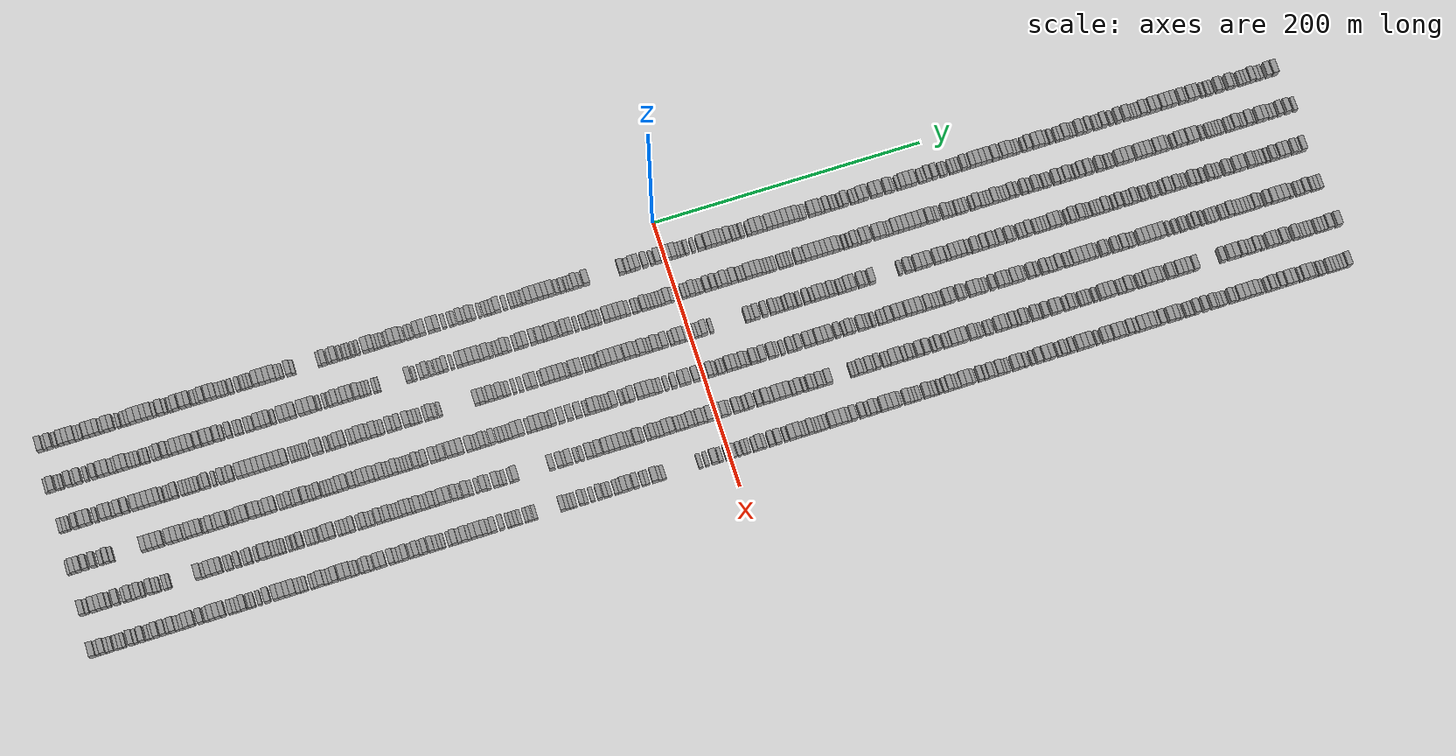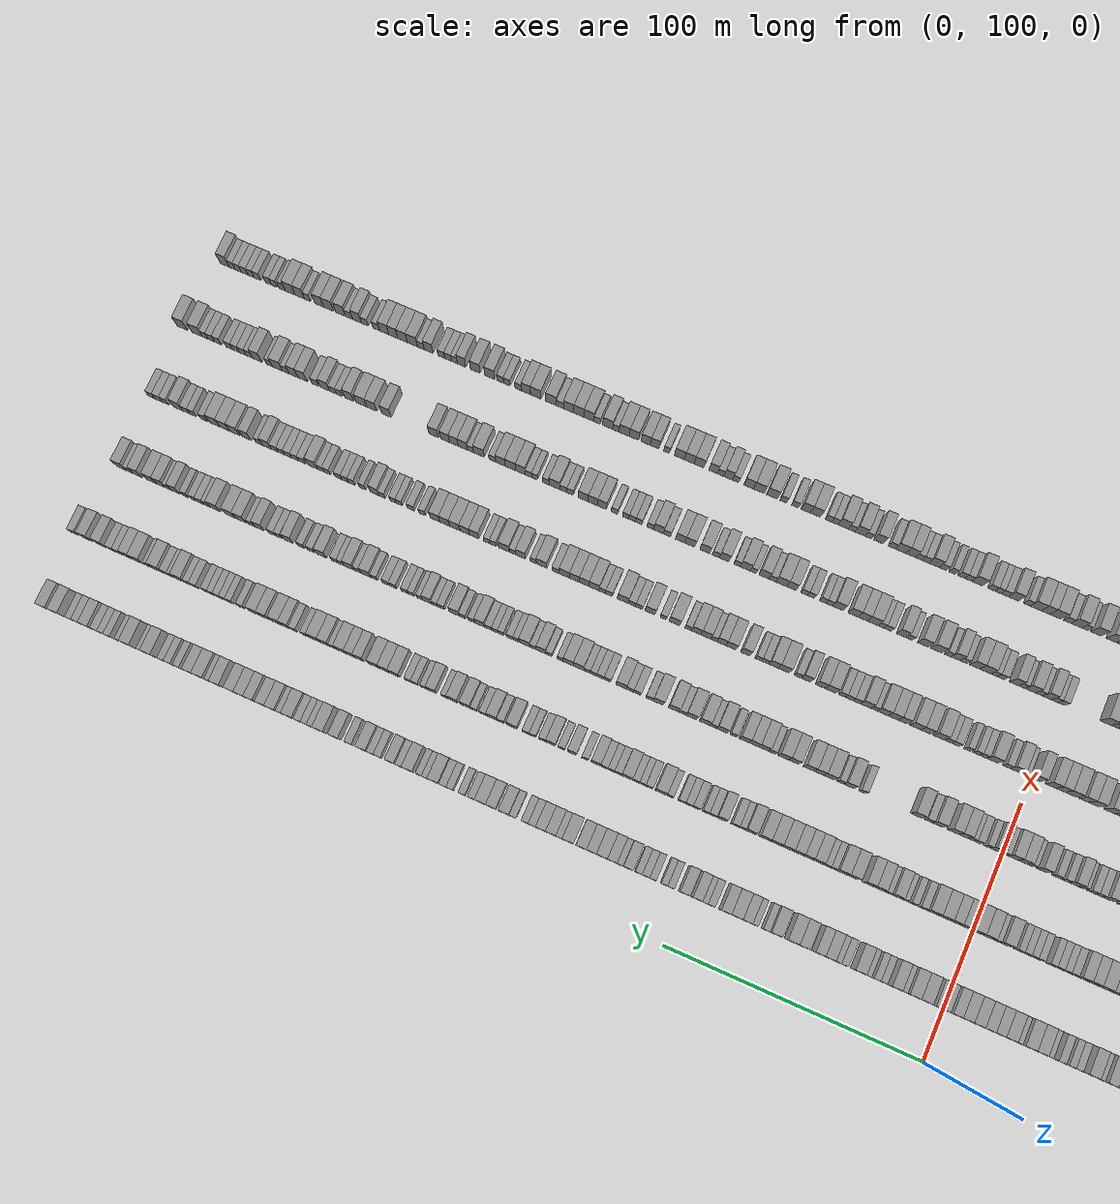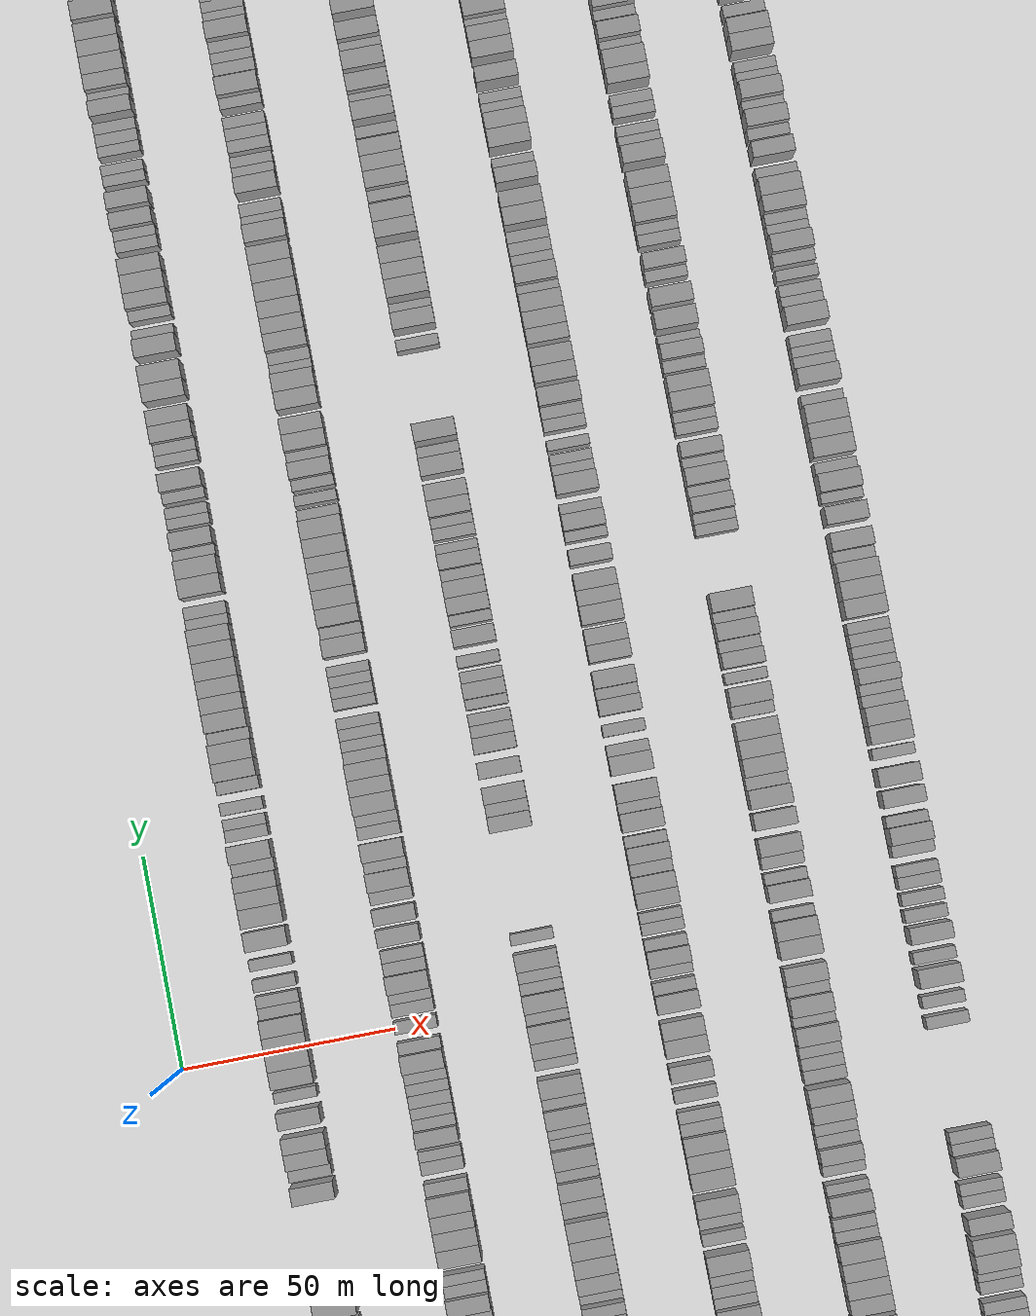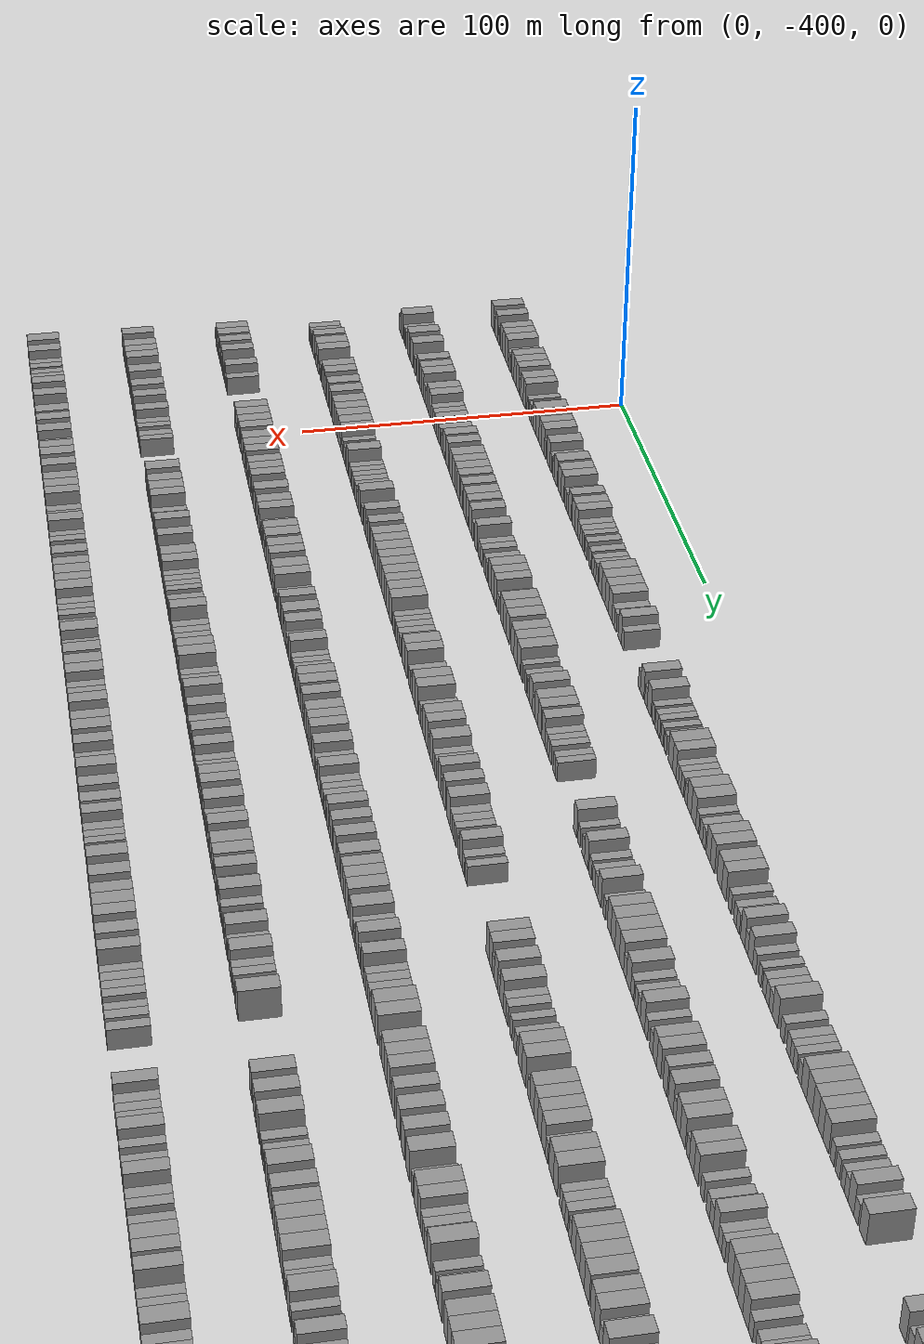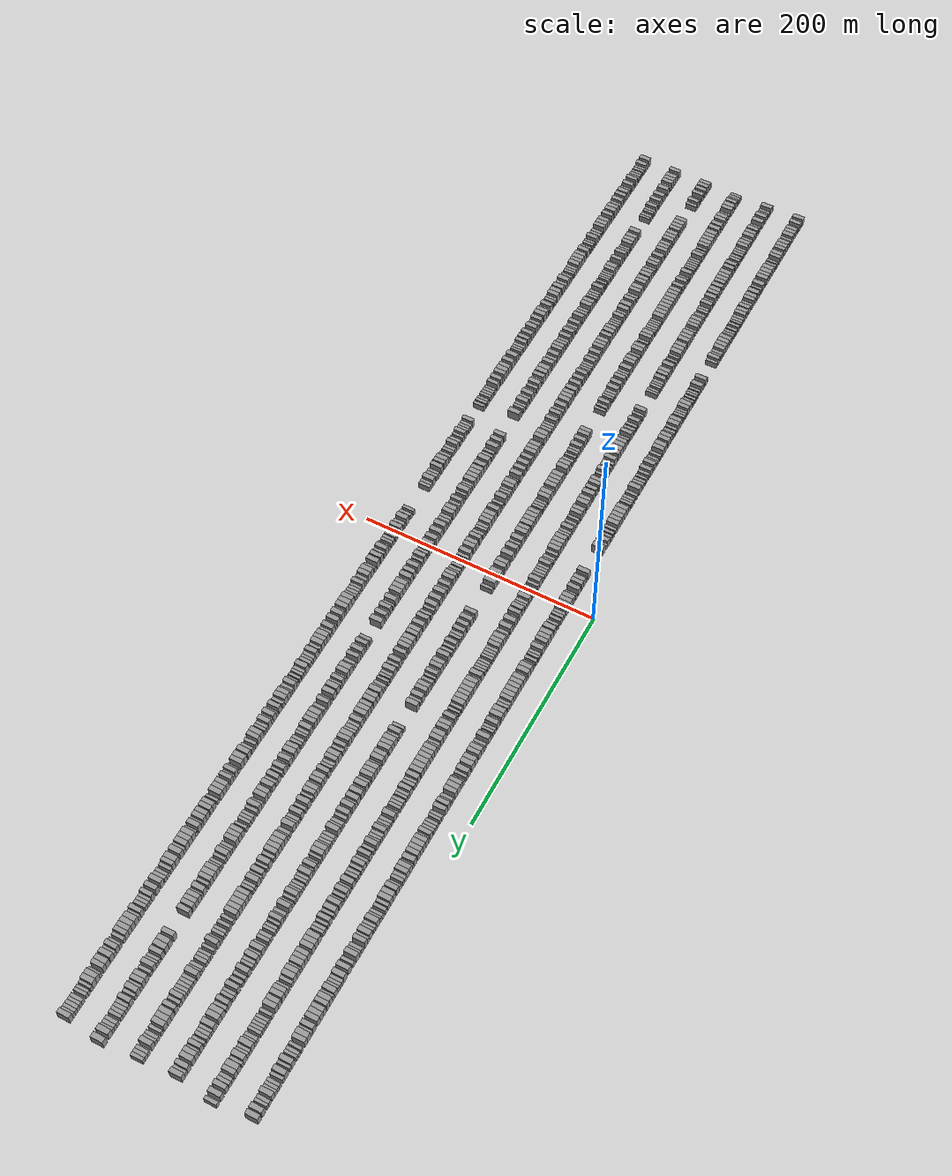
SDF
<sdf version="1.6">
 <world name="default">
  <scene>
   <sky><clouds><speed>12</speed></clouds></sky>
   <ambient>0.4 0.4 0.4 1</ambient>
   <background>0.7 0.7 0.7 1</background>
   <shadows>1</shadows>
  </scene>
  <gravity>0 0 -9.8066</gravity>
  <magnetic_field>6e-06 2.3e-05 -4.2e-05</magnetic_field>
  <physics default="0" name="default_physics" type="ode">
   <ode>
    <solver>
     <type>quick</type>
     <iters>10</iters>
     <sor>1.0</sor>
     <use_dynamic_moi_rescaling>0</use_dynamic_moi_rescaling>
    </solver>
    <constraints>
     <cfm>0</cfm>
     <erp>0.2</erp>
     <contact_max_correcting_vel>100</contact_max_correcting_vel>
     <contact_surface_layer>0.001</contact_surface_layer>
    </constraints>
   </ode>
   <max_step_size>0.004</max_step_size>
   <real_time_factor>1</real_time_factor>
   <real_time_update_rate>250</real_time_update_rate>
  </physics>
  <light name="sun" type="directional">
   <pose>0 0 10 0 0 0</pose>
   <diffuse>0.8 0.8 0.8 1</diffuse>
   <specular>0.2 0.2 0.2 1</specular>
   <attenuation>
    <range>1000</range>
    <constant>0.9</constant>
    <linear>0.01</linear>
    <quadratic>0.001</quadratic>
   </attenuation>
   <direction>-0.5 0.1 -0.9</direction>
  </light>
  <model name="building_1">
   <static>1</static>
   <pose>25.0000 -455.8936 0 0.000000 0.000000 0.000000</pose>
   <link name="link">
    <pose>0 0 4.50 0 0 0</pose>
    <collision name="collision"><geometry><box><size>10.0000 4.2127 9.0000</size></box></geometry></collision>
    <visual name="visual">
     <cast_shadows>0</cast_shadows>
     <geometry><box><size>10.0000 4.2127 9.0000</size></box></geometry>
     <material>
      <script>
       <uri>model://grey_wall/materials/scripts</uri>
       <uri>model://grey_wall/materials/textures</uri>
       <name>vrc/grey_wall</name>
      </script>
     </material>
    </visual>
   </link>
  </model>
  <model name="building_2">
   <static>1</static>
   <pose>25.0000 -452.5124 0 0.000000 0.000000 0.000000</pose>
   <link name="link">
    <pose>0 0 3.00 0 0 0</pose>
    <collision name="collision"><geometry><box><size>10.0000 2.5498 6.0000</size></box></geometry></collision>
    <visual name="visual">
     <cast_shadows>0</cast_shadows>
     <geometry><box><size>10.0000 2.5498 6.0000</size></box></geometry>
     <material>
      <script>
       <uri>model://grey_wall/materials/scripts</uri>
       <uri>model://grey_wall/materials/textures</uri>
       <name>vrc/grey_wall</name>
      </script>
     </material>
    </visual>
   </link>
  </model>
  <model name="building_3">
   <static>1</static>
   <pose>25.0000 -449.2674 0 0.000000 0.000000 0.000000</pose>
   <link name="link">
    <pose>0 0 4.50 0 0 0</pose>
    <collision name="collision"><geometry><box><size>10.0000 3.9400 9.0000</size></box></geometry></collision>
    <visual name="visual">
     <cast_shadows>0</cast_shadows>
     <geometry><box><size>10.0000 3.9400 9.0000</size></box></geometry>
     <material>
      <script>
       <uri>model://grey_wall/materials/scripts</uri>
       <uri>model://grey_wall/materials/textures</uri>
       <name>vrc/grey_wall</name>
      </script>
     </material>
    </visual>
   </link>
  </model>
  <model name="building_4">
   <static>1</static>
   <pose>25.0000 -445.0389 0 0.000000 0.000000 0.000000</pose>
   <link name="link">
    <pose>0 0 3.00 0 0 0</pose>
    <collision name="collision"><geometry><box><size>10.0000 2.5171 6.0000</size></box></geometry></collision>
    <visual name="visual">
     <cast_shadows>0</cast_shadows>
     <geometry><box><size>10.0000 2.5171 6.0000</size></box></geometry>
     <material>
      <script>
       <uri>model://grey_wall/materials/scripts</uri>
       <uri>model://grey_wall/materials/textures</uri>
       <name>vrc/grey_wall</name>
      </script>
     </material>
    </visual>
   </link>
  </model>
  <model name="building_5">
   <static>1</static>
   <pose>25.0000 -440.9776 0 0.000000 0.000000 0.000000</pose>
   <link name="link">
    <pose>0 0 4.50 0 0 0</pose>
    <collision name="collision"><geometry><box><size>10.0000 3.6056 9.0000</size></box></geometry></collision>
    <visual name="visual">
     <cast_shadows>0</cast_shadows>
     <geometry><box><size>10.0000 3.6056 9.0000</size></box></geometry>
     <material>
      <script>
       <uri>model://grey_wall/materials/scripts</uri>
       <uri>model://grey_wall/materials/textures</uri>
       <name>vrc/grey_wall</name>
      </script>
     </material>
    </visual>
   </link>
  </model>
  <model name="building_6">
   <static>1</static>
   <pose>25.0000 -437.2554 0 0.000000 0.000000 0.000000</pose>
   <link name="link">
    <pose>0 0 4.50 0 0 0</pose>
    <collision name="collision"><geometry><box><size>10.0000 3.8387 9.0000</size></box></geometry></collision>
    <visual name="visual">
     <cast_shadows>0</cast_shadows>
     <geometry><box><size>10.0000 3.8387 9.0000</size></box></geometry>
     <material>
      <script>
       <uri>model://grey_wall/materials/scripts</uri>
       <uri>model://grey_wall/materials/textures</uri>
       <name>vrc/grey_wall</name>
      </script>
     </material>
    </visual>
   </link>
  </model>
  <model name="building_7">
   <static>1</static>
   <pose>25.0000 -433.1729 0 0.000000 0.000000 0.000000</pose>
   <link name="link">
    <pose>0 0 4.50 0 0 0</pose>
    <collision name="collision"><geometry><box><size>10.0000 4.3263 9.0000</size></box></geometry></collision>
    <visual name="visual">
     <cast_shadows>0</cast_shadows>
     <geometry><box><size>10.0000 4.3263 9.0000</size></box></geometry>
     <material>
      <script>
       <uri>model://grey_wall/materials/scripts</uri>
       <uri>model://grey_wall/materials/textures</uri>
       <name>vrc/grey_wall</name>
      </script>
     </material>
    </visual>
   </link>
  </model>
  <model name="building_8">
   <static>1</static>
   <pose>25.0000 -429.6793 0 0.000000 0.000000 0.000000</pose>
   <link name="link">
    <pose>0 0 3.00 0 0 0</pose>
    <collision name="collision"><geometry><box><size>10.0000 2.6608 6.0000</size></box></geometry></collision>
    <visual name="visual">
     <cast_shadows>0</cast_shadows>
     <geometry><box><size>10.0000 2.6608 6.0000</size></box></geometry>
     <material>
      <script>
       <uri>model://grey_wall/materials/scripts</uri>
       <uri>model://grey_wall/materials/textures</uri>
       <name>vrc/grey_wall</name>
      </script>
     </material>
    </visual>
   </link>
  </model>
  <model name="building_9">
   <static>1</static>
   <pose>25.0000 -427.0337 0 0.000000 0.000000 0.000000</pose>
   <link name="link">
    <pose>0 0 3.00 0 0 0</pose>
    <collision name="collision"><geometry><box><size>10.0000 2.6304 6.0000</size></box></geometry></collision>
    <visual name="visual">
     <cast_shadows>0</cast_shadows>
     <geometry><box><size>10.0000 2.6304 6.0000</size></box></geometry>
     <material>
      <script>
       <uri>model://grey_wall/materials/scripts</uri>
       <uri>model://grey_wall/materials/textures</uri>
       <name>vrc/grey_wall</name>
      </script>
     </material>
    </visual>
   </link>
  </model>
  <model name="building_10">
   <static>1</static>
   <pose>25.0000 -422.8815 0 0.000000 0.000000 0.000000</pose>
   <link name="link">
    <pose>0 0 4.50 0 0 0</pose>
    <collision name="collision"><geometry><box><size>10.0000 3.6740 9.0000</size></box></geometry></collision>
    <visual name="visual">
     <cast_shadows>0</cast_shadows>
     <geometry><box><size>10.0000 3.6740 9.0000</size></box></geometry>
     <material>
      <script>
       <uri>model://grey_wall/materials/scripts</uri>
       <uri>model://grey_wall/materials/textures</uri>
       <name>vrc/grey_wall</name>
      </script>
     </material>
    </visual>
   </link>
  </model>
  <model name="building_11">
   <static>1</static>
   <pose>25.0000 -419.0281 0 0.000000 0.000000 0.000000</pose>
   <link name="link">
    <pose>0 0 4.50 0 0 0</pose>
    <collision name="collision"><geometry><box><size>10.0000 4.0328 9.0000</size></box></geometry></collision>
    <visual name="visual">
     <cast_shadows>0</cast_shadows>
     <geometry><box><size>10.0000 4.0328 9.0000</size></box></geometry>
     <material>
      <script>
       <uri>model://grey_wall/materials/scripts</uri>
       <uri>model://grey_wall/materials/textures</uri>
       <name>vrc/grey_wall</name>
      </script>
     </material>
    </visual>
   </link>
  </model>
  <model name="building_12">
   <static>1</static>
   <pose>25.0000 -415.1322 0 0.000000 0.000000 0.000000</pose>
   <link name="link">
    <pose>0 0 4.50 0 0 0</pose>
    <collision name="collision"><geometry><box><size>10.0000 3.7590 9.0000</size></box></geometry></collision>
    <visual name="visual">
     <cast_shadows>0</cast_shadows>
     <geometry><box><size>10.0000 3.7590 9.0000</size></box></geometry>
     <material>
      <script>
       <uri>model://grey_wall/materials/scripts</uri>
       <uri>model://grey_wall/materials/textures</uri>
       <name>vrc/grey_wall</name>
      </script>
     </material>
    </visual>
   </link>
  </model>
  <model name="building_13">
   <static>1</static>
   <pose>25.0000 -411.9635 0 0.000000 0.000000 0.000000</pose>
   <link name="link">
    <pose>0 0 3.00 0 0 0</pose>
    <collision name="collision"><geometry><box><size>10.0000 2.5786 6.0000</size></box></geometry></collision>
    <visual name="visual">
     <cast_shadows>0</cast_shadows>
     <geometry><box><size>10.0000 2.5786 6.0000</size></box></geometry>
     <material>
      <script>
       <uri>model://grey_wall/materials/scripts</uri>
       <uri>model://grey_wall/materials/textures</uri>
       <name>vrc/grey_wall</name>
      </script>
     </material>
    </visual>
   </link>
  </model>
  <model name="building_14">
   <static>1</static>
   <pose>25.0000 -408.5724 0 0.000000 0.000000 0.000000</pose>
   <link name="link">
    <pose>0 0 4.50 0 0 0</pose>
    <collision name="collision"><geometry><box><size>10.0000 4.2035 9.0000</size></box></geometry></collision>
    <visual name="visual">
     <cast_shadows>0</cast_shadows>
     <geometry><box><size>10.0000 4.2035 9.0000</size></box></geometry>
     <material>
      <script>
       <uri>model://grey_wall/materials/scripts</uri>
       <uri>model://grey_wall/materials/textures</uri>
       <name>vrc/grey_wall</name>
      </script>
     </material>
    </visual>
   </link>
  </model>
  <model name="building_15">
   <static>1</static>
   <pose>25.0000 -404.6288 0 0.000000 0.000000 0.000000</pose>
   <link name="link">
    <pose>0 0 4.50 0 0 0</pose>
    <collision name="collision"><geometry><box><size>10.0000 3.6838 9.0000</size></box></geometry></collision>
    <visual name="visual">
     <cast_shadows>0</cast_shadows>
     <geometry><box><size>10.0000 3.6838 9.0000</size></box></geometry>
     <material>
      <script>
       <uri>model://grey_wall/materials/scripts</uri>
       <uri>model://grey_wall/materials/textures</uri>
       <name>vrc/grey_wall</name>
      </script>
     </material>
    </visual>
   </link>
  </model>
  <model name="building_16">
   <static>1</static>
   <pose>25.0000 -399.5275 0 0.000000 0.000000 0.000000</pose>
   <link name="link">
    <pose>0 0 3.00 0 0 0</pose>
    <collision name="collision"><geometry><box><size>10.0000 2.5189 6.0000</size></box></geometry></collision>
    <visual name="visual">
     <cast_shadows>0</cast_shadows>
     <geometry><box><size>10.0000 2.5189 6.0000</size></box></geometry>
     <material>
      <script>
       <uri>model://grey_wall/materials/scripts</uri>
       <uri>model://grey_wall/materials/textures</uri>
       <name>vrc/grey_wall</name>
      </script>
     </material>
    </visual>
   </link>
  </model>
  <model name="building_17">
   <static>1</static>
   <pose>25.0000 -395.9769 0 0.000000 0.000000 0.000000</pose>
   <link name="link">
    <pose>0 0 3.00 0 0 0</pose>
    <collision name="collision"><geometry><box><size>10.0000 2.5824 6.0000</size></box></geometry></collision>
    <visual name="visual">
     <cast_shadows>0</cast_shadows>
     <geometry><box><size>10.0000 2.5824 6.0000</size></box></geometry>
     <material>
      <script>
       <uri>model://grey_wall/materials/scripts</uri>
       <uri>model://grey_wall/materials/textures</uri>
       <name>vrc/grey_wall</name>
      </script>
     </material>
    </visual>
   </link>
  </model>
  <model name="building_18">
   <static>1</static>
   <pose>25.0000 -393.2305 0 0.000000 0.000000 0.000000</pose>
   <link name="link">
    <pose>0 0 3.00 0 0 0</pose>
    <collision name="collision"><geometry><box><size>10.0000 2.9103 6.0000</size></box></geometry></collision>
    <visual name="visual">
     <cast_shadows>0</cast_shadows>
     <geometry><box><size>10.0000 2.9103 6.0000</size></box></geometry>
     <material>
      <script>
       <uri>model://grey_wall/materials/scripts</uri>
       <uri>model://grey_wall/materials/textures</uri>
       <name>vrc/grey_wall</name>
      </script>
     </material>
    </visual>
   </link>
  </model>
  <model name="building_19">
   <static>1</static>
   <pose>25.0000 -389.5546 0 0.000000 0.000000 0.000000</pose>
   <link name="link">
    <pose>0 0 4.50 0 0 0</pose>
    <collision name="collision"><geometry><box><size>10.0000 4.4415 9.0000</size></box></geometry></collision>
    <visual name="visual">
     <cast_shadows>0</cast_shadows>
     <geometry><box><size>10.0000 4.4415 9.0000</size></box></geometry>
     <material>
      <script>
       <uri>model://grey_wall/materials/scripts</uri>
       <uri>model://grey_wall/materials/textures</uri>
       <name>vrc/grey_wall</name>
      </script>
     </material>
    </visual>
   </link>
  </model>
  <model name="building_20">
   <static>1</static>
   <pose>25.0000 -385.1655 0 0.000000 0.000000 0.000000</pose>
   <link name="link">
    <pose>0 0 4.50 0 0 0</pose>
    <collision name="collision"><geometry><box><size>10.0000 4.3367 9.0000</size></box></geometry></collision>
    <visual name="visual">
     <cast_shadows>0</cast_shadows>
     <geometry><box><size>10.0000 4.3367 9.0000</size></box></geometry>
     <material>
      <script>
       <uri>model://grey_wall/materials/scripts</uri>
       <uri>model://grey_wall/materials/textures</uri>
       <name>vrc/grey_wall</name>
      </script>
     </material>
    </visual>
   </link>
  </model>
  <model name="building_21">
   <static>1</static>
   <pose>25.0000 -381.1678 0 0.000000 0.000000 0.000000</pose>
   <link name="link">
    <pose>0 0 4.50 0 0 0</pose>
    <collision name="collision"><geometry><box><size>10.0000 3.6588 9.0000</size></box></geometry></collision>
    <visual name="visual">
     <cast_shadows>0</cast_shadows>
     <geometry><box><size>10.0000 3.6588 9.0000</size></box></geometry>
     <material>
      <script>
       <uri>model://grey_wall/materials/scripts</uri>
       <uri>model://grey_wall/materials/textures</uri>
       <name>vrc/grey_wall</name>
      </script>
     </material>
    </visual>
   </link>
  </model>
  <model name="building_22">
   <static>1</static>
   <pose>25.0000 -377.1846 0 0.000000 0.000000 0.000000</pose>
   <link name="link">
    <pose>0 0 4.50 0 0 0</pose>
    <collision name="collision"><geometry><box><size>10.0000 4.3074 9.0000</size></box></geometry></collision>
    <visual name="visual">
     <cast_shadows>0</cast_shadows>
     <geometry><box><size>10.0000 4.3074 9.0000</size></box></geometry>
     <material>
      <script>
       <uri>model://grey_wall/materials/scripts</uri>
       <uri>model://grey_wall/materials/textures</uri>
       <name>vrc/grey_wall</name>
      </script>
     </material>
    </visual>
   </link>
  </model>
  <model name="building_23">
   <static>1</static>
   <pose>25.0000 -373.7827 0 0.000000 0.000000 0.000000</pose>
   <link name="link">
    <pose>0 0 3.00 0 0 0</pose>
    <collision name="collision"><geometry><box><size>10.0000 2.4965 6.0000</size></box></geometry></collision>
    <visual name="visual">
     <cast_shadows>0</cast_shadows>
     <geometry><box><size>10.0000 2.4965 6.0000</size></box></geometry>
     <material>
      <script>
       <uri>model://grey_wall/materials/scripts</uri>
       <uri>model://grey_wall/materials/textures</uri>
       <name>vrc/grey_wall</name>
      </script>
     </material>
    </visual>
   </link>
  </model>
  <model name="building_24">
   <static>1</static>
   <pose>25.0000 -369.3030 0 0.000000 0.000000 0.000000</pose>
   <link name="link">
    <pose>0 0 4.50 0 0 0</pose>
    <collision name="collision"><geometry><box><size>10.0000 4.4628 9.0000</size></box></geometry></collision>
    <visual name="visual">
     <cast_shadows>0</cast_shadows>
     <geometry><box><size>10.0000 4.4628 9.0000</size></box></geometry>
     <material>
      <script>
       <uri>model://grey_wall/materials/scripts</uri>
       <uri>model://grey_wall/materials/textures</uri>
       <name>vrc/grey_wall</name>
      </script>
     </material>
    </visual>
   </link>
  </model>
  <model name="building_25">
   <static>1</static>
   <pose>25.0000 -365.7763 0 0.000000 0.000000 0.000000</pose>
   <link name="link">
    <pose>0 0 3.00 0 0 0</pose>
    <collision name="collision"><geometry><box><size>10.0000 2.5904 6.0000</size></box></geometry></collision>
    <visual name="visual">
     <cast_shadows>0</cast_shadows>
     <geometry><box><size>10.0000 2.5904 6.0000</size></box></geometry>
     <material>
      <script>
       <uri>model://grey_wall/materials/scripts</uri>
       <uri>model://grey_wall/materials/textures</uri>
       <name>vrc/grey_wall</name>
      </script>
     </material>
    </visual>
   </link>
  </model>
  <model name="building_26">
   <static>1</static>
   <pose>25.0000 -362.2473 0 0.000000 0.000000 0.000000</pose>
   <link name="link">
    <pose>0 0 3.00 0 0 0</pose>
    <collision name="collision"><geometry><box><size>10.0000 2.4677 6.0000</size></box></geometry></collision>
    <visual name="visual">
     <cast_shadows>0</cast_shadows>
     <geometry><box><size>10.0000 2.4677 6.0000</size></box></geometry>
     <material>
      <script>
       <uri>model://grey_wall/materials/scripts</uri>
       <uri>model://grey_wall/materials/textures</uri>
       <name>vrc/grey_wall</name>
      </script>
     </material>
    </visual>
   </link>
  </model>
  <model name="building_27">
   <static>1</static>
   <pose>25.0000 -358.7844 0 0.000000 0.000000 0.000000</pose>
   <link name="link">
    <pose>0 0 4.50 0 0 0</pose>
    <collision name="collision"><geometry><box><size>10.0000 4.4581 9.0000</size></box></geometry></collision>
    <visual name="visual">
     <cast_shadows>0</cast_shadows>
     <geometry><box><size>10.0000 4.4581 9.0000</size></box></geometry>
     <material>
      <script>
       <uri>model://grey_wall/materials/scripts</uri>
       <uri>model://grey_wall/materials/textures</uri>
       <name>vrc/grey_wall</name>
      </script>
     </material>
    </visual>
   </link>
  </model>
  <model name="building_28">
   <static>1</static>
   <pose>25.0000 -353.5578 0 0.000000 0.000000 0.000000</pose>
   <link name="link">
    <pose>0 0 4.50 0 0 0</pose>
    <collision name="collision"><geometry><box><size>10.0000 3.9950 9.0000</size></box></geometry></collision>
    <visual name="visual">
     <cast_shadows>0</cast_shadows>
     <geometry><box><size>10.0000 3.9950 9.0000</size></box></geometry>
     <material>
      <script>
       <uri>model://grey_wall/materials/scripts</uri>
       <uri>model://grey_wall/materials/textures</uri>
       <name>vrc/grey_wall</name>
      </script>
     </material>
    </visual>
   </link>
  </model>
  <model name="building_29">
   <static>1</static>
   <pose>25.0000 -349.6130 0 0.000000 0.000000 0.000000</pose>
   <link name="link">
    <pose>0 0 4.50 0 0 0</pose>
    <collision name="collision"><geometry><box><size>10.0000 3.8945 9.0000</size></box></geometry></collision>
    <visual name="visual">
     <cast_shadows>0</cast_shadows>
     <geometry><box><size>10.0000 3.8945 9.0000</size></box></geometry>
     <material>
      <script>
       <uri>model://grey_wall/materials/scripts</uri>
       <uri>model://grey_wall/materials/textures</uri>
       <name>vrc/grey_wall</name>
      </script>
     </material>
    </visual>
   </link>
  </model>
  <model name="building_30">
   <static>1</static>
   <pose>25.0000 -345.2733 0 0.000000 0.000000 0.000000</pose>
   <link name="link">
    <pose>0 0 3.00 0 0 0</pose>
    <collision name="collision"><geometry><box><size>10.0000 2.7850 6.0000</size></box></geometry></collision>
    <visual name="visual">
     <cast_shadows>0</cast_shadows>
     <geometry><box><size>10.0000 2.7850 6.0000</size></box></geometry>
     <material>
      <script>
       <uri>model://grey_wall/materials/scripts</uri>
       <uri>model://grey_wall/materials/textures</uri>
       <name>vrc/grey_wall</name>
      </script>
     </material>
    </visual>
   </link>
  </model>
  <model name="building_31">
   <static>1</static>
   <pose>25.0000 -342.6773 0 0.000000 0.000000 0.000000</pose>
   <link name="link">
    <pose>0 0 3.00 0 0 0</pose>
    <collision name="collision"><geometry><box><size>10.0000 2.4070 6.0000</size></box></geometry></collision>
    <visual name="visual">
     <cast_shadows>0</cast_shadows>
     <geometry><box><size>10.0000 2.4070 6.0000</size></box></geometry>
     <material>
      <script>
       <uri>model://grey_wall/materials/scripts</uri>
       <uri>model://grey_wall/materials/textures</uri>
       <name>vrc/grey_wall</name>
      </script>
     </material>
    </visual>
   </link>
  </model>
  <model name="building_32">
   <static>1</static>
   <pose>25.0000 -339.5531 0 0.000000 0.000000 0.000000</pose>
   <link name="link">
    <pose>0 0 4.50 0 0 0</pose>
    <collision name="collision"><geometry><box><size>10.0000 3.8413 9.0000</size></box></geometry></collision>
    <visual name="visual">
     <cast_shadows>0</cast_shadows>
     <geometry><box><size>10.0000 3.8413 9.0000</size></box></geometry>
     <material>
      <script>
       <uri>model://grey_wall/materials/scripts</uri>
       <uri>model://grey_wall/materials/textures</uri>
       <name>vrc/grey_wall</name>
      </script>
     </material>
    </visual>
   </link>
  </model>
  <model name="building_33">
   <static>1</static>
   <pose>25.0000 -334.7408 0 0.000000 0.000000 0.000000</pose>
   <link name="link">
    <pose>0 0 4.50 0 0 0</pose>
    <collision name="collision"><geometry><box><size>10.0000 3.7834 9.0000</size></box></geometry></collision>
    <visual name="visual">
     <cast_shadows>0</cast_shadows>
     <geometry><box><size>10.0000 3.7834 9.0000</size></box></geometry>
     <material>
      <script>
       <uri>model://grey_wall/materials/scripts</uri>
       <uri>model://grey_wall/materials/textures</uri>
       <name>vrc/grey_wall</name>
      </script>
     </material>
    </visual>
   </link>
  </model>
  <model name="building_34">
   <static>1</static>
   <pose>25.0000 -330.9706 0 0.000000 0.000000 0.000000</pose>
   <link name="link">
    <pose>0 0 4.50 0 0 0</pose>
    <collision name="collision"><geometry><box><size>10.0000 3.7570 9.0000</size></box></geometry></collision>
    <visual name="visual">
     <cast_shadows>0</cast_shadows>
     <geometry><box><size>10.0000 3.7570 9.0000</size></box></geometry>
     <material>
      <script>
       <uri>model://grey_wall/materials/scripts</uri>
       <uri>model://grey_wall/materials/textures</uri>
       <name>vrc/grey_wall</name>
      </script>
     </material>
    </visual>
   </link>
  </model>
  <model name="building_35">
   <static>1</static>
   <pose>25.0000 -327.5965 0 0.000000 0.000000 0.000000</pose>
   <link name="link">
    <pose>0 0 3.00 0 0 0</pose>
    <collision name="collision"><geometry><box><size>10.0000 2.9910 6.0000</size></box></geometry></collision>
    <visual name="visual">
     <cast_shadows>0</cast_shadows>
     <geometry><box><size>10.0000 2.9910 6.0000</size></box></geometry>
     <material>
      <script>
       <uri>model://grey_wall/materials/scripts</uri>
       <uri>model://grey_wall/materials/textures</uri>
       <name>vrc/grey_wall</name>
      </script>
     </material>
    </visual>
   </link>
  </model>
  <model name="building_36">
   <static>1</static>
   <pose>25.0000 -324.6349 0 0.000000 0.000000 0.000000</pose>
   <link name="link">
    <pose>0 0 3.00 0 0 0</pose>
    <collision name="collision"><geometry><box><size>10.0000 2.9322 6.0000</size></box></geometry></collision>
    <visual name="visual">
     <cast_shadows>0</cast_shadows>
     <geometry><box><size>10.0000 2.9322 6.0000</size></box></geometry>
     <material>
      <script>
       <uri>model://grey_wall/materials/scripts</uri>
       <uri>model://grey_wall/materials/textures</uri>
       <name>vrc/grey_wall</name>
      </script>
     </material>
    </visual>
   </link>
  </model>
  <model name="building_37">
   <static>1</static>
   <pose>25.0000 -321.9463 0 0.000000 0.000000 0.000000</pose>
   <link name="link">
    <pose>0 0 3.00 0 0 0</pose>
    <collision name="collision"><geometry><box><size>10.0000 2.4450 6.0000</size></box></geometry></collision>
    <visual name="visual">
     <cast_shadows>0</cast_shadows>
     <geometry><box><size>10.0000 2.4450 6.0000</size></box></geometry>
     <material>
      <script>
       <uri>model://grey_wall/materials/scripts</uri>
       <uri>model://grey_wall/materials/textures</uri>
       <name>vrc/grey_wall</name>
      </script>
     </material>
    </visual>
   </link>
  </model>
  <model name="building_38">
   <static>1</static>
   <pose>25.0000 -318.2439 0 0.000000 0.000000 0.000000</pose>
   <link name="link">
    <pose>0 0 3.00 0 0 0</pose>
    <collision name="collision"><geometry><box><size>10.0000 2.9599 6.0000</size></box></geometry></collision>
    <visual name="visual">
     <cast_shadows>0</cast_shadows>
     <geometry><box><size>10.0000 2.9599 6.0000</size></box></geometry>
     <material>
      <script>
       <uri>model://grey_wall/materials/scripts</uri>
       <uri>model://grey_wall/materials/textures</uri>
       <name>vrc/grey_wall</name>
      </script>
     </material>
    </visual>
   </link>
  </model>
  <model name="building_39">
   <static>1</static>
   <pose>25.0000 -313.2791 0 0.000000 0.000000 0.000000</pose>
   <link name="link">
    <pose>0 0 3.00 0 0 0</pose>
    <collision name="collision"><geometry><box><size>10.0000 2.9697 6.0000</size></box></geometry></collision>
    <visual name="visual">
     <cast_shadows>0</cast_shadows>
     <geometry><box><size>10.0000 2.9697 6.0000</size></box></geometry>
     <material>
      <script>
       <uri>model://grey_wall/materials/scripts</uri>
       <uri>model://grey_wall/materials/textures</uri>
       <name>vrc/grey_wall</name>
      </script>
     </material>
    </visual>
   </link>
  </model>
  <model name="building_40">
   <static>1</static>
   <pose>25.0000 -309.5006 0 0.000000 0.000000 0.000000</pose>
   <link name="link">
    <pose>0 0 3.00 0 0 0</pose>
    <collision name="collision"><geometry><box><size>10.0000 2.5875 6.0000</size></box></geometry></collision>
    <visual name="visual">
     <cast_shadows>0</cast_shadows>
     <geometry><box><size>10.0000 2.5875 6.0000</size></box></geometry>
     <material>
      <script>
       <uri>model://grey_wall/materials/scripts</uri>
       <uri>model://grey_wall/materials/textures</uri>
       <name>vrc/grey_wall</name>
      </script>
     </material>
    </visual>
   </link>
  </model>
  <model name="building_41">
   <static>1</static>
   <pose>25.0000 -306.9783 0 0.000000 0.000000 0.000000</pose>
   <link name="link">
    <pose>0 0 3.00 0 0 0</pose>
    <collision name="collision"><geometry><box><size>10.0000 2.4570 6.0000</size></box></geometry></collision>
    <visual name="visual">
     <cast_shadows>0</cast_shadows>
     <geometry><box><size>10.0000 2.4570 6.0000</size></box></geometry>
     <material>
      <script>
       <uri>model://grey_wall/materials/scripts</uri>
       <uri>model://grey_wall/materials/textures</uri>
       <name>vrc/grey_wall</name>
      </script>
     </material>
    </visual>
   </link>
  </model>
  <model name="building_42">
   <static>1</static>
   <pose>25.0000 -304.4984 0 0.000000 0.000000 0.000000</pose>
   <link name="link">
    <pose>0 0 3.00 0 0 0</pose>
    <collision name="collision"><geometry><box><size>10.0000 2.5028 6.0000</size></box></geometry></collision>
    <visual name="visual">
     <cast_shadows>0</cast_shadows>
     <geometry><box><size>10.0000 2.5028 6.0000</size></box></geometry>
     <material>
      <script>
       <uri>model://grey_wall/materials/scripts</uri>
       <uri>model://grey_wall/materials/textures</uri>
       <name>vrc/grey_wall</name>
      </script>
     </material>
    </visual>
   </link>
  </model>
  <model name="building_43">
   <static>1</static>
   <pose>25.0000 -300.3160 0 0.000000 0.000000 0.000000</pose>
   <link name="link">
    <pose>0 0 4.50 0 0 0</pose>
    <collision name="collision"><geometry><box><size>10.0000 3.8619 9.0000</size></box></geometry></collision>
    <visual name="visual">
     <cast_shadows>0</cast_shadows>
     <geometry><box><size>10.0000 3.8619 9.0000</size></box></geometry>
     <material>
      <script>
       <uri>model://grey_wall/materials/scripts</uri>
       <uri>model://grey_wall/materials/textures</uri>
       <name>vrc/grey_wall</name>
      </script>
     </material>
    </visual>
   </link>
  </model>
  <model name="building_44">
   <static>1</static>
   <pose>25.0000 -296.2366 0 0.000000 0.000000 0.000000</pose>
   <link name="link">
    <pose>0 0 4.50 0 0 0</pose>
    <collision name="collision"><geometry><box><size>10.0000 4.2969 9.0000</size></box></geometry></collision>
    <visual name="visual">
     <cast_shadows>0</cast_shadows>
     <geometry><box><size>10.0000 4.2969 9.0000</size></box></geometry>
     <material>
      <script>
       <uri>model://grey_wall/materials/scripts</uri>
       <uri>model://grey_wall/materials/textures</uri>
       <name>vrc/grey_wall</name>
      </script>
     </material>
    </visual>
   </link>
  </model>
  <model name="building_45">
   <static>1</static>
   <pose>25.0000 -292.0810 0 0.000000 0.000000 0.000000</pose>
   <link name="link">
    <pose>0 0 4.50 0 0 0</pose>
    <collision name="collision"><geometry><box><size>10.0000 4.0142 9.0000</size></box></geometry></collision>
    <visual name="visual">
     <cast_shadows>0</cast_shadows>
     <geometry><box><size>10.0000 4.0142 9.0000</size></box></geometry>
     <material>
      <script>
       <uri>model://grey_wall/materials/scripts</uri>
       <uri>model://grey_wall/materials/textures</uri>
       <name>vrc/grey_wall</name>
      </script>
     </material>
    </visual>
   </link>
  </model>
  <model name="building_46">
   <static>1</static>
   <pose>25.0000 -287.9887 0 0.000000 0.000000 0.000000</pose>
   <link name="link">
    <pose>0 0 4.50 0 0 0</pose>
    <collision name="collision"><geometry><box><size>10.0000 4.1703 9.0000</size></box></geometry></collision>
    <visual name="visual">
     <cast_shadows>0</cast_shadows>
     <geometry><box><size>10.0000 4.1703 9.0000</size></box></geometry>
     <material>
      <script>
       <uri>model://grey_wall/materials/scripts</uri>
       <uri>model://grey_wall/materials/textures</uri>
       <name>vrc/grey_wall</name>
      </script>
     </material>
    </visual>
   </link>
  </model>
  <model name="building_47">
   <static>1</static>
   <pose>25.0000 -284.4105 0 0.000000 0.000000 0.000000</pose>
   <link name="link">
    <pose>0 0 3.00 0 0 0</pose>
    <collision name="collision"><geometry><box><size>10.0000 2.9862 6.0000</size></box></geometry></collision>
    <visual name="visual">
     <cast_shadows>0</cast_shadows>
     <geometry><box><size>10.0000 2.9862 6.0000</size></box></geometry>
     <material>
      <script>
       <uri>model://grey_wall/materials/scripts</uri>
       <uri>model://grey_wall/materials/textures</uri>
       <name>vrc/grey_wall</name>
      </script>
     </material>
    </visual>
   </link>
  </model>
  <model name="building_48">
   <static>1</static>
   <pose>25.0000 -281.6643 0 0.000000 0.000000 0.000000</pose>
   <link name="link">
    <pose>0 0 3.00 0 0 0</pose>
    <collision name="collision"><geometry><box><size>10.0000 2.5062 6.0000</size></box></geometry></collision>
    <visual name="visual">
     <cast_shadows>0</cast_shadows>
     <geometry><box><size>10.0000 2.5062 6.0000</size></box></geometry>
     <material>
      <script>
       <uri>model://grey_wall/materials/scripts</uri>
       <uri>model://grey_wall/materials/textures</uri>
       <name>vrc/grey_wall</name>
      </script>
     </material>
    </visual>
   </link>
  </model>
  <model name="building_49">
   <static>1</static>
   <pose>25.0000 -276.4811 0 0.000000 0.000000 0.000000</pose>
   <link name="link">
    <pose>0 0 4.50 0 0 0</pose>
    <collision name="collision"><geometry><box><size>10.0000 3.8602 9.0000</size></box></geometry></collision>
    <visual name="visual">
     <cast_shadows>0</cast_shadows>
     <geometry><box><size>10.0000 3.8602 9.0000</size></box></geometry>
     <material>
      <script>
       <uri>model://grey_wall/materials/scripts</uri>
       <uri>model://grey_wall/materials/textures</uri>
       <name>vrc/grey_wall</name>
      </script>
     </material>
    </visual>
   </link>
  </model>
  <model name="building_50">
   <static>1</static>
   <pose>25.0000 -273.1703 0 0.000000 0.000000 0.000000</pose>
   <link name="link">
    <pose>0 0 3.00 0 0 0</pose>
    <collision name="collision"><geometry><box><size>10.0000 2.7614 6.0000</size></box></geometry></collision>
    <visual name="visual">
     <cast_shadows>0</cast_shadows>
     <geometry><box><size>10.0000 2.7614 6.0000</size></box></geometry>
     <material>
      <script>
       <uri>model://grey_wall/materials/scripts</uri>
       <uri>model://grey_wall/materials/textures</uri>
       <name>vrc/grey_wall</name>
      </script>
     </material>
    </visual>
   </link>
  </model>
  <model name="building_51">
   <static>1</static>
   <pose>25.0000 -254.0717 0 0.000000 0.000000 0.000000</pose>
   <link name="link">
    <pose>0 0 3.00 0 0 0</pose>
    <collision name="collision"><geometry><box><size>10.0000 2.4786 6.0000</size></box></geometry></collision>
    <visual name="visual">
     <cast_shadows>0</cast_shadows>
     <geometry><box><size>10.0000 2.4786 6.0000</size></box></geometry>
     <material>
      <script>
       <uri>model://grey_wall/materials/scripts</uri>
       <uri>model://grey_wall/materials/textures</uri>
       <name>vrc/grey_wall</name>
      </script>
     </material>
    </visual>
   </link>
  </model>
  <model name="building_52">
   <static>1</static>
   <pose>25.0000 -250.9036 0 0.000000 0.000000 0.000000</pose>
   <link name="link">
    <pose>0 0 4.50 0 0 0</pose>
    <collision name="collision"><geometry><box><size>10.0000 3.8577 9.0000</size></box></geometry></collision>
    <visual name="visual">
     <cast_shadows>0</cast_shadows>
     <geometry><box><size>10.0000 3.8577 9.0000</size></box></geometry>
     <material>
      <script>
       <uri>model://grey_wall/materials/scripts</uri>
       <uri>model://grey_wall/materials/textures</uri>
       <name>vrc/grey_wall</name>
      </script>
     </material>
    </visual>
   </link>
  </model>
  <model name="building_53">
   <static>1</static>
   <pose>25.0000 -246.6851 0 0.000000 0.000000 0.000000</pose>
   <link name="link">
    <pose>0 0 3.00 0 0 0</pose>
    <collision name="collision"><geometry><box><size>10.0000 2.5791 6.0000</size></box></geometry></collision>
    <visual name="visual">
     <cast_shadows>0</cast_shadows>
     <geometry><box><size>10.0000 2.5791 6.0000</size></box></geometry>
     <material>
      <script>
       <uri>model://grey_wall/materials/scripts</uri>
       <uri>model://grey_wall/materials/textures</uri>
       <name>vrc/grey_wall</name>
      </script>
     </material>
    </visual>
   </link>
  </model>
  <model name="building_54">
   <static>1</static>
   <pose>25.0000 -243.3000 0 0.000000 0.000000 0.000000</pose>
   <link name="link">
    <pose>0 0 4.50 0 0 0</pose>
    <collision name="collision"><geometry><box><size>10.0000 4.1912 9.0000</size></box></geometry></collision>
    <visual name="visual">
     <cast_shadows>0</cast_shadows>
     <geometry><box><size>10.0000 4.1912 9.0000</size></box></geometry>
     <material>
      <script>
       <uri>model://grey_wall/materials/scripts</uri>
       <uri>model://grey_wall/materials/textures</uri>
       <name>vrc/grey_wall</name>
      </script>
     </material>
    </visual>
   </link>
  </model>
  <model name="building_55">
   <static>1</static>
   <pose>25.0000 -238.9054 0 0.000000 0.000000 0.000000</pose>
   <link name="link">
    <pose>0 0 3.00 0 0 0</pose>
    <collision name="collision"><geometry><box><size>10.0000 2.5979 6.0000</size></box></geometry></collision>
    <visual name="visual">
     <cast_shadows>0</cast_shadows>
     <geometry><box><size>10.0000 2.5979 6.0000</size></box></geometry>
     <material>
      <script>
       <uri>model://grey_wall/materials/scripts</uri>
       <uri>model://grey_wall/materials/textures</uri>
       <name>vrc/grey_wall</name>
      </script>
     </material>
    </visual>
   </link>
  </model>
  <model name="building_56">
   <static>1</static>
   <pose>25.0000 -235.3867 0 0.000000 0.000000 0.000000</pose>
   <link name="link">
    <pose>0 0 3.00 0 0 0</pose>
    <collision name="collision"><geometry><box><size>10.0000 2.4397 6.0000</size></box></geometry></collision>
    <visual name="visual">
     <cast_shadows>0</cast_shadows>
     <geometry><box><size>10.0000 2.4397 6.0000</size></box></geometry>
     <material>
      <script>
       <uri>model://grey_wall/materials/scripts</uri>
       <uri>model://grey_wall/materials/textures</uri>
       <name>vrc/grey_wall</name>
      </script>
     </material>
    </visual>
   </link>
  </model>
  <model name="building_57">
   <static>1</static>
   <pose>25.0000 -232.9198 0 0.000000 0.000000 0.000000</pose>
   <link name="link">
    <pose>0 0 3.00 0 0 0</pose>
    <collision name="collision"><geometry><box><size>10.0000 2.4940 6.0000</size></box></geometry></collision>
    <visual name="visual">
     <cast_shadows>0</cast_shadows>
     <geometry><box><size>10.0000 2.4940 6.0000</size></box></geometry>
     <material>
      <script>
       <uri>model://grey_wall/materials/scripts</uri>
       <uri>model://grey_wall/materials/textures</uri>
       <name>vrc/grey_wall</name>
      </script>
     </material>
    </visual>
   </link>
  </model>
  <model name="building_58">
   <static>1</static>
   <pose>25.0000 -229.4423 0 0.000000 0.000000 0.000000</pose>
   <link name="link">
    <pose>0 0 3.00 0 0 0</pose>
    <collision name="collision"><geometry><box><size>10.0000 2.4610 6.0000</size></box></geometry></collision>
    <visual name="visual">
     <cast_shadows>0</cast_shadows>
     <geometry><box><size>10.0000 2.4610 6.0000</size></box></geometry>
     <material>
      <script>
       <uri>model://grey_wall/materials/scripts</uri>
       <uri>model://grey_wall/materials/textures</uri>
       <name>vrc/grey_wall</name>
      </script>
     </material>
    </visual>
   </link>
  </model>
  <model name="building_59">
   <static>1</static>
   <pose>25.0000 -225.9578 0 0.000000 0.000000 0.000000</pose>
   <link name="link">
    <pose>0 0 3.00 0 0 0</pose>
    <collision name="collision"><geometry><box><size>10.0000 2.5080 6.0000</size></box></geometry></collision>
    <visual name="visual">
     <cast_shadows>0</cast_shadows>
     <geometry><box><size>10.0000 2.5080 6.0000</size></box></geometry>
     <material>
      <script>
       <uri>model://grey_wall/materials/scripts</uri>
       <uri>model://grey_wall/materials/textures</uri>
       <name>vrc/grey_wall</name>
      </script>
     </material>
    </visual>
   </link>
  </model>
  <model name="building_60">
   <static>1</static>
   <pose>25.0000 -220.5133 0 0.000000 0.000000 0.000000</pose>
   <link name="link">
    <pose>0 0 4.50 0 0 0</pose>
    <collision name="collision"><geometry><box><size>10.0000 4.3810 9.0000</size></box></geometry></collision>
    <visual name="visual">
     <cast_shadows>0</cast_shadows>
     <geometry><box><size>10.0000 4.3810 9.0000</size></box></geometry>
     <material>
      <script>
       <uri>model://grey_wall/materials/scripts</uri>
       <uri>model://grey_wall/materials/textures</uri>
       <name>vrc/grey_wall</name>
      </script>
     </material>
    </visual>
   </link>
  </model>
  <model name="building_61">
   <static>1</static>
   <pose>25.0000 -216.4839 0 0.000000 0.000000 0.000000</pose>
   <link name="link">
    <pose>0 0 4.50 0 0 0</pose>
    <collision name="collision"><geometry><box><size>10.0000 3.6778 9.0000</size></box></geometry></collision>
    <visual name="visual">
     <cast_shadows>0</cast_shadows>
     <geometry><box><size>10.0000 3.6778 9.0000</size></box></geometry>
     <material>
      <script>
       <uri>model://grey_wall/materials/scripts</uri>
       <uri>model://grey_wall/materials/textures</uri>
       <name>vrc/grey_wall</name>
      </script>
     </material>
    </visual>
   </link>
  </model>
  <model name="building_62">
   <static>1</static>
   <pose>25.0000 -213.4449 0 0.000000 0.000000 0.000000</pose>
   <link name="link">
    <pose>0 0 3.00 0 0 0</pose>
    <collision name="collision"><geometry><box><size>10.0000 2.4002 6.0000</size></box></geometry></collision>
    <visual name="visual">
     <cast_shadows>0</cast_shadows>
     <geometry><box><size>10.0000 2.4002 6.0000</size></box></geometry>
     <material>
      <script>
       <uri>model://grey_wall/materials/scripts</uri>
       <uri>model://grey_wall/materials/textures</uri>
       <name>vrc/grey_wall</name>
      </script>
     </material>
    </visual>
   </link>
  </model>
  <model name="building_63">
   <static>1</static>
   <pose>25.0000 -211.0081 0 0.000000 0.000000 0.000000</pose>
   <link name="link">
    <pose>0 0 3.00 0 0 0</pose>
    <collision name="collision"><geometry><box><size>10.0000 2.4734 6.0000</size></box></geometry></collision>
    <visual name="visual">
     <cast_shadows>0</cast_shadows>
     <geometry><box><size>10.0000 2.4734 6.0000</size></box></geometry>
     <material>
      <script>
       <uri>model://grey_wall/materials/scripts</uri>
       <uri>model://grey_wall/materials/textures</uri>
       <name>vrc/grey_wall</name>
      </script>
     </material>
    </visual>
   </link>
  </model>
  <model name="building_64">
   <static>1</static>
   <pose>25.0000 -208.3993 0 0.000000 0.000000 0.000000</pose>
   <link name="link">
    <pose>0 0 3.00 0 0 0</pose>
    <collision name="collision"><geometry><box><size>10.0000 2.7443 6.0000</size></box></geometry></collision>
    <visual name="visual">
     <cast_shadows>0</cast_shadows>
     <geometry><box><size>10.0000 2.7443 6.0000</size></box></geometry>
     <material>
      <script>
       <uri>model://grey_wall/materials/scripts</uri>
       <uri>model://grey_wall/materials/textures</uri>
       <name>vrc/grey_wall</name>
      </script>
     </material>
    </visual>
   </link>
  </model>
  <model name="building_65">
   <static>1</static>
   <pose>25.0000 -204.7538 0 0.000000 0.000000 0.000000</pose>
   <link name="link">
    <pose>0 0 3.00 0 0 0</pose>
    <collision name="collision"><geometry><box><size>10.0000 2.5466 6.0000</size></box></geometry></collision>
    <visual name="visual">
     <cast_shadows>0</cast_shadows>
     <geometry><box><size>10.0000 2.5466 6.0000</size></box></geometry>
     <material>
      <script>
       <uri>model://grey_wall/materials/scripts</uri>
       <uri>model://grey_wall/materials/textures</uri>
       <name>vrc/grey_wall</name>
      </script>
     </material>
    </visual>
   </link>
  </model>
  <model name="building_66">
   <static>1</static>
   <pose>25.0000 -201.4581 0 0.000000 0.000000 0.000000</pose>
   <link name="link">
    <pose>0 0 4.50 0 0 0</pose>
    <collision name="collision"><geometry><box><size>10.0000 4.0447 9.0000</size></box></geometry></collision>
    <visual name="visual">
     <cast_shadows>0</cast_shadows>
     <geometry><box><size>10.0000 4.0447 9.0000</size></box></geometry>
     <material>
      <script>
       <uri>model://grey_wall/materials/scripts</uri>
       <uri>model://grey_wall/materials/textures</uri>
       <name>vrc/grey_wall</name>
      </script>
     </material>
    </visual>
   </link>
  </model>
  <model name="building_67">
   <static>1</static>
   <pose>25.0000 -197.2024 0 0.000000 0.000000 0.000000</pose>
   <link name="link">
    <pose>0 0 4.50 0 0 0</pose>
    <collision name="collision"><geometry><box><size>10.0000 4.4668 9.0000</size></box></geometry></collision>
    <visual name="visual">
     <cast_shadows>0</cast_shadows>
     <geometry><box><size>10.0000 4.4668 9.0000</size></box></geometry>
     <material>
      <script>
       <uri>model://grey_wall/materials/scripts</uri>
       <uri>model://grey_wall/materials/textures</uri>
       <name>vrc/grey_wall</name>
      </script>
     </material>
    </visual>
   </link>
  </model>
  <model name="building_68">
   <static>1</static>
   <pose>25.0000 -193.5840 0 0.000000 0.000000 0.000000</pose>
   <link name="link">
    <pose>0 0 3.00 0 0 0</pose>
    <collision name="collision"><geometry><box><size>10.0000 2.7699 6.0000</size></box></geometry></collision>
    <visual name="visual">
     <cast_shadows>0</cast_shadows>
     <geometry><box><size>10.0000 2.7699 6.0000</size></box></geometry>
     <material>
      <script>
       <uri>model://grey_wall/materials/scripts</uri>
       <uri>model://grey_wall/materials/textures</uri>
       <name>vrc/grey_wall</name>
      </script>
     </material>
    </visual>
   </link>
  </model>
  <model name="building_69">
   <static>1</static>
   <pose>25.0000 -189.8142 0 0.000000 0.000000 0.000000</pose>
   <link name="link">
    <pose>0 0 3.00 0 0 0</pose>
    <collision name="collision"><geometry><box><size>10.0000 2.7697 6.0000</size></box></geometry></collision>
    <visual name="visual">
     <cast_shadows>0</cast_shadows>
     <geometry><box><size>10.0000 2.7697 6.0000</size></box></geometry>
     <material>
      <script>
       <uri>model://grey_wall/materials/scripts</uri>
       <uri>model://grey_wall/materials/textures</uri>
       <name>vrc/grey_wall</name>
      </script>
     </material>
    </visual>
   </link>
  </model>
  <model name="building_70">
   <static>1</static>
   <pose>25.0000 -187.1320 0 0.000000 0.000000 0.000000</pose>
   <link name="link">
    <pose>0 0 3.00 0 0 0</pose>
    <collision name="collision"><geometry><box><size>10.0000 2.5948 6.0000</size></box></geometry></collision>
    <visual name="visual">
     <cast_shadows>0</cast_shadows>
     <geometry><box><size>10.0000 2.5948 6.0000</size></box></geometry>
     <material>
      <script>
       <uri>model://grey_wall/materials/scripts</uri>
       <uri>model://grey_wall/materials/textures</uri>
       <name>vrc/grey_wall</name>
      </script>
     </material>
    </visual>
   </link>
  </model>
  <model name="building_71">
   <static>1</static>
   <pose>25.0000 -182.9568 0 0.000000 0.000000 0.000000</pose>
   <link name="link">
    <pose>0 0 4.50 0 0 0</pose>
    <collision name="collision"><geometry><box><size>10.0000 3.7555 9.0000</size></box></geometry></collision>
    <visual name="visual">
     <cast_shadows>0</cast_shadows>
     <geometry><box><size>10.0000 3.7555 9.0000</size></box></geometry>
     <material>
      <script>
       <uri>model://grey_wall/materials/scripts</uri>
       <uri>model://grey_wall/materials/textures</uri>
       <name>vrc/grey_wall</name>
      </script>
     </material>
    </visual>
   </link>
  </model>
  <model name="building_72">
   <static>1</static>
   <pose>25.0000 -178.9845 0 0.000000 0.000000 0.000000</pose>
   <link name="link">
    <pose>0 0 4.50 0 0 0</pose>
    <collision name="collision"><geometry><box><size>10.0000 4.1891 9.0000</size></box></geometry></collision>
    <visual name="visual">
     <cast_shadows>0</cast_shadows>
     <geometry><box><size>10.0000 4.1891 9.0000</size></box></geometry>
     <material>
      <script>
       <uri>model://grey_wall/materials/scripts</uri>
       <uri>model://grey_wall/materials/textures</uri>
       <name>vrc/grey_wall</name>
      </script>
     </material>
    </visual>
   </link>
  </model>
  <model name="building_73">
   <static>1</static>
   <pose>25.0000 -172.6880 0 0.000000 0.000000 0.000000</pose>
   <link name="link">
    <pose>0 0 4.50 0 0 0</pose>
    <collision name="collision"><geometry><box><size>10.0000 4.4038 9.0000</size></box></geometry></collision>
    <visual name="visual">
     <cast_shadows>0</cast_shadows>
     <geometry><box><size>10.0000 4.4038 9.0000</size></box></geometry>
     <material>
      <script>
       <uri>model://grey_wall/materials/scripts</uri>
       <uri>model://grey_wall/materials/textures</uri>
       <name>vrc/grey_wall</name>
      </script>
     </material>
    </visual>
   </link>
  </model>
  <model name="building_74">
   <static>1</static>
   <pose>25.0000 -168.4834 0 0.000000 0.000000 0.000000</pose>
   <link name="link">
    <pose>0 0 4.50 0 0 0</pose>
    <collision name="collision"><geometry><box><size>10.0000 4.0054 9.0000</size></box></geometry></collision>
    <visual name="visual">
     <cast_shadows>0</cast_shadows>
     <geometry><box><size>10.0000 4.0054 9.0000</size></box></geometry>
     <material>
      <script>
       <uri>model://grey_wall/materials/scripts</uri>
       <uri>model://grey_wall/materials/textures</uri>
       <name>vrc/grey_wall</name>
      </script>
     </material>
    </visual>
   </link>
  </model>
  <model name="building_75">
   <static>1</static>
   <pose>25.0000 -163.0647 0 0.000000 0.000000 0.000000</pose>
   <link name="link">
    <pose>0 0 3.00 0 0 0</pose>
    <collision name="collision"><geometry><box><size>10.0000 2.8319 6.0000</size></box></geometry></collision>
    <visual name="visual">
     <cast_shadows>0</cast_shadows>
     <geometry><box><size>10.0000 2.8319 6.0000</size></box></geometry>
     <material>
      <script>
       <uri>model://grey_wall/materials/scripts</uri>
       <uri>model://grey_wall/materials/textures</uri>
       <name>vrc/grey_wall</name>
      </script>
     </material>
    </visual>
   </link>
  </model>
  <model name="building_76">
   <static>1</static>
   <pose>25.0000 -158.3991 0 0.000000 0.000000 0.000000</pose>
   <link name="link">
    <pose>0 0 3.00 0 0 0</pose>
    <collision name="collision"><geometry><box><size>10.0000 2.4992 6.0000</size></box></geometry></collision>
    <visual name="visual">
     <cast_shadows>0</cast_shadows>
     <geometry><box><size>10.0000 2.4992 6.0000</size></box></geometry>
     <material>
      <script>
       <uri>model://grey_wall/materials/scripts</uri>
       <uri>model://grey_wall/materials/textures</uri>
       <name>vrc/grey_wall</name>
      </script>
     </material>
    </visual>
   </link>
  </model>
  <model name="building_77">
   <static>1</static>
   <pose>25.0000 -155.7834 0 0.000000 0.000000 0.000000</pose>
   <link name="link">
    <pose>0 0 3.00 0 0 0</pose>
    <collision name="collision"><geometry><box><size>10.0000 2.7323 6.0000</size></box></geometry></collision>
    <visual name="visual">
     <cast_shadows>0</cast_shadows>
     <geometry><box><size>10.0000 2.7323 6.0000</size></box></geometry>
     <material>
      <script>
       <uri>model://grey_wall/materials/scripts</uri>
       <uri>model://grey_wall/materials/textures</uri>
       <name>vrc/grey_wall</name>
      </script>
     </material>
    </visual>
   </link>
  </model>
  <model name="building_78">
   <static>1</static>
   <pose>25.0000 -151.5177 0 0.000000 0.000000 0.000000</pose>
   <link name="link">
    <pose>0 0 4.50 0 0 0</pose>
    <collision name="collision"><geometry><box><size>10.0000 3.7991 9.0000</size></box></geometry></collision>
    <visual name="visual">
     <cast_shadows>0</cast_shadows>
     <geometry><box><size>10.0000 3.7991 9.0000</size></box></geometry>
     <material>
      <script>
       <uri>model://grey_wall/materials/scripts</uri>
       <uri>model://grey_wall/materials/textures</uri>
       <name>vrc/grey_wall</name>
      </script>
     </material>
    </visual>
   </link>
  </model>
  <model name="building_79">
   <static>1</static>
   <pose>25.0000 -148.2393 0 0.000000 0.000000 0.000000</pose>
   <link name="link">
    <pose>0 0 3.00 0 0 0</pose>
    <collision name="collision"><geometry><box><size>10.0000 2.7577 6.0000</size></box></geometry></collision>
    <visual name="visual">
     <cast_shadows>0</cast_shadows>
     <geometry><box><size>10.0000 2.7577 6.0000</size></box></geometry>
     <material>
      <script>
       <uri>model://grey_wall/materials/scripts</uri>
       <uri>model://grey_wall/materials/textures</uri>
       <name>vrc/grey_wall</name>
      </script>
     </material>
    </visual>
   </link>
  </model>
  <model name="building_80">
   <static>1</static>
   <pose>25.0000 -144.9141 0 0.000000 0.000000 0.000000</pose>
   <link name="link">
    <pose>0 0 4.50 0 0 0</pose>
    <collision name="collision"><geometry><box><size>10.0000 3.8927 9.0000</size></box></geometry></collision>
    <visual name="visual">
     <cast_shadows>0</cast_shadows>
     <geometry><box><size>10.0000 3.8927 9.0000</size></box></geometry>
     <material>
      <script>
       <uri>model://grey_wall/materials/scripts</uri>
       <uri>model://grey_wall/materials/textures</uri>
       <name>vrc/grey_wall</name>
      </script>
     </material>
    </visual>
   </link>
  </model>
  <model name="building_81">
   <static>1</static>
   <pose>25.0000 -141.5319 0 0.000000 0.000000 0.000000</pose>
   <link name="link">
    <pose>0 0 3.00 0 0 0</pose>
    <collision name="collision"><geometry><box><size>10.0000 2.8716 6.0000</size></box></geometry></collision>
    <visual name="visual">
     <cast_shadows>0</cast_shadows>
     <geometry><box><size>10.0000 2.8716 6.0000</size></box></geometry>
     <material>
      <script>
       <uri>model://grey_wall/materials/scripts</uri>
       <uri>model://grey_wall/materials/textures</uri>
       <name>vrc/grey_wall</name>
      </script>
     </material>
    </visual>
   </link>
  </model>
  <model name="building_82">
   <static>1</static>
   <pose>25.0000 -136.8533 0 0.000000 0.000000 0.000000</pose>
   <link name="link">
    <pose>0 0 3.00 0 0 0</pose>
    <collision name="collision"><geometry><box><size>10.0000 2.4858 6.0000</size></box></geometry></collision>
    <visual name="visual">
     <cast_shadows>0</cast_shadows>
     <geometry><box><size>10.0000 2.4858 6.0000</size></box></geometry>
     <material>
      <script>
       <uri>model://grey_wall/materials/scripts</uri>
       <uri>model://grey_wall/materials/textures</uri>
       <name>vrc/grey_wall</name>
      </script>
     </material>
    </visual>
   </link>
  </model>
  <model name="building_83">
   <static>1</static>
   <pose>25.0000 -133.2377 0 0.000000 0.000000 0.000000</pose>
   <link name="link">
    <pose>0 0 3.00 0 0 0</pose>
    <collision name="collision"><geometry><box><size>10.0000 2.7453 6.0000</size></box></geometry></collision>
    <visual name="visual">
     <cast_shadows>0</cast_shadows>
     <geometry><box><size>10.0000 2.7453 6.0000</size></box></geometry>
     <material>
      <script>
       <uri>model://grey_wall/materials/scripts</uri>
       <uri>model://grey_wall/materials/textures</uri>
       <name>vrc/grey_wall</name>
      </script>
     </material>
    </visual>
   </link>
  </model>
  <model name="building_84">
   <static>1</static>
   <pose>25.0000 -130.4883 0 0.000000 0.000000 0.000000</pose>
   <link name="link">
    <pose>0 0 3.00 0 0 0</pose>
    <collision name="collision"><geometry><box><size>10.0000 2.7537 6.0000</size></box></geometry></collision>
    <visual name="visual">
     <cast_shadows>0</cast_shadows>
     <geometry><box><size>10.0000 2.7537 6.0000</size></box></geometry>
     <material>
      <script>
       <uri>model://grey_wall/materials/scripts</uri>
       <uri>model://grey_wall/materials/textures</uri>
       <name>vrc/grey_wall</name>
      </script>
     </material>
    </visual>
   </link>
  </model>
  <model name="building_85">
   <static>1</static>
   <pose>25.0000 -127.7091 0 0.000000 0.000000 0.000000</pose>
   <link name="link">
    <pose>0 0 3.00 0 0 0</pose>
    <collision name="collision"><geometry><box><size>10.0000 2.8045 6.0000</size></box></geometry></collision>
    <visual name="visual">
     <cast_shadows>0</cast_shadows>
     <geometry><box><size>10.0000 2.8045 6.0000</size></box></geometry>
     <material>
      <script>
       <uri>model://grey_wall/materials/scripts</uri>
       <uri>model://grey_wall/materials/textures</uri>
       <name>vrc/grey_wall</name>
      </script>
     </material>
    </visual>
   </link>
  </model>
  <model name="building_86">
   <static>1</static>
   <pose>25.0000 -124.0946 0 0.000000 0.000000 0.000000</pose>
   <link name="link">
    <pose>0 0 4.50 0 0 0</pose>
    <collision name="collision"><geometry><box><size>10.0000 4.4244 9.0000</size></box></geometry></collision>
    <visual name="visual">
     <cast_shadows>0</cast_shadows>
     <geometry><box><size>10.0000 4.4244 9.0000</size></box></geometry>
     <material>
      <script>
       <uri>model://grey_wall/materials/scripts</uri>
       <uri>model://grey_wall/materials/textures</uri>
       <name>vrc/grey_wall</name>
      </script>
     </material>
    </visual>
   </link>
  </model>
  <model name="building_87">
   <static>1</static>
   <pose>25.0000 -118.3944 0 0.000000 0.000000 0.000000</pose>
   <link name="link">
    <pose>0 0 3.00 0 0 0</pose>
    <collision name="collision"><geometry><box><size>10.0000 2.9762 6.0000</size></box></geometry></collision>
    <visual name="visual">
     <cast_shadows>0</cast_shadows>
     <geometry><box><size>10.0000 2.9762 6.0000</size></box></geometry>
     <material>
      <script>
       <uri>model://grey_wall/materials/scripts</uri>
       <uri>model://grey_wall/materials/textures</uri>
       <name>vrc/grey_wall</name>
      </script>
     </material>
    </visual>
   </link>
  </model>
  <model name="building_88">
   <static>1</static>
   <pose>25.0000 -113.4831 0 0.000000 0.000000 0.000000</pose>
   <link name="link">
    <pose>0 0 3.00 0 0 0</pose>
    <collision name="collision"><geometry><box><size>10.0000 2.8463 6.0000</size></box></geometry></collision>
    <visual name="visual">
     <cast_shadows>0</cast_shadows>
     <geometry><box><size>10.0000 2.8463 6.0000</size></box></geometry>
     <material>
      <script>
       <uri>model://grey_wall/materials/scripts</uri>
       <uri>model://grey_wall/materials/textures</uri>
       <name>vrc/grey_wall</name>
      </script>
     </material>
    </visual>
   </link>
  </model>
  <model name="building_89">
   <static>1</static>
   <pose>25.0000 -110.8504 0 0.000000 0.000000 0.000000</pose>
   <link name="link">
    <pose>0 0 3.00 0 0 0</pose>
    <collision name="collision"><geometry><box><size>10.0000 2.4191 6.0000</size></box></geometry></collision>
    <visual name="visual">
     <cast_shadows>0</cast_shadows>
     <geometry><box><size>10.0000 2.4191 6.0000</size></box></geometry>
     <material>
      <script>
       <uri>model://grey_wall/materials/scripts</uri>
       <uri>model://grey_wall/materials/textures</uri>
       <name>vrc/grey_wall</name>
      </script>
     </material>
    </visual>
   </link>
  </model>
  <model name="building_90">
   <static>1</static>
   <pose>25.0000 -108.3394 0 0.000000 0.000000 0.000000</pose>
   <link name="link">
    <pose>0 0 3.00 0 0 0</pose>
    <collision name="collision"><geometry><box><size>10.0000 2.6029 6.0000</size></box></geometry></collision>
    <visual name="visual">
     <cast_shadows>0</cast_shadows>
     <geometry><box><size>10.0000 2.6029 6.0000</size></box></geometry>
     <material>
      <script>
       <uri>model://grey_wall/materials/scripts</uri>
       <uri>model://grey_wall/materials/textures</uri>
       <name>vrc/grey_wall</name>
      </script>
     </material>
    </visual>
   </link>
  </model>
  <model name="building_91">
   <static>1</static>
   <pose>25.0000 -104.6373 0 0.000000 0.000000 0.000000</pose>
   <link name="link">
    <pose>0 0 3.00 0 0 0</pose>
    <collision name="collision"><geometry><box><size>10.0000 2.8015 6.0000</size></box></geometry></collision>
    <visual name="visual">
     <cast_shadows>0</cast_shadows>
     <geometry><box><size>10.0000 2.8015 6.0000</size></box></geometry>
     <material>
      <script>
       <uri>model://grey_wall/materials/scripts</uri>
       <uri>model://grey_wall/materials/textures</uri>
       <name>vrc/grey_wall</name>
      </script>
     </material>
    </visual>
   </link>
  </model>
  <model name="building_92">
   <static>1</static>
   <pose>25.0000 -101.1610 0 0.000000 0.000000 0.000000</pose>
   <link name="link">
    <pose>0 0 4.50 0 0 0</pose>
    <collision name="collision"><geometry><box><size>10.0000 4.1509 9.0000</size></box></geometry></collision>
    <visual name="visual">
     <cast_shadows>0</cast_shadows>
     <geometry><box><size>10.0000 4.1509 9.0000</size></box></geometry>
     <material>
      <script>
       <uri>model://grey_wall/materials/scripts</uri>
       <uri>model://grey_wall/materials/textures</uri>
       <name>vrc/grey_wall</name>
      </script>
     </material>
    </visual>
   </link>
  </model>
  <model name="building_93">
   <static>1</static>
   <pose>25.0000 -96.8949 0 0.000000 0.000000 0.000000</pose>
   <link name="link">
    <pose>0 0 4.50 0 0 0</pose>
    <collision name="collision"><geometry><box><size>10.0000 4.3813 9.0000</size></box></geometry></collision>
    <visual name="visual">
     <cast_shadows>0</cast_shadows>
     <geometry><box><size>10.0000 4.3813 9.0000</size></box></geometry>
     <material>
      <script>
       <uri>model://grey_wall/materials/scripts</uri>
       <uri>model://grey_wall/materials/textures</uri>
       <name>vrc/grey_wall</name>
      </script>
     </material>
    </visual>
   </link>
  </model>
  <model name="building_94">
   <static>1</static>
   <pose>25.0000 -92.6650 0 0.000000 0.000000 0.000000</pose>
   <link name="link">
    <pose>0 0 4.50 0 0 0</pose>
    <collision name="collision"><geometry><box><size>10.0000 4.0784 9.0000</size></box></geometry></collision>
    <visual name="visual">
     <cast_shadows>0</cast_shadows>
     <geometry><box><size>10.0000 4.0784 9.0000</size></box></geometry>
     <material>
      <script>
       <uri>model://grey_wall/materials/scripts</uri>
       <uri>model://grey_wall/materials/textures</uri>
       <name>vrc/grey_wall</name>
      </script>
     </material>
    </visual>
   </link>
  </model>
  <model name="building_95">
   <static>1</static>
   <pose>25.0000 -88.7734 0 0.000000 0.000000 0.000000</pose>
   <link name="link">
    <pose>0 0 4.50 0 0 0</pose>
    <collision name="collision"><geometry><box><size>10.0000 3.7049 9.0000</size></box></geometry></collision>
    <visual name="visual">
     <cast_shadows>0</cast_shadows>
     <geometry><box><size>10.0000 3.7049 9.0000</size></box></geometry>
     <material>
      <script>
       <uri>model://grey_wall/materials/scripts</uri>
       <uri>model://grey_wall/materials/textures</uri>
       <name>vrc/grey_wall</name>
      </script>
     </material>
    </visual>
   </link>
  </model>
  <model name="building_96">
   <static>1</static>
   <pose>25.0000 -84.7513 0 0.000000 0.000000 0.000000</pose>
   <link name="link">
    <pose>0 0 4.50 0 0 0</pose>
    <collision name="collision"><geometry><box><size>10.0000 4.3392 9.0000</size></box></geometry></collision>
    <visual name="visual">
     <cast_shadows>0</cast_shadows>
     <geometry><box><size>10.0000 4.3392 9.0000</size></box></geometry>
     <material>
      <script>
       <uri>model://grey_wall/materials/scripts</uri>
       <uri>model://grey_wall/materials/textures</uri>
       <name>vrc/grey_wall</name>
      </script>
     </material>
    </visual>
   </link>
  </model>
  <model name="building_97">
   <static>1</static>
   <pose>25.0000 -80.1535 0 0.000000 0.000000 0.000000</pose>
   <link name="link">
    <pose>0 0 3.00 0 0 0</pose>
    <collision name="collision"><geometry><box><size>10.0000 2.8565 6.0000</size></box></geometry></collision>
    <visual name="visual">
     <cast_shadows>0</cast_shadows>
     <geometry><box><size>10.0000 2.8565 6.0000</size></box></geometry>
     <material>
      <script>
       <uri>model://grey_wall/materials/scripts</uri>
       <uri>model://grey_wall/materials/textures</uri>
       <name>vrc/grey_wall</name>
      </script>
     </material>
    </visual>
   </link>
  </model>
  <model name="building_98">
   <static>1</static>
   <pose>25.0000 -76.2594 0 0.000000 0.000000 0.000000</pose>
   <link name="link">
    <pose>0 0 3.00 0 0 0</pose>
    <collision name="collision"><geometry><box><size>10.0000 2.9316 6.0000</size></box></geometry></collision>
    <visual name="visual">
     <cast_shadows>0</cast_shadows>
     <geometry><box><size>10.0000 2.9316 6.0000</size></box></geometry>
     <material>
      <script>
       <uri>model://grey_wall/materials/scripts</uri>
       <uri>model://grey_wall/materials/textures</uri>
       <name>vrc/grey_wall</name>
      </script>
     </material>
    </visual>
   </link>
  </model>
  <model name="building_99">
   <static>1</static>
   <pose>25.0000 -72.5748 0 0.000000 0.000000 0.000000</pose>
   <link name="link">
    <pose>0 0 3.00 0 0 0</pose>
    <collision name="collision"><geometry><box><size>10.0000 2.4377 6.0000</size></box></geometry></collision>
    <visual name="visual">
     <cast_shadows>0</cast_shadows>
     <geometry><box><size>10.0000 2.4377 6.0000</size></box></geometry>
     <material>
      <script>
       <uri>model://grey_wall/materials/scripts</uri>
       <uri>model://grey_wall/materials/textures</uri>
       <name>vrc/grey_wall</name>
      </script>
     </material>
    </visual>
   </link>
  </model>
  <model name="building_100">
   <static>1</static>
   <pose>25.0000 -70.0135 0 0.000000 0.000000 0.000000</pose>
   <link name="link">
    <pose>0 0 3.00 0 0 0</pose>
    <collision name="collision"><geometry><box><size>10.0000 2.6848 6.0000</size></box></geometry></collision>
    <visual name="visual">
     <cast_shadows>0</cast_shadows>
     <geometry><box><size>10.0000 2.6848 6.0000</size></box></geometry>
     <material>
      <script>
       <uri>model://grey_wall/materials/scripts</uri>
       <uri>model://grey_wall/materials/textures</uri>
       <name>vrc/grey_wall</name>
      </script>
     </material>
    </visual>
   </link>
  </model>
  <model name="building_101">
   <static>1</static>
   <pose>25.0000 -66.6913 0 0.000000 0.000000 0.000000</pose>
   <link name="link">
    <pose>0 0 4.50 0 0 0</pose>
    <collision name="collision"><geometry><box><size>10.0000 3.9597 9.0000</size></box></geometry></collision>
    <visual name="visual">
     <cast_shadows>0</cast_shadows>
     <geometry><box><size>10.0000 3.9597 9.0000</size></box></geometry>
     <material>
      <script>
       <uri>model://grey_wall/materials/scripts</uri>
       <uri>model://grey_wall/materials/textures</uri>
       <name>vrc/grey_wall</name>
      </script>
     </material>
    </visual>
   </link>
  </model>
  <model name="building_102">
   <static>1</static>
   <pose>25.0000 -63.2658 0 0.000000 0.000000 0.000000</pose>
   <link name="link">
    <pose>0 0 3.00 0 0 0</pose>
    <collision name="collision"><geometry><box><size>10.0000 2.8912 6.0000</size></box></geometry></collision>
    <visual name="visual">
     <cast_shadows>0</cast_shadows>
     <geometry><box><size>10.0000 2.8912 6.0000</size></box></geometry>
     <material>
      <script>
       <uri>model://grey_wall/materials/scripts</uri>
       <uri>model://grey_wall/materials/textures</uri>
       <name>vrc/grey_wall</name>
      </script>
     </material>
    </visual>
   </link>
  </model>
  <model name="building_103">
   <static>1</static>
   <pose>25.0000 -58.6016 0 0.000000 0.000000 0.000000</pose>
   <link name="link">
    <pose>0 0 4.50 0 0 0</pose>
    <collision name="collision"><geometry><box><size>10.0000 4.4373 9.0000</size></box></geometry></collision>
    <visual name="visual">
     <cast_shadows>0</cast_shadows>
     <geometry><box><size>10.0000 4.4373 9.0000</size></box></geometry>
     <material>
      <script>
       <uri>model://grey_wall/materials/scripts</uri>
       <uri>model://grey_wall/materials/textures</uri>
       <name>vrc/grey_wall</name>
      </script>
     </material>
    </visual>
   </link>
  </model>
  <model name="building_104">
   <static>1</static>
   <pose>25.0000 -32.3615 0 0.000000 0.000000 0.000000</pose>
   <link name="link">
    <pose>0 0 4.50 0 0 0</pose>
    <collision name="collision"><geometry><box><size>10.0000 4.0143 9.0000</size></box></geometry></collision>
    <visual name="visual">
     <cast_shadows>0</cast_shadows>
     <geometry><box><size>10.0000 4.0143 9.0000</size></box></geometry>
     <material>
      <script>
       <uri>model://grey_wall/materials/scripts</uri>
       <uri>model://grey_wall/materials/textures</uri>
       <name>vrc/grey_wall</name>
      </script>
     </material>
    </visual>
   </link>
  </model>
  <model name="building_105">
   <static>1</static>
   <pose>25.0000 -27.8669 0 0.000000 0.000000 0.000000</pose>
   <link name="link">
    <pose>0 0 3.00 0 0 0</pose>
    <collision name="collision"><geometry><box><size>10.0000 2.9749 6.0000</size></box></geometry></collision>
    <visual name="visual">
     <cast_shadows>0</cast_shadows>
     <geometry><box><size>10.0000 2.9749 6.0000</size></box></geometry>
     <material>
      <script>
       <uri>model://grey_wall/materials/scripts</uri>
       <uri>model://grey_wall/materials/textures</uri>
       <name>vrc/grey_wall</name>
      </script>
     </material>
    </visual>
   </link>
  </model>
  <model name="building_106">
   <static>1</static>
   <pose>25.0000 -24.5528 0 0.000000 0.000000 0.000000</pose>
   <link name="link">
    <pose>0 0 4.50 0 0 0</pose>
    <collision name="collision"><geometry><box><size>10.0000 3.6533 9.0000</size></box></geometry></collision>
    <visual name="visual">
     <cast_shadows>0</cast_shadows>
     <geometry><box><size>10.0000 3.6533 9.0000</size></box></geometry>
     <material>
      <script>
       <uri>model://grey_wall/materials/scripts</uri>
       <uri>model://grey_wall/materials/textures</uri>
       <name>vrc/grey_wall</name>
      </script>
     </material>
    </visual>
   </link>
  </model>
  <model name="building_107">
   <static>1</static>
   <pose>25.0000 -20.8812 0 0.000000 0.000000 0.000000</pose>
   <link name="link">
    <pose>0 0 4.50 0 0 0</pose>
    <collision name="collision"><geometry><box><size>10.0000 3.6899 9.0000</size></box></geometry></collision>
    <visual name="visual">
     <cast_shadows>0</cast_shadows>
     <geometry><box><size>10.0000 3.6899 9.0000</size></box></geometry>
     <material>
      <script>
       <uri>model://grey_wall/materials/scripts</uri>
       <uri>model://grey_wall/materials/textures</uri>
       <name>vrc/grey_wall</name>
      </script>
     </material>
    </visual>
   </link>
  </model>
  <model name="building_108">
   <static>1</static>
   <pose>25.0000 -15.1009 0 0.000000 0.000000 0.000000</pose>
   <link name="link">
    <pose>0 0 4.50 0 0 0</pose>
    <collision name="collision"><geometry><box><size>10.0000 3.8706 9.0000</size></box></geometry></collision>
    <visual name="visual">
     <cast_shadows>0</cast_shadows>
     <geometry><box><size>10.0000 3.8706 9.0000</size></box></geometry>
     <material>
      <script>
       <uri>model://grey_wall/materials/scripts</uri>
       <uri>model://grey_wall/materials/textures</uri>
       <name>vrc/grey_wall</name>
      </script>
     </material>
    </visual>
   </link>
  </model>
  <model name="building_109">
   <static>1</static>
   <pose>25.0000 -9.9366 0 0.000000 0.000000 0.000000</pose>
   <link name="link">
    <pose>0 0 3.00 0 0 0</pose>
    <collision name="collision"><geometry><box><size>10.0000 2.4580 6.0000</size></box></geometry></collision>
    <visual name="visual">
     <cast_shadows>0</cast_shadows>
     <geometry><box><size>10.0000 2.4580 6.0000</size></box></geometry>
     <material>
      <script>
       <uri>model://grey_wall/materials/scripts</uri>
       <uri>model://grey_wall/materials/textures</uri>
       <name>vrc/grey_wall</name>
      </script>
     </material>
    </visual>
   </link>
  </model>
  <model name="building_110">
   <static>1</static>
   <pose>25.0000 -5.6928 0 0.000000 0.000000 0.000000</pose>
   <link name="link">
    <pose>0 0 4.50 0 0 0</pose>
    <collision name="collision"><geometry><box><size>10.0000 4.0297 9.0000</size></box></geometry></collision>
    <visual name="visual">
     <cast_shadows>0</cast_shadows>
     <geometry><box><size>10.0000 4.0297 9.0000</size></box></geometry>
     <material>
      <script>
       <uri>model://grey_wall/materials/scripts</uri>
       <uri>model://grey_wall/materials/textures</uri>
       <name>vrc/grey_wall</name>
      </script>
     </material>
    </visual>
   </link>
  </model>
  <model name="building_111">
   <static>1</static>
   <pose>25.0000 -1.7312 0 0.000000 0.000000 0.000000</pose>
   <link name="link">
    <pose>0 0 4.50 0 0 0</pose>
    <collision name="collision"><geometry><box><size>10.0000 3.8934 9.0000</size></box></geometry></collision>
    <visual name="visual">
     <cast_shadows>0</cast_shadows>
     <geometry><box><size>10.0000 3.8934 9.0000</size></box></geometry>
     <material>
      <script>
       <uri>model://grey_wall/materials/scripts</uri>
       <uri>model://grey_wall/materials/textures</uri>
       <name>vrc/grey_wall</name>
      </script>
     </material>
    </visual>
   </link>
  </model>
  <model name="building_112">
   <static>1</static>
   <pose>25.0000 2.1440 0 0.000000 0.000000 0.000000</pose>
   <link name="link">
    <pose>0 0 4.50 0 0 0</pose>
    <collision name="collision"><geometry><box><size>10.0000 3.8571 9.0000</size></box></geometry></collision>
    <visual name="visual">
     <cast_shadows>0</cast_shadows>
     <geometry><box><size>10.0000 3.8571 9.0000</size></box></geometry>
     <material>
      <script>
       <uri>model://grey_wall/materials/scripts</uri>
       <uri>model://grey_wall/materials/textures</uri>
       <name>vrc/grey_wall</name>
      </script>
     </material>
    </visual>
   </link>
  </model>
  <model name="building_113">
   <static>1</static>
   <pose>25.0000 6.1071 0 0.000000 0.000000 0.000000</pose>
   <link name="link">
    <pose>0 0 4.50 0 0 0</pose>
    <collision name="collision"><geometry><box><size>10.0000 4.0690 9.0000</size></box></geometry></collision>
    <visual name="visual">
     <cast_shadows>0</cast_shadows>
     <geometry><box><size>10.0000 4.0690 9.0000</size></box></geometry>
     <material>
      <script>
       <uri>model://grey_wall/materials/scripts</uri>
       <uri>model://grey_wall/materials/textures</uri>
       <name>vrc/grey_wall</name>
      </script>
     </material>
    </visual>
   </link>
  </model>
  <model name="building_114">
   <static>1</static>
   <pose>25.0000 9.4922 0 0.000000 0.000000 0.000000</pose>
   <link name="link">
    <pose>0 0 3.00 0 0 0</pose>
    <collision name="collision"><geometry><box><size>10.0000 2.7012 6.0000</size></box></geometry></collision>
    <visual name="visual">
     <cast_shadows>0</cast_shadows>
     <geometry><box><size>10.0000 2.7012 6.0000</size></box></geometry>
     <material>
      <script>
       <uri>model://grey_wall/materials/scripts</uri>
       <uri>model://grey_wall/materials/textures</uri>
       <name>vrc/grey_wall</name>
      </script>
     </material>
    </visual>
   </link>
  </model>
  <model name="building_115">
   <static>1</static>
   <pose>25.0000 12.2214 0 0.000000 0.000000 0.000000</pose>
   <link name="link">
    <pose>0 0 3.00 0 0 0</pose>
    <collision name="collision"><geometry><box><size>10.0000 2.7573 6.0000</size></box></geometry></collision>
    <visual name="visual">
     <cast_shadows>0</cast_shadows>
     <geometry><box><size>10.0000 2.7573 6.0000</size></box></geometry>
     <material>
      <script>
       <uri>model://grey_wall/materials/scripts</uri>
       <uri>model://grey_wall/materials/textures</uri>
       <name>vrc/grey_wall</name>
      </script>
     </material>
    </visual>
   </link>
  </model>
  <model name="building_116">
   <static>1</static>
   <pose>25.0000 16.0547 0 0.000000 0.000000 0.000000</pose>
   <link name="link">
    <pose>0 0 3.00 0 0 0</pose>
    <collision name="collision"><geometry><box><size>10.0000 2.9092 6.0000</size></box></geometry></collision>
    <visual name="visual">
     <cast_shadows>0</cast_shadows>
     <geometry><box><size>10.0000 2.9092 6.0000</size></box></geometry>
     <material>
      <script>
       <uri>model://grey_wall/materials/scripts</uri>
       <uri>model://grey_wall/materials/textures</uri>
       <name>vrc/grey_wall</name>
      </script>
     </material>
    </visual>
   </link>
  </model>
  <model name="building_117">
   <static>1</static>
   <pose>25.0000 20.7927 0 0.000000 0.000000 0.000000</pose>
   <link name="link">
    <pose>0 0 3.00 0 0 0</pose>
    <collision name="collision"><geometry><box><size>10.0000 2.5668 6.0000</size></box></geometry></collision>
    <visual name="visual">
     <cast_shadows>0</cast_shadows>
     <geometry><box><size>10.0000 2.5668 6.0000</size></box></geometry>
     <material>
      <script>
       <uri>model://grey_wall/materials/scripts</uri>
       <uri>model://grey_wall/materials/textures</uri>
       <name>vrc/grey_wall</name>
      </script>
     </material>
    </visual>
   </link>
  </model>
  <model name="building_118">
   <static>1</static>
   <pose>25.0000 26.2686 0 0.000000 0.000000 0.000000</pose>
   <link name="link">
    <pose>0 0 4.50 0 0 0</pose>
    <collision name="collision"><geometry><box><size>10.0000 4.3850 9.0000</size></box></geometry></collision>
    <visual name="visual">
     <cast_shadows>0</cast_shadows>
     <geometry><box><size>10.0000 4.3850 9.0000</size></box></geometry>
     <material>
      <script>
       <uri>model://grey_wall/materials/scripts</uri>
       <uri>model://grey_wall/materials/textures</uri>
       <name>vrc/grey_wall</name>
      </script>
     </material>
    </visual>
   </link>
  </model>
  <model name="building_119">
   <static>1</static>
   <pose>25.0000 31.6333 0 0.000000 0.000000 0.000000</pose>
   <link name="link">
    <pose>0 0 4.50 0 0 0</pose>
    <collision name="collision"><geometry><box><size>10.0000 4.3445 9.0000</size></box></geometry></collision>
    <visual name="visual">
     <cast_shadows>0</cast_shadows>
     <geometry><box><size>10.0000 4.3445 9.0000</size></box></geometry>
     <material>
      <script>
       <uri>model://grey_wall/materials/scripts</uri>
       <uri>model://grey_wall/materials/textures</uri>
       <name>vrc/grey_wall</name>
      </script>
     </material>
    </visual>
   </link>
  </model>
  <model name="building_120">
   <static>1</static>
   <pose>25.0000 35.7779 0 0.000000 0.000000 0.000000</pose>
   <link name="link">
    <pose>0 0 4.50 0 0 0</pose>
    <collision name="collision"><geometry><box><size>10.0000 3.9447 9.0000</size></box></geometry></collision>
    <visual name="visual">
     <cast_shadows>0</cast_shadows>
     <geometry><box><size>10.0000 3.9447 9.0000</size></box></geometry>
     <material>
      <script>
       <uri>model://grey_wall/materials/scripts</uri>
       <uri>model://grey_wall/materials/textures</uri>
       <name>vrc/grey_wall</name>
      </script>
     </material>
    </visual>
   </link>
  </model>
  <model name="building_121">
   <static>1</static>
   <pose>25.0000 39.5737 0 0.000000 0.000000 0.000000</pose>
   <link name="link">
    <pose>0 0 4.50 0 0 0</pose>
    <collision name="collision"><geometry><box><size>10.0000 3.6469 9.0000</size></box></geometry></collision>
    <visual name="visual">
     <cast_shadows>0</cast_shadows>
     <geometry><box><size>10.0000 3.6469 9.0000</size></box></geometry>
     <material>
      <script>
       <uri>model://grey_wall/materials/scripts</uri>
       <uri>model://grey_wall/materials/textures</uri>
       <name>vrc/grey_wall</name>
      </script>
     </material>
    </visual>
   </link>
  </model>
  <model name="building_122">
   <static>1</static>
   <pose>25.0000 42.8624 0 0.000000 0.000000 0.000000</pose>
   <link name="link">
    <pose>0 0 3.00 0 0 0</pose>
    <collision name="collision"><geometry><box><size>10.0000 2.9305 6.0000</size></box></geometry></collision>
    <visual name="visual">
     <cast_shadows>0</cast_shadows>
     <geometry><box><size>10.0000 2.9305 6.0000</size></box></geometry>
     <material>
      <script>
       <uri>model://grey_wall/materials/scripts</uri>
       <uri>model://grey_wall/materials/textures</uri>
       <name>vrc/grey_wall</name>
      </script>
     </material>
    </visual>
   </link>
  </model>
  <model name="building_123">
   <static>1</static>
   <pose>25.0000 46.4204 0 0.000000 0.000000 0.000000</pose>
   <link name="link">
    <pose>0 0 4.50 0 0 0</pose>
    <collision name="collision"><geometry><box><size>10.0000 4.1855 9.0000</size></box></geometry></collision>
    <visual name="visual">
     <cast_shadows>0</cast_shadows>
     <geometry><box><size>10.0000 4.1855 9.0000</size></box></geometry>
     <material>
      <script>
       <uri>model://grey_wall/materials/scripts</uri>
       <uri>model://grey_wall/materials/textures</uri>
       <name>vrc/grey_wall</name>
      </script>
     </material>
    </visual>
   </link>
  </model>
  <model name="building_124">
   <static>1</static>
   <pose>25.0000 50.8797 0 0.000000 0.000000 0.000000</pose>
   <link name="link">
    <pose>0 0 3.00 0 0 0</pose>
    <collision name="collision"><geometry><box><size>10.0000 2.7330 6.0000</size></box></geometry></collision>
    <visual name="visual">
     <cast_shadows>0</cast_shadows>
     <geometry><box><size>10.0000 2.7330 6.0000</size></box></geometry>
     <material>
      <script>
       <uri>model://grey_wall/materials/scripts</uri>
       <uri>model://grey_wall/materials/textures</uri>
       <name>vrc/grey_wall</name>
      </script>
     </material>
    </visual>
   </link>
  </model>
  <model name="building_125">
   <static>1</static>
   <pose>25.0000 53.5126 0 0.000000 0.000000 0.000000</pose>
   <link name="link">
    <pose>0 0 3.00 0 0 0</pose>
    <collision name="collision"><geometry><box><size>10.0000 2.5329 6.0000</size></box></geometry></collision>
    <visual name="visual">
     <cast_shadows>0</cast_shadows>
     <geometry><box><size>10.0000 2.5329 6.0000</size></box></geometry>
     <material>
      <script>
       <uri>model://grey_wall/materials/scripts</uri>
       <uri>model://grey_wall/materials/textures</uri>
       <name>vrc/grey_wall</name>
      </script>
     </material>
    </visual>
   </link>
  </model>
  <model name="building_126">
   <static>1</static>
   <pose>25.0000 57.1912 0 0.000000 0.000000 0.000000</pose>
   <link name="link">
    <pose>0 0 3.00 0 0 0</pose>
    <collision name="collision"><geometry><box><size>10.0000 2.8243 6.0000</size></box></geometry></collision>
    <visual name="visual">
     <cast_shadows>0</cast_shadows>
     <geometry><box><size>10.0000 2.8243 6.0000</size></box></geometry>
     <material>
      <script>
       <uri>model://grey_wall/materials/scripts</uri>
       <uri>model://grey_wall/materials/textures</uri>
       <name>vrc/grey_wall</name>
      </script>
     </material>
    </visual>
   </link>
  </model>
  <model name="building_127">
   <static>1</static>
   <pose>25.0000 62.0776 0 0.000000 0.000000 0.000000</pose>
   <link name="link">
    <pose>0 0 3.00 0 0 0</pose>
    <collision name="collision"><geometry><box><size>10.0000 2.9485 6.0000</size></box></geometry></collision>
    <visual name="visual">
     <cast_shadows>0</cast_shadows>
     <geometry><box><size>10.0000 2.9485 6.0000</size></box></geometry>
     <material>
      <script>
       <uri>model://grey_wall/materials/scripts</uri>
       <uri>model://grey_wall/materials/textures</uri>
       <name>vrc/grey_wall</name>
      </script>
     </material>
    </visual>
   </link>
  </model>
  <model name="building_128">
   <static>1</static>
   <pose>25.0000 65.6393 0 0.000000 0.000000 0.000000</pose>
   <link name="link">
    <pose>0 0 4.50 0 0 0</pose>
    <collision name="collision"><geometry><box><size>10.0000 4.1749 9.0000</size></box></geometry></collision>
    <visual name="visual">
     <cast_shadows>0</cast_shadows>
     <geometry><box><size>10.0000 4.1749 9.0000</size></box></geometry>
     <material>
      <script>
       <uri>model://grey_wall/materials/scripts</uri>
       <uri>model://grey_wall/materials/textures</uri>
       <name>vrc/grey_wall</name>
      </script>
     </material>
    </visual>
   </link>
  </model>
  <model name="building_129">
   <static>1</static>
   <pose>25.0000 69.9250 0 0.000000 0.000000 0.000000</pose>
   <link name="link">
    <pose>0 0 4.50 0 0 0</pose>
    <collision name="collision"><geometry><box><size>10.0000 4.3966 9.0000</size></box></geometry></collision>
    <visual name="visual">
     <cast_shadows>0</cast_shadows>
     <geometry><box><size>10.0000 4.3966 9.0000</size></box></geometry>
     <material>
      <script>
       <uri>model://grey_wall/materials/scripts</uri>
       <uri>model://grey_wall/materials/textures</uri>
       <name>vrc/grey_wall</name>
      </script>
     </material>
    </visual>
   </link>
  </model>
  <model name="building_130">
   <static>1</static>
   <pose>25.0000 73.5463 0 0.000000 0.000000 0.000000</pose>
   <link name="link">
    <pose>0 0 3.00 0 0 0</pose>
    <collision name="collision"><geometry><box><size>10.0000 2.8460 6.0000</size></box></geometry></collision>
    <visual name="visual">
     <cast_shadows>0</cast_shadows>
     <geometry><box><size>10.0000 2.8460 6.0000</size></box></geometry>
     <material>
      <script>
       <uri>model://grey_wall/materials/scripts</uri>
       <uri>model://grey_wall/materials/textures</uri>
       <name>vrc/grey_wall</name>
      </script>
     </material>
    </visual>
   </link>
  </model>
  <model name="building_131">
   <static>1</static>
   <pose>25.0000 77.1351 0 0.000000 0.000000 0.000000</pose>
   <link name="link">
    <pose>0 0 4.50 0 0 0</pose>
    <collision name="collision"><geometry><box><size>10.0000 4.3316 9.0000</size></box></geometry></collision>
    <visual name="visual">
     <cast_shadows>0</cast_shadows>
     <geometry><box><size>10.0000 4.3316 9.0000</size></box></geometry>
     <material>
      <script>
       <uri>model://grey_wall/materials/scripts</uri>
       <uri>model://grey_wall/materials/textures</uri>
       <name>vrc/grey_wall</name>
      </script>
     </material>
    </visual>
   </link>
  </model>
  <model name="building_132">
   <static>1</static>
   <pose>25.0000 81.2113 0 0.000000 0.000000 0.000000</pose>
   <link name="link">
    <pose>0 0 4.50 0 0 0</pose>
    <collision name="collision"><geometry><box><size>10.0000 3.8207 9.0000</size></box></geometry></collision>
    <visual name="visual">
     <cast_shadows>0</cast_shadows>
     <geometry><box><size>10.0000 3.8207 9.0000</size></box></geometry>
     <material>
      <script>
       <uri>model://grey_wall/materials/scripts</uri>
       <uri>model://grey_wall/materials/textures</uri>
       <name>vrc/grey_wall</name>
      </script>
     </material>
    </visual>
   </link>
  </model>
  <model name="building_133">
   <static>1</static>
   <pose>25.0000 85.0936 0 0.000000 0.000000 0.000000</pose>
   <link name="link">
    <pose>0 0 4.50 0 0 0</pose>
    <collision name="collision"><geometry><box><size>10.0000 3.9438 9.0000</size></box></geometry></collision>
    <visual name="visual">
     <cast_shadows>0</cast_shadows>
     <geometry><box><size>10.0000 3.9438 9.0000</size></box></geometry>
     <material>
      <script>
       <uri>model://grey_wall/materials/scripts</uri>
       <uri>model://grey_wall/materials/textures</uri>
       <name>vrc/grey_wall</name>
      </script>
     </material>
    </visual>
   </link>
  </model>
  <model name="building_134">
   <static>1</static>
   <pose>25.0000 89.1573 0 0.000000 0.000000 0.000000</pose>
   <link name="link">
    <pose>0 0 4.50 0 0 0</pose>
    <collision name="collision"><geometry><box><size>10.0000 4.1837 9.0000</size></box></geometry></collision>
    <visual name="visual">
     <cast_shadows>0</cast_shadows>
     <geometry><box><size>10.0000 4.1837 9.0000</size></box></geometry>
     <material>
      <script>
       <uri>model://grey_wall/materials/scripts</uri>
       <uri>model://grey_wall/materials/textures</uri>
       <name>vrc/grey_wall</name>
      </script>
     </material>
    </visual>
   </link>
  </model>
  <model name="building_135">
   <static>1</static>
   <pose>25.0000 93.3286 0 0.000000 0.000000 0.000000</pose>
   <link name="link">
    <pose>0 0 4.50 0 0 0</pose>
    <collision name="collision"><geometry><box><size>10.0000 4.1589 9.0000</size></box></geometry></collision>
    <visual name="visual">
     <cast_shadows>0</cast_shadows>
     <geometry><box><size>10.0000 4.1589 9.0000</size></box></geometry>
     <material>
      <script>
       <uri>model://grey_wall/materials/scripts</uri>
       <uri>model://grey_wall/materials/textures</uri>
       <name>vrc/grey_wall</name>
      </script>
     </material>
    </visual>
   </link>
  </model>
  <model name="building_136">
   <static>1</static>
   <pose>25.0000 97.2637 0 0.000000 0.000000 0.000000</pose>
   <link name="link">
    <pose>0 0 4.50 0 0 0</pose>
    <collision name="collision"><geometry><box><size>10.0000 3.7111 9.0000</size></box></geometry></collision>
    <visual name="visual">
     <cast_shadows>0</cast_shadows>
     <geometry><box><size>10.0000 3.7111 9.0000</size></box></geometry>
     <material>
      <script>
       <uri>model://grey_wall/materials/scripts</uri>
       <uri>model://grey_wall/materials/textures</uri>
       <name>vrc/grey_wall</name>
      </script>
     </material>
    </visual>
   </link>
  </model>
  <model name="building_137">
   <static>1</static>
   <pose>25.0000 100.4267 0 0.000000 0.000000 0.000000</pose>
   <link name="link">
    <pose>0 0 3.00 0 0 0</pose>
    <collision name="collision"><geometry><box><size>10.0000 2.6149 6.0000</size></box></geometry></collision>
    <visual name="visual">
     <cast_shadows>0</cast_shadows>
     <geometry><box><size>10.0000 2.6149 6.0000</size></box></geometry>
     <material>
      <script>
       <uri>model://grey_wall/materials/scripts</uri>
       <uri>model://grey_wall/materials/textures</uri>
       <name>vrc/grey_wall</name>
      </script>
     </material>
    </visual>
   </link>
  </model>
  <model name="building_138">
   <static>1</static>
   <pose>25.0000 103.1845 0 0.000000 0.000000 0.000000</pose>
   <link name="link">
    <pose>0 0 3.00 0 0 0</pose>
    <collision name="collision"><geometry><box><size>10.0000 2.9007 6.0000</size></box></geometry></collision>
    <visual name="visual">
     <cast_shadows>0</cast_shadows>
     <geometry><box><size>10.0000 2.9007 6.0000</size></box></geometry>
     <material>
      <script>
       <uri>model://grey_wall/materials/scripts</uri>
       <uri>model://grey_wall/materials/textures</uri>
       <name>vrc/grey_wall</name>
      </script>
     </material>
    </visual>
   </link>
  </model>
  <model name="building_139">
   <static>1</static>
   <pose>25.0000 108.8482 0 0.000000 0.000000 0.000000</pose>
   <link name="link">
    <pose>0 0 4.50 0 0 0</pose>
    <collision name="collision"><geometry><box><size>10.0000 4.4268 9.0000</size></box></geometry></collision>
    <visual name="visual">
     <cast_shadows>0</cast_shadows>
     <geometry><box><size>10.0000 4.4268 9.0000</size></box></geometry>
     <material>
      <script>
       <uri>model://grey_wall/materials/scripts</uri>
       <uri>model://grey_wall/materials/textures</uri>
       <name>vrc/grey_wall</name>
      </script>
     </material>
    </visual>
   </link>
  </model>
  <model name="building_140">
   <static>1</static>
   <pose>25.0000 113.2394 0 0.000000 0.000000 0.000000</pose>
   <link name="link">
    <pose>0 0 4.50 0 0 0</pose>
    <collision name="collision"><geometry><box><size>10.0000 4.3557 9.0000</size></box></geometry></collision>
    <visual name="visual">
     <cast_shadows>0</cast_shadows>
     <geometry><box><size>10.0000 4.3557 9.0000</size></box></geometry>
     <material>
      <script>
       <uri>model://grey_wall/materials/scripts</uri>
       <uri>model://grey_wall/materials/textures</uri>
       <name>vrc/grey_wall</name>
      </script>
     </material>
    </visual>
   </link>
  </model>
  <model name="building_141">
   <static>1</static>
   <pose>25.0000 116.7583 0 0.000000 0.000000 0.000000</pose>
   <link name="link">
    <pose>0 0 3.00 0 0 0</pose>
    <collision name="collision"><geometry><box><size>10.0000 2.6821 6.0000</size></box></geometry></collision>
    <visual name="visual">
     <cast_shadows>0</cast_shadows>
     <geometry><box><size>10.0000 2.6821 6.0000</size></box></geometry>
     <material>
      <script>
       <uri>model://grey_wall/materials/scripts</uri>
       <uri>model://grey_wall/materials/textures</uri>
       <name>vrc/grey_wall</name>
      </script>
     </material>
    </visual>
   </link>
  </model>
  <model name="building_142">
   <static>1</static>
   <pose>25.0000 120.0887 0 0.000000 0.000000 0.000000</pose>
   <link name="link">
    <pose>0 0 4.50 0 0 0</pose>
    <collision name="collision"><geometry><box><size>10.0000 3.9787 9.0000</size></box></geometry></collision>
    <visual name="visual">
     <cast_shadows>0</cast_shadows>
     <geometry><box><size>10.0000 3.9787 9.0000</size></box></geometry>
     <material>
      <script>
       <uri>model://grey_wall/materials/scripts</uri>
       <uri>model://grey_wall/materials/textures</uri>
       <name>vrc/grey_wall</name>
      </script>
     </material>
    </visual>
   </link>
  </model>
  <model name="building_143">
   <static>1</static>
   <pose>25.0000 124.3410 0 0.000000 0.000000 0.000000</pose>
   <link name="link">
    <pose>0 0 3.00 0 0 0</pose>
    <collision name="collision"><geometry><box><size>10.0000 2.5258 6.0000</size></box></geometry></collision>
    <visual name="visual">
     <cast_shadows>0</cast_shadows>
     <geometry><box><size>10.0000 2.5258 6.0000</size></box></geometry>
     <material>
      <script>
       <uri>model://grey_wall/materials/scripts</uri>
       <uri>model://grey_wall/materials/textures</uri>
       <name>vrc/grey_wall</name>
      </script>
     </material>
    </visual>
   </link>
  </model>
  <model name="building_144">
   <static>1</static>
   <pose>25.0000 126.8680 0 0.000000 0.000000 0.000000</pose>
   <link name="link">
    <pose>0 0 3.00 0 0 0</pose>
    <collision name="collision"><geometry><box><size>10.0000 2.5282 6.0000</size></box></geometry></collision>
    <visual name="visual">
     <cast_shadows>0</cast_shadows>
     <geometry><box><size>10.0000 2.5282 6.0000</size></box></geometry>
     <material>
      <script>
       <uri>model://grey_wall/materials/scripts</uri>
       <uri>model://grey_wall/materials/textures</uri>
       <name>vrc/grey_wall</name>
      </script>
     </material>
    </visual>
   </link>
  </model>
  <model name="building_145">
   <static>1</static>
   <pose>25.0000 130.4140 0 0.000000 0.000000 0.000000</pose>
   <link name="link">
    <pose>0 0 3.00 0 0 0</pose>
    <collision name="collision"><geometry><box><size>10.0000 2.5638 6.0000</size></box></geometry></collision>
    <visual name="visual">
     <cast_shadows>0</cast_shadows>
     <geometry><box><size>10.0000 2.5638 6.0000</size></box></geometry>
     <material>
      <script>
       <uri>model://grey_wall/materials/scripts</uri>
       <uri>model://grey_wall/materials/textures</uri>
       <name>vrc/grey_wall</name>
      </script>
     </material>
    </visual>
   </link>
  </model>
  <model name="building_146">
   <static>1</static>
   <pose>25.0000 133.8219 0 0.000000 0.000000 0.000000</pose>
   <link name="link">
    <pose>0 0 4.50 0 0 0</pose>
    <collision name="collision"><geometry><box><size>10.0000 4.2521 9.0000</size></box></geometry></collision>
    <visual name="visual">
     <cast_shadows>0</cast_shadows>
     <geometry><box><size>10.0000 4.2521 9.0000</size></box></geometry>
     <material>
      <script>
       <uri>model://grey_wall/materials/scripts</uri>
       <uri>model://grey_wall/materials/textures</uri>
       <name>vrc/grey_wall</name>
      </script>
     </material>
    </visual>
   </link>
  </model>
  <model name="building_147">
   <static>1</static>
   <pose>25.0000 139.2651 0 0.000000 0.000000 0.000000</pose>
   <link name="link">
    <pose>0 0 3.00 0 0 0</pose>
    <collision name="collision"><geometry><box><size>10.0000 2.6343 6.0000</size></box></geometry></collision>
    <visual name="visual">
     <cast_shadows>0</cast_shadows>
     <geometry><box><size>10.0000 2.6343 6.0000</size></box></geometry>
     <material>
      <script>
       <uri>model://grey_wall/materials/scripts</uri>
       <uri>model://grey_wall/materials/textures</uri>
       <name>vrc/grey_wall</name>
      </script>
     </material>
    </visual>
   </link>
  </model>
  <model name="building_148">
   <static>1</static>
   <pose>25.0000 141.9477 0 0.000000 0.000000 0.000000</pose>
   <link name="link">
    <pose>0 0 3.00 0 0 0</pose>
    <collision name="collision"><geometry><box><size>10.0000 2.7309 6.0000</size></box></geometry></collision>
    <visual name="visual">
     <cast_shadows>0</cast_shadows>
     <geometry><box><size>10.0000 2.7309 6.0000</size></box></geometry>
     <material>
      <script>
       <uri>model://grey_wall/materials/scripts</uri>
       <uri>model://grey_wall/materials/textures</uri>
       <name>vrc/grey_wall</name>
      </script>
     </material>
    </visual>
   </link>
  </model>
  <model name="building_149">
   <static>1</static>
   <pose>25.0000 145.2838 0 0.000000 0.000000 0.000000</pose>
   <link name="link">
    <pose>0 0 4.50 0 0 0</pose>
    <collision name="collision"><geometry><box><size>10.0000 3.9415 9.0000</size></box></geometry></collision>
    <visual name="visual">
     <cast_shadows>0</cast_shadows>
     <geometry><box><size>10.0000 3.9415 9.0000</size></box></geometry>
     <material>
      <script>
       <uri>model://grey_wall/materials/scripts</uri>
       <uri>model://grey_wall/materials/textures</uri>
       <name>vrc/grey_wall</name>
      </script>
     </material>
    </visual>
   </link>
  </model>
  <model name="building_150">
   <static>1</static>
   <pose>25.0000 149.1195 0 0.000000 0.000000 0.000000</pose>
   <link name="link">
    <pose>0 0 4.50 0 0 0</pose>
    <collision name="collision"><geometry><box><size>10.0000 3.7299 9.0000</size></box></geometry></collision>
    <visual name="visual">
     <cast_shadows>0</cast_shadows>
     <geometry><box><size>10.0000 3.7299 9.0000</size></box></geometry>
     <material>
      <script>
       <uri>model://grey_wall/materials/scripts</uri>
       <uri>model://grey_wall/materials/textures</uri>
       <name>vrc/grey_wall</name>
      </script>
     </material>
    </visual>
   </link>
  </model>
  <model name="building_151">
   <static>1</static>
   <pose>25.0000 155.0557 0 0.000000 0.000000 0.000000</pose>
   <link name="link">
    <pose>0 0 4.50 0 0 0</pose>
    <collision name="collision"><geometry><box><size>10.0000 4.1423 9.0000</size></box></geometry></collision>
    <visual name="visual">
     <cast_shadows>0</cast_shadows>
     <geometry><box><size>10.0000 4.1423 9.0000</size></box></geometry>
     <material>
      <script>
       <uri>model://grey_wall/materials/scripts</uri>
       <uri>model://grey_wall/materials/textures</uri>
       <name>vrc/grey_wall</name>
      </script>
     </material>
    </visual>
   </link>
  </model>
  <model name="building_152">
   <static>1</static>
   <pose>25.0000 159.3623 0 0.000000 0.000000 0.000000</pose>
   <link name="link">
    <pose>0 0 4.50 0 0 0</pose>
    <collision name="collision"><geometry><box><size>10.0000 4.4710 9.0000</size></box></geometry></collision>
    <visual name="visual">
     <cast_shadows>0</cast_shadows>
     <geometry><box><size>10.0000 4.4710 9.0000</size></box></geometry>
     <material>
      <script>
       <uri>model://grey_wall/materials/scripts</uri>
       <uri>model://grey_wall/materials/textures</uri>
       <name>vrc/grey_wall</name>
      </script>
     </material>
    </visual>
   </link>
  </model>
  <model name="building_153">
   <static>1</static>
   <pose>25.0000 165.7555 0 0.000000 0.000000 0.000000</pose>
   <link name="link">
    <pose>0 0 4.50 0 0 0</pose>
    <collision name="collision"><geometry><box><size>10.0000 4.3155 9.0000</size></box></geometry></collision>
    <visual name="visual">
     <cast_shadows>0</cast_shadows>
     <geometry><box><size>10.0000 4.3155 9.0000</size></box></geometry>
     <material>
      <script>
       <uri>model://grey_wall/materials/scripts</uri>
       <uri>model://grey_wall/materials/textures</uri>
       <name>vrc/grey_wall</name>
      </script>
     </material>
    </visual>
   </link>
  </model>
  <model name="building_154">
   <static>1</static>
   <pose>25.0000 169.2103 0 0.000000 0.000000 0.000000</pose>
   <link name="link">
    <pose>0 0 3.00 0 0 0</pose>
    <collision name="collision"><geometry><box><size>10.0000 2.5942 6.0000</size></box></geometry></collision>
    <visual name="visual">
     <cast_shadows>0</cast_shadows>
     <geometry><box><size>10.0000 2.5942 6.0000</size></box></geometry>
     <material>
      <script>
       <uri>model://grey_wall/materials/scripts</uri>
       <uri>model://grey_wall/materials/textures</uri>
       <name>vrc/grey_wall</name>
      </script>
     </material>
    </visual>
   </link>
  </model>
  <model name="building_155">
   <static>1</static>
   <pose>25.0000 173.8143 0 0.000000 0.000000 0.000000</pose>
   <link name="link">
    <pose>0 0 3.00 0 0 0</pose>
    <collision name="collision"><geometry><box><size>10.0000 2.6137 6.0000</size></box></geometry></collision>
    <visual name="visual">
     <cast_shadows>0</cast_shadows>
     <geometry><box><size>10.0000 2.6137 6.0000</size></box></geometry>
     <material>
      <script>
       <uri>model://grey_wall/materials/scripts</uri>
       <uri>model://grey_wall/materials/textures</uri>
       <name>vrc/grey_wall</name>
      </script>
     </material>
    </visual>
   </link>
  </model>
  <model name="building_156">
   <static>1</static>
   <pose>25.0000 176.9597 0 0.000000 0.000000 0.000000</pose>
   <link name="link">
    <pose>0 0 4.50 0 0 0</pose>
    <collision name="collision"><geometry><box><size>10.0000 3.6771 9.0000</size></box></geometry></collision>
    <visual name="visual">
     <cast_shadows>0</cast_shadows>
     <geometry><box><size>10.0000 3.6771 9.0000</size></box></geometry>
     <material>
      <script>
       <uri>model://grey_wall/materials/scripts</uri>
       <uri>model://grey_wall/materials/textures</uri>
       <name>vrc/grey_wall</name>
      </script>
     </material>
    </visual>
   </link>
  </model>
  <model name="building_157">
   <static>1</static>
   <pose>25.0000 181.0077 0 0.000000 0.000000 0.000000</pose>
   <link name="link">
    <pose>0 0 4.50 0 0 0</pose>
    <collision name="collision"><geometry><box><size>10.0000 4.4190 9.0000</size></box></geometry></collision>
    <visual name="visual">
     <cast_shadows>0</cast_shadows>
     <geometry><box><size>10.0000 4.4190 9.0000</size></box></geometry>
     <material>
      <script>
       <uri>model://grey_wall/materials/scripts</uri>
       <uri>model://grey_wall/materials/textures</uri>
       <name>vrc/grey_wall</name>
      </script>
     </material>
    </visual>
   </link>
  </model>
  <model name="building_158">
   <static>1</static>
   <pose>25.0000 185.1635 0 0.000000 0.000000 0.000000</pose>
   <link name="link">
    <pose>0 0 4.50 0 0 0</pose>
    <collision name="collision"><geometry><box><size>10.0000 3.8928 9.0000</size></box></geometry></collision>
    <visual name="visual">
     <cast_shadows>0</cast_shadows>
     <geometry><box><size>10.0000 3.8928 9.0000</size></box></geometry>
     <material>
      <script>
       <uri>model://grey_wall/materials/scripts</uri>
       <uri>model://grey_wall/materials/textures</uri>
       <name>vrc/grey_wall</name>
      </script>
     </material>
    </visual>
   </link>
  </model>
  <model name="building_159">
   <static>1</static>
   <pose>25.0000 190.5115 0 0.000000 0.000000 0.000000</pose>
   <link name="link">
    <pose>0 0 3.00 0 0 0</pose>
    <collision name="collision"><geometry><box><size>10.0000 2.8032 6.0000</size></box></geometry></collision>
    <visual name="visual">
     <cast_shadows>0</cast_shadows>
     <geometry><box><size>10.0000 2.8032 6.0000</size></box></geometry>
     <material>
      <script>
       <uri>model://grey_wall/materials/scripts</uri>
       <uri>model://grey_wall/materials/textures</uri>
       <name>vrc/grey_wall</name>
      </script>
     </material>
    </visual>
   </link>
  </model>
  <model name="building_160">
   <static>1</static>
   <pose>25.0000 193.1203 0 0.000000 0.000000 0.000000</pose>
   <link name="link">
    <pose>0 0 3.00 0 0 0</pose>
    <collision name="collision"><geometry><box><size>10.0000 2.4143 6.0000</size></box></geometry></collision>
    <visual name="visual">
     <cast_shadows>0</cast_shadows>
     <geometry><box><size>10.0000 2.4143 6.0000</size></box></geometry>
     <material>
      <script>
       <uri>model://grey_wall/materials/scripts</uri>
       <uri>model://grey_wall/materials/textures</uri>
       <name>vrc/grey_wall</name>
      </script>
     </material>
    </visual>
   </link>
  </model>
  <model name="building_161">
   <static>1</static>
   <pose>25.0000 196.2036 0 0.000000 0.000000 0.000000</pose>
   <link name="link">
    <pose>0 0 4.50 0 0 0</pose>
    <collision name="collision"><geometry><box><size>10.0000 3.7524 9.0000</size></box></geometry></collision>
    <visual name="visual">
     <cast_shadows>0</cast_shadows>
     <geometry><box><size>10.0000 3.7524 9.0000</size></box></geometry>
     <material>
      <script>
       <uri>model://grey_wall/materials/scripts</uri>
       <uri>model://grey_wall/materials/textures</uri>
       <name>vrc/grey_wall</name>
      </script>
     </material>
    </visual>
   </link>
  </model>
  <model name="building_162">
   <static>1</static>
   <pose>25.0000 201.0388 0 0.000000 0.000000 0.000000</pose>
   <link name="link">
    <pose>0 0 4.50 0 0 0</pose>
    <collision name="collision"><geometry><box><size>10.0000 3.9179 9.0000</size></box></geometry></collision>
    <visual name="visual">
     <cast_shadows>0</cast_shadows>
     <geometry><box><size>10.0000 3.9179 9.0000</size></box></geometry>
     <material>
      <script>
       <uri>model://grey_wall/materials/scripts</uri>
       <uri>model://grey_wall/materials/textures</uri>
       <name>vrc/grey_wall</name>
      </script>
     </material>
    </visual>
   </link>
  </model>
  <model name="building_163">
   <static>1</static>
   <pose>25.0000 206.2953 0 0.000000 0.000000 0.000000</pose>
   <link name="link">
    <pose>0 0 3.00 0 0 0</pose>
    <collision name="collision"><geometry><box><size>10.0000 2.5952 6.0000</size></box></geometry></collision>
    <visual name="visual">
     <cast_shadows>0</cast_shadows>
     <geometry><box><size>10.0000 2.5952 6.0000</size></box></geometry>
     <material>
      <script>
       <uri>model://grey_wall/materials/scripts</uri>
       <uri>model://grey_wall/materials/textures</uri>
       <name>vrc/grey_wall</name>
      </script>
     </material>
    </visual>
   </link>
  </model>
  <model name="building_164">
   <static>1</static>
   <pose>25.0000 208.8275 0 0.000000 0.000000 0.000000</pose>
   <link name="link">
    <pose>0 0 3.00 0 0 0</pose>
    <collision name="collision"><geometry><box><size>10.0000 2.4691 6.0000</size></box></geometry></collision>
    <visual name="visual">
     <cast_shadows>0</cast_shadows>
     <geometry><box><size>10.0000 2.4691 6.0000</size></box></geometry>
     <material>
      <script>
       <uri>model://grey_wall/materials/scripts</uri>
       <uri>model://grey_wall/materials/textures</uri>
       <name>vrc/grey_wall</name>
      </script>
     </material>
    </visual>
   </link>
  </model>
  <model name="building_165">
   <static>1</static>
   <pose>25.0000 213.3538 0 0.000000 0.000000 0.000000</pose>
   <link name="link">
    <pose>0 0 3.00 0 0 0</pose>
    <collision name="collision"><geometry><box><size>10.0000 2.5835 6.0000</size></box></geometry></collision>
    <visual name="visual">
     <cast_shadows>0</cast_shadows>
     <geometry><box><size>10.0000 2.5835 6.0000</size></box></geometry>
     <material>
      <script>
       <uri>model://grey_wall/materials/scripts</uri>
       <uri>model://grey_wall/materials/textures</uri>
       <name>vrc/grey_wall</name>
      </script>
     </material>
    </visual>
   </link>
  </model>
  <model name="building_166">
   <static>1</static>
   <pose>25.0000 216.0824 0 0.000000 0.000000 0.000000</pose>
   <link name="link">
    <pose>0 0 3.00 0 0 0</pose>
    <collision name="collision"><geometry><box><size>10.0000 2.8736 6.0000</size></box></geometry></collision>
    <visual name="visual">
     <cast_shadows>0</cast_shadows>
     <geometry><box><size>10.0000 2.8736 6.0000</size></box></geometry>
     <material>
      <script>
       <uri>model://grey_wall/materials/scripts</uri>
       <uri>model://grey_wall/materials/textures</uri>
       <name>vrc/grey_wall</name>
      </script>
     </material>
    </visual>
   </link>
  </model>
  <model name="building_167">
   <static>1</static>
   <pose>25.0000 218.8632 0 0.000000 0.000000 0.000000</pose>
   <link name="link">
    <pose>0 0 3.00 0 0 0</pose>
    <collision name="collision"><geometry><box><size>10.0000 2.6880 6.0000</size></box></geometry></collision>
    <visual name="visual">
     <cast_shadows>0</cast_shadows>
     <geometry><box><size>10.0000 2.6880 6.0000</size></box></geometry>
     <material>
      <script>
       <uri>model://grey_wall/materials/scripts</uri>
       <uri>model://grey_wall/materials/textures</uri>
       <name>vrc/grey_wall</name>
      </script>
     </material>
    </visual>
   </link>
  </model>
  <model name="building_168">
   <static>1</static>
   <pose>25.0000 223.0843 0 0.000000 0.000000 0.000000</pose>
   <link name="link">
    <pose>0 0 4.50 0 0 0</pose>
    <collision name="collision"><geometry><box><size>10.0000 3.7544 9.0000</size></box></geometry></collision>
    <visual name="visual">
     <cast_shadows>0</cast_shadows>
     <geometry><box><size>10.0000 3.7544 9.0000</size></box></geometry>
     <material>
      <script>
       <uri>model://grey_wall/materials/scripts</uri>
       <uri>model://grey_wall/materials/textures</uri>
       <name>vrc/grey_wall</name>
      </script>
     </material>
    </visual>
   </link>
  </model>
  <model name="building_169">
   <static>1</static>
   <pose>25.0000 226.2406 0 0.000000 0.000000 0.000000</pose>
   <link name="link">
    <pose>0 0 3.00 0 0 0</pose>
    <collision name="collision"><geometry><box><size>10.0000 2.5581 6.0000</size></box></geometry></collision>
    <visual name="visual">
     <cast_shadows>0</cast_shadows>
     <geometry><box><size>10.0000 2.5581 6.0000</size></box></geometry>
     <material>
      <script>
       <uri>model://grey_wall/materials/scripts</uri>
       <uri>model://grey_wall/materials/textures</uri>
       <name>vrc/grey_wall</name>
      </script>
     </material>
    </visual>
   </link>
  </model>
  <model name="building_170">
   <static>1</static>
   <pose>25.0000 229.3970 0 0.000000 0.000000 0.000000</pose>
   <link name="link">
    <pose>0 0 4.50 0 0 0</pose>
    <collision name="collision"><geometry><box><size>10.0000 3.7548 9.0000</size></box></geometry></collision>
    <visual name="visual">
     <cast_shadows>0</cast_shadows>
     <geometry><box><size>10.0000 3.7548 9.0000</size></box></geometry>
     <material>
      <script>
       <uri>model://grey_wall/materials/scripts</uri>
       <uri>model://grey_wall/materials/textures</uri>
       <name>vrc/grey_wall</name>
      </script>
     </material>
    </visual>
   </link>
  </model>
  <model name="building_171">
   <static>1</static>
   <pose>25.0000 233.4373 0 0.000000 0.000000 0.000000</pose>
   <link name="link">
    <pose>0 0 4.50 0 0 0</pose>
    <collision name="collision"><geometry><box><size>10.0000 4.3258 9.0000</size></box></geometry></collision>
    <visual name="visual">
     <cast_shadows>0</cast_shadows>
     <geometry><box><size>10.0000 4.3258 9.0000</size></box></geometry>
     <material>
      <script>
       <uri>model://grey_wall/materials/scripts</uri>
       <uri>model://grey_wall/materials/textures</uri>
       <name>vrc/grey_wall</name>
      </script>
     </material>
    </visual>
   </link>
  </model>
  <model name="building_172">
   <static>1</static>
   <pose>25.0000 237.5197 0 0.000000 0.000000 0.000000</pose>
   <link name="link">
    <pose>0 0 4.50 0 0 0</pose>
    <collision name="collision"><geometry><box><size>10.0000 3.8388 9.0000</size></box></geometry></collision>
    <visual name="visual">
     <cast_shadows>0</cast_shadows>
     <geometry><box><size>10.0000 3.8388 9.0000</size></box></geometry>
     <material>
      <script>
       <uri>model://grey_wall/materials/scripts</uri>
       <uri>model://grey_wall/materials/textures</uri>
       <name>vrc/grey_wall</name>
      </script>
     </material>
    </visual>
   </link>
  </model>
  <model name="building_173">
   <static>1</static>
   <pose>25.0000 241.4638 0 0.000000 0.000000 0.000000</pose>
   <link name="link">
    <pose>0 0 4.50 0 0 0</pose>
    <collision name="collision"><geometry><box><size>10.0000 4.0494 9.0000</size></box></geometry></collision>
    <visual name="visual">
     <cast_shadows>0</cast_shadows>
     <geometry><box><size>10.0000 4.0494 9.0000</size></box></geometry>
     <material>
      <script>
       <uri>model://grey_wall/materials/scripts</uri>
       <uri>model://grey_wall/materials/textures</uri>
       <name>vrc/grey_wall</name>
      </script>
     </material>
    </visual>
   </link>
  </model>
  <model name="building_174">
   <static>1</static>
   <pose>25.0000 246.7360 0 0.000000 0.000000 0.000000</pose>
   <link name="link">
    <pose>0 0 4.50 0 0 0</pose>
    <collision name="collision"><geometry><box><size>10.0000 4.4951 9.0000</size></box></geometry></collision>
    <visual name="visual">
     <cast_shadows>0</cast_shadows>
     <geometry><box><size>10.0000 4.4951 9.0000</size></box></geometry>
     <material>
      <script>
       <uri>model://grey_wall/materials/scripts</uri>
       <uri>model://grey_wall/materials/textures</uri>
       <name>vrc/grey_wall</name>
      </script>
     </material>
    </visual>
   </link>
  </model>
  <model name="building_175">
   <static>1</static>
   <pose>25.0000 250.2356 0 0.000000 0.000000 0.000000</pose>
   <link name="link">
    <pose>0 0 3.00 0 0 0</pose>
    <collision name="collision"><geometry><box><size>10.0000 2.5039 6.0000</size></box></geometry></collision>
    <visual name="visual">
     <cast_shadows>0</cast_shadows>
     <geometry><box><size>10.0000 2.5039 6.0000</size></box></geometry>
     <material>
      <script>
       <uri>model://grey_wall/materials/scripts</uri>
       <uri>model://grey_wall/materials/textures</uri>
       <name>vrc/grey_wall</name>
      </script>
     </material>
    </visual>
   </link>
  </model>
  <model name="building_176">
   <static>1</static>
   <pose>25.0000 253.4740 0 0.000000 0.000000 0.000000</pose>
   <link name="link">
    <pose>0 0 4.50 0 0 0</pose>
    <collision name="collision"><geometry><box><size>10.0000 3.9730 9.0000</size></box></geometry></collision>
    <visual name="visual">
     <cast_shadows>0</cast_shadows>
     <geometry><box><size>10.0000 3.9730 9.0000</size></box></geometry>
     <material>
      <script>
       <uri>model://grey_wall/materials/scripts</uri>
       <uri>model://grey_wall/materials/textures</uri>
       <name>vrc/grey_wall</name>
      </script>
     </material>
    </visual>
   </link>
  </model>
  <model name="building_177">
   <static>1</static>
   <pose>25.0000 257.4222 0 0.000000 0.000000 0.000000</pose>
   <link name="link">
    <pose>0 0 4.50 0 0 0</pose>
    <collision name="collision"><geometry><box><size>10.0000 3.9232 9.0000</size></box></geometry></collision>
    <visual name="visual">
     <cast_shadows>0</cast_shadows>
     <geometry><box><size>10.0000 3.9232 9.0000</size></box></geometry>
     <material>
      <script>
       <uri>model://grey_wall/materials/scripts</uri>
       <uri>model://grey_wall/materials/textures</uri>
       <name>vrc/grey_wall</name>
      </script>
     </material>
    </visual>
   </link>
  </model>
  <model name="building_178">
   <static>1</static>
   <pose>25.0000 260.8836 0 0.000000 0.000000 0.000000</pose>
   <link name="link">
    <pose>0 0 3.00 0 0 0</pose>
    <collision name="collision"><geometry><box><size>10.0000 2.9997 6.0000</size></box></geometry></collision>
    <visual name="visual">
     <cast_shadows>0</cast_shadows>
     <geometry><box><size>10.0000 2.9997 6.0000</size></box></geometry>
     <material>
      <script>
       <uri>model://grey_wall/materials/scripts</uri>
       <uri>model://grey_wall/materials/textures</uri>
       <name>vrc/grey_wall</name>
      </script>
     </material>
    </visual>
   </link>
  </model>
  <model name="building_179">
   <static>1</static>
   <pose>25.0000 263.7631 0 0.000000 0.000000 0.000000</pose>
   <link name="link">
    <pose>0 0 3.00 0 0 0</pose>
    <collision name="collision"><geometry><box><size>10.0000 2.7592 6.0000</size></box></geometry></collision>
    <visual name="visual">
     <cast_shadows>0</cast_shadows>
     <geometry><box><size>10.0000 2.7592 6.0000</size></box></geometry>
     <material>
      <script>
       <uri>model://grey_wall/materials/scripts</uri>
       <uri>model://grey_wall/materials/textures</uri>
       <name>vrc/grey_wall</name>
      </script>
     </material>
    </visual>
   </link>
  </model>
  <model name="building_180">
   <static>1</static>
   <pose>25.0000 268.5357 0 0.000000 0.000000 0.000000</pose>
   <link name="link">
    <pose>0 0 3.00 0 0 0</pose>
    <collision name="collision"><geometry><box><size>10.0000 2.7862 6.0000</size></box></geometry></collision>
    <visual name="visual">
     <cast_shadows>0</cast_shadows>
     <geometry><box><size>10.0000 2.7862 6.0000</size></box></geometry>
     <material>
      <script>
       <uri>model://grey_wall/materials/scripts</uri>
       <uri>model://grey_wall/materials/textures</uri>
       <name>vrc/grey_wall</name>
      </script>
     </material>
    </visual>
   </link>
  </model>
  <model name="building_181">
   <static>1</static>
   <pose>25.0000 272.0042 0 0.000000 0.000000 0.000000</pose>
   <link name="link">
    <pose>0 0 4.50 0 0 0</pose>
    <collision name="collision"><geometry><box><size>10.0000 4.1507 9.0000</size></box></geometry></collision>
    <visual name="visual">
     <cast_shadows>0</cast_shadows>
     <geometry><box><size>10.0000 4.1507 9.0000</size></box></geometry>
     <material>
      <script>
       <uri>model://grey_wall/materials/scripts</uri>
       <uri>model://grey_wall/materials/textures</uri>
       <name>vrc/grey_wall</name>
      </script>
     </material>
    </visual>
   </link>
  </model>
  <model name="building_182">
   <static>1</static>
   <pose>25.0000 277.0725 0 0.000000 0.000000 0.000000</pose>
   <link name="link">
    <pose>0 0 4.50 0 0 0</pose>
    <collision name="collision"><geometry><box><size>10.0000 3.9861 9.0000</size></box></geometry></collision>
    <visual name="visual">
     <cast_shadows>0</cast_shadows>
     <geometry><box><size>10.0000 3.9861 9.0000</size></box></geometry>
     <material>
      <script>
       <uri>model://grey_wall/materials/scripts</uri>
       <uri>model://grey_wall/materials/textures</uri>
       <name>vrc/grey_wall</name>
      </script>
     </material>
    </visual>
   </link>
  </model>
  <model name="building_183">
   <static>1</static>
   <pose>25.0000 281.2721 0 0.000000 0.000000 0.000000</pose>
   <link name="link">
    <pose>0 0 4.50 0 0 0</pose>
    <collision name="collision"><geometry><box><size>10.0000 4.4130 9.0000</size></box></geometry></collision>
    <visual name="visual">
     <cast_shadows>0</cast_shadows>
     <geometry><box><size>10.0000 4.4130 9.0000</size></box></geometry>
     <material>
      <script>
       <uri>model://grey_wall/materials/scripts</uri>
       <uri>model://grey_wall/materials/textures</uri>
       <name>vrc/grey_wall</name>
      </script>
     </material>
    </visual>
   </link>
  </model>
  <model name="building_184">
   <static>1</static>
   <pose>25.0000 284.9679 0 0.000000 0.000000 0.000000</pose>
   <link name="link">
    <pose>0 0 3.00 0 0 0</pose>
    <collision name="collision"><geometry><box><size>10.0000 2.9787 6.0000</size></box></geometry></collision>
    <visual name="visual">
     <cast_shadows>0</cast_shadows>
     <geometry><box><size>10.0000 2.9787 6.0000</size></box></geometry>
     <material>
      <script>
       <uri>model://grey_wall/materials/scripts</uri>
       <uri>model://grey_wall/materials/textures</uri>
       <name>vrc/grey_wall</name>
      </script>
     </material>
    </visual>
   </link>
  </model>
  <model name="building_185">
   <static>1</static>
   <pose>25.0000 288.8315 0 0.000000 0.000000 0.000000</pose>
   <link name="link">
    <pose>0 0 3.00 0 0 0</pose>
    <collision name="collision"><geometry><box><size>10.0000 2.7484 6.0000</size></box></geometry></collision>
    <visual name="visual">
     <cast_shadows>0</cast_shadows>
     <geometry><box><size>10.0000 2.7484 6.0000</size></box></geometry>
     <material>
      <script>
       <uri>model://grey_wall/materials/scripts</uri>
       <uri>model://grey_wall/materials/textures</uri>
       <name>vrc/grey_wall</name>
      </script>
     </material>
    </visual>
   </link>
  </model>
  <model name="building_186">
   <static>1</static>
   <pose>25.0000 293.5655 0 0.000000 0.000000 0.000000</pose>
   <link name="link">
    <pose>0 0 3.00 0 0 0</pose>
    <collision name="collision"><geometry><box><size>10.0000 2.7197 6.0000</size></box></geometry></collision>
    <visual name="visual">
     <cast_shadows>0</cast_shadows>
     <geometry><box><size>10.0000 2.7197 6.0000</size></box></geometry>
     <material>
      <script>
       <uri>model://grey_wall/materials/scripts</uri>
       <uri>model://grey_wall/materials/textures</uri>
       <name>vrc/grey_wall</name>
      </script>
     </material>
    </visual>
   </link>
  </model>
  <model name="building_187">
   <static>1</static>
   <pose>25.0000 296.4082 0 0.000000 0.000000 0.000000</pose>
   <link name="link">
    <pose>0 0 3.00 0 0 0</pose>
    <collision name="collision"><geometry><box><size>10.0000 2.9657 6.0000</size></box></geometry></collision>
    <visual name="visual">
     <cast_shadows>0</cast_shadows>
     <geometry><box><size>10.0000 2.9657 6.0000</size></box></geometry>
     <material>
      <script>
       <uri>model://grey_wall/materials/scripts</uri>
       <uri>model://grey_wall/materials/textures</uri>
       <name>vrc/grey_wall</name>
      </script>
     </material>
    </visual>
   </link>
  </model>
  <model name="building_188">
   <static>1</static>
   <pose>25.0000 300.0776 0 0.000000 0.000000 0.000000</pose>
   <link name="link">
    <pose>0 0 4.50 0 0 0</pose>
    <collision name="collision"><geometry><box><size>10.0000 4.3730 9.0000</size></box></geometry></collision>
    <visual name="visual">
     <cast_shadows>0</cast_shadows>
     <geometry><box><size>10.0000 4.3730 9.0000</size></box></geometry>
     <material>
      <script>
       <uri>model://grey_wall/materials/scripts</uri>
       <uri>model://grey_wall/materials/textures</uri>
       <name>vrc/grey_wall</name>
      </script>
     </material>
    </visual>
   </link>
  </model>
  <model name="building_189">
   <static>1</static>
   <pose>25.0000 303.4990 0 0.000000 0.000000 0.000000</pose>
   <link name="link">
    <pose>0 0 3.00 0 0 0</pose>
    <collision name="collision"><geometry><box><size>10.0000 2.4698 6.0000</size></box></geometry></collision>
    <visual name="visual">
     <cast_shadows>0</cast_shadows>
     <geometry><box><size>10.0000 2.4698 6.0000</size></box></geometry>
     <material>
      <script>
       <uri>model://grey_wall/materials/scripts</uri>
       <uri>model://grey_wall/materials/textures</uri>
       <name>vrc/grey_wall</name>
      </script>
     </material>
    </visual>
   </link>
  </model>
  <model name="building_190">
   <static>1</static>
   <pose>25.0000 305.9430 0 0.000000 0.000000 0.000000</pose>
   <link name="link">
    <pose>0 0 3.00 0 0 0</pose>
    <collision name="collision"><geometry><box><size>10.0000 2.4181 6.0000</size></box></geometry></collision>
    <visual name="visual">
     <cast_shadows>0</cast_shadows>
     <geometry><box><size>10.0000 2.4181 6.0000</size></box></geometry>
     <material>
      <script>
       <uri>model://grey_wall/materials/scripts</uri>
       <uri>model://grey_wall/materials/textures</uri>
       <name>vrc/grey_wall</name>
      </script>
     </material>
    </visual>
   </link>
  </model>
  <model name="building_191">
   <static>1</static>
   <pose>25.0000 310.3020 0 0.000000 0.000000 0.000000</pose>
   <link name="link">
    <pose>0 0 4.50 0 0 0</pose>
    <collision name="collision"><geometry><box><size>10.0000 4.2999 9.0000</size></box></geometry></collision>
    <visual name="visual">
     <cast_shadows>0</cast_shadows>
     <geometry><box><size>10.0000 4.2999 9.0000</size></box></geometry>
     <material>
      <script>
       <uri>model://grey_wall/materials/scripts</uri>
       <uri>model://grey_wall/materials/textures</uri>
       <name>vrc/grey_wall</name>
      </script>
     </material>
    </visual>
   </link>
  </model>
  <model name="building_192">
   <static>1</static>
   <pose>25.0000 313.9498 0 0.000000 0.000000 0.000000</pose>
   <link name="link">
    <pose>0 0 3.00 0 0 0</pose>
    <collision name="collision"><geometry><box><size>10.0000 2.9958 6.0000</size></box></geometry></collision>
    <visual name="visual">
     <cast_shadows>0</cast_shadows>
     <geometry><box><size>10.0000 2.9958 6.0000</size></box></geometry>
     <material>
      <script>
       <uri>model://grey_wall/materials/scripts</uri>
       <uri>model://grey_wall/materials/textures</uri>
       <name>vrc/grey_wall</name>
      </script>
     </material>
    </visual>
   </link>
  </model>
  <model name="building_193">
   <static>1</static>
   <pose>25.0000 317.3258 0 0.000000 0.000000 0.000000</pose>
   <link name="link">
    <pose>0 0 4.50 0 0 0</pose>
    <collision name="collision"><geometry><box><size>10.0000 3.7562 9.0000</size></box></geometry></collision>
    <visual name="visual">
     <cast_shadows>0</cast_shadows>
     <geometry><box><size>10.0000 3.7562 9.0000</size></box></geometry>
     <material>
      <script>
       <uri>model://grey_wall/materials/scripts</uri>
       <uri>model://grey_wall/materials/textures</uri>
       <name>vrc/grey_wall</name>
      </script>
     </material>
    </visual>
   </link>
  </model>
  <model name="building_194">
   <static>1</static>
   <pose>25.0000 322.6376 0 0.000000 0.000000 0.000000</pose>
   <link name="link">
    <pose>0 0 3.00 0 0 0</pose>
    <collision name="collision"><geometry><box><size>10.0000 2.8673 6.0000</size></box></geometry></collision>
    <visual name="visual">
     <cast_shadows>0</cast_shadows>
     <geometry><box><size>10.0000 2.8673 6.0000</size></box></geometry>
     <material>
      <script>
       <uri>model://grey_wall/materials/scripts</uri>
       <uri>model://grey_wall/materials/textures</uri>
       <name>vrc/grey_wall</name>
      </script>
     </material>
    </visual>
   </link>
  </model>
  <model name="building_195">
   <static>1</static>
   <pose>25.0000 325.4622 0 0.000000 0.000000 0.000000</pose>
   <link name="link">
    <pose>0 0 3.00 0 0 0</pose>
    <collision name="collision"><geometry><box><size>10.0000 2.7819 6.0000</size></box></geometry></collision>
    <visual name="visual">
     <cast_shadows>0</cast_shadows>
     <geometry><box><size>10.0000 2.7819 6.0000</size></box></geometry>
     <material>
      <script>
       <uri>model://grey_wall/materials/scripts</uri>
       <uri>model://grey_wall/materials/textures</uri>
       <name>vrc/grey_wall</name>
      </script>
     </material>
    </visual>
   </link>
  </model>
  <model name="building_196">
   <static>1</static>
   <pose>25.0000 328.9124 0 0.000000 0.000000 0.000000</pose>
   <link name="link">
    <pose>0 0 4.50 0 0 0</pose>
    <collision name="collision"><geometry><box><size>10.0000 4.1185 9.0000</size></box></geometry></collision>
    <visual name="visual">
     <cast_shadows>0</cast_shadows>
     <geometry><box><size>10.0000 4.1185 9.0000</size></box></geometry>
     <material>
      <script>
       <uri>model://grey_wall/materials/scripts</uri>
       <uri>model://grey_wall/materials/textures</uri>
       <name>vrc/grey_wall</name>
      </script>
     </material>
    </visual>
   </link>
  </model>
  <model name="building_197">
   <static>1</static>
   <pose>25.0000 334.4151 0 0.000000 0.000000 0.000000</pose>
   <link name="link">
    <pose>0 0 3.00 0 0 0</pose>
    <collision name="collision"><geometry><box><size>10.0000 2.8869 6.0000</size></box></geometry></collision>
    <visual name="visual">
     <cast_shadows>0</cast_shadows>
     <geometry><box><size>10.0000 2.8869 6.0000</size></box></geometry>
     <material>
      <script>
       <uri>model://grey_wall/materials/scripts</uri>
       <uri>model://grey_wall/materials/textures</uri>
       <name>vrc/grey_wall</name>
      </script>
     </material>
    </visual>
   </link>
  </model>
  <model name="building_198">
   <static>1</static>
   <pose>25.0000 339.8679 0 0.000000 0.000000 0.000000</pose>
   <link name="link">
    <pose>0 0 4.50 0 0 0</pose>
    <collision name="collision"><geometry><box><size>10.0000 4.0186 9.0000</size></box></geometry></collision>
    <visual name="visual">
     <cast_shadows>0</cast_shadows>
     <geometry><box><size>10.0000 4.0186 9.0000</size></box></geometry>
     <material>
      <script>
       <uri>model://grey_wall/materials/scripts</uri>
       <uri>model://grey_wall/materials/textures</uri>
       <name>vrc/grey_wall</name>
      </script>
     </material>
    </visual>
   </link>
  </model>
  <model name="building_199">
   <static>1</static>
   <pose>25.0000 346.0667 0 0.000000 0.000000 0.000000</pose>
   <link name="link">
    <pose>0 0 4.50 0 0 0</pose>
    <collision name="collision"><geometry><box><size>10.0000 4.3789 9.0000</size></box></geometry></collision>
    <visual name="visual">
     <cast_shadows>0</cast_shadows>
     <geometry><box><size>10.0000 4.3789 9.0000</size></box></geometry>
     <material>
      <script>
       <uri>model://grey_wall/materials/scripts</uri>
       <uri>model://grey_wall/materials/textures</uri>
       <name>vrc/grey_wall</name>
      </script>
     </material>
    </visual>
   </link>
  </model>
  <model name="building_200">
   <static>1</static>
   <pose>25.0000 349.6425 0 0.000000 0.000000 0.000000</pose>
   <link name="link">
    <pose>0 0 3.00 0 0 0</pose>
    <collision name="collision"><geometry><box><size>10.0000 2.7727 6.0000</size></box></geometry></collision>
    <visual name="visual">
     <cast_shadows>0</cast_shadows>
     <geometry><box><size>10.0000 2.7727 6.0000</size></box></geometry>
     <material>
      <script>
       <uri>model://grey_wall/materials/scripts</uri>
       <uri>model://grey_wall/materials/textures</uri>
       <name>vrc/grey_wall</name>
      </script>
     </material>
    </visual>
   </link>
  </model>
  <model name="building_201">
   <static>1</static>
   <pose>25.0000 352.3011 0 0.000000 0.000000 0.000000</pose>
   <link name="link">
    <pose>0 0 3.00 0 0 0</pose>
    <collision name="collision"><geometry><box><size>10.0000 2.5446 6.0000</size></box></geometry></collision>
    <visual name="visual">
     <cast_shadows>0</cast_shadows>
     <geometry><box><size>10.0000 2.5446 6.0000</size></box></geometry>
     <material>
      <script>
       <uri>model://grey_wall/materials/scripts</uri>
       <uri>model://grey_wall/materials/textures</uri>
       <name>vrc/grey_wall</name>
      </script>
     </material>
    </visual>
   </link>
  </model>
  <model name="building_202">
   <static>1</static>
   <pose>25.0000 355.0035 0 0.000000 0.000000 0.000000</pose>
   <link name="link">
    <pose>0 0 3.00 0 0 0</pose>
    <collision name="collision"><geometry><box><size>10.0000 2.8601 6.0000</size></box></geometry></collision>
    <visual name="visual">
     <cast_shadows>0</cast_shadows>
     <geometry><box><size>10.0000 2.8601 6.0000</size></box></geometry>
     <material>
      <script>
       <uri>model://grey_wall/materials/scripts</uri>
       <uri>model://grey_wall/materials/textures</uri>
       <name>vrc/grey_wall</name>
      </script>
     </material>
    </visual>
   </link>
  </model>
  <model name="building_203">
   <static>1</static>
   <pose>25.0000 358.6235 0 0.000000 0.000000 0.000000</pose>
   <link name="link">
    <pose>0 0 4.50 0 0 0</pose>
    <collision name="collision"><geometry><box><size>10.0000 4.3799 9.0000</size></box></geometry></collision>
    <visual name="visual">
     <cast_shadows>0</cast_shadows>
     <geometry><box><size>10.0000 4.3799 9.0000</size></box></geometry>
     <material>
      <script>
       <uri>model://grey_wall/materials/scripts</uri>
       <uri>model://grey_wall/materials/textures</uri>
       <name>vrc/grey_wall</name>
      </script>
     </material>
    </visual>
   </link>
  </model>
  <model name="building_204">
   <static>1</static>
   <pose>25.0000 362.1797 0 0.000000 0.000000 0.000000</pose>
   <link name="link">
    <pose>0 0 3.00 0 0 0</pose>
    <collision name="collision"><geometry><box><size>10.0000 2.7323 6.0000</size></box></geometry></collision>
    <visual name="visual">
     <cast_shadows>0</cast_shadows>
     <geometry><box><size>10.0000 2.7323 6.0000</size></box></geometry>
     <material>
      <script>
       <uri>model://grey_wall/materials/scripts</uri>
       <uri>model://grey_wall/materials/textures</uri>
       <name>vrc/grey_wall</name>
      </script>
     </material>
    </visual>
   </link>
  </model>
  <model name="building_205">
   <static>1</static>
   <pose>25.0000 365.5267 0 0.000000 0.000000 0.000000</pose>
   <link name="link">
    <pose>0 0 4.50 0 0 0</pose>
    <collision name="collision"><geometry><box><size>10.0000 3.9617 9.0000</size></box></geometry></collision>
    <visual name="visual">
     <cast_shadows>0</cast_shadows>
     <geometry><box><size>10.0000 3.9617 9.0000</size></box></geometry>
     <material>
      <script>
       <uri>model://grey_wall/materials/scripts</uri>
       <uri>model://grey_wall/materials/textures</uri>
       <name>vrc/grey_wall</name>
      </script>
     </material>
    </visual>
   </link>
  </model>
  <model name="building_206">
   <static>1</static>
   <pose>25.0000 369.4038 0 0.000000 0.000000 0.000000</pose>
   <link name="link">
    <pose>0 0 4.50 0 0 0</pose>
    <collision name="collision"><geometry><box><size>10.0000 3.7926 9.0000</size></box></geometry></collision>
    <visual name="visual">
     <cast_shadows>0</cast_shadows>
     <geometry><box><size>10.0000 3.7926 9.0000</size></box></geometry>
     <material>
      <script>
       <uri>model://grey_wall/materials/scripts</uri>
       <uri>model://grey_wall/materials/textures</uri>
       <name>vrc/grey_wall</name>
      </script>
     </material>
    </visual>
   </link>
  </model>
  <model name="building_207">
   <static>1</static>
   <pose>25.0000 374.1595 0 0.000000 0.000000 0.000000</pose>
   <link name="link">
    <pose>0 0 4.50 0 0 0</pose>
    <collision name="collision"><geometry><box><size>10.0000 3.7188 9.0000</size></box></geometry></collision>
    <visual name="visual">
     <cast_shadows>0</cast_shadows>
     <geometry><box><size>10.0000 3.7188 9.0000</size></box></geometry>
     <material>
      <script>
       <uri>model://grey_wall/materials/scripts</uri>
       <uri>model://grey_wall/materials/textures</uri>
       <name>vrc/grey_wall</name>
      </script>
     </material>
    </visual>
   </link>
  </model>
  <model name="building_208">
   <static>1</static>
   <pose>25.0000 378.0208 0 0.000000 0.000000 0.000000</pose>
   <link name="link">
    <pose>0 0 4.50 0 0 0</pose>
    <collision name="collision"><geometry><box><size>10.0000 4.0037 9.0000</size></box></geometry></collision>
    <visual name="visual">
     <cast_shadows>0</cast_shadows>
     <geometry><box><size>10.0000 4.0037 9.0000</size></box></geometry>
     <material>
      <script>
       <uri>model://grey_wall/materials/scripts</uri>
       <uri>model://grey_wall/materials/textures</uri>
       <name>vrc/grey_wall</name>
      </script>
     </material>
    </visual>
   </link>
  </model>
  <model name="building_209">
   <static>1</static>
   <pose>25.0000 382.0161 0 0.000000 0.000000 0.000000</pose>
   <link name="link">
    <pose>0 0 4.50 0 0 0</pose>
    <collision name="collision"><geometry><box><size>10.0000 3.9869 9.0000</size></box></geometry></collision>
    <visual name="visual">
     <cast_shadows>0</cast_shadows>
     <geometry><box><size>10.0000 3.9869 9.0000</size></box></geometry>
     <material>
      <script>
       <uri>model://grey_wall/materials/scripts</uri>
       <uri>model://grey_wall/materials/textures</uri>
       <name>vrc/grey_wall</name>
      </script>
     </material>
    </visual>
   </link>
  </model>
  <model name="building_210">
   <static>1</static>
   <pose>25.0000 388.0205 0 0.000000 0.000000 0.000000</pose>
   <link name="link">
    <pose>0 0 4.50 0 0 0</pose>
    <collision name="collision"><geometry><box><size>10.0000 4.0218 9.0000</size></box></geometry></collision>
    <visual name="visual">
     <cast_shadows>0</cast_shadows>
     <geometry><box><size>10.0000 4.0218 9.0000</size></box></geometry>
     <material>
      <script>
       <uri>model://grey_wall/materials/scripts</uri>
       <uri>model://grey_wall/materials/textures</uri>
       <name>vrc/grey_wall</name>
      </script>
     </material>
    </visual>
   </link>
  </model>
  <model name="building_211">
   <static>1</static>
   <pose>25.0000 391.3717 0 0.000000 0.000000 0.000000</pose>
   <link name="link">
    <pose>0 0 3.00 0 0 0</pose>
    <collision name="collision"><geometry><box><size>10.0000 2.6807 6.0000</size></box></geometry></collision>
    <visual name="visual">
     <cast_shadows>0</cast_shadows>
     <geometry><box><size>10.0000 2.6807 6.0000</size></box></geometry>
     <material>
      <script>
       <uri>model://grey_wall/materials/scripts</uri>
       <uri>model://grey_wall/materials/textures</uri>
       <name>vrc/grey_wall</name>
      </script>
     </material>
    </visual>
   </link>
  </model>
  <model name="building_212">
   <static>1</static>
   <pose>25.0000 394.9613 0 0.000000 0.000000 0.000000</pose>
   <link name="link">
    <pose>0 0 4.50 0 0 0</pose>
    <collision name="collision"><geometry><box><size>10.0000 4.4985 9.0000</size></box></geometry></collision>
    <visual name="visual">
     <cast_shadows>0</cast_shadows>
     <geometry><box><size>10.0000 4.4985 9.0000</size></box></geometry>
     <material>
      <script>
       <uri>model://grey_wall/materials/scripts</uri>
       <uri>model://grey_wall/materials/textures</uri>
       <name>vrc/grey_wall</name>
      </script>
     </material>
    </visual>
   </link>
  </model>
  <model name="building_213">
   <static>1</static>
   <pose>25.0000 399.0851 0 0.000000 0.000000 0.000000</pose>
   <link name="link">
    <pose>0 0 4.50 0 0 0</pose>
    <collision name="collision"><geometry><box><size>10.0000 3.7490 9.0000</size></box></geometry></collision>
    <visual name="visual">
     <cast_shadows>0</cast_shadows>
     <geometry><box><size>10.0000 3.7490 9.0000</size></box></geometry>
     <material>
      <script>
       <uri>model://grey_wall/materials/scripts</uri>
       <uri>model://grey_wall/materials/textures</uri>
       <name>vrc/grey_wall</name>
      </script>
     </material>
    </visual>
   </link>
  </model>
  <model name="building_214">
   <static>1</static>
   <pose>25.0000 404.2882 0 0.000000 0.000000 0.000000</pose>
   <link name="link">
    <pose>0 0 3.00 0 0 0</pose>
    <collision name="collision"><geometry><box><size>10.0000 2.6572 6.0000</size></box></geometry></collision>
    <visual name="visual">
     <cast_shadows>0</cast_shadows>
     <geometry><box><size>10.0000 2.6572 6.0000</size></box></geometry>
     <material>
      <script>
       <uri>model://grey_wall/materials/scripts</uri>
       <uri>model://grey_wall/materials/textures</uri>
       <name>vrc/grey_wall</name>
      </script>
     </material>
    </visual>
   </link>
  </model>
  <model name="building_215">
   <static>1</static>
   <pose>25.0000 408.0129 0 0.000000 0.000000 0.000000</pose>
   <link name="link">
    <pose>0 0 3.00 0 0 0</pose>
    <collision name="collision"><geometry><box><size>10.0000 2.7921 6.0000</size></box></geometry></collision>
    <visual name="visual">
     <cast_shadows>0</cast_shadows>
     <geometry><box><size>10.0000 2.7921 6.0000</size></box></geometry>
     <material>
      <script>
       <uri>model://grey_wall/materials/scripts</uri>
       <uri>model://grey_wall/materials/textures</uri>
       <name>vrc/grey_wall</name>
      </script>
     </material>
    </visual>
   </link>
  </model>
  <model name="building_216">
   <static>1</static>
   <pose>25.0000 410.6489 0 0.000000 0.000000 0.000000</pose>
   <link name="link">
    <pose>0 0 3.00 0 0 0</pose>
    <collision name="collision"><geometry><box><size>10.0000 2.4799 6.0000</size></box></geometry></collision>
    <visual name="visual">
     <cast_shadows>0</cast_shadows>
     <geometry><box><size>10.0000 2.4799 6.0000</size></box></geometry>
     <material>
      <script>
       <uri>model://grey_wall/materials/scripts</uri>
       <uri>model://grey_wall/materials/textures</uri>
       <name>vrc/grey_wall</name>
      </script>
     </material>
    </visual>
   </link>
  </model>
  <model name="building_217">
   <static>1</static>
   <pose>25.0000 415.9934 0 0.000000 0.000000 0.000000</pose>
   <link name="link">
    <pose>0 0 4.50 0 0 0</pose>
    <collision name="collision"><geometry><box><size>10.0000 4.2091 9.0000</size></box></geometry></collision>
    <visual name="visual">
     <cast_shadows>0</cast_shadows>
     <geometry><box><size>10.0000 4.2091 9.0000</size></box></geometry>
     <material>
      <script>
       <uri>model://grey_wall/materials/scripts</uri>
       <uri>model://grey_wall/materials/textures</uri>
       <name>vrc/grey_wall</name>
      </script>
     </material>
    </visual>
   </link>
  </model>
  <model name="building_218">
   <static>1</static>
   <pose>25.0000 419.3161 0 0.000000 0.000000 0.000000</pose>
   <link name="link">
    <pose>0 0 3.00 0 0 0</pose>
    <collision name="collision"><geometry><box><size>10.0000 2.4364 6.0000</size></box></geometry></collision>
    <visual name="visual">
     <cast_shadows>0</cast_shadows>
     <geometry><box><size>10.0000 2.4364 6.0000</size></box></geometry>
     <material>
      <script>
       <uri>model://grey_wall/materials/scripts</uri>
       <uri>model://grey_wall/materials/textures</uri>
       <name>vrc/grey_wall</name>
      </script>
     </material>
    </visual>
   </link>
  </model>
  <model name="building_219">
   <static>1</static>
   <pose>25.0000 424.7090 0 0.000000 0.000000 0.000000</pose>
   <link name="link">
    <pose>0 0 4.50 0 0 0</pose>
    <collision name="collision"><geometry><box><size>10.0000 4.3493 9.0000</size></box></geometry></collision>
    <visual name="visual">
     <cast_shadows>0</cast_shadows>
     <geometry><box><size>10.0000 4.3493 9.0000</size></box></geometry>
     <material>
      <script>
       <uri>model://grey_wall/materials/scripts</uri>
       <uri>model://grey_wall/materials/textures</uri>
       <name>vrc/grey_wall</name>
      </script>
     </material>
    </visual>
   </link>
  </model>
  <model name="building_220">
   <static>1</static>
   <pose>25.0000 428.2257 0 0.000000 0.000000 0.000000</pose>
   <link name="link">
    <pose>0 0 3.00 0 0 0</pose>
    <collision name="collision"><geometry><box><size>10.0000 2.6842 6.0000</size></box></geometry></collision>
    <visual name="visual">
     <cast_shadows>0</cast_shadows>
     <geometry><box><size>10.0000 2.6842 6.0000</size></box></geometry>
     <material>
      <script>
       <uri>model://grey_wall/materials/scripts</uri>
       <uri>model://grey_wall/materials/textures</uri>
       <name>vrc/grey_wall</name>
      </script>
     </material>
    </visual>
   </link>
  </model>
  <model name="building_221">
   <static>1</static>
   <pose>25.0000 432.9094 0 0.000000 0.000000 0.000000</pose>
   <link name="link">
    <pose>0 0 3.00 0 0 0</pose>
    <collision name="collision"><geometry><box><size>10.0000 2.6832 6.0000</size></box></geometry></collision>
    <visual name="visual">
     <cast_shadows>0</cast_shadows>
     <geometry><box><size>10.0000 2.6832 6.0000</size></box></geometry>
     <material>
      <script>
       <uri>model://grey_wall/materials/scripts</uri>
       <uri>model://grey_wall/materials/textures</uri>
       <name>vrc/grey_wall</name>
      </script>
     </material>
    </visual>
   </link>
  </model>
  <model name="building_222">
   <static>1</static>
   <pose>25.0000 435.5595 0 0.000000 0.000000 0.000000</pose>
   <link name="link">
    <pose>0 0 3.00 0 0 0</pose>
    <collision name="collision"><geometry><box><size>10.0000 2.6170 6.0000</size></box></geometry></collision>
    <visual name="visual">
     <cast_shadows>0</cast_shadows>
     <geometry><box><size>10.0000 2.6170 6.0000</size></box></geometry>
     <material>
      <script>
       <uri>model://grey_wall/materials/scripts</uri>
       <uri>model://grey_wall/materials/textures</uri>
       <name>vrc/grey_wall</name>
      </script>
     </material>
    </visual>
   </link>
  </model>
  <model name="building_223">
   <static>1</static>
   <pose>25.0000 438.2754 0 0.000000 0.000000 0.000000</pose>
   <link name="link">
    <pose>0 0 3.00 0 0 0</pose>
    <collision name="collision"><geometry><box><size>10.0000 2.8149 6.0000</size></box></geometry></collision>
    <visual name="visual">
     <cast_shadows>0</cast_shadows>
     <geometry><box><size>10.0000 2.8149 6.0000</size></box></geometry>
     <material>
      <script>
       <uri>model://grey_wall/materials/scripts</uri>
       <uri>model://grey_wall/materials/textures</uri>
       <name>vrc/grey_wall</name>
      </script>
     </material>
    </visual>
   </link>
  </model>
  <model name="building_224">
   <static>1</static>
   <pose>25.0000 441.6803 0 0.000000 0.000000 0.000000</pose>
   <link name="link">
    <pose>0 0 4.50 0 0 0</pose>
    <collision name="collision"><geometry><box><size>10.0000 3.9948 9.0000</size></box></geometry></collision>
    <visual name="visual">
     <cast_shadows>0</cast_shadows>
     <geometry><box><size>10.0000 3.9948 9.0000</size></box></geometry>
     <material>
      <script>
       <uri>model://grey_wall/materials/scripts</uri>
       <uri>model://grey_wall/materials/textures</uri>
       <name>vrc/grey_wall</name>
      </script>
     </material>
    </visual>
   </link>
  </model>
  <model name="building_225">
   <static>1</static>
   <pose>25.0000 446.1453 0 0.000000 0.000000 0.000000</pose>
   <link name="link">
    <pose>0 0 3.00 0 0 0</pose>
    <collision name="collision"><geometry><box><size>10.0000 2.9351 6.0000</size></box></geometry></collision>
    <visual name="visual">
     <cast_shadows>0</cast_shadows>
     <geometry><box><size>10.0000 2.9351 6.0000</size></box></geometry>
     <material>
      <script>
       <uri>model://grey_wall/materials/scripts</uri>
       <uri>model://grey_wall/materials/textures</uri>
       <name>vrc/grey_wall</name>
      </script>
     </material>
    </visual>
   </link>
  </model>
  <model name="building_226">
   <static>1</static>
   <pose>25.0000 448.8474 0 0.000000 0.000000 0.000000</pose>
   <link name="link">
    <pose>0 0 3.00 0 0 0</pose>
    <collision name="collision"><geometry><box><size>10.0000 2.4692 6.0000</size></box></geometry></collision>
    <visual name="visual">
     <cast_shadows>0</cast_shadows>
     <geometry><box><size>10.0000 2.4692 6.0000</size></box></geometry>
     <material>
      <script>
       <uri>model://grey_wall/materials/scripts</uri>
       <uri>model://grey_wall/materials/textures</uri>
       <name>vrc/grey_wall</name>
      </script>
     </material>
    </visual>
   </link>
  </model>
  <model name="building_227">
   <static>1</static>
   <pose>25.0000 454.1247 0 0.000000 0.000000 0.000000</pose>
   <link name="link">
    <pose>0 0 4.50 0 0 0</pose>
    <collision name="collision"><geometry><box><size>10.0000 4.0855 9.0000</size></box></geometry></collision>
    <visual name="visual">
     <cast_shadows>0</cast_shadows>
     <geometry><box><size>10.0000 4.0855 9.0000</size></box></geometry>
     <material>
      <script>
       <uri>model://grey_wall/materials/scripts</uri>
       <uri>model://grey_wall/materials/textures</uri>
       <name>vrc/grey_wall</name>
      </script>
     </material>
    </visual>
   </link>
  </model>
  <model name="building_228">
   <static>1</static>
   <pose>25.0000 459.2146 0 0.000000 0.000000 0.000000</pose>
   <link name="link">
    <pose>0 0 4.50 0 0 0</pose>
    <collision name="collision"><geometry><box><size>10.0000 4.0942 9.0000</size></box></geometry></collision>
    <visual name="visual">
     <cast_shadows>0</cast_shadows>
     <geometry><box><size>10.0000 4.0942 9.0000</size></box></geometry>
     <material>
      <script>
       <uri>model://grey_wall/materials/scripts</uri>
       <uri>model://grey_wall/materials/textures</uri>
       <name>vrc/grey_wall</name>
      </script>
     </material>
    </visual>
   </link>
  </model>
  <model name="building_229">
   <static>1</static>
   <pose>55.0000 -458.7439 0 0.000000 0.000000 0.000000</pose>
   <link name="link">
    <pose>0 0 3.00 0 0 0</pose>
    <collision name="collision"><geometry><box><size>10.0000 2.5122 6.0000</size></box></geometry></collision>
    <visual name="visual">
     <cast_shadows>0</cast_shadows>
     <geometry><box><size>10.0000 2.5122 6.0000</size></box></geometry>
     <material>
      <script>
       <uri>model://grey_wall/materials/scripts</uri>
       <uri>model://grey_wall/materials/textures</uri>
       <name>vrc/grey_wall</name>
      </script>
     </material>
    </visual>
   </link>
  </model>
  <model name="building_230">
   <static>1</static>
   <pose>55.0000 -455.2845 0 0.000000 0.000000 0.000000</pose>
   <link name="link">
    <pose>0 0 4.50 0 0 0</pose>
    <collision name="collision"><geometry><box><size>10.0000 4.4066 9.0000</size></box></geometry></collision>
    <visual name="visual">
     <cast_shadows>0</cast_shadows>
     <geometry><box><size>10.0000 4.4066 9.0000</size></box></geometry>
     <material>
      <script>
       <uri>model://grey_wall/materials/scripts</uri>
       <uri>model://grey_wall/materials/textures</uri>
       <name>vrc/grey_wall</name>
      </script>
     </material>
    </visual>
   </link>
  </model>
  <model name="building_231">
   <static>1</static>
   <pose>55.0000 -450.7622 0 0.000000 0.000000 0.000000</pose>
   <link name="link">
    <pose>0 0 3.00 0 0 0</pose>
    <collision name="collision"><geometry><box><size>10.0000 2.6380 6.0000</size></box></geometry></collision>
    <visual name="visual">
     <cast_shadows>0</cast_shadows>
     <geometry><box><size>10.0000 2.6380 6.0000</size></box></geometry>
     <material>
      <script>
       <uri>model://grey_wall/materials/scripts</uri>
       <uri>model://grey_wall/materials/textures</uri>
       <name>vrc/grey_wall</name>
      </script>
     </material>
    </visual>
   </link>
  </model>
  <model name="building_232">
   <static>1</static>
   <pose>55.0000 -448.2415 0 0.000000 0.000000 0.000000</pose>
   <link name="link">
    <pose>0 0 3.00 0 0 0</pose>
    <collision name="collision"><geometry><box><size>10.0000 2.4034 6.0000</size></box></geometry></collision>
    <visual name="visual">
     <cast_shadows>0</cast_shadows>
     <geometry><box><size>10.0000 2.4034 6.0000</size></box></geometry>
     <material>
      <script>
       <uri>model://grey_wall/materials/scripts</uri>
       <uri>model://grey_wall/materials/textures</uri>
       <name>vrc/grey_wall</name>
      </script>
     </material>
    </visual>
   </link>
  </model>
  <model name="building_233">
   <static>1</static>
   <pose>55.0000 -442.9581 0 0.000000 0.000000 0.000000</pose>
   <link name="link">
    <pose>0 0 4.50 0 0 0</pose>
    <collision name="collision"><geometry><box><size>10.0000 4.1634 9.0000</size></box></geometry></collision>
    <visual name="visual">
     <cast_shadows>0</cast_shadows>
     <geometry><box><size>10.0000 4.1634 9.0000</size></box></geometry>
     <material>
      <script>
       <uri>model://grey_wall/materials/scripts</uri>
       <uri>model://grey_wall/materials/textures</uri>
       <name>vrc/grey_wall</name>
      </script>
     </material>
    </visual>
   </link>
  </model>
  <model name="building_234">
   <static>1</static>
   <pose>55.0000 -439.5929 0 0.000000 0.000000 0.000000</pose>
   <link name="link">
    <pose>0 0 3.00 0 0 0</pose>
    <collision name="collision"><geometry><box><size>10.0000 2.5670 6.0000</size></box></geometry></collision>
    <visual name="visual">
     <cast_shadows>0</cast_shadows>
     <geometry><box><size>10.0000 2.5670 6.0000</size></box></geometry>
     <material>
      <script>
       <uri>model://grey_wall/materials/scripts</uri>
       <uri>model://grey_wall/materials/textures</uri>
       <name>vrc/grey_wall</name>
      </script>
     </material>
    </visual>
   </link>
  </model>
  <model name="building_235">
   <static>1</static>
   <pose>55.0000 -436.1203 0 0.000000 0.000000 0.000000</pose>
   <link name="link">
    <pose>0 0 4.50 0 0 0</pose>
    <collision name="collision"><geometry><box><size>10.0000 4.3781 9.0000</size></box></geometry></collision>
    <visual name="visual">
     <cast_shadows>0</cast_shadows>
     <geometry><box><size>10.0000 4.3781 9.0000</size></box></geometry>
     <material>
      <script>
       <uri>model://grey_wall/materials/scripts</uri>
       <uri>model://grey_wall/materials/textures</uri>
       <name>vrc/grey_wall</name>
      </script>
     </material>
    </visual>
   </link>
  </model>
  <model name="building_236">
   <static>1</static>
   <pose>55.0000 -430.4982 0 0.000000 0.000000 0.000000</pose>
   <link name="link">
    <pose>0 0 3.00 0 0 0</pose>
    <collision name="collision"><geometry><box><size>10.0000 2.8661 6.0000</size></box></geometry></collision>
    <visual name="visual">
     <cast_shadows>0</cast_shadows>
     <geometry><box><size>10.0000 2.8661 6.0000</size></box></geometry>
     <material>
      <script>
       <uri>model://grey_wall/materials/scripts</uri>
       <uri>model://grey_wall/materials/textures</uri>
       <name>vrc/grey_wall</name>
      </script>
     </material>
    </visual>
   </link>
  </model>
  <model name="building_237">
   <static>1</static>
   <pose>55.0000 -425.1316 0 0.000000 0.000000 0.000000</pose>
   <link name="link">
    <pose>0 0 4.50 0 0 0</pose>
    <collision name="collision"><geometry><box><size>10.0000 3.8672 9.0000</size></box></geometry></collision>
    <visual name="visual">
     <cast_shadows>0</cast_shadows>
     <geometry><box><size>10.0000 3.8672 9.0000</size></box></geometry>
     <material>
      <script>
       <uri>model://grey_wall/materials/scripts</uri>
       <uri>model://grey_wall/materials/textures</uri>
       <name>vrc/grey_wall</name>
      </script>
     </material>
    </visual>
   </link>
  </model>
  <model name="building_238">
   <static>1</static>
   <pose>55.0000 -420.3685 0 0.000000 0.000000 0.000000</pose>
   <link name="link">
    <pose>0 0 4.50 0 0 0</pose>
    <collision name="collision"><geometry><box><size>10.0000 3.6589 9.0000</size></box></geometry></collision>
    <visual name="visual">
     <cast_shadows>0</cast_shadows>
     <geometry><box><size>10.0000 3.6589 9.0000</size></box></geometry>
     <material>
      <script>
       <uri>model://grey_wall/materials/scripts</uri>
       <uri>model://grey_wall/materials/textures</uri>
       <name>vrc/grey_wall</name>
      </script>
     </material>
    </visual>
   </link>
  </model>
  <model name="building_239">
   <static>1</static>
   <pose>55.0000 -416.3540 0 0.000000 0.000000 0.000000</pose>
   <link name="link">
    <pose>0 0 4.50 0 0 0</pose>
    <collision name="collision"><geometry><box><size>10.0000 4.3700 9.0000</size></box></geometry></collision>
    <visual name="visual">
     <cast_shadows>0</cast_shadows>
     <geometry><box><size>10.0000 4.3700 9.0000</size></box></geometry>
     <material>
      <script>
       <uri>model://grey_wall/materials/scripts</uri>
       <uri>model://grey_wall/materials/textures</uri>
       <name>vrc/grey_wall</name>
      </script>
     </material>
    </visual>
   </link>
  </model>
  <model name="building_240">
   <static>1</static>
   <pose>55.0000 -412.7203 0 0.000000 0.000000 0.000000</pose>
   <link name="link">
    <pose>0 0 3.00 0 0 0</pose>
    <collision name="collision"><geometry><box><size>10.0000 2.8976 6.0000</size></box></geometry></collision>
    <visual name="visual">
     <cast_shadows>0</cast_shadows>
     <geometry><box><size>10.0000 2.8976 6.0000</size></box></geometry>
     <material>
      <script>
       <uri>model://grey_wall/materials/scripts</uri>
       <uri>model://grey_wall/materials/textures</uri>
       <name>vrc/grey_wall</name>
      </script>
     </material>
    </visual>
   </link>
  </model>
  <model name="building_241">
   <static>1</static>
   <pose>55.0000 -410.0376 0 0.000000 0.000000 0.000000</pose>
   <link name="link">
    <pose>0 0 3.00 0 0 0</pose>
    <collision name="collision"><geometry><box><size>10.0000 2.4678 6.0000</size></box></geometry></collision>
    <visual name="visual">
     <cast_shadows>0</cast_shadows>
     <geometry><box><size>10.0000 2.4678 6.0000</size></box></geometry>
     <material>
      <script>
       <uri>model://grey_wall/materials/scripts</uri>
       <uri>model://grey_wall/materials/textures</uri>
       <name>vrc/grey_wall</name>
      </script>
     </material>
    </visual>
   </link>
  </model>
  <model name="building_242">
   <static>1</static>
   <pose>55.0000 -406.8427 0 0.000000 0.000000 0.000000</pose>
   <link name="link">
    <pose>0 0 4.50 0 0 0</pose>
    <collision name="collision"><geometry><box><size>10.0000 3.9220 9.0000</size></box></geometry></collision>
    <visual name="visual">
     <cast_shadows>0</cast_shadows>
     <geometry><box><size>10.0000 3.9220 9.0000</size></box></geometry>
     <material>
      <script>
       <uri>model://grey_wall/materials/scripts</uri>
       <uri>model://grey_wall/materials/textures</uri>
       <name>vrc/grey_wall</name>
      </script>
     </material>
    </visual>
   </link>
  </model>
  <model name="building_243">
   <static>1</static>
   <pose>55.0000 -402.8870 0 0.000000 0.000000 0.000000</pose>
   <link name="link">
    <pose>0 0 4.50 0 0 0</pose>
    <collision name="collision"><geometry><box><size>10.0000 3.9893 9.0000</size></box></geometry></collision>
    <visual name="visual">
     <cast_shadows>0</cast_shadows>
     <geometry><box><size>10.0000 3.9893 9.0000</size></box></geometry>
     <material>
      <script>
       <uri>model://grey_wall/materials/scripts</uri>
       <uri>model://grey_wall/materials/textures</uri>
       <name>vrc/grey_wall</name>
      </script>
     </material>
    </visual>
   </link>
  </model>
  <model name="building_244">
   <static>1</static>
   <pose>55.0000 -399.4952 0 0.000000 0.000000 0.000000</pose>
   <link name="link">
    <pose>0 0 3.00 0 0 0</pose>
    <collision name="collision"><geometry><box><size>10.0000 2.7944 6.0000</size></box></geometry></collision>
    <visual name="visual">
     <cast_shadows>0</cast_shadows>
     <geometry><box><size>10.0000 2.7944 6.0000</size></box></geometry>
     <material>
      <script>
       <uri>model://grey_wall/materials/scripts</uri>
       <uri>model://grey_wall/materials/textures</uri>
       <name>vrc/grey_wall</name>
      </script>
     </material>
    </visual>
   </link>
  </model>
  <model name="building_245">
   <static>1</static>
   <pose>55.0000 -396.7076 0 0.000000 0.000000 0.000000</pose>
   <link name="link">
    <pose>0 0 3.00 0 0 0</pose>
    <collision name="collision"><geometry><box><size>10.0000 2.7808 6.0000</size></box></geometry></collision>
    <visual name="visual">
     <cast_shadows>0</cast_shadows>
     <geometry><box><size>10.0000 2.7808 6.0000</size></box></geometry>
     <material>
      <script>
       <uri>model://grey_wall/materials/scripts</uri>
       <uri>model://grey_wall/materials/textures</uri>
       <name>vrc/grey_wall</name>
      </script>
     </material>
    </visual>
   </link>
  </model>
  <model name="building_246">
   <static>1</static>
   <pose>55.0000 -393.8397 0 0.000000 0.000000 0.000000</pose>
   <link name="link">
    <pose>0 0 3.00 0 0 0</pose>
    <collision name="collision"><geometry><box><size>10.0000 2.9551 6.0000</size></box></geometry></collision>
    <visual name="visual">
     <cast_shadows>0</cast_shadows>
     <geometry><box><size>10.0000 2.9551 6.0000</size></box></geometry>
     <material>
      <script>
       <uri>model://grey_wall/materials/scripts</uri>
       <uri>model://grey_wall/materials/textures</uri>
       <name>vrc/grey_wall</name>
      </script>
     </material>
    </visual>
   </link>
  </model>
  <model name="building_247">
   <static>1</static>
   <pose>55.0000 -389.9465 0 0.000000 0.000000 0.000000</pose>
   <link name="link">
    <pose>0 0 3.00 0 0 0</pose>
    <collision name="collision"><geometry><box><size>10.0000 2.8312 6.0000</size></box></geometry></collision>
    <visual name="visual">
     <cast_shadows>0</cast_shadows>
     <geometry><box><size>10.0000 2.8312 6.0000</size></box></geometry>
     <material>
      <script>
       <uri>model://grey_wall/materials/scripts</uri>
       <uri>model://grey_wall/materials/textures</uri>
       <name>vrc/grey_wall</name>
      </script>
     </material>
    </visual>
   </link>
  </model>
  <model name="building_248">
   <static>1</static>
   <pose>55.0000 -387.0479 0 0.000000 0.000000 0.000000</pose>
   <link name="link">
    <pose>0 0 3.00 0 0 0</pose>
    <collision name="collision"><geometry><box><size>10.0000 2.9660 6.0000</size></box></geometry></collision>
    <visual name="visual">
     <cast_shadows>0</cast_shadows>
     <geometry><box><size>10.0000 2.9660 6.0000</size></box></geometry>
     <material>
      <script>
       <uri>model://grey_wall/materials/scripts</uri>
       <uri>model://grey_wall/materials/textures</uri>
       <name>vrc/grey_wall</name>
      </script>
     </material>
    </visual>
   </link>
  </model>
  <model name="building_249">
   <static>1</static>
   <pose>55.0000 -382.1455 0 0.000000 0.000000 0.000000</pose>
   <link name="link">
    <pose>0 0 3.00 0 0 0</pose>
    <collision name="collision"><geometry><box><size>10.0000 2.8389 6.0000</size></box></geometry></collision>
    <visual name="visual">
     <cast_shadows>0</cast_shadows>
     <geometry><box><size>10.0000 2.8389 6.0000</size></box></geometry>
     <material>
      <script>
       <uri>model://grey_wall/materials/scripts</uri>
       <uri>model://grey_wall/materials/textures</uri>
       <name>vrc/grey_wall</name>
      </script>
     </material>
    </visual>
   </link>
  </model>
  <model name="building_250">
   <static>1</static>
   <pose>55.0000 -378.8088 0 0.000000 0.000000 0.000000</pose>
   <link name="link">
    <pose>0 0 4.50 0 0 0</pose>
    <collision name="collision"><geometry><box><size>10.0000 3.8345 9.0000</size></box></geometry></collision>
    <visual name="visual">
     <cast_shadows>0</cast_shadows>
     <geometry><box><size>10.0000 3.8345 9.0000</size></box></geometry>
     <material>
      <script>
       <uri>model://grey_wall/materials/scripts</uri>
       <uri>model://grey_wall/materials/textures</uri>
       <name>vrc/grey_wall</name>
      </script>
     </material>
    </visual>
   </link>
  </model>
  <model name="building_251">
   <static>1</static>
   <pose>55.0000 -373.9348 0 0.000000 0.000000 0.000000</pose>
   <link name="link">
    <pose>0 0 4.50 0 0 0</pose>
    <collision name="collision"><geometry><box><size>10.0000 3.9135 9.0000</size></box></geometry></collision>
    <visual name="visual">
     <cast_shadows>0</cast_shadows>
     <geometry><box><size>10.0000 3.9135 9.0000</size></box></geometry>
     <material>
      <script>
       <uri>model://grey_wall/materials/scripts</uri>
       <uri>model://grey_wall/materials/textures</uri>
       <name>vrc/grey_wall</name>
      </script>
     </material>
    </visual>
   </link>
  </model>
  <model name="building_252">
   <static>1</static>
   <pose>55.0000 -370.7077 0 0.000000 0.000000 0.000000</pose>
   <link name="link">
    <pose>0 0 3.00 0 0 0</pose>
    <collision name="collision"><geometry><box><size>10.0000 2.5406 6.0000</size></box></geometry></collision>
    <visual name="visual">
     <cast_shadows>0</cast_shadows>
     <geometry><box><size>10.0000 2.5406 6.0000</size></box></geometry>
     <material>
      <script>
       <uri>model://grey_wall/materials/scripts</uri>
       <uri>model://grey_wall/materials/textures</uri>
       <name>vrc/grey_wall</name>
      </script>
     </material>
    </visual>
   </link>
  </model>
  <model name="building_253">
   <static>1</static>
   <pose>55.0000 -367.2818 0 0.000000 0.000000 0.000000</pose>
   <link name="link">
    <pose>0 0 4.50 0 0 0</pose>
    <collision name="collision"><geometry><box><size>10.0000 4.3113 9.0000</size></box></geometry></collision>
    <visual name="visual">
     <cast_shadows>0</cast_shadows>
     <geometry><box><size>10.0000 4.3113 9.0000</size></box></geometry>
     <material>
      <script>
       <uri>model://grey_wall/materials/scripts</uri>
       <uri>model://grey_wall/materials/textures</uri>
       <name>vrc/grey_wall</name>
      </script>
     </material>
    </visual>
   </link>
  </model>
  <model name="building_254">
   <static>1</static>
   <pose>55.0000 -363.2517 0 0.000000 0.000000 0.000000</pose>
   <link name="link">
    <pose>0 0 4.50 0 0 0</pose>
    <collision name="collision"><geometry><box><size>10.0000 3.7490 9.0000</size></box></geometry></collision>
    <visual name="visual">
     <cast_shadows>0</cast_shadows>
     <geometry><box><size>10.0000 3.7490 9.0000</size></box></geometry>
     <material>
      <script>
       <uri>model://grey_wall/materials/scripts</uri>
       <uri>model://grey_wall/materials/textures</uri>
       <name>vrc/grey_wall</name>
      </script>
     </material>
    </visual>
   </link>
  </model>
  <model name="building_255">
   <static>1</static>
   <pose>55.0000 -359.3737 0 0.000000 0.000000 0.000000</pose>
   <link name="link">
    <pose>0 0 4.50 0 0 0</pose>
    <collision name="collision"><geometry><box><size>10.0000 4.0069 9.0000</size></box></geometry></collision>
    <visual name="visual">
     <cast_shadows>0</cast_shadows>
     <geometry><box><size>10.0000 4.0069 9.0000</size></box></geometry>
     <material>
      <script>
       <uri>model://grey_wall/materials/scripts</uri>
       <uri>model://grey_wall/materials/textures</uri>
       <name>vrc/grey_wall</name>
      </script>
     </material>
    </visual>
   </link>
  </model>
  <model name="building_256">
   <static>1</static>
   <pose>55.0000 -355.4545 0 0.000000 0.000000 0.000000</pose>
   <link name="link">
    <pose>0 0 4.50 0 0 0</pose>
    <collision name="collision"><geometry><box><size>10.0000 3.8315 9.0000</size></box></geometry></collision>
    <visual name="visual">
     <cast_shadows>0</cast_shadows>
     <geometry><box><size>10.0000 3.8315 9.0000</size></box></geometry>
     <material>
      <script>
       <uri>model://grey_wall/materials/scripts</uri>
       <uri>model://grey_wall/materials/textures</uri>
       <name>vrc/grey_wall</name>
      </script>
     </material>
    </visual>
   </link>
  </model>
  <model name="building_257">
   <static>1</static>
   <pose>55.0000 -350.4743 0 0.000000 0.000000 0.000000</pose>
   <link name="link">
    <pose>0 0 4.50 0 0 0</pose>
    <collision name="collision"><geometry><box><size>10.0000 4.1288 9.0000</size></box></geometry></collision>
    <visual name="visual">
     <cast_shadows>0</cast_shadows>
     <geometry><box><size>10.0000 4.1288 9.0000</size></box></geometry>
     <material>
      <script>
       <uri>model://grey_wall/materials/scripts</uri>
       <uri>model://grey_wall/materials/textures</uri>
       <name>vrc/grey_wall</name>
      </script>
     </material>
    </visual>
   </link>
  </model>
  <model name="building_258">
   <static>1</static>
   <pose>55.0000 -345.3183 0 0.000000 0.000000 0.000000</pose>
   <link name="link">
    <pose>0 0 4.50 0 0 0</pose>
    <collision name="collision"><geometry><box><size>10.0000 4.1833 9.0000</size></box></geometry></collision>
    <visual name="visual">
     <cast_shadows>0</cast_shadows>
     <geometry><box><size>10.0000 4.1833 9.0000</size></box></geometry>
     <material>
      <script>
       <uri>model://grey_wall/materials/scripts</uri>
       <uri>model://grey_wall/materials/textures</uri>
       <name>vrc/grey_wall</name>
      </script>
     </material>
    </visual>
   </link>
  </model>
  <model name="building_259">
   <static>1</static>
   <pose>55.0000 -341.3309 0 0.000000 0.000000 0.000000</pose>
   <link name="link">
    <pose>0 0 4.50 0 0 0</pose>
    <collision name="collision"><geometry><box><size>10.0000 3.7915 9.0000</size></box></geometry></collision>
    <visual name="visual">
     <cast_shadows>0</cast_shadows>
     <geometry><box><size>10.0000 3.7915 9.0000</size></box></geometry>
     <material>
      <script>
       <uri>model://grey_wall/materials/scripts</uri>
       <uri>model://grey_wall/materials/textures</uri>
       <name>vrc/grey_wall</name>
      </script>
     </material>
    </visual>
   </link>
  </model>
  <model name="building_260">
   <static>1</static>
   <pose>55.0000 -336.4242 0 0.000000 0.000000 0.000000</pose>
   <link name="link">
    <pose>0 0 4.50 0 0 0</pose>
    <collision name="collision"><geometry><box><size>10.0000 4.0218 9.0000</size></box></geometry></collision>
    <visual name="visual">
     <cast_shadows>0</cast_shadows>
     <geometry><box><size>10.0000 4.0218 9.0000</size></box></geometry>
     <material>
      <script>
       <uri>model://grey_wall/materials/scripts</uri>
       <uri>model://grey_wall/materials/textures</uri>
       <name>vrc/grey_wall</name>
      </script>
     </material>
    </visual>
   </link>
  </model>
  <model name="building_261">
   <static>1</static>
   <pose>55.0000 -333.0908 0 0.000000 0.000000 0.000000</pose>
   <link name="link">
    <pose>0 0 3.00 0 0 0</pose>
    <collision name="collision"><geometry><box><size>10.0000 2.6451 6.0000</size></box></geometry></collision>
    <visual name="visual">
     <cast_shadows>0</cast_shadows>
     <geometry><box><size>10.0000 2.6451 6.0000</size></box></geometry>
     <material>
      <script>
       <uri>model://grey_wall/materials/scripts</uri>
       <uri>model://grey_wall/materials/textures</uri>
       <name>vrc/grey_wall</name>
      </script>
     </material>
    </visual>
   </link>
  </model>
  <model name="building_262">
   <static>1</static>
   <pose>55.0000 -327.8336 0 0.000000 0.000000 0.000000</pose>
   <link name="link">
    <pose>0 0 4.50 0 0 0</pose>
    <collision name="collision"><geometry><box><size>10.0000 3.8692 9.0000</size></box></geometry></collision>
    <visual name="visual">
     <cast_shadows>0</cast_shadows>
     <geometry><box><size>10.0000 3.8692 9.0000</size></box></geometry>
     <material>
      <script>
       <uri>model://grey_wall/materials/scripts</uri>
       <uri>model://grey_wall/materials/textures</uri>
       <name>vrc/grey_wall</name>
      </script>
     </material>
    </visual>
   </link>
  </model>
  <model name="building_263">
   <static>1</static>
   <pose>55.0000 -322.5182 0 0.000000 0.000000 0.000000</pose>
   <link name="link">
    <pose>0 0 3.00 0 0 0</pose>
    <collision name="collision"><geometry><box><size>10.0000 2.7615 6.0000</size></box></geometry></collision>
    <visual name="visual">
     <cast_shadows>0</cast_shadows>
     <geometry><box><size>10.0000 2.7615 6.0000</size></box></geometry>
     <material>
      <script>
       <uri>model://grey_wall/materials/scripts</uri>
       <uri>model://grey_wall/materials/textures</uri>
       <name>vrc/grey_wall</name>
      </script>
     </material>
    </visual>
   </link>
  </model>
  <model name="building_264">
   <static>1</static>
   <pose>55.0000 -319.6524 0 0.000000 0.000000 0.000000</pose>
   <link name="link">
    <pose>0 0 3.00 0 0 0</pose>
    <collision name="collision"><geometry><box><size>10.0000 2.9701 6.0000</size></box></geometry></collision>
    <visual name="visual">
     <cast_shadows>0</cast_shadows>
     <geometry><box><size>10.0000 2.9701 6.0000</size></box></geometry>
     <material>
      <script>
       <uri>model://grey_wall/materials/scripts</uri>
       <uri>model://grey_wall/materials/textures</uri>
       <name>vrc/grey_wall</name>
      </script>
     </material>
    </visual>
   </link>
  </model>
  <model name="building_265">
   <static>1</static>
   <pose>55.0000 -314.7081 0 0.000000 0.000000 0.000000</pose>
   <link name="link">
    <pose>0 0 3.00 0 0 0</pose>
    <collision name="collision"><geometry><box><size>10.0000 2.9187 6.0000</size></box></geometry></collision>
    <visual name="visual">
     <cast_shadows>0</cast_shadows>
     <geometry><box><size>10.0000 2.9187 6.0000</size></box></geometry>
     <material>
      <script>
       <uri>model://grey_wall/materials/scripts</uri>
       <uri>model://grey_wall/materials/textures</uri>
       <name>vrc/grey_wall</name>
      </script>
     </material>
    </visual>
   </link>
  </model>
  <model name="building_266">
   <static>1</static>
   <pose>55.0000 -311.7621 0 0.000000 0.000000 0.000000</pose>
   <link name="link">
    <pose>0 0 3.00 0 0 0</pose>
    <collision name="collision"><geometry><box><size>10.0000 2.9733 6.0000</size></box></geometry></collision>
    <visual name="visual">
     <cast_shadows>0</cast_shadows>
     <geometry><box><size>10.0000 2.9733 6.0000</size></box></geometry>
     <material>
      <script>
       <uri>model://grey_wall/materials/scripts</uri>
       <uri>model://grey_wall/materials/textures</uri>
       <name>vrc/grey_wall</name>
      </script>
     </material>
    </visual>
   </link>
  </model>
  <model name="building_267">
   <static>1</static>
   <pose>55.0000 -307.2545 0 0.000000 0.000000 0.000000</pose>
   <link name="link">
    <pose>0 0 4.50 0 0 0</pose>
    <collision name="collision"><geometry><box><size>10.0000 4.0417 9.0000</size></box></geometry></collision>
    <visual name="visual">
     <cast_shadows>0</cast_shadows>
     <geometry><box><size>10.0000 4.0417 9.0000</size></box></geometry>
     <material>
      <script>
       <uri>model://grey_wall/materials/scripts</uri>
       <uri>model://grey_wall/materials/textures</uri>
       <name>vrc/grey_wall</name>
      </script>
     </material>
    </visual>
   </link>
  </model>
  <model name="building_268">
   <static>1</static>
   <pose>55.0000 -303.3694 0 0.000000 0.000000 0.000000</pose>
   <link name="link">
    <pose>0 0 4.50 0 0 0</pose>
    <collision name="collision"><geometry><box><size>10.0000 3.7286 9.0000</size></box></geometry></collision>
    <visual name="visual">
     <cast_shadows>0</cast_shadows>
     <geometry><box><size>10.0000 3.7286 9.0000</size></box></geometry>
     <material>
      <script>
       <uri>model://grey_wall/materials/scripts</uri>
       <uri>model://grey_wall/materials/textures</uri>
       <name>vrc/grey_wall</name>
      </script>
     </material>
    </visual>
   </link>
  </model>
  <model name="building_269">
   <static>1</static>
   <pose>55.0000 -299.6990 0 0.000000 0.000000 0.000000</pose>
   <link name="link">
    <pose>0 0 4.50 0 0 0</pose>
    <collision name="collision"><geometry><box><size>10.0000 3.6121 9.0000</size></box></geometry></collision>
    <visual name="visual">
     <cast_shadows>0</cast_shadows>
     <geometry><box><size>10.0000 3.6121 9.0000</size></box></geometry>
     <material>
      <script>
       <uri>model://grey_wall/materials/scripts</uri>
       <uri>model://grey_wall/materials/textures</uri>
       <name>vrc/grey_wall</name>
      </script>
     </material>
    </visual>
   </link>
  </model>
  <model name="building_270">
   <static>1</static>
   <pose>55.0000 -295.5559 0 0.000000 0.000000 0.000000</pose>
   <link name="link">
    <pose>0 0 3.00 0 0 0</pose>
    <collision name="collision"><geometry><box><size>10.0000 2.6742 6.0000</size></box></geometry></collision>
    <visual name="visual">
     <cast_shadows>0</cast_shadows>
     <geometry><box><size>10.0000 2.6742 6.0000</size></box></geometry>
     <material>
      <script>
       <uri>model://grey_wall/materials/scripts</uri>
       <uri>model://grey_wall/materials/textures</uri>
       <name>vrc/grey_wall</name>
      </script>
     </material>
    </visual>
   </link>
  </model>
  <model name="building_271">
   <static>1</static>
   <pose>55.0000 -290.1008 0 0.000000 0.000000 0.000000</pose>
   <link name="link">
    <pose>0 0 4.50 0 0 0</pose>
    <collision name="collision"><geometry><box><size>10.0000 4.2360 9.0000</size></box></geometry></collision>
    <visual name="visual">
     <cast_shadows>0</cast_shadows>
     <geometry><box><size>10.0000 4.2360 9.0000</size></box></geometry>
     <material>
      <script>
       <uri>model://grey_wall/materials/scripts</uri>
       <uri>model://grey_wall/materials/textures</uri>
       <name>vrc/grey_wall</name>
      </script>
     </material>
    </visual>
   </link>
  </model>
  <model name="building_272">
   <static>1</static>
   <pose>55.0000 -286.0305 0 0.000000 0.000000 0.000000</pose>
   <link name="link">
    <pose>0 0 4.50 0 0 0</pose>
    <collision name="collision"><geometry><box><size>10.0000 3.9045 9.0000</size></box></geometry></collision>
    <visual name="visual">
     <cast_shadows>0</cast_shadows>
     <geometry><box><size>10.0000 3.9045 9.0000</size></box></geometry>
     <material>
      <script>
       <uri>model://grey_wall/materials/scripts</uri>
       <uri>model://grey_wall/materials/textures</uri>
       <name>vrc/grey_wall</name>
      </script>
     </material>
    </visual>
   </link>
  </model>
  <model name="building_273">
   <static>1</static>
   <pose>55.0000 -281.8545 0 0.000000 0.000000 0.000000</pose>
   <link name="link">
    <pose>0 0 4.50 0 0 0</pose>
    <collision name="collision"><geometry><box><size>10.0000 4.4475 9.0000</size></box></geometry></collision>
    <visual name="visual">
     <cast_shadows>0</cast_shadows>
     <geometry><box><size>10.0000 4.4475 9.0000</size></box></geometry>
     <material>
      <script>
       <uri>model://grey_wall/materials/scripts</uri>
       <uri>model://grey_wall/materials/textures</uri>
       <name>vrc/grey_wall</name>
      </script>
     </material>
    </visual>
   </link>
  </model>
  <model name="building_274">
   <static>1</static>
   <pose>55.0000 -275.5912 0 0.000000 0.000000 0.000000</pose>
   <link name="link">
    <pose>0 0 4.50 0 0 0</pose>
    <collision name="collision"><geometry><box><size>10.0000 4.0790 9.0000</size></box></geometry></collision>
    <visual name="visual">
     <cast_shadows>0</cast_shadows>
     <geometry><box><size>10.0000 4.0790 9.0000</size></box></geometry>
     <material>
      <script>
       <uri>model://grey_wall/materials/scripts</uri>
       <uri>model://grey_wall/materials/textures</uri>
       <name>vrc/grey_wall</name>
      </script>
     </material>
    </visual>
   </link>
  </model>
  <model name="building_275">
   <static>1</static>
   <pose>55.0000 -271.4515 0 0.000000 0.000000 0.000000</pose>
   <link name="link">
    <pose>0 0 4.50 0 0 0</pose>
    <collision name="collision"><geometry><box><size>10.0000 4.2004 9.0000</size></box></geometry></collision>
    <visual name="visual">
     <cast_shadows>0</cast_shadows>
     <geometry><box><size>10.0000 4.2004 9.0000</size></box></geometry>
     <material>
      <script>
       <uri>model://grey_wall/materials/scripts</uri>
       <uri>model://grey_wall/materials/textures</uri>
       <name>vrc/grey_wall</name>
      </script>
     </material>
    </visual>
   </link>
  </model>
  <model name="building_276">
   <static>1</static>
   <pose>55.0000 -267.1227 0 0.000000 0.000000 0.000000</pose>
   <link name="link">
    <pose>0 0 4.50 0 0 0</pose>
    <collision name="collision"><geometry><box><size>10.0000 4.4571 9.0000</size></box></geometry></collision>
    <visual name="visual">
     <cast_shadows>0</cast_shadows>
     <geometry><box><size>10.0000 4.4571 9.0000</size></box></geometry>
     <material>
      <script>
       <uri>model://grey_wall/materials/scripts</uri>
       <uri>model://grey_wall/materials/textures</uri>
       <name>vrc/grey_wall</name>
      </script>
     </material>
    </visual>
   </link>
  </model>
  <model name="building_277">
   <static>1</static>
   <pose>55.0000 -262.6686 0 0.000000 0.000000 0.000000</pose>
   <link name="link">
    <pose>0 0 3.00 0 0 0</pose>
    <collision name="collision"><geometry><box><size>10.0000 2.4511 6.0000</size></box></geometry></collision>
    <visual name="visual">
     <cast_shadows>0</cast_shadows>
     <geometry><box><size>10.0000 2.4511 6.0000</size></box></geometry>
     <material>
      <script>
       <uri>model://grey_wall/materials/scripts</uri>
       <uri>model://grey_wall/materials/textures</uri>
       <name>vrc/grey_wall</name>
      </script>
     </material>
    </visual>
   </link>
  </model>
  <model name="building_278">
   <static>1</static>
   <pose>55.0000 -258.1964 0 0.000000 0.000000 0.000000</pose>
   <link name="link">
    <pose>0 0 3.00 0 0 0</pose>
    <collision name="collision"><geometry><box><size>10.0000 2.4932 6.0000</size></box></geometry></collision>
    <visual name="visual">
     <cast_shadows>0</cast_shadows>
     <geometry><box><size>10.0000 2.4932 6.0000</size></box></geometry>
     <material>
      <script>
       <uri>model://grey_wall/materials/scripts</uri>
       <uri>model://grey_wall/materials/textures</uri>
       <name>vrc/grey_wall</name>
      </script>
     </material>
    </visual>
   </link>
  </model>
  <model name="building_279">
   <static>1</static>
   <pose>55.0000 -254.6008 0 0.000000 0.000000 0.000000</pose>
   <link name="link">
    <pose>0 0 3.00 0 0 0</pose>
    <collision name="collision"><geometry><box><size>10.0000 2.6980 6.0000</size></box></geometry></collision>
    <visual name="visual">
     <cast_shadows>0</cast_shadows>
     <geometry><box><size>10.0000 2.6980 6.0000</size></box></geometry>
     <material>
      <script>
       <uri>model://grey_wall/materials/scripts</uri>
       <uri>model://grey_wall/materials/textures</uri>
       <name>vrc/grey_wall</name>
      </script>
     </material>
    </visual>
   </link>
  </model>
  <model name="building_280">
   <static>1</static>
   <pose>55.0000 -251.2183 0 0.000000 0.000000 0.000000</pose>
   <link name="link">
    <pose>0 0 4.50 0 0 0</pose>
    <collision name="collision"><geometry><box><size>10.0000 4.0670 9.0000</size></box></geometry></collision>
    <visual name="visual">
     <cast_shadows>0</cast_shadows>
     <geometry><box><size>10.0000 4.0670 9.0000</size></box></geometry>
     <material>
      <script>
       <uri>model://grey_wall/materials/scripts</uri>
       <uri>model://grey_wall/materials/textures</uri>
       <name>vrc/grey_wall</name>
      </script>
     </material>
    </visual>
   </link>
  </model>
  <model name="building_281">
   <static>1</static>
   <pose>55.0000 -247.7169 0 0.000000 0.000000 0.000000</pose>
   <link name="link">
    <pose>0 0 3.00 0 0 0</pose>
    <collision name="collision"><geometry><box><size>10.0000 2.9358 6.0000</size></box></geometry></collision>
    <visual name="visual">
     <cast_shadows>0</cast_shadows>
     <geometry><box><size>10.0000 2.9358 6.0000</size></box></geometry>
     <material>
      <script>
       <uri>model://grey_wall/materials/scripts</uri>
       <uri>model://grey_wall/materials/textures</uri>
       <name>vrc/grey_wall</name>
      </script>
     </material>
    </visual>
   </link>
  </model>
  <model name="building_282">
   <static>1</static>
   <pose>55.0000 -244.2070 0 0.000000 0.000000 0.000000</pose>
   <link name="link">
    <pose>0 0 4.50 0 0 0</pose>
    <collision name="collision"><geometry><box><size>10.0000 4.0842 9.0000</size></box></geometry></collision>
    <visual name="visual">
     <cast_shadows>0</cast_shadows>
     <geometry><box><size>10.0000 4.0842 9.0000</size></box></geometry>
     <material>
      <script>
       <uri>model://grey_wall/materials/scripts</uri>
       <uri>model://grey_wall/materials/textures</uri>
       <name>vrc/grey_wall</name>
      </script>
     </material>
    </visual>
   </link>
  </model>
  <model name="building_283">
   <static>1</static>
   <pose>55.0000 -240.2123 0 0.000000 0.000000 0.000000</pose>
   <link name="link">
    <pose>0 0 4.50 0 0 0</pose>
    <collision name="collision"><geometry><box><size>10.0000 3.9052 9.0000</size></box></geometry></collision>
    <visual name="visual">
     <cast_shadows>0</cast_shadows>
     <geometry><box><size>10.0000 3.9052 9.0000</size></box></geometry>
     <material>
      <script>
       <uri>model://grey_wall/materials/scripts</uri>
       <uri>model://grey_wall/materials/textures</uri>
       <name>vrc/grey_wall</name>
      </script>
     </material>
    </visual>
   </link>
  </model>
  <model name="building_284">
   <static>1</static>
   <pose>55.0000 -235.3252 0 0.000000 0.000000 0.000000</pose>
   <link name="link">
    <pose>0 0 4.50 0 0 0</pose>
    <collision name="collision"><geometry><box><size>10.0000 3.8689 9.0000</size></box></geometry></collision>
    <visual name="visual">
     <cast_shadows>0</cast_shadows>
     <geometry><box><size>10.0000 3.8689 9.0000</size></box></geometry>
     <material>
      <script>
       <uri>model://grey_wall/materials/scripts</uri>
       <uri>model://grey_wall/materials/textures</uri>
       <name>vrc/grey_wall</name>
      </script>
     </material>
    </visual>
   </link>
  </model>
  <model name="building_285">
   <static>1</static>
   <pose>55.0000 -231.9789 0 0.000000 0.000000 0.000000</pose>
   <link name="link">
    <pose>0 0 3.00 0 0 0</pose>
    <collision name="collision"><geometry><box><size>10.0000 2.8236 6.0000</size></box></geometry></collision>
    <visual name="visual">
     <cast_shadows>0</cast_shadows>
     <geometry><box><size>10.0000 2.8236 6.0000</size></box></geometry>
     <material>
      <script>
       <uri>model://grey_wall/materials/scripts</uri>
       <uri>model://grey_wall/materials/textures</uri>
       <name>vrc/grey_wall</name>
      </script>
     </material>
    </visual>
   </link>
  </model>
  <model name="building_286">
   <static>1</static>
   <pose>55.0000 -229.3290 0 0.000000 0.000000 0.000000</pose>
   <link name="link">
    <pose>0 0 3.00 0 0 0</pose>
    <collision name="collision"><geometry><box><size>10.0000 2.4763 6.0000</size></box></geometry></collision>
    <visual name="visual">
     <cast_shadows>0</cast_shadows>
     <geometry><box><size>10.0000 2.4763 6.0000</size></box></geometry>
     <material>
      <script>
       <uri>model://grey_wall/materials/scripts</uri>
       <uri>model://grey_wall/materials/textures</uri>
       <name>vrc/grey_wall</name>
      </script>
     </material>
    </visual>
   </link>
  </model>
  <model name="building_287">
   <static>1</static>
   <pose>55.0000 -226.7826 0 0.000000 0.000000 0.000000</pose>
   <link name="link">
    <pose>0 0 3.00 0 0 0</pose>
    <collision name="collision"><geometry><box><size>10.0000 2.6165 6.0000</size></box></geometry></collision>
    <visual name="visual">
     <cast_shadows>0</cast_shadows>
     <geometry><box><size>10.0000 2.6165 6.0000</size></box></geometry>
     <material>
      <script>
       <uri>model://grey_wall/materials/scripts</uri>
       <uri>model://grey_wall/materials/textures</uri>
       <name>vrc/grey_wall</name>
      </script>
     </material>
    </visual>
   </link>
  </model>
  <model name="building_288">
   <static>1</static>
   <pose>55.0000 -222.1967 0 0.000000 0.000000 0.000000</pose>
   <link name="link">
    <pose>0 0 3.00 0 0 0</pose>
    <collision name="collision"><geometry><box><size>10.0000 2.5551 6.0000</size></box></geometry></collision>
    <visual name="visual">
     <cast_shadows>0</cast_shadows>
     <geometry><box><size>10.0000 2.5551 6.0000</size></box></geometry>
     <material>
      <script>
       <uri>model://grey_wall/materials/scripts</uri>
       <uri>model://grey_wall/materials/textures</uri>
       <name>vrc/grey_wall</name>
      </script>
     </material>
    </visual>
   </link>
  </model>
  <model name="building_289">
   <static>1</static>
   <pose>55.0000 -219.6737 0 0.000000 0.000000 0.000000</pose>
   <link name="link">
    <pose>0 0 3.00 0 0 0</pose>
    <collision name="collision"><geometry><box><size>10.0000 2.4909 6.0000</size></box></geometry></collision>
    <visual name="visual">
     <cast_shadows>0</cast_shadows>
     <geometry><box><size>10.0000 2.4909 6.0000</size></box></geometry>
     <material>
      <script>
       <uri>model://grey_wall/materials/scripts</uri>
       <uri>model://grey_wall/materials/textures</uri>
       <name>vrc/grey_wall</name>
      </script>
     </material>
    </visual>
   </link>
  </model>
  <model name="building_290">
   <static>1</static>
   <pose>55.0000 -197.5085 0 0.000000 0.000000 0.000000</pose>
   <link name="link">
    <pose>0 0 4.50 0 0 0</pose>
    <collision name="collision"><geometry><box><size>10.0000 3.9465 9.0000</size></box></geometry></collision>
    <visual name="visual">
     <cast_shadows>0</cast_shadows>
     <geometry><box><size>10.0000 3.9465 9.0000</size></box></geometry>
     <material>
      <script>
       <uri>model://grey_wall/materials/scripts</uri>
       <uri>model://grey_wall/materials/textures</uri>
       <name>vrc/grey_wall</name>
      </script>
     </material>
    </visual>
   </link>
  </model>
  <model name="building_291">
   <static>1</static>
   <pose>55.0000 -193.2671 0 0.000000 0.000000 0.000000</pose>
   <link name="link">
    <pose>0 0 3.00 0 0 0</pose>
    <collision name="collision"><geometry><box><size>10.0000 2.5364 6.0000</size></box></geometry></collision>
    <visual name="visual">
     <cast_shadows>0</cast_shadows>
     <geometry><box><size>10.0000 2.5364 6.0000</size></box></geometry>
     <material>
      <script>
       <uri>model://grey_wall/materials/scripts</uri>
       <uri>model://grey_wall/materials/textures</uri>
       <name>vrc/grey_wall</name>
      </script>
     </material>
    </visual>
   </link>
  </model>
  <model name="building_292">
   <static>1</static>
   <pose>55.0000 -188.5301 0 0.000000 0.000000 0.000000</pose>
   <link name="link">
    <pose>0 0 3.00 0 0 0</pose>
    <collision name="collision"><geometry><box><size>10.0000 2.9375 6.0000</size></box></geometry></collision>
    <visual name="visual">
     <cast_shadows>0</cast_shadows>
     <geometry><box><size>10.0000 2.9375 6.0000</size></box></geometry>
     <material>
      <script>
       <uri>model://grey_wall/materials/scripts</uri>
       <uri>model://grey_wall/materials/textures</uri>
       <name>vrc/grey_wall</name>
      </script>
     </material>
    </visual>
   </link>
  </model>
  <model name="building_293">
   <static>1</static>
   <pose>55.0000 -185.1422 0 0.000000 0.000000 0.000000</pose>
   <link name="link">
    <pose>0 0 4.50 0 0 0</pose>
    <collision name="collision"><geometry><box><size>10.0000 3.8382 9.0000</size></box></geometry></collision>
    <visual name="visual">
     <cast_shadows>0</cast_shadows>
     <geometry><box><size>10.0000 3.8382 9.0000</size></box></geometry>
     <material>
      <script>
       <uri>model://grey_wall/materials/scripts</uri>
       <uri>model://grey_wall/materials/textures</uri>
       <name>vrc/grey_wall</name>
      </script>
     </material>
    </visual>
   </link>
  </model>
  <model name="building_294">
   <static>1</static>
   <pose>55.0000 -180.8248 0 0.000000 0.000000 0.000000</pose>
   <link name="link">
    <pose>0 0 3.00 0 0 0</pose>
    <collision name="collision"><geometry><box><size>10.0000 2.7966 6.0000</size></box></geometry></collision>
    <visual name="visual">
     <cast_shadows>0</cast_shadows>
     <geometry><box><size>10.0000 2.7966 6.0000</size></box></geometry>
     <material>
      <script>
       <uri>model://grey_wall/materials/scripts</uri>
       <uri>model://grey_wall/materials/textures</uri>
       <name>vrc/grey_wall</name>
      </script>
     </material>
    </visual>
   </link>
  </model>
  <model name="building_295">
   <static>1</static>
   <pose>55.0000 -177.0702 0 0.000000 0.000000 0.000000</pose>
   <link name="link">
    <pose>0 0 3.00 0 0 0</pose>
    <collision name="collision"><geometry><box><size>10.0000 2.7127 6.0000</size></box></geometry></collision>
    <visual name="visual">
     <cast_shadows>0</cast_shadows>
     <geometry><box><size>10.0000 2.7127 6.0000</size></box></geometry>
     <material>
      <script>
       <uri>model://grey_wall/materials/scripts</uri>
       <uri>model://grey_wall/materials/textures</uri>
       <name>vrc/grey_wall</name>
      </script>
     </material>
    </visual>
   </link>
  </model>
  <model name="building_296">
   <static>1</static>
   <pose>55.0000 -174.2528 0 0.000000 0.000000 0.000000</pose>
   <link name="link">
    <pose>0 0 3.00 0 0 0</pose>
    <collision name="collision"><geometry><box><size>10.0000 2.9220 6.0000</size></box></geometry></collision>
    <visual name="visual">
     <cast_shadows>0</cast_shadows>
     <geometry><box><size>10.0000 2.9220 6.0000</size></box></geometry>
     <material>
      <script>
       <uri>model://grey_wall/materials/scripts</uri>
       <uri>model://grey_wall/materials/textures</uri>
       <name>vrc/grey_wall</name>
      </script>
     </material>
    </visual>
   </link>
  </model>
  <model name="building_297">
   <static>1</static>
   <pose>55.0000 -170.9384 0 0.000000 0.000000 0.000000</pose>
   <link name="link">
    <pose>0 0 4.50 0 0 0</pose>
    <collision name="collision"><geometry><box><size>10.0000 3.7068 9.0000</size></box></geometry></collision>
    <visual name="visual">
     <cast_shadows>0</cast_shadows>
     <geometry><box><size>10.0000 3.7068 9.0000</size></box></geometry>
     <material>
      <script>
       <uri>model://grey_wall/materials/scripts</uri>
       <uri>model://grey_wall/materials/textures</uri>
       <name>vrc/grey_wall</name>
      </script>
     </material>
    </visual>
   </link>
  </model>
  <model name="building_298">
   <static>1</static>
   <pose>55.0000 -165.8713 0 0.000000 0.000000 0.000000</pose>
   <link name="link">
    <pose>0 0 3.00 0 0 0</pose>
    <collision name="collision"><geometry><box><size>10.0000 2.4275 6.0000</size></box></geometry></collision>
    <visual name="visual">
     <cast_shadows>0</cast_shadows>
     <geometry><box><size>10.0000 2.4275 6.0000</size></box></geometry>
     <material>
      <script>
       <uri>model://grey_wall/materials/scripts</uri>
       <uri>model://grey_wall/materials/textures</uri>
       <name>vrc/grey_wall</name>
      </script>
     </material>
    </visual>
   </link>
  </model>
  <model name="building_299">
   <static>1</static>
   <pose>55.0000 -160.8101 0 0.000000 0.000000 0.000000</pose>
   <link name="link">
    <pose>0 0 4.50 0 0 0</pose>
    <collision name="collision"><geometry><box><size>10.0000 3.6948 9.0000</size></box></geometry></collision>
    <visual name="visual">
     <cast_shadows>0</cast_shadows>
     <geometry><box><size>10.0000 3.6948 9.0000</size></box></geometry>
     <material>
      <script>
       <uri>model://grey_wall/materials/scripts</uri>
       <uri>model://grey_wall/materials/textures</uri>
       <name>vrc/grey_wall</name>
      </script>
     </material>
    </visual>
   </link>
  </model>
  <model name="building_300">
   <static>1</static>
   <pose>55.0000 -156.8668 0 0.000000 0.000000 0.000000</pose>
   <link name="link">
    <pose>0 0 4.50 0 0 0</pose>
    <collision name="collision"><geometry><box><size>10.0000 4.1919 9.0000</size></box></geometry></collision>
    <visual name="visual">
     <cast_shadows>0</cast_shadows>
     <geometry><box><size>10.0000 4.1919 9.0000</size></box></geometry>
     <material>
      <script>
       <uri>model://grey_wall/materials/scripts</uri>
       <uri>model://grey_wall/materials/textures</uri>
       <name>vrc/grey_wall</name>
      </script>
     </material>
    </visual>
   </link>
  </model>
  <model name="building_301">
   <static>1</static>
   <pose>55.0000 -152.5735 0 0.000000 0.000000 0.000000</pose>
   <link name="link">
    <pose>0 0 4.50 0 0 0</pose>
    <collision name="collision"><geometry><box><size>10.0000 4.3947 9.0000</size></box></geometry></collision>
    <visual name="visual">
     <cast_shadows>0</cast_shadows>
     <geometry><box><size>10.0000 4.3947 9.0000</size></box></geometry>
     <material>
      <script>
       <uri>model://grey_wall/materials/scripts</uri>
       <uri>model://grey_wall/materials/textures</uri>
       <name>vrc/grey_wall</name>
      </script>
     </material>
    </visual>
   </link>
  </model>
  <model name="building_302">
   <static>1</static>
   <pose>55.0000 -148.2005 0 0.000000 0.000000 0.000000</pose>
   <link name="link">
    <pose>0 0 4.50 0 0 0</pose>
    <collision name="collision"><geometry><box><size>10.0000 4.3514 9.0000</size></box></geometry></collision>
    <visual name="visual">
     <cast_shadows>0</cast_shadows>
     <geometry><box><size>10.0000 4.3514 9.0000</size></box></geometry>
     <material>
      <script>
       <uri>model://grey_wall/materials/scripts</uri>
       <uri>model://grey_wall/materials/textures</uri>
       <name>vrc/grey_wall</name>
      </script>
     </material>
    </visual>
   </link>
  </model>
  <model name="building_303">
   <static>1</static>
   <pose>55.0000 -144.6374 0 0.000000 0.000000 0.000000</pose>
   <link name="link">
    <pose>0 0 3.00 0 0 0</pose>
    <collision name="collision"><geometry><box><size>10.0000 2.7748 6.0000</size></box></geometry></collision>
    <visual name="visual">
     <cast_shadows>0</cast_shadows>
     <geometry><box><size>10.0000 2.7748 6.0000</size></box></geometry>
     <material>
      <script>
       <uri>model://grey_wall/materials/scripts</uri>
       <uri>model://grey_wall/materials/textures</uri>
       <name>vrc/grey_wall</name>
      </script>
     </material>
    </visual>
   </link>
  </model>
  <model name="building_304">
   <static>1</static>
   <pose>55.0000 -141.1424 0 0.000000 0.000000 0.000000</pose>
   <link name="link">
    <pose>0 0 4.50 0 0 0</pose>
    <collision name="collision"><geometry><box><size>10.0000 4.2152 9.0000</size></box></geometry></collision>
    <visual name="visual">
     <cast_shadows>0</cast_shadows>
     <geometry><box><size>10.0000 4.2152 9.0000</size></box></geometry>
     <material>
      <script>
       <uri>model://grey_wall/materials/scripts</uri>
       <uri>model://grey_wall/materials/textures</uri>
       <name>vrc/grey_wall</name>
      </script>
     </material>
    </visual>
   </link>
  </model>
  <model name="building_305">
   <static>1</static>
   <pose>55.0000 -137.5801 0 0.000000 0.000000 0.000000</pose>
   <link name="link">
    <pose>0 0 3.00 0 0 0</pose>
    <collision name="collision"><geometry><box><size>10.0000 2.9094 6.0000</size></box></geometry></collision>
    <visual name="visual">
     <cast_shadows>0</cast_shadows>
     <geometry><box><size>10.0000 2.9094 6.0000</size></box></geometry>
     <material>
      <script>
       <uri>model://grey_wall/materials/scripts</uri>
       <uri>model://grey_wall/materials/textures</uri>
       <name>vrc/grey_wall</name>
      </script>
     </material>
    </visual>
   </link>
  </model>
  <model name="building_306">
   <static>1</static>
   <pose>55.0000 -133.8088 0 0.000000 0.000000 0.000000</pose>
   <link name="link">
    <pose>0 0 3.00 0 0 0</pose>
    <collision name="collision"><geometry><box><size>10.0000 2.6331 6.0000</size></box></geometry></collision>
    <visual name="visual">
     <cast_shadows>0</cast_shadows>
     <geometry><box><size>10.0000 2.6331 6.0000</size></box></geometry>
     <material>
      <script>
       <uri>model://grey_wall/materials/scripts</uri>
       <uri>model://grey_wall/materials/textures</uri>
       <name>vrc/grey_wall</name>
      </script>
     </material>
    </visual>
   </link>
  </model>
  <model name="building_307">
   <static>1</static>
   <pose>55.0000 -131.0828 0 0.000000 0.000000 0.000000</pose>
   <link name="link">
    <pose>0 0 3.00 0 0 0</pose>
    <collision name="collision"><geometry><box><size>10.0000 2.8191 6.0000</size></box></geometry></collision>
    <visual name="visual">
     <cast_shadows>0</cast_shadows>
     <geometry><box><size>10.0000 2.8191 6.0000</size></box></geometry>
     <material>
      <script>
       <uri>model://grey_wall/materials/scripts</uri>
       <uri>model://grey_wall/materials/textures</uri>
       <name>vrc/grey_wall</name>
      </script>
     </material>
    </visual>
   </link>
  </model>
  <model name="building_308">
   <static>1</static>
   <pose>55.0000 -127.6344 0 0.000000 0.000000 0.000000</pose>
   <link name="link">
    <pose>0 0 4.50 0 0 0</pose>
    <collision name="collision"><geometry><box><size>10.0000 4.0777 9.0000</size></box></geometry></collision>
    <visual name="visual">
     <cast_shadows>0</cast_shadows>
     <geometry><box><size>10.0000 4.0777 9.0000</size></box></geometry>
     <material>
      <script>
       <uri>model://grey_wall/materials/scripts</uri>
       <uri>model://grey_wall/materials/textures</uri>
       <name>vrc/grey_wall</name>
      </script>
     </material>
    </visual>
   </link>
  </model>
  <model name="building_309">
   <static>1</static>
   <pose>55.0000 -124.2553 0 0.000000 0.000000 0.000000</pose>
   <link name="link">
    <pose>0 0 3.00 0 0 0</pose>
    <collision name="collision"><geometry><box><size>10.0000 2.6804 6.0000</size></box></geometry></collision>
    <visual name="visual">
     <cast_shadows>0</cast_shadows>
     <geometry><box><size>10.0000 2.6804 6.0000</size></box></geometry>
     <material>
      <script>
       <uri>model://grey_wall/materials/scripts</uri>
       <uri>model://grey_wall/materials/textures</uri>
       <name>vrc/grey_wall</name>
      </script>
     </material>
    </visual>
   </link>
  </model>
  <model name="building_310">
   <static>1</static>
   <pose>55.0000 -119.4804 0 0.000000 0.000000 0.000000</pose>
   <link name="link">
    <pose>0 0 3.00 0 0 0</pose>
    <collision name="collision"><geometry><box><size>10.0000 2.8694 6.0000</size></box></geometry></collision>
    <visual name="visual">
     <cast_shadows>0</cast_shadows>
     <geometry><box><size>10.0000 2.8694 6.0000</size></box></geometry>
     <material>
      <script>
       <uri>model://grey_wall/materials/scripts</uri>
       <uri>model://grey_wall/materials/textures</uri>
       <name>vrc/grey_wall</name>
      </script>
     </material>
    </visual>
   </link>
  </model>
  <model name="building_311">
   <static>1</static>
   <pose>55.0000 -116.2164 0 0.000000 0.000000 0.000000</pose>
   <link name="link">
    <pose>0 0 4.50 0 0 0</pose>
    <collision name="collision"><geometry><box><size>10.0000 3.6587 9.0000</size></box></geometry></collision>
    <visual name="visual">
     <cast_shadows>0</cast_shadows>
     <geometry><box><size>10.0000 3.6587 9.0000</size></box></geometry>
     <material>
      <script>
       <uri>model://grey_wall/materials/scripts</uri>
       <uri>model://grey_wall/materials/textures</uri>
       <name>vrc/grey_wall</name>
      </script>
     </material>
    </visual>
   </link>
  </model>
  <model name="building_312">
   <static>1</static>
   <pose>55.0000 -112.4895 0 0.000000 0.000000 0.000000</pose>
   <link name="link">
    <pose>0 0 4.50 0 0 0</pose>
    <collision name="collision"><geometry><box><size>10.0000 3.7952 9.0000</size></box></geometry></collision>
    <visual name="visual">
     <cast_shadows>0</cast_shadows>
     <geometry><box><size>10.0000 3.7952 9.0000</size></box></geometry>
     <material>
      <script>
       <uri>model://grey_wall/materials/scripts</uri>
       <uri>model://grey_wall/materials/textures</uri>
       <name>vrc/grey_wall</name>
      </script>
     </material>
    </visual>
   </link>
  </model>
  <model name="building_313">
   <static>1</static>
   <pose>55.0000 -106.7815 0 0.000000 0.000000 0.000000</pose>
   <link name="link">
    <pose>0 0 4.50 0 0 0</pose>
    <collision name="collision"><geometry><box><size>10.0000 3.6206 9.0000</size></box></geometry></collision>
    <visual name="visual">
     <cast_shadows>0</cast_shadows>
     <geometry><box><size>10.0000 3.6206 9.0000</size></box></geometry>
     <material>
      <script>
       <uri>model://grey_wall/materials/scripts</uri>
       <uri>model://grey_wall/materials/textures</uri>
       <name>vrc/grey_wall</name>
      </script>
     </material>
    </visual>
   </link>
  </model>
  <model name="building_314">
   <static>1</static>
   <pose>55.0000 -101.7455 0 0.000000 0.000000 0.000000</pose>
   <link name="link">
    <pose>0 0 4.50 0 0 0</pose>
    <collision name="collision"><geometry><box><size>10.0000 4.4515 9.0000</size></box></geometry></collision>
    <visual name="visual">
     <cast_shadows>0</cast_shadows>
     <geometry><box><size>10.0000 4.4515 9.0000</size></box></geometry>
     <material>
      <script>
       <uri>model://grey_wall/materials/scripts</uri>
       <uri>model://grey_wall/materials/textures</uri>
       <name>vrc/grey_wall</name>
      </script>
     </material>
    </visual>
   </link>
  </model>
  <model name="building_315">
   <static>1</static>
   <pose>55.0000 -98.2851 0 0.000000 0.000000 0.000000</pose>
   <link name="link">
    <pose>0 0 3.00 0 0 0</pose>
    <collision name="collision"><geometry><box><size>10.0000 2.4693 6.0000</size></box></geometry></collision>
    <visual name="visual">
     <cast_shadows>0</cast_shadows>
     <geometry><box><size>10.0000 2.4693 6.0000</size></box></geometry>
     <material>
      <script>
       <uri>model://grey_wall/materials/scripts</uri>
       <uri>model://grey_wall/materials/textures</uri>
       <name>vrc/grey_wall</name>
      </script>
     </material>
    </visual>
   </link>
  </model>
  <model name="building_316">
   <static>1</static>
   <pose>55.0000 -95.2318 0 0.000000 0.000000 0.000000</pose>
   <link name="link">
    <pose>0 0 4.50 0 0 0</pose>
    <collision name="collision"><geometry><box><size>10.0000 3.6374 9.0000</size></box></geometry></collision>
    <visual name="visual">
     <cast_shadows>0</cast_shadows>
     <geometry><box><size>10.0000 3.6374 9.0000</size></box></geometry>
     <material>
      <script>
       <uri>model://grey_wall/materials/scripts</uri>
       <uri>model://grey_wall/materials/textures</uri>
       <name>vrc/grey_wall</name>
      </script>
     </material>
    </visual>
   </link>
  </model>
  <model name="building_317">
   <static>1</static>
   <pose>55.0000 -91.2551 0 0.000000 0.000000 0.000000</pose>
   <link name="link">
    <pose>0 0 4.50 0 0 0</pose>
    <collision name="collision"><geometry><box><size>10.0000 4.3159 9.0000</size></box></geometry></collision>
    <visual name="visual">
     <cast_shadows>0</cast_shadows>
     <geometry><box><size>10.0000 4.3159 9.0000</size></box></geometry>
     <material>
      <script>
       <uri>model://grey_wall/materials/scripts</uri>
       <uri>model://grey_wall/materials/textures</uri>
       <name>vrc/grey_wall</name>
      </script>
     </material>
    </visual>
   </link>
  </model>
  <model name="building_318">
   <static>1</static>
   <pose>55.0000 -86.8204 0 0.000000 0.000000 0.000000</pose>
   <link name="link">
    <pose>0 0 3.00 0 0 0</pose>
    <collision name="collision"><geometry><box><size>10.0000 2.5535 6.0000</size></box></geometry></collision>
    <visual name="visual">
     <cast_shadows>0</cast_shadows>
     <geometry><box><size>10.0000 2.5535 6.0000</size></box></geometry>
     <material>
      <script>
       <uri>model://grey_wall/materials/scripts</uri>
       <uri>model://grey_wall/materials/textures</uri>
       <name>vrc/grey_wall</name>
      </script>
     </material>
    </visual>
   </link>
  </model>
  <model name="building_319">
   <static>1</static>
   <pose>55.0000 -83.6455 0 0.000000 0.000000 0.000000</pose>
   <link name="link">
    <pose>0 0 4.50 0 0 0</pose>
    <collision name="collision"><geometry><box><size>10.0000 3.7963 9.0000</size></box></geometry></collision>
    <visual name="visual">
     <cast_shadows>0</cast_shadows>
     <geometry><box><size>10.0000 3.7963 9.0000</size></box></geometry>
     <material>
      <script>
       <uri>model://grey_wall/materials/scripts</uri>
       <uri>model://grey_wall/materials/textures</uri>
       <name>vrc/grey_wall</name>
      </script>
     </material>
    </visual>
   </link>
  </model>
  <model name="building_320">
   <static>1</static>
   <pose>55.0000 -79.9464 0 0.000000 0.000000 0.000000</pose>
   <link name="link">
    <pose>0 0 4.50 0 0 0</pose>
    <collision name="collision"><geometry><box><size>10.0000 3.6018 9.0000</size></box></geometry></collision>
    <visual name="visual">
     <cast_shadows>0</cast_shadows>
     <geometry><box><size>10.0000 3.6018 9.0000</size></box></geometry>
     <material>
      <script>
       <uri>model://grey_wall/materials/scripts</uri>
       <uri>model://grey_wall/materials/textures</uri>
       <name>vrc/grey_wall</name>
      </script>
     </material>
    </visual>
   </link>
  </model>
  <model name="building_321">
   <static>1</static>
   <pose>55.0000 -74.8217 0 0.000000 0.000000 0.000000</pose>
   <link name="link">
    <pose>0 0 3.00 0 0 0</pose>
    <collision name="collision"><geometry><box><size>10.0000 2.6476 6.0000</size></box></geometry></collision>
    <visual name="visual">
     <cast_shadows>0</cast_shadows>
     <geometry><box><size>10.0000 2.6476 6.0000</size></box></geometry>
     <material>
      <script>
       <uri>model://grey_wall/materials/scripts</uri>
       <uri>model://grey_wall/materials/textures</uri>
       <name>vrc/grey_wall</name>
      </script>
     </material>
    </visual>
   </link>
  </model>
  <model name="building_322">
   <static>1</static>
   <pose>55.0000 -70.0870 0 0.000000 0.000000 0.000000</pose>
   <link name="link">
    <pose>0 0 3.00 0 0 0</pose>
    <collision name="collision"><geometry><box><size>10.0000 2.8219 6.0000</size></box></geometry></collision>
    <visual name="visual">
     <cast_shadows>0</cast_shadows>
     <geometry><box><size>10.0000 2.8219 6.0000</size></box></geometry>
     <material>
      <script>
       <uri>model://grey_wall/materials/scripts</uri>
       <uri>model://grey_wall/materials/textures</uri>
       <name>vrc/grey_wall</name>
      </script>
     </material>
    </visual>
   </link>
  </model>
  <model name="building_323">
   <static>1</static>
   <pose>55.0000 -67.2088 0 0.000000 0.000000 0.000000</pose>
   <link name="link">
    <pose>0 0 3.00 0 0 0</pose>
    <collision name="collision"><geometry><box><size>10.0000 2.9345 6.0000</size></box></geometry></collision>
    <visual name="visual">
     <cast_shadows>0</cast_shadows>
     <geometry><box><size>10.0000 2.9345 6.0000</size></box></geometry>
     <material>
      <script>
       <uri>model://grey_wall/materials/scripts</uri>
       <uri>model://grey_wall/materials/textures</uri>
       <name>vrc/grey_wall</name>
      </script>
     </material>
    </visual>
   </link>
  </model>
  <model name="building_324">
   <static>1</static>
   <pose>55.0000 -63.8130 0 0.000000 0.000000 0.000000</pose>
   <link name="link">
    <pose>0 0 4.50 0 0 0</pose>
    <collision name="collision"><geometry><box><size>10.0000 3.8571 9.0000</size></box></geometry></collision>
    <visual name="visual">
     <cast_shadows>0</cast_shadows>
     <geometry><box><size>10.0000 3.8571 9.0000</size></box></geometry>
     <material>
      <script>
       <uri>model://grey_wall/materials/scripts</uri>
       <uri>model://grey_wall/materials/textures</uri>
       <name>vrc/grey_wall</name>
      </script>
     </material>
    </visual>
   </link>
  </model>
  <model name="building_325">
   <static>1</static>
   <pose>55.0000 -60.5026 0 0.000000 0.000000 0.000000</pose>
   <link name="link">
    <pose>0 0 3.00 0 0 0</pose>
    <collision name="collision"><geometry><box><size>10.0000 2.7637 6.0000</size></box></geometry></collision>
    <visual name="visual">
     <cast_shadows>0</cast_shadows>
     <geometry><box><size>10.0000 2.7637 6.0000</size></box></geometry>
     <material>
      <script>
       <uri>model://grey_wall/materials/scripts</uri>
       <uri>model://grey_wall/materials/textures</uri>
       <name>vrc/grey_wall</name>
      </script>
     </material>
    </visual>
   </link>
  </model>
  <model name="building_326">
   <static>1</static>
   <pose>55.0000 -57.8874 0 0.000000 0.000000 0.000000</pose>
   <link name="link">
    <pose>0 0 3.00 0 0 0</pose>
    <collision name="collision"><geometry><box><size>10.0000 2.4667 6.0000</size></box></geometry></collision>
    <visual name="visual">
     <cast_shadows>0</cast_shadows>
     <geometry><box><size>10.0000 2.4667 6.0000</size></box></geometry>
     <material>
      <script>
       <uri>model://grey_wall/materials/scripts</uri>
       <uri>model://grey_wall/materials/textures</uri>
       <name>vrc/grey_wall</name>
      </script>
     </material>
    </visual>
   </link>
  </model>
  <model name="building_327">
   <static>1</static>
   <pose>55.0000 -52.6519 0 0.000000 0.000000 0.000000</pose>
   <link name="link">
    <pose>0 0 4.50 0 0 0</pose>
    <collision name="collision"><geometry><box><size>10.0000 4.0042 9.0000</size></box></geometry></collision>
    <visual name="visual">
     <cast_shadows>0</cast_shadows>
     <geometry><box><size>10.0000 4.0042 9.0000</size></box></geometry>
     <material>
      <script>
       <uri>model://grey_wall/materials/scripts</uri>
       <uri>model://grey_wall/materials/textures</uri>
       <name>vrc/grey_wall</name>
      </script>
     </material>
    </visual>
   </link>
  </model>
  <model name="building_328">
   <static>1</static>
   <pose>55.0000 -48.6247 0 0.000000 0.000000 0.000000</pose>
   <link name="link">
    <pose>0 0 4.50 0 0 0</pose>
    <collision name="collision"><geometry><box><size>10.0000 4.0501 9.0000</size></box></geometry></collision>
    <visual name="visual">
     <cast_shadows>0</cast_shadows>
     <geometry><box><size>10.0000 4.0501 9.0000</size></box></geometry>
     <material>
      <script>
       <uri>model://grey_wall/materials/scripts</uri>
       <uri>model://grey_wall/materials/textures</uri>
       <name>vrc/grey_wall</name>
      </script>
     </material>
    </visual>
   </link>
  </model>
  <model name="building_329">
   <static>1</static>
   <pose>55.0000 -44.7413 0 0.000000 0.000000 0.000000</pose>
   <link name="link">
    <pose>0 0 4.50 0 0 0</pose>
    <collision name="collision"><geometry><box><size>10.0000 3.7168 9.0000</size></box></geometry></collision>
    <visual name="visual">
     <cast_shadows>0</cast_shadows>
     <geometry><box><size>10.0000 3.7168 9.0000</size></box></geometry>
     <material>
      <script>
       <uri>model://grey_wall/materials/scripts</uri>
       <uri>model://grey_wall/materials/textures</uri>
       <name>vrc/grey_wall</name>
      </script>
     </material>
    </visual>
   </link>
  </model>
  <model name="building_330">
   <static>1</static>
   <pose>55.0000 -40.7063 0 0.000000 0.000000 0.000000</pose>
   <link name="link">
    <pose>0 0 4.50 0 0 0</pose>
    <collision name="collision"><geometry><box><size>10.0000 4.3532 9.0000</size></box></geometry></collision>
    <visual name="visual">
     <cast_shadows>0</cast_shadows>
     <geometry><box><size>10.0000 4.3532 9.0000</size></box></geometry>
     <material>
      <script>
       <uri>model://grey_wall/materials/scripts</uri>
       <uri>model://grey_wall/materials/textures</uri>
       <name>vrc/grey_wall</name>
      </script>
     </material>
    </visual>
   </link>
  </model>
  <model name="building_331">
   <static>1</static>
   <pose>55.0000 -37.0345 0 0.000000 0.000000 0.000000</pose>
   <link name="link">
    <pose>0 0 3.00 0 0 0</pose>
    <collision name="collision"><geometry><box><size>10.0000 2.9905 6.0000</size></box></geometry></collision>
    <visual name="visual">
     <cast_shadows>0</cast_shadows>
     <geometry><box><size>10.0000 2.9905 6.0000</size></box></geometry>
     <material>
      <script>
       <uri>model://grey_wall/materials/scripts</uri>
       <uri>model://grey_wall/materials/textures</uri>
       <name>vrc/grey_wall</name>
      </script>
     </material>
    </visual>
   </link>
  </model>
  <model name="building_332">
   <static>1</static>
   <pose>55.0000 -32.0658 0 0.000000 0.000000 0.000000</pose>
   <link name="link">
    <pose>0 0 3.00 0 0 0</pose>
    <collision name="collision"><geometry><box><size>10.0000 2.9469 6.0000</size></box></geometry></collision>
    <visual name="visual">
     <cast_shadows>0</cast_shadows>
     <geometry><box><size>10.0000 2.9469 6.0000</size></box></geometry>
     <material>
      <script>
       <uri>model://grey_wall/materials/scripts</uri>
       <uri>model://grey_wall/materials/textures</uri>
       <name>vrc/grey_wall</name>
      </script>
     </material>
    </visual>
   </link>
  </model>
  <model name="building_333">
   <static>1</static>
   <pose>55.0000 -29.3618 0 0.000000 0.000000 0.000000</pose>
   <link name="link">
    <pose>0 0 3.00 0 0 0</pose>
    <collision name="collision"><geometry><box><size>10.0000 2.4611 6.0000</size></box></geometry></collision>
    <visual name="visual">
     <cast_shadows>0</cast_shadows>
     <geometry><box><size>10.0000 2.4611 6.0000</size></box></geometry>
     <material>
      <script>
       <uri>model://grey_wall/materials/scripts</uri>
       <uri>model://grey_wall/materials/textures</uri>
       <name>vrc/grey_wall</name>
      </script>
     </material>
    </visual>
   </link>
  </model>
  <model name="building_334">
   <static>1</static>
   <pose>55.0000 -25.2741 0 0.000000 0.000000 0.000000</pose>
   <link name="link">
    <pose>0 0 4.50 0 0 0</pose>
    <collision name="collision"><geometry><box><size>10.0000 3.7142 9.0000</size></box></geometry></collision>
    <visual name="visual">
     <cast_shadows>0</cast_shadows>
     <geometry><box><size>10.0000 3.7142 9.0000</size></box></geometry>
     <material>
      <script>
       <uri>model://grey_wall/materials/scripts</uri>
       <uri>model://grey_wall/materials/textures</uri>
       <name>vrc/grey_wall</name>
      </script>
     </material>
    </visual>
   </link>
  </model>
  <model name="building_335">
   <static>1</static>
   <pose>55.0000 -22.1037 0 0.000000 0.000000 0.000000</pose>
   <link name="link">
    <pose>0 0 3.00 0 0 0</pose>
    <collision name="collision"><geometry><box><size>10.0000 2.6265 6.0000</size></box></geometry></collision>
    <visual name="visual">
     <cast_shadows>0</cast_shadows>
     <geometry><box><size>10.0000 2.6265 6.0000</size></box></geometry>
     <material>
      <script>
       <uri>model://grey_wall/materials/scripts</uri>
       <uri>model://grey_wall/materials/textures</uri>
       <name>vrc/grey_wall</name>
      </script>
     </material>
    </visual>
   </link>
  </model>
  <model name="building_336">
   <static>1</static>
   <pose>55.0000 -19.5377 0 0.000000 0.000000 0.000000</pose>
   <link name="link">
    <pose>0 0 3.00 0 0 0</pose>
    <collision name="collision"><geometry><box><size>10.0000 2.5055 6.0000</size></box></geometry></collision>
    <visual name="visual">
     <cast_shadows>0</cast_shadows>
     <geometry><box><size>10.0000 2.5055 6.0000</size></box></geometry>
     <material>
      <script>
       <uri>model://grey_wall/materials/scripts</uri>
       <uri>model://grey_wall/materials/textures</uri>
       <name>vrc/grey_wall</name>
      </script>
     </material>
    </visual>
   </link>
  </model>
  <model name="building_337">
   <static>1</static>
   <pose>55.0000 -16.8070 0 0.000000 0.000000 0.000000</pose>
   <link name="link">
    <pose>0 0 3.00 0 0 0</pose>
    <collision name="collision"><geometry><box><size>10.0000 2.9560 6.0000</size></box></geometry></collision>
    <visual name="visual">
     <cast_shadows>0</cast_shadows>
     <geometry><box><size>10.0000 2.9560 6.0000</size></box></geometry>
     <material>
      <script>
       <uri>model://grey_wall/materials/scripts</uri>
       <uri>model://grey_wall/materials/textures</uri>
       <name>vrc/grey_wall</name>
      </script>
     </material>
    </visual>
   </link>
  </model>
  <model name="building_338">
   <static>1</static>
   <pose>55.0000 -14.0329 0 0.000000 0.000000 0.000000</pose>
   <link name="link">
    <pose>0 0 3.00 0 0 0</pose>
    <collision name="collision"><geometry><box><size>10.0000 2.5920 6.0000</size></box></geometry></collision>
    <visual name="visual">
     <cast_shadows>0</cast_shadows>
     <geometry><box><size>10.0000 2.5920 6.0000</size></box></geometry>
     <material>
      <script>
       <uri>model://grey_wall/materials/scripts</uri>
       <uri>model://grey_wall/materials/textures</uri>
       <name>vrc/grey_wall</name>
      </script>
     </material>
    </visual>
   </link>
  </model>
  <model name="building_339">
   <static>1</static>
   <pose>55.0000 -11.4016 0 0.000000 0.000000 0.000000</pose>
   <link name="link">
    <pose>0 0 3.00 0 0 0</pose>
    <collision name="collision"><geometry><box><size>10.0000 2.6707 6.0000</size></box></geometry></collision>
    <visual name="visual">
     <cast_shadows>0</cast_shadows>
     <geometry><box><size>10.0000 2.6707 6.0000</size></box></geometry>
     <material>
      <script>
       <uri>model://grey_wall/materials/scripts</uri>
       <uri>model://grey_wall/materials/textures</uri>
       <name>vrc/grey_wall</name>
      </script>
     </material>
    </visual>
   </link>
  </model>
  <model name="building_340">
   <static>1</static>
   <pose>55.0000 -7.9428 0 0.000000 0.000000 0.000000</pose>
   <link name="link">
    <pose>0 0 4.50 0 0 0</pose>
    <collision name="collision"><geometry><box><size>10.0000 4.2467 9.0000</size></box></geometry></collision>
    <visual name="visual">
     <cast_shadows>0</cast_shadows>
     <geometry><box><size>10.0000 4.2467 9.0000</size></box></geometry>
     <material>
      <script>
       <uri>model://grey_wall/materials/scripts</uri>
       <uri>model://grey_wall/materials/textures</uri>
       <name>vrc/grey_wall</name>
      </script>
     </material>
    </visual>
   </link>
  </model>
  <model name="building_341">
   <static>1</static>
   <pose>55.0000 -4.4014 0 0.000000 0.000000 0.000000</pose>
   <link name="link">
    <pose>0 0 3.00 0 0 0</pose>
    <collision name="collision"><geometry><box><size>10.0000 2.8362 6.0000</size></box></geometry></collision>
    <visual name="visual">
     <cast_shadows>0</cast_shadows>
     <geometry><box><size>10.0000 2.8362 6.0000</size></box></geometry>
     <material>
      <script>
       <uri>model://grey_wall/materials/scripts</uri>
       <uri>model://grey_wall/materials/textures</uri>
       <name>vrc/grey_wall</name>
      </script>
     </material>
    </visual>
   </link>
  </model>
  <model name="building_342">
   <static>1</static>
   <pose>55.0000 0.4653 0 0.000000 0.000000 0.000000</pose>
   <link name="link">
    <pose>0 0 3.00 0 0 0</pose>
    <collision name="collision"><geometry><box><size>10.0000 2.8972 6.0000</size></box></geometry></collision>
    <visual name="visual">
     <cast_shadows>0</cast_shadows>
     <geometry><box><size>10.0000 2.8972 6.0000</size></box></geometry>
     <material>
      <script>
       <uri>model://grey_wall/materials/scripts</uri>
       <uri>model://grey_wall/materials/textures</uri>
       <name>vrc/grey_wall</name>
      </script>
     </material>
    </visual>
   </link>
  </model>
  <model name="building_343">
   <static>1</static>
   <pose>55.0000 4.3917 0 0.000000 0.000000 0.000000</pose>
   <link name="link">
    <pose>0 0 3.00 0 0 0</pose>
    <collision name="collision"><geometry><box><size>10.0000 2.9557 6.0000</size></box></geometry></collision>
    <visual name="visual">
     <cast_shadows>0</cast_shadows>
     <geometry><box><size>10.0000 2.9557 6.0000</size></box></geometry>
     <material>
      <script>
       <uri>model://grey_wall/materials/scripts</uri>
       <uri>model://grey_wall/materials/textures</uri>
       <name>vrc/grey_wall</name>
      </script>
     </material>
    </visual>
   </link>
  </model>
  <model name="building_344">
   <static>1</static>
   <pose>55.0000 7.0900 0 0.000000 0.000000 0.000000</pose>
   <link name="link">
    <pose>0 0 3.00 0 0 0</pose>
    <collision name="collision"><geometry><box><size>10.0000 2.4409 6.0000</size></box></geometry></collision>
    <visual name="visual">
     <cast_shadows>0</cast_shadows>
     <geometry><box><size>10.0000 2.4409 6.0000</size></box></geometry>
     <material>
      <script>
       <uri>model://grey_wall/materials/scripts</uri>
       <uri>model://grey_wall/materials/textures</uri>
       <name>vrc/grey_wall</name>
      </script>
     </material>
    </visual>
   </link>
  </model>
  <model name="building_345">
   <static>1</static>
   <pose>55.0000 10.4036 0 0.000000 0.000000 0.000000</pose>
   <link name="link">
    <pose>0 0 4.50 0 0 0</pose>
    <collision name="collision"><geometry><box><size>10.0000 4.1865 9.0000</size></box></geometry></collision>
    <visual name="visual">
     <cast_shadows>0</cast_shadows>
     <geometry><box><size>10.0000 4.1865 9.0000</size></box></geometry>
     <material>
      <script>
       <uri>model://grey_wall/materials/scripts</uri>
       <uri>model://grey_wall/materials/textures</uri>
       <name>vrc/grey_wall</name>
      </script>
     </material>
    </visual>
   </link>
  </model>
  <model name="building_346">
   <static>1</static>
   <pose>55.0000 13.9774 0 0.000000 0.000000 0.000000</pose>
   <link name="link">
    <pose>0 0 3.00 0 0 0</pose>
    <collision name="collision"><geometry><box><size>10.0000 2.9611 6.0000</size></box></geometry></collision>
    <visual name="visual">
     <cast_shadows>0</cast_shadows>
     <geometry><box><size>10.0000 2.9611 6.0000</size></box></geometry>
     <material>
      <script>
       <uri>model://grey_wall/materials/scripts</uri>
       <uri>model://grey_wall/materials/textures</uri>
       <name>vrc/grey_wall</name>
      </script>
     </material>
    </visual>
   </link>
  </model>
  <model name="building_347">
   <static>1</static>
   <pose>55.0000 16.9196 0 0.000000 0.000000 0.000000</pose>
   <link name="link">
    <pose>0 0 3.00 0 0 0</pose>
    <collision name="collision"><geometry><box><size>10.0000 2.9232 6.0000</size></box></geometry></collision>
    <visual name="visual">
     <cast_shadows>0</cast_shadows>
     <geometry><box><size>10.0000 2.9232 6.0000</size></box></geometry>
     <material>
      <script>
       <uri>model://grey_wall/materials/scripts</uri>
       <uri>model://grey_wall/materials/textures</uri>
       <name>vrc/grey_wall</name>
      </script>
     </material>
    </visual>
   </link>
  </model>
  <model name="building_348">
   <static>1</static>
   <pose>55.0000 21.3494 0 0.000000 0.000000 0.000000</pose>
   <link name="link">
    <pose>0 0 4.50 0 0 0</pose>
    <collision name="collision"><geometry><box><size>10.0000 3.9364 9.0000</size></box></geometry></collision>
    <visual name="visual">
     <cast_shadows>0</cast_shadows>
     <geometry><box><size>10.0000 3.9364 9.0000</size></box></geometry>
     <material>
      <script>
       <uri>model://grey_wall/materials/scripts</uri>
       <uri>model://grey_wall/materials/textures</uri>
       <name>vrc/grey_wall</name>
      </script>
     </material>
    </visual>
   </link>
  </model>
  <model name="building_349">
   <static>1</static>
   <pose>55.0000 26.1834 0 0.000000 0.000000 0.000000</pose>
   <link name="link">
    <pose>0 0 4.50 0 0 0</pose>
    <collision name="collision"><geometry><box><size>10.0000 3.7317 9.0000</size></box></geometry></collision>
    <visual name="visual">
     <cast_shadows>0</cast_shadows>
     <geometry><box><size>10.0000 3.7317 9.0000</size></box></geometry>
     <material>
      <script>
       <uri>model://grey_wall/materials/scripts</uri>
       <uri>model://grey_wall/materials/textures</uri>
       <name>vrc/grey_wall</name>
      </script>
     </material>
    </visual>
   </link>
  </model>
  <model name="building_350">
   <static>1</static>
   <pose>55.0000 30.5182 0 0.000000 0.000000 0.000000</pose>
   <link name="link">
    <pose>0 0 3.00 0 0 0</pose>
    <collision name="collision"><geometry><box><size>10.0000 2.9378 6.0000</size></box></geometry></collision>
    <visual name="visual">
     <cast_shadows>0</cast_shadows>
     <geometry><box><size>10.0000 2.9378 6.0000</size></box></geometry>
     <material>
      <script>
       <uri>model://grey_wall/materials/scripts</uri>
       <uri>model://grey_wall/materials/textures</uri>
       <name>vrc/grey_wall</name>
      </script>
     </material>
    </visual>
   </link>
  </model>
  <model name="building_351">
   <static>1</static>
   <pose>55.0000 34.1673 0 0.000000 0.000000 0.000000</pose>
   <link name="link">
    <pose>0 0 4.50 0 0 0</pose>
    <collision name="collision"><geometry><box><size>10.0000 4.3604 9.0000</size></box></geometry></collision>
    <visual name="visual">
     <cast_shadows>0</cast_shadows>
     <geometry><box><size>10.0000 4.3604 9.0000</size></box></geometry>
     <material>
      <script>
       <uri>model://grey_wall/materials/scripts</uri>
       <uri>model://grey_wall/materials/textures</uri>
       <name>vrc/grey_wall</name>
      </script>
     </material>
    </visual>
   </link>
  </model>
  <model name="building_352">
   <static>1</static>
   <pose>55.0000 37.6154 0 0.000000 0.000000 0.000000</pose>
   <link name="link">
    <pose>0 0 3.00 0 0 0</pose>
    <collision name="collision"><geometry><box><size>10.0000 2.5358 6.0000</size></box></geometry></collision>
    <visual name="visual">
     <cast_shadows>0</cast_shadows>
     <geometry><box><size>10.0000 2.5358 6.0000</size></box></geometry>
     <material>
      <script>
       <uri>model://grey_wall/materials/scripts</uri>
       <uri>model://grey_wall/materials/textures</uri>
       <name>vrc/grey_wall</name>
      </script>
     </material>
    </visual>
   </link>
  </model>
  <model name="building_353">
   <static>1</static>
   <pose>55.0000 41.0611 0 0.000000 0.000000 0.000000</pose>
   <link name="link">
    <pose>0 0 4.50 0 0 0</pose>
    <collision name="collision"><geometry><box><size>10.0000 4.3557 9.0000</size></box></geometry></collision>
    <visual name="visual">
     <cast_shadows>0</cast_shadows>
     <geometry><box><size>10.0000 4.3557 9.0000</size></box></geometry>
     <material>
      <script>
       <uri>model://grey_wall/materials/scripts</uri>
       <uri>model://grey_wall/materials/textures</uri>
       <name>vrc/grey_wall</name>
      </script>
     </material>
    </visual>
   </link>
  </model>
  <model name="building_354">
   <static>1</static>
   <pose>55.0000 45.6877 0 0.000000 0.000000 0.000000</pose>
   <link name="link">
    <pose>0 0 3.00 0 0 0</pose>
    <collision name="collision"><geometry><box><size>10.0000 2.8975 6.0000</size></box></geometry></collision>
    <visual name="visual">
     <cast_shadows>0</cast_shadows>
     <geometry><box><size>10.0000 2.8975 6.0000</size></box></geometry>
     <material>
      <script>
       <uri>model://grey_wall/materials/scripts</uri>
       <uri>model://grey_wall/materials/textures</uri>
       <name>vrc/grey_wall</name>
      </script>
     </material>
    </visual>
   </link>
  </model>
  <model name="building_355">
   <static>1</static>
   <pose>55.0000 48.4525 0 0.000000 0.000000 0.000000</pose>
   <link name="link">
    <pose>0 0 3.00 0 0 0</pose>
    <collision name="collision"><geometry><box><size>10.0000 2.6320 6.0000</size></box></geometry></collision>
    <visual name="visual">
     <cast_shadows>0</cast_shadows>
     <geometry><box><size>10.0000 2.6320 6.0000</size></box></geometry>
     <material>
      <script>
       <uri>model://grey_wall/materials/scripts</uri>
       <uri>model://grey_wall/materials/textures</uri>
       <name>vrc/grey_wall</name>
      </script>
     </material>
    </visual>
   </link>
  </model>
  <model name="building_356">
   <static>1</static>
   <pose>55.0000 52.0108 0 0.000000 0.000000 0.000000</pose>
   <link name="link">
    <pose>0 0 4.50 0 0 0</pose>
    <collision name="collision"><geometry><box><size>10.0000 4.4846 9.0000</size></box></geometry></collision>
    <visual name="visual">
     <cast_shadows>0</cast_shadows>
     <geometry><box><size>10.0000 4.4846 9.0000</size></box></geometry>
     <material>
      <script>
       <uri>model://grey_wall/materials/scripts</uri>
       <uri>model://grey_wall/materials/textures</uri>
       <name>vrc/grey_wall</name>
      </script>
     </material>
    </visual>
   </link>
  </model>
  <model name="building_357">
   <static>1</static>
   <pose>55.0000 56.1361 0 0.000000 0.000000 0.000000</pose>
   <link name="link">
    <pose>0 0 4.50 0 0 0</pose>
    <collision name="collision"><geometry><box><size>10.0000 3.7659 9.0000</size></box></geometry></collision>
    <visual name="visual">
     <cast_shadows>0</cast_shadows>
     <geometry><box><size>10.0000 3.7659 9.0000</size></box></geometry>
     <material>
      <script>
       <uri>model://grey_wall/materials/scripts</uri>
       <uri>model://grey_wall/materials/textures</uri>
       <name>vrc/grey_wall</name>
      </script>
     </material>
    </visual>
   </link>
  </model>
  <model name="building_358">
   <static>1</static>
   <pose>55.0000 59.9453 0 0.000000 0.000000 0.000000</pose>
   <link name="link">
    <pose>0 0 4.50 0 0 0</pose>
    <collision name="collision"><geometry><box><size>10.0000 3.8526 9.0000</size></box></geometry></collision>
    <visual name="visual">
     <cast_shadows>0</cast_shadows>
     <geometry><box><size>10.0000 3.8526 9.0000</size></box></geometry>
     <material>
      <script>
       <uri>model://grey_wall/materials/scripts</uri>
       <uri>model://grey_wall/materials/textures</uri>
       <name>vrc/grey_wall</name>
      </script>
     </material>
    </visual>
   </link>
  </model>
  <model name="building_359">
   <static>1</static>
   <pose>55.0000 63.3178 0 0.000000 0.000000 0.000000</pose>
   <link name="link">
    <pose>0 0 3.00 0 0 0</pose>
    <collision name="collision"><geometry><box><size>10.0000 2.8923 6.0000</size></box></geometry></collision>
    <visual name="visual">
     <cast_shadows>0</cast_shadows>
     <geometry><box><size>10.0000 2.8923 6.0000</size></box></geometry>
     <material>
      <script>
       <uri>model://grey_wall/materials/scripts</uri>
       <uri>model://grey_wall/materials/textures</uri>
       <name>vrc/grey_wall</name>
      </script>
     </material>
    </visual>
   </link>
  </model>
  <model name="building_360">
   <static>1</static>
   <pose>55.0000 66.0631 0 0.000000 0.000000 0.000000</pose>
   <link name="link">
    <pose>0 0 3.00 0 0 0</pose>
    <collision name="collision"><geometry><box><size>10.0000 2.5984 6.0000</size></box></geometry></collision>
    <visual name="visual">
     <cast_shadows>0</cast_shadows>
     <geometry><box><size>10.0000 2.5984 6.0000</size></box></geometry>
     <material>
      <script>
       <uri>model://grey_wall/materials/scripts</uri>
       <uri>model://grey_wall/materials/textures</uri>
       <name>vrc/grey_wall</name>
      </script>
     </material>
    </visual>
   </link>
  </model>
  <model name="building_361">
   <static>1</static>
   <pose>55.0000 68.7220 0 0.000000 0.000000 0.000000</pose>
   <link name="link">
    <pose>0 0 3.00 0 0 0</pose>
    <collision name="collision"><geometry><box><size>10.0000 2.7192 6.0000</size></box></geometry></collision>
    <visual name="visual">
     <cast_shadows>0</cast_shadows>
     <geometry><box><size>10.0000 2.7192 6.0000</size></box></geometry>
     <material>
      <script>
       <uri>model://grey_wall/materials/scripts</uri>
       <uri>model://grey_wall/materials/textures</uri>
       <name>vrc/grey_wall</name>
      </script>
     </material>
    </visual>
   </link>
  </model>
  <model name="building_362">
   <static>1</static>
   <pose>55.0000 71.3568 0 0.000000 0.000000 0.000000</pose>
   <link name="link">
    <pose>0 0 3.00 0 0 0</pose>
    <collision name="collision"><geometry><box><size>10.0000 2.5504 6.0000</size></box></geometry></collision>
    <visual name="visual">
     <cast_shadows>0</cast_shadows>
     <geometry><box><size>10.0000 2.5504 6.0000</size></box></geometry>
     <material>
      <script>
       <uri>model://grey_wall/materials/scripts</uri>
       <uri>model://grey_wall/materials/textures</uri>
       <name>vrc/grey_wall</name>
      </script>
     </material>
    </visual>
   </link>
  </model>
  <model name="building_363">
   <static>1</static>
   <pose>55.0000 75.9538 0 0.000000 0.000000 0.000000</pose>
   <link name="link">
    <pose>0 0 3.00 0 0 0</pose>
    <collision name="collision"><geometry><box><size>10.0000 2.6436 6.0000</size></box></geometry></collision>
    <visual name="visual">
     <cast_shadows>0</cast_shadows>
     <geometry><box><size>10.0000 2.6436 6.0000</size></box></geometry>
     <material>
      <script>
       <uri>model://grey_wall/materials/scripts</uri>
       <uri>model://grey_wall/materials/textures</uri>
       <name>vrc/grey_wall</name>
      </script>
     </material>
    </visual>
   </link>
  </model>
  <model name="building_364">
   <static>1</static>
   <pose>55.0000 78.5729 0 0.000000 0.000000 0.000000</pose>
   <link name="link">
    <pose>0 0 3.00 0 0 0</pose>
    <collision name="collision"><geometry><box><size>10.0000 2.5948 6.0000</size></box></geometry></collision>
    <visual name="visual">
     <cast_shadows>0</cast_shadows>
     <geometry><box><size>10.0000 2.5948 6.0000</size></box></geometry>
     <material>
      <script>
       <uri>model://grey_wall/materials/scripts</uri>
       <uri>model://grey_wall/materials/textures</uri>
       <name>vrc/grey_wall</name>
      </script>
     </material>
    </visual>
   </link>
  </model>
  <model name="building_365">
   <static>1</static>
   <pose>55.0000 81.1483 0 0.000000 0.000000 0.000000</pose>
   <link name="link">
    <pose>0 0 3.00 0 0 0</pose>
    <collision name="collision"><geometry><box><size>10.0000 2.5559 6.0000</size></box></geometry></collision>
    <visual name="visual">
     <cast_shadows>0</cast_shadows>
     <geometry><box><size>10.0000 2.5559 6.0000</size></box></geometry>
     <material>
      <script>
       <uri>model://grey_wall/materials/scripts</uri>
       <uri>model://grey_wall/materials/textures</uri>
       <name>vrc/grey_wall</name>
      </script>
     </material>
    </visual>
   </link>
  </model>
  <model name="building_366">
   <static>1</static>
   <pose>55.0000 83.6367 0 0.000000 0.000000 0.000000</pose>
   <link name="link">
    <pose>0 0 3.00 0 0 0</pose>
    <collision name="collision"><geometry><box><size>10.0000 2.4209 6.0000</size></box></geometry></collision>
    <visual name="visual">
     <cast_shadows>0</cast_shadows>
     <geometry><box><size>10.0000 2.4209 6.0000</size></box></geometry>
     <material>
      <script>
       <uri>model://grey_wall/materials/scripts</uri>
       <uri>model://grey_wall/materials/textures</uri>
       <name>vrc/grey_wall</name>
      </script>
     </material>
    </visual>
   </link>
  </model>
  <model name="building_367">
   <static>1</static>
   <pose>55.0000 88.9892 0 0.000000 0.000000 0.000000</pose>
   <link name="link">
    <pose>0 0 4.50 0 0 0</pose>
    <collision name="collision"><geometry><box><size>10.0000 4.2843 9.0000</size></box></geometry></collision>
    <visual name="visual">
     <cast_shadows>0</cast_shadows>
     <geometry><box><size>10.0000 4.2843 9.0000</size></box></geometry>
     <material>
      <script>
       <uri>model://grey_wall/materials/scripts</uri>
       <uri>model://grey_wall/materials/textures</uri>
       <name>vrc/grey_wall</name>
      </script>
     </material>
    </visual>
   </link>
  </model>
  <model name="building_368">
   <static>1</static>
   <pose>55.0000 92.5525 0 0.000000 0.000000 0.000000</pose>
   <link name="link">
    <pose>0 0 3.00 0 0 0</pose>
    <collision name="collision"><geometry><box><size>10.0000 2.8422 6.0000</size></box></geometry></collision>
    <visual name="visual">
     <cast_shadows>0</cast_shadows>
     <geometry><box><size>10.0000 2.8422 6.0000</size></box></geometry>
     <material>
      <script>
       <uri>model://grey_wall/materials/scripts</uri>
       <uri>model://grey_wall/materials/textures</uri>
       <name>vrc/grey_wall</name>
      </script>
     </material>
    </visual>
   </link>
  </model>
  <model name="building_369">
   <static>1</static>
   <pose>55.0000 96.0449 0 0.000000 0.000000 0.000000</pose>
   <link name="link">
    <pose>0 0 4.50 0 0 0</pose>
    <collision name="collision"><geometry><box><size>10.0000 4.1427 9.0000</size></box></geometry></collision>
    <visual name="visual">
     <cast_shadows>0</cast_shadows>
     <geometry><box><size>10.0000 4.1427 9.0000</size></box></geometry>
     <material>
      <script>
       <uri>model://grey_wall/materials/scripts</uri>
       <uri>model://grey_wall/materials/textures</uri>
       <name>vrc/grey_wall</name>
      </script>
     </material>
    </visual>
   </link>
  </model>
  <model name="building_370">
   <static>1</static>
   <pose>55.0000 100.3199 0 0.000000 0.000000 0.000000</pose>
   <link name="link">
    <pose>0 0 4.50 0 0 0</pose>
    <collision name="collision"><geometry><box><size>10.0000 4.4072 9.0000</size></box></geometry></collision>
    <visual name="visual">
     <cast_shadows>0</cast_shadows>
     <geometry><box><size>10.0000 4.4072 9.0000</size></box></geometry>
     <material>
      <script>
       <uri>model://grey_wall/materials/scripts</uri>
       <uri>model://grey_wall/materials/textures</uri>
       <name>vrc/grey_wall</name>
      </script>
     </material>
    </visual>
   </link>
  </model>
  <model name="building_371">
   <static>1</static>
   <pose>55.0000 104.5651 0 0.000000 0.000000 0.000000</pose>
   <link name="link">
    <pose>0 0 4.50 0 0 0</pose>
    <collision name="collision"><geometry><box><size>10.0000 4.0832 9.0000</size></box></geometry></collision>
    <visual name="visual">
     <cast_shadows>0</cast_shadows>
     <geometry><box><size>10.0000 4.0832 9.0000</size></box></geometry>
     <material>
      <script>
       <uri>model://grey_wall/materials/scripts</uri>
       <uri>model://grey_wall/materials/textures</uri>
       <name>vrc/grey_wall</name>
      </script>
     </material>
    </visual>
   </link>
  </model>
  <model name="building_372">
   <static>1</static>
   <pose>55.0000 108.4553 0 0.000000 0.000000 0.000000</pose>
   <link name="link">
    <pose>0 0 4.50 0 0 0</pose>
    <collision name="collision"><geometry><box><size>10.0000 3.6973 9.0000</size></box></geometry></collision>
    <visual name="visual">
     <cast_shadows>0</cast_shadows>
     <geometry><box><size>10.0000 3.6973 9.0000</size></box></geometry>
     <material>
      <script>
       <uri>model://grey_wall/materials/scripts</uri>
       <uri>model://grey_wall/materials/textures</uri>
       <name>vrc/grey_wall</name>
      </script>
     </material>
    </visual>
   </link>
  </model>
  <model name="building_373">
   <static>1</static>
   <pose>55.0000 112.4601 0 0.000000 0.000000 0.000000</pose>
   <link name="link">
    <pose>0 0 4.50 0 0 0</pose>
    <collision name="collision"><geometry><box><size>10.0000 4.3121 9.0000</size></box></geometry></collision>
    <visual name="visual">
     <cast_shadows>0</cast_shadows>
     <geometry><box><size>10.0000 4.3121 9.0000</size></box></geometry>
     <material>
      <script>
       <uri>model://grey_wall/materials/scripts</uri>
       <uri>model://grey_wall/materials/textures</uri>
       <name>vrc/grey_wall</name>
      </script>
     </material>
    </visual>
   </link>
  </model>
  <model name="building_374">
   <static>1</static>
   <pose>55.0000 116.8603 0 0.000000 0.000000 0.000000</pose>
   <link name="link">
    <pose>0 0 4.50 0 0 0</pose>
    <collision name="collision"><geometry><box><size>10.0000 4.4883 9.0000</size></box></geometry></collision>
    <visual name="visual">
     <cast_shadows>0</cast_shadows>
     <geometry><box><size>10.0000 4.4883 9.0000</size></box></geometry>
     <material>
      <script>
       <uri>model://grey_wall/materials/scripts</uri>
       <uri>model://grey_wall/materials/textures</uri>
       <name>vrc/grey_wall</name>
      </script>
     </material>
    </visual>
   </link>
  </model>
  <model name="building_375">
   <static>1</static>
   <pose>55.0000 120.4795 0 0.000000 0.000000 0.000000</pose>
   <link name="link">
    <pose>0 0 3.00 0 0 0</pose>
    <collision name="collision"><geometry><box><size>10.0000 2.7503 6.0000</size></box></geometry></collision>
    <visual name="visual">
     <cast_shadows>0</cast_shadows>
     <geometry><box><size>10.0000 2.7503 6.0000</size></box></geometry>
     <material>
      <script>
       <uri>model://grey_wall/materials/scripts</uri>
       <uri>model://grey_wall/materials/textures</uri>
       <name>vrc/grey_wall</name>
      </script>
     </material>
    </visual>
   </link>
  </model>
  <model name="building_376">
   <static>1</static>
   <pose>55.0000 124.1119 0 0.000000 0.000000 0.000000</pose>
   <link name="link">
    <pose>0 0 3.00 0 0 0</pose>
    <collision name="collision"><geometry><box><size>10.0000 2.5144 6.0000</size></box></geometry></collision>
    <visual name="visual">
     <cast_shadows>0</cast_shadows>
     <geometry><box><size>10.0000 2.5144 6.0000</size></box></geometry>
     <material>
      <script>
       <uri>model://grey_wall/materials/scripts</uri>
       <uri>model://grey_wall/materials/textures</uri>
       <name>vrc/grey_wall</name>
      </script>
     </material>
    </visual>
   </link>
  </model>
  <model name="building_377">
   <static>1</static>
   <pose>55.0000 127.6792 0 0.000000 0.000000 0.000000</pose>
   <link name="link">
    <pose>0 0 3.00 0 0 0</pose>
    <collision name="collision"><geometry><box><size>10.0000 2.6202 6.0000</size></box></geometry></collision>
    <visual name="visual">
     <cast_shadows>0</cast_shadows>
     <geometry><box><size>10.0000 2.6202 6.0000</size></box></geometry>
     <material>
      <script>
       <uri>model://grey_wall/materials/scripts</uri>
       <uri>model://grey_wall/materials/textures</uri>
       <name>vrc/grey_wall</name>
      </script>
     </material>
    </visual>
   </link>
  </model>
  <model name="building_378">
   <static>1</static>
   <pose>55.0000 130.9374 0 0.000000 0.000000 0.000000</pose>
   <link name="link">
    <pose>0 0 4.50 0 0 0</pose>
    <collision name="collision"><geometry><box><size>10.0000 3.8963 9.0000</size></box></geometry></collision>
    <visual name="visual">
     <cast_shadows>0</cast_shadows>
     <geometry><box><size>10.0000 3.8963 9.0000</size></box></geometry>
     <material>
      <script>
       <uri>model://grey_wall/materials/scripts</uri>
       <uri>model://grey_wall/materials/textures</uri>
       <name>vrc/grey_wall</name>
      </script>
     </material>
    </visual>
   </link>
  </model>
  <model name="building_379">
   <static>1</static>
   <pose>55.0000 134.2123 0 0.000000 0.000000 0.000000</pose>
   <link name="link">
    <pose>0 0 3.00 0 0 0</pose>
    <collision name="collision"><geometry><box><size>10.0000 2.6534 6.0000</size></box></geometry></collision>
    <visual name="visual">
     <cast_shadows>0</cast_shadows>
     <geometry><box><size>10.0000 2.6534 6.0000</size></box></geometry>
     <material>
      <script>
       <uri>model://grey_wall/materials/scripts</uri>
       <uri>model://grey_wall/materials/textures</uri>
       <name>vrc/grey_wall</name>
      </script>
     </material>
    </visual>
   </link>
  </model>
  <model name="building_380">
   <static>1</static>
   <pose>55.0000 137.5104 0 0.000000 0.000000 0.000000</pose>
   <link name="link">
    <pose>0 0 4.50 0 0 0</pose>
    <collision name="collision"><geometry><box><size>10.0000 3.9429 9.0000</size></box></geometry></collision>
    <visual name="visual">
     <cast_shadows>0</cast_shadows>
     <geometry><box><size>10.0000 3.9429 9.0000</size></box></geometry>
     <material>
      <script>
       <uri>model://grey_wall/materials/scripts</uri>
       <uri>model://grey_wall/materials/textures</uri>
       <name>vrc/grey_wall</name>
      </script>
     </material>
    </visual>
   </link>
  </model>
  <model name="building_381">
   <static>1</static>
   <pose>55.0000 141.3991 0 0.000000 0.000000 0.000000</pose>
   <link name="link">
    <pose>0 0 4.50 0 0 0</pose>
    <collision name="collision"><geometry><box><size>10.0000 3.8345 9.0000</size></box></geometry></collision>
    <visual name="visual">
     <cast_shadows>0</cast_shadows>
     <geometry><box><size>10.0000 3.8345 9.0000</size></box></geometry>
     <material>
      <script>
       <uri>model://grey_wall/materials/scripts</uri>
       <uri>model://grey_wall/materials/textures</uri>
       <name>vrc/grey_wall</name>
      </script>
     </material>
    </visual>
   </link>
  </model>
  <model name="building_382">
   <static>1</static>
   <pose>55.0000 147.4683 0 0.000000 0.000000 0.000000</pose>
   <link name="link">
    <pose>0 0 4.50 0 0 0</pose>
    <collision name="collision"><geometry><box><size>10.0000 4.3040 9.0000</size></box></geometry></collision>
    <visual name="visual">
     <cast_shadows>0</cast_shadows>
     <geometry><box><size>10.0000 4.3040 9.0000</size></box></geometry>
     <material>
      <script>
       <uri>model://grey_wall/materials/scripts</uri>
       <uri>model://grey_wall/materials/textures</uri>
       <name>vrc/grey_wall</name>
      </script>
     </material>
    </visual>
   </link>
  </model>
  <model name="building_383">
   <static>1</static>
   <pose>55.0000 151.7599 0 0.000000 0.000000 0.000000</pose>
   <link name="link">
    <pose>0 0 4.50 0 0 0</pose>
    <collision name="collision"><geometry><box><size>10.0000 4.2792 9.0000</size></box></geometry></collision>
    <visual name="visual">
     <cast_shadows>0</cast_shadows>
     <geometry><box><size>10.0000 4.2792 9.0000</size></box></geometry>
     <material>
      <script>
       <uri>model://grey_wall/materials/scripts</uri>
       <uri>model://grey_wall/materials/textures</uri>
       <name>vrc/grey_wall</name>
      </script>
     </material>
    </visual>
   </link>
  </model>
  <model name="building_384">
   <static>1</static>
   <pose>55.0000 155.1506 0 0.000000 0.000000 0.000000</pose>
   <link name="link">
    <pose>0 0 3.00 0 0 0</pose>
    <collision name="collision"><geometry><box><size>10.0000 2.5021 6.0000</size></box></geometry></collision>
    <visual name="visual">
     <cast_shadows>0</cast_shadows>
     <geometry><box><size>10.0000 2.5021 6.0000</size></box></geometry>
     <material>
      <script>
       <uri>model://grey_wall/materials/scripts</uri>
       <uri>model://grey_wall/materials/textures</uri>
       <name>vrc/grey_wall</name>
      </script>
     </material>
    </visual>
   </link>
  </model>
  <model name="building_385">
   <static>1</static>
   <pose>55.0000 157.8373 0 0.000000 0.000000 0.000000</pose>
   <link name="link">
    <pose>0 0 3.00 0 0 0</pose>
    <collision name="collision"><geometry><box><size>10.0000 2.8715 6.0000</size></box></geometry></collision>
    <visual name="visual">
     <cast_shadows>0</cast_shadows>
     <geometry><box><size>10.0000 2.8715 6.0000</size></box></geometry>
     <material>
      <script>
       <uri>model://grey_wall/materials/scripts</uri>
       <uri>model://grey_wall/materials/textures</uri>
       <name>vrc/grey_wall</name>
      </script>
     </material>
    </visual>
   </link>
  </model>
  <model name="building_386">
   <static>1</static>
   <pose>55.0000 161.3074 0 0.000000 0.000000 0.000000</pose>
   <link name="link">
    <pose>0 0 4.50 0 0 0</pose>
    <collision name="collision"><geometry><box><size>10.0000 4.0686 9.0000</size></box></geometry></collision>
    <visual name="visual">
     <cast_shadows>0</cast_shadows>
     <geometry><box><size>10.0000 4.0686 9.0000</size></box></geometry>
     <material>
      <script>
       <uri>model://grey_wall/materials/scripts</uri>
       <uri>model://grey_wall/materials/textures</uri>
       <name>vrc/grey_wall</name>
      </script>
     </material>
    </visual>
   </link>
  </model>
  <model name="building_387">
   <static>1</static>
   <pose>55.0000 165.1806 0 0.000000 0.000000 0.000000</pose>
   <link name="link">
    <pose>0 0 4.50 0 0 0</pose>
    <collision name="collision"><geometry><box><size>10.0000 3.6778 9.0000</size></box></geometry></collision>
    <visual name="visual">
     <cast_shadows>0</cast_shadows>
     <geometry><box><size>10.0000 3.6778 9.0000</size></box></geometry>
     <material>
      <script>
       <uri>model://grey_wall/materials/scripts</uri>
       <uri>model://grey_wall/materials/textures</uri>
       <name>vrc/grey_wall</name>
      </script>
     </material>
    </visual>
   </link>
  </model>
  <model name="building_388">
   <static>1</static>
   <pose>55.0000 169.0244 0 0.000000 0.000000 0.000000</pose>
   <link name="link">
    <pose>0 0 4.50 0 0 0</pose>
    <collision name="collision"><geometry><box><size>10.0000 4.0098 9.0000</size></box></geometry></collision>
    <visual name="visual">
     <cast_shadows>0</cast_shadows>
     <geometry><box><size>10.0000 4.0098 9.0000</size></box></geometry>
     <material>
      <script>
       <uri>model://grey_wall/materials/scripts</uri>
       <uri>model://grey_wall/materials/textures</uri>
       <name>vrc/grey_wall</name>
      </script>
     </material>
    </visual>
   </link>
  </model>
  <model name="building_389">
   <static>1</static>
   <pose>55.0000 173.2515 0 0.000000 0.000000 0.000000</pose>
   <link name="link">
    <pose>0 0 4.50 0 0 0</pose>
    <collision name="collision"><geometry><box><size>10.0000 4.4444 9.0000</size></box></geometry></collision>
    <visual name="visual">
     <cast_shadows>0</cast_shadows>
     <geometry><box><size>10.0000 4.4444 9.0000</size></box></geometry>
     <material>
      <script>
       <uri>model://grey_wall/materials/scripts</uri>
       <uri>model://grey_wall/materials/textures</uri>
       <name>vrc/grey_wall</name>
      </script>
     </material>
    </visual>
   </link>
  </model>
  <model name="building_390">
   <static>1</static>
   <pose>55.0000 177.6821 0 0.000000 0.000000 0.000000</pose>
   <link name="link">
    <pose>0 0 4.50 0 0 0</pose>
    <collision name="collision"><geometry><box><size>10.0000 4.4168 9.0000</size></box></geometry></collision>
    <visual name="visual">
     <cast_shadows>0</cast_shadows>
     <geometry><box><size>10.0000 4.4168 9.0000</size></box></geometry>
     <material>
      <script>
       <uri>model://grey_wall/materials/scripts</uri>
       <uri>model://grey_wall/materials/textures</uri>
       <name>vrc/grey_wall</name>
      </script>
     </material>
    </visual>
   </link>
  </model>
  <model name="building_391">
   <static>1</static>
   <pose>55.0000 182.0386 0 0.000000 0.000000 0.000000</pose>
   <link name="link">
    <pose>0 0 4.50 0 0 0</pose>
    <collision name="collision"><geometry><box><size>10.0000 4.2962 9.0000</size></box></geometry></collision>
    <visual name="visual">
     <cast_shadows>0</cast_shadows>
     <geometry><box><size>10.0000 4.2962 9.0000</size></box></geometry>
     <material>
      <script>
       <uri>model://grey_wall/materials/scripts</uri>
       <uri>model://grey_wall/materials/textures</uri>
       <name>vrc/grey_wall</name>
      </script>
     </material>
    </visual>
   </link>
  </model>
  <model name="building_392">
   <static>1</static>
   <pose>55.0000 187.3222 0 0.000000 0.000000 0.000000</pose>
   <link name="link">
    <pose>0 0 4.50 0 0 0</pose>
    <collision name="collision"><geometry><box><size>10.0000 4.2709 9.0000</size></box></geometry></collision>
    <visual name="visual">
     <cast_shadows>0</cast_shadows>
     <geometry><box><size>10.0000 4.2709 9.0000</size></box></geometry>
     <material>
      <script>
       <uri>model://grey_wall/materials/scripts</uri>
       <uri>model://grey_wall/materials/textures</uri>
       <name>vrc/grey_wall</name>
      </script>
     </material>
    </visual>
   </link>
  </model>
  <model name="building_393">
   <static>1</static>
   <pose>55.0000 190.7085 0 0.000000 0.000000 0.000000</pose>
   <link name="link">
    <pose>0 0 3.00 0 0 0</pose>
    <collision name="collision"><geometry><box><size>10.0000 2.5016 6.0000</size></box></geometry></collision>
    <visual name="visual">
     <cast_shadows>0</cast_shadows>
     <geometry><box><size>10.0000 2.5016 6.0000</size></box></geometry>
     <material>
      <script>
       <uri>model://grey_wall/materials/scripts</uri>
       <uri>model://grey_wall/materials/textures</uri>
       <name>vrc/grey_wall</name>
      </script>
     </material>
    </visual>
   </link>
  </model>
  <model name="building_394">
   <static>1</static>
   <pose>55.0000 193.4482 0 0.000000 0.000000 0.000000</pose>
   <link name="link">
    <pose>0 0 3.00 0 0 0</pose>
    <collision name="collision"><geometry><box><size>10.0000 2.9778 6.0000</size></box></geometry></collision>
    <visual name="visual">
     <cast_shadows>0</cast_shadows>
     <geometry><box><size>10.0000 2.9778 6.0000</size></box></geometry>
     <material>
      <script>
       <uri>model://grey_wall/materials/scripts</uri>
       <uri>model://grey_wall/materials/textures</uri>
       <name>vrc/grey_wall</name>
      </script>
     </material>
    </visual>
   </link>
  </model>
  <model name="building_395">
   <static>1</static>
   <pose>55.0000 198.8736 0 0.000000 0.000000 0.000000</pose>
   <link name="link">
    <pose>0 0 4.50 0 0 0</pose>
    <collision name="collision"><geometry><box><size>10.0000 3.8730 9.0000</size></box></geometry></collision>
    <visual name="visual">
     <cast_shadows>0</cast_shadows>
     <geometry><box><size>10.0000 3.8730 9.0000</size></box></geometry>
     <material>
      <script>
       <uri>model://grey_wall/materials/scripts</uri>
       <uri>model://grey_wall/materials/textures</uri>
       <name>vrc/grey_wall</name>
      </script>
     </material>
    </visual>
   </link>
  </model>
  <model name="building_396">
   <static>1</static>
   <pose>55.0000 202.2925 0 0.000000 0.000000 0.000000</pose>
   <link name="link">
    <pose>0 0 3.00 0 0 0</pose>
    <collision name="collision"><geometry><box><size>10.0000 2.9648 6.0000</size></box></geometry></collision>
    <visual name="visual">
     <cast_shadows>0</cast_shadows>
     <geometry><box><size>10.0000 2.9648 6.0000</size></box></geometry>
     <material>
      <script>
       <uri>model://grey_wall/materials/scripts</uri>
       <uri>model://grey_wall/materials/textures</uri>
       <name>vrc/grey_wall</name>
      </script>
     </material>
    </visual>
   </link>
  </model>
  <model name="building_397">
   <static>1</static>
   <pose>55.0000 205.0317 0 0.000000 0.000000 0.000000</pose>
   <link name="link">
    <pose>0 0 3.00 0 0 0</pose>
    <collision name="collision"><geometry><box><size>10.0000 2.5137 6.0000</size></box></geometry></collision>
    <visual name="visual">
     <cast_shadows>0</cast_shadows>
     <geometry><box><size>10.0000 2.5137 6.0000</size></box></geometry>
     <material>
      <script>
       <uri>model://grey_wall/materials/scripts</uri>
       <uri>model://grey_wall/materials/textures</uri>
       <name>vrc/grey_wall</name>
      </script>
     </material>
    </visual>
   </link>
  </model>
  <model name="building_398">
   <static>1</static>
   <pose>55.0000 208.7419 0 0.000000 0.000000 0.000000</pose>
   <link name="link">
    <pose>0 0 3.00 0 0 0</pose>
    <collision name="collision"><geometry><box><size>10.0000 2.9067 6.0000</size></box></geometry></collision>
    <visual name="visual">
     <cast_shadows>0</cast_shadows>
     <geometry><box><size>10.0000 2.9067 6.0000</size></box></geometry>
     <material>
      <script>
       <uri>model://grey_wall/materials/scripts</uri>
       <uri>model://grey_wall/materials/textures</uri>
       <name>vrc/grey_wall</name>
      </script>
     </material>
    </visual>
   </link>
  </model>
  <model name="building_399">
   <static>1</static>
   <pose>55.0000 211.6552 0 0.000000 0.000000 0.000000</pose>
   <link name="link">
    <pose>0 0 3.00 0 0 0</pose>
    <collision name="collision"><geometry><box><size>10.0000 2.9199 6.0000</size></box></geometry></collision>
    <visual name="visual">
     <cast_shadows>0</cast_shadows>
     <geometry><box><size>10.0000 2.9199 6.0000</size></box></geometry>
     <material>
      <script>
       <uri>model://grey_wall/materials/scripts</uri>
       <uri>model://grey_wall/materials/textures</uri>
       <name>vrc/grey_wall</name>
      </script>
     </material>
    </visual>
   </link>
  </model>
  <model name="building_400">
   <static>1</static>
   <pose>55.0000 214.4858 0 0.000000 0.000000 0.000000</pose>
   <link name="link">
    <pose>0 0 3.00 0 0 0</pose>
    <collision name="collision"><geometry><box><size>10.0000 2.7414 6.0000</size></box></geometry></collision>
    <visual name="visual">
     <cast_shadows>0</cast_shadows>
     <geometry><box><size>10.0000 2.7414 6.0000</size></box></geometry>
     <material>
      <script>
       <uri>model://grey_wall/materials/scripts</uri>
       <uri>model://grey_wall/materials/textures</uri>
       <name>vrc/grey_wall</name>
      </script>
     </material>
    </visual>
   </link>
  </model>
  <model name="building_401">
   <static>1</static>
   <pose>55.0000 219.1830 0 0.000000 0.000000 0.000000</pose>
   <link name="link">
    <pose>0 0 3.00 0 0 0</pose>
    <collision name="collision"><geometry><box><size>10.0000 2.6530 6.0000</size></box></geometry></collision>
    <visual name="visual">
     <cast_shadows>0</cast_shadows>
     <geometry><box><size>10.0000 2.6530 6.0000</size></box></geometry>
     <material>
      <script>
       <uri>model://grey_wall/materials/scripts</uri>
       <uri>model://grey_wall/materials/textures</uri>
       <name>vrc/grey_wall</name>
      </script>
     </material>
    </visual>
   </link>
  </model>
  <model name="building_402">
   <static>1</static>
   <pose>55.0000 222.7181 0 0.000000 0.000000 0.000000</pose>
   <link name="link">
    <pose>0 0 4.50 0 0 0</pose>
    <collision name="collision"><geometry><box><size>10.0000 4.4173 9.0000</size></box></geometry></collision>
    <visual name="visual">
     <cast_shadows>0</cast_shadows>
     <geometry><box><size>10.0000 4.4173 9.0000</size></box></geometry>
     <material>
      <script>
       <uri>model://grey_wall/materials/scripts</uri>
       <uri>model://grey_wall/materials/textures</uri>
       <name>vrc/grey_wall</name>
      </script>
     </material>
    </visual>
   </link>
  </model>
  <model name="building_403">
   <static>1</static>
   <pose>55.0000 227.4040 0 0.000000 0.000000 0.000000</pose>
   <link name="link">
    <pose>0 0 3.00 0 0 0</pose>
    <collision name="collision"><geometry><box><size>10.0000 2.9545 6.0000</size></box></geometry></collision>
    <visual name="visual">
     <cast_shadows>0</cast_shadows>
     <geometry><box><size>10.0000 2.9545 6.0000</size></box></geometry>
     <material>
      <script>
       <uri>model://grey_wall/materials/scripts</uri>
       <uri>model://grey_wall/materials/textures</uri>
       <name>vrc/grey_wall</name>
      </script>
     </material>
    </visual>
   </link>
  </model>
  <model name="building_404">
   <static>1</static>
   <pose>55.0000 230.1185 0 0.000000 0.000000 0.000000</pose>
   <link name="link">
    <pose>0 0 3.00 0 0 0</pose>
    <collision name="collision"><geometry><box><size>10.0000 2.4743 6.0000</size></box></geometry></collision>
    <visual name="visual">
     <cast_shadows>0</cast_shadows>
     <geometry><box><size>10.0000 2.4743 6.0000</size></box></geometry>
     <material>
      <script>
       <uri>model://grey_wall/materials/scripts</uri>
       <uri>model://grey_wall/materials/textures</uri>
       <name>vrc/grey_wall</name>
      </script>
     </material>
    </visual>
   </link>
  </model>
  <model name="building_405">
   <static>1</static>
   <pose>55.0000 232.7427 0 0.000000 0.000000 0.000000</pose>
   <link name="link">
    <pose>0 0 3.00 0 0 0</pose>
    <collision name="collision"><geometry><box><size>10.0000 2.7742 6.0000</size></box></geometry></collision>
    <visual name="visual">
     <cast_shadows>0</cast_shadows>
     <geometry><box><size>10.0000 2.7742 6.0000</size></box></geometry>
     <material>
      <script>
       <uri>model://grey_wall/materials/scripts</uri>
       <uri>model://grey_wall/materials/textures</uri>
       <name>vrc/grey_wall</name>
      </script>
     </material>
    </visual>
   </link>
  </model>
  <model name="building_406">
   <static>1</static>
   <pose>55.0000 236.2222 0 0.000000 0.000000 0.000000</pose>
   <link name="link">
    <pose>0 0 4.50 0 0 0</pose>
    <collision name="collision"><geometry><box><size>10.0000 4.1849 9.0000</size></box></geometry></collision>
    <visual name="visual">
     <cast_shadows>0</cast_shadows>
     <geometry><box><size>10.0000 4.1849 9.0000</size></box></geometry>
     <material>
      <script>
       <uri>model://grey_wall/materials/scripts</uri>
       <uri>model://grey_wall/materials/textures</uri>
       <name>vrc/grey_wall</name>
      </script>
     </material>
    </visual>
   </link>
  </model>
  <model name="building_407">
   <static>1</static>
   <pose>55.0000 239.7768 0 0.000000 0.000000 0.000000</pose>
   <link name="link">
    <pose>0 0 3.00 0 0 0</pose>
    <collision name="collision"><geometry><box><size>10.0000 2.9243 6.0000</size></box></geometry></collision>
    <visual name="visual">
     <cast_shadows>0</cast_shadows>
     <geometry><box><size>10.0000 2.9243 6.0000</size></box></geometry>
     <material>
      <script>
       <uri>model://grey_wall/materials/scripts</uri>
       <uri>model://grey_wall/materials/textures</uri>
       <name>vrc/grey_wall</name>
      </script>
     </material>
    </visual>
   </link>
  </model>
  <model name="building_408">
   <static>1</static>
   <pose>55.0000 242.5268 0 0.000000 0.000000 0.000000</pose>
   <link name="link">
    <pose>0 0 3.00 0 0 0</pose>
    <collision name="collision"><geometry><box><size>10.0000 2.5758 6.0000</size></box></geometry></collision>
    <visual name="visual">
     <cast_shadows>0</cast_shadows>
     <geometry><box><size>10.0000 2.5758 6.0000</size></box></geometry>
     <material>
      <script>
       <uri>model://grey_wall/materials/scripts</uri>
       <uri>model://grey_wall/materials/textures</uri>
       <name>vrc/grey_wall</name>
      </script>
     </material>
    </visual>
   </link>
  </model>
  <model name="building_409">
   <static>1</static>
   <pose>55.0000 245.2688 0 0.000000 0.000000 0.000000</pose>
   <link name="link">
    <pose>0 0 3.00 0 0 0</pose>
    <collision name="collision"><geometry><box><size>10.0000 2.9082 6.0000</size></box></geometry></collision>
    <visual name="visual">
     <cast_shadows>0</cast_shadows>
     <geometry><box><size>10.0000 2.9082 6.0000</size></box></geometry>
     <material>
      <script>
       <uri>model://grey_wall/materials/scripts</uri>
       <uri>model://grey_wall/materials/textures</uri>
       <name>vrc/grey_wall</name>
      </script>
     </material>
    </visual>
   </link>
  </model>
  <model name="building_410">
   <static>1</static>
   <pose>55.0000 248.6475 0 0.000000 0.000000 0.000000</pose>
   <link name="link">
    <pose>0 0 4.50 0 0 0</pose>
    <collision name="collision"><geometry><box><size>10.0000 3.8491 9.0000</size></box></geometry></collision>
    <visual name="visual">
     <cast_shadows>0</cast_shadows>
     <geometry><box><size>10.0000 3.8491 9.0000</size></box></geometry>
     <material>
      <script>
       <uri>model://grey_wall/materials/scripts</uri>
       <uri>model://grey_wall/materials/textures</uri>
       <name>vrc/grey_wall</name>
      </script>
     </material>
    </visual>
   </link>
  </model>
  <model name="building_411">
   <static>1</static>
   <pose>55.0000 252.9412 0 0.000000 0.000000 0.000000</pose>
   <link name="link">
    <pose>0 0 3.00 0 0 0</pose>
    <collision name="collision"><geometry><box><size>10.0000 2.7383 6.0000</size></box></geometry></collision>
    <visual name="visual">
     <cast_shadows>0</cast_shadows>
     <geometry><box><size>10.0000 2.7383 6.0000</size></box></geometry>
     <material>
      <script>
       <uri>model://grey_wall/materials/scripts</uri>
       <uri>model://grey_wall/materials/textures</uri>
       <name>vrc/grey_wall</name>
      </script>
     </material>
    </visual>
   </link>
  </model>
  <model name="building_412">
   <static>1</static>
   <pose>55.0000 258.1676 0 0.000000 0.000000 0.000000</pose>
   <link name="link">
    <pose>0 0 4.50 0 0 0</pose>
    <collision name="collision"><geometry><box><size>10.0000 3.7144 9.0000</size></box></geometry></collision>
    <visual name="visual">
     <cast_shadows>0</cast_shadows>
     <geometry><box><size>10.0000 3.7144 9.0000</size></box></geometry>
     <material>
      <script>
       <uri>model://grey_wall/materials/scripts</uri>
       <uri>model://grey_wall/materials/textures</uri>
       <name>vrc/grey_wall</name>
      </script>
     </material>
    </visual>
   </link>
  </model>
  <model name="building_413">
   <static>1</static>
   <pose>55.0000 262.4167 0 0.000000 0.000000 0.000000</pose>
   <link name="link">
    <pose>0 0 3.00 0 0 0</pose>
    <collision name="collision"><geometry><box><size>10.0000 2.7839 6.0000</size></box></geometry></collision>
    <visual name="visual">
     <cast_shadows>0</cast_shadows>
     <geometry><box><size>10.0000 2.7839 6.0000</size></box></geometry>
     <material>
      <script>
       <uri>model://grey_wall/materials/scripts</uri>
       <uri>model://grey_wall/materials/textures</uri>
       <name>vrc/grey_wall</name>
      </script>
     </material>
    </visual>
   </link>
  </model>
  <model name="building_414">
   <static>1</static>
   <pose>55.0000 266.7337 0 0.000000 0.000000 0.000000</pose>
   <link name="link">
    <pose>0 0 4.50 0 0 0</pose>
    <collision name="collision"><geometry><box><size>10.0000 3.8502 9.0000</size></box></geometry></collision>
    <visual name="visual">
     <cast_shadows>0</cast_shadows>
     <geometry><box><size>10.0000 3.8502 9.0000</size></box></geometry>
     <material>
      <script>
       <uri>model://grey_wall/materials/scripts</uri>
       <uri>model://grey_wall/materials/textures</uri>
       <name>vrc/grey_wall</name>
      </script>
     </material>
    </visual>
   </link>
  </model>
  <model name="building_415">
   <static>1</static>
   <pose>55.0000 270.1242 0 0.000000 0.000000 0.000000</pose>
   <link name="link">
    <pose>0 0 3.00 0 0 0</pose>
    <collision name="collision"><geometry><box><size>10.0000 2.9307 6.0000</size></box></geometry></collision>
    <visual name="visual">
     <cast_shadows>0</cast_shadows>
     <geometry><box><size>10.0000 2.9307 6.0000</size></box></geometry>
     <material>
      <script>
       <uri>model://grey_wall/materials/scripts</uri>
       <uri>model://grey_wall/materials/textures</uri>
       <name>vrc/grey_wall</name>
      </script>
     </material>
    </visual>
   </link>
  </model>
  <model name="building_416">
   <static>1</static>
   <pose>55.0000 273.9473 0 0.000000 0.000000 0.000000</pose>
   <link name="link">
    <pose>0 0 3.00 0 0 0</pose>
    <collision name="collision"><geometry><box><size>10.0000 2.7156 6.0000</size></box></geometry></collision>
    <visual name="visual">
     <cast_shadows>0</cast_shadows>
     <geometry><box><size>10.0000 2.7156 6.0000</size></box></geometry>
     <material>
      <script>
       <uri>model://grey_wall/materials/scripts</uri>
       <uri>model://grey_wall/materials/textures</uri>
       <name>vrc/grey_wall</name>
      </script>
     </material>
    </visual>
   </link>
  </model>
  <model name="building_417">
   <static>1</static>
   <pose>55.0000 276.7246 0 0.000000 0.000000 0.000000</pose>
   <link name="link">
    <pose>0 0 3.00 0 0 0</pose>
    <collision name="collision"><geometry><box><size>10.0000 2.8389 6.0000</size></box></geometry></collision>
    <visual name="visual">
     <cast_shadows>0</cast_shadows>
     <geometry><box><size>10.0000 2.8389 6.0000</size></box></geometry>
     <material>
      <script>
       <uri>model://grey_wall/materials/scripts</uri>
       <uri>model://grey_wall/materials/textures</uri>
       <name>vrc/grey_wall</name>
      </script>
     </material>
    </visual>
   </link>
  </model>
  <model name="building_418">
   <static>1</static>
   <pose>55.0000 282.3194 0 0.000000 0.000000 0.000000</pose>
   <link name="link">
    <pose>0 0 4.50 0 0 0</pose>
    <collision name="collision"><geometry><box><size>10.0000 4.3508 9.0000</size></box></geometry></collision>
    <visual name="visual">
     <cast_shadows>0</cast_shadows>
     <geometry><box><size>10.0000 4.3508 9.0000</size></box></geometry>
     <material>
      <script>
       <uri>model://grey_wall/materials/scripts</uri>
       <uri>model://grey_wall/materials/textures</uri>
       <name>vrc/grey_wall</name>
      </script>
     </material>
    </visual>
   </link>
  </model>
  <model name="building_419">
   <static>1</static>
   <pose>55.0000 286.9510 0 0.000000 0.000000 0.000000</pose>
   <link name="link">
    <pose>0 0 3.00 0 0 0</pose>
    <collision name="collision"><geometry><box><size>10.0000 2.9124 6.0000</size></box></geometry></collision>
    <visual name="visual">
     <cast_shadows>0</cast_shadows>
     <geometry><box><size>10.0000 2.9124 6.0000</size></box></geometry>
     <material>
      <script>
       <uri>model://grey_wall/materials/scripts</uri>
       <uri>model://grey_wall/materials/textures</uri>
       <name>vrc/grey_wall</name>
      </script>
     </material>
    </visual>
   </link>
  </model>
  <model name="building_420">
   <static>1</static>
   <pose>55.0000 290.4823 0 0.000000 0.000000 0.000000</pose>
   <link name="link">
    <pose>0 0 4.50 0 0 0</pose>
    <collision name="collision"><geometry><box><size>10.0000 4.1502 9.0000</size></box></geometry></collision>
    <visual name="visual">
     <cast_shadows>0</cast_shadows>
     <geometry><box><size>10.0000 4.1502 9.0000</size></box></geometry>
     <material>
      <script>
       <uri>model://grey_wall/materials/scripts</uri>
       <uri>model://grey_wall/materials/textures</uri>
       <name>vrc/grey_wall</name>
      </script>
     </material>
    </visual>
   </link>
  </model>
  <model name="building_421">
   <static>1</static>
   <pose>55.0000 293.9936 0 0.000000 0.000000 0.000000</pose>
   <link name="link">
    <pose>0 0 3.00 0 0 0</pose>
    <collision name="collision"><geometry><box><size>10.0000 2.8724 6.0000</size></box></geometry></collision>
    <visual name="visual">
     <cast_shadows>0</cast_shadows>
     <geometry><box><size>10.0000 2.8724 6.0000</size></box></geometry>
     <material>
      <script>
       <uri>model://grey_wall/materials/scripts</uri>
       <uri>model://grey_wall/materials/textures</uri>
       <name>vrc/grey_wall</name>
      </script>
     </material>
    </visual>
   </link>
  </model>
  <model name="building_422">
   <static>1</static>
   <pose>55.0000 297.7446 0 0.000000 0.000000 0.000000</pose>
   <link name="link">
    <pose>0 0 3.00 0 0 0</pose>
    <collision name="collision"><geometry><box><size>10.0000 2.6297 6.0000</size></box></geometry></collision>
    <visual name="visual">
     <cast_shadows>0</cast_shadows>
     <geometry><box><size>10.0000 2.6297 6.0000</size></box></geometry>
     <material>
      <script>
       <uri>model://grey_wall/materials/scripts</uri>
       <uri>model://grey_wall/materials/textures</uri>
       <name>vrc/grey_wall</name>
      </script>
     </material>
    </visual>
   </link>
  </model>
  <model name="building_423">
   <static>1</static>
   <pose>55.0000 301.1272 0 0.000000 0.000000 0.000000</pose>
   <link name="link">
    <pose>0 0 4.50 0 0 0</pose>
    <collision name="collision"><geometry><box><size>10.0000 4.1354 9.0000</size></box></geometry></collision>
    <visual name="visual">
     <cast_shadows>0</cast_shadows>
     <geometry><box><size>10.0000 4.1354 9.0000</size></box></geometry>
     <material>
      <script>
       <uri>model://grey_wall/materials/scripts</uri>
       <uri>model://grey_wall/materials/textures</uri>
       <name>vrc/grey_wall</name>
      </script>
     </material>
    </visual>
   </link>
  </model>
  <model name="building_424">
   <static>1</static>
   <pose>55.0000 306.3180 0 0.000000 0.000000 0.000000</pose>
   <link name="link">
    <pose>0 0 4.50 0 0 0</pose>
    <collision name="collision"><geometry><box><size>10.0000 4.2461 9.0000</size></box></geometry></collision>
    <visual name="visual">
     <cast_shadows>0</cast_shadows>
     <geometry><box><size>10.0000 4.2461 9.0000</size></box></geometry>
     <material>
      <script>
       <uri>model://grey_wall/materials/scripts</uri>
       <uri>model://grey_wall/materials/textures</uri>
       <name>vrc/grey_wall</name>
      </script>
     </material>
    </visual>
   </link>
  </model>
  <model name="building_425">
   <static>1</static>
   <pose>55.0000 309.6576 0 0.000000 0.000000 0.000000</pose>
   <link name="link">
    <pose>0 0 3.00 0 0 0</pose>
    <collision name="collision"><geometry><box><size>10.0000 2.4330 6.0000</size></box></geometry></collision>
    <visual name="visual">
     <cast_shadows>0</cast_shadows>
     <geometry><box><size>10.0000 2.4330 6.0000</size></box></geometry>
     <material>
      <script>
       <uri>model://grey_wall/materials/scripts</uri>
       <uri>model://grey_wall/materials/textures</uri>
       <name>vrc/grey_wall</name>
      </script>
     </material>
    </visual>
   </link>
  </model>
  <model name="building_426">
   <static>1</static>
   <pose>55.0000 314.8331 0 0.000000 0.000000 0.000000</pose>
   <link name="link">
    <pose>0 0 4.50 0 0 0</pose>
    <collision name="collision"><geometry><box><size>10.0000 3.9181 9.0000</size></box></geometry></collision>
    <visual name="visual">
     <cast_shadows>0</cast_shadows>
     <geometry><box><size>10.0000 3.9181 9.0000</size></box></geometry>
     <material>
      <script>
       <uri>model://grey_wall/materials/scripts</uri>
       <uri>model://grey_wall/materials/textures</uri>
       <name>vrc/grey_wall</name>
      </script>
     </material>
    </visual>
   </link>
  </model>
  <model name="building_427">
   <static>1</static>
   <pose>55.0000 318.0505 0 0.000000 0.000000 0.000000</pose>
   <link name="link">
    <pose>0 0 3.00 0 0 0</pose>
    <collision name="collision"><geometry><box><size>10.0000 2.5168 6.0000</size></box></geometry></collision>
    <visual name="visual">
     <cast_shadows>0</cast_shadows>
     <geometry><box><size>10.0000 2.5168 6.0000</size></box></geometry>
     <material>
      <script>
       <uri>model://grey_wall/materials/scripts</uri>
       <uri>model://grey_wall/materials/textures</uri>
       <name>vrc/grey_wall</name>
      </script>
     </material>
    </visual>
   </link>
  </model>
  <model name="building_428">
   <static>1</static>
   <pose>55.0000 321.6876 0 0.000000 0.000000 0.000000</pose>
   <link name="link">
    <pose>0 0 3.00 0 0 0</pose>
    <collision name="collision"><geometry><box><size>10.0000 2.7574 6.0000</size></box></geometry></collision>
    <visual name="visual">
     <cast_shadows>0</cast_shadows>
     <geometry><box><size>10.0000 2.7574 6.0000</size></box></geometry>
     <material>
      <script>
       <uri>model://grey_wall/materials/scripts</uri>
       <uri>model://grey_wall/materials/textures</uri>
       <name>vrc/grey_wall</name>
      </script>
     </material>
    </visual>
   </link>
  </model>
  <model name="building_429">
   <static>1</static>
   <pose>55.0000 324.4040 0 0.000000 0.000000 0.000000</pose>
   <link name="link">
    <pose>0 0 3.00 0 0 0</pose>
    <collision name="collision"><geometry><box><size>10.0000 2.6754 6.0000</size></box></geometry></collision>
    <visual name="visual">
     <cast_shadows>0</cast_shadows>
     <geometry><box><size>10.0000 2.6754 6.0000</size></box></geometry>
     <material>
      <script>
       <uri>model://grey_wall/materials/scripts</uri>
       <uri>model://grey_wall/materials/textures</uri>
       <name>vrc/grey_wall</name>
      </script>
     </material>
    </visual>
   </link>
  </model>
  <model name="building_430">
   <static>1</static>
   <pose>55.0000 329.9365 0 0.000000 0.000000 0.000000</pose>
   <link name="link">
    <pose>0 0 4.50 0 0 0</pose>
    <collision name="collision"><geometry><box><size>10.0000 4.3896 9.0000</size></box></geometry></collision>
    <visual name="visual">
     <cast_shadows>0</cast_shadows>
     <geometry><box><size>10.0000 4.3896 9.0000</size></box></geometry>
     <material>
      <script>
       <uri>model://grey_wall/materials/scripts</uri>
       <uri>model://grey_wall/materials/textures</uri>
       <name>vrc/grey_wall</name>
      </script>
     </material>
    </visual>
   </link>
  </model>
  <model name="building_431">
   <static>1</static>
   <pose>55.0000 334.1739 0 0.000000 0.000000 0.000000</pose>
   <link name="link">
    <pose>0 0 4.50 0 0 0</pose>
    <collision name="collision"><geometry><box><size>10.0000 4.0851 9.0000</size></box></geometry></collision>
    <visual name="visual">
     <cast_shadows>0</cast_shadows>
     <geometry><box><size>10.0000 4.0851 9.0000</size></box></geometry>
     <material>
      <script>
       <uri>model://grey_wall/materials/scripts</uri>
       <uri>model://grey_wall/materials/textures</uri>
       <name>vrc/grey_wall</name>
      </script>
     </material>
    </visual>
   </link>
  </model>
  <model name="building_432">
   <static>1</static>
   <pose>55.0000 338.3595 0 0.000000 0.000000 0.000000</pose>
   <link name="link">
    <pose>0 0 4.50 0 0 0</pose>
    <collision name="collision"><geometry><box><size>10.0000 4.2860 9.0000</size></box></geometry></collision>
    <visual name="visual">
     <cast_shadows>0</cast_shadows>
     <geometry><box><size>10.0000 4.2860 9.0000</size></box></geometry>
     <material>
      <script>
       <uri>model://grey_wall/materials/scripts</uri>
       <uri>model://grey_wall/materials/textures</uri>
       <name>vrc/grey_wall</name>
      </script>
     </material>
    </visual>
   </link>
  </model>
  <model name="building_433">
   <static>1</static>
   <pose>55.0000 344.3562 0 0.000000 0.000000 0.000000</pose>
   <link name="link">
    <pose>0 0 4.50 0 0 0</pose>
    <collision name="collision"><geometry><box><size>10.0000 3.7074 9.0000</size></box></geometry></collision>
    <visual name="visual">
     <cast_shadows>0</cast_shadows>
     <geometry><box><size>10.0000 3.7074 9.0000</size></box></geometry>
     <material>
      <script>
       <uri>model://grey_wall/materials/scripts</uri>
       <uri>model://grey_wall/materials/textures</uri>
       <name>vrc/grey_wall</name>
      </script>
     </material>
    </visual>
   </link>
  </model>
  <model name="building_434">
   <static>1</static>
   <pose>55.0000 348.0102 0 0.000000 0.000000 0.000000</pose>
   <link name="link">
    <pose>0 0 4.50 0 0 0</pose>
    <collision name="collision"><geometry><box><size>10.0000 3.6005 9.0000</size></box></geometry></collision>
    <visual name="visual">
     <cast_shadows>0</cast_shadows>
     <geometry><box><size>10.0000 3.6005 9.0000</size></box></geometry>
     <material>
      <script>
       <uri>model://grey_wall/materials/scripts</uri>
       <uri>model://grey_wall/materials/textures</uri>
       <name>vrc/grey_wall</name>
      </script>
     </material>
    </visual>
   </link>
  </model>
  <model name="building_435">
   <static>1</static>
   <pose>55.0000 352.0028 0 0.000000 0.000000 0.000000</pose>
   <link name="link">
    <pose>0 0 4.50 0 0 0</pose>
    <collision name="collision"><geometry><box><size>10.0000 4.3847 9.0000</size></box></geometry></collision>
    <visual name="visual">
     <cast_shadows>0</cast_shadows>
     <geometry><box><size>10.0000 4.3847 9.0000</size></box></geometry>
     <material>
      <script>
       <uri>model://grey_wall/materials/scripts</uri>
       <uri>model://grey_wall/materials/textures</uri>
       <name>vrc/grey_wall</name>
      </script>
     </material>
    </visual>
   </link>
  </model>
  <model name="building_436">
   <static>1</static>
   <pose>55.0000 355.4375 0 0.000000 0.000000 0.000000</pose>
   <link name="link">
    <pose>0 0 3.00 0 0 0</pose>
    <collision name="collision"><geometry><box><size>10.0000 2.4847 6.0000</size></box></geometry></collision>
    <visual name="visual">
     <cast_shadows>0</cast_shadows>
     <geometry><box><size>10.0000 2.4847 6.0000</size></box></geometry>
     <material>
      <script>
       <uri>model://grey_wall/materials/scripts</uri>
       <uri>model://grey_wall/materials/textures</uri>
       <name>vrc/grey_wall</name>
      </script>
     </material>
    </visual>
   </link>
  </model>
  <model name="building_437">
   <static>1</static>
   <pose>55.0000 358.7030 0 0.000000 0.000000 0.000000</pose>
   <link name="link">
    <pose>0 0 4.50 0 0 0</pose>
    <collision name="collision"><geometry><box><size>10.0000 4.0464 9.0000</size></box></geometry></collision>
    <visual name="visual">
     <cast_shadows>0</cast_shadows>
     <geometry><box><size>10.0000 4.0464 9.0000</size></box></geometry>
     <material>
      <script>
       <uri>model://grey_wall/materials/scripts</uri>
       <uri>model://grey_wall/materials/textures</uri>
       <name>vrc/grey_wall</name>
      </script>
     </material>
    </visual>
   </link>
  </model>
  <model name="building_438">
   <static>1</static>
   <pose>55.0000 362.9488 0 0.000000 0.000000 0.000000</pose>
   <link name="link">
    <pose>0 0 4.50 0 0 0</pose>
    <collision name="collision"><geometry><box><size>10.0000 4.4452 9.0000</size></box></geometry></collision>
    <visual name="visual">
     <cast_shadows>0</cast_shadows>
     <geometry><box><size>10.0000 4.4452 9.0000</size></box></geometry>
     <material>
      <script>
       <uri>model://grey_wall/materials/scripts</uri>
       <uri>model://grey_wall/materials/textures</uri>
       <name>vrc/grey_wall</name>
      </script>
     </material>
    </visual>
   </link>
  </model>
  <model name="building_439">
   <static>1</static>
   <pose>55.0000 366.6100 0 0.000000 0.000000 0.000000</pose>
   <link name="link">
    <pose>0 0 3.00 0 0 0</pose>
    <collision name="collision"><geometry><box><size>10.0000 2.8772 6.0000</size></box></geometry></collision>
    <visual name="visual">
     <cast_shadows>0</cast_shadows>
     <geometry><box><size>10.0000 2.8772 6.0000</size></box></geometry>
     <material>
      <script>
       <uri>model://grey_wall/materials/scripts</uri>
       <uri>model://grey_wall/materials/textures</uri>
       <name>vrc/grey_wall</name>
      </script>
     </material>
    </visual>
   </link>
  </model>
  <model name="building_440">
   <static>1</static>
   <pose>55.0000 371.4653 0 0.000000 0.000000 0.000000</pose>
   <link name="link">
    <pose>0 0 3.00 0 0 0</pose>
    <collision name="collision"><geometry><box><size>10.0000 2.8335 6.0000</size></box></geometry></collision>
    <visual name="visual">
     <cast_shadows>0</cast_shadows>
     <geometry><box><size>10.0000 2.8335 6.0000</size></box></geometry>
     <material>
      <script>
       <uri>model://grey_wall/materials/scripts</uri>
       <uri>model://grey_wall/materials/textures</uri>
       <name>vrc/grey_wall</name>
      </script>
     </material>
    </visual>
   </link>
  </model>
  <model name="building_441">
   <static>1</static>
   <pose>55.0000 374.7068 0 0.000000 0.000000 0.000000</pose>
   <link name="link">
    <pose>0 0 4.50 0 0 0</pose>
    <collision name="collision"><geometry><box><size>10.0000 3.6495 9.0000</size></box></geometry></collision>
    <visual name="visual">
     <cast_shadows>0</cast_shadows>
     <geometry><box><size>10.0000 3.6495 9.0000</size></box></geometry>
     <material>
      <script>
       <uri>model://grey_wall/materials/scripts</uri>
       <uri>model://grey_wall/materials/textures</uri>
       <name>vrc/grey_wall</name>
      </script>
     </material>
    </visual>
   </link>
  </model>
  <model name="building_442">
   <static>1</static>
   <pose>55.0000 378.6136 0 0.000000 0.000000 0.000000</pose>
   <link name="link">
    <pose>0 0 4.50 0 0 0</pose>
    <collision name="collision"><geometry><box><size>10.0000 4.1640 9.0000</size></box></geometry></collision>
    <visual name="visual">
     <cast_shadows>0</cast_shadows>
     <geometry><box><size>10.0000 4.1640 9.0000</size></box></geometry>
     <material>
      <script>
       <uri>model://grey_wall/materials/scripts</uri>
       <uri>model://grey_wall/materials/textures</uri>
       <name>vrc/grey_wall</name>
      </script>
     </material>
    </visual>
   </link>
  </model>
  <model name="building_443">
   <static>1</static>
   <pose>55.0000 383.6241 0 0.000000 0.000000 0.000000</pose>
   <link name="link">
    <pose>0 0 4.50 0 0 0</pose>
    <collision name="collision"><geometry><box><size>10.0000 3.8570 9.0000</size></box></geometry></collision>
    <visual name="visual">
     <cast_shadows>0</cast_shadows>
     <geometry><box><size>10.0000 3.8570 9.0000</size></box></geometry>
     <material>
      <script>
       <uri>model://grey_wall/materials/scripts</uri>
       <uri>model://grey_wall/materials/textures</uri>
       <name>vrc/grey_wall</name>
      </script>
     </material>
    </visual>
   </link>
  </model>
  <model name="building_444">
   <static>1</static>
   <pose>55.0000 387.6857 0 0.000000 0.000000 0.000000</pose>
   <link name="link">
    <pose>0 0 4.50 0 0 0</pose>
    <collision name="collision"><geometry><box><size>10.0000 4.2662 9.0000</size></box></geometry></collision>
    <visual name="visual">
     <cast_shadows>0</cast_shadows>
     <geometry><box><size>10.0000 4.2662 9.0000</size></box></geometry>
     <material>
      <script>
       <uri>model://grey_wall/materials/scripts</uri>
       <uri>model://grey_wall/materials/textures</uri>
       <name>vrc/grey_wall</name>
      </script>
     </material>
    </visual>
   </link>
  </model>
  <model name="building_445">
   <static>1</static>
   <pose>55.0000 393.1787 0 0.000000 0.000000 0.000000</pose>
   <link name="link">
    <pose>0 0 3.00 0 0 0</pose>
    <collision name="collision"><geometry><box><size>10.0000 2.7197 6.0000</size></box></geometry></collision>
    <visual name="visual">
     <cast_shadows>0</cast_shadows>
     <geometry><box><size>10.0000 2.7197 6.0000</size></box></geometry>
     <material>
      <script>
       <uri>model://grey_wall/materials/scripts</uri>
       <uri>model://grey_wall/materials/textures</uri>
       <name>vrc/grey_wall</name>
      </script>
     </material>
    </visual>
   </link>
  </model>
  <model name="building_446">
   <static>1</static>
   <pose>55.0000 397.7769 0 0.000000 0.000000 0.000000</pose>
   <link name="link">
    <pose>0 0 3.00 0 0 0</pose>
    <collision name="collision"><geometry><box><size>10.0000 2.4767 6.0000</size></box></geometry></collision>
    <visual name="visual">
     <cast_shadows>0</cast_shadows>
     <geometry><box><size>10.0000 2.4767 6.0000</size></box></geometry>
     <material>
      <script>
       <uri>model://grey_wall/materials/scripts</uri>
       <uri>model://grey_wall/materials/textures</uri>
       <name>vrc/grey_wall</name>
      </script>
     </material>
    </visual>
   </link>
  </model>
  <model name="building_447">
   <static>1</static>
   <pose>55.0000 400.3065 0 0.000000 0.000000 0.000000</pose>
   <link name="link">
    <pose>0 0 3.00 0 0 0</pose>
    <collision name="collision"><geometry><box><size>10.0000 2.5824 6.0000</size></box></geometry></collision>
    <visual name="visual">
     <cast_shadows>0</cast_shadows>
     <geometry><box><size>10.0000 2.5824 6.0000</size></box></geometry>
     <material>
      <script>
       <uri>model://grey_wall/materials/scripts</uri>
       <uri>model://grey_wall/materials/textures</uri>
       <name>vrc/grey_wall</name>
      </script>
     </material>
    </visual>
   </link>
  </model>
  <model name="building_448">
   <static>1</static>
   <pose>55.0000 402.8491 0 0.000000 0.000000 0.000000</pose>
   <link name="link">
    <pose>0 0 3.00 0 0 0</pose>
    <collision name="collision"><geometry><box><size>10.0000 2.5028 6.0000</size></box></geometry></collision>
    <visual name="visual">
     <cast_shadows>0</cast_shadows>
     <geometry><box><size>10.0000 2.5028 6.0000</size></box></geometry>
     <material>
      <script>
       <uri>model://grey_wall/materials/scripts</uri>
       <uri>model://grey_wall/materials/textures</uri>
       <name>vrc/grey_wall</name>
      </script>
     </material>
    </visual>
   </link>
  </model>
  <model name="building_449">
   <static>1</static>
   <pose>55.0000 405.3194 0 0.000000 0.000000 0.000000</pose>
   <link name="link">
    <pose>0 0 3.00 0 0 0</pose>
    <collision name="collision"><geometry><box><size>10.0000 2.4378 6.0000</size></box></geometry></collision>
    <visual name="visual">
     <cast_shadows>0</cast_shadows>
     <geometry><box><size>10.0000 2.4378 6.0000</size></box></geometry>
     <material>
      <script>
       <uri>model://grey_wall/materials/scripts</uri>
       <uri>model://grey_wall/materials/textures</uri>
       <name>vrc/grey_wall</name>
      </script>
     </material>
    </visual>
   </link>
  </model>
  <model name="building_450">
   <static>1</static>
   <pose>55.0000 407.8246 0 0.000000 0.000000 0.000000</pose>
   <link name="link">
    <pose>0 0 3.00 0 0 0</pose>
    <collision name="collision"><geometry><box><size>10.0000 2.5727 6.0000</size></box></geometry></collision>
    <visual name="visual">
     <cast_shadows>0</cast_shadows>
     <geometry><box><size>10.0000 2.5727 6.0000</size></box></geometry>
     <material>
      <script>
       <uri>model://grey_wall/materials/scripts</uri>
       <uri>model://grey_wall/materials/textures</uri>
       <name>vrc/grey_wall</name>
      </script>
     </material>
    </visual>
   </link>
  </model>
  <model name="building_451">
   <static>1</static>
   <pose>55.0000 412.5340 0 0.000000 0.000000 0.000000</pose>
   <link name="link">
    <pose>0 0 3.00 0 0 0</pose>
    <collision name="collision"><geometry><box><size>10.0000 2.8459 6.0000</size></box></geometry></collision>
    <visual name="visual">
     <cast_shadows>0</cast_shadows>
     <geometry><box><size>10.0000 2.8459 6.0000</size></box></geometry>
     <material>
      <script>
       <uri>model://grey_wall/materials/scripts</uri>
       <uri>model://grey_wall/materials/textures</uri>
       <name>vrc/grey_wall</name>
      </script>
     </material>
    </visual>
   </link>
  </model>
  <model name="building_452">
   <static>1</static>
   <pose>55.0000 415.2259 0 0.000000 0.000000 0.000000</pose>
   <link name="link">
    <pose>0 0 3.00 0 0 0</pose>
    <collision name="collision"><geometry><box><size>10.0000 2.5380 6.0000</size></box></geometry></collision>
    <visual name="visual">
     <cast_shadows>0</cast_shadows>
     <geometry><box><size>10.0000 2.5380 6.0000</size></box></geometry>
     <material>
      <script>
       <uri>model://grey_wall/materials/scripts</uri>
       <uri>model://grey_wall/materials/textures</uri>
       <name>vrc/grey_wall</name>
      </script>
     </material>
    </visual>
   </link>
  </model>
  <model name="building_453">
   <static>1</static>
   <pose>55.0000 418.6542 0 0.000000 0.000000 0.000000</pose>
   <link name="link">
    <pose>0 0 4.50 0 0 0</pose>
    <collision name="collision"><geometry><box><size>10.0000 4.3185 9.0000</size></box></geometry></collision>
    <visual name="visual">
     <cast_shadows>0</cast_shadows>
     <geometry><box><size>10.0000 4.3185 9.0000</size></box></geometry>
     <material>
      <script>
       <uri>model://grey_wall/materials/scripts</uri>
       <uri>model://grey_wall/materials/textures</uri>
       <name>vrc/grey_wall</name>
      </script>
     </material>
    </visual>
   </link>
  </model>
  <model name="building_454">
   <static>1</static>
   <pose>55.0000 422.0607 0 0.000000 0.000000 0.000000</pose>
   <link name="link">
    <pose>0 0 3.00 0 0 0</pose>
    <collision name="collision"><geometry><box><size>10.0000 2.4943 6.0000</size></box></geometry></collision>
    <visual name="visual">
     <cast_shadows>0</cast_shadows>
     <geometry><box><size>10.0000 2.4943 6.0000</size></box></geometry>
     <material>
      <script>
       <uri>model://grey_wall/materials/scripts</uri>
       <uri>model://grey_wall/materials/textures</uri>
       <name>vrc/grey_wall</name>
      </script>
     </material>
    </visual>
   </link>
  </model>
  <model name="building_455">
   <static>1</static>
   <pose>55.0000 424.7534 0 0.000000 0.000000 0.000000</pose>
   <link name="link">
    <pose>0 0 3.00 0 0 0</pose>
    <collision name="collision"><geometry><box><size>10.0000 2.8911 6.0000</size></box></geometry></collision>
    <visual name="visual">
     <cast_shadows>0</cast_shadows>
     <geometry><box><size>10.0000 2.8911 6.0000</size></box></geometry>
     <material>
      <script>
       <uri>model://grey_wall/materials/scripts</uri>
       <uri>model://grey_wall/materials/textures</uri>
       <name>vrc/grey_wall</name>
      </script>
     </material>
    </visual>
   </link>
  </model>
  <model name="building_456">
   <static>1</static>
   <pose>55.0000 428.4169 0 0.000000 0.000000 0.000000</pose>
   <link name="link">
    <pose>0 0 4.50 0 0 0</pose>
    <collision name="collision"><geometry><box><size>10.0000 4.4360 9.0000</size></box></geometry></collision>
    <visual name="visual">
     <cast_shadows>0</cast_shadows>
     <geometry><box><size>10.0000 4.4360 9.0000</size></box></geometry>
     <material>
      <script>
       <uri>model://grey_wall/materials/scripts</uri>
       <uri>model://grey_wall/materials/textures</uri>
       <name>vrc/grey_wall</name>
      </script>
     </material>
    </visual>
   </link>
  </model>
  <model name="building_457">
   <static>1</static>
   <pose>55.0000 431.8597 0 0.000000 0.000000 0.000000</pose>
   <link name="link">
    <pose>0 0 3.00 0 0 0</pose>
    <collision name="collision"><geometry><box><size>10.0000 2.4498 6.0000</size></box></geometry></collision>
    <visual name="visual">
     <cast_shadows>0</cast_shadows>
     <geometry><box><size>10.0000 2.4498 6.0000</size></box></geometry>
     <material>
      <script>
       <uri>model://grey_wall/materials/scripts</uri>
       <uri>model://grey_wall/materials/textures</uri>
       <name>vrc/grey_wall</name>
      </script>
     </material>
    </visual>
   </link>
  </model>
  <model name="building_458">
   <static>1</static>
   <pose>55.0000 436.3183 0 0.000000 0.000000 0.000000</pose>
   <link name="link">
    <pose>0 0 4.50 0 0 0</pose>
    <collision name="collision"><geometry><box><size>10.0000 4.4673 9.0000</size></box></geometry></collision>
    <visual name="visual">
     <cast_shadows>0</cast_shadows>
     <geometry><box><size>10.0000 4.4673 9.0000</size></box></geometry>
     <material>
      <script>
       <uri>model://grey_wall/materials/scripts</uri>
       <uri>model://grey_wall/materials/textures</uri>
       <name>vrc/grey_wall</name>
      </script>
     </material>
    </visual>
   </link>
  </model>
  <model name="building_459">
   <static>1</static>
   <pose>55.0000 440.4423 0 0.000000 0.000000 0.000000</pose>
   <link name="link">
    <pose>0 0 4.50 0 0 0</pose>
    <collision name="collision"><geometry><box><size>10.0000 3.7806 9.0000</size></box></geometry></collision>
    <visual name="visual">
     <cast_shadows>0</cast_shadows>
     <geometry><box><size>10.0000 3.7806 9.0000</size></box></geometry>
     <material>
      <script>
       <uri>model://grey_wall/materials/scripts</uri>
       <uri>model://grey_wall/materials/textures</uri>
       <name>vrc/grey_wall</name>
      </script>
     </material>
    </visual>
   </link>
  </model>
  <model name="building_460">
   <static>1</static>
   <pose>55.0000 444.7119 0 0.000000 0.000000 0.000000</pose>
   <link name="link">
    <pose>0 0 3.00 0 0 0</pose>
    <collision name="collision"><geometry><box><size>10.0000 2.7587 6.0000</size></box></geometry></collision>
    <visual name="visual">
     <cast_shadows>0</cast_shadows>
     <geometry><box><size>10.0000 2.7587 6.0000</size></box></geometry>
     <material>
      <script>
       <uri>model://grey_wall/materials/scripts</uri>
       <uri>model://grey_wall/materials/textures</uri>
       <name>vrc/grey_wall</name>
      </script>
     </material>
    </visual>
   </link>
  </model>
  <model name="building_461">
   <static>1</static>
   <pose>55.0000 447.5444 0 0.000000 0.000000 0.000000</pose>
   <link name="link">
    <pose>0 0 3.00 0 0 0</pose>
    <collision name="collision"><geometry><box><size>10.0000 2.9063 6.0000</size></box></geometry></collision>
    <visual name="visual">
     <cast_shadows>0</cast_shadows>
     <geometry><box><size>10.0000 2.9063 6.0000</size></box></geometry>
     <material>
      <script>
       <uri>model://grey_wall/materials/scripts</uri>
       <uri>model://grey_wall/materials/textures</uri>
       <name>vrc/grey_wall</name>
      </script>
     </material>
    </visual>
   </link>
  </model>
  <model name="building_462">
   <static>1</static>
   <pose>55.0000 451.9162 0 0.000000 0.000000 0.000000</pose>
   <link name="link">
    <pose>0 0 4.50 0 0 0</pose>
    <collision name="collision"><geometry><box><size>10.0000 3.8372 9.0000</size></box></geometry></collision>
    <visual name="visual">
     <cast_shadows>0</cast_shadows>
     <geometry><box><size>10.0000 3.8372 9.0000</size></box></geometry>
     <material>
      <script>
       <uri>model://grey_wall/materials/scripts</uri>
       <uri>model://grey_wall/materials/textures</uri>
       <name>vrc/grey_wall</name>
      </script>
     </material>
    </visual>
   </link>
  </model>
  <model name="building_463">
   <static>1</static>
   <pose>55.0000 457.8748 0 0.000000 0.000000 0.000000</pose>
   <link name="link">
    <pose>0 0 4.50 0 0 0</pose>
    <collision name="collision"><geometry><box><size>10.0000 4.0801 9.0000</size></box></geometry></collision>
    <visual name="visual">
     <cast_shadows>0</cast_shadows>
     <geometry><box><size>10.0000 4.0801 9.0000</size></box></geometry>
     <material>
      <script>
       <uri>model://grey_wall/materials/scripts</uri>
       <uri>model://grey_wall/materials/textures</uri>
       <name>vrc/grey_wall</name>
      </script>
     </material>
    </visual>
   </link>
  </model>
  <model name="building_464">
   <static>1</static>
   <pose>55.0000 463.4037 0 0.000000 0.000000 0.000000</pose>
   <link name="link">
    <pose>0 0 3.00 0 0 0</pose>
    <collision name="collision"><geometry><box><size>10.0000 2.9777 6.0000</size></box></geometry></collision>
    <visual name="visual">
     <cast_shadows>0</cast_shadows>
     <geometry><box><size>10.0000 2.9777 6.0000</size></box></geometry>
     <material>
      <script>
       <uri>model://grey_wall/materials/scripts</uri>
       <uri>model://grey_wall/materials/textures</uri>
       <name>vrc/grey_wall</name>
      </script>
     </material>
    </visual>
   </link>
  </model>
  <model name="building_465">
   <static>1</static>
   <pose>85.0000 -456.6040 0 0.000000 0.000000 0.000000</pose>
   <link name="link">
    <pose>0 0 3.00 0 0 0</pose>
    <collision name="collision"><geometry><box><size>10.0000 2.7919 6.0000</size></box></geometry></collision>
    <visual name="visual">
     <cast_shadows>0</cast_shadows>
     <geometry><box><size>10.0000 2.7919 6.0000</size></box></geometry>
     <material>
      <script>
       <uri>model://grey_wall/materials/scripts</uri>
       <uri>model://grey_wall/materials/textures</uri>
       <name>vrc/grey_wall</name>
      </script>
     </material>
    </visual>
   </link>
  </model>
  <model name="building_466">
   <static>1</static>
   <pose>85.0000 -453.8448 0 0.000000 0.000000 0.000000</pose>
   <link name="link">
    <pose>0 0 3.00 0 0 0</pose>
    <collision name="collision"><geometry><box><size>10.0000 2.7266 6.0000</size></box></geometry></collision>
    <visual name="visual">
     <cast_shadows>0</cast_shadows>
     <geometry><box><size>10.0000 2.7266 6.0000</size></box></geometry>
     <material>
      <script>
       <uri>model://grey_wall/materials/scripts</uri>
       <uri>model://grey_wall/materials/textures</uri>
       <name>vrc/grey_wall</name>
      </script>
     </material>
    </visual>
   </link>
  </model>
  <model name="building_467">
   <static>1</static>
   <pose>85.0000 -451.2665 0 0.000000 0.000000 0.000000</pose>
   <link name="link">
    <pose>0 0 3.00 0 0 0</pose>
    <collision name="collision"><geometry><box><size>10.0000 2.4299 6.0000</size></box></geometry></collision>
    <visual name="visual">
     <cast_shadows>0</cast_shadows>
     <geometry><box><size>10.0000 2.4299 6.0000</size></box></geometry>
     <material>
      <script>
       <uri>model://grey_wall/materials/scripts</uri>
       <uri>model://grey_wall/materials/textures</uri>
       <name>vrc/grey_wall</name>
      </script>
     </material>
    </visual>
   </link>
  </model>
  <model name="building_468">
   <static>1</static>
   <pose>85.0000 -446.2509 0 0.000000 0.000000 0.000000</pose>
   <link name="link">
    <pose>0 0 4.50 0 0 0</pose>
    <collision name="collision"><geometry><box><size>10.0000 3.6014 9.0000</size></box></geometry></collision>
    <visual name="visual">
     <cast_shadows>0</cast_shadows>
     <geometry><box><size>10.0000 3.6014 9.0000</size></box></geometry>
     <material>
      <script>
       <uri>model://grey_wall/materials/scripts</uri>
       <uri>model://grey_wall/materials/textures</uri>
       <name>vrc/grey_wall</name>
      </script>
     </material>
    </visual>
   </link>
  </model>
  <model name="building_469">
   <static>1</static>
   <pose>85.0000 -441.2324 0 0.000000 0.000000 0.000000</pose>
   <link name="link">
    <pose>0 0 4.50 0 0 0</pose>
    <collision name="collision"><geometry><box><size>10.0000 4.4356 9.0000</size></box></geometry></collision>
    <visual name="visual">
     <cast_shadows>0</cast_shadows>
     <geometry><box><size>10.0000 4.4356 9.0000</size></box></geometry>
     <material>
      <script>
       <uri>model://grey_wall/materials/scripts</uri>
       <uri>model://grey_wall/materials/textures</uri>
       <name>vrc/grey_wall</name>
      </script>
     </material>
    </visual>
   </link>
  </model>
  <model name="building_470">
   <static>1</static>
   <pose>85.0000 -436.9798 0 0.000000 0.000000 0.000000</pose>
   <link name="link">
    <pose>0 0 4.50 0 0 0</pose>
    <collision name="collision"><geometry><box><size>10.0000 4.0696 9.0000</size></box></geometry></collision>
    <visual name="visual">
     <cast_shadows>0</cast_shadows>
     <geometry><box><size>10.0000 4.0696 9.0000</size></box></geometry>
     <material>
      <script>
       <uri>model://grey_wall/materials/scripts</uri>
       <uri>model://grey_wall/materials/textures</uri>
       <name>vrc/grey_wall</name>
      </script>
     </material>
    </visual>
   </link>
  </model>
  <model name="building_471">
   <static>1</static>
   <pose>85.0000 -431.5658 0 0.000000 0.000000 0.000000</pose>
   <link name="link">
    <pose>0 0 3.00 0 0 0</pose>
    <collision name="collision"><geometry><box><size>10.0000 2.7584 6.0000</size></box></geometry></collision>
    <visual name="visual">
     <cast_shadows>0</cast_shadows>
     <geometry><box><size>10.0000 2.7584 6.0000</size></box></geometry>
     <material>
      <script>
       <uri>model://grey_wall/materials/scripts</uri>
       <uri>model://grey_wall/materials/textures</uri>
       <name>vrc/grey_wall</name>
      </script>
     </material>
    </visual>
   </link>
  </model>
  <model name="building_472">
   <static>1</static>
   <pose>85.0000 -426.2308 0 0.000000 0.000000 0.000000</pose>
   <link name="link">
    <pose>0 0 4.50 0 0 0</pose>
    <collision name="collision"><geometry><box><size>10.0000 3.9118 9.0000</size></box></geometry></collision>
    <visual name="visual">
     <cast_shadows>0</cast_shadows>
     <geometry><box><size>10.0000 3.9118 9.0000</size></box></geometry>
     <material>
      <script>
       <uri>model://grey_wall/materials/scripts</uri>
       <uri>model://grey_wall/materials/textures</uri>
       <name>vrc/grey_wall</name>
      </script>
     </material>
    </visual>
   </link>
  </model>
  <model name="building_473">
   <static>1</static>
   <pose>85.0000 -422.2377 0 0.000000 0.000000 0.000000</pose>
   <link name="link">
    <pose>0 0 4.50 0 0 0</pose>
    <collision name="collision"><geometry><box><size>10.0000 4.0744 9.0000</size></box></geometry></collision>
    <visual name="visual">
     <cast_shadows>0</cast_shadows>
     <geometry><box><size>10.0000 4.0744 9.0000</size></box></geometry>
     <material>
      <script>
       <uri>model://grey_wall/materials/scripts</uri>
       <uri>model://grey_wall/materials/textures</uri>
       <name>vrc/grey_wall</name>
      </script>
     </material>
    </visual>
   </link>
  </model>
  <model name="building_474">
   <static>1</static>
   <pose>85.0000 -418.9040 0 0.000000 0.000000 0.000000</pose>
   <link name="link">
    <pose>0 0 3.00 0 0 0</pose>
    <collision name="collision"><geometry><box><size>10.0000 2.5931 6.0000</size></box></geometry></collision>
    <visual name="visual">
     <cast_shadows>0</cast_shadows>
     <geometry><box><size>10.0000 2.5931 6.0000</size></box></geometry>
     <material>
      <script>
       <uri>model://grey_wall/materials/scripts</uri>
       <uri>model://grey_wall/materials/textures</uri>
       <name>vrc/grey_wall</name>
      </script>
     </material>
    </visual>
   </link>
  </model>
  <model name="building_475">
   <static>1</static>
   <pose>85.0000 -415.4686 0 0.000000 0.000000 0.000000</pose>
   <link name="link">
    <pose>0 0 4.50 0 0 0</pose>
    <collision name="collision"><geometry><box><size>10.0000 4.2777 9.0000</size></box></geometry></collision>
    <visual name="visual">
     <cast_shadows>0</cast_shadows>
     <geometry><box><size>10.0000 4.2777 9.0000</size></box></geometry>
     <material>
      <script>
       <uri>model://grey_wall/materials/scripts</uri>
       <uri>model://grey_wall/materials/textures</uri>
       <name>vrc/grey_wall</name>
      </script>
     </material>
    </visual>
   </link>
  </model>
  <model name="building_476">
   <static>1</static>
   <pose>85.0000 -410.1303 0 0.000000 0.000000 0.000000</pose>
   <link name="link">
    <pose>0 0 4.50 0 0 0</pose>
    <collision name="collision"><geometry><box><size>10.0000 4.3989 9.0000</size></box></geometry></collision>
    <visual name="visual">
     <cast_shadows>0</cast_shadows>
     <geometry><box><size>10.0000 4.3989 9.0000</size></box></geometry>
     <material>
      <script>
       <uri>model://grey_wall/materials/scripts</uri>
       <uri>model://grey_wall/materials/textures</uri>
       <name>vrc/grey_wall</name>
      </script>
     </material>
    </visual>
   </link>
  </model>
  <model name="building_477">
   <static>1</static>
   <pose>85.0000 -403.7537 0 0.000000 0.000000 0.000000</pose>
   <link name="link">
    <pose>0 0 4.50 0 0 0</pose>
    <collision name="collision"><geometry><box><size>10.0000 4.3541 9.0000</size></box></geometry></collision>
    <visual name="visual">
     <cast_shadows>0</cast_shadows>
     <geometry><box><size>10.0000 4.3541 9.0000</size></box></geometry>
     <material>
      <script>
       <uri>model://grey_wall/materials/scripts</uri>
       <uri>model://grey_wall/materials/textures</uri>
       <name>vrc/grey_wall</name>
      </script>
     </material>
    </visual>
   </link>
  </model>
  <model name="building_478">
   <static>1</static>
   <pose>85.0000 -399.6135 0 0.000000 0.000000 0.000000</pose>
   <link name="link">
    <pose>0 0 4.50 0 0 0</pose>
    <collision name="collision"><geometry><box><size>10.0000 3.9264 9.0000</size></box></geometry></collision>
    <visual name="visual">
     <cast_shadows>0</cast_shadows>
     <geometry><box><size>10.0000 3.9264 9.0000</size></box></geometry>
     <material>
      <script>
       <uri>model://grey_wall/materials/scripts</uri>
       <uri>model://grey_wall/materials/textures</uri>
       <name>vrc/grey_wall</name>
      </script>
     </material>
    </visual>
   </link>
  </model>
  <model name="building_479">
   <static>1</static>
   <pose>85.0000 -395.6025 0 0.000000 0.000000 0.000000</pose>
   <link name="link">
    <pose>0 0 4.50 0 0 0</pose>
    <collision name="collision"><geometry><box><size>10.0000 4.0955 9.0000</size></box></geometry></collision>
    <visual name="visual">
     <cast_shadows>0</cast_shadows>
     <geometry><box><size>10.0000 4.0955 9.0000</size></box></geometry>
     <material>
      <script>
       <uri>model://grey_wall/materials/scripts</uri>
       <uri>model://grey_wall/materials/textures</uri>
       <name>vrc/grey_wall</name>
      </script>
     </material>
    </visual>
   </link>
  </model>
  <model name="building_480">
   <static>1</static>
   <pose>85.0000 -391.4354 0 0.000000 0.000000 0.000000</pose>
   <link name="link">
    <pose>0 0 4.50 0 0 0</pose>
    <collision name="collision"><geometry><box><size>10.0000 4.2386 9.0000</size></box></geometry></collision>
    <visual name="visual">
     <cast_shadows>0</cast_shadows>
     <geometry><box><size>10.0000 4.2386 9.0000</size></box></geometry>
     <material>
      <script>
       <uri>model://grey_wall/materials/scripts</uri>
       <uri>model://grey_wall/materials/textures</uri>
       <name>vrc/grey_wall</name>
      </script>
     </material>
    </visual>
   </link>
  </model>
  <model name="building_481">
   <static>1</static>
   <pose>85.0000 -387.4186 0 0.000000 0.000000 0.000000</pose>
   <link name="link">
    <pose>0 0 4.50 0 0 0</pose>
    <collision name="collision"><geometry><box><size>10.0000 3.7950 9.0000</size></box></geometry></collision>
    <visual name="visual">
     <cast_shadows>0</cast_shadows>
     <geometry><box><size>10.0000 3.7950 9.0000</size></box></geometry>
     <material>
      <script>
       <uri>model://grey_wall/materials/scripts</uri>
       <uri>model://grey_wall/materials/textures</uri>
       <name>vrc/grey_wall</name>
      </script>
     </material>
    </visual>
   </link>
  </model>
  <model name="building_482">
   <static>1</static>
   <pose>85.0000 -384.2967 0 0.000000 0.000000 0.000000</pose>
   <link name="link">
    <pose>0 0 3.00 0 0 0</pose>
    <collision name="collision"><geometry><box><size>10.0000 2.4488 6.0000</size></box></geometry></collision>
    <visual name="visual">
     <cast_shadows>0</cast_shadows>
     <geometry><box><size>10.0000 2.4488 6.0000</size></box></geometry>
     <material>
      <script>
       <uri>model://grey_wall/materials/scripts</uri>
       <uri>model://grey_wall/materials/textures</uri>
       <name>vrc/grey_wall</name>
      </script>
     </material>
    </visual>
   </link>
  </model>
  <model name="building_483">
   <static>1</static>
   <pose>85.0000 -380.7537 0 0.000000 0.000000 0.000000</pose>
   <link name="link">
    <pose>0 0 3.00 0 0 0</pose>
    <collision name="collision"><geometry><box><size>10.0000 2.6372 6.0000</size></box></geometry></collision>
    <visual name="visual">
     <cast_shadows>0</cast_shadows>
     <geometry><box><size>10.0000 2.6372 6.0000</size></box></geometry>
     <material>
      <script>
       <uri>model://grey_wall/materials/scripts</uri>
       <uri>model://grey_wall/materials/textures</uri>
       <name>vrc/grey_wall</name>
      </script>
     </material>
    </visual>
   </link>
  </model>
  <model name="building_484">
   <static>1</static>
   <pose>85.0000 -378.2027 0 0.000000 0.000000 0.000000</pose>
   <link name="link">
    <pose>0 0 3.00 0 0 0</pose>
    <collision name="collision"><geometry><box><size>10.0000 2.4647 6.0000</size></box></geometry></collision>
    <visual name="visual">
     <cast_shadows>0</cast_shadows>
     <geometry><box><size>10.0000 2.4647 6.0000</size></box></geometry>
     <material>
      <script>
       <uri>model://grey_wall/materials/scripts</uri>
       <uri>model://grey_wall/materials/textures</uri>
       <name>vrc/grey_wall</name>
      </script>
     </material>
    </visual>
   </link>
  </model>
  <model name="building_485">
   <static>1</static>
   <pose>85.0000 -374.9194 0 0.000000 0.000000 0.000000</pose>
   <link name="link">
    <pose>0 0 4.50 0 0 0</pose>
    <collision name="collision"><geometry><box><size>10.0000 4.1018 9.0000</size></box></geometry></collision>
    <visual name="visual">
     <cast_shadows>0</cast_shadows>
     <geometry><box><size>10.0000 4.1018 9.0000</size></box></geometry>
     <material>
      <script>
       <uri>model://grey_wall/materials/scripts</uri>
       <uri>model://grey_wall/materials/textures</uri>
       <name>vrc/grey_wall</name>
      </script>
     </material>
    </visual>
   </link>
  </model>
  <model name="building_486">
   <static>1</static>
   <pose>85.0000 -369.5695 0 0.000000 0.000000 0.000000</pose>
   <link name="link">
    <pose>0 0 3.00 0 0 0</pose>
    <collision name="collision"><geometry><box><size>10.0000 2.5979 6.0000</size></box></geometry></collision>
    <visual name="visual">
     <cast_shadows>0</cast_shadows>
     <geometry><box><size>10.0000 2.5979 6.0000</size></box></geometry>
     <material>
      <script>
       <uri>model://grey_wall/materials/scripts</uri>
       <uri>model://grey_wall/materials/textures</uri>
       <name>vrc/grey_wall</name>
      </script>
     </material>
    </visual>
   </link>
  </model>
  <model name="building_487">
   <static>1</static>
   <pose>85.0000 -366.9845 0 0.000000 0.000000 0.000000</pose>
   <link name="link">
    <pose>0 0 3.00 0 0 0</pose>
    <collision name="collision"><geometry><box><size>10.0000 2.5721 6.0000</size></box></geometry></collision>
    <visual name="visual">
     <cast_shadows>0</cast_shadows>
     <geometry><box><size>10.0000 2.5721 6.0000</size></box></geometry>
     <material>
      <script>
       <uri>model://grey_wall/materials/scripts</uri>
       <uri>model://grey_wall/materials/textures</uri>
       <name>vrc/grey_wall</name>
      </script>
     </material>
    </visual>
   </link>
  </model>
  <model name="building_488">
   <static>1</static>
   <pose>85.0000 -364.3899 0 0.000000 0.000000 0.000000</pose>
   <link name="link">
    <pose>0 0 3.00 0 0 0</pose>
    <collision name="collision"><geometry><box><size>10.0000 2.6172 6.0000</size></box></geometry></collision>
    <visual name="visual">
     <cast_shadows>0</cast_shadows>
     <geometry><box><size>10.0000 2.6172 6.0000</size></box></geometry>
     <material>
      <script>
       <uri>model://grey_wall/materials/scripts</uri>
       <uri>model://grey_wall/materials/textures</uri>
       <name>vrc/grey_wall</name>
      </script>
     </material>
    </visual>
   </link>
  </model>
  <model name="building_489">
   <static>1</static>
   <pose>85.0000 -361.7612 0 0.000000 0.000000 0.000000</pose>
   <link name="link">
    <pose>0 0 3.00 0 0 0</pose>
    <collision name="collision"><geometry><box><size>10.0000 2.6401 6.0000</size></box></geometry></collision>
    <visual name="visual">
     <cast_shadows>0</cast_shadows>
     <geometry><box><size>10.0000 2.6401 6.0000</size></box></geometry>
     <material>
      <script>
       <uri>model://grey_wall/materials/scripts</uri>
       <uri>model://grey_wall/materials/textures</uri>
       <name>vrc/grey_wall</name>
      </script>
     </material>
    </visual>
   </link>
  </model>
  <model name="building_490">
   <static>1</static>
   <pose>85.0000 -359.0842 0 0.000000 0.000000 0.000000</pose>
   <link name="link">
    <pose>0 0 3.00 0 0 0</pose>
    <collision name="collision"><geometry><box><size>10.0000 2.7138 6.0000</size></box></geometry></collision>
    <visual name="visual">
     <cast_shadows>0</cast_shadows>
     <geometry><box><size>10.0000 2.7138 6.0000</size></box></geometry>
     <material>
      <script>
       <uri>model://grey_wall/materials/scripts</uri>
       <uri>model://grey_wall/materials/textures</uri>
       <name>vrc/grey_wall</name>
      </script>
     </material>
    </visual>
   </link>
  </model>
  <model name="building_491">
   <static>1</static>
   <pose>85.0000 -355.4044 0 0.000000 0.000000 0.000000</pose>
   <link name="link">
    <pose>0 0 3.00 0 0 0</pose>
    <collision name="collision"><geometry><box><size>10.0000 2.6458 6.0000</size></box></geometry></collision>
    <visual name="visual">
     <cast_shadows>0</cast_shadows>
     <geometry><box><size>10.0000 2.6458 6.0000</size></box></geometry>
     <material>
      <script>
       <uri>model://grey_wall/materials/scripts</uri>
       <uri>model://grey_wall/materials/textures</uri>
       <name>vrc/grey_wall</name>
      </script>
     </material>
    </visual>
   </link>
  </model>
  <model name="building_492">
   <static>1</static>
   <pose>85.0000 -352.0195 0 0.000000 0.000000 0.000000</pose>
   <link name="link">
    <pose>0 0 4.50 0 0 0</pose>
    <collision name="collision"><geometry><box><size>10.0000 4.1242 9.0000</size></box></geometry></collision>
    <visual name="visual">
     <cast_shadows>0</cast_shadows>
     <geometry><box><size>10.0000 4.1242 9.0000</size></box></geometry>
     <material>
      <script>
       <uri>model://grey_wall/materials/scripts</uri>
       <uri>model://grey_wall/materials/textures</uri>
       <name>vrc/grey_wall</name>
      </script>
     </material>
    </visual>
   </link>
  </model>
  <model name="building_493">
   <static>1</static>
   <pose>85.0000 -346.6470 0 0.000000 0.000000 0.000000</pose>
   <link name="link">
    <pose>0 0 3.00 0 0 0</pose>
    <collision name="collision"><geometry><box><size>10.0000 2.6207 6.0000</size></box></geometry></collision>
    <visual name="visual">
     <cast_shadows>0</cast_shadows>
     <geometry><box><size>10.0000 2.6207 6.0000</size></box></geometry>
     <material>
      <script>
       <uri>model://grey_wall/materials/scripts</uri>
       <uri>model://grey_wall/materials/textures</uri>
       <name>vrc/grey_wall</name>
      </script>
     </material>
    </visual>
   </link>
  </model>
  <model name="building_494">
   <static>1</static>
   <pose>85.0000 -341.4260 0 0.000000 0.000000 0.000000</pose>
   <link name="link">
    <pose>0 0 4.50 0 0 0</pose>
    <collision name="collision"><geometry><box><size>10.0000 3.8214 9.0000</size></box></geometry></collision>
    <visual name="visual">
     <cast_shadows>0</cast_shadows>
     <geometry><box><size>10.0000 3.8214 9.0000</size></box></geometry>
     <material>
      <script>
       <uri>model://grey_wall/materials/scripts</uri>
       <uri>model://grey_wall/materials/textures</uri>
       <name>vrc/grey_wall</name>
      </script>
     </material>
    </visual>
   </link>
  </model>
  <model name="building_495">
   <static>1</static>
   <pose>85.0000 -338.0192 0 0.000000 0.000000 0.000000</pose>
   <link name="link">
    <pose>0 0 3.00 0 0 0</pose>
    <collision name="collision"><geometry><box><size>10.0000 2.9921 6.0000</size></box></geometry></collision>
    <visual name="visual">
     <cast_shadows>0</cast_shadows>
     <geometry><box><size>10.0000 2.9921 6.0000</size></box></geometry>
     <material>
      <script>
       <uri>model://grey_wall/materials/scripts</uri>
       <uri>model://grey_wall/materials/textures</uri>
       <name>vrc/grey_wall</name>
      </script>
     </material>
    </visual>
   </link>
  </model>
  <model name="building_496">
   <static>1</static>
   <pose>85.0000 -334.5876 0 0.000000 0.000000 0.000000</pose>
   <link name="link">
    <pose>0 0 4.50 0 0 0</pose>
    <collision name="collision"><geometry><box><size>10.0000 3.8712 9.0000</size></box></geometry></collision>
    <visual name="visual">
     <cast_shadows>0</cast_shadows>
     <geometry><box><size>10.0000 3.8712 9.0000</size></box></geometry>
     <material>
      <script>
       <uri>model://grey_wall/materials/scripts</uri>
       <uri>model://grey_wall/materials/textures</uri>
       <name>vrc/grey_wall</name>
      </script>
     </material>
    </visual>
   </link>
  </model>
  <model name="building_497">
   <static>1</static>
   <pose>85.0000 -328.6909 0 0.000000 0.000000 0.000000</pose>
   <link name="link">
    <pose>0 0 4.50 0 0 0</pose>
    <collision name="collision"><geometry><box><size>10.0000 3.9220 9.0000</size></box></geometry></collision>
    <visual name="visual">
     <cast_shadows>0</cast_shadows>
     <geometry><box><size>10.0000 3.9220 9.0000</size></box></geometry>
     <material>
      <script>
       <uri>model://grey_wall/materials/scripts</uri>
       <uri>model://grey_wall/materials/textures</uri>
       <name>vrc/grey_wall</name>
      </script>
     </material>
    </visual>
   </link>
  </model>
  <model name="building_498">
   <static>1</static>
   <pose>85.0000 -324.7886 0 0.000000 0.000000 0.000000</pose>
   <link name="link">
    <pose>0 0 4.50 0 0 0</pose>
    <collision name="collision"><geometry><box><size>10.0000 3.8826 9.0000</size></box></geometry></collision>
    <visual name="visual">
     <cast_shadows>0</cast_shadows>
     <geometry><box><size>10.0000 3.8826 9.0000</size></box></geometry>
     <material>
      <script>
       <uri>model://grey_wall/materials/scripts</uri>
       <uri>model://grey_wall/materials/textures</uri>
       <name>vrc/grey_wall</name>
      </script>
     </material>
    </visual>
   </link>
  </model>
  <model name="building_499">
   <static>1</static>
   <pose>85.0000 -320.6627 0 0.000000 0.000000 0.000000</pose>
   <link name="link">
    <pose>0 0 4.50 0 0 0</pose>
    <collision name="collision"><geometry><box><size>10.0000 4.3693 9.0000</size></box></geometry></collision>
    <visual name="visual">
     <cast_shadows>0</cast_shadows>
     <geometry><box><size>10.0000 4.3693 9.0000</size></box></geometry>
     <material>
      <script>
       <uri>model://grey_wall/materials/scripts</uri>
       <uri>model://grey_wall/materials/textures</uri>
       <name>vrc/grey_wall</name>
      </script>
     </material>
    </visual>
   </link>
  </model>
  <model name="building_500">
   <static>1</static>
   <pose>85.0000 -316.5197 0 0.000000 0.000000 0.000000</pose>
   <link name="link">
    <pose>0 0 4.50 0 0 0</pose>
    <collision name="collision"><geometry><box><size>10.0000 3.9168 9.0000</size></box></geometry></collision>
    <visual name="visual">
     <cast_shadows>0</cast_shadows>
     <geometry><box><size>10.0000 3.9168 9.0000</size></box></geometry>
     <material>
      <script>
       <uri>model://grey_wall/materials/scripts</uri>
       <uri>model://grey_wall/materials/textures</uri>
       <name>vrc/grey_wall</name>
      </script>
     </material>
    </visual>
   </link>
  </model>
  <model name="building_501">
   <static>1</static>
   <pose>85.0000 -312.5577 0 0.000000 0.000000 0.000000</pose>
   <link name="link">
    <pose>0 0 4.50 0 0 0</pose>
    <collision name="collision"><geometry><box><size>10.0000 4.0072 9.0000</size></box></geometry></collision>
    <visual name="visual">
     <cast_shadows>0</cast_shadows>
     <geometry><box><size>10.0000 4.0072 9.0000</size></box></geometry>
     <material>
      <script>
       <uri>model://grey_wall/materials/scripts</uri>
       <uri>model://grey_wall/materials/textures</uri>
       <name>vrc/grey_wall</name>
      </script>
     </material>
    </visual>
   </link>
  </model>
  <model name="building_502">
   <static>1</static>
   <pose>85.0000 -308.4540 0 0.000000 0.000000 0.000000</pose>
   <link name="link">
    <pose>0 0 4.50 0 0 0</pose>
    <collision name="collision"><geometry><box><size>10.0000 4.2002 9.0000</size></box></geometry></collision>
    <visual name="visual">
     <cast_shadows>0</cast_shadows>
     <geometry><box><size>10.0000 4.2002 9.0000</size></box></geometry>
     <material>
      <script>
       <uri>model://grey_wall/materials/scripts</uri>
       <uri>model://grey_wall/materials/textures</uri>
       <name>vrc/grey_wall</name>
      </script>
     </material>
    </visual>
   </link>
  </model>
  <model name="building_503">
   <static>1</static>
   <pose>85.0000 -304.4898 0 0.000000 0.000000 0.000000</pose>
   <link name="link">
    <pose>0 0 4.50 0 0 0</pose>
    <collision name="collision"><geometry><box><size>10.0000 3.7282 9.0000</size></box></geometry></collision>
    <visual name="visual">
     <cast_shadows>0</cast_shadows>
     <geometry><box><size>10.0000 3.7282 9.0000</size></box></geometry>
     <material>
      <script>
       <uri>model://grey_wall/materials/scripts</uri>
       <uri>model://grey_wall/materials/textures</uri>
       <name>vrc/grey_wall</name>
      </script>
     </material>
    </visual>
   </link>
  </model>
  <model name="building_504">
   <static>1</static>
   <pose>85.0000 -300.5477 0 0.000000 0.000000 0.000000</pose>
   <link name="link">
    <pose>0 0 4.50 0 0 0</pose>
    <collision name="collision"><geometry><box><size>10.0000 4.1562 9.0000</size></box></geometry></collision>
    <visual name="visual">
     <cast_shadows>0</cast_shadows>
     <geometry><box><size>10.0000 4.1562 9.0000</size></box></geometry>
     <material>
      <script>
       <uri>model://grey_wall/materials/scripts</uri>
       <uri>model://grey_wall/materials/textures</uri>
       <name>vrc/grey_wall</name>
      </script>
     </material>
    </visual>
   </link>
  </model>
  <model name="building_505">
   <static>1</static>
   <pose>85.0000 -296.2341 0 0.000000 0.000000 0.000000</pose>
   <link name="link">
    <pose>0 0 4.50 0 0 0</pose>
    <collision name="collision"><geometry><box><size>10.0000 4.4709 9.0000</size></box></geometry></collision>
    <visual name="visual">
     <cast_shadows>0</cast_shadows>
     <geometry><box><size>10.0000 4.4709 9.0000</size></box></geometry>
     <material>
      <script>
       <uri>model://grey_wall/materials/scripts</uri>
       <uri>model://grey_wall/materials/textures</uri>
       <name>vrc/grey_wall</name>
      </script>
     </material>
    </visual>
   </link>
  </model>
  <model name="building_506">
   <static>1</static>
   <pose>85.0000 -290.7095 0 0.000000 0.000000 0.000000</pose>
   <link name="link">
    <pose>0 0 3.00 0 0 0</pose>
    <collision name="collision"><geometry><box><size>10.0000 2.5783 6.0000</size></box></geometry></collision>
    <visual name="visual">
     <cast_shadows>0</cast_shadows>
     <geometry><box><size>10.0000 2.5783 6.0000</size></box></geometry>
     <material>
      <script>
       <uri>model://grey_wall/materials/scripts</uri>
       <uri>model://grey_wall/materials/textures</uri>
       <name>vrc/grey_wall</name>
      </script>
     </material>
    </visual>
   </link>
  </model>
  <model name="building_507">
   <static>1</static>
   <pose>85.0000 -288.1834 0 0.000000 0.000000 0.000000</pose>
   <link name="link">
    <pose>0 0 3.00 0 0 0</pose>
    <collision name="collision"><geometry><box><size>10.0000 2.4739 6.0000</size></box></geometry></collision>
    <visual name="visual">
     <cast_shadows>0</cast_shadows>
     <geometry><box><size>10.0000 2.4739 6.0000</size></box></geometry>
     <material>
      <script>
       <uri>model://grey_wall/materials/scripts</uri>
       <uri>model://grey_wall/materials/textures</uri>
       <name>vrc/grey_wall</name>
      </script>
     </material>
    </visual>
   </link>
  </model>
  <model name="building_508">
   <static>1</static>
   <pose>85.0000 -285.5595 0 0.000000 0.000000 0.000000</pose>
   <link name="link">
    <pose>0 0 3.00 0 0 0</pose>
    <collision name="collision"><geometry><box><size>10.0000 2.7739 6.0000</size></box></geometry></collision>
    <visual name="visual">
     <cast_shadows>0</cast_shadows>
     <geometry><box><size>10.0000 2.7739 6.0000</size></box></geometry>
     <material>
      <script>
       <uri>model://grey_wall/materials/scripts</uri>
       <uri>model://grey_wall/materials/textures</uri>
       <name>vrc/grey_wall</name>
      </script>
     </material>
    </visual>
   </link>
  </model>
  <model name="building_509">
   <static>1</static>
   <pose>85.0000 -282.7669 0 0.000000 0.000000 0.000000</pose>
   <link name="link">
    <pose>0 0 3.00 0 0 0</pose>
    <collision name="collision"><geometry><box><size>10.0000 2.8113 6.0000</size></box></geometry></collision>
    <visual name="visual">
     <cast_shadows>0</cast_shadows>
     <geometry><box><size>10.0000 2.8113 6.0000</size></box></geometry>
     <material>
      <script>
       <uri>model://grey_wall/materials/scripts</uri>
       <uri>model://grey_wall/materials/textures</uri>
       <name>vrc/grey_wall</name>
      </script>
     </material>
    </visual>
   </link>
  </model>
  <model name="building_510">
   <static>1</static>
   <pose>85.0000 -279.9956 0 0.000000 0.000000 0.000000</pose>
   <link name="link">
    <pose>0 0 3.00 0 0 0</pose>
    <collision name="collision"><geometry><box><size>10.0000 2.7312 6.0000</size></box></geometry></collision>
    <visual name="visual">
     <cast_shadows>0</cast_shadows>
     <geometry><box><size>10.0000 2.7312 6.0000</size></box></geometry>
     <material>
      <script>
       <uri>model://grey_wall/materials/scripts</uri>
       <uri>model://grey_wall/materials/textures</uri>
       <name>vrc/grey_wall</name>
      </script>
     </material>
    </visual>
   </link>
  </model>
  <model name="building_511">
   <static>1</static>
   <pose>85.0000 -274.4927 0 0.000000 0.000000 0.000000</pose>
   <link name="link">
    <pose>0 0 4.50 0 0 0</pose>
    <collision name="collision"><geometry><box><size>10.0000 4.2746 9.0000</size></box></geometry></collision>
    <visual name="visual">
     <cast_shadows>0</cast_shadows>
     <geometry><box><size>10.0000 4.2746 9.0000</size></box></geometry>
     <material>
      <script>
       <uri>model://grey_wall/materials/scripts</uri>
       <uri>model://grey_wall/materials/textures</uri>
       <name>vrc/grey_wall</name>
      </script>
     </material>
    </visual>
   </link>
  </model>
  <model name="building_512">
   <static>1</static>
   <pose>85.0000 -270.5158 0 0.000000 0.000000 0.000000</pose>
   <link name="link">
    <pose>0 0 4.50 0 0 0</pose>
    <collision name="collision"><geometry><box><size>10.0000 3.6794 9.0000</size></box></geometry></collision>
    <visual name="visual">
     <cast_shadows>0</cast_shadows>
     <geometry><box><size>10.0000 3.6794 9.0000</size></box></geometry>
     <material>
      <script>
       <uri>model://grey_wall/materials/scripts</uri>
       <uri>model://grey_wall/materials/textures</uri>
       <name>vrc/grey_wall</name>
      </script>
     </material>
    </visual>
   </link>
  </model>
  <model name="building_513">
   <static>1</static>
   <pose>85.0000 -265.3450 0 0.000000 0.000000 0.000000</pose>
   <link name="link">
    <pose>0 0 3.00 0 0 0</pose>
    <collision name="collision"><geometry><box><size>10.0000 2.6621 6.0000</size></box></geometry></collision>
    <visual name="visual">
     <cast_shadows>0</cast_shadows>
     <geometry><box><size>10.0000 2.6621 6.0000</size></box></geometry>
     <material>
      <script>
       <uri>model://grey_wall/materials/scripts</uri>
       <uri>model://grey_wall/materials/textures</uri>
       <name>vrc/grey_wall</name>
      </script>
     </material>
    </visual>
   </link>
  </model>
  <model name="building_514">
   <static>1</static>
   <pose>85.0000 -261.6181 0 0.000000 0.000000 0.000000</pose>
   <link name="link">
    <pose>0 0 3.00 0 0 0</pose>
    <collision name="collision"><geometry><box><size>10.0000 2.7918 6.0000</size></box></geometry></collision>
    <visual name="visual">
     <cast_shadows>0</cast_shadows>
     <geometry><box><size>10.0000 2.7918 6.0000</size></box></geometry>
     <material>
      <script>
       <uri>model://grey_wall/materials/scripts</uri>
       <uri>model://grey_wall/materials/textures</uri>
       <name>vrc/grey_wall</name>
      </script>
     </material>
    </visual>
   </link>
  </model>
  <model name="building_515">
   <static>1</static>
   <pose>85.0000 -258.2617 0 0.000000 0.000000 0.000000</pose>
   <link name="link">
    <pose>0 0 4.50 0 0 0</pose>
    <collision name="collision"><geometry><box><size>10.0000 3.9209 9.0000</size></box></geometry></collision>
    <visual name="visual">
     <cast_shadows>0</cast_shadows>
     <geometry><box><size>10.0000 3.9209 9.0000</size></box></geometry>
     <material>
      <script>
       <uri>model://grey_wall/materials/scripts</uri>
       <uri>model://grey_wall/materials/textures</uri>
       <name>vrc/grey_wall</name>
      </script>
     </material>
    </visual>
   </link>
  </model>
  <model name="building_516">
   <static>1</static>
   <pose>85.0000 -254.2638 0 0.000000 0.000000 0.000000</pose>
   <link name="link">
    <pose>0 0 4.50 0 0 0</pose>
    <collision name="collision"><geometry><box><size>10.0000 4.0749 9.0000</size></box></geometry></collision>
    <visual name="visual">
     <cast_shadows>0</cast_shadows>
     <geometry><box><size>10.0000 4.0749 9.0000</size></box></geometry>
     <material>
      <script>
       <uri>model://grey_wall/materials/scripts</uri>
       <uri>model://grey_wall/materials/textures</uri>
       <name>vrc/grey_wall</name>
      </script>
     </material>
    </visual>
   </link>
  </model>
  <model name="building_517">
   <static>1</static>
   <pose>85.0000 -248.9813 0 0.000000 0.000000 0.000000</pose>
   <link name="link">
    <pose>0 0 3.00 0 0 0</pose>
    <collision name="collision"><geometry><box><size>10.0000 2.4901 6.0000</size></box></geometry></collision>
    <visual name="visual">
     <cast_shadows>0</cast_shadows>
     <geometry><box><size>10.0000 2.4901 6.0000</size></box></geometry>
     <material>
      <script>
       <uri>model://grey_wall/materials/scripts</uri>
       <uri>model://grey_wall/materials/textures</uri>
       <name>vrc/grey_wall</name>
      </script>
     </material>
    </visual>
   </link>
  </model>
  <model name="building_518">
   <static>1</static>
   <pose>85.0000 -246.2364 0 0.000000 0.000000 0.000000</pose>
   <link name="link">
    <pose>0 0 3.00 0 0 0</pose>
    <collision name="collision"><geometry><box><size>10.0000 2.9997 6.0000</size></box></geometry></collision>
    <visual name="visual">
     <cast_shadows>0</cast_shadows>
     <geometry><box><size>10.0000 2.9997 6.0000</size></box></geometry>
     <material>
      <script>
       <uri>model://grey_wall/materials/scripts</uri>
       <uri>model://grey_wall/materials/textures</uri>
       <name>vrc/grey_wall</name>
      </script>
     </material>
    </visual>
   </link>
  </model>
  <model name="building_519">
   <static>1</static>
   <pose>85.0000 -242.7581 0 0.000000 0.000000 0.000000</pose>
   <link name="link">
    <pose>0 0 4.50 0 0 0</pose>
    <collision name="collision"><geometry><box><size>10.0000 3.9570 9.0000</size></box></geometry></collision>
    <visual name="visual">
     <cast_shadows>0</cast_shadows>
     <geometry><box><size>10.0000 3.9570 9.0000</size></box></geometry>
     <material>
      <script>
       <uri>model://grey_wall/materials/scripts</uri>
       <uri>model://grey_wall/materials/textures</uri>
       <name>vrc/grey_wall</name>
      </script>
     </material>
    </visual>
   </link>
  </model>
  <model name="building_520">
   <static>1</static>
   <pose>85.0000 -238.8567 0 0.000000 0.000000 0.000000</pose>
   <link name="link">
    <pose>0 0 4.50 0 0 0</pose>
    <collision name="collision"><geometry><box><size>10.0000 3.8458 9.0000</size></box></geometry></collision>
    <visual name="visual">
     <cast_shadows>0</cast_shadows>
     <geometry><box><size>10.0000 3.8458 9.0000</size></box></geometry>
     <material>
      <script>
       <uri>model://grey_wall/materials/scripts</uri>
       <uri>model://grey_wall/materials/textures</uri>
       <name>vrc/grey_wall</name>
      </script>
     </material>
    </visual>
   </link>
  </model>
  <model name="building_521">
   <static>1</static>
   <pose>85.0000 -235.4915 0 0.000000 0.000000 0.000000</pose>
   <link name="link">
    <pose>0 0 3.00 0 0 0</pose>
    <collision name="collision"><geometry><box><size>10.0000 2.8845 6.0000</size></box></geometry></collision>
    <visual name="visual">
     <cast_shadows>0</cast_shadows>
     <geometry><box><size>10.0000 2.8845 6.0000</size></box></geometry>
     <material>
      <script>
       <uri>model://grey_wall/materials/scripts</uri>
       <uri>model://grey_wall/materials/textures</uri>
       <name>vrc/grey_wall</name>
      </script>
     </material>
    </visual>
   </link>
  </model>
  <model name="building_522">
   <static>1</static>
   <pose>85.0000 -231.8145 0 0.000000 0.000000 0.000000</pose>
   <link name="link">
    <pose>0 0 4.50 0 0 0</pose>
    <collision name="collision"><geometry><box><size>10.0000 4.4696 9.0000</size></box></geometry></collision>
    <visual name="visual">
     <cast_shadows>0</cast_shadows>
     <geometry><box><size>10.0000 4.4696 9.0000</size></box></geometry>
     <material>
      <script>
       <uri>model://grey_wall/materials/scripts</uri>
       <uri>model://grey_wall/materials/textures</uri>
       <name>vrc/grey_wall</name>
      </script>
     </material>
    </visual>
   </link>
  </model>
  <model name="building_523">
   <static>1</static>
   <pose>85.0000 -228.3202 0 0.000000 0.000000 0.000000</pose>
   <link name="link">
    <pose>0 0 3.00 0 0 0</pose>
    <collision name="collision"><geometry><box><size>10.0000 2.5190 6.0000</size></box></geometry></collision>
    <visual name="visual">
     <cast_shadows>0</cast_shadows>
     <geometry><box><size>10.0000 2.5190 6.0000</size></box></geometry>
     <material>
      <script>
       <uri>model://grey_wall/materials/scripts</uri>
       <uri>model://grey_wall/materials/textures</uri>
       <name>vrc/grey_wall</name>
      </script>
     </material>
    </visual>
   </link>
  </model>
  <model name="building_524">
   <static>1</static>
   <pose>85.0000 -225.6026 0 0.000000 0.000000 0.000000</pose>
   <link name="link">
    <pose>0 0 3.00 0 0 0</pose>
    <collision name="collision"><geometry><box><size>10.0000 2.9162 6.0000</size></box></geometry></collision>
    <visual name="visual">
     <cast_shadows>0</cast_shadows>
     <geometry><box><size>10.0000 2.9162 6.0000</size></box></geometry>
     <material>
      <script>
       <uri>model://grey_wall/materials/scripts</uri>
       <uri>model://grey_wall/materials/textures</uri>
       <name>vrc/grey_wall</name>
      </script>
     </material>
    </visual>
   </link>
  </model>
  <model name="building_525">
   <static>1</static>
   <pose>85.0000 -220.3155 0 0.000000 0.000000 0.000000</pose>
   <link name="link">
    <pose>0 0 4.50 0 0 0</pose>
    <collision name="collision"><geometry><box><size>10.0000 3.6580 9.0000</size></box></geometry></collision>
    <visual name="visual">
     <cast_shadows>0</cast_shadows>
     <geometry><box><size>10.0000 3.6580 9.0000</size></box></geometry>
     <material>
      <script>
       <uri>model://grey_wall/materials/scripts</uri>
       <uri>model://grey_wall/materials/textures</uri>
       <name>vrc/grey_wall</name>
      </script>
     </material>
    </visual>
   </link>
  </model>
  <model name="building_526">
   <static>1</static>
   <pose>85.0000 -217.1411 0 0.000000 0.000000 0.000000</pose>
   <link name="link">
    <pose>0 0 3.00 0 0 0</pose>
    <collision name="collision"><geometry><box><size>10.0000 2.6908 6.0000</size></box></geometry></collision>
    <visual name="visual">
     <cast_shadows>0</cast_shadows>
     <geometry><box><size>10.0000 2.6908 6.0000</size></box></geometry>
     <material>
      <script>
       <uri>model://grey_wall/materials/scripts</uri>
       <uri>model://grey_wall/materials/textures</uri>
       <name>vrc/grey_wall</name>
      </script>
     </material>
    </visual>
   </link>
  </model>
  <model name="building_527">
   <static>1</static>
   <pose>85.0000 -213.8600 0 0.000000 0.000000 0.000000</pose>
   <link name="link">
    <pose>0 0 4.50 0 0 0</pose>
    <collision name="collision"><geometry><box><size>10.0000 3.8716 9.0000</size></box></geometry></collision>
    <visual name="visual">
     <cast_shadows>0</cast_shadows>
     <geometry><box><size>10.0000 3.8716 9.0000</size></box></geometry>
     <material>
      <script>
       <uri>model://grey_wall/materials/scripts</uri>
       <uri>model://grey_wall/materials/textures</uri>
       <name>vrc/grey_wall</name>
      </script>
     </material>
    </visual>
   </link>
  </model>
  <model name="building_528">
   <static>1</static>
   <pose>85.0000 -207.7092 0 0.000000 0.000000 0.000000</pose>
   <link name="link">
    <pose>0 0 4.50 0 0 0</pose>
    <collision name="collision"><geometry><box><size>10.0000 4.4299 9.0000</size></box></geometry></collision>
    <visual name="visual">
     <cast_shadows>0</cast_shadows>
     <geometry><box><size>10.0000 4.4299 9.0000</size></box></geometry>
     <material>
      <script>
       <uri>model://grey_wall/materials/scripts</uri>
       <uri>model://grey_wall/materials/textures</uri>
       <name>vrc/grey_wall</name>
      </script>
     </material>
    </visual>
   </link>
  </model>
  <model name="building_529">
   <static>1</static>
   <pose>85.0000 -204.0015 0 0.000000 0.000000 0.000000</pose>
   <link name="link">
    <pose>0 0 3.00 0 0 0</pose>
    <collision name="collision"><geometry><box><size>10.0000 2.9856 6.0000</size></box></geometry></collision>
    <visual name="visual">
     <cast_shadows>0</cast_shadows>
     <geometry><box><size>10.0000 2.9856 6.0000</size></box></geometry>
     <material>
      <script>
       <uri>model://grey_wall/materials/scripts</uri>
       <uri>model://grey_wall/materials/textures</uri>
       <name>vrc/grey_wall</name>
      </script>
     </material>
    </visual>
   </link>
  </model>
  <model name="building_530">
   <static>1</static>
   <pose>85.0000 -201.0565 0 0.000000 0.000000 0.000000</pose>
   <link name="link">
    <pose>0 0 3.00 0 0 0</pose>
    <collision name="collision"><geometry><box><size>10.0000 2.9042 6.0000</size></box></geometry></collision>
    <visual name="visual">
     <cast_shadows>0</cast_shadows>
     <geometry><box><size>10.0000 2.9042 6.0000</size></box></geometry>
     <material>
      <script>
       <uri>model://grey_wall/materials/scripts</uri>
       <uri>model://grey_wall/materials/textures</uri>
       <name>vrc/grey_wall</name>
      </script>
     </material>
    </visual>
   </link>
  </model>
  <model name="building_531">
   <static>1</static>
   <pose>85.0000 -198.3354 0 0.000000 0.000000 0.000000</pose>
   <link name="link">
    <pose>0 0 3.00 0 0 0</pose>
    <collision name="collision"><geometry><box><size>10.0000 2.5381 6.0000</size></box></geometry></collision>
    <visual name="visual">
     <cast_shadows>0</cast_shadows>
     <geometry><box><size>10.0000 2.5381 6.0000</size></box></geometry>
     <material>
      <script>
       <uri>model://grey_wall/materials/scripts</uri>
       <uri>model://grey_wall/materials/textures</uri>
       <name>vrc/grey_wall</name>
      </script>
     </material>
    </visual>
   </link>
  </model>
  <model name="building_532">
   <static>1</static>
   <pose>85.0000 -193.7976 0 0.000000 0.000000 0.000000</pose>
   <link name="link">
    <pose>0 0 3.00 0 0 0</pose>
    <collision name="collision"><geometry><box><size>10.0000 2.5376 6.0000</size></box></geometry></collision>
    <visual name="visual">
     <cast_shadows>0</cast_shadows>
     <geometry><box><size>10.0000 2.5376 6.0000</size></box></geometry>
     <material>
      <script>
       <uri>model://grey_wall/materials/scripts</uri>
       <uri>model://grey_wall/materials/textures</uri>
       <name>vrc/grey_wall</name>
      </script>
     </material>
    </visual>
   </link>
  </model>
  <model name="building_533">
   <static>1</static>
   <pose>85.0000 -190.6338 0 0.000000 0.000000 0.000000</pose>
   <link name="link">
    <pose>0 0 4.50 0 0 0</pose>
    <collision name="collision"><geometry><box><size>10.0000 3.7898 9.0000</size></box></geometry></collision>
    <visual name="visual">
     <cast_shadows>0</cast_shadows>
     <geometry><box><size>10.0000 3.7898 9.0000</size></box></geometry>
     <material>
      <script>
       <uri>model://grey_wall/materials/scripts</uri>
       <uri>model://grey_wall/materials/textures</uri>
       <name>vrc/grey_wall</name>
      </script>
     </material>
    </visual>
   </link>
  </model>
  <model name="building_534">
   <static>1</static>
   <pose>85.0000 -187.2857 0 0.000000 0.000000 0.000000</pose>
   <link name="link">
    <pose>0 0 3.00 0 0 0</pose>
    <collision name="collision"><geometry><box><size>10.0000 2.9064 6.0000</size></box></geometry></collision>
    <visual name="visual">
     <cast_shadows>0</cast_shadows>
     <geometry><box><size>10.0000 2.9064 6.0000</size></box></geometry>
     <material>
      <script>
       <uri>model://grey_wall/materials/scripts</uri>
       <uri>model://grey_wall/materials/textures</uri>
       <name>vrc/grey_wall</name>
      </script>
     </material>
    </visual>
   </link>
  </model>
  <model name="building_535">
   <static>1</static>
   <pose>85.0000 -183.5481 0 0.000000 0.000000 0.000000</pose>
   <link name="link">
    <pose>0 0 3.00 0 0 0</pose>
    <collision name="collision"><geometry><box><size>10.0000 2.5688 6.0000</size></box></geometry></collision>
    <visual name="visual">
     <cast_shadows>0</cast_shadows>
     <geometry><box><size>10.0000 2.5688 6.0000</size></box></geometry>
     <material>
      <script>
       <uri>model://grey_wall/materials/scripts</uri>
       <uri>model://grey_wall/materials/textures</uri>
       <name>vrc/grey_wall</name>
      </script>
     </material>
    </visual>
   </link>
  </model>
  <model name="building_536">
   <static>1</static>
   <pose>85.0000 -156.7887 0 0.000000 0.000000 0.000000</pose>
   <link name="link">
    <pose>0 0 4.50 0 0 0</pose>
    <collision name="collision"><geometry><box><size>10.0000 3.6500 9.0000</size></box></geometry></collision>
    <visual name="visual">
     <cast_shadows>0</cast_shadows>
     <geometry><box><size>10.0000 3.6500 9.0000</size></box></geometry>
     <material>
      <script>
       <uri>model://grey_wall/materials/scripts</uri>
       <uri>model://grey_wall/materials/textures</uri>
       <name>vrc/grey_wall</name>
      </script>
     </material>
    </visual>
   </link>
  </model>
  <model name="building_537">
   <static>1</static>
   <pose>85.0000 -153.0560 0 0.000000 0.000000 0.000000</pose>
   <link name="link">
    <pose>0 0 4.50 0 0 0</pose>
    <collision name="collision"><geometry><box><size>10.0000 3.8153 9.0000</size></box></geometry></collision>
    <visual name="visual">
     <cast_shadows>0</cast_shadows>
     <geometry><box><size>10.0000 3.8153 9.0000</size></box></geometry>
     <material>
      <script>
       <uri>model://grey_wall/materials/scripts</uri>
       <uri>model://grey_wall/materials/textures</uri>
       <name>vrc/grey_wall</name>
      </script>
     </material>
    </visual>
   </link>
  </model>
  <model name="building_538">
   <static>1</static>
   <pose>85.0000 -149.9381 0 0.000000 0.000000 0.000000</pose>
   <link name="link">
    <pose>0 0 3.00 0 0 0</pose>
    <collision name="collision"><geometry><box><size>10.0000 2.4205 6.0000</size></box></geometry></collision>
    <visual name="visual">
     <cast_shadows>0</cast_shadows>
     <geometry><box><size>10.0000 2.4205 6.0000</size></box></geometry>
     <material>
      <script>
       <uri>model://grey_wall/materials/scripts</uri>
       <uri>model://grey_wall/materials/textures</uri>
       <name>vrc/grey_wall</name>
      </script>
     </material>
    </visual>
   </link>
  </model>
  <model name="building_539">
   <static>1</static>
   <pose>85.0000 -146.6838 0 0.000000 0.000000 0.000000</pose>
   <link name="link">
    <pose>0 0 4.50 0 0 0</pose>
    <collision name="collision"><geometry><box><size>10.0000 4.0880 9.0000</size></box></geometry></collision>
    <visual name="visual">
     <cast_shadows>0</cast_shadows>
     <geometry><box><size>10.0000 4.0880 9.0000</size></box></geometry>
     <material>
      <script>
       <uri>model://grey_wall/materials/scripts</uri>
       <uri>model://grey_wall/materials/textures</uri>
       <name>vrc/grey_wall</name>
      </script>
     </material>
    </visual>
   </link>
  </model>
  <model name="building_540">
   <static>1</static>
   <pose>85.0000 -143.3901 0 0.000000 0.000000 0.000000</pose>
   <link name="link">
    <pose>0 0 3.00 0 0 0</pose>
    <collision name="collision"><geometry><box><size>10.0000 2.4994 6.0000</size></box></geometry></collision>
    <visual name="visual">
     <cast_shadows>0</cast_shadows>
     <geometry><box><size>10.0000 2.4994 6.0000</size></box></geometry>
     <material>
      <script>
       <uri>model://grey_wall/materials/scripts</uri>
       <uri>model://grey_wall/materials/textures</uri>
       <name>vrc/grey_wall</name>
      </script>
     </material>
    </visual>
   </link>
  </model>
  <model name="building_541">
   <static>1</static>
   <pose>85.0000 -140.0572 0 0.000000 0.000000 0.000000</pose>
   <link name="link">
    <pose>0 0 4.50 0 0 0</pose>
    <collision name="collision"><geometry><box><size>10.0000 4.1663 9.0000</size></box></geometry></collision>
    <visual name="visual">
     <cast_shadows>0</cast_shadows>
     <geometry><box><size>10.0000 4.1663 9.0000</size></box></geometry>
     <material>
      <script>
       <uri>model://grey_wall/materials/scripts</uri>
       <uri>model://grey_wall/materials/textures</uri>
       <name>vrc/grey_wall</name>
      </script>
     </material>
    </visual>
   </link>
  </model>
  <model name="building_542">
   <static>1</static>
   <pose>85.0000 -136.6479 0 0.000000 0.000000 0.000000</pose>
   <link name="link">
    <pose>0 0 3.00 0 0 0</pose>
    <collision name="collision"><geometry><box><size>10.0000 2.6523 6.0000</size></box></geometry></collision>
    <visual name="visual">
     <cast_shadows>0</cast_shadows>
     <geometry><box><size>10.0000 2.6523 6.0000</size></box></geometry>
     <material>
      <script>
       <uri>model://grey_wall/materials/scripts</uri>
       <uri>model://grey_wall/materials/textures</uri>
       <name>vrc/grey_wall</name>
      </script>
     </material>
    </visual>
   </link>
  </model>
  <model name="building_543">
   <static>1</static>
   <pose>85.0000 -133.9329 0 0.000000 0.000000 0.000000</pose>
   <link name="link">
    <pose>0 0 3.00 0 0 0</pose>
    <collision name="collision"><geometry><box><size>10.0000 2.7778 6.0000</size></box></geometry></collision>
    <visual name="visual">
     <cast_shadows>0</cast_shadows>
     <geometry><box><size>10.0000 2.7778 6.0000</size></box></geometry>
     <material>
      <script>
       <uri>model://grey_wall/materials/scripts</uri>
       <uri>model://grey_wall/materials/textures</uri>
       <name>vrc/grey_wall</name>
      </script>
     </material>
    </visual>
   </link>
  </model>
  <model name="building_544">
   <static>1</static>
   <pose>85.0000 -129.3029 0 0.000000 0.000000 0.000000</pose>
   <link name="link">
    <pose>0 0 3.00 0 0 0</pose>
    <collision name="collision"><geometry><box><size>10.0000 2.4823 6.0000</size></box></geometry></collision>
    <visual name="visual">
     <cast_shadows>0</cast_shadows>
     <geometry><box><size>10.0000 2.4823 6.0000</size></box></geometry>
     <material>
      <script>
       <uri>model://grey_wall/materials/scripts</uri>
       <uri>model://grey_wall/materials/textures</uri>
       <name>vrc/grey_wall</name>
      </script>
     </material>
    </visual>
   </link>
  </model>
  <model name="building_545">
   <static>1</static>
   <pose>85.0000 -124.5940 0 0.000000 0.000000 0.000000</pose>
   <link name="link">
    <pose>0 0 3.00 0 0 0</pose>
    <collision name="collision"><geometry><box><size>10.0000 2.9353 6.0000</size></box></geometry></collision>
    <visual name="visual">
     <cast_shadows>0</cast_shadows>
     <geometry><box><size>10.0000 2.9353 6.0000</size></box></geometry>
     <material>
      <script>
       <uri>model://grey_wall/materials/scripts</uri>
       <uri>model://grey_wall/materials/textures</uri>
       <name>vrc/grey_wall</name>
      </script>
     </material>
    </visual>
   </link>
  </model>
  <model name="building_546">
   <static>1</static>
   <pose>85.0000 -119.1725 0 0.000000 0.000000 0.000000</pose>
   <link name="link">
    <pose>0 0 4.50 0 0 0</pose>
    <collision name="collision"><geometry><box><size>10.0000 3.9077 9.0000</size></box></geometry></collision>
    <visual name="visual">
     <cast_shadows>0</cast_shadows>
     <geometry><box><size>10.0000 3.9077 9.0000</size></box></geometry>
     <material>
      <script>
       <uri>model://grey_wall/materials/scripts</uri>
       <uri>model://grey_wall/materials/textures</uri>
       <name>vrc/grey_wall</name>
      </script>
     </material>
    </visual>
   </link>
  </model>
  <model name="building_547">
   <static>1</static>
   <pose>85.0000 -115.0633 0 0.000000 0.000000 0.000000</pose>
   <link name="link">
    <pose>0 0 4.50 0 0 0</pose>
    <collision name="collision"><geometry><box><size>10.0000 4.3106 9.0000</size></box></geometry></collision>
    <visual name="visual">
     <cast_shadows>0</cast_shadows>
     <geometry><box><size>10.0000 4.3106 9.0000</size></box></geometry>
     <material>
      <script>
       <uri>model://grey_wall/materials/scripts</uri>
       <uri>model://grey_wall/materials/textures</uri>
       <name>vrc/grey_wall</name>
      </script>
     </material>
    </visual>
   </link>
  </model>
  <model name="building_548">
   <static>1</static>
   <pose>85.0000 -109.6851 0 0.000000 0.000000 0.000000</pose>
   <link name="link">
    <pose>0 0 3.00 0 0 0</pose>
    <collision name="collision"><geometry><box><size>10.0000 2.4458 6.0000</size></box></geometry></collision>
    <visual name="visual">
     <cast_shadows>0</cast_shadows>
     <geometry><box><size>10.0000 2.4458 6.0000</size></box></geometry>
     <material>
      <script>
       <uri>model://grey_wall/materials/scripts</uri>
       <uri>model://grey_wall/materials/textures</uri>
       <name>vrc/grey_wall</name>
      </script>
     </material>
    </visual>
   </link>
  </model>
  <model name="building_549">
   <static>1</static>
   <pose>85.0000 -106.3121 0 0.000000 0.000000 0.000000</pose>
   <link name="link">
    <pose>0 0 4.50 0 0 0</pose>
    <collision name="collision"><geometry><box><size>10.0000 4.3004 9.0000</size></box></geometry></collision>
    <visual name="visual">
     <cast_shadows>0</cast_shadows>
     <geometry><box><size>10.0000 4.3004 9.0000</size></box></geometry>
     <material>
      <script>
       <uri>model://grey_wall/materials/scripts</uri>
       <uri>model://grey_wall/materials/textures</uri>
       <name>vrc/grey_wall</name>
      </script>
     </material>
    </visual>
   </link>
  </model>
  <model name="building_550">
   <static>1</static>
   <pose>85.0000 -102.2429 0 0.000000 0.000000 0.000000</pose>
   <link name="link">
    <pose>0 0 4.50 0 0 0</pose>
    <collision name="collision"><geometry><box><size>10.0000 3.8379 9.0000</size></box></geometry></collision>
    <visual name="visual">
     <cast_shadows>0</cast_shadows>
     <geometry><box><size>10.0000 3.8379 9.0000</size></box></geometry>
     <material>
      <script>
       <uri>model://grey_wall/materials/scripts</uri>
       <uri>model://grey_wall/materials/textures</uri>
       <name>vrc/grey_wall</name>
      </script>
     </material>
    </visual>
   </link>
  </model>
  <model name="building_551">
   <static>1</static>
   <pose>85.0000 -98.3882 0 0.000000 0.000000 0.000000</pose>
   <link name="link">
    <pose>0 0 4.50 0 0 0</pose>
    <collision name="collision"><geometry><box><size>10.0000 3.8715 9.0000</size></box></geometry></collision>
    <visual name="visual">
     <cast_shadows>0</cast_shadows>
     <geometry><box><size>10.0000 3.8715 9.0000</size></box></geometry>
     <material>
      <script>
       <uri>model://grey_wall/materials/scripts</uri>
       <uri>model://grey_wall/materials/textures</uri>
       <name>vrc/grey_wall</name>
      </script>
     </material>
    </visual>
   </link>
  </model>
  <model name="building_552">
   <static>1</static>
   <pose>85.0000 -94.3184 0 0.000000 0.000000 0.000000</pose>
   <link name="link">
    <pose>0 0 4.50 0 0 0</pose>
    <collision name="collision"><geometry><box><size>10.0000 4.2681 9.0000</size></box></geometry></collision>
    <visual name="visual">
     <cast_shadows>0</cast_shadows>
     <geometry><box><size>10.0000 4.2681 9.0000</size></box></geometry>
     <material>
      <script>
       <uri>model://grey_wall/materials/scripts</uri>
       <uri>model://grey_wall/materials/textures</uri>
       <name>vrc/grey_wall</name>
      </script>
     </material>
    </visual>
   </link>
  </model>
  <model name="building_553">
   <static>1</static>
   <pose>85.0000 -90.9220 0 0.000000 0.000000 0.000000</pose>
   <link name="link">
    <pose>0 0 3.00 0 0 0</pose>
    <collision name="collision"><geometry><box><size>10.0000 2.5247 6.0000</size></box></geometry></collision>
    <visual name="visual">
     <cast_shadows>0</cast_shadows>
     <geometry><box><size>10.0000 2.5247 6.0000</size></box></geometry>
     <material>
      <script>
       <uri>model://grey_wall/materials/scripts</uri>
       <uri>model://grey_wall/materials/textures</uri>
       <name>vrc/grey_wall</name>
      </script>
     </material>
    </visual>
   </link>
  </model>
  <model name="building_554">
   <static>1</static>
   <pose>85.0000 -86.4355 0 0.000000 0.000000 0.000000</pose>
   <link name="link">
    <pose>0 0 4.50 0 0 0</pose>
    <collision name="collision"><geometry><box><size>10.0000 4.4484 9.0000</size></box></geometry></collision>
    <visual name="visual">
     <cast_shadows>0</cast_shadows>
     <geometry><box><size>10.0000 4.4484 9.0000</size></box></geometry>
     <material>
      <script>
       <uri>model://grey_wall/materials/scripts</uri>
       <uri>model://grey_wall/materials/textures</uri>
       <name>vrc/grey_wall</name>
      </script>
     </material>
    </visual>
   </link>
  </model>
  <model name="building_555">
   <static>1</static>
   <pose>85.0000 -82.1192 0 0.000000 0.000000 0.000000</pose>
   <link name="link">
    <pose>0 0 4.50 0 0 0</pose>
    <collision name="collision"><geometry><box><size>10.0000 4.1841 9.0000</size></box></geometry></collision>
    <visual name="visual">
     <cast_shadows>0</cast_shadows>
     <geometry><box><size>10.0000 4.1841 9.0000</size></box></geometry>
     <material>
      <script>
       <uri>model://grey_wall/materials/scripts</uri>
       <uri>model://grey_wall/materials/textures</uri>
       <name>vrc/grey_wall</name>
      </script>
     </material>
    </visual>
   </link>
  </model>
  <model name="building_556">
   <static>1</static>
   <pose>85.0000 -76.8180 0 0.000000 0.000000 0.000000</pose>
   <link name="link">
    <pose>0 0 3.00 0 0 0</pose>
    <collision name="collision"><geometry><box><size>10.0000 2.4183 6.0000</size></box></geometry></collision>
    <visual name="visual">
     <cast_shadows>0</cast_shadows>
     <geometry><box><size>10.0000 2.4183 6.0000</size></box></geometry>
     <material>
      <script>
       <uri>model://grey_wall/materials/scripts</uri>
       <uri>model://grey_wall/materials/textures</uri>
       <name>vrc/grey_wall</name>
      </script>
     </material>
    </visual>
   </link>
  </model>
  <model name="building_557">
   <static>1</static>
   <pose>85.0000 -74.2062 0 0.000000 0.000000 0.000000</pose>
   <link name="link">
    <pose>0 0 3.00 0 0 0</pose>
    <collision name="collision"><geometry><box><size>10.0000 2.8054 6.0000</size></box></geometry></collision>
    <visual name="visual">
     <cast_shadows>0</cast_shadows>
     <geometry><box><size>10.0000 2.8054 6.0000</size></box></geometry>
     <material>
      <script>
       <uri>model://grey_wall/materials/scripts</uri>
       <uri>model://grey_wall/materials/textures</uri>
       <name>vrc/grey_wall</name>
      </script>
     </material>
    </visual>
   </link>
  </model>
  <model name="building_558">
   <static>1</static>
   <pose>85.0000 -71.4496 0 0.000000 0.000000 0.000000</pose>
   <link name="link">
    <pose>0 0 3.00 0 0 0</pose>
    <collision name="collision"><geometry><box><size>10.0000 2.7078 6.0000</size></box></geometry></collision>
    <visual name="visual">
     <cast_shadows>0</cast_shadows>
     <geometry><box><size>10.0000 2.7078 6.0000</size></box></geometry>
     <material>
      <script>
       <uri>model://grey_wall/materials/scripts</uri>
       <uri>model://grey_wall/materials/textures</uri>
       <name>vrc/grey_wall</name>
      </script>
     </material>
    </visual>
   </link>
  </model>
  <model name="building_559">
   <static>1</static>
   <pose>85.0000 -67.8262 0 0.000000 0.000000 0.000000</pose>
   <link name="link">
    <pose>0 0 3.00 0 0 0</pose>
    <collision name="collision"><geometry><box><size>10.0000 2.5389 6.0000</size></box></geometry></collision>
    <visual name="visual">
     <cast_shadows>0</cast_shadows>
     <geometry><box><size>10.0000 2.5389 6.0000</size></box></geometry>
     <material>
      <script>
       <uri>model://grey_wall/materials/scripts</uri>
       <uri>model://grey_wall/materials/textures</uri>
       <name>vrc/grey_wall</name>
      </script>
     </material>
    </visual>
   </link>
  </model>
  <model name="building_560">
   <static>1</static>
   <pose>85.0000 -64.6736 0 0.000000 0.000000 0.000000</pose>
   <link name="link">
    <pose>0 0 4.50 0 0 0</pose>
    <collision name="collision"><geometry><box><size>10.0000 3.7664 9.0000</size></box></geometry></collision>
    <visual name="visual">
     <cast_shadows>0</cast_shadows>
     <geometry><box><size>10.0000 3.7664 9.0000</size></box></geometry>
     <material>
      <script>
       <uri>model://grey_wall/materials/scripts</uri>
       <uri>model://grey_wall/materials/textures</uri>
       <name>vrc/grey_wall</name>
      </script>
     </material>
    </visual>
   </link>
  </model>
  <model name="building_561">
   <static>1</static>
   <pose>85.0000 -60.7678 0 0.000000 0.000000 0.000000</pose>
   <link name="link">
    <pose>0 0 4.50 0 0 0</pose>
    <collision name="collision"><geometry><box><size>10.0000 4.0452 9.0000</size></box></geometry></collision>
    <visual name="visual">
     <cast_shadows>0</cast_shadows>
     <geometry><box><size>10.0000 4.0452 9.0000</size></box></geometry>
     <material>
      <script>
       <uri>model://grey_wall/materials/scripts</uri>
       <uri>model://grey_wall/materials/textures</uri>
       <name>vrc/grey_wall</name>
      </script>
     </material>
    </visual>
   </link>
  </model>
  <model name="building_562">
   <static>1</static>
   <pose>85.0000 -56.6081 0 0.000000 0.000000 0.000000</pose>
   <link name="link">
    <pose>0 0 4.50 0 0 0</pose>
    <collision name="collision"><geometry><box><size>10.0000 4.2743 9.0000</size></box></geometry></collision>
    <visual name="visual">
     <cast_shadows>0</cast_shadows>
     <geometry><box><size>10.0000 4.2743 9.0000</size></box></geometry>
     <material>
      <script>
       <uri>model://grey_wall/materials/scripts</uri>
       <uri>model://grey_wall/materials/textures</uri>
       <name>vrc/grey_wall</name>
      </script>
     </material>
    </visual>
   </link>
  </model>
  <model name="building_563">
   <static>1</static>
   <pose>85.0000 -52.2231 0 0.000000 0.000000 0.000000</pose>
   <link name="link">
    <pose>0 0 4.50 0 0 0</pose>
    <collision name="collision"><geometry><box><size>10.0000 4.4957 9.0000</size></box></geometry></collision>
    <visual name="visual">
     <cast_shadows>0</cast_shadows>
     <geometry><box><size>10.0000 4.4957 9.0000</size></box></geometry>
     <material>
      <script>
       <uri>model://grey_wall/materials/scripts</uri>
       <uri>model://grey_wall/materials/textures</uri>
       <name>vrc/grey_wall</name>
      </script>
     </material>
    </visual>
   </link>
  </model>
  <model name="building_564">
   <static>1</static>
   <pose>85.0000 -47.1344 0 0.000000 0.000000 0.000000</pose>
   <link name="link">
    <pose>0 0 4.50 0 0 0</pose>
    <collision name="collision"><geometry><box><size>10.0000 3.6818 9.0000</size></box></geometry></collision>
    <visual name="visual">
     <cast_shadows>0</cast_shadows>
     <geometry><box><size>10.0000 3.6818 9.0000</size></box></geometry>
     <material>
      <script>
       <uri>model://grey_wall/materials/scripts</uri>
       <uri>model://grey_wall/materials/textures</uri>
       <name>vrc/grey_wall</name>
      </script>
     </material>
    </visual>
   </link>
  </model>
  <model name="building_565">
   <static>1</static>
   <pose>85.0000 -43.1800 0 0.000000 0.000000 0.000000</pose>
   <link name="link">
    <pose>0 0 4.50 0 0 0</pose>
    <collision name="collision"><geometry><box><size>10.0000 4.2268 9.0000</size></box></geometry></collision>
    <visual name="visual">
     <cast_shadows>0</cast_shadows>
     <geometry><box><size>10.0000 4.2268 9.0000</size></box></geometry>
     <material>
      <script>
       <uri>model://grey_wall/materials/scripts</uri>
       <uri>model://grey_wall/materials/textures</uri>
       <name>vrc/grey_wall</name>
      </script>
     </material>
    </visual>
   </link>
  </model>
  <model name="building_566">
   <static>1</static>
   <pose>85.0000 -39.6163 0 0.000000 0.000000 0.000000</pose>
   <link name="link">
    <pose>0 0 3.00 0 0 0</pose>
    <collision name="collision"><geometry><box><size>10.0000 2.9007 6.0000</size></box></geometry></collision>
    <visual name="visual">
     <cast_shadows>0</cast_shadows>
     <geometry><box><size>10.0000 2.9007 6.0000</size></box></geometry>
     <material>
      <script>
       <uri>model://grey_wall/materials/scripts</uri>
       <uri>model://grey_wall/materials/textures</uri>
       <name>vrc/grey_wall</name>
      </script>
     </material>
    </visual>
   </link>
  </model>
  <model name="building_567">
   <static>1</static>
   <pose>85.0000 -35.9176 0 0.000000 0.000000 0.000000</pose>
   <link name="link">
    <pose>0 0 4.50 0 0 0</pose>
    <collision name="collision"><geometry><box><size>10.0000 4.4966 9.0000</size></box></geometry></collision>
    <visual name="visual">
     <cast_shadows>0</cast_shadows>
     <geometry><box><size>10.0000 4.4966 9.0000</size></box></geometry>
     <material>
      <script>
       <uri>model://grey_wall/materials/scripts</uri>
       <uri>model://grey_wall/materials/textures</uri>
       <name>vrc/grey_wall</name>
      </script>
     </material>
    </visual>
   </link>
  </model>
  <model name="building_568">
   <static>1</static>
   <pose>85.0000 -32.4471 0 0.000000 0.000000 0.000000</pose>
   <link name="link">
    <pose>0 0 3.00 0 0 0</pose>
    <collision name="collision"><geometry><box><size>10.0000 2.4443 6.0000</size></box></geometry></collision>
    <visual name="visual">
     <cast_shadows>0</cast_shadows>
     <geometry><box><size>10.0000 2.4443 6.0000</size></box></geometry>
     <material>
      <script>
       <uri>model://grey_wall/materials/scripts</uri>
       <uri>model://grey_wall/materials/textures</uri>
       <name>vrc/grey_wall</name>
      </script>
     </material>
    </visual>
   </link>
  </model>
  <model name="building_569">
   <static>1</static>
   <pose>85.0000 -29.9884 0 0.000000 0.000000 0.000000</pose>
   <link name="link">
    <pose>0 0 3.00 0 0 0</pose>
    <collision name="collision"><geometry><box><size>10.0000 2.4730 6.0000</size></box></geometry></collision>
    <visual name="visual">
     <cast_shadows>0</cast_shadows>
     <geometry><box><size>10.0000 2.4730 6.0000</size></box></geometry>
     <material>
      <script>
       <uri>model://grey_wall/materials/scripts</uri>
       <uri>model://grey_wall/materials/textures</uri>
       <name>vrc/grey_wall</name>
      </script>
     </material>
    </visual>
   </link>
  </model>
  <model name="building_570">
   <static>1</static>
   <pose>85.0000 -26.6112 0 0.000000 0.000000 0.000000</pose>
   <link name="link">
    <pose>0 0 4.50 0 0 0</pose>
    <collision name="collision"><geometry><box><size>10.0000 4.2815 9.0000</size></box></geometry></collision>
    <visual name="visual">
     <cast_shadows>0</cast_shadows>
     <geometry><box><size>10.0000 4.2815 9.0000</size></box></geometry>
     <material>
      <script>
       <uri>model://grey_wall/materials/scripts</uri>
       <uri>model://grey_wall/materials/textures</uri>
       <name>vrc/grey_wall</name>
      </script>
     </material>
    </visual>
   </link>
  </model>
  <model name="building_571">
   <static>1</static>
   <pose>85.0000 -23.0724 0 0.000000 0.000000 0.000000</pose>
   <link name="link">
    <pose>0 0 3.00 0 0 0</pose>
    <collision name="collision"><geometry><box><size>10.0000 2.7959 6.0000</size></box></geometry></collision>
    <visual name="visual">
     <cast_shadows>0</cast_shadows>
     <geometry><box><size>10.0000 2.7959 6.0000</size></box></geometry>
     <material>
      <script>
       <uri>model://grey_wall/materials/scripts</uri>
       <uri>model://grey_wall/materials/textures</uri>
       <name>vrc/grey_wall</name>
      </script>
     </material>
    </visual>
   </link>
  </model>
  <model name="building_572">
   <static>1</static>
   <pose>85.0000 -19.4271 0 0.000000 0.000000 0.000000</pose>
   <link name="link">
    <pose>0 0 4.50 0 0 0</pose>
    <collision name="collision"><geometry><box><size>10.0000 4.4947 9.0000</size></box></geometry></collision>
    <visual name="visual">
     <cast_shadows>0</cast_shadows>
     <geometry><box><size>10.0000 4.4947 9.0000</size></box></geometry>
     <material>
      <script>
       <uri>model://grey_wall/materials/scripts</uri>
       <uri>model://grey_wall/materials/textures</uri>
       <name>vrc/grey_wall</name>
      </script>
     </material>
    </visual>
   </link>
  </model>
  <model name="building_573">
   <static>1</static>
   <pose>85.0000 -13.8797 0 0.000000 0.000000 0.000000</pose>
   <link name="link">
    <pose>0 0 3.00 0 0 0</pose>
    <collision name="collision"><geometry><box><size>10.0000 2.6000 6.0000</size></box></geometry></collision>
    <visual name="visual">
     <cast_shadows>0</cast_shadows>
     <geometry><box><size>10.0000 2.6000 6.0000</size></box></geometry>
     <material>
      <script>
       <uri>model://grey_wall/materials/scripts</uri>
       <uri>model://grey_wall/materials/textures</uri>
       <name>vrc/grey_wall</name>
      </script>
     </material>
    </visual>
   </link>
  </model>
  <model name="building_574">
   <static>1</static>
   <pose>85.0000 -10.6944 0 0.000000 0.000000 0.000000</pose>
   <link name="link">
    <pose>0 0 4.50 0 0 0</pose>
    <collision name="collision"><geometry><box><size>10.0000 3.7707 9.0000</size></box></geometry></collision>
    <visual name="visual">
     <cast_shadows>0</cast_shadows>
     <geometry><box><size>10.0000 3.7707 9.0000</size></box></geometry>
     <material>
      <script>
       <uri>model://grey_wall/materials/scripts</uri>
       <uri>model://grey_wall/materials/textures</uri>
       <name>vrc/grey_wall</name>
      </script>
     </material>
    </visual>
   </link>
  </model>
  <model name="building_575">
   <static>1</static>
   <pose>85.0000 -6.8000 0 0.000000 0.000000 0.000000</pose>
   <link name="link">
    <pose>0 0 4.50 0 0 0</pose>
    <collision name="collision"><geometry><box><size>10.0000 4.0182 9.0000</size></box></geometry></collision>
    <visual name="visual">
     <cast_shadows>0</cast_shadows>
     <geometry><box><size>10.0000 4.0182 9.0000</size></box></geometry>
     <material>
      <script>
       <uri>model://grey_wall/materials/scripts</uri>
       <uri>model://grey_wall/materials/textures</uri>
       <name>vrc/grey_wall</name>
      </script>
     </material>
    </visual>
   </link>
  </model>
  <model name="building_576">
   <static>1</static>
   <pose>85.0000 -3.3782 0 0.000000 0.000000 0.000000</pose>
   <link name="link">
    <pose>0 0 3.00 0 0 0</pose>
    <collision name="collision"><geometry><box><size>10.0000 2.8255 6.0000</size></box></geometry></collision>
    <visual name="visual">
     <cast_shadows>0</cast_shadows>
     <geometry><box><size>10.0000 2.8255 6.0000</size></box></geometry>
     <material>
      <script>
       <uri>model://grey_wall/materials/scripts</uri>
       <uri>model://grey_wall/materials/textures</uri>
       <name>vrc/grey_wall</name>
      </script>
     </material>
    </visual>
   </link>
  </model>
  <model name="building_577">
   <static>1</static>
   <pose>85.0000 0.1258 0 0.000000 0.000000 0.000000</pose>
   <link name="link">
    <pose>0 0 4.50 0 0 0</pose>
    <collision name="collision"><geometry><box><size>10.0000 4.1826 9.0000</size></box></geometry></collision>
    <visual name="visual">
     <cast_shadows>0</cast_shadows>
     <geometry><box><size>10.0000 4.1826 9.0000</size></box></geometry>
     <material>
      <script>
       <uri>model://grey_wall/materials/scripts</uri>
       <uri>model://grey_wall/materials/textures</uri>
       <name>vrc/grey_wall</name>
      </script>
     </material>
    </visual>
   </link>
  </model>
  <model name="building_578">
   <static>1</static>
   <pose>85.0000 3.5448 0 0.000000 0.000000 0.000000</pose>
   <link name="link">
    <pose>0 0 3.00 0 0 0</pose>
    <collision name="collision"><geometry><box><size>10.0000 2.6553 6.0000</size></box></geometry></collision>
    <visual name="visual">
     <cast_shadows>0</cast_shadows>
     <geometry><box><size>10.0000 2.6553 6.0000</size></box></geometry>
     <material>
      <script>
       <uri>model://grey_wall/materials/scripts</uri>
       <uri>model://grey_wall/materials/textures</uri>
       <name>vrc/grey_wall</name>
      </script>
     </material>
    </visual>
   </link>
  </model>
  <model name="building_579">
   <static>1</static>
   <pose>85.0000 6.2719 0 0.000000 0.000000 0.000000</pose>
   <link name="link">
    <pose>0 0 3.00 0 0 0</pose>
    <collision name="collision"><geometry><box><size>10.0000 2.7990 6.0000</size></box></geometry></collision>
    <visual name="visual">
     <cast_shadows>0</cast_shadows>
     <geometry><box><size>10.0000 2.7990 6.0000</size></box></geometry>
     <material>
      <script>
       <uri>model://grey_wall/materials/scripts</uri>
       <uri>model://grey_wall/materials/textures</uri>
       <name>vrc/grey_wall</name>
      </script>
     </material>
    </visual>
   </link>
  </model>
  <model name="building_580">
   <static>1</static>
   <pose>85.0000 9.7754 0 0.000000 0.000000 0.000000</pose>
   <link name="link">
    <pose>0 0 4.50 0 0 0</pose>
    <collision name="collision"><geometry><box><size>10.0000 4.2079 9.0000</size></box></geometry></collision>
    <visual name="visual">
     <cast_shadows>0</cast_shadows>
     <geometry><box><size>10.0000 4.2079 9.0000</size></box></geometry>
     <material>
      <script>
       <uri>model://grey_wall/materials/scripts</uri>
       <uri>model://grey_wall/materials/textures</uri>
       <name>vrc/grey_wall</name>
      </script>
     </material>
    </visual>
   </link>
  </model>
  <model name="building_581">
   <static>1</static>
   <pose>85.0000 15.1771 0 0.000000 0.000000 0.000000</pose>
   <link name="link">
    <pose>0 0 3.00 0 0 0</pose>
    <collision name="collision"><geometry><box><size>10.0000 2.5955 6.0000</size></box></geometry></collision>
    <visual name="visual">
     <cast_shadows>0</cast_shadows>
     <geometry><box><size>10.0000 2.5955 6.0000</size></box></geometry>
     <material>
      <script>
       <uri>model://grey_wall/materials/scripts</uri>
       <uri>model://grey_wall/materials/textures</uri>
       <name>vrc/grey_wall</name>
      </script>
     </material>
    </visual>
   </link>
  </model>
  <model name="building_582">
   <static>1</static>
   <pose>85.0000 41.9621 0 0.000000 0.000000 0.000000</pose>
   <link name="link">
    <pose>0 0 4.50 0 0 0</pose>
    <collision name="collision"><geometry><box><size>10.0000 3.6582 9.0000</size></box></geometry></collision>
    <visual name="visual">
     <cast_shadows>0</cast_shadows>
     <geometry><box><size>10.0000 3.6582 9.0000</size></box></geometry>
     <material>
      <script>
       <uri>model://grey_wall/materials/scripts</uri>
       <uri>model://grey_wall/materials/textures</uri>
       <name>vrc/grey_wall</name>
      </script>
     </material>
    </visual>
   </link>
  </model>
  <model name="building_583">
   <static>1</static>
   <pose>85.0000 45.2584 0 0.000000 0.000000 0.000000</pose>
   <link name="link">
    <pose>0 0 3.00 0 0 0</pose>
    <collision name="collision"><geometry><box><size>10.0000 2.9345 6.0000</size></box></geometry></collision>
    <visual name="visual">
     <cast_shadows>0</cast_shadows>
     <geometry><box><size>10.0000 2.9345 6.0000</size></box></geometry>
     <material>
      <script>
       <uri>model://grey_wall/materials/scripts</uri>
       <uri>model://grey_wall/materials/textures</uri>
       <name>vrc/grey_wall</name>
      </script>
     </material>
    </visual>
   </link>
  </model>
  <model name="building_584">
   <static>1</static>
   <pose>85.0000 48.7025 0 0.000000 0.000000 0.000000</pose>
   <link name="link">
    <pose>0 0 4.50 0 0 0</pose>
    <collision name="collision"><geometry><box><size>10.0000 3.9537 9.0000</size></box></geometry></collision>
    <visual name="visual">
     <cast_shadows>0</cast_shadows>
     <geometry><box><size>10.0000 3.9537 9.0000</size></box></geometry>
     <material>
      <script>
       <uri>model://grey_wall/materials/scripts</uri>
       <uri>model://grey_wall/materials/textures</uri>
       <name>vrc/grey_wall</name>
      </script>
     </material>
    </visual>
   </link>
  </model>
  <model name="building_585">
   <static>1</static>
   <pose>85.0000 54.5907 0 0.000000 0.000000 0.000000</pose>
   <link name="link">
    <pose>0 0 4.50 0 0 0</pose>
    <collision name="collision"><geometry><box><size>10.0000 3.8227 9.0000</size></box></geometry></collision>
    <visual name="visual">
     <cast_shadows>0</cast_shadows>
     <geometry><box><size>10.0000 3.8227 9.0000</size></box></geometry>
     <material>
      <script>
       <uri>model://grey_wall/materials/scripts</uri>
       <uri>model://grey_wall/materials/textures</uri>
       <name>vrc/grey_wall</name>
      </script>
     </material>
    </visual>
   </link>
  </model>
  <model name="building_586">
   <static>1</static>
   <pose>85.0000 60.3628 0 0.000000 0.000000 0.000000</pose>
   <link name="link">
    <pose>0 0 4.50 0 0 0</pose>
    <collision name="collision"><geometry><box><size>10.0000 3.7216 9.0000</size></box></geometry></collision>
    <visual name="visual">
     <cast_shadows>0</cast_shadows>
     <geometry><box><size>10.0000 3.7216 9.0000</size></box></geometry>
     <material>
      <script>
       <uri>model://grey_wall/materials/scripts</uri>
       <uri>model://grey_wall/materials/textures</uri>
       <name>vrc/grey_wall</name>
      </script>
     </material>
    </visual>
   </link>
  </model>
  <model name="building_587">
   <static>1</static>
   <pose>85.0000 63.6649 0 0.000000 0.000000 0.000000</pose>
   <link name="link">
    <pose>0 0 3.00 0 0 0</pose>
    <collision name="collision"><geometry><box><size>10.0000 2.8826 6.0000</size></box></geometry></collision>
    <visual name="visual">
     <cast_shadows>0</cast_shadows>
     <geometry><box><size>10.0000 2.8826 6.0000</size></box></geometry>
     <material>
      <script>
       <uri>model://grey_wall/materials/scripts</uri>
       <uri>model://grey_wall/materials/textures</uri>
       <name>vrc/grey_wall</name>
      </script>
     </material>
    </visual>
   </link>
  </model>
  <model name="building_588">
   <static>1</static>
   <pose>85.0000 66.5012 0 0.000000 0.000000 0.000000</pose>
   <link name="link">
    <pose>0 0 3.00 0 0 0</pose>
    <collision name="collision"><geometry><box><size>10.0000 2.7899 6.0000</size></box></geometry></collision>
    <visual name="visual">
     <cast_shadows>0</cast_shadows>
     <geometry><box><size>10.0000 2.7899 6.0000</size></box></geometry>
     <material>
      <script>
       <uri>model://grey_wall/materials/scripts</uri>
       <uri>model://grey_wall/materials/textures</uri>
       <name>vrc/grey_wall</name>
      </script>
     </material>
    </visual>
   </link>
  </model>
  <model name="building_589">
   <static>1</static>
   <pose>85.0000 70.0970 0 0.000000 0.000000 0.000000</pose>
   <link name="link">
    <pose>0 0 3.00 0 0 0</pose>
    <collision name="collision"><geometry><box><size>10.0000 2.4018 6.0000</size></box></geometry></collision>
    <visual name="visual">
     <cast_shadows>0</cast_shadows>
     <geometry><box><size>10.0000 2.4018 6.0000</size></box></geometry>
     <material>
      <script>
       <uri>model://grey_wall/materials/scripts</uri>
       <uri>model://grey_wall/materials/textures</uri>
       <name>vrc/grey_wall</name>
      </script>
     </material>
    </visual>
   </link>
  </model>
  <model name="building_590">
   <static>1</static>
   <pose>85.0000 73.1504 0 0.000000 0.000000 0.000000</pose>
   <link name="link">
    <pose>0 0 4.50 0 0 0</pose>
    <collision name="collision"><geometry><box><size>10.0000 3.7048 9.0000</size></box></geometry></collision>
    <visual name="visual">
     <cast_shadows>0</cast_shadows>
     <geometry><box><size>10.0000 3.7048 9.0000</size></box></geometry>
     <material>
      <script>
       <uri>model://grey_wall/materials/scripts</uri>
       <uri>model://grey_wall/materials/textures</uri>
       <name>vrc/grey_wall</name>
      </script>
     </material>
    </visual>
   </link>
  </model>
  <model name="building_591">
   <static>1</static>
   <pose>85.0000 76.4055 0 0.000000 0.000000 0.000000</pose>
   <link name="link">
    <pose>0 0 3.00 0 0 0</pose>
    <collision name="collision"><geometry><box><size>10.0000 2.8054 6.0000</size></box></geometry></collision>
    <visual name="visual">
     <cast_shadows>0</cast_shadows>
     <geometry><box><size>10.0000 2.8054 6.0000</size></box></geometry>
     <material>
      <script>
       <uri>model://grey_wall/materials/scripts</uri>
       <uri>model://grey_wall/materials/textures</uri>
       <name>vrc/grey_wall</name>
      </script>
     </material>
    </visual>
   </link>
  </model>
  <model name="building_592">
   <static>1</static>
   <pose>85.0000 80.1887 0 0.000000 0.000000 0.000000</pose>
   <link name="link">
    <pose>0 0 3.00 0 0 0</pose>
    <collision name="collision"><geometry><box><size>10.0000 2.7611 6.0000</size></box></geometry></collision>
    <visual name="visual">
     <cast_shadows>0</cast_shadows>
     <geometry><box><size>10.0000 2.7611 6.0000</size></box></geometry>
     <material>
      <script>
       <uri>model://grey_wall/materials/scripts</uri>
       <uri>model://grey_wall/materials/textures</uri>
       <name>vrc/grey_wall</name>
      </script>
     </material>
    </visual>
   </link>
  </model>
  <model name="building_593">
   <static>1</static>
   <pose>85.0000 85.5621 0 0.000000 0.000000 0.000000</pose>
   <link name="link">
    <pose>0 0 4.50 0 0 0</pose>
    <collision name="collision"><geometry><box><size>10.0000 3.9857 9.0000</size></box></geometry></collision>
    <visual name="visual">
     <cast_shadows>0</cast_shadows>
     <geometry><box><size>10.0000 3.9857 9.0000</size></box></geometry>
     <material>
      <script>
       <uri>model://grey_wall/materials/scripts</uri>
       <uri>model://grey_wall/materials/textures</uri>
       <name>vrc/grey_wall</name>
      </script>
     </material>
    </visual>
   </link>
  </model>
  <model name="building_594">
   <static>1</static>
   <pose>85.0000 89.8380 0 0.000000 0.000000 0.000000</pose>
   <link name="link">
    <pose>0 0 3.00 0 0 0</pose>
    <collision name="collision"><geometry><box><size>10.0000 2.5661 6.0000</size></box></geometry></collision>
    <visual name="visual">
     <cast_shadows>0</cast_shadows>
     <geometry><box><size>10.0000 2.5661 6.0000</size></box></geometry>
     <material>
      <script>
       <uri>model://grey_wall/materials/scripts</uri>
       <uri>model://grey_wall/materials/textures</uri>
       <name>vrc/grey_wall</name>
      </script>
     </material>
    </visual>
   </link>
  </model>
  <model name="building_595">
   <static>1</static>
   <pose>85.0000 93.0748 0 0.000000 0.000000 0.000000</pose>
   <link name="link">
    <pose>0 0 4.50 0 0 0</pose>
    <collision name="collision"><geometry><box><size>10.0000 3.9076 9.0000</size></box></geometry></collision>
    <visual name="visual">
     <cast_shadows>0</cast_shadows>
     <geometry><box><size>10.0000 3.9076 9.0000</size></box></geometry>
     <material>
      <script>
       <uri>model://grey_wall/materials/scripts</uri>
       <uri>model://grey_wall/materials/textures</uri>
       <name>vrc/grey_wall</name>
      </script>
     </material>
    </visual>
   </link>
  </model>
  <model name="building_596">
   <static>1</static>
   <pose>85.0000 96.9683 0 0.000000 0.000000 0.000000</pose>
   <link name="link">
    <pose>0 0 4.50 0 0 0</pose>
    <collision name="collision"><geometry><box><size>10.0000 3.8795 9.0000</size></box></geometry></collision>
    <visual name="visual">
     <cast_shadows>0</cast_shadows>
     <geometry><box><size>10.0000 3.8795 9.0000</size></box></geometry>
     <material>
      <script>
       <uri>model://grey_wall/materials/scripts</uri>
       <uri>model://grey_wall/materials/textures</uri>
       <name>vrc/grey_wall</name>
      </script>
     </material>
    </visual>
   </link>
  </model>
  <model name="building_597">
   <static>1</static>
   <pose>85.0000 100.3293 0 0.000000 0.000000 0.000000</pose>
   <link name="link">
    <pose>0 0 3.00 0 0 0</pose>
    <collision name="collision"><geometry><box><size>10.0000 2.8423 6.0000</size></box></geometry></collision>
    <visual name="visual">
     <cast_shadows>0</cast_shadows>
     <geometry><box><size>10.0000 2.8423 6.0000</size></box></geometry>
     <material>
      <script>
       <uri>model://grey_wall/materials/scripts</uri>
       <uri>model://grey_wall/materials/textures</uri>
       <name>vrc/grey_wall</name>
      </script>
     </material>
    </visual>
   </link>
  </model>
  <model name="building_598">
   <static>1</static>
   <pose>85.0000 103.5704 0 0.000000 0.000000 0.000000</pose>
   <link name="link">
    <pose>0 0 4.50 0 0 0</pose>
    <collision name="collision"><geometry><box><size>10.0000 3.6400 9.0000</size></box></geometry></collision>
    <visual name="visual">
     <cast_shadows>0</cast_shadows>
     <geometry><box><size>10.0000 3.6400 9.0000</size></box></geometry>
     <material>
      <script>
       <uri>model://grey_wall/materials/scripts</uri>
       <uri>model://grey_wall/materials/textures</uri>
       <name>vrc/grey_wall</name>
      </script>
     </material>
    </visual>
   </link>
  </model>
  <model name="building_599">
   <static>1</static>
   <pose>85.0000 106.6179 0 0.000000 0.000000 0.000000</pose>
   <link name="link">
    <pose>0 0 3.00 0 0 0</pose>
    <collision name="collision"><geometry><box><size>10.0000 2.4550 6.0000</size></box></geometry></collision>
    <visual name="visual">
     <cast_shadows>0</cast_shadows>
     <geometry><box><size>10.0000 2.4550 6.0000</size></box></geometry>
     <material>
      <script>
       <uri>model://grey_wall/materials/scripts</uri>
       <uri>model://grey_wall/materials/textures</uri>
       <name>vrc/grey_wall</name>
      </script>
     </material>
    </visual>
   </link>
  </model>
  <model name="building_600">
   <static>1</static>
   <pose>85.0000 110.2648 0 0.000000 0.000000 0.000000</pose>
   <link name="link">
    <pose>0 0 3.00 0 0 0</pose>
    <collision name="collision"><geometry><box><size>10.0000 2.8389 6.0000</size></box></geometry></collision>
    <visual name="visual">
     <cast_shadows>0</cast_shadows>
     <geometry><box><size>10.0000 2.8389 6.0000</size></box></geometry>
     <material>
      <script>
       <uri>model://grey_wall/materials/scripts</uri>
       <uri>model://grey_wall/materials/textures</uri>
       <name>vrc/grey_wall</name>
      </script>
     </material>
    </visual>
   </link>
  </model>
  <model name="building_601">
   <static>1</static>
   <pose>85.0000 112.9019 0 0.000000 0.000000 0.000000</pose>
   <link name="link">
    <pose>0 0 3.00 0 0 0</pose>
    <collision name="collision"><geometry><box><size>10.0000 2.4353 6.0000</size></box></geometry></collision>
    <visual name="visual">
     <cast_shadows>0</cast_shadows>
     <geometry><box><size>10.0000 2.4353 6.0000</size></box></geometry>
     <material>
      <script>
       <uri>model://grey_wall/materials/scripts</uri>
       <uri>model://grey_wall/materials/textures</uri>
       <name>vrc/grey_wall</name>
      </script>
     </material>
    </visual>
   </link>
  </model>
  <model name="building_602">
   <static>1</static>
   <pose>85.0000 116.0676 0 0.000000 0.000000 0.000000</pose>
   <link name="link">
    <pose>0 0 4.50 0 0 0</pose>
    <collision name="collision"><geometry><box><size>10.0000 3.8962 9.0000</size></box></geometry></collision>
    <visual name="visual">
     <cast_shadows>0</cast_shadows>
     <geometry><box><size>10.0000 3.8962 9.0000</size></box></geometry>
     <material>
      <script>
       <uri>model://grey_wall/materials/scripts</uri>
       <uri>model://grey_wall/materials/textures</uri>
       <name>vrc/grey_wall</name>
      </script>
     </material>
    </visual>
   </link>
  </model>
  <model name="building_603">
   <static>1</static>
   <pose>85.0000 119.9286 0 0.000000 0.000000 0.000000</pose>
   <link name="link">
    <pose>0 0 4.50 0 0 0</pose>
    <collision name="collision"><geometry><box><size>10.0000 3.8258 9.0000</size></box></geometry></collision>
    <visual name="visual">
     <cast_shadows>0</cast_shadows>
     <geometry><box><size>10.0000 3.8258 9.0000</size></box></geometry>
     <material>
      <script>
       <uri>model://grey_wall/materials/scripts</uri>
       <uri>model://grey_wall/materials/textures</uri>
       <name>vrc/grey_wall</name>
      </script>
     </material>
    </visual>
   </link>
  </model>
  <model name="building_604">
   <static>1</static>
   <pose>85.0000 125.9914 0 0.000000 0.000000 0.000000</pose>
   <link name="link">
    <pose>0 0 4.50 0 0 0</pose>
    <collision name="collision"><geometry><box><size>10.0000 4.2998 9.0000</size></box></geometry></collision>
    <visual name="visual">
     <cast_shadows>0</cast_shadows>
     <geometry><box><size>10.0000 4.2998 9.0000</size></box></geometry>
     <material>
      <script>
       <uri>model://grey_wall/materials/scripts</uri>
       <uri>model://grey_wall/materials/textures</uri>
       <name>vrc/grey_wall</name>
      </script>
     </material>
    </visual>
   </link>
  </model>
  <model name="building_605">
   <static>1</static>
   <pose>85.0000 129.5730 0 0.000000 0.000000 0.000000</pose>
   <link name="link">
    <pose>0 0 3.00 0 0 0</pose>
    <collision name="collision"><geometry><box><size>10.0000 2.8633 6.0000</size></box></geometry></collision>
    <visual name="visual">
     <cast_shadows>0</cast_shadows>
     <geometry><box><size>10.0000 2.8633 6.0000</size></box></geometry>
     <material>
      <script>
       <uri>model://grey_wall/materials/scripts</uri>
       <uri>model://grey_wall/materials/textures</uri>
       <name>vrc/grey_wall</name>
      </script>
     </material>
    </visual>
   </link>
  </model>
  <model name="building_606">
   <static>1</static>
   <pose>85.0000 134.1371 0 0.000000 0.000000 0.000000</pose>
   <link name="link">
    <pose>0 0 4.50 0 0 0</pose>
    <collision name="collision"><geometry><box><size>10.0000 4.2650 9.0000</size></box></geometry></collision>
    <visual name="visual">
     <cast_shadows>0</cast_shadows>
     <geometry><box><size>10.0000 4.2650 9.0000</size></box></geometry>
     <material>
      <script>
       <uri>model://grey_wall/materials/scripts</uri>
       <uri>model://grey_wall/materials/textures</uri>
       <name>vrc/grey_wall</name>
      </script>
     </material>
    </visual>
   </link>
  </model>
  <model name="building_607">
   <static>1</static>
   <pose>85.0000 155.2756 0 0.000000 0.000000 0.000000</pose>
   <link name="link">
    <pose>0 0 3.00 0 0 0</pose>
    <collision name="collision"><geometry><box><size>10.0000 2.6707 6.0000</size></box></geometry></collision>
    <visual name="visual">
     <cast_shadows>0</cast_shadows>
     <geometry><box><size>10.0000 2.6707 6.0000</size></box></geometry>
     <material>
      <script>
       <uri>model://grey_wall/materials/scripts</uri>
       <uri>model://grey_wall/materials/textures</uri>
       <name>vrc/grey_wall</name>
      </script>
     </material>
    </visual>
   </link>
  </model>
  <model name="building_608">
   <static>1</static>
   <pose>85.0000 160.6625 0 0.000000 0.000000 0.000000</pose>
   <link name="link">
    <pose>0 0 4.50 0 0 0</pose>
    <collision name="collision"><geometry><box><size>10.0000 4.1030 9.0000</size></box></geometry></collision>
    <visual name="visual">
     <cast_shadows>0</cast_shadows>
     <geometry><box><size>10.0000 4.1030 9.0000</size></box></geometry>
     <material>
      <script>
       <uri>model://grey_wall/materials/scripts</uri>
       <uri>model://grey_wall/materials/textures</uri>
       <name>vrc/grey_wall</name>
      </script>
     </material>
    </visual>
   </link>
  </model>
  <model name="building_609">
   <static>1</static>
   <pose>85.0000 163.9694 0 0.000000 0.000000 0.000000</pose>
   <link name="link">
    <pose>0 0 3.00 0 0 0</pose>
    <collision name="collision"><geometry><box><size>10.0000 2.5107 6.0000</size></box></geometry></collision>
    <visual name="visual">
     <cast_shadows>0</cast_shadows>
     <geometry><box><size>10.0000 2.5107 6.0000</size></box></geometry>
     <material>
      <script>
       <uri>model://grey_wall/materials/scripts</uri>
       <uri>model://grey_wall/materials/textures</uri>
       <name>vrc/grey_wall</name>
      </script>
     </material>
    </visual>
   </link>
  </model>
  <model name="building_610">
   <static>1</static>
   <pose>85.0000 168.4031 0 0.000000 0.000000 0.000000</pose>
   <link name="link">
    <pose>0 0 4.50 0 0 0</pose>
    <collision name="collision"><geometry><box><size>10.0000 4.3568 9.0000</size></box></geometry></collision>
    <visual name="visual">
     <cast_shadows>0</cast_shadows>
     <geometry><box><size>10.0000 4.3568 9.0000</size></box></geometry>
     <material>
      <script>
       <uri>model://grey_wall/materials/scripts</uri>
       <uri>model://grey_wall/materials/textures</uri>
       <name>vrc/grey_wall</name>
      </script>
     </material>
    </visual>
   </link>
  </model>
  <model name="building_611">
   <static>1</static>
   <pose>85.0000 172.4726 0 0.000000 0.000000 0.000000</pose>
   <link name="link">
    <pose>0 0 4.50 0 0 0</pose>
    <collision name="collision"><geometry><box><size>10.0000 3.7822 9.0000</size></box></geometry></collision>
    <visual name="visual">
     <cast_shadows>0</cast_shadows>
     <geometry><box><size>10.0000 3.7822 9.0000</size></box></geometry>
     <material>
      <script>
       <uri>model://grey_wall/materials/scripts</uri>
       <uri>model://grey_wall/materials/textures</uri>
       <name>vrc/grey_wall</name>
      </script>
     </material>
    </visual>
   </link>
  </model>
  <model name="building_612">
   <static>1</static>
   <pose>85.0000 176.4215 0 0.000000 0.000000 0.000000</pose>
   <link name="link">
    <pose>0 0 4.50 0 0 0</pose>
    <collision name="collision"><geometry><box><size>10.0000 4.1155 9.0000</size></box></geometry></collision>
    <visual name="visual">
     <cast_shadows>0</cast_shadows>
     <geometry><box><size>10.0000 4.1155 9.0000</size></box></geometry>
     <material>
      <script>
       <uri>model://grey_wall/materials/scripts</uri>
       <uri>model://grey_wall/materials/textures</uri>
       <name>vrc/grey_wall</name>
      </script>
     </material>
    </visual>
   </link>
  </model>
  <model name="building_613">
   <static>1</static>
   <pose>85.0000 182.4322 0 0.000000 0.000000 0.000000</pose>
   <link name="link">
    <pose>0 0 4.50 0 0 0</pose>
    <collision name="collision"><geometry><box><size>10.0000 3.9058 9.0000</size></box></geometry></collision>
    <visual name="visual">
     <cast_shadows>0</cast_shadows>
     <geometry><box><size>10.0000 3.9058 9.0000</size></box></geometry>
     <material>
      <script>
       <uri>model://grey_wall/materials/scripts</uri>
       <uri>model://grey_wall/materials/textures</uri>
       <name>vrc/grey_wall</name>
      </script>
     </material>
    </visual>
   </link>
  </model>
  <model name="building_614">
   <static>1</static>
   <pose>85.0000 186.5285 0 0.000000 0.000000 0.000000</pose>
   <link name="link">
    <pose>0 0 4.50 0 0 0</pose>
    <collision name="collision"><geometry><box><size>10.0000 4.2868 9.0000</size></box></geometry></collision>
    <visual name="visual">
     <cast_shadows>0</cast_shadows>
     <geometry><box><size>10.0000 4.2868 9.0000</size></box></geometry>
     <material>
      <script>
       <uri>model://grey_wall/materials/scripts</uri>
       <uri>model://grey_wall/materials/textures</uri>
       <name>vrc/grey_wall</name>
      </script>
     </material>
    </visual>
   </link>
  </model>
  <model name="building_615">
   <static>1</static>
   <pose>85.0000 191.0504 0 0.000000 0.000000 0.000000</pose>
   <link name="link">
    <pose>0 0 3.00 0 0 0</pose>
    <collision name="collision"><geometry><box><size>10.0000 2.7570 6.0000</size></box></geometry></collision>
    <visual name="visual">
     <cast_shadows>0</cast_shadows>
     <geometry><box><size>10.0000 2.7570 6.0000</size></box></geometry>
     <material>
      <script>
       <uri>model://grey_wall/materials/scripts</uri>
       <uri>model://grey_wall/materials/textures</uri>
       <name>vrc/grey_wall</name>
      </script>
     </material>
    </visual>
   </link>
  </model>
  <model name="building_616">
   <static>1</static>
   <pose>85.0000 194.4459 0 0.000000 0.000000 0.000000</pose>
   <link name="link">
    <pose>0 0 4.50 0 0 0</pose>
    <collision name="collision"><geometry><box><size>10.0000 4.0340 9.0000</size></box></geometry></collision>
    <visual name="visual">
     <cast_shadows>0</cast_shadows>
     <geometry><box><size>10.0000 4.0340 9.0000</size></box></geometry>
     <material>
      <script>
       <uri>model://grey_wall/materials/scripts</uri>
       <uri>model://grey_wall/materials/textures</uri>
       <name>vrc/grey_wall</name>
      </script>
     </material>
    </visual>
   </link>
  </model>
  <model name="building_617">
   <static>1</static>
   <pose>85.0000 198.3058 0 0.000000 0.000000 0.000000</pose>
   <link name="link">
    <pose>0 0 4.50 0 0 0</pose>
    <collision name="collision"><geometry><box><size>10.0000 3.6858 9.0000</size></box></geometry></collision>
    <visual name="visual">
     <cast_shadows>0</cast_shadows>
     <geometry><box><size>10.0000 3.6858 9.0000</size></box></geometry>
     <material>
      <script>
       <uri>model://grey_wall/materials/scripts</uri>
       <uri>model://grey_wall/materials/textures</uri>
       <name>vrc/grey_wall</name>
      </script>
     </material>
    </visual>
   </link>
  </model>
  <model name="building_618">
   <static>1</static>
   <pose>85.0000 202.0970 0 0.000000 0.000000 0.000000</pose>
   <link name="link">
    <pose>0 0 4.50 0 0 0</pose>
    <collision name="collision"><geometry><box><size>10.0000 3.8965 9.0000</size></box></geometry></collision>
    <visual name="visual">
     <cast_shadows>0</cast_shadows>
     <geometry><box><size>10.0000 3.8965 9.0000</size></box></geometry>
     <material>
      <script>
       <uri>model://grey_wall/materials/scripts</uri>
       <uri>model://grey_wall/materials/textures</uri>
       <name>vrc/grey_wall</name>
      </script>
     </material>
    </visual>
   </link>
  </model>
  <model name="building_619">
   <static>1</static>
   <pose>85.0000 206.4087 0 0.000000 0.000000 0.000000</pose>
   <link name="link">
    <pose>0 0 3.00 0 0 0</pose>
    <collision name="collision"><geometry><box><size>10.0000 2.7268 6.0000</size></box></geometry></collision>
    <visual name="visual">
     <cast_shadows>0</cast_shadows>
     <geometry><box><size>10.0000 2.7268 6.0000</size></box></geometry>
     <material>
      <script>
       <uri>model://grey_wall/materials/scripts</uri>
       <uri>model://grey_wall/materials/textures</uri>
       <name>vrc/grey_wall</name>
      </script>
     </material>
    </visual>
   </link>
  </model>
  <model name="building_620">
   <static>1</static>
   <pose>85.0000 210.9471 0 0.000000 0.000000 0.000000</pose>
   <link name="link">
    <pose>0 0 4.50 0 0 0</pose>
    <collision name="collision"><geometry><box><size>10.0000 4.3500 9.0000</size></box></geometry></collision>
    <visual name="visual">
     <cast_shadows>0</cast_shadows>
     <geometry><box><size>10.0000 4.3500 9.0000</size></box></geometry>
     <material>
      <script>
       <uri>model://grey_wall/materials/scripts</uri>
       <uri>model://grey_wall/materials/textures</uri>
       <name>vrc/grey_wall</name>
      </script>
     </material>
    </visual>
   </link>
  </model>
  <model name="building_621">
   <static>1</static>
   <pose>85.0000 214.4169 0 0.000000 0.000000 0.000000</pose>
   <link name="link">
    <pose>0 0 3.00 0 0 0</pose>
    <collision name="collision"><geometry><box><size>10.0000 2.5896 6.0000</size></box></geometry></collision>
    <visual name="visual">
     <cast_shadows>0</cast_shadows>
     <geometry><box><size>10.0000 2.5896 6.0000</size></box></geometry>
     <material>
      <script>
       <uri>model://grey_wall/materials/scripts</uri>
       <uri>model://grey_wall/materials/textures</uri>
       <name>vrc/grey_wall</name>
      </script>
     </material>
    </visual>
   </link>
  </model>
  <model name="building_622">
   <static>1</static>
   <pose>85.0000 217.8153 0 0.000000 0.000000 0.000000</pose>
   <link name="link">
    <pose>0 0 4.50 0 0 0</pose>
    <collision name="collision"><geometry><box><size>10.0000 4.2072 9.0000</size></box></geometry></collision>
    <visual name="visual">
     <cast_shadows>0</cast_shadows>
     <geometry><box><size>10.0000 4.2072 9.0000</size></box></geometry>
     <material>
      <script>
       <uri>model://grey_wall/materials/scripts</uri>
       <uri>model://grey_wall/materials/textures</uri>
       <name>vrc/grey_wall</name>
      </script>
     </material>
    </visual>
   </link>
  </model>
  <model name="building_623">
   <static>1</static>
   <pose>85.0000 223.1334 0 0.000000 0.000000 0.000000</pose>
   <link name="link">
    <pose>0 0 4.50 0 0 0</pose>
    <collision name="collision"><geometry><box><size>10.0000 4.4290 9.0000</size></box></geometry></collision>
    <visual name="visual">
     <cast_shadows>0</cast_shadows>
     <geometry><box><size>10.0000 4.4290 9.0000</size></box></geometry>
     <material>
      <script>
       <uri>model://grey_wall/materials/scripts</uri>
       <uri>model://grey_wall/materials/textures</uri>
       <name>vrc/grey_wall</name>
      </script>
     </material>
    </visual>
   </link>
  </model>
  <model name="building_624">
   <static>1</static>
   <pose>85.0000 226.7602 0 0.000000 0.000000 0.000000</pose>
   <link name="link">
    <pose>0 0 3.00 0 0 0</pose>
    <collision name="collision"><geometry><box><size>10.0000 2.8246 6.0000</size></box></geometry></collision>
    <visual name="visual">
     <cast_shadows>0</cast_shadows>
     <geometry><box><size>10.0000 2.8246 6.0000</size></box></geometry>
     <material>
      <script>
       <uri>model://grey_wall/materials/scripts</uri>
       <uri>model://grey_wall/materials/textures</uri>
       <name>vrc/grey_wall</name>
      </script>
     </material>
    </visual>
   </link>
  </model>
  <model name="building_625">
   <static>1</static>
   <pose>85.0000 230.2571 0 0.000000 0.000000 0.000000</pose>
   <link name="link">
    <pose>0 0 4.50 0 0 0</pose>
    <collision name="collision"><geometry><box><size>10.0000 4.1691 9.0000</size></box></geometry></collision>
    <visual name="visual">
     <cast_shadows>0</cast_shadows>
     <geometry><box><size>10.0000 4.1691 9.0000</size></box></geometry>
     <material>
      <script>
       <uri>model://grey_wall/materials/scripts</uri>
       <uri>model://grey_wall/materials/textures</uri>
       <name>vrc/grey_wall</name>
      </script>
     </material>
    </visual>
   </link>
  </model>
  <model name="building_626">
   <static>1</static>
   <pose>85.0000 236.4627 0 0.000000 0.000000 0.000000</pose>
   <link name="link">
    <pose>0 0 4.50 0 0 0</pose>
    <collision name="collision"><geometry><box><size>10.0000 4.2421 9.0000</size></box></geometry></collision>
    <visual name="visual">
     <cast_shadows>0</cast_shadows>
     <geometry><box><size>10.0000 4.2421 9.0000</size></box></geometry>
     <material>
      <script>
       <uri>model://grey_wall/materials/scripts</uri>
       <uri>model://grey_wall/materials/textures</uri>
       <name>vrc/grey_wall</name>
      </script>
     </material>
    </visual>
   </link>
  </model>
  <model name="building_627">
   <static>1</static>
   <pose>85.0000 240.0195 0 0.000000 0.000000 0.000000</pose>
   <link name="link">
    <pose>0 0 3.00 0 0 0</pose>
    <collision name="collision"><geometry><box><size>10.0000 2.8715 6.0000</size></box></geometry></collision>
    <visual name="visual">
     <cast_shadows>0</cast_shadows>
     <geometry><box><size>10.0000 2.8715 6.0000</size></box></geometry>
     <material>
      <script>
       <uri>model://grey_wall/materials/scripts</uri>
       <uri>model://grey_wall/materials/textures</uri>
       <name>vrc/grey_wall</name>
      </script>
     </material>
    </visual>
   </link>
  </model>
  <model name="building_628">
   <static>1</static>
   <pose>85.0000 244.9456 0 0.000000 0.000000 0.000000</pose>
   <link name="link">
    <pose>0 0 3.00 0 0 0</pose>
    <collision name="collision"><geometry><box><size>10.0000 2.9807 6.0000</size></box></geometry></collision>
    <visual name="visual">
     <cast_shadows>0</cast_shadows>
     <geometry><box><size>10.0000 2.9807 6.0000</size></box></geometry>
     <material>
      <script>
       <uri>model://grey_wall/materials/scripts</uri>
       <uri>model://grey_wall/materials/textures</uri>
       <name>vrc/grey_wall</name>
      </script>
     </material>
    </visual>
   </link>
  </model>
  <model name="building_629">
   <static>1</static>
   <pose>85.0000 247.8872 0 0.000000 0.000000 0.000000</pose>
   <link name="link">
    <pose>0 0 3.00 0 0 0</pose>
    <collision name="collision"><geometry><box><size>10.0000 2.9024 6.0000</size></box></geometry></collision>
    <visual name="visual">
     <cast_shadows>0</cast_shadows>
     <geometry><box><size>10.0000 2.9024 6.0000</size></box></geometry>
     <material>
      <script>
       <uri>model://grey_wall/materials/scripts</uri>
       <uri>model://grey_wall/materials/textures</uri>
       <name>vrc/grey_wall</name>
      </script>
     </material>
    </visual>
   </link>
  </model>
  <model name="building_630">
   <static>1</static>
   <pose>85.0000 251.4788 0 0.000000 0.000000 0.000000</pose>
   <link name="link">
    <pose>0 0 4.50 0 0 0</pose>
    <collision name="collision"><geometry><box><size>10.0000 4.2809 9.0000</size></box></geometry></collision>
    <visual name="visual">
     <cast_shadows>0</cast_shadows>
     <geometry><box><size>10.0000 4.2809 9.0000</size></box></geometry>
     <material>
      <script>
       <uri>model://grey_wall/materials/scripts</uri>
       <uri>model://grey_wall/materials/textures</uri>
       <name>vrc/grey_wall</name>
      </script>
     </material>
    </visual>
   </link>
  </model>
  <model name="building_631">
   <static>1</static>
   <pose>85.0000 257.0335 0 0.000000 0.000000 0.000000</pose>
   <link name="link">
    <pose>0 0 3.00 0 0 0</pose>
    <collision name="collision"><geometry><box><size>10.0000 2.8284 6.0000</size></box></geometry></collision>
    <visual name="visual">
     <cast_shadows>0</cast_shadows>
     <geometry><box><size>10.0000 2.8284 6.0000</size></box></geometry>
     <material>
      <script>
       <uri>model://grey_wall/materials/scripts</uri>
       <uri>model://grey_wall/materials/textures</uri>
       <name>vrc/grey_wall</name>
      </script>
     </material>
    </visual>
   </link>
  </model>
  <model name="building_632">
   <static>1</static>
   <pose>85.0000 259.9150 0 0.000000 0.000000 0.000000</pose>
   <link name="link">
    <pose>0 0 3.00 0 0 0</pose>
    <collision name="collision"><geometry><box><size>10.0000 2.9346 6.0000</size></box></geometry></collision>
    <visual name="visual">
     <cast_shadows>0</cast_shadows>
     <geometry><box><size>10.0000 2.9346 6.0000</size></box></geometry>
     <material>
      <script>
       <uri>model://grey_wall/materials/scripts</uri>
       <uri>model://grey_wall/materials/textures</uri>
       <name>vrc/grey_wall</name>
      </script>
     </material>
    </visual>
   </link>
  </model>
  <model name="building_633">
   <static>1</static>
   <pose>85.0000 262.6561 0 0.000000 0.000000 0.000000</pose>
   <link name="link">
    <pose>0 0 3.00 0 0 0</pose>
    <collision name="collision"><geometry><box><size>10.0000 2.5477 6.0000</size></box></geometry></collision>
    <visual name="visual">
     <cast_shadows>0</cast_shadows>
     <geometry><box><size>10.0000 2.5477 6.0000</size></box></geometry>
     <material>
      <script>
       <uri>model://grey_wall/materials/scripts</uri>
       <uri>model://grey_wall/materials/textures</uri>
       <name>vrc/grey_wall</name>
      </script>
     </material>
    </visual>
   </link>
  </model>
  <model name="building_634">
   <static>1</static>
   <pose>85.0000 265.2674 0 0.000000 0.000000 0.000000</pose>
   <link name="link">
    <pose>0 0 3.00 0 0 0</pose>
    <collision name="collision"><geometry><box><size>10.0000 2.6750 6.0000</size></box></geometry></collision>
    <visual name="visual">
     <cast_shadows>0</cast_shadows>
     <geometry><box><size>10.0000 2.6750 6.0000</size></box></geometry>
     <material>
      <script>
       <uri>model://grey_wall/materials/scripts</uri>
       <uri>model://grey_wall/materials/textures</uri>
       <name>vrc/grey_wall</name>
      </script>
     </material>
    </visual>
   </link>
  </model>
  <model name="building_635">
   <static>1</static>
   <pose>85.0000 268.7373 0 0.000000 0.000000 0.000000</pose>
   <link name="link">
    <pose>0 0 4.50 0 0 0</pose>
    <collision name="collision"><geometry><box><size>10.0000 4.2648 9.0000</size></box></geometry></collision>
    <visual name="visual">
     <cast_shadows>0</cast_shadows>
     <geometry><box><size>10.0000 4.2648 9.0000</size></box></geometry>
     <material>
      <script>
       <uri>model://grey_wall/materials/scripts</uri>
       <uri>model://grey_wall/materials/textures</uri>
       <name>vrc/grey_wall</name>
      </script>
     </material>
    </visual>
   </link>
  </model>
  <model name="building_636">
   <static>1</static>
   <pose>85.0000 272.8847 0 0.000000 0.000000 0.000000</pose>
   <link name="link">
    <pose>0 0 4.50 0 0 0</pose>
    <collision name="collision"><geometry><box><size>10.0000 4.0299 9.0000</size></box></geometry></collision>
    <visual name="visual">
     <cast_shadows>0</cast_shadows>
     <geometry><box><size>10.0000 4.0299 9.0000</size></box></geometry>
     <material>
      <script>
       <uri>model://grey_wall/materials/scripts</uri>
       <uri>model://grey_wall/materials/textures</uri>
       <name>vrc/grey_wall</name>
      </script>
     </material>
    </visual>
   </link>
  </model>
  <model name="building_637">
   <static>1</static>
   <pose>85.0000 276.1407 0 0.000000 0.000000 0.000000</pose>
   <link name="link">
    <pose>0 0 3.00 0 0 0</pose>
    <collision name="collision"><geometry><box><size>10.0000 2.4820 6.0000</size></box></geometry></collision>
    <visual name="visual">
     <cast_shadows>0</cast_shadows>
     <geometry><box><size>10.0000 2.4820 6.0000</size></box></geometry>
     <material>
      <script>
       <uri>model://grey_wall/materials/scripts</uri>
       <uri>model://grey_wall/materials/textures</uri>
       <name>vrc/grey_wall</name>
      </script>
     </material>
    </visual>
   </link>
  </model>
  <model name="building_638">
   <static>1</static>
   <pose>85.0000 280.7164 0 0.000000 0.000000 0.000000</pose>
   <link name="link">
    <pose>0 0 3.00 0 0 0</pose>
    <collision name="collision"><geometry><box><size>10.0000 2.6694 6.0000</size></box></geometry></collision>
    <visual name="visual">
     <cast_shadows>0</cast_shadows>
     <geometry><box><size>10.0000 2.6694 6.0000</size></box></geometry>
     <material>
      <script>
       <uri>model://grey_wall/materials/scripts</uri>
       <uri>model://grey_wall/materials/textures</uri>
       <name>vrc/grey_wall</name>
      </script>
     </material>
    </visual>
   </link>
  </model>
  <model name="building_639">
   <static>1</static>
   <pose>85.0000 283.9611 0 0.000000 0.000000 0.000000</pose>
   <link name="link">
    <pose>0 0 4.50 0 0 0</pose>
    <collision name="collision"><geometry><box><size>10.0000 3.8201 9.0000</size></box></geometry></collision>
    <visual name="visual">
     <cast_shadows>0</cast_shadows>
     <geometry><box><size>10.0000 3.8201 9.0000</size></box></geometry>
     <material>
      <script>
       <uri>model://grey_wall/materials/scripts</uri>
       <uri>model://grey_wall/materials/textures</uri>
       <name>vrc/grey_wall</name>
      </script>
     </material>
    </visual>
   </link>
  </model>
  <model name="building_640">
   <static>1</static>
   <pose>85.0000 287.1791 0 0.000000 0.000000 0.000000</pose>
   <link name="link">
    <pose>0 0 3.00 0 0 0</pose>
    <collision name="collision"><geometry><box><size>10.0000 2.6158 6.0000</size></box></geometry></collision>
    <visual name="visual">
     <cast_shadows>0</cast_shadows>
     <geometry><box><size>10.0000 2.6158 6.0000</size></box></geometry>
     <material>
      <script>
       <uri>model://grey_wall/materials/scripts</uri>
       <uri>model://grey_wall/materials/textures</uri>
       <name>vrc/grey_wall</name>
      </script>
     </material>
    </visual>
   </link>
  </model>
  <model name="building_641">
   <static>1</static>
   <pose>85.0000 290.6804 0 0.000000 0.000000 0.000000</pose>
   <link name="link">
    <pose>0 0 4.50 0 0 0</pose>
    <collision name="collision"><geometry><box><size>10.0000 4.3870 9.0000</size></box></geometry></collision>
    <visual name="visual">
     <cast_shadows>0</cast_shadows>
     <geometry><box><size>10.0000 4.3870 9.0000</size></box></geometry>
     <material>
      <script>
       <uri>model://grey_wall/materials/scripts</uri>
       <uri>model://grey_wall/materials/textures</uri>
       <name>vrc/grey_wall</name>
      </script>
     </material>
    </visual>
   </link>
  </model>
  <model name="building_642">
   <static>1</static>
   <pose>85.0000 294.1108 0 0.000000 0.000000 0.000000</pose>
   <link name="link">
    <pose>0 0 3.00 0 0 0</pose>
    <collision name="collision"><geometry><box><size>10.0000 2.4737 6.0000</size></box></geometry></collision>
    <visual name="visual">
     <cast_shadows>0</cast_shadows>
     <geometry><box><size>10.0000 2.4737 6.0000</size></box></geometry>
     <material>
      <script>
       <uri>model://grey_wall/materials/scripts</uri>
       <uri>model://grey_wall/materials/textures</uri>
       <name>vrc/grey_wall</name>
      </script>
     </material>
    </visual>
   </link>
  </model>
  <model name="building_643">
   <static>1</static>
   <pose>85.0000 296.6780 0 0.000000 0.000000 0.000000</pose>
   <link name="link">
    <pose>0 0 3.00 0 0 0</pose>
    <collision name="collision"><geometry><box><size>10.0000 2.6608 6.0000</size></box></geometry></collision>
    <visual name="visual">
     <cast_shadows>0</cast_shadows>
     <geometry><box><size>10.0000 2.6608 6.0000</size></box></geometry>
     <material>
      <script>
       <uri>model://grey_wall/materials/scripts</uri>
       <uri>model://grey_wall/materials/textures</uri>
       <name>vrc/grey_wall</name>
      </script>
     </material>
    </visual>
   </link>
  </model>
  <model name="building_644">
   <static>1</static>
   <pose>85.0000 300.2771 0 0.000000 0.000000 0.000000</pose>
   <link name="link">
    <pose>0 0 3.00 0 0 0</pose>
    <collision name="collision"><geometry><box><size>10.0000 2.5373 6.0000</size></box></geometry></collision>
    <visual name="visual">
     <cast_shadows>0</cast_shadows>
     <geometry><box><size>10.0000 2.5373 6.0000</size></box></geometry>
     <material>
      <script>
       <uri>model://grey_wall/materials/scripts</uri>
       <uri>model://grey_wall/materials/textures</uri>
       <name>vrc/grey_wall</name>
      </script>
     </material>
    </visual>
   </link>
  </model>
  <model name="building_645">
   <static>1</static>
   <pose>85.0000 302.7763 0 0.000000 0.000000 0.000000</pose>
   <link name="link">
    <pose>0 0 3.00 0 0 0</pose>
    <collision name="collision"><geometry><box><size>10.0000 2.4610 6.0000</size></box></geometry></collision>
    <visual name="visual">
     <cast_shadows>0</cast_shadows>
     <geometry><box><size>10.0000 2.4610 6.0000</size></box></geometry>
     <material>
      <script>
       <uri>model://grey_wall/materials/scripts</uri>
       <uri>model://grey_wall/materials/textures</uri>
       <name>vrc/grey_wall</name>
      </script>
     </material>
    </visual>
   </link>
  </model>
  <model name="building_646">
   <static>1</static>
   <pose>85.0000 305.4589 0 0.000000 0.000000 0.000000</pose>
   <link name="link">
    <pose>0 0 3.00 0 0 0</pose>
    <collision name="collision"><geometry><box><size>10.0000 2.9043 6.0000</size></box></geometry></collision>
    <visual name="visual">
     <cast_shadows>0</cast_shadows>
     <geometry><box><size>10.0000 2.9043 6.0000</size></box></geometry>
     <material>
      <script>
       <uri>model://grey_wall/materials/scripts</uri>
       <uri>model://grey_wall/materials/textures</uri>
       <name>vrc/grey_wall</name>
      </script>
     </material>
    </visual>
   </link>
  </model>
  <model name="building_647">
   <static>1</static>
   <pose>85.0000 308.9514 0 0.000000 0.000000 0.000000</pose>
   <link name="link">
    <pose>0 0 4.50 0 0 0</pose>
    <collision name="collision"><geometry><box><size>10.0000 4.0807 9.0000</size></box></geometry></collision>
    <visual name="visual">
     <cast_shadows>0</cast_shadows>
     <geometry><box><size>10.0000 4.0807 9.0000</size></box></geometry>
     <material>
      <script>
       <uri>model://grey_wall/materials/scripts</uri>
       <uri>model://grey_wall/materials/textures</uri>
       <name>vrc/grey_wall</name>
      </script>
     </material>
    </visual>
   </link>
  </model>
  <model name="building_648">
   <static>1</static>
   <pose>85.0000 312.3240 0 0.000000 0.000000 0.000000</pose>
   <link name="link">
    <pose>0 0 3.00 0 0 0</pose>
    <collision name="collision"><geometry><box><size>10.0000 2.6644 6.0000</size></box></geometry></collision>
    <visual name="visual">
     <cast_shadows>0</cast_shadows>
     <geometry><box><size>10.0000 2.6644 6.0000</size></box></geometry>
     <material>
      <script>
       <uri>model://grey_wall/materials/scripts</uri>
       <uri>model://grey_wall/materials/textures</uri>
       <name>vrc/grey_wall</name>
      </script>
     </material>
    </visual>
   </link>
  </model>
  <model name="building_649">
   <static>1</static>
   <pose>85.0000 316.0347 0 0.000000 0.000000 0.000000</pose>
   <link name="link">
    <pose>0 0 3.00 0 0 0</pose>
    <collision name="collision"><geometry><box><size>10.0000 2.7570 6.0000</size></box></geometry></collision>
    <visual name="visual">
     <cast_shadows>0</cast_shadows>
     <geometry><box><size>10.0000 2.7570 6.0000</size></box></geometry>
     <material>
      <script>
       <uri>model://grey_wall/materials/scripts</uri>
       <uri>model://grey_wall/materials/textures</uri>
       <name>vrc/grey_wall</name>
      </script>
     </material>
    </visual>
   </link>
  </model>
  <model name="building_650">
   <static>1</static>
   <pose>85.0000 319.4057 0 0.000000 0.000000 0.000000</pose>
   <link name="link">
    <pose>0 0 4.50 0 0 0</pose>
    <collision name="collision"><geometry><box><size>10.0000 3.9852 9.0000</size></box></geometry></collision>
    <visual name="visual">
     <cast_shadows>0</cast_shadows>
     <geometry><box><size>10.0000 3.9852 9.0000</size></box></geometry>
     <material>
      <script>
       <uri>model://grey_wall/materials/scripts</uri>
       <uri>model://grey_wall/materials/textures</uri>
       <name>vrc/grey_wall</name>
      </script>
     </material>
    </visual>
   </link>
  </model>
  <model name="building_651">
   <static>1</static>
   <pose>85.0000 324.8359 0 0.000000 0.000000 0.000000</pose>
   <link name="link">
    <pose>0 0 3.00 0 0 0</pose>
    <collision name="collision"><geometry><box><size>10.0000 2.8751 6.0000</size></box></geometry></collision>
    <visual name="visual">
     <cast_shadows>0</cast_shadows>
     <geometry><box><size>10.0000 2.8751 6.0000</size></box></geometry>
     <material>
      <script>
       <uri>model://grey_wall/materials/scripts</uri>
       <uri>model://grey_wall/materials/textures</uri>
       <name>vrc/grey_wall</name>
      </script>
     </material>
    </visual>
   </link>
  </model>
  <model name="building_652">
   <static>1</static>
   <pose>85.0000 327.4739 0 0.000000 0.000000 0.000000</pose>
   <link name="link">
    <pose>0 0 3.00 0 0 0</pose>
    <collision name="collision"><geometry><box><size>10.0000 2.4009 6.0000</size></box></geometry></collision>
    <visual name="visual">
     <cast_shadows>0</cast_shadows>
     <geometry><box><size>10.0000 2.4009 6.0000</size></box></geometry>
     <material>
      <script>
       <uri>model://grey_wall/materials/scripts</uri>
       <uri>model://grey_wall/materials/textures</uri>
       <name>vrc/grey_wall</name>
      </script>
     </material>
    </visual>
   </link>
  </model>
  <model name="building_653">
   <static>1</static>
   <pose>85.0000 330.5550 0 0.000000 0.000000 0.000000</pose>
   <link name="link">
    <pose>0 0 4.50 0 0 0</pose>
    <collision name="collision"><geometry><box><size>10.0000 3.7612 9.0000</size></box></geometry></collision>
    <visual name="visual">
     <cast_shadows>0</cast_shadows>
     <geometry><box><size>10.0000 3.7612 9.0000</size></box></geometry>
     <material>
      <script>
       <uri>model://grey_wall/materials/scripts</uri>
       <uri>model://grey_wall/materials/textures</uri>
       <name>vrc/grey_wall</name>
      </script>
     </material>
    </visual>
   </link>
  </model>
  <model name="building_654">
   <static>1</static>
   <pose>85.0000 333.6376 0 0.000000 0.000000 0.000000</pose>
   <link name="link">
    <pose>0 0 3.00 0 0 0</pose>
    <collision name="collision"><geometry><box><size>10.0000 2.4040 6.0000</size></box></geometry></collision>
    <visual name="visual">
     <cast_shadows>0</cast_shadows>
     <geometry><box><size>10.0000 2.4040 6.0000</size></box></geometry>
     <material>
      <script>
       <uri>model://grey_wall/materials/scripts</uri>
       <uri>model://grey_wall/materials/textures</uri>
       <name>vrc/grey_wall</name>
      </script>
     </material>
    </visual>
   </link>
  </model>
  <model name="building_655">
   <static>1</static>
   <pose>85.0000 337.0673 0 0.000000 0.000000 0.000000</pose>
   <link name="link">
    <pose>0 0 3.00 0 0 0</pose>
    <collision name="collision"><geometry><box><size>10.0000 2.4554 6.0000</size></box></geometry></collision>
    <visual name="visual">
     <cast_shadows>0</cast_shadows>
     <geometry><box><size>10.0000 2.4554 6.0000</size></box></geometry>
     <material>
      <script>
       <uri>model://grey_wall/materials/scripts</uri>
       <uri>model://grey_wall/materials/textures</uri>
       <name>vrc/grey_wall</name>
      </script>
     </material>
    </visual>
   </link>
  </model>
  <model name="building_656">
   <static>1</static>
   <pose>85.0000 339.6899 0 0.000000 0.000000 0.000000</pose>
   <link name="link">
    <pose>0 0 3.00 0 0 0</pose>
    <collision name="collision"><geometry><box><size>10.0000 2.7897 6.0000</size></box></geometry></collision>
    <visual name="visual">
     <cast_shadows>0</cast_shadows>
     <geometry><box><size>10.0000 2.7897 6.0000</size></box></geometry>
     <material>
      <script>
       <uri>model://grey_wall/materials/scripts</uri>
       <uri>model://grey_wall/materials/textures</uri>
       <name>vrc/grey_wall</name>
      </script>
     </material>
    </visual>
   </link>
  </model>
  <model name="building_657">
   <static>1</static>
   <pose>85.0000 344.5798 0 0.000000 0.000000 0.000000</pose>
   <link name="link">
    <pose>0 0 3.00 0 0 0</pose>
    <collision name="collision"><geometry><box><size>10.0000 2.9900 6.0000</size></box></geometry></collision>
    <visual name="visual">
     <cast_shadows>0</cast_shadows>
     <geometry><box><size>10.0000 2.9900 6.0000</size></box></geometry>
     <material>
      <script>
       <uri>model://grey_wall/materials/scripts</uri>
       <uri>model://grey_wall/materials/textures</uri>
       <name>vrc/grey_wall</name>
      </script>
     </material>
    </visual>
   </link>
  </model>
  <model name="building_658">
   <static>1</static>
   <pose>85.0000 347.5463 0 0.000000 0.000000 0.000000</pose>
   <link name="link">
    <pose>0 0 3.00 0 0 0</pose>
    <collision name="collision"><geometry><box><size>10.0000 2.9429 6.0000</size></box></geometry></collision>
    <visual name="visual">
     <cast_shadows>0</cast_shadows>
     <geometry><box><size>10.0000 2.9429 6.0000</size></box></geometry>
     <material>
      <script>
       <uri>model://grey_wall/materials/scripts</uri>
       <uri>model://grey_wall/materials/textures</uri>
       <name>vrc/grey_wall</name>
      </script>
     </material>
    </visual>
   </link>
  </model>
  <model name="building_659">
   <static>1</static>
   <pose>85.0000 352.3758 0 0.000000 0.000000 0.000000</pose>
   <link name="link">
    <pose>0 0 3.00 0 0 0</pose>
    <collision name="collision"><geometry><box><size>10.0000 2.7163 6.0000</size></box></geometry></collision>
    <visual name="visual">
     <cast_shadows>0</cast_shadows>
     <geometry><box><size>10.0000 2.7163 6.0000</size></box></geometry>
     <material>
      <script>
       <uri>model://grey_wall/materials/scripts</uri>
       <uri>model://grey_wall/materials/textures</uri>
       <name>vrc/grey_wall</name>
      </script>
     </material>
    </visual>
   </link>
  </model>
  <model name="building_660">
   <static>1</static>
   <pose>85.0000 355.8348 0 0.000000 0.000000 0.000000</pose>
   <link name="link">
    <pose>0 0 4.50 0 0 0</pose>
    <collision name="collision"><geometry><box><size>10.0000 4.2016 9.0000</size></box></geometry></collision>
    <visual name="visual">
     <cast_shadows>0</cast_shadows>
     <geometry><box><size>10.0000 4.2016 9.0000</size></box></geometry>
     <material>
      <script>
       <uri>model://grey_wall/materials/scripts</uri>
       <uri>model://grey_wall/materials/textures</uri>
       <name>vrc/grey_wall</name>
      </script>
     </material>
    </visual>
   </link>
  </model>
  <model name="building_661">
   <static>1</static>
   <pose>85.0000 359.3872 0 0.000000 0.000000 0.000000</pose>
   <link name="link">
    <pose>0 0 3.00 0 0 0</pose>
    <collision name="collision"><geometry><box><size>10.0000 2.9032 6.0000</size></box></geometry></collision>
    <visual name="visual">
     <cast_shadows>0</cast_shadows>
     <geometry><box><size>10.0000 2.9032 6.0000</size></box></geometry>
     <material>
      <script>
       <uri>model://grey_wall/materials/scripts</uri>
       <uri>model://grey_wall/materials/textures</uri>
       <name>vrc/grey_wall</name>
      </script>
     </material>
    </visual>
   </link>
  </model>
  <model name="building_662">
   <static>1</static>
   <pose>85.0000 362.8289 0 0.000000 0.000000 0.000000</pose>
   <link name="link">
    <pose>0 0 4.50 0 0 0</pose>
    <collision name="collision"><geometry><box><size>10.0000 3.9802 9.0000</size></box></geometry></collision>
    <visual name="visual">
     <cast_shadows>0</cast_shadows>
     <geometry><box><size>10.0000 3.9802 9.0000</size></box></geometry>
     <material>
      <script>
       <uri>model://grey_wall/materials/scripts</uri>
       <uri>model://grey_wall/materials/textures</uri>
       <name>vrc/grey_wall</name>
      </script>
     </material>
    </visual>
   </link>
  </model>
  <model name="building_663">
   <static>1</static>
   <pose>85.0000 366.1705 0 0.000000 0.000000 0.000000</pose>
   <link name="link">
    <pose>0 0 3.00 0 0 0</pose>
    <collision name="collision"><geometry><box><size>10.0000 2.7031 6.0000</size></box></geometry></collision>
    <visual name="visual">
     <cast_shadows>0</cast_shadows>
     <geometry><box><size>10.0000 2.7031 6.0000</size></box></geometry>
     <material>
      <script>
       <uri>model://grey_wall/materials/scripts</uri>
       <uri>model://grey_wall/materials/textures</uri>
       <name>vrc/grey_wall</name>
      </script>
     </material>
    </visual>
   </link>
  </model>
  <model name="building_664">
   <static>1</static>
   <pose>85.0000 368.8937 0 0.000000 0.000000 0.000000</pose>
   <link name="link">
    <pose>0 0 3.00 0 0 0</pose>
    <collision name="collision"><geometry><box><size>10.0000 2.7432 6.0000</size></box></geometry></collision>
    <visual name="visual">
     <cast_shadows>0</cast_shadows>
     <geometry><box><size>10.0000 2.7432 6.0000</size></box></geometry>
     <material>
      <script>
       <uri>model://grey_wall/materials/scripts</uri>
       <uri>model://grey_wall/materials/textures</uri>
       <name>vrc/grey_wall</name>
      </script>
     </material>
    </visual>
   </link>
  </model>
  <model name="building_665">
   <static>1</static>
   <pose>85.0000 374.2608 0 0.000000 0.000000 0.000000</pose>
   <link name="link">
    <pose>0 0 4.50 0 0 0</pose>
    <collision name="collision"><geometry><box><size>10.0000 3.9910 9.0000</size></box></geometry></collision>
    <visual name="visual">
     <cast_shadows>0</cast_shadows>
     <geometry><box><size>10.0000 3.9910 9.0000</size></box></geometry>
     <material>
      <script>
       <uri>model://grey_wall/materials/scripts</uri>
       <uri>model://grey_wall/materials/textures</uri>
       <name>vrc/grey_wall</name>
      </script>
     </material>
    </visual>
   </link>
  </model>
  <model name="building_666">
   <static>1</static>
   <pose>85.0000 378.7452 0 0.000000 0.000000 0.000000</pose>
   <link name="link">
    <pose>0 0 3.00 0 0 0</pose>
    <collision name="collision"><geometry><box><size>10.0000 2.9777 6.0000</size></box></geometry></collision>
    <visual name="visual">
     <cast_shadows>0</cast_shadows>
     <geometry><box><size>10.0000 2.9777 6.0000</size></box></geometry>
     <material>
      <script>
       <uri>model://grey_wall/materials/scripts</uri>
       <uri>model://grey_wall/materials/textures</uri>
       <name>vrc/grey_wall</name>
      </script>
     </material>
    </visual>
   </link>
  </model>
  <model name="building_667">
   <static>1</static>
   <pose>85.0000 382.7237 0 0.000000 0.000000 0.000000</pose>
   <link name="link">
    <pose>0 0 3.00 0 0 0</pose>
    <collision name="collision"><geometry><box><size>10.0000 2.9794 6.0000</size></box></geometry></collision>
    <visual name="visual">
     <cast_shadows>0</cast_shadows>
     <geometry><box><size>10.0000 2.9794 6.0000</size></box></geometry>
     <material>
      <script>
       <uri>model://grey_wall/materials/scripts</uri>
       <uri>model://grey_wall/materials/textures</uri>
       <name>vrc/grey_wall</name>
      </script>
     </material>
    </visual>
   </link>
  </model>
  <model name="building_668">
   <static>1</static>
   <pose>85.0000 388.0957 0 0.000000 0.000000 0.000000</pose>
   <link name="link">
    <pose>0 0 4.50 0 0 0</pose>
    <collision name="collision"><geometry><box><size>10.0000 3.7646 9.0000</size></box></geometry></collision>
    <visual name="visual">
     <cast_shadows>0</cast_shadows>
     <geometry><box><size>10.0000 3.7646 9.0000</size></box></geometry>
     <material>
      <script>
       <uri>model://grey_wall/materials/scripts</uri>
       <uri>model://grey_wall/materials/textures</uri>
       <name>vrc/grey_wall</name>
      </script>
     </material>
    </visual>
   </link>
  </model>
  <model name="building_669">
   <static>1</static>
   <pose>85.0000 392.2840 0 0.000000 0.000000 0.000000</pose>
   <link name="link">
    <pose>0 0 3.00 0 0 0</pose>
    <collision name="collision"><geometry><box><size>10.0000 2.6119 6.0000</size></box></geometry></collision>
    <visual name="visual">
     <cast_shadows>0</cast_shadows>
     <geometry><box><size>10.0000 2.6119 6.0000</size></box></geometry>
     <material>
      <script>
       <uri>model://grey_wall/materials/scripts</uri>
       <uri>model://grey_wall/materials/textures</uri>
       <name>vrc/grey_wall</name>
      </script>
     </material>
    </visual>
   </link>
  </model>
  <model name="building_670">
   <static>1</static>
   <pose>85.0000 394.9745 0 0.000000 0.000000 0.000000</pose>
   <link name="link">
    <pose>0 0 3.00 0 0 0</pose>
    <collision name="collision"><geometry><box><size>10.0000 2.7691 6.0000</size></box></geometry></collision>
    <visual name="visual">
     <cast_shadows>0</cast_shadows>
     <geometry><box><size>10.0000 2.7691 6.0000</size></box></geometry>
     <material>
      <script>
       <uri>model://grey_wall/materials/scripts</uri>
       <uri>model://grey_wall/materials/textures</uri>
       <name>vrc/grey_wall</name>
      </script>
     </material>
    </visual>
   </link>
  </model>
  <model name="building_671">
   <static>1</static>
   <pose>85.0000 400.2577 0 0.000000 0.000000 0.000000</pose>
   <link name="link">
    <pose>0 0 4.50 0 0 0</pose>
    <collision name="collision"><geometry><box><size>10.0000 3.7973 9.0000</size></box></geometry></collision>
    <visual name="visual">
     <cast_shadows>0</cast_shadows>
     <geometry><box><size>10.0000 3.7973 9.0000</size></box></geometry>
     <material>
      <script>
       <uri>model://grey_wall/materials/scripts</uri>
       <uri>model://grey_wall/materials/textures</uri>
       <name>vrc/grey_wall</name>
      </script>
     </material>
    </visual>
   </link>
  </model>
  <model name="building_672">
   <static>1</static>
   <pose>85.0000 403.5877 0 0.000000 0.000000 0.000000</pose>
   <link name="link">
    <pose>0 0 3.00 0 0 0</pose>
    <collision name="collision"><geometry><box><size>10.0000 2.8627 6.0000</size></box></geometry></collision>
    <visual name="visual">
     <cast_shadows>0</cast_shadows>
     <geometry><box><size>10.0000 2.8627 6.0000</size></box></geometry>
     <material>
      <script>
       <uri>model://grey_wall/materials/scripts</uri>
       <uri>model://grey_wall/materials/textures</uri>
       <name>vrc/grey_wall</name>
      </script>
     </material>
    </visual>
   </link>
  </model>
  <model name="building_673">
   <static>1</static>
   <pose>85.0000 408.1589 0 0.000000 0.000000 0.000000</pose>
   <link name="link">
    <pose>0 0 4.50 0 0 0</pose>
    <collision name="collision"><geometry><box><size>10.0000 4.2796 9.0000</size></box></geometry></collision>
    <visual name="visual">
     <cast_shadows>0</cast_shadows>
     <geometry><box><size>10.0000 4.2796 9.0000</size></box></geometry>
     <material>
      <script>
       <uri>model://grey_wall/materials/scripts</uri>
       <uri>model://grey_wall/materials/textures</uri>
       <name>vrc/grey_wall</name>
      </script>
     </material>
    </visual>
   </link>
  </model>
  <model name="building_674">
   <static>1</static>
   <pose>85.0000 412.4686 0 0.000000 0.000000 0.000000</pose>
   <link name="link">
    <pose>0 0 4.50 0 0 0</pose>
    <collision name="collision"><geometry><box><size>10.0000 4.3399 9.0000</size></box></geometry></collision>
    <visual name="visual">
     <cast_shadows>0</cast_shadows>
     <geometry><box><size>10.0000 4.3399 9.0000</size></box></geometry>
     <material>
      <script>
       <uri>model://grey_wall/materials/scripts</uri>
       <uri>model://grey_wall/materials/textures</uri>
       <name>vrc/grey_wall</name>
      </script>
     </material>
    </visual>
   </link>
  </model>
  <model name="building_675">
   <static>1</static>
   <pose>85.0000 418.8766 0 0.000000 0.000000 0.000000</pose>
   <link name="link">
    <pose>0 0 4.50 0 0 0</pose>
    <collision name="collision"><geometry><box><size>10.0000 4.4762 9.0000</size></box></geometry></collision>
    <visual name="visual">
     <cast_shadows>0</cast_shadows>
     <geometry><box><size>10.0000 4.4762 9.0000</size></box></geometry>
     <material>
      <script>
       <uri>model://grey_wall/materials/scripts</uri>
       <uri>model://grey_wall/materials/textures</uri>
       <name>vrc/grey_wall</name>
      </script>
     </material>
    </visual>
   </link>
  </model>
  <model name="building_676">
   <static>1</static>
   <pose>85.0000 422.4019 0 0.000000 0.000000 0.000000</pose>
   <link name="link">
    <pose>0 0 3.00 0 0 0</pose>
    <collision name="collision"><geometry><box><size>10.0000 2.5745 6.0000</size></box></geometry></collision>
    <visual name="visual">
     <cast_shadows>0</cast_shadows>
     <geometry><box><size>10.0000 2.5745 6.0000</size></box></geometry>
     <material>
      <script>
       <uri>model://grey_wall/materials/scripts</uri>
       <uri>model://grey_wall/materials/textures</uri>
       <name>vrc/grey_wall</name>
      </script>
     </material>
    </visual>
   </link>
  </model>
  <model name="building_677">
   <static>1</static>
   <pose>85.0000 425.1099 0 0.000000 0.000000 0.000000</pose>
   <link name="link">
    <pose>0 0 3.00 0 0 0</pose>
    <collision name="collision"><geometry><box><size>10.0000 2.8415 6.0000</size></box></geometry></collision>
    <visual name="visual">
     <cast_shadows>0</cast_shadows>
     <geometry><box><size>10.0000 2.8415 6.0000</size></box></geometry>
     <material>
      <script>
       <uri>model://grey_wall/materials/scripts</uri>
       <uri>model://grey_wall/materials/textures</uri>
       <name>vrc/grey_wall</name>
      </script>
     </material>
    </visual>
   </link>
  </model>
  <model name="building_678">
   <static>1</static>
   <pose>85.0000 427.9083 0 0.000000 0.000000 0.000000</pose>
   <link name="link">
    <pose>0 0 3.00 0 0 0</pose>
    <collision name="collision"><geometry><box><size>10.0000 2.7551 6.0000</size></box></geometry></collision>
    <visual name="visual">
     <cast_shadows>0</cast_shadows>
     <geometry><box><size>10.0000 2.7551 6.0000</size></box></geometry>
     <material>
      <script>
       <uri>model://grey_wall/materials/scripts</uri>
       <uri>model://grey_wall/materials/textures</uri>
       <name>vrc/grey_wall</name>
      </script>
     </material>
    </visual>
   </link>
  </model>
  <model name="building_679">
   <static>1</static>
   <pose>85.0000 431.5337 0 0.000000 0.000000 0.000000</pose>
   <link name="link">
    <pose>0 0 3.00 0 0 0</pose>
    <collision name="collision"><geometry><box><size>10.0000 2.4958 6.0000</size></box></geometry></collision>
    <visual name="visual">
     <cast_shadows>0</cast_shadows>
     <geometry><box><size>10.0000 2.4958 6.0000</size></box></geometry>
     <material>
      <script>
       <uri>model://grey_wall/materials/scripts</uri>
       <uri>model://grey_wall/materials/textures</uri>
       <name>vrc/grey_wall</name>
      </script>
     </material>
    </visual>
   </link>
  </model>
  <model name="building_680">
   <static>1</static>
   <pose>85.0000 435.6031 0 0.000000 0.000000 0.000000</pose>
   <link name="link">
    <pose>0 0 4.50 0 0 0</pose>
    <collision name="collision"><geometry><box><size>10.0000 3.6430 9.0000</size></box></geometry></collision>
    <visual name="visual">
     <cast_shadows>0</cast_shadows>
     <geometry><box><size>10.0000 3.6430 9.0000</size></box></geometry>
     <material>
      <script>
       <uri>model://grey_wall/materials/scripts</uri>
       <uri>model://grey_wall/materials/textures</uri>
       <name>vrc/grey_wall</name>
      </script>
     </material>
    </visual>
   </link>
  </model>
  <model name="building_681">
   <static>1</static>
   <pose>85.0000 438.7001 0 0.000000 0.000000 0.000000</pose>
   <link name="link">
    <pose>0 0 3.00 0 0 0</pose>
    <collision name="collision"><geometry><box><size>10.0000 2.5510 6.0000</size></box></geometry></collision>
    <visual name="visual">
     <cast_shadows>0</cast_shadows>
     <geometry><box><size>10.0000 2.5510 6.0000</size></box></geometry>
     <material>
      <script>
       <uri>model://grey_wall/materials/scripts</uri>
       <uri>model://grey_wall/materials/textures</uri>
       <name>vrc/grey_wall</name>
      </script>
     </material>
    </visual>
   </link>
  </model>
  <model name="building_682">
   <static>1</static>
   <pose>85.0000 441.8605 0 0.000000 0.000000 0.000000</pose>
   <link name="link">
    <pose>0 0 4.50 0 0 0</pose>
    <collision name="collision"><geometry><box><size>10.0000 3.7698 9.0000</size></box></geometry></collision>
    <visual name="visual">
     <cast_shadows>0</cast_shadows>
     <geometry><box><size>10.0000 3.7698 9.0000</size></box></geometry>
     <material>
      <script>
       <uri>model://grey_wall/materials/scripts</uri>
       <uri>model://grey_wall/materials/textures</uri>
       <name>vrc/grey_wall</name>
      </script>
     </material>
    </visual>
   </link>
  </model>
  <model name="building_683">
   <static>1</static>
   <pose>85.0000 445.8245 0 0.000000 0.000000 0.000000</pose>
   <link name="link">
    <pose>0 0 4.50 0 0 0</pose>
    <collision name="collision"><geometry><box><size>10.0000 4.1581 9.0000</size></box></geometry></collision>
    <visual name="visual">
     <cast_shadows>0</cast_shadows>
     <geometry><box><size>10.0000 4.1581 9.0000</size></box></geometry>
     <material>
      <script>
       <uri>model://grey_wall/materials/scripts</uri>
       <uri>model://grey_wall/materials/textures</uri>
       <name>vrc/grey_wall</name>
      </script>
     </material>
    </visual>
   </link>
  </model>
  <model name="building_684">
   <static>1</static>
   <pose>85.0000 451.8263 0 0.000000 0.000000 0.000000</pose>
   <link name="link">
    <pose>0 0 4.50 0 0 0</pose>
    <collision name="collision"><geometry><box><size>10.0000 3.8455 9.0000</size></box></geometry></collision>
    <visual name="visual">
     <cast_shadows>0</cast_shadows>
     <geometry><box><size>10.0000 3.8455 9.0000</size></box></geometry>
     <material>
      <script>
       <uri>model://grey_wall/materials/scripts</uri>
       <uri>model://grey_wall/materials/textures</uri>
       <name>vrc/grey_wall</name>
      </script>
     </material>
    </visual>
   </link>
  </model>
  <model name="building_685">
   <static>1</static>
   <pose>85.0000 455.2310 0 0.000000 0.000000 0.000000</pose>
   <link name="link">
    <pose>0 0 3.00 0 0 0</pose>
    <collision name="collision"><geometry><box><size>10.0000 2.9639 6.0000</size></box></geometry></collision>
    <visual name="visual">
     <cast_shadows>0</cast_shadows>
     <geometry><box><size>10.0000 2.9639 6.0000</size></box></geometry>
     <material>
      <script>
       <uri>model://grey_wall/materials/scripts</uri>
       <uri>model://grey_wall/materials/textures</uri>
       <name>vrc/grey_wall</name>
      </script>
     </material>
    </visual>
   </link>
  </model>
  <model name="building_686">
   <static>1</static>
   <pose>85.0000 458.6773 0 0.000000 0.000000 0.000000</pose>
   <link name="link">
    <pose>0 0 4.50 0 0 0</pose>
    <collision name="collision"><geometry><box><size>10.0000 3.9289 9.0000</size></box></geometry></collision>
    <visual name="visual">
     <cast_shadows>0</cast_shadows>
     <geometry><box><size>10.0000 3.9289 9.0000</size></box></geometry>
     <material>
      <script>
       <uri>model://grey_wall/materials/scripts</uri>
       <uri>model://grey_wall/materials/textures</uri>
       <name>vrc/grey_wall</name>
      </script>
     </material>
    </visual>
   </link>
  </model>
  <model name="building_687">
   <static>1</static>
   <pose>115.0000 -458.7823 0 0.000000 0.000000 0.000000</pose>
   <link name="link">
    <pose>0 0 3.00 0 0 0</pose>
    <collision name="collision"><geometry><box><size>10.0000 2.4355 6.0000</size></box></geometry></collision>
    <visual name="visual">
     <cast_shadows>0</cast_shadows>
     <geometry><box><size>10.0000 2.4355 6.0000</size></box></geometry>
     <material>
      <script>
       <uri>model://grey_wall/materials/scripts</uri>
       <uri>model://grey_wall/materials/textures</uri>
       <name>vrc/grey_wall</name>
      </script>
     </material>
    </visual>
   </link>
  </model>
  <model name="building_688">
   <static>1</static>
   <pose>115.0000 -455.7634 0 0.000000 0.000000 0.000000</pose>
   <link name="link">
    <pose>0 0 4.50 0 0 0</pose>
    <collision name="collision"><geometry><box><size>10.0000 3.6023 9.0000</size></box></geometry></collision>
    <visual name="visual">
     <cast_shadows>0</cast_shadows>
     <geometry><box><size>10.0000 3.6023 9.0000</size></box></geometry>
     <material>
      <script>
       <uri>model://grey_wall/materials/scripts</uri>
       <uri>model://grey_wall/materials/textures</uri>
       <name>vrc/grey_wall</name>
      </script>
     </material>
    </visual>
   </link>
  </model>
  <model name="building_689">
   <static>1</static>
   <pose>115.0000 -452.0090 0 0.000000 0.000000 0.000000</pose>
   <link name="link">
    <pose>0 0 4.50 0 0 0</pose>
    <collision name="collision"><geometry><box><size>10.0000 3.9065 9.0000</size></box></geometry></collision>
    <visual name="visual">
     <cast_shadows>0</cast_shadows>
     <geometry><box><size>10.0000 3.9065 9.0000</size></box></geometry>
     <material>
      <script>
       <uri>model://grey_wall/materials/scripts</uri>
       <uri>model://grey_wall/materials/textures</uri>
       <name>vrc/grey_wall</name>
      </script>
     </material>
    </visual>
   </link>
  </model>
  <model name="building_690">
   <static>1</static>
   <pose>115.0000 -447.1148 0 0.000000 0.000000 0.000000</pose>
   <link name="link">
    <pose>0 0 4.50 0 0 0</pose>
    <collision name="collision"><geometry><box><size>10.0000 3.8818 9.0000</size></box></geometry></collision>
    <visual name="visual">
     <cast_shadows>0</cast_shadows>
     <geometry><box><size>10.0000 3.8818 9.0000</size></box></geometry>
     <material>
      <script>
       <uri>model://grey_wall/materials/scripts</uri>
       <uri>model://grey_wall/materials/textures</uri>
       <name>vrc/grey_wall</name>
      </script>
     </material>
    </visual>
   </link>
  </model>
  <model name="building_691">
   <static>1</static>
   <pose>115.0000 -441.2875 0 0.000000 0.000000 0.000000</pose>
   <link name="link">
    <pose>0 0 4.50 0 0 0</pose>
    <collision name="collision"><geometry><box><size>10.0000 3.7729 9.0000</size></box></geometry></collision>
    <visual name="visual">
     <cast_shadows>0</cast_shadows>
     <geometry><box><size>10.0000 3.7729 9.0000</size></box></geometry>
     <material>
      <script>
       <uri>model://grey_wall/materials/scripts</uri>
       <uri>model://grey_wall/materials/textures</uri>
       <name>vrc/grey_wall</name>
      </script>
     </material>
    </visual>
   </link>
  </model>
  <model name="building_692">
   <static>1</static>
   <pose>115.0000 -435.9151 0 0.000000 0.000000 0.000000</pose>
   <link name="link">
    <pose>0 0 3.00 0 0 0</pose>
    <collision name="collision"><geometry><box><size>10.0000 2.9719 6.0000</size></box></geometry></collision>
    <visual name="visual">
     <cast_shadows>0</cast_shadows>
     <geometry><box><size>10.0000 2.9719 6.0000</size></box></geometry>
     <material>
      <script>
       <uri>model://grey_wall/materials/scripts</uri>
       <uri>model://grey_wall/materials/textures</uri>
       <name>vrc/grey_wall</name>
      </script>
     </material>
    </visual>
   </link>
  </model>
  <model name="building_693">
   <static>1</static>
   <pose>115.0000 -431.5846 0 0.000000 0.000000 0.000000</pose>
   <link name="link">
    <pose>0 0 4.50 0 0 0</pose>
    <collision name="collision"><geometry><box><size>10.0000 3.6892 9.0000</size></box></geometry></collision>
    <visual name="visual">
     <cast_shadows>0</cast_shadows>
     <geometry><box><size>10.0000 3.6892 9.0000</size></box></geometry>
     <material>
      <script>
       <uri>model://grey_wall/materials/scripts</uri>
       <uri>model://grey_wall/materials/textures</uri>
       <name>vrc/grey_wall</name>
      </script>
     </material>
    </visual>
   </link>
  </model>
  <model name="building_694">
   <static>1</static>
   <pose>115.0000 -428.2467 0 0.000000 0.000000 0.000000</pose>
   <link name="link">
    <pose>0 0 3.00 0 0 0</pose>
    <collision name="collision"><geometry><box><size>10.0000 2.9866 6.0000</size></box></geometry></collision>
    <visual name="visual">
     <cast_shadows>0</cast_shadows>
     <geometry><box><size>10.0000 2.9866 6.0000</size></box></geometry>
     <material>
      <script>
       <uri>model://grey_wall/materials/scripts</uri>
       <uri>model://grey_wall/materials/textures</uri>
       <name>vrc/grey_wall</name>
      </script>
     </material>
    </visual>
   </link>
  </model>
  <model name="building_695">
   <static>1</static>
   <pose>115.0000 -405.1167 0 0.000000 0.000000 0.000000</pose>
   <link name="link">
    <pose>0 0 4.50 0 0 0</pose>
    <collision name="collision"><geometry><box><size>10.0000 3.7578 9.0000</size></box></geometry></collision>
    <visual name="visual">
     <cast_shadows>0</cast_shadows>
     <geometry><box><size>10.0000 3.7578 9.0000</size></box></geometry>
     <material>
      <script>
       <uri>model://grey_wall/materials/scripts</uri>
       <uri>model://grey_wall/materials/textures</uri>
       <name>vrc/grey_wall</name>
      </script>
     </material>
    </visual>
   </link>
  </model>
  <model name="building_696">
   <static>1</static>
   <pose>115.0000 -401.1436 0 0.000000 0.000000 0.000000</pose>
   <link name="link">
    <pose>0 0 4.50 0 0 0</pose>
    <collision name="collision"><geometry><box><size>10.0000 4.1882 9.0000</size></box></geometry></collision>
    <visual name="visual">
     <cast_shadows>0</cast_shadows>
     <geometry><box><size>10.0000 4.1882 9.0000</size></box></geometry>
     <material>
      <script>
       <uri>model://grey_wall/materials/scripts</uri>
       <uri>model://grey_wall/materials/textures</uri>
       <name>vrc/grey_wall</name>
      </script>
     </material>
    </visual>
   </link>
  </model>
  <model name="building_697">
   <static>1</static>
   <pose>115.0000 -397.0735 0 0.000000 0.000000 0.000000</pose>
   <link name="link">
    <pose>0 0 4.50 0 0 0</pose>
    <collision name="collision"><geometry><box><size>10.0000 3.9521 9.0000</size></box></geometry></collision>
    <visual name="visual">
     <cast_shadows>0</cast_shadows>
     <geometry><box><size>10.0000 3.9521 9.0000</size></box></geometry>
     <material>
      <script>
       <uri>model://grey_wall/materials/scripts</uri>
       <uri>model://grey_wall/materials/textures</uri>
       <name>vrc/grey_wall</name>
      </script>
     </material>
    </visual>
   </link>
  </model>
  <model name="building_698">
   <static>1</static>
   <pose>115.0000 -393.1735 0 0.000000 0.000000 0.000000</pose>
   <link name="link">
    <pose>0 0 4.50 0 0 0</pose>
    <collision name="collision"><geometry><box><size>10.0000 3.8479 9.0000</size></box></geometry></collision>
    <visual name="visual">
     <cast_shadows>0</cast_shadows>
     <geometry><box><size>10.0000 3.8479 9.0000</size></box></geometry>
     <material>
      <script>
       <uri>model://grey_wall/materials/scripts</uri>
       <uri>model://grey_wall/materials/textures</uri>
       <name>vrc/grey_wall</name>
      </script>
     </material>
    </visual>
   </link>
  </model>
  <model name="building_699">
   <static>1</static>
   <pose>115.0000 -387.2053 0 0.000000 0.000000 0.000000</pose>
   <link name="link">
    <pose>0 0 4.50 0 0 0</pose>
    <collision name="collision"><geometry><box><size>10.0000 4.0884 9.0000</size></box></geometry></collision>
    <visual name="visual">
     <cast_shadows>0</cast_shadows>
     <geometry><box><size>10.0000 4.0884 9.0000</size></box></geometry>
     <material>
      <script>
       <uri>model://grey_wall/materials/scripts</uri>
       <uri>model://grey_wall/materials/textures</uri>
       <name>vrc/grey_wall</name>
      </script>
     </material>
    </visual>
   </link>
  </model>
  <model name="building_700">
   <static>1</static>
   <pose>115.0000 -383.1663 0 0.000000 0.000000 0.000000</pose>
   <link name="link">
    <pose>0 0 4.50 0 0 0</pose>
    <collision name="collision"><geometry><box><size>10.0000 3.9896 9.0000</size></box></geometry></collision>
    <visual name="visual">
     <cast_shadows>0</cast_shadows>
     <geometry><box><size>10.0000 3.9896 9.0000</size></box></geometry>
     <material>
      <script>
       <uri>model://grey_wall/materials/scripts</uri>
       <uri>model://grey_wall/materials/textures</uri>
       <name>vrc/grey_wall</name>
      </script>
     </material>
    </visual>
   </link>
  </model>
  <model name="building_701">
   <static>1</static>
   <pose>115.0000 -379.2354 0 0.000000 0.000000 0.000000</pose>
   <link name="link">
    <pose>0 0 4.50 0 0 0</pose>
    <collision name="collision"><geometry><box><size>10.0000 3.8723 9.0000</size></box></geometry></collision>
    <visual name="visual">
     <cast_shadows>0</cast_shadows>
     <geometry><box><size>10.0000 3.8723 9.0000</size></box></geometry>
     <material>
      <script>
       <uri>model://grey_wall/materials/scripts</uri>
       <uri>model://grey_wall/materials/textures</uri>
       <name>vrc/grey_wall</name>
      </script>
     </material>
    </visual>
   </link>
  </model>
  <model name="building_702">
   <static>1</static>
   <pose>115.0000 -376.0723 0 0.000000 0.000000 0.000000</pose>
   <link name="link">
    <pose>0 0 3.00 0 0 0</pose>
    <collision name="collision"><geometry><box><size>10.0000 2.4538 6.0000</size></box></geometry></collision>
    <visual name="visual">
     <cast_shadows>0</cast_shadows>
     <geometry><box><size>10.0000 2.4538 6.0000</size></box></geometry>
     <material>
      <script>
       <uri>model://grey_wall/materials/scripts</uri>
       <uri>model://grey_wall/materials/textures</uri>
       <name>vrc/grey_wall</name>
      </script>
     </material>
    </visual>
   </link>
  </model>
  <model name="building_703">
   <static>1</static>
   <pose>115.0000 -372.9947 0 0.000000 0.000000 0.000000</pose>
   <link name="link">
    <pose>0 0 4.50 0 0 0</pose>
    <collision name="collision"><geometry><box><size>10.0000 3.7015 9.0000</size></box></geometry></collision>
    <visual name="visual">
     <cast_shadows>0</cast_shadows>
     <geometry><box><size>10.0000 3.7015 9.0000</size></box></geometry>
     <material>
      <script>
       <uri>model://grey_wall/materials/scripts</uri>
       <uri>model://grey_wall/materials/textures</uri>
       <name>vrc/grey_wall</name>
      </script>
     </material>
    </visual>
   </link>
  </model>
  <model name="building_704">
   <static>1</static>
   <pose>115.0000 -369.2673 0 0.000000 0.000000 0.000000</pose>
   <link name="link">
    <pose>0 0 4.50 0 0 0</pose>
    <collision name="collision"><geometry><box><size>10.0000 3.7533 9.0000</size></box></geometry></collision>
    <visual name="visual">
     <cast_shadows>0</cast_shadows>
     <geometry><box><size>10.0000 3.7533 9.0000</size></box></geometry>
     <material>
      <script>
       <uri>model://grey_wall/materials/scripts</uri>
       <uri>model://grey_wall/materials/textures</uri>
       <name>vrc/grey_wall</name>
      </script>
     </material>
    </visual>
   </link>
  </model>
  <model name="building_705">
   <static>1</static>
   <pose>115.0000 -365.5245 0 0.000000 0.000000 0.000000</pose>
   <link name="link">
    <pose>0 0 4.50 0 0 0</pose>
    <collision name="collision"><geometry><box><size>10.0000 3.7323 9.0000</size></box></geometry></collision>
    <visual name="visual">
     <cast_shadows>0</cast_shadows>
     <geometry><box><size>10.0000 3.7323 9.0000</size></box></geometry>
     <material>
      <script>
       <uri>model://grey_wall/materials/scripts</uri>
       <uri>model://grey_wall/materials/textures</uri>
       <name>vrc/grey_wall</name>
      </script>
     </material>
    </visual>
   </link>
  </model>
  <model name="building_706">
   <static>1</static>
   <pose>115.0000 -361.3030 0 0.000000 0.000000 0.000000</pose>
   <link name="link">
    <pose>0 0 3.00 0 0 0</pose>
    <collision name="collision"><geometry><box><size>10.0000 2.7107 6.0000</size></box></geometry></collision>
    <visual name="visual">
     <cast_shadows>0</cast_shadows>
     <geometry><box><size>10.0000 2.7107 6.0000</size></box></geometry>
     <material>
      <script>
       <uri>model://grey_wall/materials/scripts</uri>
       <uri>model://grey_wall/materials/textures</uri>
       <name>vrc/grey_wall</name>
      </script>
     </material>
    </visual>
   </link>
  </model>
  <model name="building_707">
   <static>1</static>
   <pose>115.0000 -357.8553 0 0.000000 0.000000 0.000000</pose>
   <link name="link">
    <pose>0 0 4.50 0 0 0</pose>
    <collision name="collision"><geometry><box><size>10.0000 4.1848 9.0000</size></box></geometry></collision>
    <visual name="visual">
     <cast_shadows>0</cast_shadows>
     <geometry><box><size>10.0000 4.1848 9.0000</size></box></geometry>
     <material>
      <script>
       <uri>model://grey_wall/materials/scripts</uri>
       <uri>model://grey_wall/materials/textures</uri>
       <name>vrc/grey_wall</name>
      </script>
     </material>
    </visual>
   </link>
  </model>
  <model name="building_708">
   <static>1</static>
   <pose>115.0000 -354.3502 0 0.000000 0.000000 0.000000</pose>
   <link name="link">
    <pose>0 0 3.00 0 0 0</pose>
    <collision name="collision"><geometry><box><size>10.0000 2.8253 6.0000</size></box></geometry></collision>
    <visual name="visual">
     <cast_shadows>0</cast_shadows>
     <geometry><box><size>10.0000 2.8253 6.0000</size></box></geometry>
     <material>
      <script>
       <uri>model://grey_wall/materials/scripts</uri>
       <uri>model://grey_wall/materials/textures</uri>
       <name>vrc/grey_wall</name>
      </script>
     </material>
    </visual>
   </link>
  </model>
  <model name="building_709">
   <static>1</static>
   <pose>115.0000 -350.9519 0 0.000000 0.000000 0.000000</pose>
   <link name="link">
    <pose>0 0 4.50 0 0 0</pose>
    <collision name="collision"><geometry><box><size>10.0000 3.9711 9.0000</size></box></geometry></collision>
    <visual name="visual">
     <cast_shadows>0</cast_shadows>
     <geometry><box><size>10.0000 3.9711 9.0000</size></box></geometry>
     <material>
      <script>
       <uri>model://grey_wall/materials/scripts</uri>
       <uri>model://grey_wall/materials/textures</uri>
       <name>vrc/grey_wall</name>
      </script>
     </material>
    </visual>
   </link>
  </model>
  <model name="building_710">
   <static>1</static>
   <pose>115.0000 -347.0281 0 0.000000 0.000000 0.000000</pose>
   <link name="link">
    <pose>0 0 4.50 0 0 0</pose>
    <collision name="collision"><geometry><box><size>10.0000 3.8765 9.0000</size></box></geometry></collision>
    <visual name="visual">
     <cast_shadows>0</cast_shadows>
     <geometry><box><size>10.0000 3.8765 9.0000</size></box></geometry>
     <material>
      <script>
       <uri>model://grey_wall/materials/scripts</uri>
       <uri>model://grey_wall/materials/textures</uri>
       <name>vrc/grey_wall</name>
      </script>
     </material>
    </visual>
   </link>
  </model>
  <model name="building_711">
   <static>1</static>
   <pose>115.0000 -342.8300 0 0.000000 0.000000 0.000000</pose>
   <link name="link">
    <pose>0 0 3.00 0 0 0</pose>
    <collision name="collision"><geometry><box><size>10.0000 2.5197 6.0000</size></box></geometry></collision>
    <visual name="visual">
     <cast_shadows>0</cast_shadows>
     <geometry><box><size>10.0000 2.5197 6.0000</size></box></geometry>
     <material>
      <script>
       <uri>model://grey_wall/materials/scripts</uri>
       <uri>model://grey_wall/materials/textures</uri>
       <name>vrc/grey_wall</name>
      </script>
     </material>
    </visual>
   </link>
  </model>
  <model name="building_712">
   <static>1</static>
   <pose>115.0000 -340.1824 0 0.000000 0.000000 0.000000</pose>
   <link name="link">
    <pose>0 0 3.00 0 0 0</pose>
    <collision name="collision"><geometry><box><size>10.0000 2.7754 6.0000</size></box></geometry></collision>
    <visual name="visual">
     <cast_shadows>0</cast_shadows>
     <geometry><box><size>10.0000 2.7754 6.0000</size></box></geometry>
     <material>
      <script>
       <uri>model://grey_wall/materials/scripts</uri>
       <uri>model://grey_wall/materials/textures</uri>
       <name>vrc/grey_wall</name>
      </script>
     </material>
    </visual>
   </link>
  </model>
  <model name="building_713">
   <static>1</static>
   <pose>115.0000 -336.8974 0 0.000000 0.000000 0.000000</pose>
   <link name="link">
    <pose>0 0 4.50 0 0 0</pose>
    <collision name="collision"><geometry><box><size>10.0000 3.7946 9.0000</size></box></geometry></collision>
    <visual name="visual">
     <cast_shadows>0</cast_shadows>
     <geometry><box><size>10.0000 3.7946 9.0000</size></box></geometry>
     <material>
      <script>
       <uri>model://grey_wall/materials/scripts</uri>
       <uri>model://grey_wall/materials/textures</uri>
       <name>vrc/grey_wall</name>
      </script>
     </material>
    </visual>
   </link>
  </model>
  <model name="building_714">
   <static>1</static>
   <pose>115.0000 -332.8246 0 0.000000 0.000000 0.000000</pose>
   <link name="link">
    <pose>0 0 4.50 0 0 0</pose>
    <collision name="collision"><geometry><box><size>10.0000 4.3511 9.0000</size></box></geometry></collision>
    <visual name="visual">
     <cast_shadows>0</cast_shadows>
     <geometry><box><size>10.0000 4.3511 9.0000</size></box></geometry>
     <material>
      <script>
       <uri>model://grey_wall/materials/scripts</uri>
       <uri>model://grey_wall/materials/textures</uri>
       <name>vrc/grey_wall</name>
      </script>
     </material>
    </visual>
   </link>
  </model>
  <model name="building_715">
   <static>1</static>
   <pose>115.0000 -327.5867 0 0.000000 0.000000 0.000000</pose>
   <link name="link">
    <pose>0 0 4.50 0 0 0</pose>
    <collision name="collision"><geometry><box><size>10.0000 4.1246 9.0000</size></box></geometry></collision>
    <visual name="visual">
     <cast_shadows>0</cast_shadows>
     <geometry><box><size>10.0000 4.1246 9.0000</size></box></geometry>
     <material>
      <script>
       <uri>model://grey_wall/materials/scripts</uri>
       <uri>model://grey_wall/materials/textures</uri>
       <name>vrc/grey_wall</name>
      </script>
     </material>
    </visual>
   </link>
  </model>
  <model name="building_716">
   <static>1</static>
   <pose>115.0000 -323.5428 0 0.000000 0.000000 0.000000</pose>
   <link name="link">
    <pose>0 0 4.50 0 0 0</pose>
    <collision name="collision"><geometry><box><size>10.0000 3.9632 9.0000</size></box></geometry></collision>
    <visual name="visual">
     <cast_shadows>0</cast_shadows>
     <geometry><box><size>10.0000 3.9632 9.0000</size></box></geometry>
     <material>
      <script>
       <uri>model://grey_wall/materials/scripts</uri>
       <uri>model://grey_wall/materials/textures</uri>
       <name>vrc/grey_wall</name>
      </script>
     </material>
    </visual>
   </link>
  </model>
  <model name="building_717">
   <static>1</static>
   <pose>115.0000 -320.2354 0 0.000000 0.000000 0.000000</pose>
   <link name="link">
    <pose>0 0 3.00 0 0 0</pose>
    <collision name="collision"><geometry><box><size>10.0000 2.6515 6.0000</size></box></geometry></collision>
    <visual name="visual">
     <cast_shadows>0</cast_shadows>
     <geometry><box><size>10.0000 2.6515 6.0000</size></box></geometry>
     <material>
      <script>
       <uri>model://grey_wall/materials/scripts</uri>
       <uri>model://grey_wall/materials/textures</uri>
       <name>vrc/grey_wall</name>
      </script>
     </material>
    </visual>
   </link>
  </model>
  <model name="building_718">
   <static>1</static>
   <pose>115.0000 -316.6786 0 0.000000 0.000000 0.000000</pose>
   <link name="link">
    <pose>0 0 4.50 0 0 0</pose>
    <collision name="collision"><geometry><box><size>10.0000 4.4620 9.0000</size></box></geometry></collision>
    <visual name="visual">
     <cast_shadows>0</cast_shadows>
     <geometry><box><size>10.0000 4.4620 9.0000</size></box></geometry>
     <material>
      <script>
       <uri>model://grey_wall/materials/scripts</uri>
       <uri>model://grey_wall/materials/textures</uri>
       <name>vrc/grey_wall</name>
      </script>
     </material>
    </visual>
   </link>
  </model>
  <model name="building_719">
   <static>1</static>
   <pose>115.0000 -312.5042 0 0.000000 0.000000 0.000000</pose>
   <link name="link">
    <pose>0 0 4.50 0 0 0</pose>
    <collision name="collision"><geometry><box><size>10.0000 3.8867 9.0000</size></box></geometry></collision>
    <visual name="visual">
     <cast_shadows>0</cast_shadows>
     <geometry><box><size>10.0000 3.8867 9.0000</size></box></geometry>
     <material>
      <script>
       <uri>model://grey_wall/materials/scripts</uri>
       <uri>model://grey_wall/materials/textures</uri>
       <name>vrc/grey_wall</name>
      </script>
     </material>
    </visual>
   </link>
  </model>
  <model name="building_720">
   <static>1</static>
   <pose>115.0000 -307.1983 0 0.000000 0.000000 0.000000</pose>
   <link name="link">
    <pose>0 0 3.00 0 0 0</pose>
    <collision name="collision"><geometry><box><size>10.0000 2.7251 6.0000</size></box></geometry></collision>
    <visual name="visual">
     <cast_shadows>0</cast_shadows>
     <geometry><box><size>10.0000 2.7251 6.0000</size></box></geometry>
     <material>
      <script>
       <uri>model://grey_wall/materials/scripts</uri>
       <uri>model://grey_wall/materials/textures</uri>
       <name>vrc/grey_wall</name>
      </script>
     </material>
    </visual>
   </link>
  </model>
  <model name="building_721">
   <static>1</static>
   <pose>115.0000 -304.5251 0 0.000000 0.000000 0.000000</pose>
   <link name="link">
    <pose>0 0 3.00 0 0 0</pose>
    <collision name="collision"><geometry><box><size>10.0000 2.6214 6.0000</size></box></geometry></collision>
    <visual name="visual">
     <cast_shadows>0</cast_shadows>
     <geometry><box><size>10.0000 2.6214 6.0000</size></box></geometry>
     <material>
      <script>
       <uri>model://grey_wall/materials/scripts</uri>
       <uri>model://grey_wall/materials/textures</uri>
       <name>vrc/grey_wall</name>
      </script>
     </material>
    </visual>
   </link>
  </model>
  <model name="building_722">
   <static>1</static>
   <pose>115.0000 -301.3845 0 0.000000 0.000000 0.000000</pose>
   <link name="link">
    <pose>0 0 4.50 0 0 0</pose>
    <collision name="collision"><geometry><box><size>10.0000 3.6598 9.0000</size></box></geometry></collision>
    <visual name="visual">
     <cast_shadows>0</cast_shadows>
     <geometry><box><size>10.0000 3.6598 9.0000</size></box></geometry>
     <material>
      <script>
       <uri>model://grey_wall/materials/scripts</uri>
       <uri>model://grey_wall/materials/textures</uri>
       <name>vrc/grey_wall</name>
      </script>
     </material>
    </visual>
   </link>
  </model>
  <model name="building_723">
   <static>1</static>
   <pose>115.0000 -298.3051 0 0.000000 0.000000 0.000000</pose>
   <link name="link">
    <pose>0 0 3.00 0 0 0</pose>
    <collision name="collision"><geometry><box><size>10.0000 2.4990 6.0000</size></box></geometry></collision>
    <visual name="visual">
     <cast_shadows>0</cast_shadows>
     <geometry><box><size>10.0000 2.4990 6.0000</size></box></geometry>
     <material>
      <script>
       <uri>model://grey_wall/materials/scripts</uri>
       <uri>model://grey_wall/materials/textures</uri>
       <name>vrc/grey_wall</name>
      </script>
     </material>
    </visual>
   </link>
  </model>
  <model name="building_724">
   <static>1</static>
   <pose>115.0000 -294.8097 0 0.000000 0.000000 0.000000</pose>
   <link name="link">
    <pose>0 0 4.50 0 0 0</pose>
    <collision name="collision"><geometry><box><size>10.0000 4.4918 9.0000</size></box></geometry></collision>
    <visual name="visual">
     <cast_shadows>0</cast_shadows>
     <geometry><box><size>10.0000 4.4918 9.0000</size></box></geometry>
     <material>
      <script>
       <uri>model://grey_wall/materials/scripts</uri>
       <uri>model://grey_wall/materials/textures</uri>
       <name>vrc/grey_wall</name>
      </script>
     </material>
    </visual>
   </link>
  </model>
  <model name="building_725">
   <static>1</static>
   <pose>115.0000 -289.4669 0 0.000000 0.000000 0.000000</pose>
   <link name="link">
    <pose>0 0 4.50 0 0 0</pose>
    <collision name="collision"><geometry><box><size>10.0000 4.1937 9.0000</size></box></geometry></collision>
    <visual name="visual">
     <cast_shadows>0</cast_shadows>
     <geometry><box><size>10.0000 4.1937 9.0000</size></box></geometry>
     <material>
      <script>
       <uri>model://grey_wall/materials/scripts</uri>
       <uri>model://grey_wall/materials/textures</uri>
       <name>vrc/grey_wall</name>
      </script>
     </material>
    </visual>
   </link>
  </model>
  <model name="building_726">
   <static>1</static>
   <pose>115.0000 -286.0790 0 0.000000 0.000000 0.000000</pose>
   <link name="link">
    <pose>0 0 3.00 0 0 0</pose>
    <collision name="collision"><geometry><box><size>10.0000 2.5822 6.0000</size></box></geometry></collision>
    <visual name="visual">
     <cast_shadows>0</cast_shadows>
     <geometry><box><size>10.0000 2.5822 6.0000</size></box></geometry>
     <material>
      <script>
       <uri>model://grey_wall/materials/scripts</uri>
       <uri>model://grey_wall/materials/textures</uri>
       <name>vrc/grey_wall</name>
      </script>
     </material>
    </visual>
   </link>
  </model>
  <model name="building_727">
   <static>1</static>
   <pose>115.0000 -283.5156 0 0.000000 0.000000 0.000000</pose>
   <link name="link">
    <pose>0 0 3.00 0 0 0</pose>
    <collision name="collision"><geometry><box><size>10.0000 2.5445 6.0000</size></box></geometry></collision>
    <visual name="visual">
     <cast_shadows>0</cast_shadows>
     <geometry><box><size>10.0000 2.5445 6.0000</size></box></geometry>
     <material>
      <script>
       <uri>model://grey_wall/materials/scripts</uri>
       <uri>model://grey_wall/materials/textures</uri>
       <name>vrc/grey_wall</name>
      </script>
     </material>
    </visual>
   </link>
  </model>
  <model name="building_728">
   <static>1</static>
   <pose>115.0000 -280.3135 0 0.000000 0.000000 0.000000</pose>
   <link name="link">
    <pose>0 0 4.50 0 0 0</pose>
    <collision name="collision"><geometry><box><size>10.0000 3.8596 9.0000</size></box></geometry></collision>
    <visual name="visual">
     <cast_shadows>0</cast_shadows>
     <geometry><box><size>10.0000 3.8596 9.0000</size></box></geometry>
     <material>
      <script>
       <uri>model://grey_wall/materials/scripts</uri>
       <uri>model://grey_wall/materials/textures</uri>
       <name>vrc/grey_wall</name>
      </script>
     </material>
    </visual>
   </link>
  </model>
  <model name="building_729">
   <static>1</static>
   <pose>115.0000 -276.1591 0 0.000000 0.000000 0.000000</pose>
   <link name="link">
    <pose>0 0 3.00 0 0 0</pose>
    <collision name="collision"><geometry><box><size>10.0000 2.4493 6.0000</size></box></geometry></collision>
    <visual name="visual">
     <cast_shadows>0</cast_shadows>
     <geometry><box><size>10.0000 2.4493 6.0000</size></box></geometry>
     <material>
      <script>
       <uri>model://grey_wall/materials/scripts</uri>
       <uri>model://grey_wall/materials/textures</uri>
       <name>vrc/grey_wall</name>
      </script>
     </material>
    </visual>
   </link>
  </model>
  <model name="building_730">
   <static>1</static>
   <pose>115.0000 -273.6855 0 0.000000 0.000000 0.000000</pose>
   <link name="link">
    <pose>0 0 3.00 0 0 0</pose>
    <collision name="collision"><geometry><box><size>10.0000 2.4980 6.0000</size></box></geometry></collision>
    <visual name="visual">
     <cast_shadows>0</cast_shadows>
     <geometry><box><size>10.0000 2.4980 6.0000</size></box></geometry>
     <material>
      <script>
       <uri>model://grey_wall/materials/scripts</uri>
       <uri>model://grey_wall/materials/textures</uri>
       <name>vrc/grey_wall</name>
      </script>
     </material>
    </visual>
   </link>
  </model>
  <model name="building_731">
   <static>1</static>
   <pose>115.0000 -271.1199 0 0.000000 0.000000 0.000000</pose>
   <link name="link">
    <pose>0 0 3.00 0 0 0</pose>
    <collision name="collision"><geometry><box><size>10.0000 2.6331 6.0000</size></box></geometry></collision>
    <visual name="visual">
     <cast_shadows>0</cast_shadows>
     <geometry><box><size>10.0000 2.6331 6.0000</size></box></geometry>
     <material>
      <script>
       <uri>model://grey_wall/materials/scripts</uri>
       <uri>model://grey_wall/materials/textures</uri>
       <name>vrc/grey_wall</name>
      </script>
     </material>
    </visual>
   </link>
  </model>
  <model name="building_732">
   <static>1</static>
   <pose>115.0000 -268.3117 0 0.000000 0.000000 0.000000</pose>
   <link name="link">
    <pose>0 0 3.00 0 0 0</pose>
    <collision name="collision"><geometry><box><size>10.0000 2.9835 6.0000</size></box></geometry></collision>
    <visual name="visual">
     <cast_shadows>0</cast_shadows>
     <geometry><box><size>10.0000 2.9835 6.0000</size></box></geometry>
     <material>
      <script>
       <uri>model://grey_wall/materials/scripts</uri>
       <uri>model://grey_wall/materials/textures</uri>
       <name>vrc/grey_wall</name>
      </script>
     </material>
    </visual>
   </link>
  </model>
  <model name="building_733">
   <static>1</static>
   <pose>115.0000 -264.9838 0 0.000000 0.000000 0.000000</pose>
   <link name="link">
    <pose>0 0 4.50 0 0 0</pose>
    <collision name="collision"><geometry><box><size>10.0000 3.6723 9.0000</size></box></geometry></collision>
    <visual name="visual">
     <cast_shadows>0</cast_shadows>
     <geometry><box><size>10.0000 3.6723 9.0000</size></box></geometry>
     <material>
      <script>
       <uri>model://grey_wall/materials/scripts</uri>
       <uri>model://grey_wall/materials/textures</uri>
       <name>vrc/grey_wall</name>
      </script>
     </material>
    </visual>
   </link>
  </model>
  <model name="building_734">
   <static>1</static>
   <pose>115.0000 -261.0795 0 0.000000 0.000000 0.000000</pose>
   <link name="link">
    <pose>0 0 4.50 0 0 0</pose>
    <collision name="collision"><geometry><box><size>10.0000 4.1364 9.0000</size></box></geometry></collision>
    <visual name="visual">
     <cast_shadows>0</cast_shadows>
     <geometry><box><size>10.0000 4.1364 9.0000</size></box></geometry>
     <material>
      <script>
       <uri>model://grey_wall/materials/scripts</uri>
       <uri>model://grey_wall/materials/textures</uri>
       <name>vrc/grey_wall</name>
      </script>
     </material>
    </visual>
   </link>
  </model>
  <model name="building_735">
   <static>1</static>
   <pose>115.0000 -256.0236 0 0.000000 0.000000 0.000000</pose>
   <link name="link">
    <pose>0 0 4.50 0 0 0</pose>
    <collision name="collision"><geometry><box><size>10.0000 3.9753 9.0000</size></box></geometry></collision>
    <visual name="visual">
     <cast_shadows>0</cast_shadows>
     <geometry><box><size>10.0000 3.9753 9.0000</size></box></geometry>
     <material>
      <script>
       <uri>model://grey_wall/materials/scripts</uri>
       <uri>model://grey_wall/materials/textures</uri>
       <name>vrc/grey_wall</name>
      </script>
     </material>
    </visual>
   </link>
  </model>
  <model name="building_736">
   <static>1</static>
   <pose>115.0000 -252.6678 0 0.000000 0.000000 0.000000</pose>
   <link name="link">
    <pose>0 0 3.00 0 0 0</pose>
    <collision name="collision"><geometry><box><size>10.0000 2.7363 6.0000</size></box></geometry></collision>
    <visual name="visual">
     <cast_shadows>0</cast_shadows>
     <geometry><box><size>10.0000 2.7363 6.0000</size></box></geometry>
     <material>
      <script>
       <uri>model://grey_wall/materials/scripts</uri>
       <uri>model://grey_wall/materials/textures</uri>
       <name>vrc/grey_wall</name>
      </script>
     </material>
    </visual>
   </link>
  </model>
  <model name="building_737">
   <static>1</static>
   <pose>115.0000 -249.2910 0 0.000000 0.000000 0.000000</pose>
   <link name="link">
    <pose>0 0 4.50 0 0 0</pose>
    <collision name="collision"><geometry><box><size>10.0000 4.0174 9.0000</size></box></geometry></collision>
    <visual name="visual">
     <cast_shadows>0</cast_shadows>
     <geometry><box><size>10.0000 4.0174 9.0000</size></box></geometry>
     <material>
      <script>
       <uri>model://grey_wall/materials/scripts</uri>
       <uri>model://grey_wall/materials/textures</uri>
       <name>vrc/grey_wall</name>
      </script>
     </material>
    </visual>
   </link>
  </model>
  <model name="building_738">
   <static>1</static>
   <pose>115.0000 -245.4751 0 0.000000 0.000000 0.000000</pose>
   <link name="link">
    <pose>0 0 4.50 0 0 0</pose>
    <collision name="collision"><geometry><box><size>10.0000 3.6144 9.0000</size></box></geometry></collision>
    <visual name="visual">
     <cast_shadows>0</cast_shadows>
     <geometry><box><size>10.0000 3.6144 9.0000</size></box></geometry>
     <material>
      <script>
       <uri>model://grey_wall/materials/scripts</uri>
       <uri>model://grey_wall/materials/textures</uri>
       <name>vrc/grey_wall</name>
      </script>
     </material>
    </visual>
   </link>
  </model>
  <model name="building_739">
   <static>1</static>
   <pose>115.0000 -241.7540 0 0.000000 0.000000 0.000000</pose>
   <link name="link">
    <pose>0 0 4.50 0 0 0</pose>
    <collision name="collision"><geometry><box><size>10.0000 3.8278 9.0000</size></box></geometry></collision>
    <visual name="visual">
     <cast_shadows>0</cast_shadows>
     <geometry><box><size>10.0000 3.8278 9.0000</size></box></geometry>
     <material>
      <script>
       <uri>model://grey_wall/materials/scripts</uri>
       <uri>model://grey_wall/materials/textures</uri>
       <name>vrc/grey_wall</name>
      </script>
     </material>
    </visual>
   </link>
  </model>
  <model name="building_740">
   <static>1</static>
   <pose>115.0000 -238.4120 0 0.000000 0.000000 0.000000</pose>
   <link name="link">
    <pose>0 0 3.00 0 0 0</pose>
    <collision name="collision"><geometry><box><size>10.0000 2.8562 6.0000</size></box></geometry></collision>
    <visual name="visual">
     <cast_shadows>0</cast_shadows>
     <geometry><box><size>10.0000 2.8562 6.0000</size></box></geometry>
     <material>
      <script>
       <uri>model://grey_wall/materials/scripts</uri>
       <uri>model://grey_wall/materials/textures</uri>
       <name>vrc/grey_wall</name>
      </script>
     </material>
    </visual>
   </link>
  </model>
  <model name="building_741">
   <static>1</static>
   <pose>115.0000 -234.8607 0 0.000000 0.000000 0.000000</pose>
   <link name="link">
    <pose>0 0 4.50 0 0 0</pose>
    <collision name="collision"><geometry><box><size>10.0000 4.2464 9.0000</size></box></geometry></collision>
    <visual name="visual">
     <cast_shadows>0</cast_shadows>
     <geometry><box><size>10.0000 4.2464 9.0000</size></box></geometry>
     <material>
      <script>
       <uri>model://grey_wall/materials/scripts</uri>
       <uri>model://grey_wall/materials/textures</uri>
       <name>vrc/grey_wall</name>
      </script>
     </material>
    </visual>
   </link>
  </model>
  <model name="building_742">
   <static>1</static>
   <pose>115.0000 -231.3489 0 0.000000 0.000000 0.000000</pose>
   <link name="link">
    <pose>0 0 3.00 0 0 0</pose>
    <collision name="collision"><geometry><box><size>10.0000 2.7771 6.0000</size></box></geometry></collision>
    <visual name="visual">
     <cast_shadows>0</cast_shadows>
     <geometry><box><size>10.0000 2.7771 6.0000</size></box></geometry>
     <material>
      <script>
       <uri>model://grey_wall/materials/scripts</uri>
       <uri>model://grey_wall/materials/textures</uri>
       <name>vrc/grey_wall</name>
      </script>
     </material>
    </visual>
   </link>
  </model>
  <model name="building_743">
   <static>1</static>
   <pose>115.0000 -228.4945 0 0.000000 0.000000 0.000000</pose>
   <link name="link">
    <pose>0 0 3.00 0 0 0</pose>
    <collision name="collision"><geometry><box><size>10.0000 2.9319 6.0000</size></box></geometry></collision>
    <visual name="visual">
     <cast_shadows>0</cast_shadows>
     <geometry><box><size>10.0000 2.9319 6.0000</size></box></geometry>
     <material>
      <script>
       <uri>model://grey_wall/materials/scripts</uri>
       <uri>model://grey_wall/materials/textures</uri>
       <name>vrc/grey_wall</name>
      </script>
     </material>
    </visual>
   </link>
  </model>
  <model name="building_744">
   <static>1</static>
   <pose>115.0000 -225.0639 0 0.000000 0.000000 0.000000</pose>
   <link name="link">
    <pose>0 0 4.50 0 0 0</pose>
    <collision name="collision"><geometry><box><size>10.0000 3.9292 9.0000</size></box></geometry></collision>
    <visual name="visual">
     <cast_shadows>0</cast_shadows>
     <geometry><box><size>10.0000 3.9292 9.0000</size></box></geometry>
     <material>
      <script>
       <uri>model://grey_wall/materials/scripts</uri>
       <uri>model://grey_wall/materials/textures</uri>
       <name>vrc/grey_wall</name>
      </script>
     </material>
    </visual>
   </link>
  </model>
  <model name="building_745">
   <static>1</static>
   <pose>115.0000 -221.6738 0 0.000000 0.000000 0.000000</pose>
   <link name="link">
    <pose>0 0 3.00 0 0 0</pose>
    <collision name="collision"><geometry><box><size>10.0000 2.8510 6.0000</size></box></geometry></collision>
    <visual name="visual">
     <cast_shadows>0</cast_shadows>
     <geometry><box><size>10.0000 2.8510 6.0000</size></box></geometry>
     <material>
      <script>
       <uri>model://grey_wall/materials/scripts</uri>
       <uri>model://grey_wall/materials/textures</uri>
       <name>vrc/grey_wall</name>
      </script>
     </material>
    </visual>
   </link>
  </model>
  <model name="building_746">
   <static>1</static>
   <pose>115.0000 -219.0164 0 0.000000 0.000000 0.000000</pose>
   <link name="link">
    <pose>0 0 3.00 0 0 0</pose>
    <collision name="collision"><geometry><box><size>10.0000 2.4638 6.0000</size></box></geometry></collision>
    <visual name="visual">
     <cast_shadows>0</cast_shadows>
     <geometry><box><size>10.0000 2.4638 6.0000</size></box></geometry>
     <material>
      <script>
       <uri>model://grey_wall/materials/scripts</uri>
       <uri>model://grey_wall/materials/textures</uri>
       <name>vrc/grey_wall</name>
      </script>
     </material>
    </visual>
   </link>
  </model>
  <model name="building_747">
   <static>1</static>
   <pose>115.0000 -216.5693 0 0.000000 0.000000 0.000000</pose>
   <link name="link">
    <pose>0 0 3.00 0 0 0</pose>
    <collision name="collision"><geometry><box><size>10.0000 2.4302 6.0000</size></box></geometry></collision>
    <visual name="visual">
     <cast_shadows>0</cast_shadows>
     <geometry><box><size>10.0000 2.4302 6.0000</size></box></geometry>
     <material>
      <script>
       <uri>model://grey_wall/materials/scripts</uri>
       <uri>model://grey_wall/materials/textures</uri>
       <name>vrc/grey_wall</name>
      </script>
     </material>
    </visual>
   </link>
  </model>
  <model name="building_748">
   <static>1</static>
   <pose>115.0000 -214.0359 0 0.000000 0.000000 0.000000</pose>
   <link name="link">
    <pose>0 0 3.00 0 0 0</pose>
    <collision name="collision"><geometry><box><size>10.0000 2.6367 6.0000</size></box></geometry></collision>
    <visual name="visual">
     <cast_shadows>0</cast_shadows>
     <geometry><box><size>10.0000 2.6367 6.0000</size></box></geometry>
     <material>
      <script>
       <uri>model://grey_wall/materials/scripts</uri>
       <uri>model://grey_wall/materials/textures</uri>
       <name>vrc/grey_wall</name>
      </script>
     </material>
    </visual>
   </link>
  </model>
  <model name="building_749">
   <static>1</static>
   <pose>115.0000 -209.8105 0 0.000000 0.000000 0.000000</pose>
   <link name="link">
    <pose>0 0 4.50 0 0 0</pose>
    <collision name="collision"><geometry><box><size>10.0000 3.8141 9.0000</size></box></geometry></collision>
    <visual name="visual">
     <cast_shadows>0</cast_shadows>
     <geometry><box><size>10.0000 3.8141 9.0000</size></box></geometry>
     <material>
      <script>
       <uri>model://grey_wall/materials/scripts</uri>
       <uri>model://grey_wall/materials/textures</uri>
       <name>vrc/grey_wall</name>
      </script>
     </material>
    </visual>
   </link>
  </model>
  <model name="building_750">
   <static>1</static>
   <pose>115.0000 -206.6864 0 0.000000 0.000000 0.000000</pose>
   <link name="link">
    <pose>0 0 3.00 0 0 0</pose>
    <collision name="collision"><geometry><box><size>10.0000 2.4340 6.0000</size></box></geometry></collision>
    <visual name="visual">
     <cast_shadows>0</cast_shadows>
     <geometry><box><size>10.0000 2.4340 6.0000</size></box></geometry>
     <material>
      <script>
       <uri>model://grey_wall/materials/scripts</uri>
       <uri>model://grey_wall/materials/textures</uri>
       <name>vrc/grey_wall</name>
      </script>
     </material>
    </visual>
   </link>
  </model>
  <model name="building_751">
   <static>1</static>
   <pose>115.0000 -203.5033 0 0.000000 0.000000 0.000000</pose>
   <link name="link">
    <pose>0 0 4.50 0 0 0</pose>
    <collision name="collision"><geometry><box><size>10.0000 3.9322 9.0000</size></box></geometry></collision>
    <visual name="visual">
     <cast_shadows>0</cast_shadows>
     <geometry><box><size>10.0000 3.9322 9.0000</size></box></geometry>
     <material>
      <script>
       <uri>model://grey_wall/materials/scripts</uri>
       <uri>model://grey_wall/materials/textures</uri>
       <name>vrc/grey_wall</name>
      </script>
     </material>
    </visual>
   </link>
  </model>
  <model name="building_752">
   <static>1</static>
   <pose>115.0000 -197.4525 0 0.000000 0.000000 0.000000</pose>
   <link name="link">
    <pose>0 0 4.50 0 0 0</pose>
    <collision name="collision"><geometry><box><size>10.0000 4.1695 9.0000</size></box></geometry></collision>
    <visual name="visual">
     <cast_shadows>0</cast_shadows>
     <geometry><box><size>10.0000 4.1695 9.0000</size></box></geometry>
     <material>
      <script>
       <uri>model://grey_wall/materials/scripts</uri>
       <uri>model://grey_wall/materials/textures</uri>
       <name>vrc/grey_wall</name>
      </script>
     </material>
    </visual>
   </link>
  </model>
  <model name="building_753">
   <static>1</static>
   <pose>115.0000 -194.0520 0 0.000000 0.000000 0.000000</pose>
   <link name="link">
    <pose>0 0 3.00 0 0 0</pose>
    <collision name="collision"><geometry><box><size>10.0000 2.6315 6.0000</size></box></geometry></collision>
    <visual name="visual">
     <cast_shadows>0</cast_shadows>
     <geometry><box><size>10.0000 2.6315 6.0000</size></box></geometry>
     <material>
      <script>
       <uri>model://grey_wall/materials/scripts</uri>
       <uri>model://grey_wall/materials/textures</uri>
       <name>vrc/grey_wall</name>
      </script>
     </material>
    </visual>
   </link>
  </model>
  <model name="building_754">
   <static>1</static>
   <pose>115.0000 -190.6372 0 0.000000 0.000000 0.000000</pose>
   <link name="link">
    <pose>0 0 4.50 0 0 0</pose>
    <collision name="collision"><geometry><box><size>10.0000 4.1980 9.0000</size></box></geometry></collision>
    <visual name="visual">
     <cast_shadows>0</cast_shadows>
     <geometry><box><size>10.0000 4.1980 9.0000</size></box></geometry>
     <material>
      <script>
       <uri>model://grey_wall/materials/scripts</uri>
       <uri>model://grey_wall/materials/textures</uri>
       <name>vrc/grey_wall</name>
      </script>
     </material>
    </visual>
   </link>
  </model>
  <model name="building_755">
   <static>1</static>
   <pose>115.0000 -185.6917 0 0.000000 0.000000 0.000000</pose>
   <link name="link">
    <pose>0 0 4.50 0 0 0</pose>
    <collision name="collision"><geometry><box><size>10.0000 3.6931 9.0000</size></box></geometry></collision>
    <visual name="visual">
     <cast_shadows>0</cast_shadows>
     <geometry><box><size>10.0000 3.6931 9.0000</size></box></geometry>
     <material>
      <script>
       <uri>model://grey_wall/materials/scripts</uri>
       <uri>model://grey_wall/materials/textures</uri>
       <name>vrc/grey_wall</name>
      </script>
     </material>
    </visual>
   </link>
  </model>
  <model name="building_756">
   <static>1</static>
   <pose>115.0000 -181.8208 0 0.000000 0.000000 0.000000</pose>
   <link name="link">
    <pose>0 0 4.50 0 0 0</pose>
    <collision name="collision"><geometry><box><size>10.0000 4.0487 9.0000</size></box></geometry></collision>
    <visual name="visual">
     <cast_shadows>0</cast_shadows>
     <geometry><box><size>10.0000 4.0487 9.0000</size></box></geometry>
     <material>
      <script>
       <uri>model://grey_wall/materials/scripts</uri>
       <uri>model://grey_wall/materials/textures</uri>
       <name>vrc/grey_wall</name>
      </script>
     </material>
    </visual>
   </link>
  </model>
  <model name="building_757">
   <static>1</static>
   <pose>115.0000 -177.5855 0 0.000000 0.000000 0.000000</pose>
   <link name="link">
    <pose>0 0 4.50 0 0 0</pose>
    <collision name="collision"><geometry><box><size>10.0000 4.4221 9.0000</size></box></geometry></collision>
    <visual name="visual">
     <cast_shadows>0</cast_shadows>
     <geometry><box><size>10.0000 4.4221 9.0000</size></box></geometry>
     <material>
      <script>
       <uri>model://grey_wall/materials/scripts</uri>
       <uri>model://grey_wall/materials/textures</uri>
       <name>vrc/grey_wall</name>
      </script>
     </material>
    </visual>
   </link>
  </model>
  <model name="building_758">
   <static>1</static>
   <pose>115.0000 -171.1451 0 0.000000 0.000000 0.000000</pose>
   <link name="link">
    <pose>0 0 4.50 0 0 0</pose>
    <collision name="collision"><geometry><box><size>10.0000 4.4587 9.0000</size></box></geometry></collision>
    <visual name="visual">
     <cast_shadows>0</cast_shadows>
     <geometry><box><size>10.0000 4.4587 9.0000</size></box></geometry>
     <material>
      <script>
       <uri>model://grey_wall/materials/scripts</uri>
       <uri>model://grey_wall/materials/textures</uri>
       <name>vrc/grey_wall</name>
      </script>
     </material>
    </visual>
   </link>
  </model>
  <model name="building_759">
   <static>1</static>
   <pose>115.0000 -167.6569 0 0.000000 0.000000 0.000000</pose>
   <link name="link">
    <pose>0 0 3.00 0 0 0</pose>
    <collision name="collision"><geometry><box><size>10.0000 2.5176 6.0000</size></box></geometry></collision>
    <visual name="visual">
     <cast_shadows>0</cast_shadows>
     <geometry><box><size>10.0000 2.5176 6.0000</size></box></geometry>
     <material>
      <script>
       <uri>model://grey_wall/materials/scripts</uri>
       <uri>model://grey_wall/materials/textures</uri>
       <name>vrc/grey_wall</name>
      </script>
     </material>
    </visual>
   </link>
  </model>
  <model name="building_760">
   <static>1</static>
   <pose>115.0000 -165.0021 0 0.000000 0.000000 0.000000</pose>
   <link name="link">
    <pose>0 0 3.00 0 0 0</pose>
    <collision name="collision"><geometry><box><size>10.0000 2.7920 6.0000</size></box></geometry></collision>
    <visual name="visual">
     <cast_shadows>0</cast_shadows>
     <geometry><box><size>10.0000 2.7920 6.0000</size></box></geometry>
     <material>
      <script>
       <uri>model://grey_wall/materials/scripts</uri>
       <uri>model://grey_wall/materials/textures</uri>
       <name>vrc/grey_wall</name>
      </script>
     </material>
    </visual>
   </link>
  </model>
  <model name="building_761">
   <static>1</static>
   <pose>115.0000 -161.6677 0 0.000000 0.000000 0.000000</pose>
   <link name="link">
    <pose>0 0 4.50 0 0 0</pose>
    <collision name="collision"><geometry><box><size>10.0000 3.8769 9.0000</size></box></geometry></collision>
    <visual name="visual">
     <cast_shadows>0</cast_shadows>
     <geometry><box><size>10.0000 3.8769 9.0000</size></box></geometry>
     <material>
      <script>
       <uri>model://grey_wall/materials/scripts</uri>
       <uri>model://grey_wall/materials/textures</uri>
       <name>vrc/grey_wall</name>
      </script>
     </material>
    </visual>
   </link>
  </model>
  <model name="building_762">
   <static>1</static>
   <pose>115.0000 -158.4520 0 0.000000 0.000000 0.000000</pose>
   <link name="link">
    <pose>0 0 3.00 0 0 0</pose>
    <collision name="collision"><geometry><box><size>10.0000 2.5543 6.0000</size></box></geometry></collision>
    <visual name="visual">
     <cast_shadows>0</cast_shadows>
     <geometry><box><size>10.0000 2.5543 6.0000</size></box></geometry>
     <material>
      <script>
       <uri>model://grey_wall/materials/scripts</uri>
       <uri>model://grey_wall/materials/textures</uri>
       <name>vrc/grey_wall</name>
      </script>
     </material>
    </visual>
   </link>
  </model>
  <model name="building_763">
   <static>1</static>
   <pose>115.0000 -154.2518 0 0.000000 0.000000 0.000000</pose>
   <link name="link">
    <pose>0 0 4.50 0 0 0</pose>
    <collision name="collision"><geometry><box><size>10.0000 3.8462 9.0000</size></box></geometry></collision>
    <visual name="visual">
     <cast_shadows>0</cast_shadows>
     <geometry><box><size>10.0000 3.8462 9.0000</size></box></geometry>
     <material>
      <script>
       <uri>model://grey_wall/materials/scripts</uri>
       <uri>model://grey_wall/materials/textures</uri>
       <name>vrc/grey_wall</name>
      </script>
     </material>
    </visual>
   </link>
  </model>
  <model name="building_764">
   <static>1</static>
   <pose>115.0000 -150.0552 0 0.000000 0.000000 0.000000</pose>
   <link name="link">
    <pose>0 0 3.00 0 0 0</pose>
    <collision name="collision"><geometry><box><size>10.0000 2.5469 6.0000</size></box></geometry></collision>
    <visual name="visual">
     <cast_shadows>0</cast_shadows>
     <geometry><box><size>10.0000 2.5469 6.0000</size></box></geometry>
     <material>
      <script>
       <uri>model://grey_wall/materials/scripts</uri>
       <uri>model://grey_wall/materials/textures</uri>
       <name>vrc/grey_wall</name>
      </script>
     </material>
    </visual>
   </link>
  </model>
  <model name="building_765">
   <static>1</static>
   <pose>115.0000 -147.3189 0 0.000000 0.000000 0.000000</pose>
   <link name="link">
    <pose>0 0 3.00 0 0 0</pose>
    <collision name="collision"><geometry><box><size>10.0000 2.9257 6.0000</size></box></geometry></collision>
    <visual name="visual">
     <cast_shadows>0</cast_shadows>
     <geometry><box><size>10.0000 2.9257 6.0000</size></box></geometry>
     <material>
      <script>
       <uri>model://grey_wall/materials/scripts</uri>
       <uri>model://grey_wall/materials/textures</uri>
       <name>vrc/grey_wall</name>
      </script>
     </material>
    </visual>
   </link>
  </model>
  <model name="building_766">
   <static>1</static>
   <pose>115.0000 -144.4164 0 0.000000 0.000000 0.000000</pose>
   <link name="link">
    <pose>0 0 3.00 0 0 0</pose>
    <collision name="collision"><geometry><box><size>10.0000 2.8793 6.0000</size></box></geometry></collision>
    <visual name="visual">
     <cast_shadows>0</cast_shadows>
     <geometry><box><size>10.0000 2.8793 6.0000</size></box></geometry>
     <material>
      <script>
       <uri>model://grey_wall/materials/scripts</uri>
       <uri>model://grey_wall/materials/textures</uri>
       <name>vrc/grey_wall</name>
      </script>
     </material>
    </visual>
   </link>
  </model>
  <model name="building_767">
   <static>1</static>
   <pose>115.0000 -141.5778 0 0.000000 0.000000 0.000000</pose>
   <link name="link">
    <pose>0 0 3.00 0 0 0</pose>
    <collision name="collision"><geometry><box><size>10.0000 2.7979 6.0000</size></box></geometry></collision>
    <visual name="visual">
     <cast_shadows>0</cast_shadows>
     <geometry><box><size>10.0000 2.7979 6.0000</size></box></geometry>
     <material>
      <script>
       <uri>model://grey_wall/materials/scripts</uri>
       <uri>model://grey_wall/materials/textures</uri>
       <name>vrc/grey_wall</name>
      </script>
     </material>
    </visual>
   </link>
  </model>
  <model name="building_768">
   <static>1</static>
   <pose>115.0000 -137.9564 0 0.000000 0.000000 0.000000</pose>
   <link name="link">
    <pose>0 0 4.50 0 0 0</pose>
    <collision name="collision"><geometry><box><size>10.0000 4.4451 9.0000</size></box></geometry></collision>
    <visual name="visual">
     <cast_shadows>0</cast_shadows>
     <geometry><box><size>10.0000 4.4451 9.0000</size></box></geometry>
     <material>
      <script>
       <uri>model://grey_wall/materials/scripts</uri>
       <uri>model://grey_wall/materials/textures</uri>
       <name>vrc/grey_wall</name>
      </script>
     </material>
    </visual>
   </link>
  </model>
  <model name="building_769">
   <static>1</static>
   <pose>115.0000 -133.5924 0 0.000000 0.000000 0.000000</pose>
   <link name="link">
    <pose>0 0 4.50 0 0 0</pose>
    <collision name="collision"><geometry><box><size>10.0000 4.2830 9.0000</size></box></geometry></collision>
    <visual name="visual">
     <cast_shadows>0</cast_shadows>
     <geometry><box><size>10.0000 4.2830 9.0000</size></box></geometry>
     <material>
      <script>
       <uri>model://grey_wall/materials/scripts</uri>
       <uri>model://grey_wall/materials/textures</uri>
       <name>vrc/grey_wall</name>
      </script>
     </material>
    </visual>
   </link>
  </model>
  <model name="building_770">
   <static>1</static>
   <pose>115.0000 -128.0778 0 0.000000 0.000000 0.000000</pose>
   <link name="link">
    <pose>0 0 3.00 0 0 0</pose>
    <collision name="collision"><geometry><box><size>10.0000 2.7462 6.0000</size></box></geometry></collision>
    <visual name="visual">
     <cast_shadows>0</cast_shadows>
     <geometry><box><size>10.0000 2.7462 6.0000</size></box></geometry>
     <material>
      <script>
       <uri>model://grey_wall/materials/scripts</uri>
       <uri>model://grey_wall/materials/textures</uri>
       <name>vrc/grey_wall</name>
      </script>
     </material>
    </visual>
   </link>
  </model>
  <model name="building_771">
   <static>1</static>
   <pose>115.0000 -124.7013 0 0.000000 0.000000 0.000000</pose>
   <link name="link">
    <pose>0 0 4.50 0 0 0</pose>
    <collision name="collision"><geometry><box><size>10.0000 4.0068 9.0000</size></box></geometry></collision>
    <visual name="visual">
     <cast_shadows>0</cast_shadows>
     <geometry><box><size>10.0000 4.0068 9.0000</size></box></geometry>
     <material>
      <script>
       <uri>model://grey_wall/materials/scripts</uri>
       <uri>model://grey_wall/materials/textures</uri>
       <name>vrc/grey_wall</name>
      </script>
     </material>
    </visual>
   </link>
  </model>
  <model name="building_772">
   <static>1</static>
   <pose>115.0000 -120.7252 0 0.000000 0.000000 0.000000</pose>
   <link name="link">
    <pose>0 0 4.50 0 0 0</pose>
    <collision name="collision"><geometry><box><size>10.0000 3.9455 9.0000</size></box></geometry></collision>
    <visual name="visual">
     <cast_shadows>0</cast_shadows>
     <geometry><box><size>10.0000 3.9455 9.0000</size></box></geometry>
     <material>
      <script>
       <uri>model://grey_wall/materials/scripts</uri>
       <uri>model://grey_wall/materials/textures</uri>
       <name>vrc/grey_wall</name>
      </script>
     </material>
    </visual>
   </link>
  </model>
  <model name="building_773">
   <static>1</static>
   <pose>115.0000 -116.7209 0 0.000000 0.000000 0.000000</pose>
   <link name="link">
    <pose>0 0 4.50 0 0 0</pose>
    <collision name="collision"><geometry><box><size>10.0000 4.0631 9.0000</size></box></geometry></collision>
    <visual name="visual">
     <cast_shadows>0</cast_shadows>
     <geometry><box><size>10.0000 4.0631 9.0000</size></box></geometry>
     <material>
      <script>
       <uri>model://grey_wall/materials/scripts</uri>
       <uri>model://grey_wall/materials/textures</uri>
       <name>vrc/grey_wall</name>
      </script>
     </material>
    </visual>
   </link>
  </model>
  <model name="building_774">
   <static>1</static>
   <pose>115.0000 -113.4201 0 0.000000 0.000000 0.000000</pose>
   <link name="link">
    <pose>0 0 3.00 0 0 0</pose>
    <collision name="collision"><geometry><box><size>10.0000 2.5385 6.0000</size></box></geometry></collision>
    <visual name="visual">
     <cast_shadows>0</cast_shadows>
     <geometry><box><size>10.0000 2.5385 6.0000</size></box></geometry>
     <material>
      <script>
       <uri>model://grey_wall/materials/scripts</uri>
       <uri>model://grey_wall/materials/textures</uri>
       <name>vrc/grey_wall</name>
      </script>
     </material>
    </visual>
   </link>
  </model>
  <model name="building_775">
   <static>1</static>
   <pose>115.0000 -110.2233 0 0.000000 0.000000 0.000000</pose>
   <link name="link">
    <pose>0 0 4.50 0 0 0</pose>
    <collision name="collision"><geometry><box><size>10.0000 3.8550 9.0000</size></box></geometry></collision>
    <visual name="visual">
     <cast_shadows>0</cast_shadows>
     <geometry><box><size>10.0000 3.8550 9.0000</size></box></geometry>
     <material>
      <script>
       <uri>model://grey_wall/materials/scripts</uri>
       <uri>model://grey_wall/materials/textures</uri>
       <name>vrc/grey_wall</name>
      </script>
     </material>
    </visual>
   </link>
  </model>
  <model name="building_776">
   <static>1</static>
   <pose>115.0000 -104.1035 0 0.000000 0.000000 0.000000</pose>
   <link name="link">
    <pose>0 0 4.50 0 0 0</pose>
    <collision name="collision"><geometry><box><size>10.0000 4.3846 9.0000</size></box></geometry></collision>
    <visual name="visual">
     <cast_shadows>0</cast_shadows>
     <geometry><box><size>10.0000 4.3846 9.0000</size></box></geometry>
     <material>
      <script>
       <uri>model://grey_wall/materials/scripts</uri>
       <uri>model://grey_wall/materials/textures</uri>
       <name>vrc/grey_wall</name>
      </script>
     </material>
    </visual>
   </link>
  </model>
  <model name="building_777">
   <static>1</static>
   <pose>115.0000 -97.8915 0 0.000000 0.000000 0.000000</pose>
   <link name="link">
    <pose>0 0 4.50 0 0 0</pose>
    <collision name="collision"><geometry><box><size>10.0000 4.0394 9.0000</size></box></geometry></collision>
    <visual name="visual">
     <cast_shadows>0</cast_shadows>
     <geometry><box><size>10.0000 4.0394 9.0000</size></box></geometry>
     <material>
      <script>
       <uri>model://grey_wall/materials/scripts</uri>
       <uri>model://grey_wall/materials/textures</uri>
       <name>vrc/grey_wall</name>
      </script>
     </material>
    </visual>
   </link>
  </model>
  <model name="building_778">
   <static>1</static>
   <pose>115.0000 -91.6483 0 0.000000 0.000000 0.000000</pose>
   <link name="link">
    <pose>0 0 4.50 0 0 0</pose>
    <collision name="collision"><geometry><box><size>10.0000 4.4471 9.0000</size></box></geometry></collision>
    <visual name="visual">
     <cast_shadows>0</cast_shadows>
     <geometry><box><size>10.0000 4.4471 9.0000</size></box></geometry>
     <material>
      <script>
       <uri>model://grey_wall/materials/scripts</uri>
       <uri>model://grey_wall/materials/textures</uri>
       <name>vrc/grey_wall</name>
      </script>
     </material>
    </visual>
   </link>
  </model>
  <model name="building_779">
   <static>1</static>
   <pose>115.0000 -86.2209 0 0.000000 0.000000 0.000000</pose>
   <link name="link">
    <pose>0 0 3.00 0 0 0</pose>
    <collision name="collision"><geometry><box><size>10.0000 2.4076 6.0000</size></box></geometry></collision>
    <visual name="visual">
     <cast_shadows>0</cast_shadows>
     <geometry><box><size>10.0000 2.4076 6.0000</size></box></geometry>
     <material>
      <script>
       <uri>model://grey_wall/materials/scripts</uri>
       <uri>model://grey_wall/materials/textures</uri>
       <name>vrc/grey_wall</name>
      </script>
     </material>
    </visual>
   </link>
  </model>
  <model name="building_780">
   <static>1</static>
   <pose>115.0000 -81.8246 0 0.000000 0.000000 0.000000</pose>
   <link name="link">
    <pose>0 0 4.50 0 0 0</pose>
    <collision name="collision"><geometry><box><size>10.0000 4.3850 9.0000</size></box></geometry></collision>
    <visual name="visual">
     <cast_shadows>0</cast_shadows>
     <geometry><box><size>10.0000 4.3850 9.0000</size></box></geometry>
     <material>
      <script>
       <uri>model://grey_wall/materials/scripts</uri>
       <uri>model://grey_wall/materials/textures</uri>
       <name>vrc/grey_wall</name>
      </script>
     </material>
    </visual>
   </link>
  </model>
  <model name="building_781">
   <static>1</static>
   <pose>115.0000 -77.7991 0 0.000000 0.000000 0.000000</pose>
   <link name="link">
    <pose>0 0 4.50 0 0 0</pose>
    <collision name="collision"><geometry><box><size>10.0000 3.6659 9.0000</size></box></geometry></collision>
    <visual name="visual">
     <cast_shadows>0</cast_shadows>
     <geometry><box><size>10.0000 3.6659 9.0000</size></box></geometry>
     <material>
      <script>
       <uri>model://grey_wall/materials/scripts</uri>
       <uri>model://grey_wall/materials/textures</uri>
       <name>vrc/grey_wall</name>
      </script>
     </material>
    </visual>
   </link>
  </model>
  <model name="building_782">
   <static>1</static>
   <pose>115.0000 -74.7531 0 0.000000 0.000000 0.000000</pose>
   <link name="link">
    <pose>0 0 3.00 0 0 0</pose>
    <collision name="collision"><geometry><box><size>10.0000 2.4262 6.0000</size></box></geometry></collision>
    <visual name="visual">
     <cast_shadows>0</cast_shadows>
     <geometry><box><size>10.0000 2.4262 6.0000</size></box></geometry>
     <material>
      <script>
       <uri>model://grey_wall/materials/scripts</uri>
       <uri>model://grey_wall/materials/textures</uri>
       <name>vrc/grey_wall</name>
      </script>
     </material>
    </visual>
   </link>
  </model>
  <model name="building_783">
   <static>1</static>
   <pose>115.0000 -72.2245 0 0.000000 0.000000 0.000000</pose>
   <link name="link">
    <pose>0 0 3.00 0 0 0</pose>
    <collision name="collision"><geometry><box><size>10.0000 2.6310 6.0000</size></box></geometry></collision>
    <visual name="visual">
     <cast_shadows>0</cast_shadows>
     <geometry><box><size>10.0000 2.6310 6.0000</size></box></geometry>
     <material>
      <script>
       <uri>model://grey_wall/materials/scripts</uri>
       <uri>model://grey_wall/materials/textures</uri>
       <name>vrc/grey_wall</name>
      </script>
     </material>
    </visual>
   </link>
  </model>
  <model name="building_784">
   <static>1</static>
   <pose>115.0000 -69.4503 0 0.000000 0.000000 0.000000</pose>
   <link name="link">
    <pose>0 0 3.00 0 0 0</pose>
    <collision name="collision"><geometry><box><size>10.0000 2.9175 6.0000</size></box></geometry></collision>
    <visual name="visual">
     <cast_shadows>0</cast_shadows>
     <geometry><box><size>10.0000 2.9175 6.0000</size></box></geometry>
     <material>
      <script>
       <uri>model://grey_wall/materials/scripts</uri>
       <uri>model://grey_wall/materials/textures</uri>
       <name>vrc/grey_wall</name>
      </script>
     </material>
    </visual>
   </link>
  </model>
  <model name="building_785">
   <static>1</static>
   <pose>115.0000 -65.7607 0 0.000000 0.000000 0.000000</pose>
   <link name="link">
    <pose>0 0 4.50 0 0 0</pose>
    <collision name="collision"><geometry><box><size>10.0000 4.4617 9.0000</size></box></geometry></collision>
    <visual name="visual">
     <cast_shadows>0</cast_shadows>
     <geometry><box><size>10.0000 4.4617 9.0000</size></box></geometry>
     <material>
      <script>
       <uri>model://grey_wall/materials/scripts</uri>
       <uri>model://grey_wall/materials/textures</uri>
       <name>vrc/grey_wall</name>
      </script>
     </material>
    </visual>
   </link>
  </model>
  <model name="building_786">
   <static>1</static>
   <pose>115.0000 -60.1400 0 0.000000 0.000000 0.000000</pose>
   <link name="link">
    <pose>0 0 3.00 0 0 0</pose>
    <collision name="collision"><geometry><box><size>10.0000 2.7796 6.0000</size></box></geometry></collision>
    <visual name="visual">
     <cast_shadows>0</cast_shadows>
     <geometry><box><size>10.0000 2.7796 6.0000</size></box></geometry>
     <material>
      <script>
       <uri>model://grey_wall/materials/scripts</uri>
       <uri>model://grey_wall/materials/textures</uri>
       <name>vrc/grey_wall</name>
      </script>
     </material>
    </visual>
   </link>
  </model>
  <model name="building_787">
   <static>1</static>
   <pose>115.0000 -56.2725 0 0.000000 0.000000 0.000000</pose>
   <link name="link">
    <pose>0 0 3.00 0 0 0</pose>
    <collision name="collision"><geometry><box><size>10.0000 2.9555 6.0000</size></box></geometry></collision>
    <visual name="visual">
     <cast_shadows>0</cast_shadows>
     <geometry><box><size>10.0000 2.9555 6.0000</size></box></geometry>
     <material>
      <script>
       <uri>model://grey_wall/materials/scripts</uri>
       <uri>model://grey_wall/materials/textures</uri>
       <name>vrc/grey_wall</name>
      </script>
     </material>
    </visual>
   </link>
  </model>
  <model name="building_788">
   <static>1</static>
   <pose>115.0000 -52.7393 0 0.000000 0.000000 0.000000</pose>
   <link name="link">
    <pose>0 0 4.50 0 0 0</pose>
    <collision name="collision"><geometry><box><size>10.0000 4.1108 9.0000</size></box></geometry></collision>
    <visual name="visual">
     <cast_shadows>0</cast_shadows>
     <geometry><box><size>10.0000 4.1108 9.0000</size></box></geometry>
     <material>
      <script>
       <uri>model://grey_wall/materials/scripts</uri>
       <uri>model://grey_wall/materials/textures</uri>
       <name>vrc/grey_wall</name>
      </script>
     </material>
    </visual>
   </link>
  </model>
  <model name="building_789">
   <static>1</static>
   <pose>115.0000 -46.5636 0 0.000000 0.000000 0.000000</pose>
   <link name="link">
    <pose>0 0 4.50 0 0 0</pose>
    <collision name="collision"><geometry><box><size>10.0000 4.2407 9.0000</size></box></geometry></collision>
    <visual name="visual">
     <cast_shadows>0</cast_shadows>
     <geometry><box><size>10.0000 4.2407 9.0000</size></box></geometry>
     <material>
      <script>
       <uri>model://grey_wall/materials/scripts</uri>
       <uri>model://grey_wall/materials/textures</uri>
       <name>vrc/grey_wall</name>
      </script>
     </material>
    </visual>
   </link>
  </model>
  <model name="building_790">
   <static>1</static>
   <pose>115.0000 -42.4787 0 0.000000 0.000000 0.000000</pose>
   <link name="link">
    <pose>0 0 4.50 0 0 0</pose>
    <collision name="collision"><geometry><box><size>10.0000 3.9291 9.0000</size></box></geometry></collision>
    <visual name="visual">
     <cast_shadows>0</cast_shadows>
     <geometry><box><size>10.0000 3.9291 9.0000</size></box></geometry>
     <material>
      <script>
       <uri>model://grey_wall/materials/scripts</uri>
       <uri>model://grey_wall/materials/textures</uri>
       <name>vrc/grey_wall</name>
      </script>
     </material>
    </visual>
   </link>
  </model>
  <model name="building_791">
   <static>1</static>
   <pose>115.0000 -38.4494 0 0.000000 0.000000 0.000000</pose>
   <link name="link">
    <pose>0 0 4.50 0 0 0</pose>
    <collision name="collision"><geometry><box><size>10.0000 4.1294 9.0000</size></box></geometry></collision>
    <visual name="visual">
     <cast_shadows>0</cast_shadows>
     <geometry><box><size>10.0000 4.1294 9.0000</size></box></geometry>
     <material>
      <script>
       <uri>model://grey_wall/materials/scripts</uri>
       <uri>model://grey_wall/materials/textures</uri>
       <name>vrc/grey_wall</name>
      </script>
     </material>
    </visual>
   </link>
  </model>
  <model name="building_792">
   <static>1</static>
   <pose>115.0000 -34.9078 0 0.000000 0.000000 0.000000</pose>
   <link name="link">
    <pose>0 0 3.00 0 0 0</pose>
    <collision name="collision"><geometry><box><size>10.0000 2.9537 6.0000</size></box></geometry></collision>
    <visual name="visual">
     <cast_shadows>0</cast_shadows>
     <geometry><box><size>10.0000 2.9537 6.0000</size></box></geometry>
     <material>
      <script>
       <uri>model://grey_wall/materials/scripts</uri>
       <uri>model://grey_wall/materials/textures</uri>
       <name>vrc/grey_wall</name>
      </script>
     </material>
    </visual>
   </link>
  </model>
  <model name="building_793">
   <static>1</static>
   <pose>115.0000 -32.0259 0 0.000000 0.000000 0.000000</pose>
   <link name="link">
    <pose>0 0 3.00 0 0 0</pose>
    <collision name="collision"><geometry><box><size>10.0000 2.8101 6.0000</size></box></geometry></collision>
    <visual name="visual">
     <cast_shadows>0</cast_shadows>
     <geometry><box><size>10.0000 2.8101 6.0000</size></box></geometry>
     <material>
      <script>
       <uri>model://grey_wall/materials/scripts</uri>
       <uri>model://grey_wall/materials/textures</uri>
       <name>vrc/grey_wall</name>
      </script>
     </material>
    </visual>
   </link>
  </model>
  <model name="building_794">
   <static>1</static>
   <pose>115.0000 -27.1484 0 0.000000 0.000000 0.000000</pose>
   <link name="link">
    <pose>0 0 3.00 0 0 0</pose>
    <collision name="collision"><geometry><box><size>10.0000 2.9449 6.0000</size></box></geometry></collision>
    <visual name="visual">
     <cast_shadows>0</cast_shadows>
     <geometry><box><size>10.0000 2.9449 6.0000</size></box></geometry>
     <material>
      <script>
       <uri>model://grey_wall/materials/scripts</uri>
       <uri>model://grey_wall/materials/textures</uri>
       <name>vrc/grey_wall</name>
      </script>
     </material>
    </visual>
   </link>
  </model>
  <model name="building_795">
   <static>1</static>
   <pose>115.0000 -21.7924 0 0.000000 0.000000 0.000000</pose>
   <link name="link">
    <pose>0 0 4.50 0 0 0</pose>
    <collision name="collision"><geometry><box><size>10.0000 3.7671 9.0000</size></box></geometry></collision>
    <visual name="visual">
     <cast_shadows>0</cast_shadows>
     <geometry><box><size>10.0000 3.7671 9.0000</size></box></geometry>
     <material>
      <script>
       <uri>model://grey_wall/materials/scripts</uri>
       <uri>model://grey_wall/materials/textures</uri>
       <name>vrc/grey_wall</name>
      </script>
     </material>
    </visual>
   </link>
  </model>
  <model name="building_796">
   <static>1</static>
   <pose>115.0000 -15.9276 0 0.000000 0.000000 0.000000</pose>
   <link name="link">
    <pose>0 0 4.50 0 0 0</pose>
    <collision name="collision"><geometry><box><size>10.0000 3.9625 9.0000</size></box></geometry></collision>
    <visual name="visual">
     <cast_shadows>0</cast_shadows>
     <geometry><box><size>10.0000 3.9625 9.0000</size></box></geometry>
     <material>
      <script>
       <uri>model://grey_wall/materials/scripts</uri>
       <uri>model://grey_wall/materials/textures</uri>
       <name>vrc/grey_wall</name>
      </script>
     </material>
    </visual>
   </link>
  </model>
  <model name="building_797">
   <static>1</static>
   <pose>115.0000 -11.8660 0 0.000000 0.000000 0.000000</pose>
   <link name="link">
    <pose>0 0 4.50 0 0 0</pose>
    <collision name="collision"><geometry><box><size>10.0000 4.1607 9.0000</size></box></geometry></collision>
    <visual name="visual">
     <cast_shadows>0</cast_shadows>
     <geometry><box><size>10.0000 4.1607 9.0000</size></box></geometry>
     <material>
      <script>
       <uri>model://grey_wall/materials/scripts</uri>
       <uri>model://grey_wall/materials/textures</uri>
       <name>vrc/grey_wall</name>
      </script>
     </material>
    </visual>
   </link>
  </model>
  <model name="building_798">
   <static>1</static>
   <pose>115.0000 -5.6961 0 0.000000 0.000000 0.000000</pose>
   <link name="link">
    <pose>0 0 4.50 0 0 0</pose>
    <collision name="collision"><geometry><box><size>10.0000 4.1790 9.0000</size></box></geometry></collision>
    <visual name="visual">
     <cast_shadows>0</cast_shadows>
     <geometry><box><size>10.0000 4.1790 9.0000</size></box></geometry>
     <material>
      <script>
       <uri>model://grey_wall/materials/scripts</uri>
       <uri>model://grey_wall/materials/textures</uri>
       <name>vrc/grey_wall</name>
      </script>
     </material>
    </visual>
   </link>
  </model>
  <model name="building_799">
   <static>1</static>
   <pose>115.0000 -2.1554 0 0.000000 0.000000 0.000000</pose>
   <link name="link">
    <pose>0 0 3.00 0 0 0</pose>
    <collision name="collision"><geometry><box><size>10.0000 2.9023 6.0000</size></box></geometry></collision>
    <visual name="visual">
     <cast_shadows>0</cast_shadows>
     <geometry><box><size>10.0000 2.9023 6.0000</size></box></geometry>
     <material>
      <script>
       <uri>model://grey_wall/materials/scripts</uri>
       <uri>model://grey_wall/materials/textures</uri>
       <name>vrc/grey_wall</name>
      </script>
     </material>
    </visual>
   </link>
  </model>
  <model name="building_800">
   <static>1</static>
   <pose>115.0000 1.5456 0 0.000000 0.000000 0.000000</pose>
   <link name="link">
    <pose>0 0 3.00 0 0 0</pose>
    <collision name="collision"><geometry><box><size>10.0000 2.4998 6.0000</size></box></geometry></collision>
    <visual name="visual">
     <cast_shadows>0</cast_shadows>
     <geometry><box><size>10.0000 2.4998 6.0000</size></box></geometry>
     <material>
      <script>
       <uri>model://grey_wall/materials/scripts</uri>
       <uri>model://grey_wall/materials/textures</uri>
       <name>vrc/grey_wall</name>
      </script>
     </material>
    </visual>
   </link>
  </model>
  <model name="building_801">
   <static>1</static>
   <pose>115.0000 4.7154 0 0.000000 0.000000 0.000000</pose>
   <link name="link">
    <pose>0 0 4.50 0 0 0</pose>
    <collision name="collision"><geometry><box><size>10.0000 3.8397 9.0000</size></box></geometry></collision>
    <visual name="visual">
     <cast_shadows>0</cast_shadows>
     <geometry><box><size>10.0000 3.8397 9.0000</size></box></geometry>
     <material>
      <script>
       <uri>model://grey_wall/materials/scripts</uri>
       <uri>model://grey_wall/materials/textures</uri>
       <name>vrc/grey_wall</name>
      </script>
     </material>
    </visual>
   </link>
  </model>
  <model name="building_802">
   <static>1</static>
   <pose>115.0000 7.9928 0 0.000000 0.000000 0.000000</pose>
   <link name="link">
    <pose>0 0 3.00 0 0 0</pose>
    <collision name="collision"><geometry><box><size>10.0000 2.7152 6.0000</size></box></geometry></collision>
    <visual name="visual">
     <cast_shadows>0</cast_shadows>
     <geometry><box><size>10.0000 2.7152 6.0000</size></box></geometry>
     <material>
      <script>
       <uri>model://grey_wall/materials/scripts</uri>
       <uri>model://grey_wall/materials/textures</uri>
       <name>vrc/grey_wall</name>
      </script>
     </material>
    </visual>
   </link>
  </model>
  <model name="building_803">
   <static>1</static>
   <pose>115.0000 11.7067 0 0.000000 0.000000 0.000000</pose>
   <link name="link">
    <pose>0 0 3.00 0 0 0</pose>
    <collision name="collision"><geometry><box><size>10.0000 2.7124 6.0000</size></box></geometry></collision>
    <visual name="visual">
     <cast_shadows>0</cast_shadows>
     <geometry><box><size>10.0000 2.7124 6.0000</size></box></geometry>
     <material>
      <script>
       <uri>model://grey_wall/materials/scripts</uri>
       <uri>model://grey_wall/materials/textures</uri>
       <name>vrc/grey_wall</name>
      </script>
     </material>
    </visual>
   </link>
  </model>
  <model name="building_804">
   <static>1</static>
   <pose>115.0000 14.2987 0 0.000000 0.000000 0.000000</pose>
   <link name="link">
    <pose>0 0 3.00 0 0 0</pose>
    <collision name="collision"><geometry><box><size>10.0000 2.4716 6.0000</size></box></geometry></collision>
    <visual name="visual">
     <cast_shadows>0</cast_shadows>
     <geometry><box><size>10.0000 2.4716 6.0000</size></box></geometry>
     <material>
      <script>
       <uri>model://grey_wall/materials/scripts</uri>
       <uri>model://grey_wall/materials/textures</uri>
       <name>vrc/grey_wall</name>
      </script>
     </material>
    </visual>
   </link>
  </model>
  <model name="building_805">
   <static>1</static>
   <pose>115.0000 18.3568 0 0.000000 0.000000 0.000000</pose>
   <link name="link">
    <pose>0 0 4.50 0 0 0</pose>
    <collision name="collision"><geometry><box><size>10.0000 3.6446 9.0000</size></box></geometry></collision>
    <visual name="visual">
     <cast_shadows>0</cast_shadows>
     <geometry><box><size>10.0000 3.6446 9.0000</size></box></geometry>
     <material>
      <script>
       <uri>model://grey_wall/materials/scripts</uri>
       <uri>model://grey_wall/materials/textures</uri>
       <name>vrc/grey_wall</name>
      </script>
     </material>
    </visual>
   </link>
  </model>
  <model name="building_806">
   <static>1</static>
   <pose>115.0000 22.0596 0 0.000000 0.000000 0.000000</pose>
   <link name="link">
    <pose>0 0 4.50 0 0 0</pose>
    <collision name="collision"><geometry><box><size>10.0000 3.7609 9.0000</size></box></geometry></collision>
    <visual name="visual">
     <cast_shadows>0</cast_shadows>
     <geometry><box><size>10.0000 3.7609 9.0000</size></box></geometry>
     <material>
      <script>
       <uri>model://grey_wall/materials/scripts</uri>
       <uri>model://grey_wall/materials/textures</uri>
       <name>vrc/grey_wall</name>
      </script>
     </material>
    </visual>
   </link>
  </model>
  <model name="building_807">
   <static>1</static>
   <pose>115.0000 25.4334 0 0.000000 0.000000 0.000000</pose>
   <link name="link">
    <pose>0 0 3.00 0 0 0</pose>
    <collision name="collision"><geometry><box><size>10.0000 2.9868 6.0000</size></box></geometry></collision>
    <visual name="visual">
     <cast_shadows>0</cast_shadows>
     <geometry><box><size>10.0000 2.9868 6.0000</size></box></geometry>
     <material>
      <script>
       <uri>model://grey_wall/materials/scripts</uri>
       <uri>model://grey_wall/materials/textures</uri>
       <name>vrc/grey_wall</name>
      </script>
     </material>
    </visual>
   </link>
  </model>
  <model name="building_808">
   <static>1</static>
   <pose>115.0000 28.8162 0 0.000000 0.000000 0.000000</pose>
   <link name="link">
    <pose>0 0 4.50 0 0 0</pose>
    <collision name="collision"><geometry><box><size>10.0000 3.7789 9.0000</size></box></geometry></collision>
    <visual name="visual">
     <cast_shadows>0</cast_shadows>
     <geometry><box><size>10.0000 3.7789 9.0000</size></box></geometry>
     <material>
      <script>
       <uri>model://grey_wall/materials/scripts</uri>
       <uri>model://grey_wall/materials/textures</uri>
       <name>vrc/grey_wall</name>
      </script>
     </material>
    </visual>
   </link>
  </model>
  <model name="building_809">
   <static>1</static>
   <pose>115.0000 32.0507 0 0.000000 0.000000 0.000000</pose>
   <link name="link">
    <pose>0 0 3.00 0 0 0</pose>
    <collision name="collision"><geometry><box><size>10.0000 2.6901 6.0000</size></box></geometry></collision>
    <visual name="visual">
     <cast_shadows>0</cast_shadows>
     <geometry><box><size>10.0000 2.6901 6.0000</size></box></geometry>
     <material>
      <script>
       <uri>model://grey_wall/materials/scripts</uri>
       <uri>model://grey_wall/materials/textures</uri>
       <name>vrc/grey_wall</name>
      </script>
     </material>
    </visual>
   </link>
  </model>
  <model name="building_810">
   <static>1</static>
   <pose>115.0000 36.5402 0 0.000000 0.000000 0.000000</pose>
   <link name="link">
    <pose>0 0 4.50 0 0 0</pose>
    <collision name="collision"><geometry><box><size>10.0000 4.2889 9.0000</size></box></geometry></collision>
    <visual name="visual">
     <cast_shadows>0</cast_shadows>
     <geometry><box><size>10.0000 4.2889 9.0000</size></box></geometry>
     <material>
      <script>
       <uri>model://grey_wall/materials/scripts</uri>
       <uri>model://grey_wall/materials/textures</uri>
       <name>vrc/grey_wall</name>
      </script>
     </material>
    </visual>
   </link>
  </model>
  <model name="building_811">
   <static>1</static>
   <pose>115.0000 39.9533 0 0.000000 0.000000 0.000000</pose>
   <link name="link">
    <pose>0 0 3.00 0 0 0</pose>
    <collision name="collision"><geometry><box><size>10.0000 2.5373 6.0000</size></box></geometry></collision>
    <visual name="visual">
     <cast_shadows>0</cast_shadows>
     <geometry><box><size>10.0000 2.5373 6.0000</size></box></geometry>
     <material>
      <script>
       <uri>model://grey_wall/materials/scripts</uri>
       <uri>model://grey_wall/materials/textures</uri>
       <name>vrc/grey_wall</name>
      </script>
     </material>
    </visual>
   </link>
  </model>
  <model name="building_812">
   <static>1</static>
   <pose>115.0000 43.4267 0 0.000000 0.000000 0.000000</pose>
   <link name="link">
    <pose>0 0 4.50 0 0 0</pose>
    <collision name="collision"><geometry><box><size>10.0000 4.4095 9.0000</size></box></geometry></collision>
    <visual name="visual">
     <cast_shadows>0</cast_shadows>
     <geometry><box><size>10.0000 4.4095 9.0000</size></box></geometry>
     <material>
      <script>
       <uri>model://grey_wall/materials/scripts</uri>
       <uri>model://grey_wall/materials/textures</uri>
       <name>vrc/grey_wall</name>
      </script>
     </material>
    </visual>
   </link>
  </model>
  <model name="building_813">
   <static>1</static>
   <pose>115.0000 49.8557 0 0.000000 0.000000 0.000000</pose>
   <link name="link">
    <pose>0 0 4.50 0 0 0</pose>
    <collision name="collision"><geometry><box><size>10.0000 4.4485 9.0000</size></box></geometry></collision>
    <visual name="visual">
     <cast_shadows>0</cast_shadows>
     <geometry><box><size>10.0000 4.4485 9.0000</size></box></geometry>
     <material>
      <script>
       <uri>model://grey_wall/materials/scripts</uri>
       <uri>model://grey_wall/materials/textures</uri>
       <name>vrc/grey_wall</name>
      </script>
     </material>
    </visual>
   </link>
  </model>
  <model name="building_814">
   <static>1</static>
   <pose>115.0000 53.4362 0 0.000000 0.000000 0.000000</pose>
   <link name="link">
    <pose>0 0 3.00 0 0 0</pose>
    <collision name="collision"><geometry><box><size>10.0000 2.7125 6.0000</size></box></geometry></collision>
    <visual name="visual">
     <cast_shadows>0</cast_shadows>
     <geometry><box><size>10.0000 2.7125 6.0000</size></box></geometry>
     <material>
      <script>
       <uri>model://grey_wall/materials/scripts</uri>
       <uri>model://grey_wall/materials/textures</uri>
       <name>vrc/grey_wall</name>
      </script>
     </material>
    </visual>
   </link>
  </model>
  <model name="building_815">
   <static>1</static>
   <pose>115.0000 58.2143 0 0.000000 0.000000 0.000000</pose>
   <link name="link">
    <pose>0 0 3.00 0 0 0</pose>
    <collision name="collision"><geometry><box><size>10.0000 2.8437 6.0000</size></box></geometry></collision>
    <visual name="visual">
     <cast_shadows>0</cast_shadows>
     <geometry><box><size>10.0000 2.8437 6.0000</size></box></geometry>
     <material>
      <script>
       <uri>model://grey_wall/materials/scripts</uri>
       <uri>model://grey_wall/materials/textures</uri>
       <name>vrc/grey_wall</name>
      </script>
     </material>
    </visual>
   </link>
  </model>
  <model name="building_816">
   <static>1</static>
   <pose>115.0000 63.5076 0 0.000000 0.000000 0.000000</pose>
   <link name="link">
    <pose>0 0 4.50 0 0 0</pose>
    <collision name="collision"><geometry><box><size>10.0000 3.7429 9.0000</size></box></geometry></collision>
    <visual name="visual">
     <cast_shadows>0</cast_shadows>
     <geometry><box><size>10.0000 3.7429 9.0000</size></box></geometry>
     <material>
      <script>
       <uri>model://grey_wall/materials/scripts</uri>
       <uri>model://grey_wall/materials/textures</uri>
       <name>vrc/grey_wall</name>
      </script>
     </material>
    </visual>
   </link>
  </model>
  <model name="building_817">
   <static>1</static>
   <pose>115.0000 66.6981 0 0.000000 0.000000 0.000000</pose>
   <link name="link">
    <pose>0 0 3.00 0 0 0</pose>
    <collision name="collision"><geometry><box><size>10.0000 2.6382 6.0000</size></box></geometry></collision>
    <visual name="visual">
     <cast_shadows>0</cast_shadows>
     <geometry><box><size>10.0000 2.6382 6.0000</size></box></geometry>
     <material>
      <script>
       <uri>model://grey_wall/materials/scripts</uri>
       <uri>model://grey_wall/materials/textures</uri>
       <name>vrc/grey_wall</name>
      </script>
     </material>
    </visual>
   </link>
  </model>
  <model name="building_818">
   <static>1</static>
   <pose>115.0000 70.0573 0 0.000000 0.000000 0.000000</pose>
   <link name="link">
    <pose>0 0 4.50 0 0 0</pose>
    <collision name="collision"><geometry><box><size>10.0000 4.0801 9.0000</size></box></geometry></collision>
    <visual name="visual">
     <cast_shadows>0</cast_shadows>
     <geometry><box><size>10.0000 4.0801 9.0000</size></box></geometry>
     <material>
      <script>
       <uri>model://grey_wall/materials/scripts</uri>
       <uri>model://grey_wall/materials/textures</uri>
       <name>vrc/grey_wall</name>
      </script>
     </material>
    </visual>
   </link>
  </model>
  <model name="building_819">
   <static>1</static>
   <pose>115.0000 76.1280 0 0.000000 0.000000 0.000000</pose>
   <link name="link">
    <pose>0 0 4.50 0 0 0</pose>
    <collision name="collision"><geometry><box><size>10.0000 4.0614 9.0000</size></box></geometry></collision>
    <visual name="visual">
     <cast_shadows>0</cast_shadows>
     <geometry><box><size>10.0000 4.0614 9.0000</size></box></geometry>
     <material>
      <script>
       <uri>model://grey_wall/materials/scripts</uri>
       <uri>model://grey_wall/materials/textures</uri>
       <name>vrc/grey_wall</name>
      </script>
     </material>
    </visual>
   </link>
  </model>
  <model name="building_820">
   <static>1</static>
   <pose>115.0000 80.0502 0 0.000000 0.000000 0.000000</pose>
   <link name="link">
    <pose>0 0 4.50 0 0 0</pose>
    <collision name="collision"><geometry><box><size>10.0000 3.7829 9.0000</size></box></geometry></collision>
    <visual name="visual">
     <cast_shadows>0</cast_shadows>
     <geometry><box><size>10.0000 3.7829 9.0000</size></box></geometry>
     <material>
      <script>
       <uri>model://grey_wall/materials/scripts</uri>
       <uri>model://grey_wall/materials/textures</uri>
       <name>vrc/grey_wall</name>
      </script>
     </material>
    </visual>
   </link>
  </model>
  <model name="building_821">
   <static>1</static>
   <pose>115.0000 85.1483 0 0.000000 0.000000 0.000000</pose>
   <link name="link">
    <pose>0 0 4.50 0 0 0</pose>
    <collision name="collision"><geometry><box><size>10.0000 4.4133 9.0000</size></box></geometry></collision>
    <visual name="visual">
     <cast_shadows>0</cast_shadows>
     <geometry><box><size>10.0000 4.4133 9.0000</size></box></geometry>
     <material>
      <script>
       <uri>model://grey_wall/materials/scripts</uri>
       <uri>model://grey_wall/materials/textures</uri>
       <name>vrc/grey_wall</name>
      </script>
     </material>
    </visual>
   </link>
  </model>
  <model name="building_822">
   <static>1</static>
   <pose>115.0000 89.1841 0 0.000000 0.000000 0.000000</pose>
   <link name="link">
    <pose>0 0 4.50 0 0 0</pose>
    <collision name="collision"><geometry><box><size>10.0000 3.6582 9.0000</size></box></geometry></collision>
    <visual name="visual">
     <cast_shadows>0</cast_shadows>
     <geometry><box><size>10.0000 3.6582 9.0000</size></box></geometry>
     <material>
      <script>
       <uri>model://grey_wall/materials/scripts</uri>
       <uri>model://grey_wall/materials/textures</uri>
       <name>vrc/grey_wall</name>
      </script>
     </material>
    </visual>
   </link>
  </model>
  <model name="building_823">
   <static>1</static>
   <pose>115.0000 92.9881 0 0.000000 0.000000 0.000000</pose>
   <link name="link">
    <pose>0 0 4.50 0 0 0</pose>
    <collision name="collision"><geometry><box><size>10.0000 3.9498 9.0000</size></box></geometry></collision>
    <visual name="visual">
     <cast_shadows>0</cast_shadows>
     <geometry><box><size>10.0000 3.9498 9.0000</size></box></geometry>
     <material>
      <script>
       <uri>model://grey_wall/materials/scripts</uri>
       <uri>model://grey_wall/materials/textures</uri>
       <name>vrc/grey_wall</name>
      </script>
     </material>
    </visual>
   </link>
  </model>
  <model name="building_824">
   <static>1</static>
   <pose>115.0000 98.8246 0 0.000000 0.000000 0.000000</pose>
   <link name="link">
    <pose>0 0 4.50 0 0 0</pose>
    <collision name="collision"><geometry><box><size>10.0000 3.7233 9.0000</size></box></geometry></collision>
    <visual name="visual">
     <cast_shadows>0</cast_shadows>
     <geometry><box><size>10.0000 3.7233 9.0000</size></box></geometry>
     <material>
      <script>
       <uri>model://grey_wall/materials/scripts</uri>
       <uri>model://grey_wall/materials/textures</uri>
       <name>vrc/grey_wall</name>
      </script>
     </material>
    </visual>
   </link>
  </model>
  <model name="building_825">
   <static>1</static>
   <pose>115.0000 103.9093 0 0.000000 0.000000 0.000000</pose>
   <link name="link">
    <pose>0 0 3.00 0 0 0</pose>
    <collision name="collision"><geometry><box><size>10.0000 2.4461 6.0000</size></box></geometry></collision>
    <visual name="visual">
     <cast_shadows>0</cast_shadows>
     <geometry><box><size>10.0000 2.4461 6.0000</size></box></geometry>
     <material>
      <script>
       <uri>model://grey_wall/materials/scripts</uri>
       <uri>model://grey_wall/materials/textures</uri>
       <name>vrc/grey_wall</name>
      </script>
     </material>
    </visual>
   </link>
  </model>
  <model name="building_826">
   <static>1</static>
   <pose>115.0000 107.0708 0 0.000000 0.000000 0.000000</pose>
   <link name="link">
    <pose>0 0 4.50 0 0 0</pose>
    <collision name="collision"><geometry><box><size>10.0000 3.8767 9.0000</size></box></geometry></collision>
    <visual name="visual">
     <cast_shadows>0</cast_shadows>
     <geometry><box><size>10.0000 3.8767 9.0000</size></box></geometry>
     <material>
      <script>
       <uri>model://grey_wall/materials/scripts</uri>
       <uri>model://grey_wall/materials/textures</uri>
       <name>vrc/grey_wall</name>
      </script>
     </material>
    </visual>
   </link>
  </model>
  <model name="building_827">
   <static>1</static>
   <pose>115.0000 110.3533 0 0.000000 0.000000 0.000000</pose>
   <link name="link">
    <pose>0 0 3.00 0 0 0</pose>
    <collision name="collision"><geometry><box><size>10.0000 2.6883 6.0000</size></box></geometry></collision>
    <visual name="visual">
     <cast_shadows>0</cast_shadows>
     <geometry><box><size>10.0000 2.6883 6.0000</size></box></geometry>
     <material>
      <script>
       <uri>model://grey_wall/materials/scripts</uri>
       <uri>model://grey_wall/materials/textures</uri>
       <name>vrc/grey_wall</name>
      </script>
     </material>
    </visual>
   </link>
  </model>
  <model name="building_828">
   <static>1</static>
   <pose>115.0000 115.9446 0 0.000000 0.000000 0.000000</pose>
   <link name="link">
    <pose>0 0 4.50 0 0 0</pose>
    <collision name="collision"><geometry><box><size>10.0000 4.4944 9.0000</size></box></geometry></collision>
    <visual name="visual">
     <cast_shadows>0</cast_shadows>
     <geometry><box><size>10.0000 4.4944 9.0000</size></box></geometry>
     <material>
      <script>
       <uri>model://grey_wall/materials/scripts</uri>
       <uri>model://grey_wall/materials/textures</uri>
       <name>vrc/grey_wall</name>
      </script>
     </material>
    </visual>
   </link>
  </model>
  <model name="building_829">
   <static>1</static>
   <pose>115.0000 119.5379 0 0.000000 0.000000 0.000000</pose>
   <link name="link">
    <pose>0 0 3.00 0 0 0</pose>
    <collision name="collision"><geometry><box><size>10.0000 2.6920 6.0000</size></box></geometry></collision>
    <visual name="visual">
     <cast_shadows>0</cast_shadows>
     <geometry><box><size>10.0000 2.6920 6.0000</size></box></geometry>
     <material>
      <script>
       <uri>model://grey_wall/materials/scripts</uri>
       <uri>model://grey_wall/materials/textures</uri>
       <name>vrc/grey_wall</name>
      </script>
     </material>
    </visual>
   </link>
  </model>
  <model name="building_830">
   <static>1</static>
   <pose>115.0000 122.1313 0 0.000000 0.000000 0.000000</pose>
   <link name="link">
    <pose>0 0 3.00 0 0 0</pose>
    <collision name="collision"><geometry><box><size>10.0000 2.4948 6.0000</size></box></geometry></collision>
    <visual name="visual">
     <cast_shadows>0</cast_shadows>
     <geometry><box><size>10.0000 2.4948 6.0000</size></box></geometry>
     <material>
      <script>
       <uri>model://grey_wall/materials/scripts</uri>
       <uri>model://grey_wall/materials/textures</uri>
       <name>vrc/grey_wall</name>
      </script>
     </material>
    </visual>
   </link>
  </model>
  <model name="building_831">
   <static>1</static>
   <pose>115.0000 125.6011 0 0.000000 0.000000 0.000000</pose>
   <link name="link">
    <pose>0 0 3.00 0 0 0</pose>
    <collision name="collision"><geometry><box><size>10.0000 2.4448 6.0000</size></box></geometry></collision>
    <visual name="visual">
     <cast_shadows>0</cast_shadows>
     <geometry><box><size>10.0000 2.4448 6.0000</size></box></geometry>
     <material>
      <script>
       <uri>model://grey_wall/materials/scripts</uri>
       <uri>model://grey_wall/materials/textures</uri>
       <name>vrc/grey_wall</name>
      </script>
     </material>
    </visual>
   </link>
  </model>
  <model name="building_832">
   <static>1</static>
   <pose>115.0000 130.3121 0 0.000000 0.000000 0.000000</pose>
   <link name="link">
    <pose>0 0 3.00 0 0 0</pose>
    <collision name="collision"><geometry><box><size>10.0000 2.9773 6.0000</size></box></geometry></collision>
    <visual name="visual">
     <cast_shadows>0</cast_shadows>
     <geometry><box><size>10.0000 2.9773 6.0000</size></box></geometry>
     <material>
      <script>
       <uri>model://grey_wall/materials/scripts</uri>
       <uri>model://grey_wall/materials/textures</uri>
       <name>vrc/grey_wall</name>
      </script>
     </material>
    </visual>
   </link>
  </model>
  <model name="building_833">
   <static>1</static>
   <pose>115.0000 133.2587 0 0.000000 0.000000 0.000000</pose>
   <link name="link">
    <pose>0 0 3.00 0 0 0</pose>
    <collision name="collision"><geometry><box><size>10.0000 2.9159 6.0000</size></box></geometry></collision>
    <visual name="visual">
     <cast_shadows>0</cast_shadows>
     <geometry><box><size>10.0000 2.9159 6.0000</size></box></geometry>
     <material>
      <script>
       <uri>model://grey_wall/materials/scripts</uri>
       <uri>model://grey_wall/materials/textures</uri>
       <name>vrc/grey_wall</name>
      </script>
     </material>
    </visual>
   </link>
  </model>
  <model name="building_834">
   <static>1</static>
   <pose>115.0000 136.8963 0 0.000000 0.000000 0.000000</pose>
   <link name="link">
    <pose>0 0 4.50 0 0 0</pose>
    <collision name="collision"><geometry><box><size>10.0000 4.3593 9.0000</size></box></geometry></collision>
    <visual name="visual">
     <cast_shadows>0</cast_shadows>
     <geometry><box><size>10.0000 4.3593 9.0000</size></box></geometry>
     <material>
      <script>
       <uri>model://grey_wall/materials/scripts</uri>
       <uri>model://grey_wall/materials/textures</uri>
       <name>vrc/grey_wall</name>
      </script>
     </material>
    </visual>
   </link>
  </model>
  <model name="building_835">
   <static>1</static>
   <pose>115.0000 142.0876 0 0.000000 0.000000 0.000000</pose>
   <link name="link">
    <pose>0 0 4.50 0 0 0</pose>
    <collision name="collision"><geometry><box><size>10.0000 4.0232 9.0000</size></box></geometry></collision>
    <visual name="visual">
     <cast_shadows>0</cast_shadows>
     <geometry><box><size>10.0000 4.0232 9.0000</size></box></geometry>
     <material>
      <script>
       <uri>model://grey_wall/materials/scripts</uri>
       <uri>model://grey_wall/materials/textures</uri>
       <name>vrc/grey_wall</name>
      </script>
     </material>
    </visual>
   </link>
  </model>
  <model name="building_836">
   <static>1</static>
   <pose>115.0000 146.2387 0 0.000000 0.000000 0.000000</pose>
   <link name="link">
    <pose>0 0 4.50 0 0 0</pose>
    <collision name="collision"><geometry><box><size>10.0000 4.2790 9.0000</size></box></geometry></collision>
    <visual name="visual">
     <cast_shadows>0</cast_shadows>
     <geometry><box><size>10.0000 4.2790 9.0000</size></box></geometry>
     <material>
      <script>
       <uri>model://grey_wall/materials/scripts</uri>
       <uri>model://grey_wall/materials/textures</uri>
       <name>vrc/grey_wall</name>
      </script>
     </material>
    </visual>
   </link>
  </model>
  <model name="building_837">
   <static>1</static>
   <pose>115.0000 151.1784 0 0.000000 0.000000 0.000000</pose>
   <link name="link">
    <pose>0 0 4.50 0 0 0</pose>
    <collision name="collision"><geometry><box><size>10.0000 3.6004 9.0000</size></box></geometry></collision>
    <visual name="visual">
     <cast_shadows>0</cast_shadows>
     <geometry><box><size>10.0000 3.6004 9.0000</size></box></geometry>
     <material>
      <script>
       <uri>model://grey_wall/materials/scripts</uri>
       <uri>model://grey_wall/materials/textures</uri>
       <name>vrc/grey_wall</name>
      </script>
     </material>
    </visual>
   </link>
  </model>
  <model name="building_838">
   <static>1</static>
   <pose>115.0000 154.9751 0 0.000000 0.000000 0.000000</pose>
   <link name="link">
    <pose>0 0 4.50 0 0 0</pose>
    <collision name="collision"><geometry><box><size>10.0000 3.9930 9.0000</size></box></geometry></collision>
    <visual name="visual">
     <cast_shadows>0</cast_shadows>
     <geometry><box><size>10.0000 3.9930 9.0000</size></box></geometry>
     <material>
      <script>
       <uri>model://grey_wall/materials/scripts</uri>
       <uri>model://grey_wall/materials/textures</uri>
       <name>vrc/grey_wall</name>
      </script>
     </material>
    </visual>
   </link>
  </model>
  <model name="building_839">
   <static>1</static>
   <pose>115.0000 159.1019 0 0.000000 0.000000 0.000000</pose>
   <link name="link">
    <pose>0 0 4.50 0 0 0</pose>
    <collision name="collision"><geometry><box><size>10.0000 4.2605 9.0000</size></box></geometry></collision>
    <visual name="visual">
     <cast_shadows>0</cast_shadows>
     <geometry><box><size>10.0000 4.2605 9.0000</size></box></geometry>
     <material>
      <script>
       <uri>model://grey_wall/materials/scripts</uri>
       <uri>model://grey_wall/materials/textures</uri>
       <name>vrc/grey_wall</name>
      </script>
     </material>
    </visual>
   </link>
  </model>
  <model name="building_840">
   <static>1</static>
   <pose>115.0000 162.4961 0 0.000000 0.000000 0.000000</pose>
   <link name="link">
    <pose>0 0 3.00 0 0 0</pose>
    <collision name="collision"><geometry><box><size>10.0000 2.5279 6.0000</size></box></geometry></collision>
    <visual name="visual">
     <cast_shadows>0</cast_shadows>
     <geometry><box><size>10.0000 2.5279 6.0000</size></box></geometry>
     <material>
      <script>
       <uri>model://grey_wall/materials/scripts</uri>
       <uri>model://grey_wall/materials/textures</uri>
       <name>vrc/grey_wall</name>
      </script>
     </material>
    </visual>
   </link>
  </model>
  <model name="building_841">
   <static>1</static>
   <pose>115.0000 165.8625 0 0.000000 0.000000 0.000000</pose>
   <link name="link">
    <pose>0 0 4.50 0 0 0</pose>
    <collision name="collision"><geometry><box><size>10.0000 4.2050 9.0000</size></box></geometry></collision>
    <visual name="visual">
     <cast_shadows>0</cast_shadows>
     <geometry><box><size>10.0000 4.2050 9.0000</size></box></geometry>
     <material>
      <script>
       <uri>model://grey_wall/materials/scripts</uri>
       <uri>model://grey_wall/materials/textures</uri>
       <name>vrc/grey_wall</name>
      </script>
     </material>
    </visual>
   </link>
  </model>
  <model name="building_842">
   <static>1</static>
   <pose>115.0000 169.4436 0 0.000000 0.000000 0.000000</pose>
   <link name="link">
    <pose>0 0 3.00 0 0 0</pose>
    <collision name="collision"><geometry><box><size>10.0000 2.9572 6.0000</size></box></geometry></collision>
    <visual name="visual">
     <cast_shadows>0</cast_shadows>
     <geometry><box><size>10.0000 2.9572 6.0000</size></box></geometry>
     <material>
      <script>
       <uri>model://grey_wall/materials/scripts</uri>
       <uri>model://grey_wall/materials/textures</uri>
       <name>vrc/grey_wall</name>
      </script>
     </material>
    </visual>
   </link>
  </model>
  <model name="building_843">
   <static>1</static>
   <pose>115.0000 172.4156 0 0.000000 0.000000 0.000000</pose>
   <link name="link">
    <pose>0 0 3.00 0 0 0</pose>
    <collision name="collision"><geometry><box><size>10.0000 2.9867 6.0000</size></box></geometry></collision>
    <visual name="visual">
     <cast_shadows>0</cast_shadows>
     <geometry><box><size>10.0000 2.9867 6.0000</size></box></geometry>
     <material>
      <script>
       <uri>model://grey_wall/materials/scripts</uri>
       <uri>model://grey_wall/materials/textures</uri>
       <name>vrc/grey_wall</name>
      </script>
     </material>
    </visual>
   </link>
  </model>
  <model name="building_844">
   <static>1</static>
   <pose>115.0000 175.2916 0 0.000000 0.000000 0.000000</pose>
   <link name="link">
    <pose>0 0 3.00 0 0 0</pose>
    <collision name="collision"><geometry><box><size>10.0000 2.7654 6.0000</size></box></geometry></collision>
    <visual name="visual">
     <cast_shadows>0</cast_shadows>
     <geometry><box><size>10.0000 2.7654 6.0000</size></box></geometry>
     <material>
      <script>
       <uri>model://grey_wall/materials/scripts</uri>
       <uri>model://grey_wall/materials/textures</uri>
       <name>vrc/grey_wall</name>
      </script>
     </material>
    </visual>
   </link>
  </model>
  <model name="building_845">
   <static>1</static>
   <pose>115.0000 179.8372 0 0.000000 0.000000 0.000000</pose>
   <link name="link">
    <pose>0 0 4.50 0 0 0</pose>
    <collision name="collision"><geometry><box><size>10.0000 4.3258 9.0000</size></box></geometry></collision>
    <visual name="visual">
     <cast_shadows>0</cast_shadows>
     <geometry><box><size>10.0000 4.3258 9.0000</size></box></geometry>
     <material>
      <script>
       <uri>model://grey_wall/materials/scripts</uri>
       <uri>model://grey_wall/materials/textures</uri>
       <name>vrc/grey_wall</name>
      </script>
     </material>
    </visual>
   </link>
  </model>
  <model name="building_846">
   <static>1</static>
   <pose>115.0000 183.9103 0 0.000000 0.000000 0.000000</pose>
   <link name="link">
    <pose>0 0 4.50 0 0 0</pose>
    <collision name="collision"><geometry><box><size>10.0000 3.8206 9.0000</size></box></geometry></collision>
    <visual name="visual">
     <cast_shadows>0</cast_shadows>
     <geometry><box><size>10.0000 3.8206 9.0000</size></box></geometry>
     <material>
      <script>
       <uri>model://grey_wall/materials/scripts</uri>
       <uri>model://grey_wall/materials/textures</uri>
       <name>vrc/grey_wall</name>
      </script>
     </material>
    </visual>
   </link>
  </model>
  <model name="building_847">
   <static>1</static>
   <pose>115.0000 189.6555 0 0.000000 0.000000 0.000000</pose>
   <link name="link">
    <pose>0 0 4.50 0 0 0</pose>
    <collision name="collision"><geometry><box><size>10.0000 3.6697 9.0000</size></box></geometry></collision>
    <visual name="visual">
     <cast_shadows>0</cast_shadows>
     <geometry><box><size>10.0000 3.6697 9.0000</size></box></geometry>
     <material>
      <script>
       <uri>model://grey_wall/materials/scripts</uri>
       <uri>model://grey_wall/materials/textures</uri>
       <name>vrc/grey_wall</name>
      </script>
     </material>
    </visual>
   </link>
  </model>
  <model name="building_848">
   <static>1</static>
   <pose>115.0000 192.9155 0 0.000000 0.000000 0.000000</pose>
   <link name="link">
    <pose>0 0 3.00 0 0 0</pose>
    <collision name="collision"><geometry><box><size>10.0000 2.8504 6.0000</size></box></geometry></collision>
    <visual name="visual">
     <cast_shadows>0</cast_shadows>
     <geometry><box><size>10.0000 2.8504 6.0000</size></box></geometry>
     <material>
      <script>
       <uri>model://grey_wall/materials/scripts</uri>
       <uri>model://grey_wall/materials/textures</uri>
       <name>vrc/grey_wall</name>
      </script>
     </material>
    </visual>
   </link>
  </model>
  <model name="building_849">
   <static>1</static>
   <pose>115.0000 198.5505 0 0.000000 0.000000 0.000000</pose>
   <link name="link">
    <pose>0 0 4.50 0 0 0</pose>
    <collision name="collision"><geometry><box><size>10.0000 4.4196 9.0000</size></box></geometry></collision>
    <visual name="visual">
     <cast_shadows>0</cast_shadows>
     <geometry><box><size>10.0000 4.4196 9.0000</size></box></geometry>
     <material>
      <script>
       <uri>model://grey_wall/materials/scripts</uri>
       <uri>model://grey_wall/materials/textures</uri>
       <name>vrc/grey_wall</name>
      </script>
     </material>
    </visual>
   </link>
  </model>
  <model name="building_850">
   <static>1</static>
   <pose>115.0000 202.7268 0 0.000000 0.000000 0.000000</pose>
   <link name="link">
    <pose>0 0 4.50 0 0 0</pose>
    <collision name="collision"><geometry><box><size>10.0000 3.9329 9.0000</size></box></geometry></collision>
    <visual name="visual">
     <cast_shadows>0</cast_shadows>
     <geometry><box><size>10.0000 3.9329 9.0000</size></box></geometry>
     <material>
      <script>
       <uri>model://grey_wall/materials/scripts</uri>
       <uri>model://grey_wall/materials/textures</uri>
       <name>vrc/grey_wall</name>
      </script>
     </material>
    </visual>
   </link>
  </model>
  <model name="building_851">
   <static>1</static>
   <pose>115.0000 206.1277 0 0.000000 0.000000 0.000000</pose>
   <link name="link">
    <pose>0 0 3.00 0 0 0</pose>
    <collision name="collision"><geometry><box><size>10.0000 2.8688 6.0000</size></box></geometry></collision>
    <visual name="visual">
     <cast_shadows>0</cast_shadows>
     <geometry><box><size>10.0000 2.8688 6.0000</size></box></geometry>
     <material>
      <script>
       <uri>model://grey_wall/materials/scripts</uri>
       <uri>model://grey_wall/materials/textures</uri>
       <name>vrc/grey_wall</name>
      </script>
     </material>
    </visual>
   </link>
  </model>
  <model name="building_852">
   <static>1</static>
   <pose>115.0000 208.8140 0 0.000000 0.000000 0.000000</pose>
   <link name="link">
    <pose>0 0 3.00 0 0 0</pose>
    <collision name="collision"><geometry><box><size>10.0000 2.5037 6.0000</size></box></geometry></collision>
    <visual name="visual">
     <cast_shadows>0</cast_shadows>
     <geometry><box><size>10.0000 2.5037 6.0000</size></box></geometry>
     <material>
      <script>
       <uri>model://grey_wall/materials/scripts</uri>
       <uri>model://grey_wall/materials/textures</uri>
       <name>vrc/grey_wall</name>
      </script>
     </material>
    </visual>
   </link>
  </model>
  <model name="building_853">
   <static>1</static>
   <pose>115.0000 213.9521 0 0.000000 0.000000 0.000000</pose>
   <link name="link">
    <pose>0 0 4.50 0 0 0</pose>
    <collision name="collision"><geometry><box><size>10.0000 3.7725 9.0000</size></box></geometry></collision>
    <visual name="visual">
     <cast_shadows>0</cast_shadows>
     <geometry><box><size>10.0000 3.7725 9.0000</size></box></geometry>
     <material>
      <script>
       <uri>model://grey_wall/materials/scripts</uri>
       <uri>model://grey_wall/materials/textures</uri>
       <name>vrc/grey_wall</name>
      </script>
     </material>
    </visual>
   </link>
  </model>
  <model name="building_854">
   <static>1</static>
   <pose>115.0000 219.8862 0 0.000000 0.000000 0.000000</pose>
   <link name="link">
    <pose>0 0 4.50 0 0 0</pose>
    <collision name="collision"><geometry><box><size>10.0000 4.0958 9.0000</size></box></geometry></collision>
    <visual name="visual">
     <cast_shadows>0</cast_shadows>
     <geometry><box><size>10.0000 4.0958 9.0000</size></box></geometry>
     <material>
      <script>
       <uri>model://grey_wall/materials/scripts</uri>
       <uri>model://grey_wall/materials/textures</uri>
       <name>vrc/grey_wall</name>
      </script>
     </material>
    </visual>
   </link>
  </model>
  <model name="building_855">
   <static>1</static>
   <pose>115.0000 223.7349 0 0.000000 0.000000 0.000000</pose>
   <link name="link">
    <pose>0 0 4.50 0 0 0</pose>
    <collision name="collision"><geometry><box><size>10.0000 3.6015 9.0000</size></box></geometry></collision>
    <visual name="visual">
     <cast_shadows>0</cast_shadows>
     <geometry><box><size>10.0000 3.6015 9.0000</size></box></geometry>
     <material>
      <script>
       <uri>model://grey_wall/materials/scripts</uri>
       <uri>model://grey_wall/materials/textures</uri>
       <name>vrc/grey_wall</name>
      </script>
     </material>
    </visual>
   </link>
  </model>
  <model name="building_856">
   <static>1</static>
   <pose>115.0000 226.7632 0 0.000000 0.000000 0.000000</pose>
   <link name="link">
    <pose>0 0 3.00 0 0 0</pose>
    <collision name="collision"><geometry><box><size>10.0000 2.4552 6.0000</size></box></geometry></collision>
    <visual name="visual">
     <cast_shadows>0</cast_shadows>
     <geometry><box><size>10.0000 2.4552 6.0000</size></box></geometry>
     <material>
      <script>
       <uri>model://grey_wall/materials/scripts</uri>
       <uri>model://grey_wall/materials/textures</uri>
       <name>vrc/grey_wall</name>
      </script>
     </material>
    </visual>
   </link>
  </model>
  <model name="building_857">
   <static>1</static>
   <pose>115.0000 229.9746 0 0.000000 0.000000 0.000000</pose>
   <link name="link">
    <pose>0 0 4.50 0 0 0</pose>
    <collision name="collision"><geometry><box><size>10.0000 3.9674 9.0000</size></box></geometry></collision>
    <visual name="visual">
     <cast_shadows>0</cast_shadows>
     <geometry><box><size>10.0000 3.9674 9.0000</size></box></geometry>
     <material>
      <script>
       <uri>model://grey_wall/materials/scripts</uri>
       <uri>model://grey_wall/materials/textures</uri>
       <name>vrc/grey_wall</name>
      </script>
     </material>
    </visual>
   </link>
  </model>
  <model name="building_858">
   <static>1</static>
   <pose>115.0000 233.8958 0 0.000000 0.000000 0.000000</pose>
   <link name="link">
    <pose>0 0 4.50 0 0 0</pose>
    <collision name="collision"><geometry><box><size>10.0000 3.8749 9.0000</size></box></geometry></collision>
    <visual name="visual">
     <cast_shadows>0</cast_shadows>
     <geometry><box><size>10.0000 3.8749 9.0000</size></box></geometry>
     <material>
      <script>
       <uri>model://grey_wall/materials/scripts</uri>
       <uri>model://grey_wall/materials/textures</uri>
       <name>vrc/grey_wall</name>
      </script>
     </material>
    </visual>
   </link>
  </model>
  <model name="building_859">
   <static>1</static>
   <pose>115.0000 237.1375 0 0.000000 0.000000 0.000000</pose>
   <link name="link">
    <pose>0 0 3.00 0 0 0</pose>
    <collision name="collision"><geometry><box><size>10.0000 2.6086 6.0000</size></box></geometry></collision>
    <visual name="visual">
     <cast_shadows>0</cast_shadows>
     <geometry><box><size>10.0000 2.6086 6.0000</size></box></geometry>
     <material>
      <script>
       <uri>model://grey_wall/materials/scripts</uri>
       <uri>model://grey_wall/materials/textures</uri>
       <name>vrc/grey_wall</name>
      </script>
     </material>
    </visual>
   </link>
  </model>
  <model name="building_860">
   <static>1</static>
   <pose>115.0000 242.6604 0 0.000000 0.000000 0.000000</pose>
   <link name="link">
    <pose>0 0 4.50 0 0 0</pose>
    <collision name="collision"><geometry><box><size>10.0000 4.4372 9.0000</size></box></geometry></collision>
    <visual name="visual">
     <cast_shadows>0</cast_shadows>
     <geometry><box><size>10.0000 4.4372 9.0000</size></box></geometry>
     <material>
      <script>
       <uri>model://grey_wall/materials/scripts</uri>
       <uri>model://grey_wall/materials/textures</uri>
       <name>vrc/grey_wall</name>
      </script>
     </material>
    </visual>
   </link>
  </model>
  <model name="building_861">
   <static>1</static>
   <pose>115.0000 247.2093 0 0.000000 0.000000 0.000000</pose>
   <link name="link">
    <pose>0 0 3.00 0 0 0</pose>
    <collision name="collision"><geometry><box><size>10.0000 2.6608 6.0000</size></box></geometry></collision>
    <visual name="visual">
     <cast_shadows>0</cast_shadows>
     <geometry><box><size>10.0000 2.6608 6.0000</size></box></geometry>
     <material>
      <script>
       <uri>model://grey_wall/materials/scripts</uri>
       <uri>model://grey_wall/materials/textures</uri>
       <name>vrc/grey_wall</name>
      </script>
     </material>
    </visual>
   </link>
  </model>
  <model name="building_862">
   <static>1</static>
   <pose>115.0000 252.5965 0 0.000000 0.000000 0.000000</pose>
   <link name="link">
    <pose>0 0 4.50 0 0 0</pose>
    <collision name="collision"><geometry><box><size>10.0000 4.1137 9.0000</size></box></geometry></collision>
    <visual name="visual">
     <cast_shadows>0</cast_shadows>
     <geometry><box><size>10.0000 4.1137 9.0000</size></box></geometry>
     <material>
      <script>
       <uri>model://grey_wall/materials/scripts</uri>
       <uri>model://grey_wall/materials/textures</uri>
       <name>vrc/grey_wall</name>
      </script>
     </material>
    </visual>
   </link>
  </model>
  <model name="building_863">
   <static>1</static>
   <pose>115.0000 257.0937 0 0.000000 0.000000 0.000000</pose>
   <link name="link">
    <pose>0 0 3.00 0 0 0</pose>
    <collision name="collision"><geometry><box><size>10.0000 2.8806 6.0000</size></box></geometry></collision>
    <visual name="visual">
     <cast_shadows>0</cast_shadows>
     <geometry><box><size>10.0000 2.8806 6.0000</size></box></geometry>
     <material>
      <script>
       <uri>model://grey_wall/materials/scripts</uri>
       <uri>model://grey_wall/materials/textures</uri>
       <name>vrc/grey_wall</name>
      </script>
     </material>
    </visual>
   </link>
  </model>
  <model name="building_864">
   <static>1</static>
   <pose>115.0000 260.0220 0 0.000000 0.000000 0.000000</pose>
   <link name="link">
    <pose>0 0 3.00 0 0 0</pose>
    <collision name="collision"><geometry><box><size>10.0000 2.9761 6.0000</size></box></geometry></collision>
    <visual name="visual">
     <cast_shadows>0</cast_shadows>
     <geometry><box><size>10.0000 2.9761 6.0000</size></box></geometry>
     <material>
      <script>
       <uri>model://grey_wall/materials/scripts</uri>
       <uri>model://grey_wall/materials/textures</uri>
       <name>vrc/grey_wall</name>
      </script>
     </material>
    </visual>
   </link>
  </model>
  <model name="building_865">
   <static>1</static>
   <pose>115.0000 263.7411 0 0.000000 0.000000 0.000000</pose>
   <link name="link">
    <pose>0 0 4.50 0 0 0</pose>
    <collision name="collision"><geometry><box><size>10.0000 4.4622 9.0000</size></box></geometry></collision>
    <visual name="visual">
     <cast_shadows>0</cast_shadows>
     <geometry><box><size>10.0000 4.4622 9.0000</size></box></geometry>
     <material>
      <script>
       <uri>model://grey_wall/materials/scripts</uri>
       <uri>model://grey_wall/materials/textures</uri>
       <name>vrc/grey_wall</name>
      </script>
     </material>
    </visual>
   </link>
  </model>
  <model name="building_866">
   <static>1</static>
   <pose>115.0000 269.4025 0 0.000000 0.000000 0.000000</pose>
   <link name="link">
    <pose>0 0 3.00 0 0 0</pose>
    <collision name="collision"><geometry><box><size>10.0000 2.8605 6.0000</size></box></geometry></collision>
    <visual name="visual">
     <cast_shadows>0</cast_shadows>
     <geometry><box><size>10.0000 2.8605 6.0000</size></box></geometry>
     <material>
      <script>
       <uri>model://grey_wall/materials/scripts</uri>
       <uri>model://grey_wall/materials/textures</uri>
       <name>vrc/grey_wall</name>
      </script>
     </material>
    </visual>
   </link>
  </model>
  <model name="building_867">
   <static>1</static>
   <pose>115.0000 272.1281 0 0.000000 0.000000 0.000000</pose>
   <link name="link">
    <pose>0 0 3.00 0 0 0</pose>
    <collision name="collision"><geometry><box><size>10.0000 2.5907 6.0000</size></box></geometry></collision>
    <visual name="visual">
     <cast_shadows>0</cast_shadows>
     <geometry><box><size>10.0000 2.5907 6.0000</size></box></geometry>
     <material>
      <script>
       <uri>model://grey_wall/materials/scripts</uri>
       <uri>model://grey_wall/materials/textures</uri>
       <name>vrc/grey_wall</name>
      </script>
     </material>
    </visual>
   </link>
  </model>
  <model name="building_868">
   <static>1</static>
   <pose>115.0000 275.5215 0 0.000000 0.000000 0.000000</pose>
   <link name="link">
    <pose>0 0 4.50 0 0 0</pose>
    <collision name="collision"><geometry><box><size>10.0000 4.1961 9.0000</size></box></geometry></collision>
    <visual name="visual">
     <cast_shadows>0</cast_shadows>
     <geometry><box><size>10.0000 4.1961 9.0000</size></box></geometry>
     <material>
      <script>
       <uri>model://grey_wall/materials/scripts</uri>
       <uri>model://grey_wall/materials/textures</uri>
       <name>vrc/grey_wall</name>
      </script>
     </material>
    </visual>
   </link>
  </model>
  <model name="building_869">
   <static>1</static>
   <pose>115.0000 279.5960 0 0.000000 0.000000 0.000000</pose>
   <link name="link">
    <pose>0 0 4.50 0 0 0</pose>
    <collision name="collision"><geometry><box><size>10.0000 3.9527 9.0000</size></box></geometry></collision>
    <visual name="visual">
     <cast_shadows>0</cast_shadows>
     <geometry><box><size>10.0000 3.9527 9.0000</size></box></geometry>
     <material>
      <script>
       <uri>model://grey_wall/materials/scripts</uri>
       <uri>model://grey_wall/materials/textures</uri>
       <name>vrc/grey_wall</name>
      </script>
     </material>
    </visual>
   </link>
  </model>
  <model name="building_870">
   <static>1</static>
   <pose>115.0000 283.5962 0 0.000000 0.000000 0.000000</pose>
   <link name="link">
    <pose>0 0 4.50 0 0 0</pose>
    <collision name="collision"><geometry><box><size>10.0000 4.0478 9.0000</size></box></geometry></collision>
    <visual name="visual">
     <cast_shadows>0</cast_shadows>
     <geometry><box><size>10.0000 4.0478 9.0000</size></box></geometry>
     <material>
      <script>
       <uri>model://grey_wall/materials/scripts</uri>
       <uri>model://grey_wall/materials/textures</uri>
       <name>vrc/grey_wall</name>
      </script>
     </material>
    </visual>
   </link>
  </model>
  <model name="building_871">
   <static>1</static>
   <pose>115.0000 287.7335 0 0.000000 0.000000 0.000000</pose>
   <link name="link">
    <pose>0 0 4.50 0 0 0</pose>
    <collision name="collision"><geometry><box><size>10.0000 4.2268 9.0000</size></box></geometry></collision>
    <visual name="visual">
     <cast_shadows>0</cast_shadows>
     <geometry><box><size>10.0000 4.2268 9.0000</size></box></geometry>
     <material>
      <script>
       <uri>model://grey_wall/materials/scripts</uri>
       <uri>model://grey_wall/materials/textures</uri>
       <name>vrc/grey_wall</name>
      </script>
     </material>
    </visual>
   </link>
  </model>
  <model name="building_872">
   <static>1</static>
   <pose>115.0000 291.3306 0 0.000000 0.000000 0.000000</pose>
   <link name="link">
    <pose>0 0 3.00 0 0 0</pose>
    <collision name="collision"><geometry><box><size>10.0000 2.9673 6.0000</size></box></geometry></collision>
    <visual name="visual">
     <cast_shadows>0</cast_shadows>
     <geometry><box><size>10.0000 2.9673 6.0000</size></box></geometry>
     <material>
      <script>
       <uri>model://grey_wall/materials/scripts</uri>
       <uri>model://grey_wall/materials/textures</uri>
       <name>vrc/grey_wall</name>
      </script>
     </material>
    </visual>
   </link>
  </model>
  <model name="building_873">
   <static>1</static>
   <pose>115.0000 296.9911 0 0.000000 0.000000 0.000000</pose>
   <link name="link">
    <pose>0 0 4.50 0 0 0</pose>
    <collision name="collision"><geometry><box><size>10.0000 4.3538 9.0000</size></box></geometry></collision>
    <visual name="visual">
     <cast_shadows>0</cast_shadows>
     <geometry><box><size>10.0000 4.3538 9.0000</size></box></geometry>
     <material>
      <script>
       <uri>model://grey_wall/materials/scripts</uri>
       <uri>model://grey_wall/materials/textures</uri>
       <name>vrc/grey_wall</name>
      </script>
     </material>
    </visual>
   </link>
  </model>
  <model name="building_874">
   <static>1</static>
   <pose>115.0000 300.3920 0 0.000000 0.000000 0.000000</pose>
   <link name="link">
    <pose>0 0 3.00 0 0 0</pose>
    <collision name="collision"><geometry><box><size>10.0000 2.4480 6.0000</size></box></geometry></collision>
    <visual name="visual">
     <cast_shadows>0</cast_shadows>
     <geometry><box><size>10.0000 2.4480 6.0000</size></box></geometry>
     <material>
      <script>
       <uri>model://grey_wall/materials/scripts</uri>
       <uri>model://grey_wall/materials/textures</uri>
       <name>vrc/grey_wall</name>
      </script>
     </material>
    </visual>
   </link>
  </model>
  <model name="building_875">
   <static>1</static>
   <pose>115.0000 305.6148 0 0.000000 0.000000 0.000000</pose>
   <link name="link">
    <pose>0 0 4.50 0 0 0</pose>
    <collision name="collision"><geometry><box><size>10.0000 3.9977 9.0000</size></box></geometry></collision>
    <visual name="visual">
     <cast_shadows>0</cast_shadows>
     <geometry><box><size>10.0000 3.9977 9.0000</size></box></geometry>
     <material>
      <script>
       <uri>model://grey_wall/materials/scripts</uri>
       <uri>model://grey_wall/materials/textures</uri>
       <name>vrc/grey_wall</name>
      </script>
     </material>
    </visual>
   </link>
  </model>
  <model name="building_876">
   <static>1</static>
   <pose>115.0000 308.9715 0 0.000000 0.000000 0.000000</pose>
   <link name="link">
    <pose>0 0 3.00 0 0 0</pose>
    <collision name="collision"><geometry><box><size>10.0000 2.7156 6.0000</size></box></geometry></collision>
    <visual name="visual">
     <cast_shadows>0</cast_shadows>
     <geometry><box><size>10.0000 2.7156 6.0000</size></box></geometry>
     <material>
      <script>
       <uri>model://grey_wall/materials/scripts</uri>
       <uri>model://grey_wall/materials/textures</uri>
       <name>vrc/grey_wall</name>
      </script>
     </material>
    </visual>
   </link>
  </model>
  <model name="building_877">
   <static>1</static>
   <pose>115.0000 312.5354 0 0.000000 0.000000 0.000000</pose>
   <link name="link">
    <pose>0 0 4.50 0 0 0</pose>
    <collision name="collision"><geometry><box><size>10.0000 4.4123 9.0000</size></box></geometry></collision>
    <visual name="visual">
     <cast_shadows>0</cast_shadows>
     <geometry><box><size>10.0000 4.4123 9.0000</size></box></geometry>
     <material>
      <script>
       <uri>model://grey_wall/materials/scripts</uri>
       <uri>model://grey_wall/materials/textures</uri>
       <name>vrc/grey_wall</name>
      </script>
     </material>
    </visual>
   </link>
  </model>
  <model name="building_878">
   <static>1</static>
   <pose>115.0000 317.0194 0 0.000000 0.000000 0.000000</pose>
   <link name="link">
    <pose>0 0 3.00 0 0 0</pose>
    <collision name="collision"><geometry><box><size>10.0000 2.5556 6.0000</size></box></geometry></collision>
    <visual name="visual">
     <cast_shadows>0</cast_shadows>
     <geometry><box><size>10.0000 2.5556 6.0000</size></box></geometry>
     <material>
      <script>
       <uri>model://grey_wall/materials/scripts</uri>
       <uri>model://grey_wall/materials/textures</uri>
       <name>vrc/grey_wall</name>
      </script>
     </material>
    </visual>
   </link>
  </model>
  <model name="building_879">
   <static>1</static>
   <pose>115.0000 319.5684 0 0.000000 0.000000 0.000000</pose>
   <link name="link">
    <pose>0 0 3.00 0 0 0</pose>
    <collision name="collision"><geometry><box><size>10.0000 2.5425 6.0000</size></box></geometry></collision>
    <visual name="visual">
     <cast_shadows>0</cast_shadows>
     <geometry><box><size>10.0000 2.5425 6.0000</size></box></geometry>
     <material>
      <script>
       <uri>model://grey_wall/materials/scripts</uri>
       <uri>model://grey_wall/materials/textures</uri>
       <name>vrc/grey_wall</name>
      </script>
     </material>
    </visual>
   </link>
  </model>
  <model name="building_880">
   <static>1</static>
   <pose>115.0000 324.7741 0 0.000000 0.000000 0.000000</pose>
   <link name="link">
    <pose>0 0 4.50 0 0 0</pose>
    <collision name="collision"><geometry><box><size>10.0000 3.8690 9.0000</size></box></geometry></collision>
    <visual name="visual">
     <cast_shadows>0</cast_shadows>
     <geometry><box><size>10.0000 3.8690 9.0000</size></box></geometry>
     <material>
      <script>
       <uri>model://grey_wall/materials/scripts</uri>
       <uri>model://grey_wall/materials/textures</uri>
       <name>vrc/grey_wall</name>
      </script>
     </material>
    </visual>
   </link>
  </model>
  <model name="building_881">
   <static>1</static>
   <pose>115.0000 328.6915 0 0.000000 0.000000 0.000000</pose>
   <link name="link">
    <pose>0 0 4.50 0 0 0</pose>
    <collision name="collision"><geometry><box><size>10.0000 3.9658 9.0000</size></box></geometry></collision>
    <visual name="visual">
     <cast_shadows>0</cast_shadows>
     <geometry><box><size>10.0000 3.9658 9.0000</size></box></geometry>
     <material>
      <script>
       <uri>model://grey_wall/materials/scripts</uri>
       <uri>model://grey_wall/materials/textures</uri>
       <name>vrc/grey_wall</name>
      </script>
     </material>
    </visual>
   </link>
  </model>
  <model name="building_882">
   <static>1</static>
   <pose>115.0000 332.8563 0 0.000000 0.000000 0.000000</pose>
   <link name="link">
    <pose>0 0 4.50 0 0 0</pose>
    <collision name="collision"><geometry><box><size>10.0000 4.3638 9.0000</size></box></geometry></collision>
    <visual name="visual">
     <cast_shadows>0</cast_shadows>
     <geometry><box><size>10.0000 4.3638 9.0000</size></box></geometry>
     <material>
      <script>
       <uri>model://grey_wall/materials/scripts</uri>
       <uri>model://grey_wall/materials/textures</uri>
       <name>vrc/grey_wall</name>
      </script>
     </material>
    </visual>
   </link>
  </model>
  <model name="building_883">
   <static>1</static>
   <pose>115.0000 337.0356 0 0.000000 0.000000 0.000000</pose>
   <link name="link">
    <pose>0 0 4.50 0 0 0</pose>
    <collision name="collision"><geometry><box><size>10.0000 3.9948 9.0000</size></box></geometry></collision>
    <visual name="visual">
     <cast_shadows>0</cast_shadows>
     <geometry><box><size>10.0000 3.9948 9.0000</size></box></geometry>
     <material>
      <script>
       <uri>model://grey_wall/materials/scripts</uri>
       <uri>model://grey_wall/materials/textures</uri>
       <name>vrc/grey_wall</name>
      </script>
     </material>
    </visual>
   </link>
  </model>
  <model name="building_884">
   <static>1</static>
   <pose>115.0000 341.0495 0 0.000000 0.000000 0.000000</pose>
   <link name="link">
    <pose>0 0 4.50 0 0 0</pose>
    <collision name="collision"><geometry><box><size>10.0000 4.0331 9.0000</size></box></geometry></collision>
    <visual name="visual">
     <cast_shadows>0</cast_shadows>
     <geometry><box><size>10.0000 4.0331 9.0000</size></box></geometry>
     <material>
      <script>
       <uri>model://grey_wall/materials/scripts</uri>
       <uri>model://grey_wall/materials/textures</uri>
       <name>vrc/grey_wall</name>
      </script>
     </material>
    </visual>
   </link>
  </model>
  <model name="building_885">
   <static>1</static>
   <pose>115.0000 346.4018 0 0.000000 0.000000 0.000000</pose>
   <link name="link">
    <pose>0 0 3.00 0 0 0</pose>
    <collision name="collision"><geometry><box><size>10.0000 2.6715 6.0000</size></box></geometry></collision>
    <visual name="visual">
     <cast_shadows>0</cast_shadows>
     <geometry><box><size>10.0000 2.6715 6.0000</size></box></geometry>
     <material>
      <script>
       <uri>model://grey_wall/materials/scripts</uri>
       <uri>model://grey_wall/materials/textures</uri>
       <name>vrc/grey_wall</name>
      </script>
     </material>
    </visual>
   </link>
  </model>
  <model name="building_886">
   <static>1</static>
   <pose>115.0000 351.2361 0 0.000000 0.000000 0.000000</pose>
   <link name="link">
    <pose>0 0 3.00 0 0 0</pose>
    <collision name="collision"><geometry><box><size>10.0000 2.9971 6.0000</size></box></geometry></collision>
    <visual name="visual">
     <cast_shadows>0</cast_shadows>
     <geometry><box><size>10.0000 2.9971 6.0000</size></box></geometry>
     <material>
      <script>
       <uri>model://grey_wall/materials/scripts</uri>
       <uri>model://grey_wall/materials/textures</uri>
       <name>vrc/grey_wall</name>
      </script>
     </material>
    </visual>
   </link>
  </model>
  <model name="building_887">
   <static>1</static>
   <pose>115.0000 355.9840 0 0.000000 0.000000 0.000000</pose>
   <link name="link">
    <pose>0 0 3.00 0 0 0</pose>
    <collision name="collision"><geometry><box><size>10.0000 2.4987 6.0000</size></box></geometry></collision>
    <visual name="visual">
     <cast_shadows>0</cast_shadows>
     <geometry><box><size>10.0000 2.4987 6.0000</size></box></geometry>
     <material>
      <script>
       <uri>model://grey_wall/materials/scripts</uri>
       <uri>model://grey_wall/materials/textures</uri>
       <name>vrc/grey_wall</name>
      </script>
     </material>
    </visual>
   </link>
  </model>
  <model name="building_888">
   <static>1</static>
   <pose>115.0000 358.5894 0 0.000000 0.000000 0.000000</pose>
   <link name="link">
    <pose>0 0 3.00 0 0 0</pose>
    <collision name="collision"><geometry><box><size>10.0000 2.7123 6.0000</size></box></geometry></collision>
    <visual name="visual">
     <cast_shadows>0</cast_shadows>
     <geometry><box><size>10.0000 2.7123 6.0000</size></box></geometry>
     <material>
      <script>
       <uri>model://grey_wall/materials/scripts</uri>
       <uri>model://grey_wall/materials/textures</uri>
       <name>vrc/grey_wall</name>
      </script>
     </material>
    </visual>
   </link>
  </model>
  <model name="building_889">
   <static>1</static>
   <pose>115.0000 363.2138 0 0.000000 0.000000 0.000000</pose>
   <link name="link">
    <pose>0 0 3.00 0 0 0</pose>
    <collision name="collision"><geometry><box><size>10.0000 2.5365 6.0000</size></box></geometry></collision>
    <visual name="visual">
     <cast_shadows>0</cast_shadows>
     <geometry><box><size>10.0000 2.5365 6.0000</size></box></geometry>
     <material>
      <script>
       <uri>model://grey_wall/materials/scripts</uri>
       <uri>model://grey_wall/materials/textures</uri>
       <name>vrc/grey_wall</name>
      </script>
     </material>
    </visual>
   </link>
  </model>
  <model name="building_890">
   <static>1</static>
   <pose>115.0000 366.3483 0 0.000000 0.000000 0.000000</pose>
   <link name="link">
    <pose>0 0 4.50 0 0 0</pose>
    <collision name="collision"><geometry><box><size>10.0000 3.7325 9.0000</size></box></geometry></collision>
    <visual name="visual">
     <cast_shadows>0</cast_shadows>
     <geometry><box><size>10.0000 3.7325 9.0000</size></box></geometry>
     <material>
      <script>
       <uri>model://grey_wall/materials/scripts</uri>
       <uri>model://grey_wall/materials/textures</uri>
       <name>vrc/grey_wall</name>
      </script>
     </material>
    </visual>
   </link>
  </model>
  <model name="building_891">
   <static>1</static>
   <pose>115.0000 371.4466 0 0.000000 0.000000 0.000000</pose>
   <link name="link">
    <pose>0 0 3.00 0 0 0</pose>
    <collision name="collision"><geometry><box><size>10.0000 2.4640 6.0000</size></box></geometry></collision>
    <visual name="visual">
     <cast_shadows>0</cast_shadows>
     <geometry><box><size>10.0000 2.4640 6.0000</size></box></geometry>
     <material>
      <script>
       <uri>model://grey_wall/materials/scripts</uri>
       <uri>model://grey_wall/materials/textures</uri>
       <name>vrc/grey_wall</name>
      </script>
     </material>
    </visual>
   </link>
  </model>
  <model name="building_892">
   <static>1</static>
   <pose>115.0000 375.9930 0 0.000000 0.000000 0.000000</pose>
   <link name="link">
    <pose>0 0 3.00 0 0 0</pose>
    <collision name="collision"><geometry><box><size>10.0000 2.6288 6.0000</size></box></geometry></collision>
    <visual name="visual">
     <cast_shadows>0</cast_shadows>
     <geometry><box><size>10.0000 2.6288 6.0000</size></box></geometry>
     <material>
      <script>
       <uri>model://grey_wall/materials/scripts</uri>
       <uri>model://grey_wall/materials/textures</uri>
       <name>vrc/grey_wall</name>
      </script>
     </material>
    </visual>
   </link>
  </model>
  <model name="building_893">
   <static>1</static>
   <pose>115.0000 378.6982 0 0.000000 0.000000 0.000000</pose>
   <link name="link">
    <pose>0 0 3.00 0 0 0</pose>
    <collision name="collision"><geometry><box><size>10.0000 2.7817 6.0000</size></box></geometry></collision>
    <visual name="visual">
     <cast_shadows>0</cast_shadows>
     <geometry><box><size>10.0000 2.7817 6.0000</size></box></geometry>
     <material>
      <script>
       <uri>model://grey_wall/materials/scripts</uri>
       <uri>model://grey_wall/materials/textures</uri>
       <name>vrc/grey_wall</name>
      </script>
     </material>
    </visual>
   </link>
  </model>
  <model name="building_894">
   <static>1</static>
   <pose>115.0000 381.5331 0 0.000000 0.000000 0.000000</pose>
   <link name="link">
    <pose>0 0 3.00 0 0 0</pose>
    <collision name="collision"><geometry><box><size>10.0000 2.8880 6.0000</size></box></geometry></collision>
    <visual name="visual">
     <cast_shadows>0</cast_shadows>
     <geometry><box><size>10.0000 2.8880 6.0000</size></box></geometry>
     <material>
      <script>
       <uri>model://grey_wall/materials/scripts</uri>
       <uri>model://grey_wall/materials/textures</uri>
       <name>vrc/grey_wall</name>
      </script>
     </material>
    </visual>
   </link>
  </model>
  <model name="building_895">
   <static>1</static>
   <pose>115.0000 386.4292 0 0.000000 0.000000 0.000000</pose>
   <link name="link">
    <pose>0 0 3.00 0 0 0</pose>
    <collision name="collision"><geometry><box><size>10.0000 2.9042 6.0000</size></box></geometry></collision>
    <visual name="visual">
     <cast_shadows>0</cast_shadows>
     <geometry><box><size>10.0000 2.9042 6.0000</size></box></geometry>
     <material>
      <script>
       <uri>model://grey_wall/materials/scripts</uri>
       <uri>model://grey_wall/materials/textures</uri>
       <name>vrc/grey_wall</name>
      </script>
     </material>
    </visual>
   </link>
  </model>
  <model name="building_896">
   <static>1</static>
   <pose>115.0000 389.0901 0 0.000000 0.000000 0.000000</pose>
   <link name="link">
    <pose>0 0 3.00 0 0 0</pose>
    <collision name="collision"><geometry><box><size>10.0000 2.4178 6.0000</size></box></geometry></collision>
    <visual name="visual">
     <cast_shadows>0</cast_shadows>
     <geometry><box><size>10.0000 2.4178 6.0000</size></box></geometry>
     <material>
      <script>
       <uri>model://grey_wall/materials/scripts</uri>
       <uri>model://grey_wall/materials/textures</uri>
       <name>vrc/grey_wall</name>
      </script>
     </material>
    </visual>
   </link>
  </model>
  <model name="building_897">
   <static>1</static>
   <pose>115.0000 392.3992 0 0.000000 0.000000 0.000000</pose>
   <link name="link">
    <pose>0 0 4.50 0 0 0</pose>
    <collision name="collision"><geometry><box><size>10.0000 4.2003 9.0000</size></box></geometry></collision>
    <visual name="visual">
     <cast_shadows>0</cast_shadows>
     <geometry><box><size>10.0000 4.2003 9.0000</size></box></geometry>
     <material>
      <script>
       <uri>model://grey_wall/materials/scripts</uri>
       <uri>model://grey_wall/materials/textures</uri>
       <name>vrc/grey_wall</name>
      </script>
     </material>
    </visual>
   </link>
  </model>
  <model name="building_898">
   <static>1</static>
   <pose>115.0000 396.9052 0 0.000000 0.000000 0.000000</pose>
   <link name="link">
    <pose>0 0 3.00 0 0 0</pose>
    <collision name="collision"><geometry><box><size>10.0000 2.8118 6.0000</size></box></geometry></collision>
    <visual name="visual">
     <cast_shadows>0</cast_shadows>
     <geometry><box><size>10.0000 2.8118 6.0000</size></box></geometry>
     <material>
      <script>
       <uri>model://grey_wall/materials/scripts</uri>
       <uri>model://grey_wall/materials/textures</uri>
       <name>vrc/grey_wall</name>
      </script>
     </material>
    </visual>
   </link>
  </model>
  <model name="building_899">
   <static>1</static>
   <pose>115.0000 399.7756 0 0.000000 0.000000 0.000000</pose>
   <link name="link">
    <pose>0 0 3.00 0 0 0</pose>
    <collision name="collision"><geometry><box><size>10.0000 2.9290 6.0000</size></box></geometry></collision>
    <visual name="visual">
     <cast_shadows>0</cast_shadows>
     <geometry><box><size>10.0000 2.9290 6.0000</size></box></geometry>
     <material>
      <script>
       <uri>model://grey_wall/materials/scripts</uri>
       <uri>model://grey_wall/materials/textures</uri>
       <name>vrc/grey_wall</name>
      </script>
     </material>
    </visual>
   </link>
  </model>
  <model name="building_900">
   <static>1</static>
   <pose>115.0000 402.7057 0 0.000000 0.000000 0.000000</pose>
   <link name="link">
    <pose>0 0 3.00 0 0 0</pose>
    <collision name="collision"><geometry><box><size>10.0000 2.9313 6.0000</size></box></geometry></collision>
    <visual name="visual">
     <cast_shadows>0</cast_shadows>
     <geometry><box><size>10.0000 2.9313 6.0000</size></box></geometry>
     <material>
      <script>
       <uri>model://grey_wall/materials/scripts</uri>
       <uri>model://grey_wall/materials/textures</uri>
       <name>vrc/grey_wall</name>
      </script>
     </material>
    </visual>
   </link>
  </model>
  <model name="building_901">
   <static>1</static>
   <pose>115.0000 405.5606 0 0.000000 0.000000 0.000000</pose>
   <link name="link">
    <pose>0 0 3.00 0 0 0</pose>
    <collision name="collision"><geometry><box><size>10.0000 2.7785 6.0000</size></box></geometry></collision>
    <visual name="visual">
     <cast_shadows>0</cast_shadows>
     <geometry><box><size>10.0000 2.7785 6.0000</size></box></geometry>
     <material>
      <script>
       <uri>model://grey_wall/materials/scripts</uri>
       <uri>model://grey_wall/materials/textures</uri>
       <name>vrc/grey_wall</name>
      </script>
     </material>
    </visual>
   </link>
  </model>
  <model name="building_902">
   <static>1</static>
   <pose>115.0000 408.4156 0 0.000000 0.000000 0.000000</pose>
   <link name="link">
    <pose>0 0 3.00 0 0 0</pose>
    <collision name="collision"><geometry><box><size>10.0000 2.9315 6.0000</size></box></geometry></collision>
    <visual name="visual">
     <cast_shadows>0</cast_shadows>
     <geometry><box><size>10.0000 2.9315 6.0000</size></box></geometry>
     <material>
      <script>
       <uri>model://grey_wall/materials/scripts</uri>
       <uri>model://grey_wall/materials/textures</uri>
       <name>vrc/grey_wall</name>
      </script>
     </material>
    </visual>
   </link>
  </model>
  <model name="building_903">
   <static>1</static>
   <pose>115.0000 411.7792 0 0.000000 0.000000 0.000000</pose>
   <link name="link">
    <pose>0 0 4.50 0 0 0</pose>
    <collision name="collision"><geometry><box><size>10.0000 3.7956 9.0000</size></box></geometry></collision>
    <visual name="visual">
     <cast_shadows>0</cast_shadows>
     <geometry><box><size>10.0000 3.7956 9.0000</size></box></geometry>
     <material>
      <script>
       <uri>model://grey_wall/materials/scripts</uri>
       <uri>model://grey_wall/materials/textures</uri>
       <name>vrc/grey_wall</name>
      </script>
     </material>
    </visual>
   </link>
  </model>
  <model name="building_904">
   <static>1</static>
   <pose>115.0000 415.1065 0 0.000000 0.000000 0.000000</pose>
   <link name="link">
    <pose>0 0 3.00 0 0 0</pose>
    <collision name="collision"><geometry><box><size>10.0000 2.8590 6.0000</size></box></geometry></collision>
    <visual name="visual">
     <cast_shadows>0</cast_shadows>
     <geometry><box><size>10.0000 2.8590 6.0000</size></box></geometry>
     <material>
      <script>
       <uri>model://grey_wall/materials/scripts</uri>
       <uri>model://grey_wall/materials/textures</uri>
       <name>vrc/grey_wall</name>
      </script>
     </material>
    </visual>
   </link>
  </model>
  <model name="building_905">
   <static>1</static>
   <pose>115.0000 420.3855 0 0.000000 0.000000 0.000000</pose>
   <link name="link">
    <pose>0 0 4.50 0 0 0</pose>
    <collision name="collision"><geometry><box><size>10.0000 3.6990 9.0000</size></box></geometry></collision>
    <visual name="visual">
     <cast_shadows>0</cast_shadows>
     <geometry><box><size>10.0000 3.6990 9.0000</size></box></geometry>
     <material>
      <script>
       <uri>model://grey_wall/materials/scripts</uri>
       <uri>model://grey_wall/materials/textures</uri>
       <name>vrc/grey_wall</name>
      </script>
     </material>
    </visual>
   </link>
  </model>
  <model name="building_906">
   <static>1</static>
   <pose>115.0000 425.3974 0 0.000000 0.000000 0.000000</pose>
   <link name="link">
    <pose>0 0 4.50 0 0 0</pose>
    <collision name="collision"><geometry><box><size>10.0000 4.3249 9.0000</size></box></geometry></collision>
    <visual name="visual">
     <cast_shadows>0</cast_shadows>
     <geometry><box><size>10.0000 4.3249 9.0000</size></box></geometry>
     <material>
      <script>
       <uri>model://grey_wall/materials/scripts</uri>
       <uri>model://grey_wall/materials/textures</uri>
       <name>vrc/grey_wall</name>
      </script>
     </material>
    </visual>
   </link>
  </model>
  <model name="building_907">
   <static>1</static>
   <pose>115.0000 429.7009 0 0.000000 0.000000 0.000000</pose>
   <link name="link">
    <pose>0 0 4.50 0 0 0</pose>
    <collision name="collision"><geometry><box><size>10.0000 4.2821 9.0000</size></box></geometry></collision>
    <visual name="visual">
     <cast_shadows>0</cast_shadows>
     <geometry><box><size>10.0000 4.2821 9.0000</size></box></geometry>
     <material>
      <script>
       <uri>model://grey_wall/materials/scripts</uri>
       <uri>model://grey_wall/materials/textures</uri>
       <name>vrc/grey_wall</name>
      </script>
     </material>
    </visual>
   </link>
  </model>
  <model name="building_908">
   <static>1</static>
   <pose>115.0000 434.0150 0 0.000000 0.000000 0.000000</pose>
   <link name="link">
    <pose>0 0 4.50 0 0 0</pose>
    <collision name="collision"><geometry><box><size>10.0000 4.3460 9.0000</size></box></geometry></collision>
    <visual name="visual">
     <cast_shadows>0</cast_shadows>
     <geometry><box><size>10.0000 4.3460 9.0000</size></box></geometry>
     <material>
      <script>
       <uri>model://grey_wall/materials/scripts</uri>
       <uri>model://grey_wall/materials/textures</uri>
       <name>vrc/grey_wall</name>
      </script>
     </material>
    </visual>
   </link>
  </model>
  <model name="building_909">
   <static>1</static>
   <pose>115.0000 438.5629 0 0.000000 0.000000 0.000000</pose>
   <link name="link">
    <pose>0 0 3.00 0 0 0</pose>
    <collision name="collision"><geometry><box><size>10.0000 2.7499 6.0000</size></box></geometry></collision>
    <visual name="visual">
     <cast_shadows>0</cast_shadows>
     <geometry><box><size>10.0000 2.7499 6.0000</size></box></geometry>
     <material>
      <script>
       <uri>model://grey_wall/materials/scripts</uri>
       <uri>model://grey_wall/materials/textures</uri>
       <name>vrc/grey_wall</name>
      </script>
     </material>
    </visual>
   </link>
  </model>
  <model name="building_910">
   <static>1</static>
   <pose>115.0000 443.3223 0 0.000000 0.000000 0.000000</pose>
   <link name="link">
    <pose>0 0 3.00 0 0 0</pose>
    <collision name="collision"><geometry><box><size>10.0000 2.7689 6.0000</size></box></geometry></collision>
    <visual name="visual">
     <cast_shadows>0</cast_shadows>
     <geometry><box><size>10.0000 2.7689 6.0000</size></box></geometry>
     <material>
      <script>
       <uri>model://grey_wall/materials/scripts</uri>
       <uri>model://grey_wall/materials/textures</uri>
       <name>vrc/grey_wall</name>
      </script>
     </material>
    </visual>
   </link>
  </model>
  <model name="building_911">
   <static>1</static>
   <pose>115.0000 446.1826 0 0.000000 0.000000 0.000000</pose>
   <link name="link">
    <pose>0 0 3.00 0 0 0</pose>
    <collision name="collision"><geometry><box><size>10.0000 2.9518 6.0000</size></box></geometry></collision>
    <visual name="visual">
     <cast_shadows>0</cast_shadows>
     <geometry><box><size>10.0000 2.9518 6.0000</size></box></geometry>
     <material>
      <script>
       <uri>model://grey_wall/materials/scripts</uri>
       <uri>model://grey_wall/materials/textures</uri>
       <name>vrc/grey_wall</name>
      </script>
     </material>
    </visual>
   </link>
  </model>
  <model name="building_912">
   <static>1</static>
   <pose>115.0000 449.6669 0 0.000000 0.000000 0.000000</pose>
   <link name="link">
    <pose>0 0 4.50 0 0 0</pose>
    <collision name="collision"><geometry><box><size>10.0000 4.0166 9.0000</size></box></geometry></collision>
    <visual name="visual">
     <cast_shadows>0</cast_shadows>
     <geometry><box><size>10.0000 4.0166 9.0000</size></box></geometry>
     <material>
      <script>
       <uri>model://grey_wall/materials/scripts</uri>
       <uri>model://grey_wall/materials/textures</uri>
       <name>vrc/grey_wall</name>
      </script>
     </material>
    </visual>
   </link>
  </model>
  <model name="building_913">
   <static>1</static>
   <pose>115.0000 455.1078 0 0.000000 0.000000 0.000000</pose>
   <link name="link">
    <pose>0 0 3.00 0 0 0</pose>
    <collision name="collision"><geometry><box><size>10.0000 2.8652 6.0000</size></box></geometry></collision>
    <visual name="visual">
     <cast_shadows>0</cast_shadows>
     <geometry><box><size>10.0000 2.8652 6.0000</size></box></geometry>
     <material>
      <script>
       <uri>model://grey_wall/materials/scripts</uri>
       <uri>model://grey_wall/materials/textures</uri>
       <name>vrc/grey_wall</name>
      </script>
     </material>
    </visual>
   </link>
  </model>
  <model name="building_914">
   <static>1</static>
   <pose>115.0000 458.0218 0 0.000000 0.000000 0.000000</pose>
   <link name="link">
    <pose>0 0 3.00 0 0 0</pose>
    <collision name="collision"><geometry><box><size>10.0000 2.9629 6.0000</size></box></geometry></collision>
    <visual name="visual">
     <cast_shadows>0</cast_shadows>
     <geometry><box><size>10.0000 2.9629 6.0000</size></box></geometry>
     <material>
      <script>
       <uri>model://grey_wall/materials/scripts</uri>
       <uri>model://grey_wall/materials/textures</uri>
       <name>vrc/grey_wall</name>
      </script>
     </material>
    </visual>
   </link>
  </model>
  <model name="building_915">
   <static>1</static>
   <pose>115.0000 460.9123 0 0.000000 0.000000 0.000000</pose>
   <link name="link">
    <pose>0 0 3.00 0 0 0</pose>
    <collision name="collision"><geometry><box><size>10.0000 2.8180 6.0000</size></box></geometry></collision>
    <visual name="visual">
     <cast_shadows>0</cast_shadows>
     <geometry><box><size>10.0000 2.8180 6.0000</size></box></geometry>
     <material>
      <script>
       <uri>model://grey_wall/materials/scripts</uri>
       <uri>model://grey_wall/materials/textures</uri>
       <name>vrc/grey_wall</name>
      </script>
     </material>
    </visual>
   </link>
  </model>
  <model name="building_916">
   <static>1</static>
   <pose>145.0000 -457.0274 0 0.000000 0.000000 0.000000</pose>
   <link name="link">
    <pose>0 0 4.50 0 0 0</pose>
    <collision name="collision"><geometry><box><size>10.0000 3.9452 9.0000</size></box></geometry></collision>
    <visual name="visual">
     <cast_shadows>0</cast_shadows>
     <geometry><box><size>10.0000 3.9452 9.0000</size></box></geometry>
     <material>
      <script>
       <uri>model://grey_wall/materials/scripts</uri>
       <uri>model://grey_wall/materials/textures</uri>
       <name>vrc/grey_wall</name>
      </script>
     </material>
    </visual>
   </link>
  </model>
  <model name="building_917">
   <static>1</static>
   <pose>145.0000 -453.7219 0 0.000000 0.000000 0.000000</pose>
   <link name="link">
    <pose>0 0 3.00 0 0 0</pose>
    <collision name="collision"><geometry><box><size>10.0000 2.6657 6.0000</size></box></geometry></collision>
    <visual name="visual">
     <cast_shadows>0</cast_shadows>
     <geometry><box><size>10.0000 2.6657 6.0000</size></box></geometry>
     <material>
      <script>
       <uri>model://grey_wall/materials/scripts</uri>
       <uri>model://grey_wall/materials/textures</uri>
       <name>vrc/grey_wall</name>
      </script>
     </material>
    </visual>
   </link>
  </model>
  <model name="building_918">
   <static>1</static>
   <pose>145.0000 -449.4197 0 0.000000 0.000000 0.000000</pose>
   <link name="link">
    <pose>0 0 4.50 0 0 0</pose>
    <collision name="collision"><geometry><box><size>10.0000 3.9387 9.0000</size></box></geometry></collision>
    <visual name="visual">
     <cast_shadows>0</cast_shadows>
     <geometry><box><size>10.0000 3.9387 9.0000</size></box></geometry>
     <material>
      <script>
       <uri>model://grey_wall/materials/scripts</uri>
       <uri>model://grey_wall/materials/textures</uri>
       <name>vrc/grey_wall</name>
      </script>
     </material>
    </visual>
   </link>
  </model>
  <model name="building_919">
   <static>1</static>
   <pose>145.0000 -445.6117 0 0.000000 0.000000 0.000000</pose>
   <link name="link">
    <pose>0 0 4.50 0 0 0</pose>
    <collision name="collision"><geometry><box><size>10.0000 3.6772 9.0000</size></box></geometry></collision>
    <visual name="visual">
     <cast_shadows>0</cast_shadows>
     <geometry><box><size>10.0000 3.6772 9.0000</size></box></geometry>
     <material>
      <script>
       <uri>model://grey_wall/materials/scripts</uri>
       <uri>model://grey_wall/materials/textures</uri>
       <name>vrc/grey_wall</name>
      </script>
     </material>
    </visual>
   </link>
  </model>
  <model name="building_920">
   <static>1</static>
   <pose>145.0000 -441.7202 0 0.000000 0.000000 0.000000</pose>
   <link name="link">
    <pose>0 0 4.50 0 0 0</pose>
    <collision name="collision"><geometry><box><size>10.0000 4.1058 9.0000</size></box></geometry></collision>
    <visual name="visual">
     <cast_shadows>0</cast_shadows>
     <geometry><box><size>10.0000 4.1058 9.0000</size></box></geometry>
     <material>
      <script>
       <uri>model://grey_wall/materials/scripts</uri>
       <uri>model://grey_wall/materials/textures</uri>
       <name>vrc/grey_wall</name>
      </script>
     </material>
    </visual>
   </link>
  </model>
  <model name="building_921">
   <static>1</static>
   <pose>145.0000 -438.3343 0 0.000000 0.000000 0.000000</pose>
   <link name="link">
    <pose>0 0 3.00 0 0 0</pose>
    <collision name="collision"><geometry><box><size>10.0000 2.6660 6.0000</size></box></geometry></collision>
    <visual name="visual">
     <cast_shadows>0</cast_shadows>
     <geometry><box><size>10.0000 2.6660 6.0000</size></box></geometry>
     <material>
      <script>
       <uri>model://grey_wall/materials/scripts</uri>
       <uri>model://grey_wall/materials/textures</uri>
       <name>vrc/grey_wall</name>
      </script>
     </material>
    </visual>
   </link>
  </model>
  <model name="building_922">
   <static>1</static>
   <pose>145.0000 -432.8032 0 0.000000 0.000000 0.000000</pose>
   <link name="link">
    <pose>0 0 4.50 0 0 0</pose>
    <collision name="collision"><geometry><box><size>10.0000 4.3962 9.0000</size></box></geometry></collision>
    <visual name="visual">
     <cast_shadows>0</cast_shadows>
     <geometry><box><size>10.0000 4.3962 9.0000</size></box></geometry>
     <material>
      <script>
       <uri>model://grey_wall/materials/scripts</uri>
       <uri>model://grey_wall/materials/textures</uri>
       <name>vrc/grey_wall</name>
      </script>
     </material>
    </visual>
   </link>
  </model>
  <model name="building_923">
   <static>1</static>
   <pose>145.0000 -427.2815 0 0.000000 0.000000 0.000000</pose>
   <link name="link">
    <pose>0 0 3.00 0 0 0</pose>
    <collision name="collision"><geometry><box><size>10.0000 2.6474 6.0000</size></box></geometry></collision>
    <visual name="visual">
     <cast_shadows>0</cast_shadows>
     <geometry><box><size>10.0000 2.6474 6.0000</size></box></geometry>
     <material>
      <script>
       <uri>model://grey_wall/materials/scripts</uri>
       <uri>model://grey_wall/materials/textures</uri>
       <name>vrc/grey_wall</name>
      </script>
     </material>
    </visual>
   </link>
  </model>
  <model name="building_924">
   <static>1</static>
   <pose>145.0000 -423.8891 0 0.000000 0.000000 0.000000</pose>
   <link name="link">
    <pose>0 0 4.50 0 0 0</pose>
    <collision name="collision"><geometry><box><size>10.0000 4.1374 9.0000</size></box></geometry></collision>
    <visual name="visual">
     <cast_shadows>0</cast_shadows>
     <geometry><box><size>10.0000 4.1374 9.0000</size></box></geometry>
     <material>
      <script>
       <uri>model://grey_wall/materials/scripts</uri>
       <uri>model://grey_wall/materials/textures</uri>
       <name>vrc/grey_wall</name>
      </script>
     </material>
    </visual>
   </link>
  </model>
  <model name="building_925">
   <static>1</static>
   <pose>145.0000 -420.4185 0 0.000000 0.000000 0.000000</pose>
   <link name="link">
    <pose>0 0 3.00 0 0 0</pose>
    <collision name="collision"><geometry><box><size>10.0000 2.8038 6.0000</size></box></geometry></collision>
    <visual name="visual">
     <cast_shadows>0</cast_shadows>
     <geometry><box><size>10.0000 2.8038 6.0000</size></box></geometry>
     <material>
      <script>
       <uri>model://grey_wall/materials/scripts</uri>
       <uri>model://grey_wall/materials/textures</uri>
       <name>vrc/grey_wall</name>
      </script>
     </material>
    </visual>
   </link>
  </model>
  <model name="building_926">
   <static>1</static>
   <pose>145.0000 -417.0370 0 0.000000 0.000000 0.000000</pose>
   <link name="link">
    <pose>0 0 4.50 0 0 0</pose>
    <collision name="collision"><geometry><box><size>10.0000 3.9593 9.0000</size></box></geometry></collision>
    <visual name="visual">
     <cast_shadows>0</cast_shadows>
     <geometry><box><size>10.0000 3.9593 9.0000</size></box></geometry>
     <material>
      <script>
       <uri>model://grey_wall/materials/scripts</uri>
       <uri>model://grey_wall/materials/textures</uri>
       <name>vrc/grey_wall</name>
      </script>
     </material>
    </visual>
   </link>
  </model>
  <model name="building_927">
   <static>1</static>
   <pose>145.0000 -413.8283 0 0.000000 0.000000 0.000000</pose>
   <link name="link">
    <pose>0 0 3.00 0 0 0</pose>
    <collision name="collision"><geometry><box><size>10.0000 2.4580 6.0000</size></box></geometry></collision>
    <visual name="visual">
     <cast_shadows>0</cast_shadows>
     <geometry><box><size>10.0000 2.4580 6.0000</size></box></geometry>
     <material>
      <script>
       <uri>model://grey_wall/materials/scripts</uri>
       <uri>model://grey_wall/materials/textures</uri>
       <name>vrc/grey_wall</name>
      </script>
     </material>
    </visual>
   </link>
  </model>
  <model name="building_928">
   <static>1</static>
   <pose>145.0000 -408.7014 0 0.000000 0.000000 0.000000</pose>
   <link name="link">
    <pose>0 0 4.50 0 0 0</pose>
    <collision name="collision"><geometry><box><size>10.0000 3.7958 9.0000</size></box></geometry></collision>
    <visual name="visual">
     <cast_shadows>0</cast_shadows>
     <geometry><box><size>10.0000 3.7958 9.0000</size></box></geometry>
     <material>
      <script>
       <uri>model://grey_wall/materials/scripts</uri>
       <uri>model://grey_wall/materials/textures</uri>
       <name>vrc/grey_wall</name>
      </script>
     </material>
    </visual>
   </link>
  </model>
  <model name="building_929">
   <static>1</static>
   <pose>145.0000 -405.4028 0 0.000000 0.000000 0.000000</pose>
   <link name="link">
    <pose>0 0 3.00 0 0 0</pose>
    <collision name="collision"><geometry><box><size>10.0000 2.8015 6.0000</size></box></geometry></collision>
    <visual name="visual">
     <cast_shadows>0</cast_shadows>
     <geometry><box><size>10.0000 2.8015 6.0000</size></box></geometry>
     <material>
      <script>
       <uri>model://grey_wall/materials/scripts</uri>
       <uri>model://grey_wall/materials/textures</uri>
       <name>vrc/grey_wall</name>
      </script>
     </material>
    </visual>
   </link>
  </model>
  <model name="building_930">
   <static>1</static>
   <pose>145.0000 -402.7312 0 0.000000 0.000000 0.000000</pose>
   <link name="link">
    <pose>0 0 3.00 0 0 0</pose>
    <collision name="collision"><geometry><box><size>10.0000 2.5416 6.0000</size></box></geometry></collision>
    <visual name="visual">
     <cast_shadows>0</cast_shadows>
     <geometry><box><size>10.0000 2.5416 6.0000</size></box></geometry>
     <material>
      <script>
       <uri>model://grey_wall/materials/scripts</uri>
       <uri>model://grey_wall/materials/textures</uri>
       <name>vrc/grey_wall</name>
      </script>
     </material>
    </visual>
   </link>
  </model>
  <model name="building_931">
   <static>1</static>
   <pose>145.0000 -397.9787 0 0.000000 0.000000 0.000000</pose>
   <link name="link">
    <pose>0 0 3.00 0 0 0</pose>
    <collision name="collision"><geometry><box><size>10.0000 2.9635 6.0000</size></box></geometry></collision>
    <visual name="visual">
     <cast_shadows>0</cast_shadows>
     <geometry><box><size>10.0000 2.9635 6.0000</size></box></geometry>
     <material>
      <script>
       <uri>model://grey_wall/materials/scripts</uri>
       <uri>model://grey_wall/materials/textures</uri>
       <name>vrc/grey_wall</name>
      </script>
     </material>
    </visual>
   </link>
  </model>
  <model name="building_932">
   <static>1</static>
   <pose>145.0000 -395.2371 0 0.000000 0.000000 0.000000</pose>
   <link name="link">
    <pose>0 0 3.00 0 0 0</pose>
    <collision name="collision"><geometry><box><size>10.0000 2.5196 6.0000</size></box></geometry></collision>
    <visual name="visual">
     <cast_shadows>0</cast_shadows>
     <geometry><box><size>10.0000 2.5196 6.0000</size></box></geometry>
     <material>
      <script>
       <uri>model://grey_wall/materials/scripts</uri>
       <uri>model://grey_wall/materials/textures</uri>
       <name>vrc/grey_wall</name>
      </script>
     </material>
    </visual>
   </link>
  </model>
  <model name="building_933">
   <static>1</static>
   <pose>145.0000 -374.2757 0 0.000000 0.000000 0.000000</pose>
   <link name="link">
    <pose>0 0 4.50 0 0 0</pose>
    <collision name="collision"><geometry><box><size>10.0000 4.4677 9.0000</size></box></geometry></collision>
    <visual name="visual">
     <cast_shadows>0</cast_shadows>
     <geometry><box><size>10.0000 4.4677 9.0000</size></box></geometry>
     <material>
      <script>
       <uri>model://grey_wall/materials/scripts</uri>
       <uri>model://grey_wall/materials/textures</uri>
       <name>vrc/grey_wall</name>
      </script>
     </material>
    </visual>
   </link>
  </model>
  <model name="building_934">
   <static>1</static>
   <pose>145.0000 -370.7245 0 0.000000 0.000000 0.000000</pose>
   <link name="link">
    <pose>0 0 3.00 0 0 0</pose>
    <collision name="collision"><geometry><box><size>10.0000 2.6347 6.0000</size></box></geometry></collision>
    <visual name="visual">
     <cast_shadows>0</cast_shadows>
     <geometry><box><size>10.0000 2.6347 6.0000</size></box></geometry>
     <material>
      <script>
       <uri>model://grey_wall/materials/scripts</uri>
       <uri>model://grey_wall/materials/textures</uri>
       <name>vrc/grey_wall</name>
      </script>
     </material>
    </visual>
   </link>
  </model>
  <model name="building_935">
   <static>1</static>
   <pose>145.0000 -367.4300 0 0.000000 0.000000 0.000000</pose>
   <link name="link">
    <pose>0 0 4.50 0 0 0</pose>
    <collision name="collision"><geometry><box><size>10.0000 3.9543 9.0000</size></box></geometry></collision>
    <visual name="visual">
     <cast_shadows>0</cast_shadows>
     <geometry><box><size>10.0000 3.9543 9.0000</size></box></geometry>
     <material>
      <script>
       <uri>model://grey_wall/materials/scripts</uri>
       <uri>model://grey_wall/materials/textures</uri>
       <name>vrc/grey_wall</name>
      </script>
     </material>
    </visual>
   </link>
  </model>
  <model name="building_936">
   <static>1</static>
   <pose>145.0000 -363.3007 0 0.000000 0.000000 0.000000</pose>
   <link name="link">
    <pose>0 0 4.50 0 0 0</pose>
    <collision name="collision"><geometry><box><size>10.0000 4.3043 9.0000</size></box></geometry></collision>
    <visual name="visual">
     <cast_shadows>0</cast_shadows>
     <geometry><box><size>10.0000 4.3043 9.0000</size></box></geometry>
     <material>
      <script>
       <uri>model://grey_wall/materials/scripts</uri>
       <uri>model://grey_wall/materials/textures</uri>
       <name>vrc/grey_wall</name>
      </script>
     </material>
    </visual>
   </link>
  </model>
  <model name="building_937">
   <static>1</static>
   <pose>145.0000 -359.2650 0 0.000000 0.000000 0.000000</pose>
   <link name="link">
    <pose>0 0 4.50 0 0 0</pose>
    <collision name="collision"><geometry><box><size>10.0000 3.7671 9.0000</size></box></geometry></collision>
    <visual name="visual">
     <cast_shadows>0</cast_shadows>
     <geometry><box><size>10.0000 3.7671 9.0000</size></box></geometry>
     <material>
      <script>
       <uri>model://grey_wall/materials/scripts</uri>
       <uri>model://grey_wall/materials/textures</uri>
       <name>vrc/grey_wall</name>
      </script>
     </material>
    </visual>
   </link>
  </model>
  <model name="building_938">
   <static>1</static>
   <pose>145.0000 -354.1302 0 0.000000 0.000000 0.000000</pose>
   <link name="link">
    <pose>0 0 3.00 0 0 0</pose>
    <collision name="collision"><geometry><box><size>10.0000 2.5025 6.0000</size></box></geometry></collision>
    <visual name="visual">
     <cast_shadows>0</cast_shadows>
     <geometry><box><size>10.0000 2.5025 6.0000</size></box></geometry>
     <material>
      <script>
       <uri>model://grey_wall/materials/scripts</uri>
       <uri>model://grey_wall/materials/textures</uri>
       <name>vrc/grey_wall</name>
      </script>
     </material>
    </visual>
   </link>
  </model>
  <model name="building_939">
   <static>1</static>
   <pose>145.0000 -351.4086 0 0.000000 0.000000 0.000000</pose>
   <link name="link">
    <pose>0 0 3.00 0 0 0</pose>
    <collision name="collision"><geometry><box><size>10.0000 2.9406 6.0000</size></box></geometry></collision>
    <visual name="visual">
     <cast_shadows>0</cast_shadows>
     <geometry><box><size>10.0000 2.9406 6.0000</size></box></geometry>
     <material>
      <script>
       <uri>model://grey_wall/materials/scripts</uri>
       <uri>model://grey_wall/materials/textures</uri>
       <name>vrc/grey_wall</name>
      </script>
     </material>
    </visual>
   </link>
  </model>
  <model name="building_940">
   <static>1</static>
   <pose>145.0000 -346.1285 0 0.000000 0.000000 0.000000</pose>
   <link name="link">
    <pose>0 0 4.50 0 0 0</pose>
    <collision name="collision"><geometry><box><size>10.0000 3.6195 9.0000</size></box></geometry></collision>
    <visual name="visual">
     <cast_shadows>0</cast_shadows>
     <geometry><box><size>10.0000 3.6195 9.0000</size></box></geometry>
     <material>
      <script>
       <uri>model://grey_wall/materials/scripts</uri>
       <uri>model://grey_wall/materials/textures</uri>
       <name>vrc/grey_wall</name>
      </script>
     </material>
    </visual>
   </link>
  </model>
  <model name="building_941">
   <static>1</static>
   <pose>145.0000 -340.9537 0 0.000000 0.000000 0.000000</pose>
   <link name="link">
    <pose>0 0 3.00 0 0 0</pose>
    <collision name="collision"><geometry><box><size>10.0000 2.7301 6.0000</size></box></geometry></collision>
    <visual name="visual">
     <cast_shadows>0</cast_shadows>
     <geometry><box><size>10.0000 2.7301 6.0000</size></box></geometry>
     <material>
      <script>
       <uri>model://grey_wall/materials/scripts</uri>
       <uri>model://grey_wall/materials/textures</uri>
       <name>vrc/grey_wall</name>
      </script>
     </material>
    </visual>
   </link>
  </model>
  <model name="building_942">
   <static>1</static>
   <pose>145.0000 -337.7858 0 0.000000 0.000000 0.000000</pose>
   <link name="link">
    <pose>0 0 4.50 0 0 0</pose>
    <collision name="collision"><geometry><box><size>10.0000 3.6058 9.0000</size></box></geometry></collision>
    <visual name="visual">
     <cast_shadows>0</cast_shadows>
     <geometry><box><size>10.0000 3.6058 9.0000</size></box></geometry>
     <material>
      <script>
       <uri>model://grey_wall/materials/scripts</uri>
       <uri>model://grey_wall/materials/textures</uri>
       <name>vrc/grey_wall</name>
      </script>
     </material>
    </visual>
   </link>
  </model>
  <model name="building_943">
   <static>1</static>
   <pose>145.0000 -332.6990 0 0.000000 0.000000 0.000000</pose>
   <link name="link">
    <pose>0 0 3.00 0 0 0</pose>
    <collision name="collision"><geometry><box><size>10.0000 2.5679 6.0000</size></box></geometry></collision>
    <visual name="visual">
     <cast_shadows>0</cast_shadows>
     <geometry><box><size>10.0000 2.5679 6.0000</size></box></geometry>
     <material>
      <script>
       <uri>model://grey_wall/materials/scripts</uri>
       <uri>model://grey_wall/materials/textures</uri>
       <name>vrc/grey_wall</name>
      </script>
     </material>
    </visual>
   </link>
  </model>
  <model name="building_944">
   <static>1</static>
   <pose>145.0000 -328.2437 0 0.000000 0.000000 0.000000</pose>
   <link name="link">
    <pose>0 0 4.50 0 0 0</pose>
    <collision name="collision"><geometry><box><size>10.0000 4.3427 9.0000</size></box></geometry></collision>
    <visual name="visual">
     <cast_shadows>0</cast_shadows>
     <geometry><box><size>10.0000 4.3427 9.0000</size></box></geometry>
     <material>
      <script>
       <uri>model://grey_wall/materials/scripts</uri>
       <uri>model://grey_wall/materials/textures</uri>
       <name>vrc/grey_wall</name>
      </script>
     </material>
    </visual>
   </link>
  </model>
  <model name="building_945">
   <static>1</static>
   <pose>145.0000 -324.1624 0 0.000000 0.000000 0.000000</pose>
   <link name="link">
    <pose>0 0 4.50 0 0 0</pose>
    <collision name="collision"><geometry><box><size>10.0000 3.8198 9.0000</size></box></geometry></collision>
    <visual name="visual">
     <cast_shadows>0</cast_shadows>
     <geometry><box><size>10.0000 3.8198 9.0000</size></box></geometry>
     <material>
      <script>
       <uri>model://grey_wall/materials/scripts</uri>
       <uri>model://grey_wall/materials/textures</uri>
       <name>vrc/grey_wall</name>
      </script>
     </material>
    </visual>
   </link>
  </model>
  <model name="building_946">
   <static>1</static>
   <pose>145.0000 -321.0041 0 0.000000 0.000000 0.000000</pose>
   <link name="link">
    <pose>0 0 3.00 0 0 0</pose>
    <collision name="collision"><geometry><box><size>10.0000 2.4968 6.0000</size></box></geometry></collision>
    <visual name="visual">
     <cast_shadows>0</cast_shadows>
     <geometry><box><size>10.0000 2.4968 6.0000</size></box></geometry>
     <material>
      <script>
       <uri>model://grey_wall/materials/scripts</uri>
       <uri>model://grey_wall/materials/textures</uri>
       <name>vrc/grey_wall</name>
      </script>
     </material>
    </visual>
   </link>
  </model>
  <model name="building_947">
   <static>1</static>
   <pose>145.0000 -318.4106 0 0.000000 0.000000 0.000000</pose>
   <link name="link">
    <pose>0 0 3.00 0 0 0</pose>
    <collision name="collision"><geometry><box><size>10.0000 2.6902 6.0000</size></box></geometry></collision>
    <visual name="visual">
     <cast_shadows>0</cast_shadows>
     <geometry><box><size>10.0000 2.6902 6.0000</size></box></geometry>
     <material>
      <script>
       <uri>model://grey_wall/materials/scripts</uri>
       <uri>model://grey_wall/materials/textures</uri>
       <name>vrc/grey_wall</name>
      </script>
     </material>
    </visual>
   </link>
  </model>
  <model name="building_948">
   <static>1</static>
   <pose>145.0000 -315.8543 0 0.000000 0.000000 0.000000</pose>
   <link name="link">
    <pose>0 0 3.00 0 0 0</pose>
    <collision name="collision"><geometry><box><size>10.0000 2.4224 6.0000</size></box></geometry></collision>
    <visual name="visual">
     <cast_shadows>0</cast_shadows>
     <geometry><box><size>10.0000 2.4224 6.0000</size></box></geometry>
     <material>
      <script>
       <uri>model://grey_wall/materials/scripts</uri>
       <uri>model://grey_wall/materials/textures</uri>
       <name>vrc/grey_wall</name>
      </script>
     </material>
    </visual>
   </link>
  </model>
  <model name="building_949">
   <static>1</static>
   <pose>145.0000 -313.4280 0 0.000000 0.000000 0.000000</pose>
   <link name="link">
    <pose>0 0 3.00 0 0 0</pose>
    <collision name="collision"><geometry><box><size>10.0000 2.4303 6.0000</size></box></geometry></collision>
    <visual name="visual">
     <cast_shadows>0</cast_shadows>
     <geometry><box><size>10.0000 2.4303 6.0000</size></box></geometry>
     <material>
      <script>
       <uri>model://grey_wall/materials/scripts</uri>
       <uri>model://grey_wall/materials/textures</uri>
       <name>vrc/grey_wall</name>
      </script>
     </material>
    </visual>
   </link>
  </model>
  <model name="building_950">
   <static>1</static>
   <pose>145.0000 -308.9562 0 0.000000 0.000000 0.000000</pose>
   <link name="link">
    <pose>0 0 3.00 0 0 0</pose>
    <collision name="collision"><geometry><box><size>10.0000 2.5133 6.0000</size></box></geometry></collision>
    <visual name="visual">
     <cast_shadows>0</cast_shadows>
     <geometry><box><size>10.0000 2.5133 6.0000</size></box></geometry>
     <material>
      <script>
       <uri>model://grey_wall/materials/scripts</uri>
       <uri>model://grey_wall/materials/textures</uri>
       <name>vrc/grey_wall</name>
      </script>
     </material>
    </visual>
   </link>
  </model>
  <model name="building_951">
   <static>1</static>
   <pose>145.0000 -305.4920 0 0.000000 0.000000 0.000000</pose>
   <link name="link">
    <pose>0 0 3.00 0 0 0</pose>
    <collision name="collision"><geometry><box><size>10.0000 2.4150 6.0000</size></box></geometry></collision>
    <visual name="visual">
     <cast_shadows>0</cast_shadows>
     <geometry><box><size>10.0000 2.4150 6.0000</size></box></geometry>
     <material>
      <script>
       <uri>model://grey_wall/materials/scripts</uri>
       <uri>model://grey_wall/materials/textures</uri>
       <name>vrc/grey_wall</name>
      </script>
     </material>
    </visual>
   </link>
  </model>
  <model name="building_952">
   <static>1</static>
   <pose>145.0000 -301.2742 0 0.000000 0.000000 0.000000</pose>
   <link name="link">
    <pose>0 0 4.50 0 0 0</pose>
    <collision name="collision"><geometry><box><size>10.0000 4.0207 9.0000</size></box></geometry></collision>
    <visual name="visual">
     <cast_shadows>0</cast_shadows>
     <geometry><box><size>10.0000 4.0207 9.0000</size></box></geometry>
     <material>
      <script>
       <uri>model://grey_wall/materials/scripts</uri>
       <uri>model://grey_wall/materials/textures</uri>
       <name>vrc/grey_wall</name>
      </script>
     </material>
    </visual>
   </link>
  </model>
  <model name="building_953">
   <static>1</static>
   <pose>145.0000 -295.8078 0 0.000000 0.000000 0.000000</pose>
   <link name="link">
    <pose>0 0 3.00 0 0 0</pose>
    <collision name="collision"><geometry><box><size>10.0000 2.9121 6.0000</size></box></geometry></collision>
    <visual name="visual">
     <cast_shadows>0</cast_shadows>
     <geometry><box><size>10.0000 2.9121 6.0000</size></box></geometry>
     <material>
      <script>
       <uri>model://grey_wall/materials/scripts</uri>
       <uri>model://grey_wall/materials/textures</uri>
       <name>vrc/grey_wall</name>
      </script>
     </material>
    </visual>
   </link>
  </model>
  <model name="building_954">
   <static>1</static>
   <pose>145.0000 -292.9018 0 0.000000 0.000000 0.000000</pose>
   <link name="link">
    <pose>0 0 3.00 0 0 0</pose>
    <collision name="collision"><geometry><box><size>10.0000 2.9000 6.0000</size></box></geometry></collision>
    <visual name="visual">
     <cast_shadows>0</cast_shadows>
     <geometry><box><size>10.0000 2.9000 6.0000</size></box></geometry>
     <material>
      <script>
       <uri>model://grey_wall/materials/scripts</uri>
       <uri>model://grey_wall/materials/textures</uri>
       <name>vrc/grey_wall</name>
      </script>
     </material>
    </visual>
   </link>
  </model>
  <model name="building_955">
   <static>1</static>
   <pose>145.0000 -290.0953 0 0.000000 0.000000 0.000000</pose>
   <link name="link">
    <pose>0 0 3.00 0 0 0</pose>
    <collision name="collision"><geometry><box><size>10.0000 2.7130 6.0000</size></box></geometry></collision>
    <visual name="visual">
     <cast_shadows>0</cast_shadows>
     <geometry><box><size>10.0000 2.7130 6.0000</size></box></geometry>
     <material>
      <script>
       <uri>model://grey_wall/materials/scripts</uri>
       <uri>model://grey_wall/materials/textures</uri>
       <name>vrc/grey_wall</name>
      </script>
     </material>
    </visual>
   </link>
  </model>
  <model name="building_956">
   <static>1</static>
   <pose>145.0000 -286.2714 0 0.000000 0.000000 0.000000</pose>
   <link name="link">
    <pose>0 0 3.00 0 0 0</pose>
    <collision name="collision"><geometry><box><size>10.0000 2.9348 6.0000</size></box></geometry></collision>
    <visual name="visual">
     <cast_shadows>0</cast_shadows>
     <geometry><box><size>10.0000 2.9348 6.0000</size></box></geometry>
     <material>
      <script>
       <uri>model://grey_wall/materials/scripts</uri>
       <uri>model://grey_wall/materials/textures</uri>
       <name>vrc/grey_wall</name>
      </script>
     </material>
    </visual>
   </link>
  </model>
  <model name="building_957">
   <static>1</static>
   <pose>145.0000 -282.9762 0 0.000000 0.000000 0.000000</pose>
   <link name="link">
    <pose>0 0 4.50 0 0 0</pose>
    <collision name="collision"><geometry><box><size>10.0000 3.6557 9.0000</size></box></geometry></collision>
    <visual name="visual">
     <cast_shadows>0</cast_shadows>
     <geometry><box><size>10.0000 3.6557 9.0000</size></box></geometry>
     <material>
      <script>
       <uri>model://grey_wall/materials/scripts</uri>
       <uri>model://grey_wall/materials/textures</uri>
       <name>vrc/grey_wall</name>
      </script>
     </material>
    </visual>
   </link>
  </model>
  <model name="building_958">
   <static>1</static>
   <pose>145.0000 -278.9480 0 0.000000 0.000000 0.000000</pose>
   <link name="link">
    <pose>0 0 4.50 0 0 0</pose>
    <collision name="collision"><geometry><box><size>10.0000 4.4007 9.0000</size></box></geometry></collision>
    <visual name="visual">
     <cast_shadows>0</cast_shadows>
     <geometry><box><size>10.0000 4.4007 9.0000</size></box></geometry>
     <material>
      <script>
       <uri>model://grey_wall/materials/scripts</uri>
       <uri>model://grey_wall/materials/textures</uri>
       <name>vrc/grey_wall</name>
      </script>
     </material>
    </visual>
   </link>
  </model>
  <model name="building_959">
   <static>1</static>
   <pose>145.0000 -273.3610 0 0.000000 0.000000 0.000000</pose>
   <link name="link">
    <pose>0 0 3.00 0 0 0</pose>
    <collision name="collision"><geometry><box><size>10.0000 2.7732 6.0000</size></box></geometry></collision>
    <visual name="visual">
     <cast_shadows>0</cast_shadows>
     <geometry><box><size>10.0000 2.7732 6.0000</size></box></geometry>
     <material>
      <script>
       <uri>model://grey_wall/materials/scripts</uri>
       <uri>model://grey_wall/materials/textures</uri>
       <name>vrc/grey_wall</name>
      </script>
     </material>
    </visual>
   </link>
  </model>
  <model name="building_960">
   <static>1</static>
   <pose>145.0000 -270.5081 0 0.000000 0.000000 0.000000</pose>
   <link name="link">
    <pose>0 0 3.00 0 0 0</pose>
    <collision name="collision"><geometry><box><size>10.0000 2.9324 6.0000</size></box></geometry></collision>
    <visual name="visual">
     <cast_shadows>0</cast_shadows>
     <geometry><box><size>10.0000 2.9324 6.0000</size></box></geometry>
     <material>
      <script>
       <uri>model://grey_wall/materials/scripts</uri>
       <uri>model://grey_wall/materials/textures</uri>
       <name>vrc/grey_wall</name>
      </script>
     </material>
    </visual>
   </link>
  </model>
  <model name="building_961">
   <static>1</static>
   <pose>145.0000 -267.6204 0 0.000000 0.000000 0.000000</pose>
   <link name="link">
    <pose>0 0 3.00 0 0 0</pose>
    <collision name="collision"><geometry><box><size>10.0000 2.8431 6.0000</size></box></geometry></collision>
    <visual name="visual">
     <cast_shadows>0</cast_shadows>
     <geometry><box><size>10.0000 2.8431 6.0000</size></box></geometry>
     <material>
      <script>
       <uri>model://grey_wall/materials/scripts</uri>
       <uri>model://grey_wall/materials/textures</uri>
       <name>vrc/grey_wall</name>
      </script>
     </material>
    </visual>
   </link>
  </model>
  <model name="building_962">
   <static>1</static>
   <pose>145.0000 -264.3363 0 0.000000 0.000000 0.000000</pose>
   <link name="link">
    <pose>0 0 4.50 0 0 0</pose>
    <collision name="collision"><geometry><box><size>10.0000 3.7251 9.0000</size></box></geometry></collision>
    <visual name="visual">
     <cast_shadows>0</cast_shadows>
     <geometry><box><size>10.0000 3.7251 9.0000</size></box></geometry>
     <material>
      <script>
       <uri>model://grey_wall/materials/scripts</uri>
       <uri>model://grey_wall/materials/textures</uri>
       <name>vrc/grey_wall</name>
      </script>
     </material>
    </visual>
   </link>
  </model>
  <model name="building_963">
   <static>1</static>
   <pose>145.0000 -259.1594 0 0.000000 0.000000 0.000000</pose>
   <link name="link">
    <pose>0 0 3.00 0 0 0</pose>
    <collision name="collision"><geometry><box><size>10.0000 2.6287 6.0000</size></box></geometry></collision>
    <visual name="visual">
     <cast_shadows>0</cast_shadows>
     <geometry><box><size>10.0000 2.6287 6.0000</size></box></geometry>
     <material>
      <script>
       <uri>model://grey_wall/materials/scripts</uri>
       <uri>model://grey_wall/materials/textures</uri>
       <name>vrc/grey_wall</name>
      </script>
     </material>
    </visual>
   </link>
  </model>
  <model name="building_964">
   <static>1</static>
   <pose>145.0000 -255.9817 0 0.000000 0.000000 0.000000</pose>
   <link name="link">
    <pose>0 0 4.50 0 0 0</pose>
    <collision name="collision"><geometry><box><size>10.0000 3.7265 9.0000</size></box></geometry></collision>
    <visual name="visual">
     <cast_shadows>0</cast_shadows>
     <geometry><box><size>10.0000 3.7265 9.0000</size></box></geometry>
     <material>
      <script>
       <uri>model://grey_wall/materials/scripts</uri>
       <uri>model://grey_wall/materials/textures</uri>
       <name>vrc/grey_wall</name>
      </script>
     </material>
    </visual>
   </link>
  </model>
  <model name="building_965">
   <static>1</static>
   <pose>145.0000 -252.6247 0 0.000000 0.000000 0.000000</pose>
   <link name="link">
    <pose>0 0 3.00 0 0 0</pose>
    <collision name="collision"><geometry><box><size>10.0000 2.9876 6.0000</size></box></geometry></collision>
    <visual name="visual">
     <cast_shadows>0</cast_shadows>
     <geometry><box><size>10.0000 2.9876 6.0000</size></box></geometry>
     <material>
      <script>
       <uri>model://grey_wall/materials/scripts</uri>
       <uri>model://grey_wall/materials/textures</uri>
       <name>vrc/grey_wall</name>
      </script>
     </material>
    </visual>
   </link>
  </model>
  <model name="building_966">
   <static>1</static>
   <pose>145.0000 -249.7247 0 0.000000 0.000000 0.000000</pose>
   <link name="link">
    <pose>0 0 3.00 0 0 0</pose>
    <collision name="collision"><geometry><box><size>10.0000 2.8123 6.0000</size></box></geometry></collision>
    <visual name="visual">
     <cast_shadows>0</cast_shadows>
     <geometry><box><size>10.0000 2.8123 6.0000</size></box></geometry>
     <material>
      <script>
       <uri>model://grey_wall/materials/scripts</uri>
       <uri>model://grey_wall/materials/textures</uri>
       <name>vrc/grey_wall</name>
      </script>
     </material>
    </visual>
   </link>
  </model>
  <model name="building_967">
   <static>1</static>
   <pose>145.0000 -245.3962 0 0.000000 0.000000 0.000000</pose>
   <link name="link">
    <pose>0 0 4.50 0 0 0</pose>
    <collision name="collision"><geometry><box><size>10.0000 3.8448 9.0000</size></box></geometry></collision>
    <visual name="visual">
     <cast_shadows>0</cast_shadows>
     <geometry><box><size>10.0000 3.8448 9.0000</size></box></geometry>
     <material>
      <script>
       <uri>model://grey_wall/materials/scripts</uri>
       <uri>model://grey_wall/materials/textures</uri>
       <name>vrc/grey_wall</name>
      </script>
     </material>
    </visual>
   </link>
  </model>
  <model name="building_968">
   <static>1</static>
   <pose>145.0000 -242.2686 0 0.000000 0.000000 0.000000</pose>
   <link name="link">
    <pose>0 0 3.00 0 0 0</pose>
    <collision name="collision"><geometry><box><size>10.0000 2.4103 6.0000</size></box></geometry></collision>
    <visual name="visual">
     <cast_shadows>0</cast_shadows>
     <geometry><box><size>10.0000 2.4103 6.0000</size></box></geometry>
     <material>
      <script>
       <uri>model://grey_wall/materials/scripts</uri>
       <uri>model://grey_wall/materials/textures</uri>
       <name>vrc/grey_wall</name>
      </script>
     </material>
    </visual>
   </link>
  </model>
  <model name="building_969">
   <static>1</static>
   <pose>145.0000 -239.0417 0 0.000000 0.000000 0.000000</pose>
   <link name="link">
    <pose>0 0 4.50 0 0 0</pose>
    <collision name="collision"><geometry><box><size>10.0000 4.0436 9.0000</size></box></geometry></collision>
    <visual name="visual">
     <cast_shadows>0</cast_shadows>
     <geometry><box><size>10.0000 4.0436 9.0000</size></box></geometry>
     <material>
      <script>
       <uri>model://grey_wall/materials/scripts</uri>
       <uri>model://grey_wall/materials/textures</uri>
       <name>vrc/grey_wall</name>
      </script>
     </material>
    </visual>
   </link>
  </model>
  <model name="building_970">
   <static>1</static>
   <pose>145.0000 -235.6708 0 0.000000 0.000000 0.000000</pose>
   <link name="link">
    <pose>0 0 3.00 0 0 0</pose>
    <collision name="collision"><geometry><box><size>10.0000 2.6982 6.0000</size></box></geometry></collision>
    <visual name="visual">
     <cast_shadows>0</cast_shadows>
     <geometry><box><size>10.0000 2.6982 6.0000</size></box></geometry>
     <material>
      <script>
       <uri>model://grey_wall/materials/scripts</uri>
       <uri>model://grey_wall/materials/textures</uri>
       <name>vrc/grey_wall</name>
      </script>
     </material>
    </visual>
   </link>
  </model>
  <model name="building_971">
   <static>1</static>
   <pose>145.0000 -232.8591 0 0.000000 0.000000 0.000000</pose>
   <link name="link">
    <pose>0 0 3.00 0 0 0</pose>
    <collision name="collision"><geometry><box><size>10.0000 2.9251 6.0000</size></box></geometry></collision>
    <visual name="visual">
     <cast_shadows>0</cast_shadows>
     <geometry><box><size>10.0000 2.9251 6.0000</size></box></geometry>
     <material>
      <script>
       <uri>model://grey_wall/materials/scripts</uri>
       <uri>model://grey_wall/materials/textures</uri>
       <name>vrc/grey_wall</name>
      </script>
     </material>
    </visual>
   </link>
  </model>
  <model name="building_972">
   <static>1</static>
   <pose>145.0000 -230.1601 0 0.000000 0.000000 0.000000</pose>
   <link name="link">
    <pose>0 0 3.00 0 0 0</pose>
    <collision name="collision"><geometry><box><size>10.0000 2.4729 6.0000</size></box></geometry></collision>
    <visual name="visual">
     <cast_shadows>0</cast_shadows>
     <geometry><box><size>10.0000 2.4729 6.0000</size></box></geometry>
     <material>
      <script>
       <uri>model://grey_wall/materials/scripts</uri>
       <uri>model://grey_wall/materials/textures</uri>
       <name>vrc/grey_wall</name>
      </script>
     </material>
    </visual>
   </link>
  </model>
  <model name="building_973">
   <static>1</static>
   <pose>145.0000 -227.0852 0 0.000000 0.000000 0.000000</pose>
   <link name="link">
    <pose>0 0 4.50 0 0 0</pose>
    <collision name="collision"><geometry><box><size>10.0000 3.6770 9.0000</size></box></geometry></collision>
    <visual name="visual">
     <cast_shadows>0</cast_shadows>
     <geometry><box><size>10.0000 3.6770 9.0000</size></box></geometry>
     <material>
      <script>
       <uri>model://grey_wall/materials/scripts</uri>
       <uri>model://grey_wall/materials/textures</uri>
       <name>vrc/grey_wall</name>
      </script>
     </material>
    </visual>
   </link>
  </model>
  <model name="building_974">
   <static>1</static>
   <pose>145.0000 -223.4236 0 0.000000 0.000000 0.000000</pose>
   <link name="link">
    <pose>0 0 4.50 0 0 0</pose>
    <collision name="collision"><geometry><box><size>10.0000 3.6461 9.0000</size></box></geometry></collision>
    <visual name="visual">
     <cast_shadows>0</cast_shadows>
     <geometry><box><size>10.0000 3.6461 9.0000</size></box></geometry>
     <material>
      <script>
       <uri>model://grey_wall/materials/scripts</uri>
       <uri>model://grey_wall/materials/textures</uri>
       <name>vrc/grey_wall</name>
      </script>
     </material>
    </visual>
   </link>
  </model>
  <model name="building_975">
   <static>1</static>
   <pose>145.0000 -220.3983 0 0.000000 0.000000 0.000000</pose>
   <link name="link">
    <pose>0 0 3.00 0 0 0</pose>
    <collision name="collision"><geometry><box><size>10.0000 2.4046 6.0000</size></box></geometry></collision>
    <visual name="visual">
     <cast_shadows>0</cast_shadows>
     <geometry><box><size>10.0000 2.4046 6.0000</size></box></geometry>
     <material>
      <script>
       <uri>model://grey_wall/materials/scripts</uri>
       <uri>model://grey_wall/materials/textures</uri>
       <name>vrc/grey_wall</name>
      </script>
     </material>
    </visual>
   </link>
  </model>
  <model name="building_976">
   <static>1</static>
   <pose>145.0000 -217.0209 0 0.000000 0.000000 0.000000</pose>
   <link name="link">
    <pose>0 0 4.50 0 0 0</pose>
    <collision name="collision"><geometry><box><size>10.0000 4.3501 9.0000</size></box></geometry></collision>
    <visual name="visual">
     <cast_shadows>0</cast_shadows>
     <geometry><box><size>10.0000 4.3501 9.0000</size></box></geometry>
     <material>
      <script>
       <uri>model://grey_wall/materials/scripts</uri>
       <uri>model://grey_wall/materials/textures</uri>
       <name>vrc/grey_wall</name>
      </script>
     </material>
    </visual>
   </link>
  </model>
  <model name="building_977">
   <static>1</static>
   <pose>145.0000 -213.3686 0 0.000000 0.000000 0.000000</pose>
   <link name="link">
    <pose>0 0 3.00 0 0 0</pose>
    <collision name="collision"><geometry><box><size>10.0000 2.9546 6.0000</size></box></geometry></collision>
    <visual name="visual">
     <cast_shadows>0</cast_shadows>
     <geometry><box><size>10.0000 2.9546 6.0000</size></box></geometry>
     <material>
      <script>
       <uri>model://grey_wall/materials/scripts</uri>
       <uri>model://grey_wall/materials/textures</uri>
       <name>vrc/grey_wall</name>
      </script>
     </material>
    </visual>
   </link>
  </model>
  <model name="building_978">
   <static>1</static>
   <pose>145.0000 -210.5132 0 0.000000 0.000000 0.000000</pose>
   <link name="link">
    <pose>0 0 3.00 0 0 0</pose>
    <collision name="collision"><geometry><box><size>10.0000 2.7561 6.0000</size></box></geometry></collision>
    <visual name="visual">
     <cast_shadows>0</cast_shadows>
     <geometry><box><size>10.0000 2.7561 6.0000</size></box></geometry>
     <material>
      <script>
       <uri>model://grey_wall/materials/scripts</uri>
       <uri>model://grey_wall/materials/textures</uri>
       <name>vrc/grey_wall</name>
      </script>
     </material>
    </visual>
   </link>
  </model>
  <model name="building_979">
   <static>1</static>
   <pose>145.0000 -207.1125 0 0.000000 0.000000 0.000000</pose>
   <link name="link">
    <pose>0 0 4.50 0 0 0</pose>
    <collision name="collision"><geometry><box><size>10.0000 4.0452 9.0000</size></box></geometry></collision>
    <visual name="visual">
     <cast_shadows>0</cast_shadows>
     <geometry><box><size>10.0000 4.0452 9.0000</size></box></geometry>
     <material>
      <script>
       <uri>model://grey_wall/materials/scripts</uri>
       <uri>model://grey_wall/materials/textures</uri>
       <name>vrc/grey_wall</name>
      </script>
     </material>
    </visual>
   </link>
  </model>
  <model name="building_980">
   <static>1</static>
   <pose>145.0000 -203.6898 0 0.000000 0.000000 0.000000</pose>
   <link name="link">
    <pose>0 0 3.00 0 0 0</pose>
    <collision name="collision"><geometry><box><size>10.0000 2.8002 6.0000</size></box></geometry></collision>
    <visual name="visual">
     <cast_shadows>0</cast_shadows>
     <geometry><box><size>10.0000 2.8002 6.0000</size></box></geometry>
     <material>
      <script>
       <uri>model://grey_wall/materials/scripts</uri>
       <uri>model://grey_wall/materials/textures</uri>
       <name>vrc/grey_wall</name>
      </script>
     </material>
    </visual>
   </link>
  </model>
  <model name="building_981">
   <static>1</static>
   <pose>145.0000 -200.0513 0 0.000000 0.000000 0.000000</pose>
   <link name="link">
    <pose>0 0 4.50 0 0 0</pose>
    <collision name="collision"><geometry><box><size>10.0000 4.4768 9.0000</size></box></geometry></collision>
    <visual name="visual">
     <cast_shadows>0</cast_shadows>
     <geometry><box><size>10.0000 4.4768 9.0000</size></box></geometry>
     <material>
      <script>
       <uri>model://grey_wall/materials/scripts</uri>
       <uri>model://grey_wall/materials/textures</uri>
       <name>vrc/grey_wall</name>
      </script>
     </material>
    </visual>
   </link>
  </model>
  <model name="building_982">
   <static>1</static>
   <pose>145.0000 -195.6491 0 0.000000 0.000000 0.000000</pose>
   <link name="link">
    <pose>0 0 4.50 0 0 0</pose>
    <collision name="collision"><geometry><box><size>10.0000 4.3276 9.0000</size></box></geometry></collision>
    <visual name="visual">
     <cast_shadows>0</cast_shadows>
     <geometry><box><size>10.0000 4.3276 9.0000</size></box></geometry>
     <material>
      <script>
       <uri>model://grey_wall/materials/scripts</uri>
       <uri>model://grey_wall/materials/textures</uri>
       <name>vrc/grey_wall</name>
      </script>
     </material>
    </visual>
   </link>
  </model>
  <model name="building_983">
   <static>1</static>
   <pose>145.0000 -190.5149 0 0.000000 0.000000 0.000000</pose>
   <link name="link">
    <pose>0 0 4.50 0 0 0</pose>
    <collision name="collision"><geometry><box><size>10.0000 3.9408 9.0000</size></box></geometry></collision>
    <visual name="visual">
     <cast_shadows>0</cast_shadows>
     <geometry><box><size>10.0000 3.9408 9.0000</size></box></geometry>
     <material>
      <script>
       <uri>model://grey_wall/materials/scripts</uri>
       <uri>model://grey_wall/materials/textures</uri>
       <name>vrc/grey_wall</name>
      </script>
     </material>
    </visual>
   </link>
  </model>
  <model name="building_984">
   <static>1</static>
   <pose>145.0000 -187.1136 0 0.000000 0.000000 0.000000</pose>
   <link name="link">
    <pose>0 0 3.00 0 0 0</pose>
    <collision name="collision"><geometry><box><size>10.0000 2.8619 6.0000</size></box></geometry></collision>
    <visual name="visual">
     <cast_shadows>0</cast_shadows>
     <geometry><box><size>10.0000 2.8619 6.0000</size></box></geometry>
     <material>
      <script>
       <uri>model://grey_wall/materials/scripts</uri>
       <uri>model://grey_wall/materials/textures</uri>
       <name>vrc/grey_wall</name>
      </script>
     </material>
    </visual>
   </link>
  </model>
  <model name="building_985">
   <static>1</static>
   <pose>145.0000 -182.5001 0 0.000000 0.000000 0.000000</pose>
   <link name="link">
    <pose>0 0 4.50 0 0 0</pose>
    <collision name="collision"><geometry><box><size>10.0000 4.3652 9.0000</size></box></geometry></collision>
    <visual name="visual">
     <cast_shadows>0</cast_shadows>
     <geometry><box><size>10.0000 4.3652 9.0000</size></box></geometry>
     <material>
      <script>
       <uri>model://grey_wall/materials/scripts</uri>
       <uri>model://grey_wall/materials/textures</uri>
       <name>vrc/grey_wall</name>
      </script>
     </material>
    </visual>
   </link>
  </model>
  <model name="building_986">
   <static>1</static>
   <pose>145.0000 -178.8533 0 0.000000 0.000000 0.000000</pose>
   <link name="link">
    <pose>0 0 3.00 0 0 0</pose>
    <collision name="collision"><geometry><box><size>10.0000 2.9283 6.0000</size></box></geometry></collision>
    <visual name="visual">
     <cast_shadows>0</cast_shadows>
     <geometry><box><size>10.0000 2.9283 6.0000</size></box></geometry>
     <material>
      <script>
       <uri>model://grey_wall/materials/scripts</uri>
       <uri>model://grey_wall/materials/textures</uri>
       <name>vrc/grey_wall</name>
      </script>
     </material>
    </visual>
   </link>
  </model>
  <model name="building_987">
   <static>1</static>
   <pose>145.0000 -174.0263 0 0.000000 0.000000 0.000000</pose>
   <link name="link">
    <pose>0 0 3.00 0 0 0</pose>
    <collision name="collision"><geometry><box><size>10.0000 2.7259 6.0000</size></box></geometry></collision>
    <visual name="visual">
     <cast_shadows>0</cast_shadows>
     <geometry><box><size>10.0000 2.7259 6.0000</size></box></geometry>
     <material>
      <script>
       <uri>model://grey_wall/materials/scripts</uri>
       <uri>model://grey_wall/materials/textures</uri>
       <name>vrc/grey_wall</name>
      </script>
     </material>
    </visual>
   </link>
  </model>
  <model name="building_988">
   <static>1</static>
   <pose>145.0000 -169.5936 0 0.000000 0.000000 0.000000</pose>
   <link name="link">
    <pose>0 0 4.50 0 0 0</pose>
    <collision name="collision"><geometry><box><size>10.0000 4.1394 9.0000</size></box></geometry></collision>
    <visual name="visual">
     <cast_shadows>0</cast_shadows>
     <geometry><box><size>10.0000 4.1394 9.0000</size></box></geometry>
     <material>
      <script>
       <uri>model://grey_wall/materials/scripts</uri>
       <uri>model://grey_wall/materials/textures</uri>
       <name>vrc/grey_wall</name>
      </script>
     </material>
    </visual>
   </link>
  </model>
  <model name="building_989">
   <static>1</static>
   <pose>145.0000 -166.1538 0 0.000000 0.000000 0.000000</pose>
   <link name="link">
    <pose>0 0 3.00 0 0 0</pose>
    <collision name="collision"><geometry><box><size>10.0000 2.7402 6.0000</size></box></geometry></collision>
    <visual name="visual">
     <cast_shadows>0</cast_shadows>
     <geometry><box><size>10.0000 2.7402 6.0000</size></box></geometry>
     <material>
      <script>
       <uri>model://grey_wall/materials/scripts</uri>
       <uri>model://grey_wall/materials/textures</uri>
       <name>vrc/grey_wall</name>
      </script>
     </material>
    </visual>
   </link>
  </model>
  <model name="building_990">
   <static>1</static>
   <pose>145.0000 -160.6723 0 0.000000 0.000000 0.000000</pose>
   <link name="link">
    <pose>0 0 4.50 0 0 0</pose>
    <collision name="collision"><geometry><box><size>10.0000 4.2229 9.0000</size></box></geometry></collision>
    <visual name="visual">
     <cast_shadows>0</cast_shadows>
     <geometry><box><size>10.0000 4.2229 9.0000</size></box></geometry>
     <material>
      <script>
       <uri>model://grey_wall/materials/scripts</uri>
       <uri>model://grey_wall/materials/textures</uri>
       <name>vrc/grey_wall</name>
      </script>
     </material>
    </visual>
   </link>
  </model>
  <model name="building_991">
   <static>1</static>
   <pose>145.0000 -157.2592 0 0.000000 0.000000 0.000000</pose>
   <link name="link">
    <pose>0 0 3.00 0 0 0</pose>
    <collision name="collision"><geometry><box><size>10.0000 2.6032 6.0000</size></box></geometry></collision>
    <visual name="visual">
     <cast_shadows>0</cast_shadows>
     <geometry><box><size>10.0000 2.6032 6.0000</size></box></geometry>
     <material>
      <script>
       <uri>model://grey_wall/materials/scripts</uri>
       <uri>model://grey_wall/materials/textures</uri>
       <name>vrc/grey_wall</name>
      </script>
     </material>
    </visual>
   </link>
  </model>
  <model name="building_992">
   <static>1</static>
   <pose>145.0000 -154.5837 0 0.000000 0.000000 0.000000</pose>
   <link name="link">
    <pose>0 0 3.00 0 0 0</pose>
    <collision name="collision"><geometry><box><size>10.0000 2.7478 6.0000</size></box></geometry></collision>
    <visual name="visual">
     <cast_shadows>0</cast_shadows>
     <geometry><box><size>10.0000 2.7478 6.0000</size></box></geometry>
     <material>
      <script>
       <uri>model://grey_wall/materials/scripts</uri>
       <uri>model://grey_wall/materials/textures</uri>
       <name>vrc/grey_wall</name>
      </script>
     </material>
    </visual>
   </link>
  </model>
  <model name="building_993">
   <static>1</static>
   <pose>145.0000 -150.0098 0 0.000000 0.000000 0.000000</pose>
   <link name="link">
    <pose>0 0 3.00 0 0 0</pose>
    <collision name="collision"><geometry><box><size>10.0000 2.4000 6.0000</size></box></geometry></collision>
    <visual name="visual">
     <cast_shadows>0</cast_shadows>
     <geometry><box><size>10.0000 2.4000 6.0000</size></box></geometry>
     <material>
      <script>
       <uri>model://grey_wall/materials/scripts</uri>
       <uri>model://grey_wall/materials/textures</uri>
       <name>vrc/grey_wall</name>
      </script>
     </material>
    </visual>
   </link>
  </model>
  <model name="building_994">
   <static>1</static>
   <pose>145.0000 -146.6171 0 0.000000 0.000000 0.000000</pose>
   <link name="link">
    <pose>0 0 4.50 0 0 0</pose>
    <collision name="collision"><geometry><box><size>10.0000 4.3854 9.0000</size></box></geometry></collision>
    <visual name="visual">
     <cast_shadows>0</cast_shadows>
     <geometry><box><size>10.0000 4.3854 9.0000</size></box></geometry>
     <material>
      <script>
       <uri>model://grey_wall/materials/scripts</uri>
       <uri>model://grey_wall/materials/textures</uri>
       <name>vrc/grey_wall</name>
      </script>
     </material>
    </visual>
   </link>
  </model>
  <model name="building_995">
   <static>1</static>
   <pose>145.0000 -120.3606 0 0.000000 0.000000 0.000000</pose>
   <link name="link">
    <pose>0 0 4.50 0 0 0</pose>
    <collision name="collision"><geometry><box><size>10.0000 4.0425 9.0000</size></box></geometry></collision>
    <visual name="visual">
     <cast_shadows>0</cast_shadows>
     <geometry><box><size>10.0000 4.0425 9.0000</size></box></geometry>
     <material>
      <script>
       <uri>model://grey_wall/materials/scripts</uri>
       <uri>model://grey_wall/materials/textures</uri>
       <name>vrc/grey_wall</name>
      </script>
     </material>
    </visual>
   </link>
  </model>
  <model name="building_996">
   <static>1</static>
   <pose>145.0000 -114.2841 0 0.000000 0.000000 0.000000</pose>
   <link name="link">
    <pose>0 0 4.50 0 0 0</pose>
    <collision name="collision"><geometry><box><size>10.0000 4.1103 9.0000</size></box></geometry></collision>
    <visual name="visual">
     <cast_shadows>0</cast_shadows>
     <geometry><box><size>10.0000 4.1103 9.0000</size></box></geometry>
     <material>
      <script>
       <uri>model://grey_wall/materials/scripts</uri>
       <uri>model://grey_wall/materials/textures</uri>
       <name>vrc/grey_wall</name>
      </script>
     </material>
    </visual>
   </link>
  </model>
  <model name="building_997">
   <static>1</static>
   <pose>145.0000 -111.0230 0 0.000000 0.000000 0.000000</pose>
   <link name="link">
    <pose>0 0 3.00 0 0 0</pose>
    <collision name="collision"><geometry><box><size>10.0000 2.4119 6.0000</size></box></geometry></collision>
    <visual name="visual">
     <cast_shadows>0</cast_shadows>
     <geometry><box><size>10.0000 2.4119 6.0000</size></box></geometry>
     <material>
      <script>
       <uri>model://grey_wall/materials/scripts</uri>
       <uri>model://grey_wall/materials/textures</uri>
       <name>vrc/grey_wall</name>
      </script>
     </material>
    </visual>
   </link>
  </model>
  <model name="building_998">
   <static>1</static>
   <pose>145.0000 -107.6802 0 0.000000 0.000000 0.000000</pose>
   <link name="link">
    <pose>0 0 4.50 0 0 0</pose>
    <collision name="collision"><geometry><box><size>10.0000 4.2737 9.0000</size></box></geometry></collision>
    <visual name="visual">
     <cast_shadows>0</cast_shadows>
     <geometry><box><size>10.0000 4.2737 9.0000</size></box></geometry>
     <material>
      <script>
       <uri>model://grey_wall/materials/scripts</uri>
       <uri>model://grey_wall/materials/textures</uri>
       <name>vrc/grey_wall</name>
      </script>
     </material>
    </visual>
   </link>
  </model>
  <model name="building_999">
   <static>1</static>
   <pose>145.0000 -102.1789 0 0.000000 0.000000 0.000000</pose>
   <link name="link">
    <pose>0 0 3.00 0 0 0</pose>
    <collision name="collision"><geometry><box><size>10.0000 2.7288 6.0000</size></box></geometry></collision>
    <visual name="visual">
     <cast_shadows>0</cast_shadows>
     <geometry><box><size>10.0000 2.7288 6.0000</size></box></geometry>
     <material>
      <script>
       <uri>model://grey_wall/materials/scripts</uri>
       <uri>model://grey_wall/materials/textures</uri>
       <name>vrc/grey_wall</name>
      </script>
     </material>
    </visual>
   </link>
  </model>
  <model name="building_1000">
   <static>1</static>
   <pose>145.0000 -98.4271 0 0.000000 0.000000 0.000000</pose>
   <link name="link">
    <pose>0 0 3.00 0 0 0</pose>
    <collision name="collision"><geometry><box><size>10.0000 2.7747 6.0000</size></box></geometry></collision>
    <visual name="visual">
     <cast_shadows>0</cast_shadows>
     <geometry><box><size>10.0000 2.7747 6.0000</size></box></geometry>
     <material>
      <script>
       <uri>model://grey_wall/materials/scripts</uri>
       <uri>model://grey_wall/materials/textures</uri>
       <name>vrc/grey_wall</name>
      </script>
     </material>
    </visual>
   </link>
  </model>
  <model name="building_1001">
   <static>1</static>
   <pose>145.0000 -92.8062 0 0.000000 0.000000 0.000000</pose>
   <link name="link">
    <pose>0 0 4.50 0 0 0</pose>
    <collision name="collision"><geometry><box><size>10.0000 4.4672 9.0000</size></box></geometry></collision>
    <visual name="visual">
     <cast_shadows>0</cast_shadows>
     <geometry><box><size>10.0000 4.4672 9.0000</size></box></geometry>
     <material>
      <script>
       <uri>model://grey_wall/materials/scripts</uri>
       <uri>model://grey_wall/materials/textures</uri>
       <name>vrc/grey_wall</name>
      </script>
     </material>
    </visual>
   </link>
  </model>
  <model name="building_1002">
   <static>1</static>
   <pose>145.0000 -89.3611 0 0.000000 0.000000 0.000000</pose>
   <link name="link">
    <pose>0 0 3.00 0 0 0</pose>
    <collision name="collision"><geometry><box><size>10.0000 2.4230 6.0000</size></box></geometry></collision>
    <visual name="visual">
     <cast_shadows>0</cast_shadows>
     <geometry><box><size>10.0000 2.4230 6.0000</size></box></geometry>
     <material>
      <script>
       <uri>model://grey_wall/materials/scripts</uri>
       <uri>model://grey_wall/materials/textures</uri>
       <name>vrc/grey_wall</name>
      </script>
     </material>
    </visual>
   </link>
  </model>
  <model name="building_1003">
   <static>1</static>
   <pose>145.0000 -86.0869 0 0.000000 0.000000 0.000000</pose>
   <link name="link">
    <pose>0 0 4.50 0 0 0</pose>
    <collision name="collision"><geometry><box><size>10.0000 4.1253 9.0000</size></box></geometry></collision>
    <visual name="visual">
     <cast_shadows>0</cast_shadows>
     <geometry><box><size>10.0000 4.1253 9.0000</size></box></geometry>
     <material>
      <script>
       <uri>model://grey_wall/materials/scripts</uri>
       <uri>model://grey_wall/materials/textures</uri>
       <name>vrc/grey_wall</name>
      </script>
     </material>
    </visual>
   </link>
  </model>
  <model name="building_1004">
   <static>1</static>
   <pose>145.0000 -81.1056 0 0.000000 0.000000 0.000000</pose>
   <link name="link">
    <pose>0 0 4.50 0 0 0</pose>
    <collision name="collision"><geometry><box><size>10.0000 3.8373 9.0000</size></box></geometry></collision>
    <visual name="visual">
     <cast_shadows>0</cast_shadows>
     <geometry><box><size>10.0000 3.8373 9.0000</size></box></geometry>
     <material>
      <script>
       <uri>model://grey_wall/materials/scripts</uri>
       <uri>model://grey_wall/materials/textures</uri>
       <name>vrc/grey_wall</name>
      </script>
     </material>
    </visual>
   </link>
  </model>
  <model name="building_1005">
   <static>1</static>
   <pose>145.0000 -77.1849 0 0.000000 0.000000 0.000000</pose>
   <link name="link">
    <pose>0 0 4.50 0 0 0</pose>
    <collision name="collision"><geometry><box><size>10.0000 4.0041 9.0000</size></box></geometry></collision>
    <visual name="visual">
     <cast_shadows>0</cast_shadows>
     <geometry><box><size>10.0000 4.0041 9.0000</size></box></geometry>
     <material>
      <script>
       <uri>model://grey_wall/materials/scripts</uri>
       <uri>model://grey_wall/materials/textures</uri>
       <name>vrc/grey_wall</name>
      </script>
     </material>
    </visual>
   </link>
  </model>
  <model name="building_1006">
   <static>1</static>
   <pose>145.0000 -73.1439 0 0.000000 0.000000 0.000000</pose>
   <link name="link">
    <pose>0 0 4.50 0 0 0</pose>
    <collision name="collision"><geometry><box><size>10.0000 4.0779 9.0000</size></box></geometry></collision>
    <visual name="visual">
     <cast_shadows>0</cast_shadows>
     <geometry><box><size>10.0000 4.0779 9.0000</size></box></geometry>
     <material>
      <script>
       <uri>model://grey_wall/materials/scripts</uri>
       <uri>model://grey_wall/materials/textures</uri>
       <name>vrc/grey_wall</name>
      </script>
     </material>
    </visual>
   </link>
  </model>
  <model name="building_1007">
   <static>1</static>
   <pose>145.0000 -68.9057 0 0.000000 0.000000 0.000000</pose>
   <link name="link">
    <pose>0 0 4.50 0 0 0</pose>
    <collision name="collision"><geometry><box><size>10.0000 4.3985 9.0000</size></box></geometry></collision>
    <visual name="visual">
     <cast_shadows>0</cast_shadows>
     <geometry><box><size>10.0000 4.3985 9.0000</size></box></geometry>
     <material>
      <script>
       <uri>model://grey_wall/materials/scripts</uri>
       <uri>model://grey_wall/materials/textures</uri>
       <name>vrc/grey_wall</name>
      </script>
     </material>
    </visual>
   </link>
  </model>
  <model name="building_1008">
   <static>1</static>
   <pose>145.0000 -65.4141 0 0.000000 0.000000 0.000000</pose>
   <link name="link">
    <pose>0 0 3.00 0 0 0</pose>
    <collision name="collision"><geometry><box><size>10.0000 2.5848 6.0000</size></box></geometry></collision>
    <visual name="visual">
     <cast_shadows>0</cast_shadows>
     <geometry><box><size>10.0000 2.5848 6.0000</size></box></geometry>
     <material>
      <script>
       <uri>model://grey_wall/materials/scripts</uri>
       <uri>model://grey_wall/materials/textures</uri>
       <name>vrc/grey_wall</name>
      </script>
     </material>
    </visual>
   </link>
  </model>
  <model name="building_1009">
   <static>1</static>
   <pose>145.0000 -62.6502 0 0.000000 0.000000 0.000000</pose>
   <link name="link">
    <pose>0 0 3.00 0 0 0</pose>
    <collision name="collision"><geometry><box><size>10.0000 2.9429 6.0000</size></box></geometry></collision>
    <visual name="visual">
     <cast_shadows>0</cast_shadows>
     <geometry><box><size>10.0000 2.9429 6.0000</size></box></geometry>
     <material>
      <script>
       <uri>model://grey_wall/materials/scripts</uri>
       <uri>model://grey_wall/materials/textures</uri>
       <name>vrc/grey_wall</name>
      </script>
     </material>
    </visual>
   </link>
  </model>
  <model name="building_1010">
   <static>1</static>
   <pose>145.0000 -57.9661 0 0.000000 0.000000 0.000000</pose>
   <link name="link">
    <pose>0 0 4.50 0 0 0</pose>
    <collision name="collision"><geometry><box><size>10.0000 4.4253 9.0000</size></box></geometry></collision>
    <visual name="visual">
     <cast_shadows>0</cast_shadows>
     <geometry><box><size>10.0000 4.4253 9.0000</size></box></geometry>
     <material>
      <script>
       <uri>model://grey_wall/materials/scripts</uri>
       <uri>model://grey_wall/materials/textures</uri>
       <name>vrc/grey_wall</name>
      </script>
     </material>
    </visual>
   </link>
  </model>
  <model name="building_1011">
   <static>1</static>
   <pose>145.0000 -54.5207 0 0.000000 0.000000 0.000000</pose>
   <link name="link">
    <pose>0 0 3.00 0 0 0</pose>
    <collision name="collision"><geometry><box><size>10.0000 2.4656 6.0000</size></box></geometry></collision>
    <visual name="visual">
     <cast_shadows>0</cast_shadows>
     <geometry><box><size>10.0000 2.4656 6.0000</size></box></geometry>
     <material>
      <script>
       <uri>model://grey_wall/materials/scripts</uri>
       <uri>model://grey_wall/materials/textures</uri>
       <name>vrc/grey_wall</name>
      </script>
     </material>
    </visual>
   </link>
  </model>
  <model name="building_1012">
   <static>1</static>
   <pose>145.0000 -49.8854 0 0.000000 0.000000 0.000000</pose>
   <link name="link">
    <pose>0 0 3.00 0 0 0</pose>
    <collision name="collision"><geometry><box><size>10.0000 2.8051 6.0000</size></box></geometry></collision>
    <visual name="visual">
     <cast_shadows>0</cast_shadows>
     <geometry><box><size>10.0000 2.8051 6.0000</size></box></geometry>
     <material>
      <script>
       <uri>model://grey_wall/materials/scripts</uri>
       <uri>model://grey_wall/materials/textures</uri>
       <name>vrc/grey_wall</name>
      </script>
     </material>
    </visual>
   </link>
  </model>
  <model name="building_1013">
   <static>1</static>
   <pose>145.0000 -46.6437 0 0.000000 0.000000 0.000000</pose>
   <link name="link">
    <pose>0 0 4.50 0 0 0</pose>
    <collision name="collision"><geometry><box><size>10.0000 3.6782 9.0000</size></box></geometry></collision>
    <visual name="visual">
     <cast_shadows>0</cast_shadows>
     <geometry><box><size>10.0000 3.6782 9.0000</size></box></geometry>
     <material>
      <script>
       <uri>model://grey_wall/materials/scripts</uri>
       <uri>model://grey_wall/materials/textures</uri>
       <name>vrc/grey_wall</name>
      </script>
     </material>
    </visual>
   </link>
  </model>
  <model name="building_1014">
   <static>1</static>
   <pose>145.0000 -43.4303 0 0.000000 0.000000 0.000000</pose>
   <link name="link">
    <pose>0 0 3.00 0 0 0</pose>
    <collision name="collision"><geometry><box><size>10.0000 2.7487 6.0000</size></box></geometry></collision>
    <visual name="visual">
     <cast_shadows>0</cast_shadows>
     <geometry><box><size>10.0000 2.7487 6.0000</size></box></geometry>
     <material>
      <script>
       <uri>model://grey_wall/materials/scripts</uri>
       <uri>model://grey_wall/materials/textures</uri>
       <name>vrc/grey_wall</name>
      </script>
     </material>
    </visual>
   </link>
  </model>
  <model name="building_1015">
   <static>1</static>
   <pose>145.0000 -40.5593 0 0.000000 0.000000 0.000000</pose>
   <link name="link">
    <pose>0 0 3.00 0 0 0</pose>
    <collision name="collision"><geometry><box><size>10.0000 2.9934 6.0000</size></box></geometry></collision>
    <visual name="visual">
     <cast_shadows>0</cast_shadows>
     <geometry><box><size>10.0000 2.9934 6.0000</size></box></geometry>
     <material>
      <script>
       <uri>model://grey_wall/materials/scripts</uri>
       <uri>model://grey_wall/materials/textures</uri>
       <name>vrc/grey_wall</name>
      </script>
     </material>
    </visual>
   </link>
  </model>
  <model name="building_1016">
   <static>1</static>
   <pose>145.0000 -37.0304 0 0.000000 0.000000 0.000000</pose>
   <link name="link">
    <pose>0 0 4.50 0 0 0</pose>
    <collision name="collision"><geometry><box><size>10.0000 4.0644 9.0000</size></box></geometry></collision>
    <visual name="visual">
     <cast_shadows>0</cast_shadows>
     <geometry><box><size>10.0000 4.0644 9.0000</size></box></geometry>
     <material>
      <script>
       <uri>model://grey_wall/materials/scripts</uri>
       <uri>model://grey_wall/materials/textures</uri>
       <name>vrc/grey_wall</name>
      </script>
     </material>
    </visual>
   </link>
  </model>
  <model name="building_1017">
   <static>1</static>
   <pose>145.0000 -32.9887 0 0.000000 0.000000 0.000000</pose>
   <link name="link">
    <pose>0 0 4.50 0 0 0</pose>
    <collision name="collision"><geometry><box><size>10.0000 4.0189 9.0000</size></box></geometry></collision>
    <visual name="visual">
     <cast_shadows>0</cast_shadows>
     <geometry><box><size>10.0000 4.0189 9.0000</size></box></geometry>
     <material>
      <script>
       <uri>model://grey_wall/materials/scripts</uri>
       <uri>model://grey_wall/materials/textures</uri>
       <name>vrc/grey_wall</name>
      </script>
     </material>
    </visual>
   </link>
  </model>
  <model name="building_1018">
   <static>1</static>
   <pose>145.0000 -28.4836 0 0.000000 0.000000 0.000000</pose>
   <link name="link">
    <pose>0 0 3.00 0 0 0</pose>
    <collision name="collision"><geometry><box><size>10.0000 2.9912 6.0000</size></box></geometry></collision>
    <visual name="visual">
     <cast_shadows>0</cast_shadows>
     <geometry><box><size>10.0000 2.9912 6.0000</size></box></geometry>
     <material>
      <script>
       <uri>model://grey_wall/materials/scripts</uri>
       <uri>model://grey_wall/materials/textures</uri>
       <name>vrc/grey_wall</name>
      </script>
     </material>
    </visual>
   </link>
  </model>
  <model name="building_1019">
   <static>1</static>
   <pose>145.0000 -25.5419 0 0.000000 0.000000 0.000000</pose>
   <link name="link">
    <pose>0 0 3.00 0 0 0</pose>
    <collision name="collision"><geometry><box><size>10.0000 2.8924 6.0000</size></box></geometry></collision>
    <visual name="visual">
     <cast_shadows>0</cast_shadows>
     <geometry><box><size>10.0000 2.8924 6.0000</size></box></geometry>
     <material>
      <script>
       <uri>model://grey_wall/materials/scripts</uri>
       <uri>model://grey_wall/materials/textures</uri>
       <name>vrc/grey_wall</name>
      </script>
     </material>
    </visual>
   </link>
  </model>
  <model name="building_1020">
   <static>1</static>
   <pose>145.0000 -22.6485 0 0.000000 0.000000 0.000000</pose>
   <link name="link">
    <pose>0 0 3.00 0 0 0</pose>
    <collision name="collision"><geometry><box><size>10.0000 2.8944 6.0000</size></box></geometry></collision>
    <visual name="visual">
     <cast_shadows>0</cast_shadows>
     <geometry><box><size>10.0000 2.8944 6.0000</size></box></geometry>
     <material>
      <script>
       <uri>model://grey_wall/materials/scripts</uri>
       <uri>model://grey_wall/materials/textures</uri>
       <name>vrc/grey_wall</name>
      </script>
     </material>
    </visual>
   </link>
  </model>
  <model name="building_1021">
   <static>1</static>
   <pose>145.0000 -19.0678 0 0.000000 0.000000 0.000000</pose>
   <link name="link">
    <pose>0 0 4.50 0 0 0</pose>
    <collision name="collision"><geometry><box><size>10.0000 4.2669 9.0000</size></box></geometry></collision>
    <visual name="visual">
     <cast_shadows>0</cast_shadows>
     <geometry><box><size>10.0000 4.2669 9.0000</size></box></geometry>
     <material>
      <script>
       <uri>model://grey_wall/materials/scripts</uri>
       <uri>model://grey_wall/materials/textures</uri>
       <name>vrc/grey_wall</name>
      </script>
     </material>
    </visual>
   </link>
  </model>
  <model name="building_1022">
   <static>1</static>
   <pose>145.0000 -15.6607 0 0.000000 0.000000 0.000000</pose>
   <link name="link">
    <pose>0 0 3.00 0 0 0</pose>
    <collision name="collision"><geometry><box><size>10.0000 2.5474 6.0000</size></box></geometry></collision>
    <visual name="visual">
     <cast_shadows>0</cast_shadows>
     <geometry><box><size>10.0000 2.5474 6.0000</size></box></geometry>
     <material>
      <script>
       <uri>model://grey_wall/materials/scripts</uri>
       <uri>model://grey_wall/materials/textures</uri>
       <name>vrc/grey_wall</name>
      </script>
     </material>
    </visual>
   </link>
  </model>
  <model name="building_1023">
   <static>1</static>
   <pose>145.0000 -12.1999 0 0.000000 0.000000 0.000000</pose>
   <link name="link">
    <pose>0 0 4.50 0 0 0</pose>
    <collision name="collision"><geometry><box><size>10.0000 4.3742 9.0000</size></box></geometry></collision>
    <visual name="visual">
     <cast_shadows>0</cast_shadows>
     <geometry><box><size>10.0000 4.3742 9.0000</size></box></geometry>
     <material>
      <script>
       <uri>model://grey_wall/materials/scripts</uri>
       <uri>model://grey_wall/materials/textures</uri>
       <name>vrc/grey_wall</name>
      </script>
     </material>
    </visual>
   </link>
  </model>
  <model name="building_1024">
   <static>1</static>
   <pose>145.0000 -8.5780 0 0.000000 0.000000 0.000000</pose>
   <link name="link">
    <pose>0 0 3.00 0 0 0</pose>
    <collision name="collision"><geometry><box><size>10.0000 2.8695 6.0000</size></box></geometry></collision>
    <visual name="visual">
     <cast_shadows>0</cast_shadows>
     <geometry><box><size>10.0000 2.8695 6.0000</size></box></geometry>
     <material>
      <script>
       <uri>model://grey_wall/materials/scripts</uri>
       <uri>model://grey_wall/materials/textures</uri>
       <name>vrc/grey_wall</name>
      </script>
     </material>
    </visual>
   </link>
  </model>
  <model name="building_1025">
   <static>1</static>
   <pose>145.0000 -5.0510 0 0.000000 0.000000 0.000000</pose>
   <link name="link">
    <pose>0 0 4.50 0 0 0</pose>
    <collision name="collision"><geometry><box><size>10.0000 4.1845 9.0000</size></box></geometry></collision>
    <visual name="visual">
     <cast_shadows>0</cast_shadows>
     <geometry><box><size>10.0000 4.1845 9.0000</size></box></geometry>
     <material>
      <script>
       <uri>model://grey_wall/materials/scripts</uri>
       <uri>model://grey_wall/materials/textures</uri>
       <name>vrc/grey_wall</name>
      </script>
     </material>
    </visual>
   </link>
  </model>
  <model name="building_1026">
   <static>1</static>
   <pose>145.0000 1.1613 0 0.000000 0.000000 0.000000</pose>
   <link name="link">
    <pose>0 0 4.50 0 0 0</pose>
    <collision name="collision"><geometry><box><size>10.0000 4.2401 9.0000</size></box></geometry></collision>
    <visual name="visual">
     <cast_shadows>0</cast_shadows>
     <geometry><box><size>10.0000 4.2401 9.0000</size></box></geometry>
     <material>
      <script>
       <uri>model://grey_wall/materials/scripts</uri>
       <uri>model://grey_wall/materials/textures</uri>
       <name>vrc/grey_wall</name>
      </script>
     </material>
    </visual>
   </link>
  </model>
  <model name="building_1027">
   <static>1</static>
   <pose>145.0000 5.4935 0 0.000000 0.000000 0.000000</pose>
   <link name="link">
    <pose>0 0 4.50 0 0 0</pose>
    <collision name="collision"><geometry><box><size>10.0000 4.4244 9.0000</size></box></geometry></collision>
    <visual name="visual">
     <cast_shadows>0</cast_shadows>
     <geometry><box><size>10.0000 4.4244 9.0000</size></box></geometry>
     <material>
      <script>
       <uri>model://grey_wall/materials/scripts</uri>
       <uri>model://grey_wall/materials/textures</uri>
       <name>vrc/grey_wall</name>
      </script>
     </material>
    </visual>
   </link>
  </model>
  <model name="building_1028">
   <static>1</static>
   <pose>145.0000 8.9877 0 0.000000 0.000000 0.000000</pose>
   <link name="link">
    <pose>0 0 3.00 0 0 0</pose>
    <collision name="collision"><geometry><box><size>10.0000 2.5641 6.0000</size></box></geometry></collision>
    <visual name="visual">
     <cast_shadows>0</cast_shadows>
     <geometry><box><size>10.0000 2.5641 6.0000</size></box></geometry>
     <material>
      <script>
       <uri>model://grey_wall/materials/scripts</uri>
       <uri>model://grey_wall/materials/textures</uri>
       <name>vrc/grey_wall</name>
      </script>
     </material>
    </visual>
   </link>
  </model>
  <model name="building_1029">
   <static>1</static>
   <pose>145.0000 14.2597 0 0.000000 0.000000 0.000000</pose>
   <link name="link">
    <pose>0 0 4.50 0 0 0</pose>
    <collision name="collision"><geometry><box><size>10.0000 3.9800 9.0000</size></box></geometry></collision>
    <visual name="visual">
     <cast_shadows>0</cast_shadows>
     <geometry><box><size>10.0000 3.9800 9.0000</size></box></geometry>
     <material>
      <script>
       <uri>model://grey_wall/materials/scripts</uri>
       <uri>model://grey_wall/materials/textures</uri>
       <name>vrc/grey_wall</name>
      </script>
     </material>
    </visual>
   </link>
  </model>
  <model name="building_1030">
   <static>1</static>
   <pose>145.0000 17.5902 0 0.000000 0.000000 0.000000</pose>
   <link name="link">
    <pose>0 0 3.00 0 0 0</pose>
    <collision name="collision"><geometry><box><size>10.0000 2.6810 6.0000</size></box></geometry></collision>
    <visual name="visual">
     <cast_shadows>0</cast_shadows>
     <geometry><box><size>10.0000 2.6810 6.0000</size></box></geometry>
     <material>
      <script>
       <uri>model://grey_wall/materials/scripts</uri>
       <uri>model://grey_wall/materials/textures</uri>
       <name>vrc/grey_wall</name>
      </script>
     </material>
    </visual>
   </link>
  </model>
  <model name="building_1031">
   <static>1</static>
   <pose>145.0000 21.3815 0 0.000000 0.000000 0.000000</pose>
   <link name="link">
    <pose>0 0 3.00 0 0 0</pose>
    <collision name="collision"><geometry><box><size>10.0000 2.9017 6.0000</size></box></geometry></collision>
    <visual name="visual">
     <cast_shadows>0</cast_shadows>
     <geometry><box><size>10.0000 2.9017 6.0000</size></box></geometry>
     <material>
      <script>
       <uri>model://grey_wall/materials/scripts</uri>
       <uri>model://grey_wall/materials/textures</uri>
       <name>vrc/grey_wall</name>
      </script>
     </material>
    </visual>
   </link>
  </model>
  <model name="building_1032">
   <static>1</static>
   <pose>145.0000 24.9526 0 0.000000 0.000000 0.000000</pose>
   <link name="link">
    <pose>0 0 4.50 0 0 0</pose>
    <collision name="collision"><geometry><box><size>10.0000 4.2405 9.0000</size></box></geometry></collision>
    <visual name="visual">
     <cast_shadows>0</cast_shadows>
     <geometry><box><size>10.0000 4.2405 9.0000</size></box></geometry>
     <material>
      <script>
       <uri>model://grey_wall/materials/scripts</uri>
       <uri>model://grey_wall/materials/textures</uri>
       <name>vrc/grey_wall</name>
      </script>
     </material>
    </visual>
   </link>
  </model>
  <model name="building_1033">
   <static>1</static>
   <pose>145.0000 31.0471 0 0.000000 0.000000 0.000000</pose>
   <link name="link">
    <pose>0 0 4.50 0 0 0</pose>
    <collision name="collision"><geometry><box><size>10.0000 3.9484 9.0000</size></box></geometry></collision>
    <visual name="visual">
     <cast_shadows>0</cast_shadows>
     <geometry><box><size>10.0000 3.9484 9.0000</size></box></geometry>
     <material>
      <script>
       <uri>model://grey_wall/materials/scripts</uri>
       <uri>model://grey_wall/materials/textures</uri>
       <name>vrc/grey_wall</name>
      </script>
     </material>
    </visual>
   </link>
  </model>
  <model name="building_1034">
   <static>1</static>
   <pose>145.0000 36.2329 0 0.000000 0.000000 0.000000</pose>
   <link name="link">
    <pose>0 0 4.50 0 0 0</pose>
    <collision name="collision"><geometry><box><size>10.0000 4.4232 9.0000</size></box></geometry></collision>
    <visual name="visual">
     <cast_shadows>0</cast_shadows>
     <geometry><box><size>10.0000 4.4232 9.0000</size></box></geometry>
     <material>
      <script>
       <uri>model://grey_wall/materials/scripts</uri>
       <uri>model://grey_wall/materials/textures</uri>
       <name>vrc/grey_wall</name>
      </script>
     </material>
    </visual>
   </link>
  </model>
  <model name="building_1035">
   <static>1</static>
   <pose>145.0000 39.9379 0 0.000000 0.000000 0.000000</pose>
   <link name="link">
    <pose>0 0 3.00 0 0 0</pose>
    <collision name="collision"><geometry><box><size>10.0000 2.9867 6.0000</size></box></geometry></collision>
    <visual name="visual">
     <cast_shadows>0</cast_shadows>
     <geometry><box><size>10.0000 2.9867 6.0000</size></box></geometry>
     <material>
      <script>
       <uri>model://grey_wall/materials/scripts</uri>
       <uri>model://grey_wall/materials/textures</uri>
       <name>vrc/grey_wall</name>
      </script>
     </material>
    </visual>
   </link>
  </model>
  <model name="building_1036">
   <static>1</static>
   <pose>145.0000 43.5853 0 0.000000 0.000000 0.000000</pose>
   <link name="link">
    <pose>0 0 4.50 0 0 0</pose>
    <collision name="collision"><geometry><box><size>10.0000 4.3080 9.0000</size></box></geometry></collision>
    <visual name="visual">
     <cast_shadows>0</cast_shadows>
     <geometry><box><size>10.0000 4.3080 9.0000</size></box></geometry>
     <material>
      <script>
       <uri>model://grey_wall/materials/scripts</uri>
       <uri>model://grey_wall/materials/textures</uri>
       <name>vrc/grey_wall</name>
      </script>
     </material>
    </visual>
   </link>
  </model>
  <model name="building_1037">
   <static>1</static>
   <pose>145.0000 47.8746 0 0.000000 0.000000 0.000000</pose>
   <link name="link">
    <pose>0 0 4.50 0 0 0</pose>
    <collision name="collision"><geometry><box><size>10.0000 4.2706 9.0000</size></box></geometry></collision>
    <visual name="visual">
     <cast_shadows>0</cast_shadows>
     <geometry><box><size>10.0000 4.2706 9.0000</size></box></geometry>
     <material>
      <script>
       <uri>model://grey_wall/materials/scripts</uri>
       <uri>model://grey_wall/materials/textures</uri>
       <name>vrc/grey_wall</name>
      </script>
     </material>
    </visual>
   </link>
  </model>
  <model name="building_1038">
   <static>1</static>
   <pose>145.0000 52.1167 0 0.000000 0.000000 0.000000</pose>
   <link name="link">
    <pose>0 0 4.50 0 0 0</pose>
    <collision name="collision"><geometry><box><size>10.0000 4.2137 9.0000</size></box></geometry></collision>
    <visual name="visual">
     <cast_shadows>0</cast_shadows>
     <geometry><box><size>10.0000 4.2137 9.0000</size></box></geometry>
     <material>
      <script>
       <uri>model://grey_wall/materials/scripts</uri>
       <uri>model://grey_wall/materials/textures</uri>
       <name>vrc/grey_wall</name>
      </script>
     </material>
    </visual>
   </link>
  </model>
  <model name="building_1039">
   <static>1</static>
   <pose>145.0000 56.6211 0 0.000000 0.000000 0.000000</pose>
   <link name="link">
    <pose>0 0 3.00 0 0 0</pose>
    <collision name="collision"><geometry><box><size>10.0000 2.7950 6.0000</size></box></geometry></collision>
    <visual name="visual">
     <cast_shadows>0</cast_shadows>
     <geometry><box><size>10.0000 2.7950 6.0000</size></box></geometry>
     <material>
      <script>
       <uri>model://grey_wall/materials/scripts</uri>
       <uri>model://grey_wall/materials/textures</uri>
       <name>vrc/grey_wall</name>
      </script>
     </material>
    </visual>
   </link>
  </model>
  <model name="building_1040">
   <static>1</static>
   <pose>145.0000 60.1677 0 0.000000 0.000000 0.000000</pose>
   <link name="link">
    <pose>0 0 4.50 0 0 0</pose>
    <collision name="collision"><geometry><box><size>10.0000 4.2983 9.0000</size></box></geometry></collision>
    <visual name="visual">
     <cast_shadows>0</cast_shadows>
     <geometry><box><size>10.0000 4.2983 9.0000</size></box></geometry>
     <material>
      <script>
       <uri>model://grey_wall/materials/scripts</uri>
       <uri>model://grey_wall/materials/textures</uri>
       <name>vrc/grey_wall</name>
      </script>
     </material>
    </visual>
   </link>
  </model>
  <model name="building_1041">
   <static>1</static>
   <pose>145.0000 64.6153 0 0.000000 0.000000 0.000000</pose>
   <link name="link">
    <pose>0 0 3.00 0 0 0</pose>
    <collision name="collision"><geometry><box><size>10.0000 2.5968 6.0000</size></box></geometry></collision>
    <visual name="visual">
     <cast_shadows>0</cast_shadows>
     <geometry><box><size>10.0000 2.5968 6.0000</size></box></geometry>
     <material>
      <script>
       <uri>model://grey_wall/materials/scripts</uri>
       <uri>model://grey_wall/materials/textures</uri>
       <name>vrc/grey_wall</name>
      </script>
     </material>
    </visual>
   </link>
  </model>
  <model name="building_1042">
   <static>1</static>
   <pose>145.0000 68.7420 0 0.000000 0.000000 0.000000</pose>
   <link name="link">
    <pose>0 0 4.50 0 0 0</pose>
    <collision name="collision"><geometry><box><size>10.0000 3.6568 9.0000</size></box></geometry></collision>
    <visual name="visual">
     <cast_shadows>0</cast_shadows>
     <geometry><box><size>10.0000 3.6568 9.0000</size></box></geometry>
     <material>
      <script>
       <uri>model://grey_wall/materials/scripts</uri>
       <uri>model://grey_wall/materials/textures</uri>
       <name>vrc/grey_wall</name>
      </script>
     </material>
    </visual>
   </link>
  </model>
  <model name="building_1043">
   <static>1</static>
   <pose>145.0000 72.0247 0 0.000000 0.000000 0.000000</pose>
   <link name="link">
    <pose>0 0 3.00 0 0 0</pose>
    <collision name="collision"><geometry><box><size>10.0000 2.9085 6.0000</size></box></geometry></collision>
    <visual name="visual">
     <cast_shadows>0</cast_shadows>
     <geometry><box><size>10.0000 2.9085 6.0000</size></box></geometry>
     <material>
      <script>
       <uri>model://grey_wall/materials/scripts</uri>
       <uri>model://grey_wall/materials/textures</uri>
       <name>vrc/grey_wall</name>
      </script>
     </material>
    </visual>
   </link>
  </model>
  <model name="building_1044">
   <static>1</static>
   <pose>145.0000 75.4931 0 0.000000 0.000000 0.000000</pose>
   <link name="link">
    <pose>0 0 4.50 0 0 0</pose>
    <collision name="collision"><geometry><box><size>10.0000 4.0283 9.0000</size></box></geometry></collision>
    <visual name="visual">
     <cast_shadows>0</cast_shadows>
     <geometry><box><size>10.0000 4.0283 9.0000</size></box></geometry>
     <material>
      <script>
       <uri>model://grey_wall/materials/scripts</uri>
       <uri>model://grey_wall/materials/textures</uri>
       <name>vrc/grey_wall</name>
      </script>
     </material>
    </visual>
   </link>
  </model>
  <model name="building_1045">
   <static>1</static>
   <pose>145.0000 78.8042 0 0.000000 0.000000 0.000000</pose>
   <link name="link">
    <pose>0 0 3.00 0 0 0</pose>
    <collision name="collision"><geometry><box><size>10.0000 2.5938 6.0000</size></box></geometry></collision>
    <visual name="visual">
     <cast_shadows>0</cast_shadows>
     <geometry><box><size>10.0000 2.5938 6.0000</size></box></geometry>
     <material>
      <script>
       <uri>model://grey_wall/materials/scripts</uri>
       <uri>model://grey_wall/materials/textures</uri>
       <name>vrc/grey_wall</name>
      </script>
     </material>
    </visual>
   </link>
  </model>
  <model name="building_1046">
   <static>1</static>
   <pose>145.0000 82.3464 0 0.000000 0.000000 0.000000</pose>
   <link name="link">
    <pose>0 0 4.50 0 0 0</pose>
    <collision name="collision"><geometry><box><size>10.0000 4.4907 9.0000</size></box></geometry></collision>
    <visual name="visual">
     <cast_shadows>0</cast_shadows>
     <geometry><box><size>10.0000 4.4907 9.0000</size></box></geometry>
     <material>
      <script>
       <uri>model://grey_wall/materials/scripts</uri>
       <uri>model://grey_wall/materials/textures</uri>
       <name>vrc/grey_wall</name>
      </script>
     </material>
    </visual>
   </link>
  </model>
  <model name="building_1047">
   <static>1</static>
   <pose>145.0000 99.7230 0 0.000000 0.000000 0.000000</pose>
   <link name="link">
    <pose>0 0 3.00 0 0 0</pose>
    <collision name="collision"><geometry><box><size>10.0000 2.7541 6.0000</size></box></geometry></collision>
    <visual name="visual">
     <cast_shadows>0</cast_shadows>
     <geometry><box><size>10.0000 2.7541 6.0000</size></box></geometry>
     <material>
      <script>
       <uri>model://grey_wall/materials/scripts</uri>
       <uri>model://grey_wall/materials/textures</uri>
       <name>vrc/grey_wall</name>
      </script>
     </material>
    </visual>
   </link>
  </model>
  <model name="building_1048">
   <static>1</static>
   <pose>145.0000 102.3485 0 0.000000 0.000000 0.000000</pose>
   <link name="link">
    <pose>0 0 3.00 0 0 0</pose>
    <collision name="collision"><geometry><box><size>10.0000 2.4969 6.0000</size></box></geometry></collision>
    <visual name="visual">
     <cast_shadows>0</cast_shadows>
     <geometry><box><size>10.0000 2.4969 6.0000</size></box></geometry>
     <material>
      <script>
       <uri>model://grey_wall/materials/scripts</uri>
       <uri>model://grey_wall/materials/textures</uri>
       <name>vrc/grey_wall</name>
      </script>
     </material>
    </visual>
   </link>
  </model>
  <model name="building_1049">
   <static>1</static>
   <pose>145.0000 105.4116 0 0.000000 0.000000 0.000000</pose>
   <link name="link">
    <pose>0 0 4.50 0 0 0</pose>
    <collision name="collision"><geometry><box><size>10.0000 3.6292 9.0000</size></box></geometry></collision>
    <visual name="visual">
     <cast_shadows>0</cast_shadows>
     <geometry><box><size>10.0000 3.6292 9.0000</size></box></geometry>
     <material>
      <script>
       <uri>model://grey_wall/materials/scripts</uri>
       <uri>model://grey_wall/materials/textures</uri>
       <name>vrc/grey_wall</name>
      </script>
     </material>
    </visual>
   </link>
  </model>
  <model name="building_1050">
   <static>1</static>
   <pose>145.0000 108.6205 0 0.000000 0.000000 0.000000</pose>
   <link name="link">
    <pose>0 0 3.00 0 0 0</pose>
    <collision name="collision"><geometry><box><size>10.0000 2.7885 6.0000</size></box></geometry></collision>
    <visual name="visual">
     <cast_shadows>0</cast_shadows>
     <geometry><box><size>10.0000 2.7885 6.0000</size></box></geometry>
     <material>
      <script>
       <uri>model://grey_wall/materials/scripts</uri>
       <uri>model://grey_wall/materials/textures</uri>
       <name>vrc/grey_wall</name>
      </script>
     </material>
    </visual>
   </link>
  </model>
  <model name="building_1051">
   <static>1</static>
   <pose>145.0000 112.0683 0 0.000000 0.000000 0.000000</pose>
   <link name="link">
    <pose>0 0 4.50 0 0 0</pose>
    <collision name="collision"><geometry><box><size>10.0000 4.1071 9.0000</size></box></geometry></collision>
    <visual name="visual">
     <cast_shadows>0</cast_shadows>
     <geometry><box><size>10.0000 4.1071 9.0000</size></box></geometry>
     <material>
      <script>
       <uri>model://grey_wall/materials/scripts</uri>
       <uri>model://grey_wall/materials/textures</uri>
       <name>vrc/grey_wall</name>
      </script>
     </material>
    </visual>
   </link>
  </model>
  <model name="building_1052">
   <static>1</static>
   <pose>145.0000 115.3946 0 0.000000 0.000000 0.000000</pose>
   <link name="link">
    <pose>0 0 3.00 0 0 0</pose>
    <collision name="collision"><geometry><box><size>10.0000 2.5456 6.0000</size></box></geometry></collision>
    <visual name="visual">
     <cast_shadows>0</cast_shadows>
     <geometry><box><size>10.0000 2.5456 6.0000</size></box></geometry>
     <material>
      <script>
       <uri>model://grey_wall/materials/scripts</uri>
       <uri>model://grey_wall/materials/textures</uri>
       <name>vrc/grey_wall</name>
      </script>
     </material>
    </visual>
   </link>
  </model>
  <model name="building_1053">
   <static>1</static>
   <pose>145.0000 118.4745 0 0.000000 0.000000 0.000000</pose>
   <link name="link">
    <pose>0 0 4.50 0 0 0</pose>
    <collision name="collision"><geometry><box><size>10.0000 3.6142 9.0000</size></box></geometry></collision>
    <visual name="visual">
     <cast_shadows>0</cast_shadows>
     <geometry><box><size>10.0000 3.6142 9.0000</size></box></geometry>
     <material>
      <script>
       <uri>model://grey_wall/materials/scripts</uri>
       <uri>model://grey_wall/materials/textures</uri>
       <name>vrc/grey_wall</name>
      </script>
     </material>
    </visual>
   </link>
  </model>
  <model name="building_1054">
   <static>1</static>
   <pose>145.0000 123.7107 0 0.000000 0.000000 0.000000</pose>
   <link name="link">
    <pose>0 0 3.00 0 0 0</pose>
    <collision name="collision"><geometry><box><size>10.0000 2.8582 6.0000</size></box></geometry></collision>
    <visual name="visual">
     <cast_shadows>0</cast_shadows>
     <geometry><box><size>10.0000 2.8582 6.0000</size></box></geometry>
     <material>
      <script>
       <uri>model://grey_wall/materials/scripts</uri>
       <uri>model://grey_wall/materials/textures</uri>
       <name>vrc/grey_wall</name>
      </script>
     </material>
    </visual>
   </link>
  </model>
  <model name="building_1055">
   <static>1</static>
   <pose>145.0000 126.3846 0 0.000000 0.000000 0.000000</pose>
   <link name="link">
    <pose>0 0 3.00 0 0 0</pose>
    <collision name="collision"><geometry><box><size>10.0000 2.4895 6.0000</size></box></geometry></collision>
    <visual name="visual">
     <cast_shadows>0</cast_shadows>
     <geometry><box><size>10.0000 2.4895 6.0000</size></box></geometry>
     <material>
      <script>
       <uri>model://grey_wall/materials/scripts</uri>
       <uri>model://grey_wall/materials/textures</uri>
       <name>vrc/grey_wall</name>
      </script>
     </material>
    </visual>
   </link>
  </model>
  <model name="building_1056">
   <static>1</static>
   <pose>145.0000 129.8785 0 0.000000 0.000000 0.000000</pose>
   <link name="link">
    <pose>0 0 4.50 0 0 0</pose>
    <collision name="collision"><geometry><box><size>10.0000 4.4983 9.0000</size></box></geometry></collision>
    <visual name="visual">
     <cast_shadows>0</cast_shadows>
     <geometry><box><size>10.0000 4.4983 9.0000</size></box></geometry>
     <material>
      <script>
       <uri>model://grey_wall/materials/scripts</uri>
       <uri>model://grey_wall/materials/textures</uri>
       <name>vrc/grey_wall</name>
      </script>
     </material>
    </visual>
   </link>
  </model>
  <model name="building_1057">
   <static>1</static>
   <pose>145.0000 134.0840 0 0.000000 0.000000 0.000000</pose>
   <link name="link">
    <pose>0 0 4.50 0 0 0</pose>
    <collision name="collision"><geometry><box><size>10.0000 3.9128 9.0000</size></box></geometry></collision>
    <visual name="visual">
     <cast_shadows>0</cast_shadows>
     <geometry><box><size>10.0000 3.9128 9.0000</size></box></geometry>
     <material>
      <script>
       <uri>model://grey_wall/materials/scripts</uri>
       <uri>model://grey_wall/materials/textures</uri>
       <name>vrc/grey_wall</name>
      </script>
     </material>
    </visual>
   </link>
  </model>
  <model name="building_1058">
   <static>1</static>
   <pose>145.0000 138.4781 0 0.000000 0.000000 0.000000</pose>
   <link name="link">
    <pose>0 0 3.00 0 0 0</pose>
    <collision name="collision"><geometry><box><size>10.0000 2.8754 6.0000</size></box></geometry></collision>
    <visual name="visual">
     <cast_shadows>0</cast_shadows>
     <geometry><box><size>10.0000 2.8754 6.0000</size></box></geometry>
     <material>
      <script>
       <uri>model://grey_wall/materials/scripts</uri>
       <uri>model://grey_wall/materials/textures</uri>
       <name>vrc/grey_wall</name>
      </script>
     </material>
    </visual>
   </link>
  </model>
  <model name="building_1059">
   <static>1</static>
   <pose>145.0000 141.7375 0 0.000000 0.000000 0.000000</pose>
   <link name="link">
    <pose>0 0 4.50 0 0 0</pose>
    <collision name="collision"><geometry><box><size>10.0000 3.6435 9.0000</size></box></geometry></collision>
    <visual name="visual">
     <cast_shadows>0</cast_shadows>
     <geometry><box><size>10.0000 3.6435 9.0000</size></box></geometry>
     <material>
      <script>
       <uri>model://grey_wall/materials/scripts</uri>
       <uri>model://grey_wall/materials/textures</uri>
       <name>vrc/grey_wall</name>
      </script>
     </material>
    </visual>
   </link>
  </model>
  <model name="building_1060">
   <static>1</static>
   <pose>145.0000 144.7737 0 0.000000 0.000000 0.000000</pose>
   <link name="link">
    <pose>0 0 3.00 0 0 0</pose>
    <collision name="collision"><geometry><box><size>10.0000 2.4287 6.0000</size></box></geometry></collision>
    <visual name="visual">
     <cast_shadows>0</cast_shadows>
     <geometry><box><size>10.0000 2.4287 6.0000</size></box></geometry>
     <material>
      <script>
       <uri>model://grey_wall/materials/scripts</uri>
       <uri>model://grey_wall/materials/textures</uri>
       <name>vrc/grey_wall</name>
      </script>
     </material>
    </visual>
   </link>
  </model>
  <model name="building_1061">
   <static>1</static>
   <pose>145.0000 149.2299 0 0.000000 0.000000 0.000000</pose>
   <link name="link">
    <pose>0 0 4.50 0 0 0</pose>
    <collision name="collision"><geometry><box><size>10.0000 4.4837 9.0000</size></box></geometry></collision>
    <visual name="visual">
     <cast_shadows>0</cast_shadows>
     <geometry><box><size>10.0000 4.4837 9.0000</size></box></geometry>
     <material>
      <script>
       <uri>model://grey_wall/materials/scripts</uri>
       <uri>model://grey_wall/materials/textures</uri>
       <name>vrc/grey_wall</name>
      </script>
     </material>
    </visual>
   </link>
  </model>
  <model name="building_1062">
   <static>1</static>
   <pose>145.0000 154.6370 0 0.000000 0.000000 0.000000</pose>
   <link name="link">
    <pose>0 0 4.50 0 0 0</pose>
    <collision name="collision"><geometry><box><size>10.0000 4.3305 9.0000</size></box></geometry></collision>
    <visual name="visual">
     <cast_shadows>0</cast_shadows>
     <geometry><box><size>10.0000 4.3305 9.0000</size></box></geometry>
     <material>
      <script>
       <uri>model://grey_wall/materials/scripts</uri>
       <uri>model://grey_wall/materials/textures</uri>
       <name>vrc/grey_wall</name>
      </script>
     </material>
    </visual>
   </link>
  </model>
  <model name="building_1063">
   <static>1</static>
   <pose>145.0000 160.1419 0 0.000000 0.000000 0.000000</pose>
   <link name="link">
    <pose>0 0 3.00 0 0 0</pose>
    <collision name="collision"><geometry><box><size>10.0000 2.6793 6.0000</size></box></geometry></collision>
    <visual name="visual">
     <cast_shadows>0</cast_shadows>
     <geometry><box><size>10.0000 2.6793 6.0000</size></box></geometry>
     <material>
      <script>
       <uri>model://grey_wall/materials/scripts</uri>
       <uri>model://grey_wall/materials/textures</uri>
       <name>vrc/grey_wall</name>
      </script>
     </material>
    </visual>
   </link>
  </model>
  <model name="building_1064">
   <static>1</static>
   <pose>145.0000 163.3742 0 0.000000 0.000000 0.000000</pose>
   <link name="link">
    <pose>0 0 4.50 0 0 0</pose>
    <collision name="collision"><geometry><box><size>10.0000 3.7852 9.0000</size></box></geometry></collision>
    <visual name="visual">
     <cast_shadows>0</cast_shadows>
     <geometry><box><size>10.0000 3.7852 9.0000</size></box></geometry>
     <material>
      <script>
       <uri>model://grey_wall/materials/scripts</uri>
       <uri>model://grey_wall/materials/textures</uri>
       <name>vrc/grey_wall</name>
      </script>
     </material>
    </visual>
   </link>
  </model>
  <model name="building_1065">
   <static>1</static>
   <pose>145.0000 168.7018 0 0.000000 0.000000 0.000000</pose>
   <link name="link">
    <pose>0 0 3.00 0 0 0</pose>
    <collision name="collision"><geometry><box><size>10.0000 2.8700 6.0000</size></box></geometry></collision>
    <visual name="visual">
     <cast_shadows>0</cast_shadows>
     <geometry><box><size>10.0000 2.8700 6.0000</size></box></geometry>
     <material>
      <script>
       <uri>model://grey_wall/materials/scripts</uri>
       <uri>model://grey_wall/materials/textures</uri>
       <name>vrc/grey_wall</name>
      </script>
     </material>
    </visual>
   </link>
  </model>
  <model name="building_1066">
   <static>1</static>
   <pose>145.0000 171.3562 0 0.000000 0.000000 0.000000</pose>
   <link name="link">
    <pose>0 0 3.00 0 0 0</pose>
    <collision name="collision"><geometry><box><size>10.0000 2.4388 6.0000</size></box></geometry></collision>
    <visual name="visual">
     <cast_shadows>0</cast_shadows>
     <geometry><box><size>10.0000 2.4388 6.0000</size></box></geometry>
     <material>
      <script>
       <uri>model://grey_wall/materials/scripts</uri>
       <uri>model://grey_wall/materials/textures</uri>
       <name>vrc/grey_wall</name>
      </script>
     </material>
    </visual>
   </link>
  </model>
  <model name="building_1067">
   <static>1</static>
   <pose>145.0000 174.7955 0 0.000000 0.000000 0.000000</pose>
   <link name="link">
    <pose>0 0 4.50 0 0 0</pose>
    <collision name="collision"><geometry><box><size>10.0000 4.4399 9.0000</size></box></geometry></collision>
    <visual name="visual">
     <cast_shadows>0</cast_shadows>
     <geometry><box><size>10.0000 4.4399 9.0000</size></box></geometry>
     <material>
      <script>
       <uri>model://grey_wall/materials/scripts</uri>
       <uri>model://grey_wall/materials/textures</uri>
       <name>vrc/grey_wall</name>
      </script>
     </material>
    </visual>
   </link>
  </model>
  <model name="building_1068">
   <static>1</static>
   <pose>145.0000 178.8718 0 0.000000 0.000000 0.000000</pose>
   <link name="link">
    <pose>0 0 4.50 0 0 0</pose>
    <collision name="collision"><geometry><box><size>10.0000 3.7128 9.0000</size></box></geometry></collision>
    <visual name="visual">
     <cast_shadows>0</cast_shadows>
     <geometry><box><size>10.0000 3.7128 9.0000</size></box></geometry>
     <material>
      <script>
       <uri>model://grey_wall/materials/scripts</uri>
       <uri>model://grey_wall/materials/textures</uri>
       <name>vrc/grey_wall</name>
      </script>
     </material>
    </visual>
   </link>
  </model>
  <model name="building_1069">
   <static>1</static>
   <pose>145.0000 182.7253 0 0.000000 0.000000 0.000000</pose>
   <link name="link">
    <pose>0 0 4.50 0 0 0</pose>
    <collision name="collision"><geometry><box><size>10.0000 3.9942 9.0000</size></box></geometry></collision>
    <visual name="visual">
     <cast_shadows>0</cast_shadows>
     <geometry><box><size>10.0000 3.9942 9.0000</size></box></geometry>
     <material>
      <script>
       <uri>model://grey_wall/materials/scripts</uri>
       <uri>model://grey_wall/materials/textures</uri>
       <name>vrc/grey_wall</name>
      </script>
     </material>
    </visual>
   </link>
  </model>
  <model name="building_1070">
   <static>1</static>
   <pose>145.0000 188.8832 0 0.000000 0.000000 0.000000</pose>
   <link name="link">
    <pose>0 0 4.50 0 0 0</pose>
    <collision name="collision"><geometry><box><size>10.0000 4.3217 9.0000</size></box></geometry></collision>
    <visual name="visual">
     <cast_shadows>0</cast_shadows>
     <geometry><box><size>10.0000 4.3217 9.0000</size></box></geometry>
     <material>
      <script>
       <uri>model://grey_wall/materials/scripts</uri>
       <uri>model://grey_wall/materials/textures</uri>
       <name>vrc/grey_wall</name>
      </script>
     </material>
    </visual>
   </link>
  </model>
  <model name="building_1071">
   <static>1</static>
   <pose>145.0000 192.4209 0 0.000000 0.000000 0.000000</pose>
   <link name="link">
    <pose>0 0 3.00 0 0 0</pose>
    <collision name="collision"><geometry><box><size>10.0000 2.7535 6.0000</size></box></geometry></collision>
    <visual name="visual">
     <cast_shadows>0</cast_shadows>
     <geometry><box><size>10.0000 2.7535 6.0000</size></box></geometry>
     <material>
      <script>
       <uri>model://grey_wall/materials/scripts</uri>
       <uri>model://grey_wall/materials/textures</uri>
       <name>vrc/grey_wall</name>
      </script>
     </material>
    </visual>
   </link>
  </model>
  <model name="building_1072">
   <static>1</static>
   <pose>145.0000 195.0165 0 0.000000 0.000000 0.000000</pose>
   <link name="link">
    <pose>0 0 3.00 0 0 0</pose>
    <collision name="collision"><geometry><box><size>10.0000 2.4377 6.0000</size></box></geometry></collision>
    <visual name="visual">
     <cast_shadows>0</cast_shadows>
     <geometry><box><size>10.0000 2.4377 6.0000</size></box></geometry>
     <material>
      <script>
       <uri>model://grey_wall/materials/scripts</uri>
       <uri>model://grey_wall/materials/textures</uri>
       <name>vrc/grey_wall</name>
      </script>
     </material>
    </visual>
   </link>
  </model>
  <model name="building_1073">
   <static>1</static>
   <pose>145.0000 199.6575 0 0.000000 0.000000 0.000000</pose>
   <link name="link">
    <pose>0 0 3.00 0 0 0</pose>
    <collision name="collision"><geometry><box><size>10.0000 2.8443 6.0000</size></box></geometry></collision>
    <visual name="visual">
     <cast_shadows>0</cast_shadows>
     <geometry><box><size>10.0000 2.8443 6.0000</size></box></geometry>
     <material>
      <script>
       <uri>model://grey_wall/materials/scripts</uri>
       <uri>model://grey_wall/materials/textures</uri>
       <name>vrc/grey_wall</name>
      </script>
     </material>
    </visual>
   </link>
  </model>
  <model name="building_1074">
   <static>1</static>
   <pose>145.0000 202.4563 0 0.000000 0.000000 0.000000</pose>
   <link name="link">
    <pose>0 0 3.00 0 0 0</pose>
    <collision name="collision"><geometry><box><size>10.0000 2.7533 6.0000</size></box></geometry></collision>
    <visual name="visual">
     <cast_shadows>0</cast_shadows>
     <geometry><box><size>10.0000 2.7533 6.0000</size></box></geometry>
     <material>
      <script>
       <uri>model://grey_wall/materials/scripts</uri>
       <uri>model://grey_wall/materials/textures</uri>
       <name>vrc/grey_wall</name>
      </script>
     </material>
    </visual>
   </link>
  </model>
  <model name="building_1075">
   <static>1</static>
   <pose>145.0000 207.7000 0 0.000000 0.000000 0.000000</pose>
   <link name="link">
    <pose>0 0 4.50 0 0 0</pose>
    <collision name="collision"><geometry><box><size>10.0000 3.7341 9.0000</size></box></geometry></collision>
    <visual name="visual">
     <cast_shadows>0</cast_shadows>
     <geometry><box><size>10.0000 3.7341 9.0000</size></box></geometry>
     <material>
      <script>
       <uri>model://grey_wall/materials/scripts</uri>
       <uri>model://grey_wall/materials/textures</uri>
       <name>vrc/grey_wall</name>
      </script>
     </material>
    </visual>
   </link>
  </model>
  <model name="building_1076">
   <static>1</static>
   <pose>145.0000 211.8009 0 0.000000 0.000000 0.000000</pose>
   <link name="link">
    <pose>0 0 4.50 0 0 0</pose>
    <collision name="collision"><geometry><box><size>10.0000 4.4678 9.0000</size></box></geometry></collision>
    <visual name="visual">
     <cast_shadows>0</cast_shadows>
     <geometry><box><size>10.0000 4.4678 9.0000</size></box></geometry>
     <material>
      <script>
       <uri>model://grey_wall/materials/scripts</uri>
       <uri>model://grey_wall/materials/textures</uri>
       <name>vrc/grey_wall</name>
      </script>
     </material>
    </visual>
   </link>
  </model>
  <model name="building_1077">
   <static>1</static>
   <pose>145.0000 215.4156 0 0.000000 0.000000 0.000000</pose>
   <link name="link">
    <pose>0 0 3.00 0 0 0</pose>
    <collision name="collision"><geometry><box><size>10.0000 2.7615 6.0000</size></box></geometry></collision>
    <visual name="visual">
     <cast_shadows>0</cast_shadows>
     <geometry><box><size>10.0000 2.7615 6.0000</size></box></geometry>
     <material>
      <script>
       <uri>model://grey_wall/materials/scripts</uri>
       <uri>model://grey_wall/materials/textures</uri>
       <name>vrc/grey_wall</name>
      </script>
     </material>
    </visual>
   </link>
  </model>
  <model name="building_1078">
   <static>1</static>
   <pose>145.0000 218.8249 0 0.000000 0.000000 0.000000</pose>
   <link name="link">
    <pose>0 0 4.50 0 0 0</pose>
    <collision name="collision"><geometry><box><size>10.0000 4.0572 9.0000</size></box></geometry></collision>
    <visual name="visual">
     <cast_shadows>0</cast_shadows>
     <geometry><box><size>10.0000 4.0572 9.0000</size></box></geometry>
     <material>
      <script>
       <uri>model://grey_wall/materials/scripts</uri>
       <uri>model://grey_wall/materials/textures</uri>
       <name>vrc/grey_wall</name>
      </script>
     </material>
    </visual>
   </link>
  </model>
  <model name="building_1079">
   <static>1</static>
   <pose>145.0000 223.0940 0 0.000000 0.000000 0.000000</pose>
   <link name="link">
    <pose>0 0 3.00 0 0 0</pose>
    <collision name="collision"><geometry><box><size>10.0000 2.4808 6.0000</size></box></geometry></collision>
    <visual name="visual">
     <cast_shadows>0</cast_shadows>
     <geometry><box><size>10.0000 2.4808 6.0000</size></box></geometry>
     <material>
      <script>
       <uri>model://grey_wall/materials/scripts</uri>
       <uri>model://grey_wall/materials/textures</uri>
       <name>vrc/grey_wall</name>
      </script>
     </material>
    </visual>
   </link>
  </model>
  <model name="building_1080">
   <static>1</static>
   <pose>145.0000 226.4275 0 0.000000 0.000000 0.000000</pose>
   <link name="link">
    <pose>0 0 4.50 0 0 0</pose>
    <collision name="collision"><geometry><box><size>10.0000 4.1863 9.0000</size></box></geometry></collision>
    <visual name="visual">
     <cast_shadows>0</cast_shadows>
     <geometry><box><size>10.0000 4.1863 9.0000</size></box></geometry>
     <material>
      <script>
       <uri>model://grey_wall/materials/scripts</uri>
       <uri>model://grey_wall/materials/textures</uri>
       <name>vrc/grey_wall</name>
      </script>
     </material>
    </visual>
   </link>
  </model>
  <model name="building_1081">
   <static>1</static>
   <pose>145.0000 229.7834 0 0.000000 0.000000 0.000000</pose>
   <link name="link">
    <pose>0 0 3.00 0 0 0</pose>
    <collision name="collision"><geometry><box><size>10.0000 2.5255 6.0000</size></box></geometry></collision>
    <visual name="visual">
     <cast_shadows>0</cast_shadows>
     <geometry><box><size>10.0000 2.5255 6.0000</size></box></geometry>
     <material>
      <script>
       <uri>model://grey_wall/materials/scripts</uri>
       <uri>model://grey_wall/materials/textures</uri>
       <name>vrc/grey_wall</name>
      </script>
     </material>
    </visual>
   </link>
  </model>
  <model name="building_1082">
   <static>1</static>
   <pose>145.0000 235.0515 0 0.000000 0.000000 0.000000</pose>
   <link name="link">
    <pose>0 0 4.50 0 0 0</pose>
    <collision name="collision"><geometry><box><size>10.0000 4.0107 9.0000</size></box></geometry></collision>
    <visual name="visual">
     <cast_shadows>0</cast_shadows>
     <geometry><box><size>10.0000 4.0107 9.0000</size></box></geometry>
     <material>
      <script>
       <uri>model://grey_wall/materials/scripts</uri>
       <uri>model://grey_wall/materials/textures</uri>
       <name>vrc/grey_wall</name>
      </script>
     </material>
    </visual>
   </link>
  </model>
  <model name="building_1083">
   <static>1</static>
   <pose>145.0000 238.4761 0 0.000000 0.000000 0.000000</pose>
   <link name="link">
    <pose>0 0 3.00 0 0 0</pose>
    <collision name="collision"><geometry><box><size>10.0000 2.8385 6.0000</size></box></geometry></collision>
    <visual name="visual">
     <cast_shadows>0</cast_shadows>
     <geometry><box><size>10.0000 2.8385 6.0000</size></box></geometry>
     <material>
      <script>
       <uri>model://grey_wall/materials/scripts</uri>
       <uri>model://grey_wall/materials/textures</uri>
       <name>vrc/grey_wall</name>
      </script>
     </material>
    </visual>
   </link>
  </model>
  <model name="building_1084">
   <static>1</static>
   <pose>145.0000 242.9660 0 0.000000 0.000000 0.000000</pose>
   <link name="link">
    <pose>0 0 4.50 0 0 0</pose>
    <collision name="collision"><geometry><box><size>10.0000 4.1413 9.0000</size></box></geometry></collision>
    <visual name="visual">
     <cast_shadows>0</cast_shadows>
     <geometry><box><size>10.0000 4.1413 9.0000</size></box></geometry>
     <material>
      <script>
       <uri>model://grey_wall/materials/scripts</uri>
       <uri>model://grey_wall/materials/textures</uri>
       <name>vrc/grey_wall</name>
      </script>
     </material>
    </visual>
   </link>
  </model>
  <model name="building_1085">
   <static>1</static>
   <pose>145.0000 249.0721 0 0.000000 0.000000 0.000000</pose>
   <link name="link">
    <pose>0 0 4.50 0 0 0</pose>
    <collision name="collision"><geometry><box><size>10.0000 4.0710 9.0000</size></box></geometry></collision>
    <visual name="visual">
     <cast_shadows>0</cast_shadows>
     <geometry><box><size>10.0000 4.0710 9.0000</size></box></geometry>
     <material>
      <script>
       <uri>model://grey_wall/materials/scripts</uri>
       <uri>model://grey_wall/materials/textures</uri>
       <name>vrc/grey_wall</name>
      </script>
     </material>
    </visual>
   </link>
  </model>
  <model name="building_1086">
   <static>1</static>
   <pose>145.0000 253.0401 0 0.000000 0.000000 0.000000</pose>
   <link name="link">
    <pose>0 0 4.50 0 0 0</pose>
    <collision name="collision"><geometry><box><size>10.0000 3.8650 9.0000</size></box></geometry></collision>
    <visual name="visual">
     <cast_shadows>0</cast_shadows>
     <geometry><box><size>10.0000 3.8650 9.0000</size></box></geometry>
     <material>
      <script>
       <uri>model://grey_wall/materials/scripts</uri>
       <uri>model://grey_wall/materials/textures</uri>
       <name>vrc/grey_wall</name>
      </script>
     </material>
    </visual>
   </link>
  </model>
  <model name="building_1087">
   <static>1</static>
   <pose>145.0000 258.4534 0 0.000000 0.000000 0.000000</pose>
   <link name="link">
    <pose>0 0 3.00 0 0 0</pose>
    <collision name="collision"><geometry><box><size>10.0000 2.9616 6.0000</size></box></geometry></collision>
    <visual name="visual">
     <cast_shadows>0</cast_shadows>
     <geometry><box><size>10.0000 2.9616 6.0000</size></box></geometry>
     <material>
      <script>
       <uri>model://grey_wall/materials/scripts</uri>
       <uri>model://grey_wall/materials/textures</uri>
       <name>vrc/grey_wall</name>
      </script>
     </material>
    </visual>
   </link>
  </model>
  <model name="building_1088">
   <static>1</static>
   <pose>145.0000 261.9485 0 0.000000 0.000000 0.000000</pose>
   <link name="link">
    <pose>0 0 4.50 0 0 0</pose>
    <collision name="collision"><geometry><box><size>10.0000 4.0285 9.0000</size></box></geometry></collision>
    <visual name="visual">
     <cast_shadows>0</cast_shadows>
     <geometry><box><size>10.0000 4.0285 9.0000</size></box></geometry>
     <material>
      <script>
       <uri>model://grey_wall/materials/scripts</uri>
       <uri>model://grey_wall/materials/textures</uri>
       <name>vrc/grey_wall</name>
      </script>
     </material>
    </visual>
   </link>
  </model>
  <model name="building_1089">
   <static>1</static>
   <pose>145.0000 265.3528 0 0.000000 0.000000 0.000000</pose>
   <link name="link">
    <pose>0 0 3.00 0 0 0</pose>
    <collision name="collision"><geometry><box><size>10.0000 2.7803 6.0000</size></box></geometry></collision>
    <visual name="visual">
     <cast_shadows>0</cast_shadows>
     <geometry><box><size>10.0000 2.7803 6.0000</size></box></geometry>
     <material>
      <script>
       <uri>model://grey_wall/materials/scripts</uri>
       <uri>model://grey_wall/materials/textures</uri>
       <name>vrc/grey_wall</name>
      </script>
     </material>
    </visual>
   </link>
  </model>
  <model name="building_1090">
   <static>1</static>
   <pose>145.0000 270.0691 0 0.000000 0.000000 0.000000</pose>
   <link name="link">
    <pose>0 0 3.00 0 0 0</pose>
    <collision name="collision"><geometry><box><size>10.0000 2.6522 6.0000</size></box></geometry></collision>
    <visual name="visual">
     <cast_shadows>0</cast_shadows>
     <geometry><box><size>10.0000 2.6522 6.0000</size></box></geometry>
     <material>
      <script>
       <uri>model://grey_wall/materials/scripts</uri>
       <uri>model://grey_wall/materials/textures</uri>
       <name>vrc/grey_wall</name>
      </script>
     </material>
    </visual>
   </link>
  </model>
  <model name="building_1091">
   <static>1</static>
   <pose>145.0000 272.7762 0 0.000000 0.000000 0.000000</pose>
   <link name="link">
    <pose>0 0 3.00 0 0 0</pose>
    <collision name="collision"><geometry><box><size>10.0000 2.7621 6.0000</size></box></geometry></collision>
    <visual name="visual">
     <cast_shadows>0</cast_shadows>
     <geometry><box><size>10.0000 2.7621 6.0000</size></box></geometry>
     <material>
      <script>
       <uri>model://grey_wall/materials/scripts</uri>
       <uri>model://grey_wall/materials/textures</uri>
       <name>vrc/grey_wall</name>
      </script>
     </material>
    </visual>
   </link>
  </model>
  <model name="building_1092">
   <static>1</static>
   <pose>145.0000 275.4753 0 0.000000 0.000000 0.000000</pose>
   <link name="link">
    <pose>0 0 3.00 0 0 0</pose>
    <collision name="collision"><geometry><box><size>10.0000 2.6361 6.0000</size></box></geometry></collision>
    <visual name="visual">
     <cast_shadows>0</cast_shadows>
     <geometry><box><size>10.0000 2.6361 6.0000</size></box></geometry>
     <material>
      <script>
       <uri>model://grey_wall/materials/scripts</uri>
       <uri>model://grey_wall/materials/textures</uri>
       <name>vrc/grey_wall</name>
      </script>
     </material>
    </visual>
   </link>
  </model>
  <model name="building_1093">
   <static>1</static>
   <pose>145.0000 280.1144 0 0.000000 0.000000 0.000000</pose>
   <link name="link">
    <pose>0 0 3.00 0 0 0</pose>
    <collision name="collision"><geometry><box><size>10.0000 2.6420 6.0000</size></box></geometry></collision>
    <visual name="visual">
     <cast_shadows>0</cast_shadows>
     <geometry><box><size>10.0000 2.6420 6.0000</size></box></geometry>
     <material>
      <script>
       <uri>model://grey_wall/materials/scripts</uri>
       <uri>model://grey_wall/materials/textures</uri>
       <name>vrc/grey_wall</name>
      </script>
     </material>
    </visual>
   </link>
  </model>
  <model name="building_1094">
   <static>1</static>
   <pose>145.0000 285.2986 0 0.000000 0.000000 0.000000</pose>
   <link name="link">
    <pose>0 0 4.50 0 0 0</pose>
    <collision name="collision"><geometry><box><size>10.0000 3.7265 9.0000</size></box></geometry></collision>
    <visual name="visual">
     <cast_shadows>0</cast_shadows>
     <geometry><box><size>10.0000 3.7265 9.0000</size></box></geometry>
     <material>
      <script>
       <uri>model://grey_wall/materials/scripts</uri>
       <uri>model://grey_wall/materials/textures</uri>
       <name>vrc/grey_wall</name>
      </script>
     </material>
    </visual>
   </link>
  </model>
  <model name="building_1095">
   <static>1</static>
   <pose>145.0000 289.0956 0 0.000000 0.000000 0.000000</pose>
   <link name="link">
    <pose>0 0 4.50 0 0 0</pose>
    <collision name="collision"><geometry><box><size>10.0000 3.8677 9.0000</size></box></geometry></collision>
    <visual name="visual">
     <cast_shadows>0</cast_shadows>
     <geometry><box><size>10.0000 3.8677 9.0000</size></box></geometry>
     <material>
      <script>
       <uri>model://grey_wall/materials/scripts</uri>
       <uri>model://grey_wall/materials/textures</uri>
       <name>vrc/grey_wall</name>
      </script>
     </material>
    </visual>
   </link>
  </model>
  <model name="building_1096">
   <static>1</static>
   <pose>145.0000 293.0964 0 0.000000 0.000000 0.000000</pose>
   <link name="link">
    <pose>0 0 4.50 0 0 0</pose>
    <collision name="collision"><geometry><box><size>10.0000 4.1339 9.0000</size></box></geometry></collision>
    <visual name="visual">
     <cast_shadows>0</cast_shadows>
     <geometry><box><size>10.0000 4.1339 9.0000</size></box></geometry>
     <material>
      <script>
       <uri>model://grey_wall/materials/scripts</uri>
       <uri>model://grey_wall/materials/textures</uri>
       <name>vrc/grey_wall</name>
      </script>
     </material>
    </visual>
   </link>
  </model>
  <model name="building_1097">
   <static>1</static>
   <pose>145.0000 298.5282 0 0.000000 0.000000 0.000000</pose>
   <link name="link">
    <pose>0 0 3.00 0 0 0</pose>
    <collision name="collision"><geometry><box><size>10.0000 2.7296 6.0000</size></box></geometry></collision>
    <visual name="visual">
     <cast_shadows>0</cast_shadows>
     <geometry><box><size>10.0000 2.7296 6.0000</size></box></geometry>
     <material>
      <script>
       <uri>model://grey_wall/materials/scripts</uri>
       <uri>model://grey_wall/materials/textures</uri>
       <name>vrc/grey_wall</name>
      </script>
     </material>
    </visual>
   </link>
  </model>
  <model name="building_1098">
   <static>1</static>
   <pose>145.0000 301.3349 0 0.000000 0.000000 0.000000</pose>
   <link name="link">
    <pose>0 0 3.00 0 0 0</pose>
    <collision name="collision"><geometry><box><size>10.0000 2.8839 6.0000</size></box></geometry></collision>
    <visual name="visual">
     <cast_shadows>0</cast_shadows>
     <geometry><box><size>10.0000 2.8839 6.0000</size></box></geometry>
     <material>
      <script>
       <uri>model://grey_wall/materials/scripts</uri>
       <uri>model://grey_wall/materials/textures</uri>
       <name>vrc/grey_wall</name>
      </script>
     </material>
    </visual>
   </link>
  </model>
  <model name="building_1099">
   <static>1</static>
   <pose>145.0000 305.0265 0 0.000000 0.000000 0.000000</pose>
   <link name="link">
    <pose>0 0 4.50 0 0 0</pose>
    <collision name="collision"><geometry><box><size>10.0000 4.4992 9.0000</size></box></geometry></collision>
    <visual name="visual">
     <cast_shadows>0</cast_shadows>
     <geometry><box><size>10.0000 4.4992 9.0000</size></box></geometry>
     <material>
      <script>
       <uri>model://grey_wall/materials/scripts</uri>
       <uri>model://grey_wall/materials/textures</uri>
       <name>vrc/grey_wall</name>
      </script>
     </material>
    </visual>
   </link>
  </model>
  <model name="building_1100">
   <static>1</static>
   <pose>145.0000 308.6566 0 0.000000 0.000000 0.000000</pose>
   <link name="link">
    <pose>0 0 3.00 0 0 0</pose>
    <collision name="collision"><geometry><box><size>10.0000 2.7610 6.0000</size></box></geometry></collision>
    <visual name="visual">
     <cast_shadows>0</cast_shadows>
     <geometry><box><size>10.0000 2.7610 6.0000</size></box></geometry>
     <material>
      <script>
       <uri>model://grey_wall/materials/scripts</uri>
       <uri>model://grey_wall/materials/textures</uri>
       <name>vrc/grey_wall</name>
      </script>
     </material>
    </visual>
   </link>
  </model>
  <model name="building_1101">
   <static>1</static>
   <pose>145.0000 313.2488 0 0.000000 0.000000 0.000000</pose>
   <link name="link">
    <pose>0 0 3.00 0 0 0</pose>
    <collision name="collision"><geometry><box><size>10.0000 2.4233 6.0000</size></box></geometry></collision>
    <visual name="visual">
     <cast_shadows>0</cast_shadows>
     <geometry><box><size>10.0000 2.4233 6.0000</size></box></geometry>
     <material>
      <script>
       <uri>model://grey_wall/materials/scripts</uri>
       <uri>model://grey_wall/materials/textures</uri>
       <name>vrc/grey_wall</name>
      </script>
     </material>
    </visual>
   </link>
  </model>
  <model name="building_1102">
   <static>1</static>
   <pose>145.0000 315.8105 0 0.000000 0.000000 0.000000</pose>
   <link name="link">
    <pose>0 0 3.00 0 0 0</pose>
    <collision name="collision"><geometry><box><size>10.0000 2.7001 6.0000</size></box></geometry></collision>
    <visual name="visual">
     <cast_shadows>0</cast_shadows>
     <geometry><box><size>10.0000 2.7001 6.0000</size></box></geometry>
     <material>
      <script>
       <uri>model://grey_wall/materials/scripts</uri>
       <uri>model://grey_wall/materials/textures</uri>
       <name>vrc/grey_wall</name>
      </script>
     </material>
    </visual>
   </link>
  </model>
  <model name="building_1103">
   <static>1</static>
   <pose>145.0000 319.1521 0 0.000000 0.000000 0.000000</pose>
   <link name="link">
    <pose>0 0 4.50 0 0 0</pose>
    <collision name="collision"><geometry><box><size>10.0000 3.9832 9.0000</size></box></geometry></collision>
    <visual name="visual">
     <cast_shadows>0</cast_shadows>
     <geometry><box><size>10.0000 3.9832 9.0000</size></box></geometry>
     <material>
      <script>
       <uri>model://grey_wall/materials/scripts</uri>
       <uri>model://grey_wall/materials/textures</uri>
       <name>vrc/grey_wall</name>
      </script>
     </material>
    </visual>
   </link>
  </model>
  <model name="building_1104">
   <static>1</static>
   <pose>145.0000 323.3546 0 0.000000 0.000000 0.000000</pose>
   <link name="link">
    <pose>0 0 4.50 0 0 0</pose>
    <collision name="collision"><geometry><box><size>10.0000 4.4218 9.0000</size></box></geometry></collision>
    <visual name="visual">
     <cast_shadows>0</cast_shadows>
     <geometry><box><size>10.0000 4.4218 9.0000</size></box></geometry>
     <material>
      <script>
       <uri>model://grey_wall/materials/scripts</uri>
       <uri>model://grey_wall/materials/textures</uri>
       <name>vrc/grey_wall</name>
      </script>
     </material>
    </visual>
   </link>
  </model>
  <model name="building_1105">
   <static>1</static>
   <pose>145.0000 327.4854 0 0.000000 0.000000 0.000000</pose>
   <link name="link">
    <pose>0 0 4.50 0 0 0</pose>
    <collision name="collision"><geometry><box><size>10.0000 3.8398 9.0000</size></box></geometry></collision>
    <visual name="visual">
     <cast_shadows>0</cast_shadows>
     <geometry><box><size>10.0000 3.8398 9.0000</size></box></geometry>
     <material>
      <script>
       <uri>model://grey_wall/materials/scripts</uri>
       <uri>model://grey_wall/materials/textures</uri>
       <name>vrc/grey_wall</name>
      </script>
     </material>
    </visual>
   </link>
  </model>
  <model name="building_1106">
   <static>1</static>
   <pose>145.0000 330.8142 0 0.000000 0.000000 0.000000</pose>
   <link name="link">
    <pose>0 0 3.00 0 0 0</pose>
    <collision name="collision"><geometry><box><size>10.0000 2.8177 6.0000</size></box></geometry></collision>
    <visual name="visual">
     <cast_shadows>0</cast_shadows>
     <geometry><box><size>10.0000 2.8177 6.0000</size></box></geometry>
     <material>
      <script>
       <uri>model://grey_wall/materials/scripts</uri>
       <uri>model://grey_wall/materials/textures</uri>
       <name>vrc/grey_wall</name>
      </script>
     </material>
    </visual>
   </link>
  </model>
  <model name="building_1107">
   <static>1</static>
   <pose>145.0000 336.4649 0 0.000000 0.000000 0.000000</pose>
   <link name="link">
    <pose>0 0 4.50 0 0 0</pose>
    <collision name="collision"><geometry><box><size>10.0000 4.4839 9.0000</size></box></geometry></collision>
    <visual name="visual">
     <cast_shadows>0</cast_shadows>
     <geometry><box><size>10.0000 4.4839 9.0000</size></box></geometry>
     <material>
      <script>
       <uri>model://grey_wall/materials/scripts</uri>
       <uri>model://grey_wall/materials/textures</uri>
       <name>vrc/grey_wall</name>
      </script>
     </material>
    </visual>
   </link>
  </model>
  <model name="building_1108">
   <static>1</static>
   <pose>145.0000 339.9783 0 0.000000 0.000000 0.000000</pose>
   <link name="link">
    <pose>0 0 3.00 0 0 0</pose>
    <collision name="collision"><geometry><box><size>10.0000 2.5427 6.0000</size></box></geometry></collision>
    <visual name="visual">
     <cast_shadows>0</cast_shadows>
     <geometry><box><size>10.0000 2.5427 6.0000</size></box></geometry>
     <material>
      <script>
       <uri>model://grey_wall/materials/scripts</uri>
       <uri>model://grey_wall/materials/textures</uri>
       <name>vrc/grey_wall</name>
      </script>
     </material>
    </visual>
   </link>
  </model>
  <model name="building_1109">
   <static>1</static>
   <pose>145.0000 343.2006 0 0.000000 0.000000 0.000000</pose>
   <link name="link">
    <pose>0 0 4.50 0 0 0</pose>
    <collision name="collision"><geometry><box><size>10.0000 3.9019 9.0000</size></box></geometry></collision>
    <visual name="visual">
     <cast_shadows>0</cast_shadows>
     <geometry><box><size>10.0000 3.9019 9.0000</size></box></geometry>
     <material>
      <script>
       <uri>model://grey_wall/materials/scripts</uri>
       <uri>model://grey_wall/materials/textures</uri>
       <name>vrc/grey_wall</name>
      </script>
     </material>
    </visual>
   </link>
  </model>
  <model name="building_1110">
   <static>1</static>
   <pose>145.0000 346.9733 0 0.000000 0.000000 0.000000</pose>
   <link name="link">
    <pose>0 0 4.50 0 0 0</pose>
    <collision name="collision"><geometry><box><size>10.0000 3.6435 9.0000</size></box></geometry></collision>
    <visual name="visual">
     <cast_shadows>0</cast_shadows>
     <geometry><box><size>10.0000 3.6435 9.0000</size></box></geometry>
     <material>
      <script>
       <uri>model://grey_wall/materials/scripts</uri>
       <uri>model://grey_wall/materials/textures</uri>
       <name>vrc/grey_wall</name>
      </script>
     </material>
    </visual>
   </link>
  </model>
  <model name="building_1111">
   <static>1</static>
   <pose>145.0000 350.6445 0 0.000000 0.000000 0.000000</pose>
   <link name="link">
    <pose>0 0 4.50 0 0 0</pose>
    <collision name="collision"><geometry><box><size>10.0000 3.6990 9.0000</size></box></geometry></collision>
    <visual name="visual">
     <cast_shadows>0</cast_shadows>
     <geometry><box><size>10.0000 3.6990 9.0000</size></box></geometry>
     <material>
      <script>
       <uri>model://grey_wall/materials/scripts</uri>
       <uri>model://grey_wall/materials/textures</uri>
       <name>vrc/grey_wall</name>
      </script>
     </material>
    </visual>
   </link>
  </model>
  <model name="building_1112">
   <static>1</static>
   <pose>145.0000 355.4594 0 0.000000 0.000000 0.000000</pose>
   <link name="link">
    <pose>0 0 4.50 0 0 0</pose>
    <collision name="collision"><geometry><box><size>10.0000 3.9309 9.0000</size></box></geometry></collision>
    <visual name="visual">
     <cast_shadows>0</cast_shadows>
     <geometry><box><size>10.0000 3.9309 9.0000</size></box></geometry>
     <material>
      <script>
       <uri>model://grey_wall/materials/scripts</uri>
       <uri>model://grey_wall/materials/textures</uri>
       <name>vrc/grey_wall</name>
      </script>
     </material>
    </visual>
   </link>
  </model>
  <model name="building_1113">
   <static>1</static>
   <pose>145.0000 375.4853 0 0.000000 0.000000 0.000000</pose>
   <link name="link">
    <pose>0 0 4.50 0 0 0</pose>
    <collision name="collision"><geometry><box><size>10.0000 4.0403 9.0000</size></box></geometry></collision>
    <visual name="visual">
     <cast_shadows>0</cast_shadows>
     <geometry><box><size>10.0000 4.0403 9.0000</size></box></geometry>
     <material>
      <script>
       <uri>model://grey_wall/materials/scripts</uri>
       <uri>model://grey_wall/materials/textures</uri>
       <name>vrc/grey_wall</name>
      </script>
     </material>
    </visual>
   </link>
  </model>
  <model name="building_1114">
   <static>1</static>
   <pose>145.0000 381.6353 0 0.000000 0.000000 0.000000</pose>
   <link name="link">
    <pose>0 0 4.50 0 0 0</pose>
    <collision name="collision"><geometry><box><size>10.0000 4.2598 9.0000</size></box></geometry></collision>
    <visual name="visual">
     <cast_shadows>0</cast_shadows>
     <geometry><box><size>10.0000 4.2598 9.0000</size></box></geometry>
     <material>
      <script>
       <uri>model://grey_wall/materials/scripts</uri>
       <uri>model://grey_wall/materials/textures</uri>
       <name>vrc/grey_wall</name>
      </script>
     </material>
    </visual>
   </link>
  </model>
  <model name="building_1115">
   <static>1</static>
   <pose>145.0000 386.0150 0 0.000000 0.000000 0.000000</pose>
   <link name="link">
    <pose>0 0 4.50 0 0 0</pose>
    <collision name="collision"><geometry><box><size>10.0000 4.4996 9.0000</size></box></geometry></collision>
    <visual name="visual">
     <cast_shadows>0</cast_shadows>
     <geometry><box><size>10.0000 4.4996 9.0000</size></box></geometry>
     <material>
      <script>
       <uri>model://grey_wall/materials/scripts</uri>
       <uri>model://grey_wall/materials/textures</uri>
       <name>vrc/grey_wall</name>
      </script>
     </material>
    </visual>
   </link>
  </model>
  <model name="building_1116">
   <static>1</static>
   <pose>145.0000 391.1926 0 0.000000 0.000000 0.000000</pose>
   <link name="link">
    <pose>0 0 4.50 0 0 0</pose>
    <collision name="collision"><geometry><box><size>10.0000 3.8556 9.0000</size></box></geometry></collision>
    <visual name="visual">
     <cast_shadows>0</cast_shadows>
     <geometry><box><size>10.0000 3.8556 9.0000</size></box></geometry>
     <material>
      <script>
       <uri>model://grey_wall/materials/scripts</uri>
       <uri>model://grey_wall/materials/textures</uri>
       <name>vrc/grey_wall</name>
      </script>
     </material>
    </visual>
   </link>
  </model>
  <model name="building_1117">
   <static>1</static>
   <pose>145.0000 395.3535 0 0.000000 0.000000 0.000000</pose>
   <link name="link">
    <pose>0 0 3.00 0 0 0</pose>
    <collision name="collision"><geometry><box><size>10.0000 2.4662 6.0000</size></box></geometry></collision>
    <visual name="visual">
     <cast_shadows>0</cast_shadows>
     <geometry><box><size>10.0000 2.4662 6.0000</size></box></geometry>
     <material>
      <script>
       <uri>model://grey_wall/materials/scripts</uri>
       <uri>model://grey_wall/materials/textures</uri>
       <name>vrc/grey_wall</name>
      </script>
     </material>
    </visual>
   </link>
  </model>
  <model name="building_1118">
   <static>1</static>
   <pose>145.0000 398.0584 0 0.000000 0.000000 0.000000</pose>
   <link name="link">
    <pose>0 0 3.00 0 0 0</pose>
    <collision name="collision"><geometry><box><size>10.0000 2.9435 6.0000</size></box></geometry></collision>
    <visual name="visual">
     <cast_shadows>0</cast_shadows>
     <geometry><box><size>10.0000 2.9435 6.0000</size></box></geometry>
     <material>
      <script>
       <uri>model://grey_wall/materials/scripts</uri>
       <uri>model://grey_wall/materials/textures</uri>
       <name>vrc/grey_wall</name>
      </script>
     </material>
    </visual>
   </link>
  </model>
  <model name="building_1119">
   <static>1</static>
   <pose>145.0000 401.4656 0 0.000000 0.000000 0.000000</pose>
   <link name="link">
    <pose>0 0 4.50 0 0 0</pose>
    <collision name="collision"><geometry><box><size>10.0000 3.8709 9.0000</size></box></geometry></collision>
    <visual name="visual">
     <cast_shadows>0</cast_shadows>
     <geometry><box><size>10.0000 3.8709 9.0000</size></box></geometry>
     <material>
      <script>
       <uri>model://grey_wall/materials/scripts</uri>
       <uri>model://grey_wall/materials/textures</uri>
       <name>vrc/grey_wall</name>
      </script>
     </material>
    </visual>
   </link>
  </model>
  <model name="building_1120">
   <static>1</static>
   <pose>145.0000 405.7679 0 0.000000 0.000000 0.000000</pose>
   <link name="link">
    <pose>0 0 3.00 0 0 0</pose>
    <collision name="collision"><geometry><box><size>10.0000 2.7336 6.0000</size></box></geometry></collision>
    <visual name="visual">
     <cast_shadows>0</cast_shadows>
     <geometry><box><size>10.0000 2.7336 6.0000</size></box></geometry>
     <material>
      <script>
       <uri>model://grey_wall/materials/scripts</uri>
       <uri>model://grey_wall/materials/textures</uri>
       <name>vrc/grey_wall</name>
      </script>
     </material>
    </visual>
   </link>
  </model>
  <model name="building_1121">
   <static>1</static>
   <pose>145.0000 411.0956 0 0.000000 0.000000 0.000000</pose>
   <link name="link">
    <pose>0 0 4.50 0 0 0</pose>
    <collision name="collision"><geometry><box><size>10.0000 3.9218 9.0000</size></box></geometry></collision>
    <visual name="visual">
     <cast_shadows>0</cast_shadows>
     <geometry><box><size>10.0000 3.9218 9.0000</size></box></geometry>
     <material>
      <script>
       <uri>model://grey_wall/materials/scripts</uri>
       <uri>model://grey_wall/materials/textures</uri>
       <name>vrc/grey_wall</name>
      </script>
     </material>
    </visual>
   </link>
  </model>
  <model name="building_1122">
   <static>1</static>
   <pose>145.0000 414.9507 0 0.000000 0.000000 0.000000</pose>
   <link name="link">
    <pose>0 0 4.50 0 0 0</pose>
    <collision name="collision"><geometry><box><size>10.0000 3.7885 9.0000</size></box></geometry></collision>
    <visual name="visual">
     <cast_shadows>0</cast_shadows>
     <geometry><box><size>10.0000 3.7885 9.0000</size></box></geometry>
     <material>
      <script>
       <uri>model://grey_wall/materials/scripts</uri>
       <uri>model://grey_wall/materials/textures</uri>
       <name>vrc/grey_wall</name>
      </script>
     </material>
    </visual>
   </link>
  </model>
  <model name="building_1123">
   <static>1</static>
   <pose>145.0000 418.2826 0 0.000000 0.000000 0.000000</pose>
   <link name="link">
    <pose>0 0 3.00 0 0 0</pose>
    <collision name="collision"><geometry><box><size>10.0000 2.8753 6.0000</size></box></geometry></collision>
    <visual name="visual">
     <cast_shadows>0</cast_shadows>
     <geometry><box><size>10.0000 2.8753 6.0000</size></box></geometry>
     <material>
      <script>
       <uri>model://grey_wall/materials/scripts</uri>
       <uri>model://grey_wall/materials/textures</uri>
       <name>vrc/grey_wall</name>
      </script>
     </material>
    </visual>
   </link>
  </model>
  <model name="building_1124">
   <static>1</static>
   <pose>145.0000 421.8732 0 0.000000 0.000000 0.000000</pose>
   <link name="link">
    <pose>0 0 4.50 0 0 0</pose>
    <collision name="collision"><geometry><box><size>10.0000 4.3061 9.0000</size></box></geometry></collision>
    <visual name="visual">
     <cast_shadows>0</cast_shadows>
     <geometry><box><size>10.0000 4.3061 9.0000</size></box></geometry>
     <material>
      <script>
       <uri>model://grey_wall/materials/scripts</uri>
       <uri>model://grey_wall/materials/textures</uri>
       <name>vrc/grey_wall</name>
      </script>
     </material>
    </visual>
   </link>
  </model>
  <model name="building_1125">
   <static>1</static>
   <pose>145.0000 425.3003 0 0.000000 0.000000 0.000000</pose>
   <link name="link">
    <pose>0 0 3.00 0 0 0</pose>
    <collision name="collision"><geometry><box><size>10.0000 2.5481 6.0000</size></box></geometry></collision>
    <visual name="visual">
     <cast_shadows>0</cast_shadows>
     <geometry><box><size>10.0000 2.5481 6.0000</size></box></geometry>
     <material>
      <script>
       <uri>model://grey_wall/materials/scripts</uri>
       <uri>model://grey_wall/materials/textures</uri>
       <name>vrc/grey_wall</name>
      </script>
     </material>
    </visual>
   </link>
  </model>
  <model name="building_1126">
   <static>1</static>
   <pose>145.0000 430.5188 0 0.000000 0.000000 0.000000</pose>
   <link name="link">
    <pose>0 0 4.50 0 0 0</pose>
    <collision name="collision"><geometry><box><size>10.0000 3.8889 9.0000</size></box></geometry></collision>
    <visual name="visual">
     <cast_shadows>0</cast_shadows>
     <geometry><box><size>10.0000 3.8889 9.0000</size></box></geometry>
     <material>
      <script>
       <uri>model://grey_wall/materials/scripts</uri>
       <uri>model://grey_wall/materials/textures</uri>
       <name>vrc/grey_wall</name>
      </script>
     </material>
    </visual>
   </link>
  </model>
  <model name="building_1127">
   <static>1</static>
   <pose>145.0000 433.8888 0 0.000000 0.000000 0.000000</pose>
   <link name="link">
    <pose>0 0 3.00 0 0 0</pose>
    <collision name="collision"><geometry><box><size>10.0000 2.8511 6.0000</size></box></geometry></collision>
    <visual name="visual">
     <cast_shadows>0</cast_shadows>
     <geometry><box><size>10.0000 2.8511 6.0000</size></box></geometry>
     <material>
      <script>
       <uri>model://grey_wall/materials/scripts</uri>
       <uri>model://grey_wall/materials/textures</uri>
       <name>vrc/grey_wall</name>
      </script>
     </material>
    </visual>
   </link>
  </model>
  <model name="building_1128">
   <static>1</static>
   <pose>145.0000 436.7670 0 0.000000 0.000000 0.000000</pose>
   <link name="link">
    <pose>0 0 3.00 0 0 0</pose>
    <collision name="collision"><geometry><box><size>10.0000 2.9052 6.0000</size></box></geometry></collision>
    <visual name="visual">
     <cast_shadows>0</cast_shadows>
     <geometry><box><size>10.0000 2.9052 6.0000</size></box></geometry>
     <material>
      <script>
       <uri>model://grey_wall/materials/scripts</uri>
       <uri>model://grey_wall/materials/textures</uri>
       <name>vrc/grey_wall</name>
      </script>
     </material>
    </visual>
   </link>
  </model>
  <model name="building_1129">
   <static>1</static>
   <pose>145.0000 439.6861 0 0.000000 0.000000 0.000000</pose>
   <link name="link">
    <pose>0 0 3.00 0 0 0</pose>
    <collision name="collision"><geometry><box><size>10.0000 2.9329 6.0000</size></box></geometry></collision>
    <visual name="visual">
     <cast_shadows>0</cast_shadows>
     <geometry><box><size>10.0000 2.9329 6.0000</size></box></geometry>
     <material>
      <script>
       <uri>model://grey_wall/materials/scripts</uri>
       <uri>model://grey_wall/materials/textures</uri>
       <name>vrc/grey_wall</name>
      </script>
     </material>
    </visual>
   </link>
  </model>
  <model name="building_1130">
   <static>1</static>
   <pose>145.0000 442.5549 0 0.000000 0.000000 0.000000</pose>
   <link name="link">
    <pose>0 0 3.00 0 0 0</pose>
    <collision name="collision"><geometry><box><size>10.0000 2.8047 6.0000</size></box></geometry></collision>
    <visual name="visual">
     <cast_shadows>0</cast_shadows>
     <geometry><box><size>10.0000 2.8047 6.0000</size></box></geometry>
     <material>
      <script>
       <uri>model://grey_wall/materials/scripts</uri>
       <uri>model://grey_wall/materials/textures</uri>
       <name>vrc/grey_wall</name>
      </script>
     </material>
    </visual>
   </link>
  </model>
  <model name="building_1131">
   <static>1</static>
   <pose>145.0000 447.4257 0 0.000000 0.000000 0.000000</pose>
   <link name="link">
    <pose>0 0 3.00 0 0 0</pose>
    <collision name="collision"><geometry><box><size>10.0000 2.9369 6.0000</size></box></geometry></collision>
    <visual name="visual">
     <cast_shadows>0</cast_shadows>
     <geometry><box><size>10.0000 2.9369 6.0000</size></box></geometry>
     <material>
      <script>
       <uri>model://grey_wall/materials/scripts</uri>
       <uri>model://grey_wall/materials/textures</uri>
       <name>vrc/grey_wall</name>
      </script>
     </material>
    </visual>
   </link>
  </model>
  <model name="building_1132">
   <static>1</static>
   <pose>145.0000 450.3051 0 0.000000 0.000000 0.000000</pose>
   <link name="link">
    <pose>0 0 3.00 0 0 0</pose>
    <collision name="collision"><geometry><box><size>10.0000 2.8219 6.0000</size></box></geometry></collision>
    <visual name="visual">
     <cast_shadows>0</cast_shadows>
     <geometry><box><size>10.0000 2.8219 6.0000</size></box></geometry>
     <material>
      <script>
       <uri>model://grey_wall/materials/scripts</uri>
       <uri>model://grey_wall/materials/textures</uri>
       <name>vrc/grey_wall</name>
      </script>
     </material>
    </visual>
   </link>
  </model>
  <model name="building_1133">
   <static>1</static>
   <pose>145.0000 452.9670 0 0.000000 0.000000 0.000000</pose>
   <link name="link">
    <pose>0 0 3.00 0 0 0</pose>
    <collision name="collision"><geometry><box><size>10.0000 2.5018 6.0000</size></box></geometry></collision>
    <visual name="visual">
     <cast_shadows>0</cast_shadows>
     <geometry><box><size>10.0000 2.5018 6.0000</size></box></geometry>
     <material>
      <script>
       <uri>model://grey_wall/materials/scripts</uri>
       <uri>model://grey_wall/materials/textures</uri>
       <name>vrc/grey_wall</name>
      </script>
     </material>
    </visual>
   </link>
  </model>
  <model name="building_1134">
   <static>1</static>
   <pose>145.0000 456.4193 0 0.000000 0.000000 0.000000</pose>
   <link name="link">
    <pose>0 0 4.50 0 0 0</pose>
    <collision name="collision"><geometry><box><size>10.0000 4.4028 9.0000</size></box></geometry></collision>
    <visual name="visual">
     <cast_shadows>0</cast_shadows>
     <geometry><box><size>10.0000 4.4028 9.0000</size></box></geometry>
     <material>
      <script>
       <uri>model://grey_wall/materials/scripts</uri>
       <uri>model://grey_wall/materials/textures</uri>
       <name>vrc/grey_wall</name>
      </script>
     </material>
    </visual>
   </link>
  </model>
  <model name="building_1135">
   <static>1</static>
   <pose>145.0000 462.8538 0 0.000000 0.000000 0.000000</pose>
   <link name="link">
    <pose>0 0 4.50 0 0 0</pose>
    <collision name="collision"><geometry><box><size>10.0000 4.4663 9.0000</size></box></geometry></collision>
    <visual name="visual">
     <cast_shadows>0</cast_shadows>
     <geometry><box><size>10.0000 4.4663 9.0000</size></box></geometry>
     <material>
      <script>
       <uri>model://grey_wall/materials/scripts</uri>
       <uri>model://grey_wall/materials/textures</uri>
       <name>vrc/grey_wall</name>
      </script>
     </material>
    </visual>
   </link>
  </model>
  <model name="building_1136">
   <static>1</static>
   <pose>175.0000 -457.8012 0 0.000000 0.000000 0.000000</pose>
   <link name="link">
    <pose>0 0 4.50 0 0 0</pose>
    <collision name="collision"><geometry><box><size>10.0000 4.3976 9.0000</size></box></geometry></collision>
    <visual name="visual">
     <cast_shadows>0</cast_shadows>
     <geometry><box><size>10.0000 4.3976 9.0000</size></box></geometry>
     <material>
      <script>
       <uri>model://grey_wall/materials/scripts</uri>
       <uri>model://grey_wall/materials/textures</uri>
       <name>vrc/grey_wall</name>
      </script>
     </material>
    </visual>
   </link>
  </model>
  <model name="building_1137">
   <static>1</static>
   <pose>175.0000 -454.1986 0 0.000000 0.000000 0.000000</pose>
   <link name="link">
    <pose>0 0 3.00 0 0 0</pose>
    <collision name="collision"><geometry><box><size>10.0000 2.8076 6.0000</size></box></geometry></collision>
    <visual name="visual">
     <cast_shadows>0</cast_shadows>
     <geometry><box><size>10.0000 2.8076 6.0000</size></box></geometry>
     <material>
      <script>
       <uri>model://grey_wall/materials/scripts</uri>
       <uri>model://grey_wall/materials/textures</uri>
       <name>vrc/grey_wall</name>
      </script>
     </material>
    </visual>
   </link>
  </model>
  <model name="building_1138">
   <static>1</static>
   <pose>175.0000 -450.7620 0 0.000000 0.000000 0.000000</pose>
   <link name="link">
    <pose>0 0 4.50 0 0 0</pose>
    <collision name="collision"><geometry><box><size>10.0000 4.0655 9.0000</size></box></geometry></collision>
    <visual name="visual">
     <cast_shadows>0</cast_shadows>
     <geometry><box><size>10.0000 4.0655 9.0000</size></box></geometry>
     <material>
      <script>
       <uri>model://grey_wall/materials/scripts</uri>
       <uri>model://grey_wall/materials/textures</uri>
       <name>vrc/grey_wall</name>
      </script>
     </material>
    </visual>
   </link>
  </model>
  <model name="building_1139">
   <static>1</static>
   <pose>175.0000 -447.4435 0 0.000000 0.000000 0.000000</pose>
   <link name="link">
    <pose>0 0 3.00 0 0 0</pose>
    <collision name="collision"><geometry><box><size>10.0000 2.5715 6.0000</size></box></geometry></collision>
    <visual name="visual">
     <cast_shadows>0</cast_shadows>
     <geometry><box><size>10.0000 2.5715 6.0000</size></box></geometry>
     <material>
      <script>
       <uri>model://grey_wall/materials/scripts</uri>
       <uri>model://grey_wall/materials/textures</uri>
       <name>vrc/grey_wall</name>
      </script>
     </material>
    </visual>
   </link>
  </model>
  <model name="building_1140">
   <static>1</static>
   <pose>175.0000 -444.7239 0 0.000000 0.000000 0.000000</pose>
   <link name="link">
    <pose>0 0 3.00 0 0 0</pose>
    <collision name="collision"><geometry><box><size>10.0000 2.8677 6.0000</size></box></geometry></collision>
    <visual name="visual">
     <cast_shadows>0</cast_shadows>
     <geometry><box><size>10.0000 2.8677 6.0000</size></box></geometry>
     <material>
      <script>
       <uri>model://grey_wall/materials/scripts</uri>
       <uri>model://grey_wall/materials/textures</uri>
       <name>vrc/grey_wall</name>
      </script>
     </material>
    </visual>
   </link>
  </model>
  <model name="building_1141">
   <static>1</static>
   <pose>175.0000 -441.0160 0 0.000000 0.000000 0.000000</pose>
   <link name="link">
    <pose>0 0 3.00 0 0 0</pose>
    <collision name="collision"><geometry><box><size>10.0000 2.5481 6.0000</size></box></geometry></collision>
    <visual name="visual">
     <cast_shadows>0</cast_shadows>
     <geometry><box><size>10.0000 2.5481 6.0000</size></box></geometry>
     <material>
      <script>
       <uri>model://grey_wall/materials/scripts</uri>
       <uri>model://grey_wall/materials/textures</uri>
       <name>vrc/grey_wall</name>
      </script>
     </material>
    </visual>
   </link>
  </model>
  <model name="building_1142">
   <static>1</static>
   <pose>175.0000 -438.3216 0 0.000000 0.000000 0.000000</pose>
   <link name="link">
    <pose>0 0 3.00 0 0 0</pose>
    <collision name="collision"><geometry><box><size>10.0000 2.8406 6.0000</size></box></geometry></collision>
    <visual name="visual">
     <cast_shadows>0</cast_shadows>
     <geometry><box><size>10.0000 2.8406 6.0000</size></box></geometry>
     <material>
      <script>
       <uri>model://grey_wall/materials/scripts</uri>
       <uri>model://grey_wall/materials/textures</uri>
       <name>vrc/grey_wall</name>
      </script>
     </material>
    </visual>
   </link>
  </model>
  <model name="building_1143">
   <static>1</static>
   <pose>175.0000 -435.6014 0 0.000000 0.000000 0.000000</pose>
   <link name="link">
    <pose>0 0 3.00 0 0 0</pose>
    <collision name="collision"><geometry><box><size>10.0000 2.5999 6.0000</size></box></geometry></collision>
    <visual name="visual">
     <cast_shadows>0</cast_shadows>
     <geometry><box><size>10.0000 2.5999 6.0000</size></box></geometry>
     <material>
      <script>
       <uri>model://grey_wall/materials/scripts</uri>
       <uri>model://grey_wall/materials/textures</uri>
       <name>vrc/grey_wall</name>
      </script>
     </material>
    </visual>
   </link>
  </model>
  <model name="building_1144">
   <static>1</static>
   <pose>175.0000 -430.3945 0 0.000000 0.000000 0.000000</pose>
   <link name="link">
    <pose>0 0 4.50 0 0 0</pose>
    <collision name="collision"><geometry><box><size>10.0000 3.8139 9.0000</size></box></geometry></collision>
    <visual name="visual">
     <cast_shadows>0</cast_shadows>
     <geometry><box><size>10.0000 3.8139 9.0000</size></box></geometry>
     <material>
      <script>
       <uri>model://grey_wall/materials/scripts</uri>
       <uri>model://grey_wall/materials/textures</uri>
       <name>vrc/grey_wall</name>
      </script>
     </material>
    </visual>
   </link>
  </model>
  <model name="building_1145">
   <static>1</static>
   <pose>175.0000 -427.1960 0 0.000000 0.000000 0.000000</pose>
   <link name="link">
    <pose>0 0 3.00 0 0 0</pose>
    <collision name="collision"><geometry><box><size>10.0000 2.5832 6.0000</size></box></geometry></collision>
    <visual name="visual">
     <cast_shadows>0</cast_shadows>
     <geometry><box><size>10.0000 2.5832 6.0000</size></box></geometry>
     <material>
      <script>
       <uri>model://grey_wall/materials/scripts</uri>
       <uri>model://grey_wall/materials/textures</uri>
       <name>vrc/grey_wall</name>
      </script>
     </material>
    </visual>
   </link>
  </model>
  <model name="building_1146">
   <static>1</static>
   <pose>175.0000 -422.8595 0 0.000000 0.000000 0.000000</pose>
   <link name="link">
    <pose>0 0 4.50 0 0 0</pose>
    <collision name="collision"><geometry><box><size>10.0000 4.0898 9.0000</size></box></geometry></collision>
    <visual name="visual">
     <cast_shadows>0</cast_shadows>
     <geometry><box><size>10.0000 4.0898 9.0000</size></box></geometry>
     <material>
      <script>
       <uri>model://grey_wall/materials/scripts</uri>
       <uri>model://grey_wall/materials/textures</uri>
       <name>vrc/grey_wall</name>
      </script>
     </material>
    </visual>
   </link>
  </model>
  <model name="building_1147">
   <static>1</static>
   <pose>175.0000 -418.6079 0 0.000000 0.000000 0.000000</pose>
   <link name="link">
    <pose>0 0 3.00 0 0 0</pose>
    <collision name="collision"><geometry><box><size>10.0000 2.4135 6.0000</size></box></geometry></collision>
    <visual name="visual">
     <cast_shadows>0</cast_shadows>
     <geometry><box><size>10.0000 2.4135 6.0000</size></box></geometry>
     <material>
      <script>
       <uri>model://grey_wall/materials/scripts</uri>
       <uri>model://grey_wall/materials/textures</uri>
       <name>vrc/grey_wall</name>
      </script>
     </material>
    </visual>
   </link>
  </model>
  <model name="building_1148">
   <static>1</static>
   <pose>175.0000 -416.1378 0 0.000000 0.000000 0.000000</pose>
   <link name="link">
    <pose>0 0 3.00 0 0 0</pose>
    <collision name="collision"><geometry><box><size>10.0000 2.5269 6.0000</size></box></geometry></collision>
    <visual name="visual">
     <cast_shadows>0</cast_shadows>
     <geometry><box><size>10.0000 2.5269 6.0000</size></box></geometry>
     <material>
      <script>
       <uri>model://grey_wall/materials/scripts</uri>
       <uri>model://grey_wall/materials/textures</uri>
       <name>vrc/grey_wall</name>
      </script>
     </material>
    </visual>
   </link>
  </model>
  <model name="building_1149">
   <static>1</static>
   <pose>175.0000 -412.8360 0 0.000000 0.000000 0.000000</pose>
   <link name="link">
    <pose>0 0 4.50 0 0 0</pose>
    <collision name="collision"><geometry><box><size>10.0000 4.0766 9.0000</size></box></geometry></collision>
    <visual name="visual">
     <cast_shadows>0</cast_shadows>
     <geometry><box><size>10.0000 4.0766 9.0000</size></box></geometry>
     <material>
      <script>
       <uri>model://grey_wall/materials/scripts</uri>
       <uri>model://grey_wall/materials/textures</uri>
       <name>vrc/grey_wall</name>
      </script>
     </material>
    </visual>
   </link>
  </model>
  <model name="building_1150">
   <static>1</static>
   <pose>175.0000 -407.8327 0 0.000000 0.000000 0.000000</pose>
   <link name="link">
    <pose>0 0 4.50 0 0 0</pose>
    <collision name="collision"><geometry><box><size>10.0000 3.9301 9.0000</size></box></geometry></collision>
    <visual name="visual">
     <cast_shadows>0</cast_shadows>
     <geometry><box><size>10.0000 3.9301 9.0000</size></box></geometry>
     <material>
      <script>
       <uri>model://grey_wall/materials/scripts</uri>
       <uri>model://grey_wall/materials/textures</uri>
       <name>vrc/grey_wall</name>
      </script>
     </material>
    </visual>
   </link>
  </model>
  <model name="building_1151">
   <static>1</static>
   <pose>175.0000 -404.6234 0 0.000000 0.000000 0.000000</pose>
   <link name="link">
    <pose>0 0 3.00 0 0 0</pose>
    <collision name="collision"><geometry><box><size>10.0000 2.4885 6.0000</size></box></geometry></collision>
    <visual name="visual">
     <cast_shadows>0</cast_shadows>
     <geometry><box><size>10.0000 2.4885 6.0000</size></box></geometry>
     <material>
      <script>
       <uri>model://grey_wall/materials/scripts</uri>
       <uri>model://grey_wall/materials/textures</uri>
       <name>vrc/grey_wall</name>
      </script>
     </material>
    </visual>
   </link>
  </model>
  <model name="building_1152">
   <static>1</static>
   <pose>175.0000 -401.2884 0 0.000000 0.000000 0.000000</pose>
   <link name="link">
    <pose>0 0 4.50 0 0 0</pose>
    <collision name="collision"><geometry><box><size>10.0000 4.1816 9.0000</size></box></geometry></collision>
    <visual name="visual">
     <cast_shadows>0</cast_shadows>
     <geometry><box><size>10.0000 4.1816 9.0000</size></box></geometry>
     <material>
      <script>
       <uri>model://grey_wall/materials/scripts</uri>
       <uri>model://grey_wall/materials/textures</uri>
       <name>vrc/grey_wall</name>
      </script>
     </material>
    </visual>
   </link>
  </model>
  <model name="building_1153">
   <static>1</static>
   <pose>175.0000 -397.8052 0 0.000000 0.000000 0.000000</pose>
   <link name="link">
    <pose>0 0 3.00 0 0 0</pose>
    <collision name="collision"><geometry><box><size>10.0000 2.7847 6.0000</size></box></geometry></collision>
    <visual name="visual">
     <cast_shadows>0</cast_shadows>
     <geometry><box><size>10.0000 2.7847 6.0000</size></box></geometry>
     <material>
      <script>
       <uri>model://grey_wall/materials/scripts</uri>
       <uri>model://grey_wall/materials/textures</uri>
       <name>vrc/grey_wall</name>
      </script>
     </material>
    </visual>
   </link>
  </model>
  <model name="building_1154">
   <static>1</static>
   <pose>175.0000 -394.9257 0 0.000000 0.000000 0.000000</pose>
   <link name="link">
    <pose>0 0 3.00 0 0 0</pose>
    <collision name="collision"><geometry><box><size>10.0000 2.9743 6.0000</size></box></geometry></collision>
    <visual name="visual">
     <cast_shadows>0</cast_shadows>
     <geometry><box><size>10.0000 2.9743 6.0000</size></box></geometry>
     <material>
      <script>
       <uri>model://grey_wall/materials/scripts</uri>
       <uri>model://grey_wall/materials/textures</uri>
       <name>vrc/grey_wall</name>
      </script>
     </material>
    </visual>
   </link>
  </model>
  <model name="building_1155">
   <static>1</static>
   <pose>175.0000 -391.5480 0 0.000000 0.000000 0.000000</pose>
   <link name="link">
    <pose>0 0 4.50 0 0 0</pose>
    <collision name="collision"><geometry><box><size>10.0000 3.7810 9.0000</size></box></geometry></collision>
    <visual name="visual">
     <cast_shadows>0</cast_shadows>
     <geometry><box><size>10.0000 3.7810 9.0000</size></box></geometry>
     <material>
      <script>
       <uri>model://grey_wall/materials/scripts</uri>
       <uri>model://grey_wall/materials/textures</uri>
       <name>vrc/grey_wall</name>
      </script>
     </material>
    </visual>
   </link>
  </model>
  <model name="building_1156">
   <static>1</static>
   <pose>175.0000 -387.4984 0 0.000000 0.000000 0.000000</pose>
   <link name="link">
    <pose>0 0 4.50 0 0 0</pose>
    <collision name="collision"><geometry><box><size>10.0000 4.3183 9.0000</size></box></geometry></collision>
    <visual name="visual">
     <cast_shadows>0</cast_shadows>
     <geometry><box><size>10.0000 4.3183 9.0000</size></box></geometry>
     <material>
      <script>
       <uri>model://grey_wall/materials/scripts</uri>
       <uri>model://grey_wall/materials/textures</uri>
       <name>vrc/grey_wall</name>
      </script>
     </material>
    </visual>
   </link>
  </model>
  <model name="building_1157">
   <static>1</static>
   <pose>175.0000 -381.2690 0 0.000000 0.000000 0.000000</pose>
   <link name="link">
    <pose>0 0 4.50 0 0 0</pose>
    <collision name="collision"><geometry><box><size>10.0000 4.1405 9.0000</size></box></geometry></collision>
    <visual name="visual">
     <cast_shadows>0</cast_shadows>
     <geometry><box><size>10.0000 4.1405 9.0000</size></box></geometry>
     <material>
      <script>
       <uri>model://grey_wall/materials/scripts</uri>
       <uri>model://grey_wall/materials/textures</uri>
       <name>vrc/grey_wall</name>
      </script>
     </material>
    </visual>
   </link>
  </model>
  <model name="building_1158">
   <static>1</static>
   <pose>175.0000 -376.7898 0 0.000000 0.000000 0.000000</pose>
   <link name="link">
    <pose>0 0 3.00 0 0 0</pose>
    <collision name="collision"><geometry><box><size>10.0000 2.8179 6.0000</size></box></geometry></collision>
    <visual name="visual">
     <cast_shadows>0</cast_shadows>
     <geometry><box><size>10.0000 2.8179 6.0000</size></box></geometry>
     <material>
      <script>
       <uri>model://grey_wall/materials/scripts</uri>
       <uri>model://grey_wall/materials/textures</uri>
       <name>vrc/grey_wall</name>
      </script>
     </material>
    </visual>
   </link>
  </model>
  <model name="building_1159">
   <static>1</static>
   <pose>175.0000 -373.4477 0 0.000000 0.000000 0.000000</pose>
   <link name="link">
    <pose>0 0 4.50 0 0 0</pose>
    <collision name="collision"><geometry><box><size>10.0000 3.8663 9.0000</size></box></geometry></collision>
    <visual name="visual">
     <cast_shadows>0</cast_shadows>
     <geometry><box><size>10.0000 3.8663 9.0000</size></box></geometry>
     <material>
      <script>
       <uri>model://grey_wall/materials/scripts</uri>
       <uri>model://grey_wall/materials/textures</uri>
       <name>vrc/grey_wall</name>
      </script>
     </material>
    </visual>
   </link>
  </model>
  <model name="building_1160">
   <static>1</static>
   <pose>175.0000 -369.4257 0 0.000000 0.000000 0.000000</pose>
   <link name="link">
    <pose>0 0 4.50 0 0 0</pose>
    <collision name="collision"><geometry><box><size>10.0000 4.1777 9.0000</size></box></geometry></collision>
    <visual name="visual">
     <cast_shadows>0</cast_shadows>
     <geometry><box><size>10.0000 4.1777 9.0000</size></box></geometry>
     <material>
      <script>
       <uri>model://grey_wall/materials/scripts</uri>
       <uri>model://grey_wall/materials/textures</uri>
       <name>vrc/grey_wall</name>
      </script>
     </material>
    </visual>
   </link>
  </model>
  <model name="building_1161">
   <static>1</static>
   <pose>175.0000 -365.4158 0 0.000000 0.000000 0.000000</pose>
   <link name="link">
    <pose>0 0 4.50 0 0 0</pose>
    <collision name="collision"><geometry><box><size>10.0000 3.8420 9.0000</size></box></geometry></collision>
    <visual name="visual">
     <cast_shadows>0</cast_shadows>
     <geometry><box><size>10.0000 3.8420 9.0000</size></box></geometry>
     <material>
      <script>
       <uri>model://grey_wall/materials/scripts</uri>
       <uri>model://grey_wall/materials/textures</uri>
       <name>vrc/grey_wall</name>
      </script>
     </material>
    </visual>
   </link>
  </model>
  <model name="building_1162">
   <static>1</static>
   <pose>175.0000 -360.0088 0 0.000000 0.000000 0.000000</pose>
   <link name="link">
    <pose>0 0 3.00 0 0 0</pose>
    <collision name="collision"><geometry><box><size>10.0000 2.9721 6.0000</size></box></geometry></collision>
    <visual name="visual">
     <cast_shadows>0</cast_shadows>
     <geometry><box><size>10.0000 2.9721 6.0000</size></box></geometry>
     <material>
      <script>
       <uri>model://grey_wall/materials/scripts</uri>
       <uri>model://grey_wall/materials/textures</uri>
       <name>vrc/grey_wall</name>
      </script>
     </material>
    </visual>
   </link>
  </model>
  <model name="building_1163">
   <static>1</static>
   <pose>175.0000 -357.0963 0 0.000000 0.000000 0.000000</pose>
   <link name="link">
    <pose>0 0 3.00 0 0 0</pose>
    <collision name="collision"><geometry><box><size>10.0000 2.8529 6.0000</size></box></geometry></collision>
    <visual name="visual">
     <cast_shadows>0</cast_shadows>
     <geometry><box><size>10.0000 2.8529 6.0000</size></box></geometry>
     <material>
      <script>
       <uri>model://grey_wall/materials/scripts</uri>
       <uri>model://grey_wall/materials/textures</uri>
       <name>vrc/grey_wall</name>
      </script>
     </material>
    </visual>
   </link>
  </model>
  <model name="building_1164">
   <static>1</static>
   <pose>175.0000 -354.1758 0 0.000000 0.000000 0.000000</pose>
   <link name="link">
    <pose>0 0 3.00 0 0 0</pose>
    <collision name="collision"><geometry><box><size>10.0000 2.9881 6.0000</size></box></geometry></collision>
    <visual name="visual">
     <cast_shadows>0</cast_shadows>
     <geometry><box><size>10.0000 2.9881 6.0000</size></box></geometry>
     <material>
      <script>
       <uri>model://grey_wall/materials/scripts</uri>
       <uri>model://grey_wall/materials/textures</uri>
       <name>vrc/grey_wall</name>
      </script>
     </material>
    </visual>
   </link>
  </model>
  <model name="building_1165">
   <static>1</static>
   <pose>175.0000 -350.6470 0 0.000000 0.000000 0.000000</pose>
   <link name="link">
    <pose>0 0 4.50 0 0 0</pose>
    <collision name="collision"><geometry><box><size>10.0000 4.0694 9.0000</size></box></geometry></collision>
    <visual name="visual">
     <cast_shadows>0</cast_shadows>
     <geometry><box><size>10.0000 4.0694 9.0000</size></box></geometry>
     <material>
      <script>
       <uri>model://grey_wall/materials/scripts</uri>
       <uri>model://grey_wall/materials/textures</uri>
       <name>vrc/grey_wall</name>
      </script>
     </material>
    </visual>
   </link>
  </model>
  <model name="building_1166">
   <static>1</static>
   <pose>175.0000 -346.3978 0 0.000000 0.000000 0.000000</pose>
   <link name="link">
    <pose>0 0 3.00 0 0 0</pose>
    <collision name="collision"><geometry><box><size>10.0000 2.4291 6.0000</size></box></geometry></collision>
    <visual name="visual">
     <cast_shadows>0</cast_shadows>
     <geometry><box><size>10.0000 2.4291 6.0000</size></box></geometry>
     <material>
      <script>
       <uri>model://grey_wall/materials/scripts</uri>
       <uri>model://grey_wall/materials/textures</uri>
       <name>vrc/grey_wall</name>
      </script>
     </material>
    </visual>
   </link>
  </model>
  <model name="building_1167">
   <static>1</static>
   <pose>175.0000 -343.7824 0 0.000000 0.000000 0.000000</pose>
   <link name="link">
    <pose>0 0 3.00 0 0 0</pose>
    <collision name="collision"><geometry><box><size>10.0000 2.8017 6.0000</size></box></geometry></collision>
    <visual name="visual">
     <cast_shadows>0</cast_shadows>
     <geometry><box><size>10.0000 2.8017 6.0000</size></box></geometry>
     <material>
      <script>
       <uri>model://grey_wall/materials/scripts</uri>
       <uri>model://grey_wall/materials/textures</uri>
       <name>vrc/grey_wall</name>
      </script>
     </material>
    </visual>
   </link>
  </model>
  <model name="building_1168">
   <static>1</static>
   <pose>175.0000 -339.0533 0 0.000000 0.000000 0.000000</pose>
   <link name="link">
    <pose>0 0 3.00 0 0 0</pose>
    <collision name="collision"><geometry><box><size>10.0000 2.6564 6.0000</size></box></geometry></collision>
    <visual name="visual">
     <cast_shadows>0</cast_shadows>
     <geometry><box><size>10.0000 2.6564 6.0000</size></box></geometry>
     <material>
      <script>
       <uri>model://grey_wall/materials/scripts</uri>
       <uri>model://grey_wall/materials/textures</uri>
       <name>vrc/grey_wall</name>
      </script>
     </material>
    </visual>
   </link>
  </model>
  <model name="building_1169">
   <static>1</static>
   <pose>175.0000 -333.6044 0 0.000000 0.000000 0.000000</pose>
   <link name="link">
    <pose>0 0 4.50 0 0 0</pose>
    <collision name="collision"><geometry><box><size>10.0000 4.2413 9.0000</size></box></geometry></collision>
    <visual name="visual">
     <cast_shadows>0</cast_shadows>
     <geometry><box><size>10.0000 4.2413 9.0000</size></box></geometry>
     <material>
      <script>
       <uri>model://grey_wall/materials/scripts</uri>
       <uri>model://grey_wall/materials/textures</uri>
       <name>vrc/grey_wall</name>
      </script>
     </material>
    </visual>
   </link>
  </model>
  <model name="building_1170">
   <static>1</static>
   <pose>175.0000 -327.6357 0 0.000000 0.000000 0.000000</pose>
   <link name="link">
    <pose>0 0 4.50 0 0 0</pose>
    <collision name="collision"><geometry><box><size>10.0000 3.6961 9.0000</size></box></geometry></collision>
    <visual name="visual">
     <cast_shadows>0</cast_shadows>
     <geometry><box><size>10.0000 3.6961 9.0000</size></box></geometry>
     <material>
      <script>
       <uri>model://grey_wall/materials/scripts</uri>
       <uri>model://grey_wall/materials/textures</uri>
       <name>vrc/grey_wall</name>
      </script>
     </material>
    </visual>
   </link>
  </model>
  <model name="building_1171">
   <static>1</static>
   <pose>175.0000 -323.5843 0 0.000000 0.000000 0.000000</pose>
   <link name="link">
    <pose>0 0 4.50 0 0 0</pose>
    <collision name="collision"><geometry><box><size>10.0000 4.4068 9.0000</size></box></geometry></collision>
    <visual name="visual">
     <cast_shadows>0</cast_shadows>
     <geometry><box><size>10.0000 4.4068 9.0000</size></box></geometry>
     <material>
      <script>
       <uri>model://grey_wall/materials/scripts</uri>
       <uri>model://grey_wall/materials/textures</uri>
       <name>vrc/grey_wall</name>
      </script>
     </material>
    </visual>
   </link>
  </model>
  <model name="building_1172">
   <static>1</static>
   <pose>175.0000 -319.5746 0 0.000000 0.000000 0.000000</pose>
   <link name="link">
    <pose>0 0 4.50 0 0 0</pose>
    <collision name="collision"><geometry><box><size>10.0000 3.6126 9.0000</size></box></geometry></collision>
    <visual name="visual">
     <cast_shadows>0</cast_shadows>
     <geometry><box><size>10.0000 3.6126 9.0000</size></box></geometry>
     <material>
      <script>
       <uri>model://grey_wall/materials/scripts</uri>
       <uri>model://grey_wall/materials/textures</uri>
       <name>vrc/grey_wall</name>
      </script>
     </material>
    </visual>
   </link>
  </model>
  <model name="building_1173">
   <static>1</static>
   <pose>175.0000 -315.5881 0 0.000000 0.000000 0.000000</pose>
   <link name="link">
    <pose>0 0 4.50 0 0 0</pose>
    <collision name="collision"><geometry><box><size>10.0000 4.3604 9.0000</size></box></geometry></collision>
    <visual name="visual">
     <cast_shadows>0</cast_shadows>
     <geometry><box><size>10.0000 4.3604 9.0000</size></box></geometry>
     <material>
      <script>
       <uri>model://grey_wall/materials/scripts</uri>
       <uri>model://grey_wall/materials/textures</uri>
       <name>vrc/grey_wall</name>
      </script>
     </material>
    </visual>
   </link>
  </model>
  <model name="building_1174">
   <static>1</static>
   <pose>175.0000 -311.9180 0 0.000000 0.000000 0.000000</pose>
   <link name="link">
    <pose>0 0 3.00 0 0 0</pose>
    <collision name="collision"><geometry><box><size>10.0000 2.9798 6.0000</size></box></geometry></collision>
    <visual name="visual">
     <cast_shadows>0</cast_shadows>
     <geometry><box><size>10.0000 2.9798 6.0000</size></box></geometry>
     <material>
      <script>
       <uri>model://grey_wall/materials/scripts</uri>
       <uri>model://grey_wall/materials/textures</uri>
       <name>vrc/grey_wall</name>
      </script>
     </material>
    </visual>
   </link>
  </model>
  <model name="building_1175">
   <static>1</static>
   <pose>175.0000 -309.1082 0 0.000000 0.000000 0.000000</pose>
   <link name="link">
    <pose>0 0 3.00 0 0 0</pose>
    <collision name="collision"><geometry><box><size>10.0000 2.6398 6.0000</size></box></geometry></collision>
    <visual name="visual">
     <cast_shadows>0</cast_shadows>
     <geometry><box><size>10.0000 2.6398 6.0000</size></box></geometry>
     <material>
      <script>
       <uri>model://grey_wall/materials/scripts</uri>
       <uri>model://grey_wall/materials/textures</uri>
       <name>vrc/grey_wall</name>
      </script>
     </material>
    </visual>
   </link>
  </model>
  <model name="building_1176">
   <static>1</static>
   <pose>175.0000 -306.3795 0 0.000000 0.000000 0.000000</pose>
   <link name="link">
    <pose>0 0 3.00 0 0 0</pose>
    <collision name="collision"><geometry><box><size>10.0000 2.8175 6.0000</size></box></geometry></collision>
    <visual name="visual">
     <cast_shadows>0</cast_shadows>
     <geometry><box><size>10.0000 2.8175 6.0000</size></box></geometry>
     <material>
      <script>
       <uri>model://grey_wall/materials/scripts</uri>
       <uri>model://grey_wall/materials/textures</uri>
       <name>vrc/grey_wall</name>
      </script>
     </material>
    </visual>
   </link>
  </model>
  <model name="building_1177">
   <static>1</static>
   <pose>175.0000 -301.7620 0 0.000000 0.000000 0.000000</pose>
   <link name="link">
    <pose>0 0 3.00 0 0 0</pose>
    <collision name="collision"><geometry><box><size>10.0000 2.4176 6.0000</size></box></geometry></collision>
    <visual name="visual">
     <cast_shadows>0</cast_shadows>
     <geometry><box><size>10.0000 2.4176 6.0000</size></box></geometry>
     <material>
      <script>
       <uri>model://grey_wall/materials/scripts</uri>
       <uri>model://grey_wall/materials/textures</uri>
       <name>vrc/grey_wall</name>
      </script>
     </material>
    </visual>
   </link>
  </model>
  <model name="building_1178">
   <static>1</static>
   <pose>175.0000 -299.1040 0 0.000000 0.000000 0.000000</pose>
   <link name="link">
    <pose>0 0 3.00 0 0 0</pose>
    <collision name="collision"><geometry><box><size>10.0000 2.8984 6.0000</size></box></geometry></collision>
    <visual name="visual">
     <cast_shadows>0</cast_shadows>
     <geometry><box><size>10.0000 2.8984 6.0000</size></box></geometry>
     <material>
      <script>
       <uri>model://grey_wall/materials/scripts</uri>
       <uri>model://grey_wall/materials/textures</uri>
       <name>vrc/grey_wall</name>
      </script>
     </material>
    </visual>
   </link>
  </model>
  <model name="building_1179">
   <static>1</static>
   <pose>175.0000 -295.4549 0 0.000000 0.000000 0.000000</pose>
   <link name="link">
    <pose>0 0 4.50 0 0 0</pose>
    <collision name="collision"><geometry><box><size>10.0000 4.3997 9.0000</size></box></geometry></collision>
    <visual name="visual">
     <cast_shadows>0</cast_shadows>
     <geometry><box><size>10.0000 4.3997 9.0000</size></box></geometry>
     <material>
      <script>
       <uri>model://grey_wall/materials/scripts</uri>
       <uri>model://grey_wall/materials/textures</uri>
       <name>vrc/grey_wall</name>
      </script>
     </material>
    </visual>
   </link>
  </model>
  <model name="building_1180">
   <static>1</static>
   <pose>175.0000 -291.8504 0 0.000000 0.000000 0.000000</pose>
   <link name="link">
    <pose>0 0 3.00 0 0 0</pose>
    <collision name="collision"><geometry><box><size>10.0000 2.8094 6.0000</size></box></geometry></collision>
    <visual name="visual">
     <cast_shadows>0</cast_shadows>
     <geometry><box><size>10.0000 2.8094 6.0000</size></box></geometry>
     <material>
      <script>
       <uri>model://grey_wall/materials/scripts</uri>
       <uri>model://grey_wall/materials/textures</uri>
       <name>vrc/grey_wall</name>
      </script>
     </material>
    </visual>
   </link>
  </model>
  <model name="building_1181">
   <static>1</static>
   <pose>175.0000 -289.0068 0 0.000000 0.000000 0.000000</pose>
   <link name="link">
    <pose>0 0 3.00 0 0 0</pose>
    <collision name="collision"><geometry><box><size>10.0000 2.8777 6.0000</size></box></geometry></collision>
    <visual name="visual">
     <cast_shadows>0</cast_shadows>
     <geometry><box><size>10.0000 2.8777 6.0000</size></box></geometry>
     <material>
      <script>
       <uri>model://grey_wall/materials/scripts</uri>
       <uri>model://grey_wall/materials/textures</uri>
       <name>vrc/grey_wall</name>
      </script>
     </material>
    </visual>
   </link>
  </model>
  <model name="building_1182">
   <static>1</static>
   <pose>175.0000 -285.4382 0 0.000000 0.000000 0.000000</pose>
   <link name="link">
    <pose>0 0 4.50 0 0 0</pose>
    <collision name="collision"><geometry><box><size>10.0000 4.2596 9.0000</size></box></geometry></collision>
    <visual name="visual">
     <cast_shadows>0</cast_shadows>
     <geometry><box><size>10.0000 4.2596 9.0000</size></box></geometry>
     <material>
      <script>
       <uri>model://grey_wall/materials/scripts</uri>
       <uri>model://grey_wall/materials/textures</uri>
       <name>vrc/grey_wall</name>
      </script>
     </material>
    </visual>
   </link>
  </model>
  <model name="building_1183">
   <static>1</static>
   <pose>175.0000 -280.1823 0 0.000000 0.000000 0.000000</pose>
   <link name="link">
    <pose>0 0 4.50 0 0 0</pose>
    <collision name="collision"><geometry><box><size>10.0000 4.2521 9.0000</size></box></geometry></collision>
    <visual name="visual">
     <cast_shadows>0</cast_shadows>
     <geometry><box><size>10.0000 4.2521 9.0000</size></box></geometry>
     <material>
      <script>
       <uri>model://grey_wall/materials/scripts</uri>
       <uri>model://grey_wall/materials/textures</uri>
       <name>vrc/grey_wall</name>
      </script>
     </material>
    </visual>
   </link>
  </model>
  <model name="building_1184">
   <static>1</static>
   <pose>175.0000 -275.9515 0 0.000000 0.000000 0.000000</pose>
   <link name="link">
    <pose>0 0 4.50 0 0 0</pose>
    <collision name="collision"><geometry><box><size>10.0000 4.2096 9.0000</size></box></geometry></collision>
    <visual name="visual">
     <cast_shadows>0</cast_shadows>
     <geometry><box><size>10.0000 4.2096 9.0000</size></box></geometry>
     <material>
      <script>
       <uri>model://grey_wall/materials/scripts</uri>
       <uri>model://grey_wall/materials/textures</uri>
       <name>vrc/grey_wall</name>
      </script>
     </material>
    </visual>
   </link>
  </model>
  <model name="building_1185">
   <static>1</static>
   <pose>175.0000 -272.4750 0 0.000000 0.000000 0.000000</pose>
   <link name="link">
    <pose>0 0 3.00 0 0 0</pose>
    <collision name="collision"><geometry><box><size>10.0000 2.7434 6.0000</size></box></geometry></collision>
    <visual name="visual">
     <cast_shadows>0</cast_shadows>
     <geometry><box><size>10.0000 2.7434 6.0000</size></box></geometry>
     <material>
      <script>
       <uri>model://grey_wall/materials/scripts</uri>
       <uri>model://grey_wall/materials/textures</uri>
       <name>vrc/grey_wall</name>
      </script>
     </material>
    </visual>
   </link>
  </model>
  <model name="building_1186">
   <static>1</static>
   <pose>175.0000 -269.7187 0 0.000000 0.000000 0.000000</pose>
   <link name="link">
    <pose>0 0 3.00 0 0 0</pose>
    <collision name="collision"><geometry><box><size>10.0000 2.7692 6.0000</size></box></geometry></collision>
    <visual name="visual">
     <cast_shadows>0</cast_shadows>
     <geometry><box><size>10.0000 2.7692 6.0000</size></box></geometry>
     <material>
      <script>
       <uri>model://grey_wall/materials/scripts</uri>
       <uri>model://grey_wall/materials/textures</uri>
       <name>vrc/grey_wall</name>
      </script>
     </material>
    </visual>
   </link>
  </model>
  <model name="building_1187">
   <static>1</static>
   <pose>175.0000 -265.9891 0 0.000000 0.000000 0.000000</pose>
   <link name="link">
    <pose>0 0 3.00 0 0 0</pose>
    <collision name="collision"><geometry><box><size>10.0000 2.6900 6.0000</size></box></geometry></collision>
    <visual name="visual">
     <cast_shadows>0</cast_shadows>
     <geometry><box><size>10.0000 2.6900 6.0000</size></box></geometry>
     <material>
      <script>
       <uri>model://grey_wall/materials/scripts</uri>
       <uri>model://grey_wall/materials/textures</uri>
       <name>vrc/grey_wall</name>
      </script>
     </material>
    </visual>
   </link>
  </model>
  <model name="building_1188">
   <static>1</static>
   <pose>175.0000 -262.6372 0 0.000000 0.000000 0.000000</pose>
   <link name="link">
    <pose>0 0 4.50 0 0 0</pose>
    <collision name="collision"><geometry><box><size>10.0000 4.0137 9.0000</size></box></geometry></collision>
    <visual name="visual">
     <cast_shadows>0</cast_shadows>
     <geometry><box><size>10.0000 4.0137 9.0000</size></box></geometry>
     <material>
      <script>
       <uri>model://grey_wall/materials/scripts</uri>
       <uri>model://grey_wall/materials/textures</uri>
       <name>vrc/grey_wall</name>
      </script>
     </material>
    </visual>
   </link>
  </model>
  <model name="building_1189">
   <static>1</static>
   <pose>175.0000 -259.2299 0 0.000000 0.000000 0.000000</pose>
   <link name="link">
    <pose>0 0 3.00 0 0 0</pose>
    <collision name="collision"><geometry><box><size>10.0000 2.8008 6.0000</size></box></geometry></collision>
    <visual name="visual">
     <cast_shadows>0</cast_shadows>
     <geometry><box><size>10.0000 2.8008 6.0000</size></box></geometry>
     <material>
      <script>
       <uri>model://grey_wall/materials/scripts</uri>
       <uri>model://grey_wall/materials/textures</uri>
       <name>vrc/grey_wall</name>
      </script>
     </material>
    </visual>
   </link>
  </model>
  <model name="building_1190">
   <static>1</static>
   <pose>175.0000 -255.0163 0 0.000000 0.000000 0.000000</pose>
   <link name="link">
    <pose>0 0 4.50 0 0 0</pose>
    <collision name="collision"><geometry><box><size>10.0000 3.6264 9.0000</size></box></geometry></collision>
    <visual name="visual">
     <cast_shadows>0</cast_shadows>
     <geometry><box><size>10.0000 3.6264 9.0000</size></box></geometry>
     <material>
      <script>
       <uri>model://grey_wall/materials/scripts</uri>
       <uri>model://grey_wall/materials/textures</uri>
       <name>vrc/grey_wall</name>
      </script>
     </material>
    </visual>
   </link>
  </model>
  <model name="building_1191">
   <static>1</static>
   <pose>175.0000 -250.9928 0 0.000000 0.000000 0.000000</pose>
   <link name="link">
    <pose>0 0 4.50 0 0 0</pose>
    <collision name="collision"><geometry><box><size>10.0000 4.4206 9.0000</size></box></geometry></collision>
    <visual name="visual">
     <cast_shadows>0</cast_shadows>
     <geometry><box><size>10.0000 4.4206 9.0000</size></box></geometry>
     <material>
      <script>
       <uri>model://grey_wall/materials/scripts</uri>
       <uri>model://grey_wall/materials/textures</uri>
       <name>vrc/grey_wall</name>
      </script>
     </material>
    </visual>
   </link>
  </model>
  <model name="building_1192">
   <static>1</static>
   <pose>175.0000 -244.8039 0 0.000000 0.000000 0.000000</pose>
   <link name="link">
    <pose>0 0 4.50 0 0 0</pose>
    <collision name="collision"><geometry><box><size>10.0000 3.9574 9.0000</size></box></geometry></collision>
    <visual name="visual">
     <cast_shadows>0</cast_shadows>
     <geometry><box><size>10.0000 3.9574 9.0000</size></box></geometry>
     <material>
      <script>
       <uri>model://grey_wall/materials/scripts</uri>
       <uri>model://grey_wall/materials/textures</uri>
       <name>vrc/grey_wall</name>
      </script>
     </material>
    </visual>
   </link>
  </model>
  <model name="building_1193">
   <static>1</static>
   <pose>175.0000 -241.4179 0 0.000000 0.000000 0.000000</pose>
   <link name="link">
    <pose>0 0 3.00 0 0 0</pose>
    <collision name="collision"><geometry><box><size>10.0000 2.8146 6.0000</size></box></geometry></collision>
    <visual name="visual">
     <cast_shadows>0</cast_shadows>
     <geometry><box><size>10.0000 2.8146 6.0000</size></box></geometry>
     <material>
      <script>
       <uri>model://grey_wall/materials/scripts</uri>
       <uri>model://grey_wall/materials/textures</uri>
       <name>vrc/grey_wall</name>
      </script>
     </material>
    </visual>
   </link>
  </model>
  <model name="building_1194">
   <static>1</static>
   <pose>175.0000 -238.5339 0 0.000000 0.000000 0.000000</pose>
   <link name="link">
    <pose>0 0 3.00 0 0 0</pose>
    <collision name="collision"><geometry><box><size>10.0000 2.9535 6.0000</size></box></geometry></collision>
    <visual name="visual">
     <cast_shadows>0</cast_shadows>
     <geometry><box><size>10.0000 2.9535 6.0000</size></box></geometry>
     <material>
      <script>
       <uri>model://grey_wall/materials/scripts</uri>
       <uri>model://grey_wall/materials/textures</uri>
       <name>vrc/grey_wall</name>
      </script>
     </material>
    </visual>
   </link>
  </model>
  <model name="building_1195">
   <static>1</static>
   <pose>175.0000 -235.0005 0 0.000000 0.000000 0.000000</pose>
   <link name="link">
    <pose>0 0 4.50 0 0 0</pose>
    <collision name="collision"><geometry><box><size>10.0000 4.1133 9.0000</size></box></geometry></collision>
    <visual name="visual">
     <cast_shadows>0</cast_shadows>
     <geometry><box><size>10.0000 4.1133 9.0000</size></box></geometry>
     <material>
      <script>
       <uri>model://grey_wall/materials/scripts</uri>
       <uri>model://grey_wall/materials/textures</uri>
       <name>vrc/grey_wall</name>
      </script>
     </material>
    </visual>
   </link>
  </model>
  <model name="building_1196">
   <static>1</static>
   <pose>175.0000 -230.5387 0 0.000000 0.000000 0.000000</pose>
   <link name="link">
    <pose>0 0 3.00 0 0 0</pose>
    <collision name="collision"><geometry><box><size>10.0000 2.8103 6.0000</size></box></geometry></collision>
    <visual name="visual">
     <cast_shadows>0</cast_shadows>
     <geometry><box><size>10.0000 2.8103 6.0000</size></box></geometry>
     <material>
      <script>
       <uri>model://grey_wall/materials/scripts</uri>
       <uri>model://grey_wall/materials/textures</uri>
       <name>vrc/grey_wall</name>
      </script>
     </material>
    </visual>
   </link>
  </model>
  <model name="building_1197">
   <static>1</static>
   <pose>175.0000 -227.1557 0 0.000000 0.000000 0.000000</pose>
   <link name="link">
    <pose>0 0 4.50 0 0 0</pose>
    <collision name="collision"><geometry><box><size>10.0000 3.9557 9.0000</size></box></geometry></collision>
    <visual name="visual">
     <cast_shadows>0</cast_shadows>
     <geometry><box><size>10.0000 3.9557 9.0000</size></box></geometry>
     <material>
      <script>
       <uri>model://grey_wall/materials/scripts</uri>
       <uri>model://grey_wall/materials/textures</uri>
       <name>vrc/grey_wall</name>
      </script>
     </material>
    </visual>
   </link>
  </model>
  <model name="building_1198">
   <static>1</static>
   <pose>175.0000 -223.9694 0 0.000000 0.000000 0.000000</pose>
   <link name="link">
    <pose>0 0 3.00 0 0 0</pose>
    <collision name="collision"><geometry><box><size>10.0000 2.4170 6.0000</size></box></geometry></collision>
    <visual name="visual">
     <cast_shadows>0</cast_shadows>
     <geometry><box><size>10.0000 2.4170 6.0000</size></box></geometry>
     <material>
      <script>
       <uri>model://grey_wall/materials/scripts</uri>
       <uri>model://grey_wall/materials/textures</uri>
       <name>vrc/grey_wall</name>
      </script>
     </material>
    </visual>
   </link>
  </model>
  <model name="building_1199">
   <static>1</static>
   <pose>175.0000 -220.8676 0 0.000000 0.000000 0.000000</pose>
   <link name="link">
    <pose>0 0 4.50 0 0 0</pose>
    <collision name="collision"><geometry><box><size>10.0000 3.7866 9.0000</size></box></geometry></collision>
    <visual name="visual">
     <cast_shadows>0</cast_shadows>
     <geometry><box><size>10.0000 3.7866 9.0000</size></box></geometry>
     <material>
      <script>
       <uri>model://grey_wall/materials/scripts</uri>
       <uri>model://grey_wall/materials/textures</uri>
       <name>vrc/grey_wall</name>
      </script>
     </material>
    </visual>
   </link>
  </model>
  <model name="building_1200">
   <static>1</static>
   <pose>175.0000 -216.1431 0 0.000000 0.000000 0.000000</pose>
   <link name="link">
    <pose>0 0 4.50 0 0 0</pose>
    <collision name="collision"><geometry><box><size>10.0000 3.6624 9.0000</size></box></geometry></collision>
    <visual name="visual">
     <cast_shadows>0</cast_shadows>
     <geometry><box><size>10.0000 3.6624 9.0000</size></box></geometry>
     <material>
      <script>
       <uri>model://grey_wall/materials/scripts</uri>
       <uri>model://grey_wall/materials/textures</uri>
       <name>vrc/grey_wall</name>
      </script>
     </material>
    </visual>
   </link>
  </model>
  <model name="building_1201">
   <static>1</static>
   <pose>175.0000 -212.8304 0 0.000000 0.000000 0.000000</pose>
   <link name="link">
    <pose>0 0 3.00 0 0 0</pose>
    <collision name="collision"><geometry><box><size>10.0000 2.9629 6.0000</size></box></geometry></collision>
    <visual name="visual">
     <cast_shadows>0</cast_shadows>
     <geometry><box><size>10.0000 2.9629 6.0000</size></box></geometry>
     <material>
      <script>
       <uri>model://grey_wall/materials/scripts</uri>
       <uri>model://grey_wall/materials/textures</uri>
       <name>vrc/grey_wall</name>
      </script>
     </material>
    </visual>
   </link>
  </model>
  <model name="building_1202">
   <static>1</static>
   <pose>175.0000 -210.0578 0 0.000000 0.000000 0.000000</pose>
   <link name="link">
    <pose>0 0 3.00 0 0 0</pose>
    <collision name="collision"><geometry><box><size>10.0000 2.5823 6.0000</size></box></geometry></collision>
    <visual name="visual">
     <cast_shadows>0</cast_shadows>
     <geometry><box><size>10.0000 2.5823 6.0000</size></box></geometry>
     <material>
      <script>
       <uri>model://grey_wall/materials/scripts</uri>
       <uri>model://grey_wall/materials/textures</uri>
       <name>vrc/grey_wall</name>
      </script>
     </material>
    </visual>
   </link>
  </model>
  <model name="building_1203">
   <static>1</static>
   <pose>175.0000 -207.5327 0 0.000000 0.000000 0.000000</pose>
   <link name="link">
    <pose>0 0 3.00 0 0 0</pose>
    <collision name="collision"><geometry><box><size>10.0000 2.4680 6.0000</size></box></geometry></collision>
    <visual name="visual">
     <cast_shadows>0</cast_shadows>
     <geometry><box><size>10.0000 2.4680 6.0000</size></box></geometry>
     <material>
      <script>
       <uri>model://grey_wall/materials/scripts</uri>
       <uri>model://grey_wall/materials/textures</uri>
       <name>vrc/grey_wall</name>
      </script>
     </material>
    </visual>
   </link>
  </model>
  <model name="building_1204">
   <static>1</static>
   <pose>175.0000 -203.0514 0 0.000000 0.000000 0.000000</pose>
   <link name="link">
    <pose>0 0 3.00 0 0 0</pose>
    <collision name="collision"><geometry><box><size>10.0000 2.4946 6.0000</size></box></geometry></collision>
    <visual name="visual">
     <cast_shadows>0</cast_shadows>
     <geometry><box><size>10.0000 2.4946 6.0000</size></box></geometry>
     <material>
      <script>
       <uri>model://grey_wall/materials/scripts</uri>
       <uri>model://grey_wall/materials/textures</uri>
       <name>vrc/grey_wall</name>
      </script>
     </material>
    </visual>
   </link>
  </model>
  <model name="building_1205">
   <static>1</static>
   <pose>175.0000 -199.6750 0 0.000000 0.000000 0.000000</pose>
   <link name="link">
    <pose>0 0 4.50 0 0 0</pose>
    <collision name="collision"><geometry><box><size>10.0000 4.2581 9.0000</size></box></geometry></collision>
    <visual name="visual">
     <cast_shadows>0</cast_shadows>
     <geometry><box><size>10.0000 4.2581 9.0000</size></box></geometry>
     <material>
      <script>
       <uri>model://grey_wall/materials/scripts</uri>
       <uri>model://grey_wall/materials/textures</uri>
       <name>vrc/grey_wall</name>
      </script>
     </material>
    </visual>
   </link>
  </model>
  <model name="building_1206">
   <static>1</static>
   <pose>175.0000 -196.0839 0 0.000000 0.000000 0.000000</pose>
   <link name="link">
    <pose>0 0 3.00 0 0 0</pose>
    <collision name="collision"><geometry><box><size>10.0000 2.9243 6.0000</size></box></geometry></collision>
    <visual name="visual">
     <cast_shadows>0</cast_shadows>
     <geometry><box><size>10.0000 2.9243 6.0000</size></box></geometry>
     <material>
      <script>
       <uri>model://grey_wall/materials/scripts</uri>
       <uri>model://grey_wall/materials/textures</uri>
       <name>vrc/grey_wall</name>
      </script>
     </material>
    </visual>
   </link>
  </model>
  <model name="building_1207">
   <static>1</static>
   <pose>175.0000 -192.5355 0 0.000000 0.000000 0.000000</pose>
   <link name="link">
    <pose>0 0 4.50 0 0 0</pose>
    <collision name="collision"><geometry><box><size>10.0000 4.1724 9.0000</size></box></geometry></collision>
    <visual name="visual">
     <cast_shadows>0</cast_shadows>
     <geometry><box><size>10.0000 4.1724 9.0000</size></box></geometry>
     <material>
      <script>
       <uri>model://grey_wall/materials/scripts</uri>
       <uri>model://grey_wall/materials/textures</uri>
       <name>vrc/grey_wall</name>
      </script>
     </material>
    </visual>
   </link>
  </model>
  <model name="building_1208">
   <static>1</static>
   <pose>175.0000 -189.1409 0 0.000000 0.000000 0.000000</pose>
   <link name="link">
    <pose>0 0 3.00 0 0 0</pose>
    <collision name="collision"><geometry><box><size>10.0000 2.6167 6.0000</size></box></geometry></collision>
    <visual name="visual">
     <cast_shadows>0</cast_shadows>
     <geometry><box><size>10.0000 2.6167 6.0000</size></box></geometry>
     <material>
      <script>
       <uri>model://grey_wall/materials/scripts</uri>
       <uri>model://grey_wall/materials/textures</uri>
       <name>vrc/grey_wall</name>
      </script>
     </material>
    </visual>
   </link>
  </model>
  <model name="building_1209">
   <static>1</static>
   <pose>175.0000 -185.9573 0 0.000000 0.000000 0.000000</pose>
   <link name="link">
    <pose>0 0 4.50 0 0 0</pose>
    <collision name="collision"><geometry><box><size>10.0000 3.7506 9.0000</size></box></geometry></collision>
    <visual name="visual">
     <cast_shadows>0</cast_shadows>
     <geometry><box><size>10.0000 3.7506 9.0000</size></box></geometry>
     <material>
      <script>
       <uri>model://grey_wall/materials/scripts</uri>
       <uri>model://grey_wall/materials/textures</uri>
       <name>vrc/grey_wall</name>
      </script>
     </material>
    </visual>
   </link>
  </model>
  <model name="building_1210">
   <static>1</static>
   <pose>175.0000 -181.9537 0 0.000000 0.000000 0.000000</pose>
   <link name="link">
    <pose>0 0 4.50 0 0 0</pose>
    <collision name="collision"><geometry><box><size>10.0000 4.2567 9.0000</size></box></geometry></collision>
    <visual name="visual">
     <cast_shadows>0</cast_shadows>
     <geometry><box><size>10.0000 4.2567 9.0000</size></box></geometry>
     <material>
      <script>
       <uri>model://grey_wall/materials/scripts</uri>
       <uri>model://grey_wall/materials/textures</uri>
       <name>vrc/grey_wall</name>
      </script>
     </material>
    </visual>
   </link>
  </model>
  <model name="building_1211">
   <static>1</static>
   <pose>175.0000 -177.8656 0 0.000000 0.000000 0.000000</pose>
   <link name="link">
    <pose>0 0 4.50 0 0 0</pose>
    <collision name="collision"><geometry><box><size>10.0000 3.9194 9.0000</size></box></geometry></collision>
    <visual name="visual">
     <cast_shadows>0</cast_shadows>
     <geometry><box><size>10.0000 3.9194 9.0000</size></box></geometry>
     <material>
      <script>
       <uri>model://grey_wall/materials/scripts</uri>
       <uri>model://grey_wall/materials/textures</uri>
       <name>vrc/grey_wall</name>
      </script>
     </material>
    </visual>
   </link>
  </model>
  <model name="building_1212">
   <static>1</static>
   <pose>175.0000 -174.6216 0 0.000000 0.000000 0.000000</pose>
   <link name="link">
    <pose>0 0 3.00 0 0 0</pose>
    <collision name="collision"><geometry><box><size>10.0000 2.5687 6.0000</size></box></geometry></collision>
    <visual name="visual">
     <cast_shadows>0</cast_shadows>
     <geometry><box><size>10.0000 2.5687 6.0000</size></box></geometry>
     <material>
      <script>
       <uri>model://grey_wall/materials/scripts</uri>
       <uri>model://grey_wall/materials/textures</uri>
       <name>vrc/grey_wall</name>
      </script>
     </material>
    </visual>
   </link>
  </model>
  <model name="building_1213">
   <static>1</static>
   <pose>175.0000 -171.3642 0 0.000000 0.000000 0.000000</pose>
   <link name="link">
    <pose>0 0 4.50 0 0 0</pose>
    <collision name="collision"><geometry><box><size>10.0000 3.9460 9.0000</size></box></geometry></collision>
    <visual name="visual">
     <cast_shadows>0</cast_shadows>
     <geometry><box><size>10.0000 3.9460 9.0000</size></box></geometry>
     <material>
      <script>
       <uri>model://grey_wall/materials/scripts</uri>
       <uri>model://grey_wall/materials/textures</uri>
       <name>vrc/grey_wall</name>
      </script>
     </material>
    </visual>
   </link>
  </model>
  <model name="building_1214">
   <static>1</static>
   <pose>175.0000 -165.5597 0 0.000000 0.000000 0.000000</pose>
   <link name="link">
    <pose>0 0 4.50 0 0 0</pose>
    <collision name="collision"><geometry><box><size>10.0000 3.6629 9.0000</size></box></geometry></collision>
    <visual name="visual">
     <cast_shadows>0</cast_shadows>
     <geometry><box><size>10.0000 3.6629 9.0000</size></box></geometry>
     <material>
      <script>
       <uri>model://grey_wall/materials/scripts</uri>
       <uri>model://grey_wall/materials/textures</uri>
       <name>vrc/grey_wall</name>
      </script>
     </material>
    </visual>
   </link>
  </model>
  <model name="building_1215">
   <static>1</static>
   <pose>175.0000 -160.5014 0 0.000000 0.000000 0.000000</pose>
   <link name="link">
    <pose>0 0 3.00 0 0 0</pose>
    <collision name="collision"><geometry><box><size>10.0000 2.4538 6.0000</size></box></geometry></collision>
    <visual name="visual">
     <cast_shadows>0</cast_shadows>
     <geometry><box><size>10.0000 2.4538 6.0000</size></box></geometry>
     <material>
      <script>
       <uri>model://grey_wall/materials/scripts</uri>
       <uri>model://grey_wall/materials/textures</uri>
       <name>vrc/grey_wall</name>
      </script>
     </material>
    </visual>
   </link>
  </model>
  <model name="building_1216">
   <static>1</static>
   <pose>175.0000 -157.8450 0 0.000000 0.000000 0.000000</pose>
   <link name="link">
    <pose>0 0 3.00 0 0 0</pose>
    <collision name="collision"><geometry><box><size>10.0000 2.8590 6.0000</size></box></geometry></collision>
    <visual name="visual">
     <cast_shadows>0</cast_shadows>
     <geometry><box><size>10.0000 2.8590 6.0000</size></box></geometry>
     <material>
      <script>
       <uri>model://grey_wall/materials/scripts</uri>
       <uri>model://grey_wall/materials/textures</uri>
       <name>vrc/grey_wall</name>
      </script>
     </material>
    </visual>
   </link>
  </model>
  <model name="building_1217">
   <static>1</static>
   <pose>175.0000 -155.0694 0 0.000000 0.000000 0.000000</pose>
   <link name="link">
    <pose>0 0 3.00 0 0 0</pose>
    <collision name="collision"><geometry><box><size>10.0000 2.6921 6.0000</size></box></geometry></collision>
    <visual name="visual">
     <cast_shadows>0</cast_shadows>
     <geometry><box><size>10.0000 2.6921 6.0000</size></box></geometry>
     <material>
      <script>
       <uri>model://grey_wall/materials/scripts</uri>
       <uri>model://grey_wall/materials/textures</uri>
       <name>vrc/grey_wall</name>
      </script>
     </material>
    </visual>
   </link>
  </model>
  <model name="building_1218">
   <static>1</static>
   <pose>175.0000 -152.3752 0 0.000000 0.000000 0.000000</pose>
   <link name="link">
    <pose>0 0 3.00 0 0 0</pose>
    <collision name="collision"><geometry><box><size>10.0000 2.6963 6.0000</size></box></geometry></collision>
    <visual name="visual">
     <cast_shadows>0</cast_shadows>
     <geometry><box><size>10.0000 2.6963 6.0000</size></box></geometry>
     <material>
      <script>
       <uri>model://grey_wall/materials/scripts</uri>
       <uri>model://grey_wall/materials/textures</uri>
       <name>vrc/grey_wall</name>
      </script>
     </material>
    </visual>
   </link>
  </model>
  <model name="building_1219">
   <static>1</static>
   <pose>175.0000 -147.8051 0 0.000000 0.000000 0.000000</pose>
   <link name="link">
    <pose>0 0 3.00 0 0 0</pose>
    <collision name="collision"><geometry><box><size>10.0000 2.4439 6.0000</size></box></geometry></collision>
    <visual name="visual">
     <cast_shadows>0</cast_shadows>
     <geometry><box><size>10.0000 2.4439 6.0000</size></box></geometry>
     <material>
      <script>
       <uri>model://grey_wall/materials/scripts</uri>
       <uri>model://grey_wall/materials/textures</uri>
       <name>vrc/grey_wall</name>
      </script>
     </material>
    </visual>
   </link>
  </model>
  <model name="building_1220">
   <static>1</static>
   <pose>175.0000 -145.1754 0 0.000000 0.000000 0.000000</pose>
   <link name="link">
    <pose>0 0 3.00 0 0 0</pose>
    <collision name="collision"><geometry><box><size>10.0000 2.8154 6.0000</size></box></geometry></collision>
    <visual name="visual">
     <cast_shadows>0</cast_shadows>
     <geometry><box><size>10.0000 2.8154 6.0000</size></box></geometry>
     <material>
      <script>
       <uri>model://grey_wall/materials/scripts</uri>
       <uri>model://grey_wall/materials/textures</uri>
       <name>vrc/grey_wall</name>
      </script>
     </material>
    </visual>
   </link>
  </model>
  <model name="building_1221">
   <static>1</static>
   <pose>175.0000 -141.3637 0 0.000000 0.000000 0.000000</pose>
   <link name="link">
    <pose>0 0 3.00 0 0 0</pose>
    <collision name="collision"><geometry><box><size>10.0000 2.8081 6.0000</size></box></geometry></collision>
    <visual name="visual">
     <cast_shadows>0</cast_shadows>
     <geometry><box><size>10.0000 2.8081 6.0000</size></box></geometry>
     <material>
      <script>
       <uri>model://grey_wall/materials/scripts</uri>
       <uri>model://grey_wall/materials/textures</uri>
       <name>vrc/grey_wall</name>
      </script>
     </material>
    </visual>
   </link>
  </model>
  <model name="building_1222">
   <static>1</static>
   <pose>175.0000 -121.5547 0 0.000000 0.000000 0.000000</pose>
   <link name="link">
    <pose>0 0 4.50 0 0 0</pose>
    <collision name="collision"><geometry><box><size>10.0000 3.6033 9.0000</size></box></geometry></collision>
    <visual name="visual">
     <cast_shadows>0</cast_shadows>
     <geometry><box><size>10.0000 3.6033 9.0000</size></box></geometry>
     <material>
      <script>
       <uri>model://grey_wall/materials/scripts</uri>
       <uri>model://grey_wall/materials/textures</uri>
       <name>vrc/grey_wall</name>
      </script>
     </material>
    </visual>
   </link>
  </model>
  <model name="building_1223">
   <static>1</static>
   <pose>175.0000 -118.3154 0 0.000000 0.000000 0.000000</pose>
   <link name="link">
    <pose>0 0 3.00 0 0 0</pose>
    <collision name="collision"><geometry><box><size>10.0000 2.8753 6.0000</size></box></geometry></collision>
    <visual name="visual">
     <cast_shadows>0</cast_shadows>
     <geometry><box><size>10.0000 2.8753 6.0000</size></box></geometry>
     <material>
      <script>
       <uri>model://grey_wall/materials/scripts</uri>
       <uri>model://grey_wall/materials/textures</uri>
       <name>vrc/grey_wall</name>
      </script>
     </material>
    </visual>
   </link>
  </model>
  <model name="building_1224">
   <static>1</static>
   <pose>175.0000 -115.5799 0 0.000000 0.000000 0.000000</pose>
   <link name="link">
    <pose>0 0 3.00 0 0 0</pose>
    <collision name="collision"><geometry><box><size>10.0000 2.5958 6.0000</size></box></geometry></collision>
    <visual name="visual">
     <cast_shadows>0</cast_shadows>
     <geometry><box><size>10.0000 2.5958 6.0000</size></box></geometry>
     <material>
      <script>
       <uri>model://grey_wall/materials/scripts</uri>
       <uri>model://grey_wall/materials/textures</uri>
       <name>vrc/grey_wall</name>
      </script>
     </material>
    </visual>
   </link>
  </model>
  <model name="building_1225">
   <static>1</static>
   <pose>175.0000 -112.9641 0 0.000000 0.000000 0.000000</pose>
   <link name="link">
    <pose>0 0 3.00 0 0 0</pose>
    <collision name="collision"><geometry><box><size>10.0000 2.6356 6.0000</size></box></geometry></collision>
    <visual name="visual">
     <cast_shadows>0</cast_shadows>
     <geometry><box><size>10.0000 2.6356 6.0000</size></box></geometry>
     <material>
      <script>
       <uri>model://grey_wall/materials/scripts</uri>
       <uri>model://grey_wall/materials/textures</uri>
       <name>vrc/grey_wall</name>
      </script>
     </material>
    </visual>
   </link>
  </model>
  <model name="building_1226">
   <static>1</static>
   <pose>175.0000 -107.8081 0 0.000000 0.000000 0.000000</pose>
   <link name="link">
    <pose>0 0 4.50 0 0 0</pose>
    <collision name="collision"><geometry><box><size>10.0000 3.6765 9.0000</size></box></geometry></collision>
    <visual name="visual">
     <cast_shadows>0</cast_shadows>
     <geometry><box><size>10.0000 3.6765 9.0000</size></box></geometry>
     <material>
      <script>
       <uri>model://grey_wall/materials/scripts</uri>
       <uri>model://grey_wall/materials/textures</uri>
       <name>vrc/grey_wall</name>
      </script>
     </material>
    </visual>
   </link>
  </model>
  <model name="building_1227">
   <static>1</static>
   <pose>175.0000 -104.6931 0 0.000000 0.000000 0.000000</pose>
   <link name="link">
    <pose>0 0 3.00 0 0 0</pose>
    <collision name="collision"><geometry><box><size>10.0000 2.5536 6.0000</size></box></geometry></collision>
    <visual name="visual">
     <cast_shadows>0</cast_shadows>
     <geometry><box><size>10.0000 2.5536 6.0000</size></box></geometry>
     <material>
      <script>
       <uri>model://grey_wall/materials/scripts</uri>
       <uri>model://grey_wall/materials/textures</uri>
       <name>vrc/grey_wall</name>
      </script>
     </material>
    </visual>
   </link>
  </model>
  <model name="building_1228">
   <static>1</static>
   <pose>175.0000 -99.9534 0 0.000000 0.000000 0.000000</pose>
   <link name="link">
    <pose>0 0 3.00 0 0 0</pose>
    <collision name="collision"><geometry><box><size>10.0000 2.9257 6.0000</size></box></geometry></collision>
    <visual name="visual">
     <cast_shadows>0</cast_shadows>
     <geometry><box><size>10.0000 2.9257 6.0000</size></box></geometry>
     <material>
      <script>
       <uri>model://grey_wall/materials/scripts</uri>
       <uri>model://grey_wall/materials/textures</uri>
       <name>vrc/grey_wall</name>
      </script>
     </material>
    </visual>
   </link>
  </model>
  <model name="building_1229">
   <static>1</static>
   <pose>175.0000 -94.6728 0 0.000000 0.000000 0.000000</pose>
   <link name="link">
    <pose>0 0 4.50 0 0 0</pose>
    <collision name="collision"><geometry><box><size>10.0000 3.6355 9.0000</size></box></geometry></collision>
    <visual name="visual">
     <cast_shadows>0</cast_shadows>
     <geometry><box><size>10.0000 3.6355 9.0000</size></box></geometry>
     <material>
      <script>
       <uri>model://grey_wall/materials/scripts</uri>
       <uri>model://grey_wall/materials/textures</uri>
       <name>vrc/grey_wall</name>
      </script>
     </material>
    </visual>
   </link>
  </model>
  <model name="building_1230">
   <static>1</static>
   <pose>175.0000 -90.3749 0 0.000000 0.000000 0.000000</pose>
   <link name="link">
    <pose>0 0 3.00 0 0 0</pose>
    <collision name="collision"><geometry><box><size>10.0000 2.9603 6.0000</size></box></geometry></collision>
    <visual name="visual">
     <cast_shadows>0</cast_shadows>
     <geometry><box><size>10.0000 2.9603 6.0000</size></box></geometry>
     <material>
      <script>
       <uri>model://grey_wall/materials/scripts</uri>
       <uri>model://grey_wall/materials/textures</uri>
       <name>vrc/grey_wall</name>
      </script>
     </material>
    </visual>
   </link>
  </model>
  <model name="building_1231">
   <static>1</static>
   <pose>175.0000 -87.4980 0 0.000000 0.000000 0.000000</pose>
   <link name="link">
    <pose>0 0 3.00 0 0 0</pose>
    <collision name="collision"><geometry><box><size>10.0000 2.7936 6.0000</size></box></geometry></collision>
    <visual name="visual">
     <cast_shadows>0</cast_shadows>
     <geometry><box><size>10.0000 2.7936 6.0000</size></box></geometry>
     <material>
      <script>
       <uri>model://grey_wall/materials/scripts</uri>
       <uri>model://grey_wall/materials/textures</uri>
       <name>vrc/grey_wall</name>
      </script>
     </material>
    </visual>
   </link>
  </model>
  <model name="building_1232">
   <static>1</static>
   <pose>175.0000 -82.7208 0 0.000000 0.000000 0.000000</pose>
   <link name="link">
    <pose>0 0 3.00 0 0 0</pose>
    <collision name="collision"><geometry><box><size>10.0000 2.7609 6.0000</size></box></geometry></collision>
    <visual name="visual">
     <cast_shadows>0</cast_shadows>
     <geometry><box><size>10.0000 2.7609 6.0000</size></box></geometry>
     <material>
      <script>
       <uri>model://grey_wall/materials/scripts</uri>
       <uri>model://grey_wall/materials/textures</uri>
       <name>vrc/grey_wall</name>
      </script>
     </material>
    </visual>
   </link>
  </model>
  <model name="building_1233">
   <static>1</static>
   <pose>175.0000 -80.1175 0 0.000000 0.000000 0.000000</pose>
   <link name="link">
    <pose>0 0 3.00 0 0 0</pose>
    <collision name="collision"><geometry><box><size>10.0000 2.4457 6.0000</size></box></geometry></collision>
    <visual name="visual">
     <cast_shadows>0</cast_shadows>
     <geometry><box><size>10.0000 2.4457 6.0000</size></box></geometry>
     <material>
      <script>
       <uri>model://grey_wall/materials/scripts</uri>
       <uri>model://grey_wall/materials/textures</uri>
       <name>vrc/grey_wall</name>
      </script>
     </material>
    </visual>
   </link>
  </model>
  <model name="building_1234">
   <static>1</static>
   <pose>175.0000 -76.8742 0 0.000000 0.000000 0.000000</pose>
   <link name="link">
    <pose>0 0 4.50 0 0 0</pose>
    <collision name="collision"><geometry><box><size>10.0000 4.0408 9.0000</size></box></geometry></collision>
    <visual name="visual">
     <cast_shadows>0</cast_shadows>
     <geometry><box><size>10.0000 4.0408 9.0000</size></box></geometry>
     <material>
      <script>
       <uri>model://grey_wall/materials/scripts</uri>
       <uri>model://grey_wall/materials/textures</uri>
       <name>vrc/grey_wall</name>
      </script>
     </material>
    </visual>
   </link>
  </model>
  <model name="building_1235">
   <static>1</static>
   <pose>175.0000 -73.0469 0 0.000000 0.000000 0.000000</pose>
   <link name="link">
    <pose>0 0 4.50 0 0 0</pose>
    <collision name="collision"><geometry><box><size>10.0000 3.6139 9.0000</size></box></geometry></collision>
    <visual name="visual">
     <cast_shadows>0</cast_shadows>
     <geometry><box><size>10.0000 3.6139 9.0000</size></box></geometry>
     <material>
      <script>
       <uri>model://grey_wall/materials/scripts</uri>
       <uri>model://grey_wall/materials/textures</uri>
       <name>vrc/grey_wall</name>
      </script>
     </material>
    </visual>
   </link>
  </model>
  <model name="building_1236">
   <static>1</static>
   <pose>175.0000 -68.3241 0 0.000000 0.000000 0.000000</pose>
   <link name="link">
    <pose>0 0 4.50 0 0 0</pose>
    <collision name="collision"><geometry><box><size>10.0000 3.8317 9.0000</size></box></geometry></collision>
    <visual name="visual">
     <cast_shadows>0</cast_shadows>
     <geometry><box><size>10.0000 3.8317 9.0000</size></box></geometry>
     <material>
      <script>
       <uri>model://grey_wall/materials/scripts</uri>
       <uri>model://grey_wall/materials/textures</uri>
       <name>vrc/grey_wall</name>
      </script>
     </material>
    </visual>
   </link>
  </model>
  <model name="building_1237">
   <static>1</static>
   <pose>175.0000 -63.0291 0 0.000000 0.000000 0.000000</pose>
   <link name="link">
    <pose>0 0 3.00 0 0 0</pose>
    <collision name="collision"><geometry><box><size>10.0000 2.7584 6.0000</size></box></geometry></collision>
    <visual name="visual">
     <cast_shadows>0</cast_shadows>
     <geometry><box><size>10.0000 2.7584 6.0000</size></box></geometry>
     <material>
      <script>
       <uri>model://grey_wall/materials/scripts</uri>
       <uri>model://grey_wall/materials/textures</uri>
       <name>vrc/grey_wall</name>
      </script>
     </material>
    </visual>
   </link>
  </model>
  <model name="building_1238">
   <static>1</static>
   <pose>175.0000 -60.2492 0 0.000000 0.000000 0.000000</pose>
   <link name="link">
    <pose>0 0 3.00 0 0 0</pose>
    <collision name="collision"><geometry><box><size>10.0000 2.8013 6.0000</size></box></geometry></collision>
    <visual name="visual">
     <cast_shadows>0</cast_shadows>
     <geometry><box><size>10.0000 2.8013 6.0000</size></box></geometry>
     <material>
      <script>
       <uri>model://grey_wall/materials/scripts</uri>
       <uri>model://grey_wall/materials/textures</uri>
       <name>vrc/grey_wall</name>
      </script>
     </material>
    </visual>
   </link>
  </model>
  <model name="building_1239">
   <static>1</static>
   <pose>175.0000 -54.6343 0 0.000000 0.000000 0.000000</pose>
   <link name="link">
    <pose>0 0 4.50 0 0 0</pose>
    <collision name="collision"><geometry><box><size>10.0000 4.4287 9.0000</size></box></geometry></collision>
    <visual name="visual">
     <cast_shadows>0</cast_shadows>
     <geometry><box><size>10.0000 4.4287 9.0000</size></box></geometry>
     <material>
      <script>
       <uri>model://grey_wall/materials/scripts</uri>
       <uri>model://grey_wall/materials/textures</uri>
       <name>vrc/grey_wall</name>
      </script>
     </material>
    </visual>
   </link>
  </model>
  <model name="building_1240">
   <static>1</static>
   <pose>175.0000 -51.0633 0 0.000000 0.000000 0.000000</pose>
   <link name="link">
    <pose>0 0 3.00 0 0 0</pose>
    <collision name="collision"><geometry><box><size>10.0000 2.7132 6.0000</size></box></geometry></collision>
    <visual name="visual">
     <cast_shadows>0</cast_shadows>
     <geometry><box><size>10.0000 2.7132 6.0000</size></box></geometry>
     <material>
      <script>
       <uri>model://grey_wall/materials/scripts</uri>
       <uri>model://grey_wall/materials/textures</uri>
       <name>vrc/grey_wall</name>
      </script>
     </material>
    </visual>
   </link>
  </model>
  <model name="building_1241">
   <static>1</static>
   <pose>175.0000 -48.2602 0 0.000000 0.000000 0.000000</pose>
   <link name="link">
    <pose>0 0 3.00 0 0 0</pose>
    <collision name="collision"><geometry><box><size>10.0000 2.8932 6.0000</size></box></geometry></collision>
    <visual name="visual">
     <cast_shadows>0</cast_shadows>
     <geometry><box><size>10.0000 2.8932 6.0000</size></box></geometry>
     <material>
      <script>
       <uri>model://grey_wall/materials/scripts</uri>
       <uri>model://grey_wall/materials/textures</uri>
       <name>vrc/grey_wall</name>
      </script>
     </material>
    </visual>
   </link>
  </model>
  <model name="building_1242">
   <static>1</static>
   <pose>175.0000 -21.6124 0 0.000000 0.000000 0.000000</pose>
   <link name="link">
    <pose>0 0 3.00 0 0 0</pose>
    <collision name="collision"><geometry><box><size>10.0000 2.8008 6.0000</size></box></geometry></collision>
    <visual name="visual">
     <cast_shadows>0</cast_shadows>
     <geometry><box><size>10.0000 2.8008 6.0000</size></box></geometry>
     <material>
      <script>
       <uri>model://grey_wall/materials/scripts</uri>
       <uri>model://grey_wall/materials/textures</uri>
       <name>vrc/grey_wall</name>
      </script>
     </material>
    </visual>
   </link>
  </model>
  <model name="building_1243">
   <static>1</static>
   <pose>175.0000 -16.8171 0 0.000000 0.000000 0.000000</pose>
   <link name="link">
    <pose>0 0 3.00 0 0 0</pose>
    <collision name="collision"><geometry><box><size>10.0000 2.7897 6.0000</size></box></geometry></collision>
    <visual name="visual">
     <cast_shadows>0</cast_shadows>
     <geometry><box><size>10.0000 2.7897 6.0000</size></box></geometry>
     <material>
      <script>
       <uri>model://grey_wall/materials/scripts</uri>
       <uri>model://grey_wall/materials/textures</uri>
       <name>vrc/grey_wall</name>
      </script>
     </material>
    </visual>
   </link>
  </model>
  <model name="building_1244">
   <static>1</static>
   <pose>175.0000 -11.2362 0 0.000000 0.000000 0.000000</pose>
   <link name="link">
    <pose>0 0 4.50 0 0 0</pose>
    <collision name="collision"><geometry><box><size>10.0000 4.3721 9.0000</size></box></geometry></collision>
    <visual name="visual">
     <cast_shadows>0</cast_shadows>
     <geometry><box><size>10.0000 4.3721 9.0000</size></box></geometry>
     <material>
      <script>
       <uri>model://grey_wall/materials/scripts</uri>
       <uri>model://grey_wall/materials/textures</uri>
       <name>vrc/grey_wall</name>
      </script>
     </material>
    </visual>
   </link>
  </model>
  <model name="building_1245">
   <static>1</static>
   <pose>175.0000 -6.6447 0 0.000000 0.000000 0.000000</pose>
   <link name="link">
    <pose>0 0 3.00 0 0 0</pose>
    <collision name="collision"><geometry><box><size>10.0000 2.8109 6.0000</size></box></geometry></collision>
    <visual name="visual">
     <cast_shadows>0</cast_shadows>
     <geometry><box><size>10.0000 2.8109 6.0000</size></box></geometry>
     <material>
      <script>
       <uri>model://grey_wall/materials/scripts</uri>
       <uri>model://grey_wall/materials/textures</uri>
       <name>vrc/grey_wall</name>
      </script>
     </material>
    </visual>
   </link>
  </model>
  <model name="building_1246">
   <static>1</static>
   <pose>175.0000 -1.2950 0 0.000000 0.000000 0.000000</pose>
   <link name="link">
    <pose>0 0 4.50 0 0 0</pose>
    <collision name="collision"><geometry><box><size>10.0000 3.8886 9.0000</size></box></geometry></collision>
    <visual name="visual">
     <cast_shadows>0</cast_shadows>
     <geometry><box><size>10.0000 3.8886 9.0000</size></box></geometry>
     <material>
      <script>
       <uri>model://grey_wall/materials/scripts</uri>
       <uri>model://grey_wall/materials/textures</uri>
       <name>vrc/grey_wall</name>
      </script>
     </material>
    </visual>
   </link>
  </model>
  <model name="building_1247">
   <static>1</static>
   <pose>175.0000 3.1049 0 0.000000 0.000000 0.000000</pose>
   <link name="link">
    <pose>0 0 3.00 0 0 0</pose>
    <collision name="collision"><geometry><box><size>10.0000 2.9113 6.0000</size></box></geometry></collision>
    <visual name="visual">
     <cast_shadows>0</cast_shadows>
     <geometry><box><size>10.0000 2.9113 6.0000</size></box></geometry>
     <material>
      <script>
       <uri>model://grey_wall/materials/scripts</uri>
       <uri>model://grey_wall/materials/textures</uri>
       <name>vrc/grey_wall</name>
      </script>
     </material>
    </visual>
   </link>
  </model>
  <model name="building_1248">
   <static>1</static>
   <pose>175.0000 6.9856 0 0.000000 0.000000 0.000000</pose>
   <link name="link">
    <pose>0 0 3.00 0 0 0</pose>
    <collision name="collision"><geometry><box><size>10.0000 2.8500 6.0000</size></box></geometry></collision>
    <visual name="visual">
     <cast_shadows>0</cast_shadows>
     <geometry><box><size>10.0000 2.8500 6.0000</size></box></geometry>
     <material>
      <script>
       <uri>model://grey_wall/materials/scripts</uri>
       <uri>model://grey_wall/materials/textures</uri>
       <name>vrc/grey_wall</name>
      </script>
     </material>
    </visual>
   </link>
  </model>
  <model name="building_1249">
   <static>1</static>
   <pose>175.0000 10.7971 0 0.000000 0.000000 0.000000</pose>
   <link name="link">
    <pose>0 0 3.00 0 0 0</pose>
    <collision name="collision"><geometry><box><size>10.0000 2.7731 6.0000</size></box></geometry></collision>
    <visual name="visual">
     <cast_shadows>0</cast_shadows>
     <geometry><box><size>10.0000 2.7731 6.0000</size></box></geometry>
     <material>
      <script>
       <uri>model://grey_wall/materials/scripts</uri>
       <uri>model://grey_wall/materials/textures</uri>
       <name>vrc/grey_wall</name>
      </script>
     </material>
    </visual>
   </link>
  </model>
  <model name="building_1250">
   <static>1</static>
   <pose>175.0000 13.5300 0 0.000000 0.000000 0.000000</pose>
   <link name="link">
    <pose>0 0 3.00 0 0 0</pose>
    <collision name="collision"><geometry><box><size>10.0000 2.6926 6.0000</size></box></geometry></collision>
    <visual name="visual">
     <cast_shadows>0</cast_shadows>
     <geometry><box><size>10.0000 2.6926 6.0000</size></box></geometry>
     <material>
      <script>
       <uri>model://grey_wall/materials/scripts</uri>
       <uri>model://grey_wall/materials/textures</uri>
       <name>vrc/grey_wall</name>
      </script>
     </material>
    </visual>
   </link>
  </model>
  <model name="building_1251">
   <static>1</static>
   <pose>175.0000 18.3118 0 0.000000 0.000000 0.000000</pose>
   <link name="link">
    <pose>0 0 3.00 0 0 0</pose>
    <collision name="collision"><geometry><box><size>10.0000 2.8711 6.0000</size></box></geometry></collision>
    <visual name="visual">
     <cast_shadows>0</cast_shadows>
     <geometry><box><size>10.0000 2.8711 6.0000</size></box></geometry>
     <material>
      <script>
       <uri>model://grey_wall/materials/scripts</uri>
       <uri>model://grey_wall/materials/textures</uri>
       <name>vrc/grey_wall</name>
      </script>
     </material>
    </visual>
   </link>
  </model>
  <model name="building_1252">
   <static>1</static>
   <pose>175.0000 21.7880 0 0.000000 0.000000 0.000000</pose>
   <link name="link">
    <pose>0 0 4.50 0 0 0</pose>
    <collision name="collision"><geometry><box><size>10.0000 4.0812 9.0000</size></box></geometry></collision>
    <visual name="visual">
     <cast_shadows>0</cast_shadows>
     <geometry><box><size>10.0000 4.0812 9.0000</size></box></geometry>
     <material>
      <script>
       <uri>model://grey_wall/materials/scripts</uri>
       <uri>model://grey_wall/materials/textures</uri>
       <name>vrc/grey_wall</name>
      </script>
     </material>
    </visual>
   </link>
  </model>
  <model name="building_1253">
   <static>1</static>
   <pose>175.0000 25.1631 0 0.000000 0.000000 0.000000</pose>
   <link name="link">
    <pose>0 0 3.00 0 0 0</pose>
    <collision name="collision"><geometry><box><size>10.0000 2.6690 6.0000</size></box></geometry></collision>
    <visual name="visual">
     <cast_shadows>0</cast_shadows>
     <geometry><box><size>10.0000 2.6690 6.0000</size></box></geometry>
     <material>
      <script>
       <uri>model://grey_wall/materials/scripts</uri>
       <uri>model://grey_wall/materials/textures</uri>
       <name>vrc/grey_wall</name>
      </script>
     </material>
    </visual>
   </link>
  </model>
  <model name="building_1254">
   <static>1</static>
   <pose>175.0000 30.4640 0 0.000000 0.000000 0.000000</pose>
   <link name="link">
    <pose>0 0 4.50 0 0 0</pose>
    <collision name="collision"><geometry><box><size>10.0000 3.9328 9.0000</size></box></geometry></collision>
    <visual name="visual">
     <cast_shadows>0</cast_shadows>
     <geometry><box><size>10.0000 3.9328 9.0000</size></box></geometry>
     <material>
      <script>
       <uri>model://grey_wall/materials/scripts</uri>
       <uri>model://grey_wall/materials/textures</uri>
       <name>vrc/grey_wall</name>
      </script>
     </material>
    </visual>
   </link>
  </model>
  <model name="building_1255">
   <static>1</static>
   <pose>175.0000 35.5707 0 0.000000 0.000000 0.000000</pose>
   <link name="link">
    <pose>0 0 4.50 0 0 0</pose>
    <collision name="collision"><geometry><box><size>10.0000 4.2805 9.0000</size></box></geometry></collision>
    <visual name="visual">
     <cast_shadows>0</cast_shadows>
     <geometry><box><size>10.0000 4.2805 9.0000</size></box></geometry>
     <material>
      <script>
       <uri>model://grey_wall/materials/scripts</uri>
       <uri>model://grey_wall/materials/textures</uri>
       <name>vrc/grey_wall</name>
      </script>
     </material>
    </visual>
   </link>
  </model>
  <model name="building_1256">
   <static>1</static>
   <pose>175.0000 41.0134 0 0.000000 0.000000 0.000000</pose>
   <link name="link">
    <pose>0 0 3.00 0 0 0</pose>
    <collision name="collision"><geometry><box><size>10.0000 2.6048 6.0000</size></box></geometry></collision>
    <visual name="visual">
     <cast_shadows>0</cast_shadows>
     <geometry><box><size>10.0000 2.6048 6.0000</size></box></geometry>
     <material>
      <script>
       <uri>model://grey_wall/materials/scripts</uri>
       <uri>model://grey_wall/materials/textures</uri>
       <name>vrc/grey_wall</name>
      </script>
     </material>
    </visual>
   </link>
  </model>
  <model name="building_1257">
   <static>1</static>
   <pose>175.0000 45.5106 0 0.000000 0.000000 0.000000</pose>
   <link name="link">
    <pose>0 0 4.50 0 0 0</pose>
    <collision name="collision"><geometry><box><size>10.0000 4.3896 9.0000</size></box></geometry></collision>
    <visual name="visual">
     <cast_shadows>0</cast_shadows>
     <geometry><box><size>10.0000 4.3896 9.0000</size></box></geometry>
     <material>
      <script>
       <uri>model://grey_wall/materials/scripts</uri>
       <uri>model://grey_wall/materials/textures</uri>
       <name>vrc/grey_wall</name>
      </script>
     </material>
    </visual>
   </link>
  </model>
  <model name="building_1258">
   <static>1</static>
   <pose>175.0000 49.8275 0 0.000000 0.000000 0.000000</pose>
   <link name="link">
    <pose>0 0 4.50 0 0 0</pose>
    <collision name="collision"><geometry><box><size>10.0000 4.2442 9.0000</size></box></geometry></collision>
    <visual name="visual">
     <cast_shadows>0</cast_shadows>
     <geometry><box><size>10.0000 4.2442 9.0000</size></box></geometry>
     <material>
      <script>
       <uri>model://grey_wall/materials/scripts</uri>
       <uri>model://grey_wall/materials/textures</uri>
       <name>vrc/grey_wall</name>
      </script>
     </material>
    </visual>
   </link>
  </model>
  <model name="building_1259">
   <static>1</static>
   <pose>175.0000 53.3303 0 0.000000 0.000000 0.000000</pose>
   <link name="link">
    <pose>0 0 3.00 0 0 0</pose>
    <collision name="collision"><geometry><box><size>10.0000 2.7615 6.0000</size></box></geometry></collision>
    <visual name="visual">
     <cast_shadows>0</cast_shadows>
     <geometry><box><size>10.0000 2.7615 6.0000</size></box></geometry>
     <material>
      <script>
       <uri>model://grey_wall/materials/scripts</uri>
       <uri>model://grey_wall/materials/textures</uri>
       <name>vrc/grey_wall</name>
      </script>
     </material>
    </visual>
   </link>
  </model>
  <model name="building_1260">
   <static>1</static>
   <pose>175.0000 56.0214 0 0.000000 0.000000 0.000000</pose>
   <link name="link">
    <pose>0 0 3.00 0 0 0</pose>
    <collision name="collision"><geometry><box><size>10.0000 2.6207 6.0000</size></box></geometry></collision>
    <visual name="visual">
     <cast_shadows>0</cast_shadows>
     <geometry><box><size>10.0000 2.6207 6.0000</size></box></geometry>
     <material>
      <script>
       <uri>model://grey_wall/materials/scripts</uri>
       <uri>model://grey_wall/materials/textures</uri>
       <name>vrc/grey_wall</name>
      </script>
     </material>
    </visual>
   </link>
  </model>
  <model name="building_1261">
   <static>1</static>
   <pose>175.0000 59.1886 0 0.000000 0.000000 0.000000</pose>
   <link name="link">
    <pose>0 0 4.50 0 0 0</pose>
    <collision name="collision"><geometry><box><size>10.0000 3.7137 9.0000</size></box></geometry></collision>
    <visual name="visual">
     <cast_shadows>0</cast_shadows>
     <geometry><box><size>10.0000 3.7137 9.0000</size></box></geometry>
     <material>
      <script>
       <uri>model://grey_wall/materials/scripts</uri>
       <uri>model://grey_wall/materials/textures</uri>
       <name>vrc/grey_wall</name>
      </script>
     </material>
    </visual>
   </link>
  </model>
  <model name="building_1262">
   <static>1</static>
   <pose>175.0000 62.2532 0 0.000000 0.000000 0.000000</pose>
   <link name="link">
    <pose>0 0 3.00 0 0 0</pose>
    <collision name="collision"><geometry><box><size>10.0000 2.4156 6.0000</size></box></geometry></collision>
    <visual name="visual">
     <cast_shadows>0</cast_shadows>
     <geometry><box><size>10.0000 2.4156 6.0000</size></box></geometry>
     <material>
      <script>
       <uri>model://grey_wall/materials/scripts</uri>
       <uri>model://grey_wall/materials/textures</uri>
       <name>vrc/grey_wall</name>
      </script>
     </material>
    </visual>
   </link>
  </model>
  <model name="building_1263">
   <static>1</static>
   <pose>175.0000 64.8668 0 0.000000 0.000000 0.000000</pose>
   <link name="link">
    <pose>0 0 3.00 0 0 0</pose>
    <collision name="collision"><geometry><box><size>10.0000 2.8116 6.0000</size></box></geometry></collision>
    <visual name="visual">
     <cast_shadows>0</cast_shadows>
     <geometry><box><size>10.0000 2.8116 6.0000</size></box></geometry>
     <material>
      <script>
       <uri>model://grey_wall/materials/scripts</uri>
       <uri>model://grey_wall/materials/textures</uri>
       <name>vrc/grey_wall</name>
      </script>
     </material>
    </visual>
   </link>
  </model>
  <model name="building_1264">
   <static>1</static>
   <pose>175.0000 67.7342 0 0.000000 0.000000 0.000000</pose>
   <link name="link">
    <pose>0 0 3.00 0 0 0</pose>
    <collision name="collision"><geometry><box><size>10.0000 2.9232 6.0000</size></box></geometry></collision>
    <visual name="visual">
     <cast_shadows>0</cast_shadows>
     <geometry><box><size>10.0000 2.9232 6.0000</size></box></geometry>
     <material>
      <script>
       <uri>model://grey_wall/materials/scripts</uri>
       <uri>model://grey_wall/materials/textures</uri>
       <name>vrc/grey_wall</name>
      </script>
     </material>
    </visual>
   </link>
  </model>
  <model name="building_1265">
   <static>1</static>
   <pose>175.0000 70.5345 0 0.000000 0.000000 0.000000</pose>
   <link name="link">
    <pose>0 0 3.00 0 0 0</pose>
    <collision name="collision"><geometry><box><size>10.0000 2.6775 6.0000</size></box></geometry></collision>
    <visual name="visual">
     <cast_shadows>0</cast_shadows>
     <geometry><box><size>10.0000 2.6775 6.0000</size></box></geometry>
     <material>
      <script>
       <uri>model://grey_wall/materials/scripts</uri>
       <uri>model://grey_wall/materials/textures</uri>
       <name>vrc/grey_wall</name>
      </script>
     </material>
    </visual>
   </link>
  </model>
  <model name="building_1266">
   <static>1</static>
   <pose>175.0000 75.0398 0 0.000000 0.000000 0.000000</pose>
   <link name="link">
    <pose>0 0 4.50 0 0 0</pose>
    <collision name="collision"><geometry><box><size>10.0000 4.3330 9.0000</size></box></geometry></collision>
    <visual name="visual">
     <cast_shadows>0</cast_shadows>
     <geometry><box><size>10.0000 4.3330 9.0000</size></box></geometry>
     <material>
      <script>
       <uri>model://grey_wall/materials/scripts</uri>
       <uri>model://grey_wall/materials/textures</uri>
       <name>vrc/grey_wall</name>
      </script>
     </material>
    </visual>
   </link>
  </model>
  <model name="building_1267">
   <static>1</static>
   <pose>175.0000 79.3758 0 0.000000 0.000000 0.000000</pose>
   <link name="link">
    <pose>0 0 4.50 0 0 0</pose>
    <collision name="collision"><geometry><box><size>10.0000 4.3390 9.0000</size></box></geometry></collision>
    <visual name="visual">
     <cast_shadows>0</cast_shadows>
     <geometry><box><size>10.0000 4.3390 9.0000</size></box></geometry>
     <material>
      <script>
       <uri>model://grey_wall/materials/scripts</uri>
       <uri>model://grey_wall/materials/textures</uri>
       <name>vrc/grey_wall</name>
      </script>
     </material>
    </visual>
   </link>
  </model>
  <model name="building_1268">
   <static>1</static>
   <pose>175.0000 83.6960 0 0.000000 0.000000 0.000000</pose>
   <link name="link">
    <pose>0 0 4.50 0 0 0</pose>
    <collision name="collision"><geometry><box><size>10.0000 4.3014 9.0000</size></box></geometry></collision>
    <visual name="visual">
     <cast_shadows>0</cast_shadows>
     <geometry><box><size>10.0000 4.3014 9.0000</size></box></geometry>
     <material>
      <script>
       <uri>model://grey_wall/materials/scripts</uri>
       <uri>model://grey_wall/materials/textures</uri>
       <name>vrc/grey_wall</name>
      </script>
     </material>
    </visual>
   </link>
  </model>
  <model name="building_1269">
   <static>1</static>
   <pose>175.0000 87.2863 0 0.000000 0.000000 0.000000</pose>
   <link name="link">
    <pose>0 0 3.00 0 0 0</pose>
    <collision name="collision"><geometry><box><size>10.0000 2.8792 6.0000</size></box></geometry></collision>
    <visual name="visual">
     <cast_shadows>0</cast_shadows>
     <geometry><box><size>10.0000 2.8792 6.0000</size></box></geometry>
     <material>
      <script>
       <uri>model://grey_wall/materials/scripts</uri>
       <uri>model://grey_wall/materials/textures</uri>
       <name>vrc/grey_wall</name>
      </script>
     </material>
    </visual>
   </link>
  </model>
  <model name="building_1270">
   <static>1</static>
   <pose>175.0000 90.8673 0 0.000000 0.000000 0.000000</pose>
   <link name="link">
    <pose>0 0 4.50 0 0 0</pose>
    <collision name="collision"><geometry><box><size>10.0000 4.2827 9.0000</size></box></geometry></collision>
    <visual name="visual">
     <cast_shadows>0</cast_shadows>
     <geometry><box><size>10.0000 4.2827 9.0000</size></box></geometry>
     <material>
      <script>
       <uri>model://grey_wall/materials/scripts</uri>
       <uri>model://grey_wall/materials/textures</uri>
       <name>vrc/grey_wall</name>
      </script>
     </material>
    </visual>
   </link>
  </model>
  <model name="building_1271">
   <static>1</static>
   <pose>175.0000 97.1014 0 0.000000 0.000000 0.000000</pose>
   <link name="link">
    <pose>0 0 4.50 0 0 0</pose>
    <collision name="collision"><geometry><box><size>10.0000 4.1856 9.0000</size></box></geometry></collision>
    <visual name="visual">
     <cast_shadows>0</cast_shadows>
     <geometry><box><size>10.0000 4.1856 9.0000</size></box></geometry>
     <material>
      <script>
       <uri>model://grey_wall/materials/scripts</uri>
       <uri>model://grey_wall/materials/textures</uri>
       <name>vrc/grey_wall</name>
      </script>
     </material>
    </visual>
   </link>
  </model>
  <model name="building_1272">
   <static>1</static>
   <pose>175.0000 101.4274 0 0.000000 0.000000 0.000000</pose>
   <link name="link">
    <pose>0 0 3.00 0 0 0</pose>
    <collision name="collision"><geometry><box><size>10.0000 2.4663 6.0000</size></box></geometry></collision>
    <visual name="visual">
     <cast_shadows>0</cast_shadows>
     <geometry><box><size>10.0000 2.4663 6.0000</size></box></geometry>
     <material>
      <script>
       <uri>model://grey_wall/materials/scripts</uri>
       <uri>model://grey_wall/materials/textures</uri>
       <name>vrc/grey_wall</name>
      </script>
     </material>
    </visual>
   </link>
  </model>
  <model name="building_1273">
   <static>1</static>
   <pose>175.0000 104.8427 0 0.000000 0.000000 0.000000</pose>
   <link name="link">
    <pose>0 0 4.50 0 0 0</pose>
    <collision name="collision"><geometry><box><size>10.0000 4.3642 9.0000</size></box></geometry></collision>
    <visual name="visual">
     <cast_shadows>0</cast_shadows>
     <geometry><box><size>10.0000 4.3642 9.0000</size></box></geometry>
     <material>
      <script>
       <uri>model://grey_wall/materials/scripts</uri>
       <uri>model://grey_wall/materials/textures</uri>
       <name>vrc/grey_wall</name>
      </script>
     </material>
    </visual>
   </link>
  </model>
  <model name="building_1274">
   <static>1</static>
   <pose>175.0000 108.4276 0 0.000000 0.000000 0.000000</pose>
   <link name="link">
    <pose>0 0 3.00 0 0 0</pose>
    <collision name="collision"><geometry><box><size>10.0000 2.8058 6.0000</size></box></geometry></collision>
    <visual name="visual">
     <cast_shadows>0</cast_shadows>
     <geometry><box><size>10.0000 2.8058 6.0000</size></box></geometry>
     <material>
      <script>
       <uri>model://grey_wall/materials/scripts</uri>
       <uri>model://grey_wall/materials/textures</uri>
       <name>vrc/grey_wall</name>
      </script>
     </material>
    </visual>
   </link>
  </model>
  <model name="building_1275">
   <static>1</static>
   <pose>175.0000 113.0442 0 0.000000 0.000000 0.000000</pose>
   <link name="link">
    <pose>0 0 4.50 0 0 0</pose>
    <collision name="collision"><geometry><box><size>10.0000 4.4273 9.0000</size></box></geometry></collision>
    <visual name="visual">
     <cast_shadows>0</cast_shadows>
     <geometry><box><size>10.0000 4.4273 9.0000</size></box></geometry>
     <material>
      <script>
       <uri>model://grey_wall/materials/scripts</uri>
       <uri>model://grey_wall/materials/textures</uri>
       <name>vrc/grey_wall</name>
      </script>
     </material>
    </visual>
   </link>
  </model>
  <model name="building_1276">
   <static>1</static>
   <pose>175.0000 117.0673 0 0.000000 0.000000 0.000000</pose>
   <link name="link">
    <pose>0 0 4.50 0 0 0</pose>
    <collision name="collision"><geometry><box><size>10.0000 3.6190 9.0000</size></box></geometry></collision>
    <visual name="visual">
     <cast_shadows>0</cast_shadows>
     <geometry><box><size>10.0000 3.6190 9.0000</size></box></geometry>
     <material>
      <script>
       <uri>model://grey_wall/materials/scripts</uri>
       <uri>model://grey_wall/materials/textures</uri>
       <name>vrc/grey_wall</name>
      </script>
     </material>
    </visual>
   </link>
  </model>
  <model name="building_1277">
   <static>1</static>
   <pose>175.0000 121.0801 0 0.000000 0.000000 0.000000</pose>
   <link name="link">
    <pose>0 0 4.50 0 0 0</pose>
    <collision name="collision"><geometry><box><size>10.0000 4.4066 9.0000</size></box></geometry></collision>
    <visual name="visual">
     <cast_shadows>0</cast_shadows>
     <geometry><box><size>10.0000 4.4066 9.0000</size></box></geometry>
     <material>
      <script>
       <uri>model://grey_wall/materials/scripts</uri>
       <uri>model://grey_wall/materials/textures</uri>
       <name>vrc/grey_wall</name>
      </script>
     </material>
    </visual>
   </link>
  </model>
  <model name="building_1278">
   <static>1</static>
   <pose>175.0000 124.5994 0 0.000000 0.000000 0.000000</pose>
   <link name="link">
    <pose>0 0 3.00 0 0 0</pose>
    <collision name="collision"><geometry><box><size>10.0000 2.6320 6.0000</size></box></geometry></collision>
    <visual name="visual">
     <cast_shadows>0</cast_shadows>
     <geometry><box><size>10.0000 2.6320 6.0000</size></box></geometry>
     <material>
      <script>
       <uri>model://grey_wall/materials/scripts</uri>
       <uri>model://grey_wall/materials/textures</uri>
       <name>vrc/grey_wall</name>
      </script>
     </material>
    </visual>
   </link>
  </model>
  <model name="building_1279">
   <static>1</static>
   <pose>175.0000 129.9586 0 0.000000 0.000000 0.000000</pose>
   <link name="link">
    <pose>0 0 4.50 0 0 0</pose>
    <collision name="collision"><geometry><box><size>10.0000 4.0864 9.0000</size></box></geometry></collision>
    <visual name="visual">
     <cast_shadows>0</cast_shadows>
     <geometry><box><size>10.0000 4.0864 9.0000</size></box></geometry>
     <material>
      <script>
       <uri>model://grey_wall/materials/scripts</uri>
       <uri>model://grey_wall/materials/textures</uri>
       <name>vrc/grey_wall</name>
      </script>
     </material>
    </visual>
   </link>
  </model>
  <model name="building_1280">
   <static>1</static>
   <pose>175.0000 133.4727 0 0.000000 0.000000 0.000000</pose>
   <link name="link">
    <pose>0 0 3.00 0 0 0</pose>
    <collision name="collision"><geometry><box><size>10.0000 2.9418 6.0000</size></box></geometry></collision>
    <visual name="visual">
     <cast_shadows>0</cast_shadows>
     <geometry><box><size>10.0000 2.9418 6.0000</size></box></geometry>
     <material>
      <script>
       <uri>model://grey_wall/materials/scripts</uri>
       <uri>model://grey_wall/materials/textures</uri>
       <name>vrc/grey_wall</name>
      </script>
     </material>
    </visual>
   </link>
  </model>
  <model name="building_1281">
   <static>1</static>
   <pose>175.0000 136.1551 0 0.000000 0.000000 0.000000</pose>
   <link name="link">
    <pose>0 0 3.00 0 0 0</pose>
    <collision name="collision"><geometry><box><size>10.0000 2.4230 6.0000</size></box></geometry></collision>
    <visual name="visual">
     <cast_shadows>0</cast_shadows>
     <geometry><box><size>10.0000 2.4230 6.0000</size></box></geometry>
     <material>
      <script>
       <uri>model://grey_wall/materials/scripts</uri>
       <uri>model://grey_wall/materials/textures</uri>
       <name>vrc/grey_wall</name>
      </script>
     </material>
    </visual>
   </link>
  </model>
  <model name="building_1282">
   <static>1</static>
   <pose>175.0000 138.8068 0 0.000000 0.000000 0.000000</pose>
   <link name="link">
    <pose>0 0 3.00 0 0 0</pose>
    <collision name="collision"><geometry><box><size>10.0000 2.8803 6.0000</size></box></geometry></collision>
    <visual name="visual">
     <cast_shadows>0</cast_shadows>
     <geometry><box><size>10.0000 2.8803 6.0000</size></box></geometry>
     <material>
      <script>
       <uri>model://grey_wall/materials/scripts</uri>
       <uri>model://grey_wall/materials/textures</uri>
       <name>vrc/grey_wall</name>
      </script>
     </material>
    </visual>
   </link>
  </model>
  <model name="building_1283">
   <static>1</static>
   <pose>175.0000 144.4320 0 0.000000 0.000000 0.000000</pose>
   <link name="link">
    <pose>0 0 4.50 0 0 0</pose>
    <collision name="collision"><geometry><box><size>10.0000 4.3701 9.0000</size></box></geometry></collision>
    <visual name="visual">
     <cast_shadows>0</cast_shadows>
     <geometry><box><size>10.0000 4.3701 9.0000</size></box></geometry>
     <material>
      <script>
       <uri>model://grey_wall/materials/scripts</uri>
       <uri>model://grey_wall/materials/textures</uri>
       <name>vrc/grey_wall</name>
      </script>
     </material>
    </visual>
   </link>
  </model>
  <model name="building_1284">
   <static>1</static>
   <pose>175.0000 148.0154 0 0.000000 0.000000 0.000000</pose>
   <link name="link">
    <pose>0 0 3.00 0 0 0</pose>
    <collision name="collision"><geometry><box><size>10.0000 2.7966 6.0000</size></box></geometry></collision>
    <visual name="visual">
     <cast_shadows>0</cast_shadows>
     <geometry><box><size>10.0000 2.7966 6.0000</size></box></geometry>
     <material>
      <script>
       <uri>model://grey_wall/materials/scripts</uri>
       <uri>model://grey_wall/materials/textures</uri>
       <name>vrc/grey_wall</name>
      </script>
     </material>
    </visual>
   </link>
  </model>
  <model name="building_1285">
   <static>1</static>
   <pose>175.0000 150.8027 0 0.000000 0.000000 0.000000</pose>
   <link name="link">
    <pose>0 0 3.00 0 0 0</pose>
    <collision name="collision"><geometry><box><size>10.0000 2.7779 6.0000</size></box></geometry></collision>
    <visual name="visual">
     <cast_shadows>0</cast_shadows>
     <geometry><box><size>10.0000 2.7779 6.0000</size></box></geometry>
     <material>
      <script>
       <uri>model://grey_wall/materials/scripts</uri>
       <uri>model://grey_wall/materials/textures</uri>
       <name>vrc/grey_wall</name>
      </script>
     </material>
    </visual>
   </link>
  </model>
  <model name="building_1286">
   <static>1</static>
   <pose>175.0000 154.4956 0 0.000000 0.000000 0.000000</pose>
   <link name="link">
    <pose>0 0 3.00 0 0 0</pose>
    <collision name="collision"><geometry><box><size>10.0000 2.6079 6.0000</size></box></geometry></collision>
    <visual name="visual">
     <cast_shadows>0</cast_shadows>
     <geometry><box><size>10.0000 2.6079 6.0000</size></box></geometry>
     <material>
      <script>
       <uri>model://grey_wall/materials/scripts</uri>
       <uri>model://grey_wall/materials/textures</uri>
       <name>vrc/grey_wall</name>
      </script>
     </material>
    </visual>
   </link>
  </model>
  <model name="building_1287">
   <static>1</static>
   <pose>175.0000 158.2739 0 0.000000 0.000000 0.000000</pose>
   <link name="link">
    <pose>0 0 3.00 0 0 0</pose>
    <collision name="collision"><geometry><box><size>10.0000 2.9487 6.0000</size></box></geometry></collision>
    <visual name="visual">
     <cast_shadows>0</cast_shadows>
     <geometry><box><size>10.0000 2.9487 6.0000</size></box></geometry>
     <material>
      <script>
       <uri>model://grey_wall/materials/scripts</uri>
       <uri>model://grey_wall/materials/textures</uri>
       <name>vrc/grey_wall</name>
      </script>
     </material>
    </visual>
   </link>
  </model>
  <model name="building_1288">
   <static>1</static>
   <pose>175.0000 161.8345 0 0.000000 0.000000 0.000000</pose>
   <link name="link">
    <pose>0 0 4.50 0 0 0</pose>
    <collision name="collision"><geometry><box><size>10.0000 4.1724 9.0000</size></box></geometry></collision>
    <visual name="visual">
     <cast_shadows>0</cast_shadows>
     <geometry><box><size>10.0000 4.1724 9.0000</size></box></geometry>
     <material>
      <script>
       <uri>model://grey_wall/materials/scripts</uri>
       <uri>model://grey_wall/materials/textures</uri>
       <name>vrc/grey_wall</name>
      </script>
     </material>
    </visual>
   </link>
  </model>
  <model name="building_1289">
   <static>1</static>
   <pose>175.0000 165.2982 0 0.000000 0.000000 0.000000</pose>
   <link name="link">
    <pose>0 0 3.00 0 0 0</pose>
    <collision name="collision"><geometry><box><size>10.0000 2.7550 6.0000</size></box></geometry></collision>
    <visual name="visual">
     <cast_shadows>0</cast_shadows>
     <geometry><box><size>10.0000 2.7550 6.0000</size></box></geometry>
     <material>
      <script>
       <uri>model://grey_wall/materials/scripts</uri>
       <uri>model://grey_wall/materials/textures</uri>
       <name>vrc/grey_wall</name>
      </script>
     </material>
    </visual>
   </link>
  </model>
  <model name="building_1290">
   <static>1</static>
   <pose>175.0000 168.0080 0 0.000000 0.000000 0.000000</pose>
   <link name="link">
    <pose>0 0 3.00 0 0 0</pose>
    <collision name="collision"><geometry><box><size>10.0000 2.6646 6.0000</size></box></geometry></collision>
    <visual name="visual">
     <cast_shadows>0</cast_shadows>
     <geometry><box><size>10.0000 2.6646 6.0000</size></box></geometry>
     <material>
      <script>
       <uri>model://grey_wall/materials/scripts</uri>
       <uri>model://grey_wall/materials/textures</uri>
       <name>vrc/grey_wall</name>
      </script>
     </material>
    </visual>
   </link>
  </model>
  <model name="building_1291">
   <static>1</static>
   <pose>175.0000 171.2821 0 0.000000 0.000000 0.000000</pose>
   <link name="link">
    <pose>0 0 4.50 0 0 0</pose>
    <collision name="collision"><geometry><box><size>10.0000 3.8835 9.0000</size></box></geometry></collision>
    <visual name="visual">
     <cast_shadows>0</cast_shadows>
     <geometry><box><size>10.0000 3.8835 9.0000</size></box></geometry>
     <material>
      <script>
       <uri>model://grey_wall/materials/scripts</uri>
       <uri>model://grey_wall/materials/textures</uri>
       <name>vrc/grey_wall</name>
      </script>
     </material>
    </visual>
   </link>
  </model>
  <model name="building_1292">
   <static>1</static>
   <pose>175.0000 175.3374 0 0.000000 0.000000 0.000000</pose>
   <link name="link">
    <pose>0 0 4.50 0 0 0</pose>
    <collision name="collision"><geometry><box><size>10.0000 4.2272 9.0000</size></box></geometry></collision>
    <visual name="visual">
     <cast_shadows>0</cast_shadows>
     <geometry><box><size>10.0000 4.2272 9.0000</size></box></geometry>
     <material>
      <script>
       <uri>model://grey_wall/materials/scripts</uri>
       <uri>model://grey_wall/materials/textures</uri>
       <name>vrc/grey_wall</name>
      </script>
     </material>
    </visual>
   </link>
  </model>
  <model name="building_1293">
   <static>1</static>
   <pose>175.0000 178.9021 0 0.000000 0.000000 0.000000</pose>
   <link name="link">
    <pose>0 0 3.00 0 0 0</pose>
    <collision name="collision"><geometry><box><size>10.0000 2.9020 6.0000</size></box></geometry></collision>
    <visual name="visual">
     <cast_shadows>0</cast_shadows>
     <geometry><box><size>10.0000 2.9020 6.0000</size></box></geometry>
     <material>
      <script>
       <uri>model://grey_wall/materials/scripts</uri>
       <uri>model://grey_wall/materials/textures</uri>
       <name>vrc/grey_wall</name>
      </script>
     </material>
    </visual>
   </link>
  </model>
  <model name="building_1294">
   <static>1</static>
   <pose>175.0000 184.2621 0 0.000000 0.000000 0.000000</pose>
   <link name="link">
    <pose>0 0 4.50 0 0 0</pose>
    <collision name="collision"><geometry><box><size>10.0000 3.8182 9.0000</size></box></geometry></collision>
    <visual name="visual">
     <cast_shadows>0</cast_shadows>
     <geometry><box><size>10.0000 3.8182 9.0000</size></box></geometry>
     <material>
      <script>
       <uri>model://grey_wall/materials/scripts</uri>
       <uri>model://grey_wall/materials/textures</uri>
       <name>vrc/grey_wall</name>
      </script>
     </material>
    </visual>
   </link>
  </model>
  <model name="building_1295">
   <static>1</static>
   <pose>175.0000 188.4968 0 0.000000 0.000000 0.000000</pose>
   <link name="link">
    <pose>0 0 3.00 0 0 0</pose>
    <collision name="collision"><geometry><box><size>10.0000 2.6512 6.0000</size></box></geometry></collision>
    <visual name="visual">
     <cast_shadows>0</cast_shadows>
     <geometry><box><size>10.0000 2.6512 6.0000</size></box></geometry>
     <material>
      <script>
       <uri>model://grey_wall/materials/scripts</uri>
       <uri>model://grey_wall/materials/textures</uri>
       <name>vrc/grey_wall</name>
      </script>
     </material>
    </visual>
   </link>
  </model>
  <model name="building_1296">
   <static>1</static>
   <pose>175.0000 191.8572 0 0.000000 0.000000 0.000000</pose>
   <link name="link">
    <pose>0 0 4.50 0 0 0</pose>
    <collision name="collision"><geometry><box><size>10.0000 4.0695 9.0000</size></box></geometry></collision>
    <visual name="visual">
     <cast_shadows>0</cast_shadows>
     <geometry><box><size>10.0000 4.0695 9.0000</size></box></geometry>
     <material>
      <script>
       <uri>model://grey_wall/materials/scripts</uri>
       <uri>model://grey_wall/materials/textures</uri>
       <name>vrc/grey_wall</name>
      </script>
     </material>
    </visual>
   </link>
  </model>
  <model name="building_1297">
   <static>1</static>
   <pose>175.0000 195.2130 0 0.000000 0.000000 0.000000</pose>
   <link name="link">
    <pose>0 0 3.00 0 0 0</pose>
    <collision name="collision"><geometry><box><size>10.0000 2.6422 6.0000</size></box></geometry></collision>
    <visual name="visual">
     <cast_shadows>0</cast_shadows>
     <geometry><box><size>10.0000 2.6422 6.0000</size></box></geometry>
     <material>
      <script>
       <uri>model://grey_wall/materials/scripts</uri>
       <uri>model://grey_wall/materials/textures</uri>
       <name>vrc/grey_wall</name>
      </script>
     </material>
    </visual>
   </link>
  </model>
  <model name="building_1298">
   <static>1</static>
   <pose>175.0000 198.6528 0 0.000000 0.000000 0.000000</pose>
   <link name="link">
    <pose>0 0 4.50 0 0 0</pose>
    <collision name="collision"><geometry><box><size>10.0000 4.2373 9.0000</size></box></geometry></collision>
    <visual name="visual">
     <cast_shadows>0</cast_shadows>
     <geometry><box><size>10.0000 4.2373 9.0000</size></box></geometry>
     <material>
      <script>
       <uri>model://grey_wall/materials/scripts</uri>
       <uri>model://grey_wall/materials/textures</uri>
       <name>vrc/grey_wall</name>
      </script>
     </material>
    </visual>
   </link>
  </model>
  <model name="building_1299">
   <static>1</static>
   <pose>175.0000 202.0918 0 0.000000 0.000000 0.000000</pose>
   <link name="link">
    <pose>0 0 3.00 0 0 0</pose>
    <collision name="collision"><geometry><box><size>10.0000 2.6406 6.0000</size></box></geometry></collision>
    <visual name="visual">
     <cast_shadows>0</cast_shadows>
     <geometry><box><size>10.0000 2.6406 6.0000</size></box></geometry>
     <material>
      <script>
       <uri>model://grey_wall/materials/scripts</uri>
       <uri>model://grey_wall/materials/textures</uri>
       <name>vrc/grey_wall</name>
      </script>
     </material>
    </visual>
   </link>
  </model>
  <model name="building_1300">
   <static>1</static>
   <pose>175.0000 204.6954 0 0.000000 0.000000 0.000000</pose>
   <link name="link">
    <pose>0 0 3.00 0 0 0</pose>
    <collision name="collision"><geometry><box><size>10.0000 2.5667 6.0000</size></box></geometry></collision>
    <visual name="visual">
     <cast_shadows>0</cast_shadows>
     <geometry><box><size>10.0000 2.5667 6.0000</size></box></geometry>
     <material>
      <script>
       <uri>model://grey_wall/materials/scripts</uri>
       <uri>model://grey_wall/materials/textures</uri>
       <name>vrc/grey_wall</name>
      </script>
     </material>
    </visual>
   </link>
  </model>
  <model name="building_1301">
   <static>1</static>
   <pose>175.0000 210.0603 0 0.000000 0.000000 0.000000</pose>
   <link name="link">
    <pose>0 0 4.50 0 0 0</pose>
    <collision name="collision"><geometry><box><size>10.0000 4.1631 9.0000</size></box></geometry></collision>
    <visual name="visual">
     <cast_shadows>0</cast_shadows>
     <geometry><box><size>10.0000 4.1631 9.0000</size></box></geometry>
     <material>
      <script>
       <uri>model://grey_wall/materials/scripts</uri>
       <uri>model://grey_wall/materials/textures</uri>
       <name>vrc/grey_wall</name>
      </script>
     </material>
    </visual>
   </link>
  </model>
  <model name="building_1302">
   <static>1</static>
   <pose>175.0000 214.0242 0 0.000000 0.000000 0.000000</pose>
   <link name="link">
    <pose>0 0 4.50 0 0 0</pose>
    <collision name="collision"><geometry><box><size>10.0000 3.7647 9.0000</size></box></geometry></collision>
    <visual name="visual">
     <cast_shadows>0</cast_shadows>
     <geometry><box><size>10.0000 3.7647 9.0000</size></box></geometry>
     <material>
      <script>
       <uri>model://grey_wall/materials/scripts</uri>
       <uri>model://grey_wall/materials/textures</uri>
       <name>vrc/grey_wall</name>
      </script>
     </material>
    </visual>
   </link>
  </model>
  <model name="building_1303">
   <static>1</static>
   <pose>175.0000 218.3251 0 0.000000 0.000000 0.000000</pose>
   <link name="link">
    <pose>0 0 3.00 0 0 0</pose>
    <collision name="collision"><geometry><box><size>10.0000 2.8371 6.0000</size></box></geometry></collision>
    <visual name="visual">
     <cast_shadows>0</cast_shadows>
     <geometry><box><size>10.0000 2.8371 6.0000</size></box></geometry>
     <material>
      <script>
       <uri>model://grey_wall/materials/scripts</uri>
       <uri>model://grey_wall/materials/textures</uri>
       <name>vrc/grey_wall</name>
      </script>
     </material>
    </visual>
   </link>
  </model>
  <model name="building_1304">
   <static>1</static>
   <pose>175.0000 223.1302 0 0.000000 0.000000 0.000000</pose>
   <link name="link">
    <pose>0 0 3.00 0 0 0</pose>
    <collision name="collision"><geometry><box><size>10.0000 2.7729 6.0000</size></box></geometry></collision>
    <visual name="visual">
     <cast_shadows>0</cast_shadows>
     <geometry><box><size>10.0000 2.7729 6.0000</size></box></geometry>
     <material>
      <script>
       <uri>model://grey_wall/materials/scripts</uri>
       <uri>model://grey_wall/materials/textures</uri>
       <name>vrc/grey_wall</name>
      </script>
     </material>
    </visual>
   </link>
  </model>
  <model name="building_1305">
   <static>1</static>
   <pose>175.0000 227.7541 0 0.000000 0.000000 0.000000</pose>
   <link name="link">
    <pose>0 0 4.50 0 0 0</pose>
    <collision name="collision"><geometry><box><size>10.0000 4.4749 9.0000</size></box></geometry></collision>
    <visual name="visual">
     <cast_shadows>0</cast_shadows>
     <geometry><box><size>10.0000 4.4749 9.0000</size></box></geometry>
     <material>
      <script>
       <uri>model://grey_wall/materials/scripts</uri>
       <uri>model://grey_wall/materials/textures</uri>
       <name>vrc/grey_wall</name>
      </script>
     </material>
    </visual>
   </link>
  </model>
  <model name="building_1306">
   <static>1</static>
   <pose>175.0000 233.2079 0 0.000000 0.000000 0.000000</pose>
   <link name="link">
    <pose>0 0 4.50 0 0 0</pose>
    <collision name="collision"><geometry><box><size>10.0000 4.4326 9.0000</size></box></geometry></collision>
    <visual name="visual">
     <cast_shadows>0</cast_shadows>
     <geometry><box><size>10.0000 4.4326 9.0000</size></box></geometry>
     <material>
      <script>
       <uri>model://grey_wall/materials/scripts</uri>
       <uri>model://grey_wall/materials/textures</uri>
       <name>vrc/grey_wall</name>
      </script>
     </material>
    </visual>
   </link>
  </model>
  <model name="building_1307">
   <static>1</static>
   <pose>175.0000 237.3882 0 0.000000 0.000000 0.000000</pose>
   <link name="link">
    <pose>0 0 4.50 0 0 0</pose>
    <collision name="collision"><geometry><box><size>10.0000 3.9280 9.0000</size></box></geometry></collision>
    <visual name="visual">
     <cast_shadows>0</cast_shadows>
     <geometry><box><size>10.0000 3.9280 9.0000</size></box></geometry>
     <material>
      <script>
       <uri>model://grey_wall/materials/scripts</uri>
       <uri>model://grey_wall/materials/textures</uri>
       <name>vrc/grey_wall</name>
      </script>
     </material>
    </visual>
   </link>
  </model>
  <model name="building_1308">
   <static>1</static>
   <pose>175.0000 242.6744 0 0.000000 0.000000 0.000000</pose>
   <link name="link">
    <pose>0 0 3.00 0 0 0</pose>
    <collision name="collision"><geometry><box><size>10.0000 2.6444 6.0000</size></box></geometry></collision>
    <visual name="visual">
     <cast_shadows>0</cast_shadows>
     <geometry><box><size>10.0000 2.6444 6.0000</size></box></geometry>
     <material>
      <script>
       <uri>model://grey_wall/materials/scripts</uri>
       <uri>model://grey_wall/materials/textures</uri>
       <name>vrc/grey_wall</name>
      </script>
     </material>
    </visual>
   </link>
  </model>
  <model name="building_1309">
   <static>1</static>
   <pose>175.0000 245.8133 0 0.000000 0.000000 0.000000</pose>
   <link name="link">
    <pose>0 0 4.50 0 0 0</pose>
    <collision name="collision"><geometry><box><size>10.0000 3.6334 9.0000</size></box></geometry></collision>
    <visual name="visual">
     <cast_shadows>0</cast_shadows>
     <geometry><box><size>10.0000 3.6334 9.0000</size></box></geometry>
     <material>
      <script>
       <uri>model://grey_wall/materials/scripts</uri>
       <uri>model://grey_wall/materials/textures</uri>
       <name>vrc/grey_wall</name>
      </script>
     </material>
    </visual>
   </link>
  </model>
  <model name="building_1310">
   <static>1</static>
   <pose>175.0000 248.9458 0 0.000000 0.000000 0.000000</pose>
   <link name="link">
    <pose>0 0 3.00 0 0 0</pose>
    <collision name="collision"><geometry><box><size>10.0000 2.6317 6.0000</size></box></geometry></collision>
    <visual name="visual">
     <cast_shadows>0</cast_shadows>
     <geometry><box><size>10.0000 2.6317 6.0000</size></box></geometry>
     <material>
      <script>
       <uri>model://grey_wall/materials/scripts</uri>
       <uri>model://grey_wall/materials/textures</uri>
       <name>vrc/grey_wall</name>
      </script>
     </material>
    </visual>
   </link>
  </model>
  <model name="building_1311">
   <static>1</static>
   <pose>175.0000 252.0731 0 0.000000 0.000000 0.000000</pose>
   <link name="link">
    <pose>0 0 4.50 0 0 0</pose>
    <collision name="collision"><geometry><box><size>10.0000 3.6228 9.0000</size></box></geometry></collision>
    <visual name="visual">
     <cast_shadows>0</cast_shadows>
     <geometry><box><size>10.0000 3.6228 9.0000</size></box></geometry>
     <material>
      <script>
       <uri>model://grey_wall/materials/scripts</uri>
       <uri>model://grey_wall/materials/textures</uri>
       <name>vrc/grey_wall</name>
      </script>
     </material>
    </visual>
   </link>
  </model>
  <model name="building_1312">
   <static>1</static>
   <pose>175.0000 257.9316 0 0.000000 0.000000 0.000000</pose>
   <link name="link">
    <pose>0 0 4.50 0 0 0</pose>
    <collision name="collision"><geometry><box><size>10.0000 4.0942 9.0000</size></box></geometry></collision>
    <visual name="visual">
     <cast_shadows>0</cast_shadows>
     <geometry><box><size>10.0000 4.0942 9.0000</size></box></geometry>
     <material>
      <script>
       <uri>model://grey_wall/materials/scripts</uri>
       <uri>model://grey_wall/materials/textures</uri>
       <name>vrc/grey_wall</name>
      </script>
     </material>
    </visual>
   </link>
  </model>
  <model name="building_1313">
   <static>1</static>
   <pose>175.0000 261.9800 0 0.000000 0.000000 0.000000</pose>
   <link name="link">
    <pose>0 0 4.50 0 0 0</pose>
    <collision name="collision"><geometry><box><size>10.0000 4.0027 9.0000</size></box></geometry></collision>
    <visual name="visual">
     <cast_shadows>0</cast_shadows>
     <geometry><box><size>10.0000 4.0027 9.0000</size></box></geometry>
     <material>
      <script>
       <uri>model://grey_wall/materials/scripts</uri>
       <uri>model://grey_wall/materials/textures</uri>
       <name>vrc/grey_wall</name>
      </script>
     </material>
    </visual>
   </link>
  </model>
  <model name="building_1314">
   <static>1</static>
   <pose>175.0000 266.0695 0 0.000000 0.000000 0.000000</pose>
   <link name="link">
    <pose>0 0 4.50 0 0 0</pose>
    <collision name="collision"><geometry><box><size>10.0000 4.1764 9.0000</size></box></geometry></collision>
    <visual name="visual">
     <cast_shadows>0</cast_shadows>
     <geometry><box><size>10.0000 4.1764 9.0000</size></box></geometry>
     <material>
      <script>
       <uri>model://grey_wall/materials/scripts</uri>
       <uri>model://grey_wall/materials/textures</uri>
       <name>vrc/grey_wall</name>
      </script>
     </material>
    </visual>
   </link>
  </model>
  <model name="building_1315">
   <static>1</static>
   <pose>175.0000 271.3602 0 0.000000 0.000000 0.000000</pose>
   <link name="link">
    <pose>0 0 3.00 0 0 0</pose>
    <collision name="collision"><geometry><box><size>10.0000 2.4048 6.0000</size></box></geometry></collision>
    <visual name="visual">
     <cast_shadows>0</cast_shadows>
     <geometry><box><size>10.0000 2.4048 6.0000</size></box></geometry>
     <material>
      <script>
       <uri>model://grey_wall/materials/scripts</uri>
       <uri>model://grey_wall/materials/textures</uri>
       <name>vrc/grey_wall</name>
      </script>
     </material>
    </visual>
   </link>
  </model>
  <model name="building_1316">
   <static>1</static>
   <pose>175.0000 276.3875 0 0.000000 0.000000 0.000000</pose>
   <link name="link">
    <pose>0 0 4.50 0 0 0</pose>
    <collision name="collision"><geometry><box><size>10.0000 3.6498 9.0000</size></box></geometry></collision>
    <visual name="visual">
     <cast_shadows>0</cast_shadows>
     <geometry><box><size>10.0000 3.6498 9.0000</size></box></geometry>
     <material>
      <script>
       <uri>model://grey_wall/materials/scripts</uri>
       <uri>model://grey_wall/materials/textures</uri>
       <name>vrc/grey_wall</name>
      </script>
     </material>
    </visual>
   </link>
  </model>
  <model name="building_1317">
   <static>1</static>
   <pose>175.0000 280.0962 0 0.000000 0.000000 0.000000</pose>
   <link name="link">
    <pose>0 0 4.50 0 0 0</pose>
    <collision name="collision"><geometry><box><size>10.0000 3.7676 9.0000</size></box></geometry></collision>
    <visual name="visual">
     <cast_shadows>0</cast_shadows>
     <geometry><box><size>10.0000 3.7676 9.0000</size></box></geometry>
     <material>
      <script>
       <uri>model://grey_wall/materials/scripts</uri>
       <uri>model://grey_wall/materials/textures</uri>
       <name>vrc/grey_wall</name>
      </script>
     </material>
    </visual>
   </link>
  </model>
  <model name="building_1318">
   <static>1</static>
   <pose>175.0000 284.9462 0 0.000000 0.000000 0.000000</pose>
   <link name="link">
    <pose>0 0 4.50 0 0 0</pose>
    <collision name="collision"><geometry><box><size>10.0000 3.9323 9.0000</size></box></geometry></collision>
    <visual name="visual">
     <cast_shadows>0</cast_shadows>
     <geometry><box><size>10.0000 3.9323 9.0000</size></box></geometry>
     <material>
      <script>
       <uri>model://grey_wall/materials/scripts</uri>
       <uri>model://grey_wall/materials/textures</uri>
       <name>vrc/grey_wall</name>
      </script>
     </material>
    </visual>
   </link>
  </model>
  <model name="building_1319">
   <static>1</static>
   <pose>175.0000 289.0481 0 0.000000 0.000000 0.000000</pose>
   <link name="link">
    <pose>0 0 4.50 0 0 0</pose>
    <collision name="collision"><geometry><box><size>10.0000 4.2715 9.0000</size></box></geometry></collision>
    <visual name="visual">
     <cast_shadows>0</cast_shadows>
     <geometry><box><size>10.0000 4.2715 9.0000</size></box></geometry>
     <material>
      <script>
       <uri>model://grey_wall/materials/scripts</uri>
       <uri>model://grey_wall/materials/textures</uri>
       <name>vrc/grey_wall</name>
      </script>
     </material>
    </visual>
   </link>
  </model>
  <model name="building_1320">
   <static>1</static>
   <pose>175.0000 292.5160 0 0.000000 0.000000 0.000000</pose>
   <link name="link">
    <pose>0 0 3.00 0 0 0</pose>
    <collision name="collision"><geometry><box><size>10.0000 2.6642 6.0000</size></box></geometry></collision>
    <visual name="visual">
     <cast_shadows>0</cast_shadows>
     <geometry><box><size>10.0000 2.6642 6.0000</size></box></geometry>
     <material>
      <script>
       <uri>model://grey_wall/materials/scripts</uri>
       <uri>model://grey_wall/materials/textures</uri>
       <name>vrc/grey_wall</name>
      </script>
     </material>
    </visual>
   </link>
  </model>
  <model name="building_1321">
   <static>1</static>
   <pose>175.0000 295.9287 0 0.000000 0.000000 0.000000</pose>
   <link name="link">
    <pose>0 0 4.50 0 0 0</pose>
    <collision name="collision"><geometry><box><size>10.0000 4.1611 9.0000</size></box></geometry></collision>
    <visual name="visual">
     <cast_shadows>0</cast_shadows>
     <geometry><box><size>10.0000 4.1611 9.0000</size></box></geometry>
     <material>
      <script>
       <uri>model://grey_wall/materials/scripts</uri>
       <uri>model://grey_wall/materials/textures</uri>
       <name>vrc/grey_wall</name>
      </script>
     </material>
    </visual>
   </link>
  </model>
  <model name="building_1322">
   <static>1</static>
   <pose>175.0000 300.3426 0 0.000000 0.000000 0.000000</pose>
   <link name="link">
    <pose>0 0 3.00 0 0 0</pose>
    <collision name="collision"><geometry><box><size>10.0000 2.6668 6.0000</size></box></geometry></collision>
    <visual name="visual">
     <cast_shadows>0</cast_shadows>
     <geometry><box><size>10.0000 2.6668 6.0000</size></box></geometry>
     <material>
      <script>
       <uri>model://grey_wall/materials/scripts</uri>
       <uri>model://grey_wall/materials/textures</uri>
       <name>vrc/grey_wall</name>
      </script>
     </material>
    </visual>
   </link>
  </model>
  <model name="building_1323">
   <static>1</static>
   <pose>175.0000 303.8104 0 0.000000 0.000000 0.000000</pose>
   <link name="link">
    <pose>0 0 4.50 0 0 0</pose>
    <collision name="collision"><geometry><box><size>10.0000 4.2686 9.0000</size></box></geometry></collision>
    <visual name="visual">
     <cast_shadows>0</cast_shadows>
     <geometry><box><size>10.0000 4.2686 9.0000</size></box></geometry>
     <material>
      <script>
       <uri>model://grey_wall/materials/scripts</uri>
       <uri>model://grey_wall/materials/textures</uri>
       <name>vrc/grey_wall</name>
      </script>
     </material>
    </visual>
   </link>
  </model>
  <model name="building_1324">
   <static>1</static>
   <pose>175.0000 308.0552 0 0.000000 0.000000 0.000000</pose>
   <link name="link">
    <pose>0 0 4.50 0 0 0</pose>
    <collision name="collision"><geometry><box><size>10.0000 4.2211 9.0000</size></box></geometry></collision>
    <visual name="visual">
     <cast_shadows>0</cast_shadows>
     <geometry><box><size>10.0000 4.2211 9.0000</size></box></geometry>
     <material>
      <script>
       <uri>model://grey_wall/materials/scripts</uri>
       <uri>model://grey_wall/materials/textures</uri>
       <name>vrc/grey_wall</name>
      </script>
     </material>
    </visual>
   </link>
  </model>
  <model name="building_1325">
   <static>1</static>
   <pose>175.0000 312.3129 0 0.000000 0.000000 0.000000</pose>
   <link name="link">
    <pose>0 0 4.50 0 0 0</pose>
    <collision name="collision"><geometry><box><size>10.0000 4.2942 9.0000</size></box></geometry></collision>
    <visual name="visual">
     <cast_shadows>0</cast_shadows>
     <geometry><box><size>10.0000 4.2942 9.0000</size></box></geometry>
     <material>
      <script>
       <uri>model://grey_wall/materials/scripts</uri>
       <uri>model://grey_wall/materials/textures</uri>
       <name>vrc/grey_wall</name>
      </script>
     </material>
    </visual>
   </link>
  </model>
  <model name="building_1326">
   <static>1</static>
   <pose>175.0000 315.9562 0 0.000000 0.000000 0.000000</pose>
   <link name="link">
    <pose>0 0 3.00 0 0 0</pose>
    <collision name="collision"><geometry><box><size>10.0000 2.9923 6.0000</size></box></geometry></collision>
    <visual name="visual">
     <cast_shadows>0</cast_shadows>
     <geometry><box><size>10.0000 2.9923 6.0000</size></box></geometry>
     <material>
      <script>
       <uri>model://grey_wall/materials/scripts</uri>
       <uri>model://grey_wall/materials/textures</uri>
       <name>vrc/grey_wall</name>
      </script>
     </material>
    </visual>
   </link>
  </model>
  <model name="building_1327">
   <static>1</static>
   <pose>175.0000 319.6492 0 0.000000 0.000000 0.000000</pose>
   <link name="link">
    <pose>0 0 4.50 0 0 0</pose>
    <collision name="collision"><geometry><box><size>10.0000 4.3937 9.0000</size></box></geometry></collision>
    <visual name="visual">
     <cast_shadows>0</cast_shadows>
     <geometry><box><size>10.0000 4.3937 9.0000</size></box></geometry>
     <material>
      <script>
       <uri>model://grey_wall/materials/scripts</uri>
       <uri>model://grey_wall/materials/textures</uri>
       <name>vrc/grey_wall</name>
      </script>
     </material>
    </visual>
   </link>
  </model>
  <model name="building_1328">
   <static>1</static>
   <pose>175.0000 326.0672 0 0.000000 0.000000 0.000000</pose>
   <link name="link">
    <pose>0 0 4.50 0 0 0</pose>
    <collision name="collision"><geometry><box><size>10.0000 4.4422 9.0000</size></box></geometry></collision>
    <visual name="visual">
     <cast_shadows>0</cast_shadows>
     <geometry><box><size>10.0000 4.4422 9.0000</size></box></geometry>
     <material>
      <script>
       <uri>model://grey_wall/materials/scripts</uri>
       <uri>model://grey_wall/materials/textures</uri>
       <name>vrc/grey_wall</name>
      </script>
     </material>
    </visual>
   </link>
  </model>
  <model name="building_1329">
   <static>1</static>
   <pose>175.0000 330.1327 0 0.000000 0.000000 0.000000</pose>
   <link name="link">
    <pose>0 0 4.50 0 0 0</pose>
    <collision name="collision"><geometry><box><size>10.0000 3.6888 9.0000</size></box></geometry></collision>
    <visual name="visual">
     <cast_shadows>0</cast_shadows>
     <geometry><box><size>10.0000 3.6888 9.0000</size></box></geometry>
     <material>
      <script>
       <uri>model://grey_wall/materials/scripts</uri>
       <uri>model://grey_wall/materials/textures</uri>
       <name>vrc/grey_wall</name>
      </script>
     </material>
    </visual>
   </link>
  </model>
  <model name="building_1330">
   <static>1</static>
   <pose>175.0000 333.4000 0 0.000000 0.000000 0.000000</pose>
   <link name="link">
    <pose>0 0 3.00 0 0 0</pose>
    <collision name="collision"><geometry><box><size>10.0000 2.8460 6.0000</size></box></geometry></collision>
    <visual name="visual">
     <cast_shadows>0</cast_shadows>
     <geometry><box><size>10.0000 2.8460 6.0000</size></box></geometry>
     <material>
      <script>
       <uri>model://grey_wall/materials/scripts</uri>
       <uri>model://grey_wall/materials/textures</uri>
       <name>vrc/grey_wall</name>
      </script>
     </material>
    </visual>
   </link>
  </model>
  <model name="building_1331">
   <static>1</static>
   <pose>175.0000 338.2312 0 0.000000 0.000000 0.000000</pose>
   <link name="link">
    <pose>0 0 3.00 0 0 0</pose>
    <collision name="collision"><geometry><box><size>10.0000 2.8164 6.0000</size></box></geometry></collision>
    <visual name="visual">
     <cast_shadows>0</cast_shadows>
     <geometry><box><size>10.0000 2.8164 6.0000</size></box></geometry>
     <material>
      <script>
       <uri>model://grey_wall/materials/scripts</uri>
       <uri>model://grey_wall/materials/textures</uri>
       <name>vrc/grey_wall</name>
      </script>
     </material>
    </visual>
   </link>
  </model>
  <model name="building_1332">
   <static>1</static>
   <pose>175.0000 341.0337 0 0.000000 0.000000 0.000000</pose>
   <link name="link">
    <pose>0 0 3.00 0 0 0</pose>
    <collision name="collision"><geometry><box><size>10.0000 2.7885 6.0000</size></box></geometry></collision>
    <visual name="visual">
     <cast_shadows>0</cast_shadows>
     <geometry><box><size>10.0000 2.7885 6.0000</size></box></geometry>
     <material>
      <script>
       <uri>model://grey_wall/materials/scripts</uri>
       <uri>model://grey_wall/materials/textures</uri>
       <name>vrc/grey_wall</name>
      </script>
     </material>
    </visual>
   </link>
  </model>
  <model name="building_1333">
   <static>1</static>
   <pose>175.0000 345.5076 0 0.000000 0.000000 0.000000</pose>
   <link name="link">
    <pose>0 0 4.50 0 0 0</pose>
    <collision name="collision"><geometry><box><size>10.0000 4.1593 9.0000</size></box></geometry></collision>
    <visual name="visual">
     <cast_shadows>0</cast_shadows>
     <geometry><box><size>10.0000 4.1593 9.0000</size></box></geometry>
     <material>
      <script>
       <uri>model://grey_wall/materials/scripts</uri>
       <uri>model://grey_wall/materials/textures</uri>
       <name>vrc/grey_wall</name>
      </script>
     </material>
    </visual>
   </link>
  </model>
  <model name="building_1334">
   <static>1</static>
   <pose>175.0000 351.6056 0 0.000000 0.000000 0.000000</pose>
   <link name="link">
    <pose>0 0 4.50 0 0 0</pose>
    <collision name="collision"><geometry><box><size>10.0000 4.0367 9.0000</size></box></geometry></collision>
    <visual name="visual">
     <cast_shadows>0</cast_shadows>
     <geometry><box><size>10.0000 4.0367 9.0000</size></box></geometry>
     <material>
      <script>
       <uri>model://grey_wall/materials/scripts</uri>
       <uri>model://grey_wall/materials/textures</uri>
       <name>vrc/grey_wall</name>
      </script>
     </material>
    </visual>
   </link>
  </model>
  <model name="building_1335">
   <static>1</static>
   <pose>175.0000 357.4265 0 0.000000 0.000000 0.000000</pose>
   <link name="link">
    <pose>0 0 4.50 0 0 0</pose>
    <collision name="collision"><geometry><box><size>10.0000 3.6052 9.0000</size></box></geometry></collision>
    <visual name="visual">
     <cast_shadows>0</cast_shadows>
     <geometry><box><size>10.0000 3.6052 9.0000</size></box></geometry>
     <material>
      <script>
       <uri>model://grey_wall/materials/scripts</uri>
       <uri>model://grey_wall/materials/textures</uri>
       <name>vrc/grey_wall</name>
      </script>
     </material>
    </visual>
   </link>
  </model>
  <model name="building_1336">
   <static>1</static>
   <pose>175.0000 360.4776 0 0.000000 0.000000 0.000000</pose>
   <link name="link">
    <pose>0 0 3.00 0 0 0</pose>
    <collision name="collision"><geometry><box><size>10.0000 2.4970 6.0000</size></box></geometry></collision>
    <visual name="visual">
     <cast_shadows>0</cast_shadows>
     <geometry><box><size>10.0000 2.4970 6.0000</size></box></geometry>
     <material>
      <script>
       <uri>model://grey_wall/materials/scripts</uri>
       <uri>model://grey_wall/materials/textures</uri>
       <name>vrc/grey_wall</name>
      </script>
     </material>
    </visual>
   </link>
  </model>
  <model name="building_1337">
   <static>1</static>
   <pose>175.0000 363.1527 0 0.000000 0.000000 0.000000</pose>
   <link name="link">
    <pose>0 0 3.00 0 0 0</pose>
    <collision name="collision"><geometry><box><size>10.0000 2.8532 6.0000</size></box></geometry></collision>
    <visual name="visual">
     <cast_shadows>0</cast_shadows>
     <geometry><box><size>10.0000 2.8532 6.0000</size></box></geometry>
     <material>
      <script>
       <uri>model://grey_wall/materials/scripts</uri>
       <uri>model://grey_wall/materials/textures</uri>
       <name>vrc/grey_wall</name>
      </script>
     </material>
    </visual>
   </link>
  </model>
  <model name="building_1338">
   <static>1</static>
   <pose>175.0000 366.0424 0 0.000000 0.000000 0.000000</pose>
   <link name="link">
    <pose>0 0 3.00 0 0 0</pose>
    <collision name="collision"><geometry><box><size>10.0000 2.9262 6.0000</size></box></geometry></collision>
    <visual name="visual">
     <cast_shadows>0</cast_shadows>
     <geometry><box><size>10.0000 2.9262 6.0000</size></box></geometry>
     <material>
      <script>
       <uri>model://grey_wall/materials/scripts</uri>
       <uri>model://grey_wall/materials/textures</uri>
       <name>vrc/grey_wall</name>
      </script>
     </material>
    </visual>
   </link>
  </model>
  <model name="building_1339">
   <static>1</static>
   <pose>175.0000 371.3893 0 0.000000 0.000000 0.000000</pose>
   <link name="link">
    <pose>0 0 4.50 0 0 0</pose>
    <collision name="collision"><geometry><box><size>10.0000 3.7674 9.0000</size></box></geometry></collision>
    <visual name="visual">
     <cast_shadows>0</cast_shadows>
     <geometry><box><size>10.0000 3.7674 9.0000</size></box></geometry>
     <material>
      <script>
       <uri>model://grey_wall/materials/scripts</uri>
       <uri>model://grey_wall/materials/textures</uri>
       <name>vrc/grey_wall</name>
      </script>
     </material>
    </visual>
   </link>
  </model>
  <model name="building_1340">
   <static>1</static>
   <pose>175.0000 374.7110 0 0.000000 0.000000 0.000000</pose>
   <link name="link">
    <pose>0 0 3.00 0 0 0</pose>
    <collision name="collision"><geometry><box><size>10.0000 2.8761 6.0000</size></box></geometry></collision>
    <visual name="visual">
     <cast_shadows>0</cast_shadows>
     <geometry><box><size>10.0000 2.8761 6.0000</size></box></geometry>
     <material>
      <script>
       <uri>model://grey_wall/materials/scripts</uri>
       <uri>model://grey_wall/materials/textures</uri>
       <name>vrc/grey_wall</name>
      </script>
     </material>
    </visual>
   </link>
  </model>
  <model name="building_1341">
   <static>1</static>
   <pose>175.0000 378.3401 0 0.000000 0.000000 0.000000</pose>
   <link name="link">
    <pose>0 0 4.50 0 0 0</pose>
    <collision name="collision"><geometry><box><size>10.0000 4.3822 9.0000</size></box></geometry></collision>
    <visual name="visual">
     <cast_shadows>0</cast_shadows>
     <geometry><box><size>10.0000 4.3822 9.0000</size></box></geometry>
     <material>
      <script>
       <uri>model://grey_wall/materials/scripts</uri>
       <uri>model://grey_wall/materials/textures</uri>
       <name>vrc/grey_wall</name>
      </script>
     </material>
    </visual>
   </link>
  </model>
  <model name="building_1342">
   <static>1</static>
   <pose>175.0000 382.5733 0 0.000000 0.000000 0.000000</pose>
   <link name="link">
    <pose>0 0 4.50 0 0 0</pose>
    <collision name="collision"><geometry><box><size>10.0000 4.0842 9.0000</size></box></geometry></collision>
    <visual name="visual">
     <cast_shadows>0</cast_shadows>
     <geometry><box><size>10.0000 4.0842 9.0000</size></box></geometry>
     <material>
      <script>
       <uri>model://grey_wall/materials/scripts</uri>
       <uri>model://grey_wall/materials/textures</uri>
       <name>vrc/grey_wall</name>
      </script>
     </material>
    </visual>
   </link>
  </model>
  <model name="building_1343">
   <static>1</static>
   <pose>175.0000 386.5373 0 0.000000 0.000000 0.000000</pose>
   <link name="link">
    <pose>0 0 4.50 0 0 0</pose>
    <collision name="collision"><geometry><box><size>10.0000 3.8438 9.0000</size></box></geometry></collision>
    <visual name="visual">
     <cast_shadows>0</cast_shadows>
     <geometry><box><size>10.0000 3.8438 9.0000</size></box></geometry>
     <material>
      <script>
       <uri>model://grey_wall/materials/scripts</uri>
       <uri>model://grey_wall/materials/textures</uri>
       <name>vrc/grey_wall</name>
      </script>
     </material>
    </visual>
   </link>
  </model>
  <model name="building_1344">
   <static>1</static>
   <pose>175.0000 390.3885 0 0.000000 0.000000 0.000000</pose>
   <link name="link">
    <pose>0 0 4.50 0 0 0</pose>
    <collision name="collision"><geometry><box><size>10.0000 3.8587 9.0000</size></box></geometry></collision>
    <visual name="visual">
     <cast_shadows>0</cast_shadows>
     <geometry><box><size>10.0000 3.8587 9.0000</size></box></geometry>
     <material>
      <script>
       <uri>model://grey_wall/materials/scripts</uri>
       <uri>model://grey_wall/materials/textures</uri>
       <name>vrc/grey_wall</name>
      </script>
     </material>
    </visual>
   </link>
  </model>
  <model name="building_1345">
   <static>1</static>
   <pose>175.0000 393.7915 0 0.000000 0.000000 0.000000</pose>
   <link name="link">
    <pose>0 0 3.00 0 0 0</pose>
    <collision name="collision"><geometry><box><size>10.0000 2.9472 6.0000</size></box></geometry></collision>
    <visual name="visual">
     <cast_shadows>0</cast_shadows>
     <geometry><box><size>10.0000 2.9472 6.0000</size></box></geometry>
     <material>
      <script>
       <uri>model://grey_wall/materials/scripts</uri>
       <uri>model://grey_wall/materials/textures</uri>
       <name>vrc/grey_wall</name>
      </script>
     </material>
    </visual>
   </link>
  </model>
  <model name="building_1346">
   <static>1</static>
   <pose>175.0000 398.7291 0 0.000000 0.000000 0.000000</pose>
   <link name="link">
    <pose>0 0 3.00 0 0 0</pose>
    <collision name="collision"><geometry><box><size>10.0000 2.9280 6.0000</size></box></geometry></collision>
    <visual name="visual">
     <cast_shadows>0</cast_shadows>
     <geometry><box><size>10.0000 2.9280 6.0000</size></box></geometry>
     <material>
      <script>
       <uri>model://grey_wall/materials/scripts</uri>
       <uri>model://grey_wall/materials/textures</uri>
       <name>vrc/grey_wall</name>
      </script>
     </material>
    </visual>
   </link>
  </model>
  <model name="building_1347">
   <static>1</static>
   <pose>175.0000 402.1030 0 0.000000 0.000000 0.000000</pose>
   <link name="link">
    <pose>0 0 4.50 0 0 0</pose>
    <collision name="collision"><geometry><box><size>10.0000 3.8198 9.0000</size></box></geometry></collision>
    <visual name="visual">
     <cast_shadows>0</cast_shadows>
     <geometry><box><size>10.0000 3.8198 9.0000</size></box></geometry>
     <material>
      <script>
       <uri>model://grey_wall/materials/scripts</uri>
       <uri>model://grey_wall/materials/textures</uri>
       <name>vrc/grey_wall</name>
      </script>
     </material>
    </visual>
   </link>
  </model>
  <model name="building_1348">
   <static>1</static>
   <pose>175.0000 405.5084 0 0.000000 0.000000 0.000000</pose>
   <link name="link">
    <pose>0 0 3.00 0 0 0</pose>
    <collision name="collision"><geometry><box><size>10.0000 2.9910 6.0000</size></box></geometry></collision>
    <visual name="visual">
     <cast_shadows>0</cast_shadows>
     <geometry><box><size>10.0000 2.9910 6.0000</size></box></geometry>
     <material>
      <script>
       <uri>model://grey_wall/materials/scripts</uri>
       <uri>model://grey_wall/materials/textures</uri>
       <name>vrc/grey_wall</name>
      </script>
     </material>
    </visual>
   </link>
  </model>
  <model name="building_1349">
   <static>1</static>
   <pose>175.0000 409.1102 0 0.000000 0.000000 0.000000</pose>
   <link name="link">
    <pose>0 0 4.50 0 0 0</pose>
    <collision name="collision"><geometry><box><size>10.0000 4.2126 9.0000</size></box></geometry></collision>
    <visual name="visual">
     <cast_shadows>0</cast_shadows>
     <geometry><box><size>10.0000 4.2126 9.0000</size></box></geometry>
     <material>
      <script>
       <uri>model://grey_wall/materials/scripts</uri>
       <uri>model://grey_wall/materials/textures</uri>
       <name>vrc/grey_wall</name>
      </script>
     </material>
    </visual>
   </link>
  </model>
  <model name="building_1350">
   <static>1</static>
   <pose>175.0000 414.3465 0 0.000000 0.000000 0.000000</pose>
   <link name="link">
    <pose>0 0 4.50 0 0 0</pose>
    <collision name="collision"><geometry><box><size>10.0000 4.2601 9.0000</size></box></geometry></collision>
    <visual name="visual">
     <cast_shadows>0</cast_shadows>
     <geometry><box><size>10.0000 4.2601 9.0000</size></box></geometry>
     <material>
      <script>
       <uri>model://grey_wall/materials/scripts</uri>
       <uri>model://grey_wall/materials/textures</uri>
       <name>vrc/grey_wall</name>
      </script>
     </material>
    </visual>
   </link>
  </model>
  <model name="building_1351">
   <static>1</static>
   <pose>175.0000 418.3367 0 0.000000 0.000000 0.000000</pose>
   <link name="link">
    <pose>0 0 4.50 0 0 0</pose>
    <collision name="collision"><geometry><box><size>10.0000 3.7203 9.0000</size></box></geometry></collision>
    <visual name="visual">
     <cast_shadows>0</cast_shadows>
     <geometry><box><size>10.0000 3.7203 9.0000</size></box></geometry>
     <material>
      <script>
       <uri>model://grey_wall/materials/scripts</uri>
       <uri>model://grey_wall/materials/textures</uri>
       <name>vrc/grey_wall</name>
      </script>
     </material>
    </visual>
   </link>
  </model>
  <model name="building_1352">
   <static>1</static>
   <pose>175.0000 423.4448 0 0.000000 0.000000 0.000000</pose>
   <link name="link">
    <pose>0 0 3.00 0 0 0</pose>
    <collision name="collision"><geometry><box><size>10.0000 2.4960 6.0000</size></box></geometry></collision>
    <visual name="visual">
     <cast_shadows>0</cast_shadows>
     <geometry><box><size>10.0000 2.4960 6.0000</size></box></geometry>
     <material>
      <script>
       <uri>model://grey_wall/materials/scripts</uri>
       <uri>model://grey_wall/materials/textures</uri>
       <name>vrc/grey_wall</name>
      </script>
     </material>
    </visual>
   </link>
  </model>
  <model name="building_1353">
   <static>1</static>
   <pose>175.0000 426.7019 0 0.000000 0.000000 0.000000</pose>
   <link name="link">
    <pose>0 0 4.50 0 0 0</pose>
    <collision name="collision"><geometry><box><size>10.0000 4.0181 9.0000</size></box></geometry></collision>
    <visual name="visual">
     <cast_shadows>0</cast_shadows>
     <geometry><box><size>10.0000 4.0181 9.0000</size></box></geometry>
     <material>
      <script>
       <uri>model://grey_wall/materials/scripts</uri>
       <uri>model://grey_wall/materials/textures</uri>
       <name>vrc/grey_wall</name>
      </script>
     </material>
    </visual>
   </link>
  </model>
  <model name="building_1354">
   <static>1</static>
   <pose>175.0000 430.9155 0 0.000000 0.000000 0.000000</pose>
   <link name="link">
    <pose>0 0 4.50 0 0 0</pose>
    <collision name="collision"><geometry><box><size>10.0000 4.4091 9.0000</size></box></geometry></collision>
    <visual name="visual">
     <cast_shadows>0</cast_shadows>
     <geometry><box><size>10.0000 4.4091 9.0000</size></box></geometry>
     <material>
      <script>
       <uri>model://grey_wall/materials/scripts</uri>
       <uri>model://grey_wall/materials/textures</uri>
       <name>vrc/grey_wall</name>
      </script>
     </material>
    </visual>
   </link>
  </model>
  <model name="building_1355">
   <static>1</static>
   <pose>175.0000 434.3409 0 0.000000 0.000000 0.000000</pose>
   <link name="link">
    <pose>0 0 3.00 0 0 0</pose>
    <collision name="collision"><geometry><box><size>10.0000 2.4416 6.0000</size></box></geometry></collision>
    <visual name="visual">
     <cast_shadows>0</cast_shadows>
     <geometry><box><size>10.0000 2.4416 6.0000</size></box></geometry>
     <material>
      <script>
       <uri>model://grey_wall/materials/scripts</uri>
       <uri>model://grey_wall/materials/textures</uri>
       <name>vrc/grey_wall</name>
      </script>
     </material>
    </visual>
   </link>
  </model>
  <model name="building_1356">
   <static>1</static>
   <pose>175.0000 437.7931 0 0.000000 0.000000 0.000000</pose>
   <link name="link">
    <pose>0 0 3.00 0 0 0</pose>
    <collision name="collision"><geometry><box><size>10.0000 2.4629 6.0000</size></box></geometry></collision>
    <visual name="visual">
     <cast_shadows>0</cast_shadows>
     <geometry><box><size>10.0000 2.4629 6.0000</size></box></geometry>
     <material>
      <script>
       <uri>model://grey_wall/materials/scripts</uri>
       <uri>model://grey_wall/materials/textures</uri>
       <name>vrc/grey_wall</name>
      </script>
     </material>
    </visual>
   </link>
  </model>
  <model name="building_1357">
   <static>1</static>
   <pose>175.0000 440.3382 0 0.000000 0.000000 0.000000</pose>
   <link name="link">
    <pose>0 0 3.00 0 0 0</pose>
    <collision name="collision"><geometry><box><size>10.0000 2.6273 6.0000</size></box></geometry></collision>
    <visual name="visual">
     <cast_shadows>0</cast_shadows>
     <geometry><box><size>10.0000 2.6273 6.0000</size></box></geometry>
     <material>
      <script>
       <uri>model://grey_wall/materials/scripts</uri>
       <uri>model://grey_wall/materials/textures</uri>
       <name>vrc/grey_wall</name>
      </script>
     </material>
    </visual>
   </link>
  </model>
  <model name="building_1358">
   <static>1</static>
   <pose>175.0000 445.0934 0 0.000000 0.000000 0.000000</pose>
   <link name="link">
    <pose>0 0 3.00 0 0 0</pose>
    <collision name="collision"><geometry><box><size>10.0000 2.8833 6.0000</size></box></geometry></collision>
    <visual name="visual">
     <cast_shadows>0</cast_shadows>
     <geometry><box><size>10.0000 2.8833 6.0000</size></box></geometry>
     <material>
      <script>
       <uri>model://grey_wall/materials/scripts</uri>
       <uri>model://grey_wall/materials/textures</uri>
       <name>vrc/grey_wall</name>
      </script>
     </material>
    </visual>
   </link>
  </model>
  <model name="building_1359">
   <static>1</static>
   <pose>175.0000 447.8115 0 0.000000 0.000000 0.000000</pose>
   <link name="link">
    <pose>0 0 3.00 0 0 0</pose>
    <collision name="collision"><geometry><box><size>10.0000 2.5529 6.0000</size></box></geometry></collision>
    <visual name="visual">
     <cast_shadows>0</cast_shadows>
     <geometry><box><size>10.0000 2.5529 6.0000</size></box></geometry>
     <material>
      <script>
       <uri>model://grey_wall/materials/scripts</uri>
       <uri>model://grey_wall/materials/textures</uri>
       <name>vrc/grey_wall</name>
      </script>
     </material>
    </visual>
   </link>
  </model>
  <model name="building_1360">
   <static>1</static>
   <pose>175.0000 450.5825 0 0.000000 0.000000 0.000000</pose>
   <link name="link">
    <pose>0 0 3.00 0 0 0</pose>
    <collision name="collision"><geometry><box><size>10.0000 2.9891 6.0000</size></box></geometry></collision>
    <visual name="visual">
     <cast_shadows>0</cast_shadows>
     <geometry><box><size>10.0000 2.9891 6.0000</size></box></geometry>
     <material>
      <script>
       <uri>model://grey_wall/materials/scripts</uri>
       <uri>model://grey_wall/materials/textures</uri>
       <name>vrc/grey_wall</name>
      </script>
     </material>
    </visual>
   </link>
  </model>
  <model name="building_1361">
   <static>1</static>
   <pose>175.0000 453.4092 0 0.000000 0.000000 0.000000</pose>
   <link name="link">
    <pose>0 0 3.00 0 0 0</pose>
    <collision name="collision"><geometry><box><size>10.0000 2.6643 6.0000</size></box></geometry></collision>
    <visual name="visual">
     <cast_shadows>0</cast_shadows>
     <geometry><box><size>10.0000 2.6643 6.0000</size></box></geometry>
     <material>
      <script>
       <uri>model://grey_wall/materials/scripts</uri>
       <uri>model://grey_wall/materials/textures</uri>
       <name>vrc/grey_wall</name>
      </script>
     </material>
    </visual>
   </link>
  </model>
  <model name="building_1362">
   <static>1</static>
   <pose>175.0000 456.0351 0 0.000000 0.000000 0.000000</pose>
   <link name="link">
    <pose>0 0 3.00 0 0 0</pose>
    <collision name="collision"><geometry><box><size>10.0000 2.5875 6.0000</size></box></geometry></collision>
    <visual name="visual">
     <cast_shadows>0</cast_shadows>
     <geometry><box><size>10.0000 2.5875 6.0000</size></box></geometry>
     <material>
      <script>
       <uri>model://grey_wall/materials/scripts</uri>
       <uri>model://grey_wall/materials/textures</uri>
       <name>vrc/grey_wall</name>
      </script>
     </material>
    </visual>
   </link>
  </model>
  <model name="building_1363">
   <static>1</static>
   <pose>175.0000 459.2622 0 0.000000 0.000000 0.000000</pose>
   <link name="link">
    <pose>0 0 4.50 0 0 0</pose>
    <collision name="collision"><geometry><box><size>10.0000 3.8667 9.0000</size></box></geometry></collision>
    <visual name="visual">
     <cast_shadows>0</cast_shadows>
     <geometry><box><size>10.0000 3.8667 9.0000</size></box></geometry>
     <material>
      <script>
       <uri>model://grey_wall/materials/scripts</uri>
       <uri>model://grey_wall/materials/textures</uri>
       <name>vrc/grey_wall</name>
      </script>
     </material>
    </visual>
   </link>
  </model>
 </world>
</sdf>
